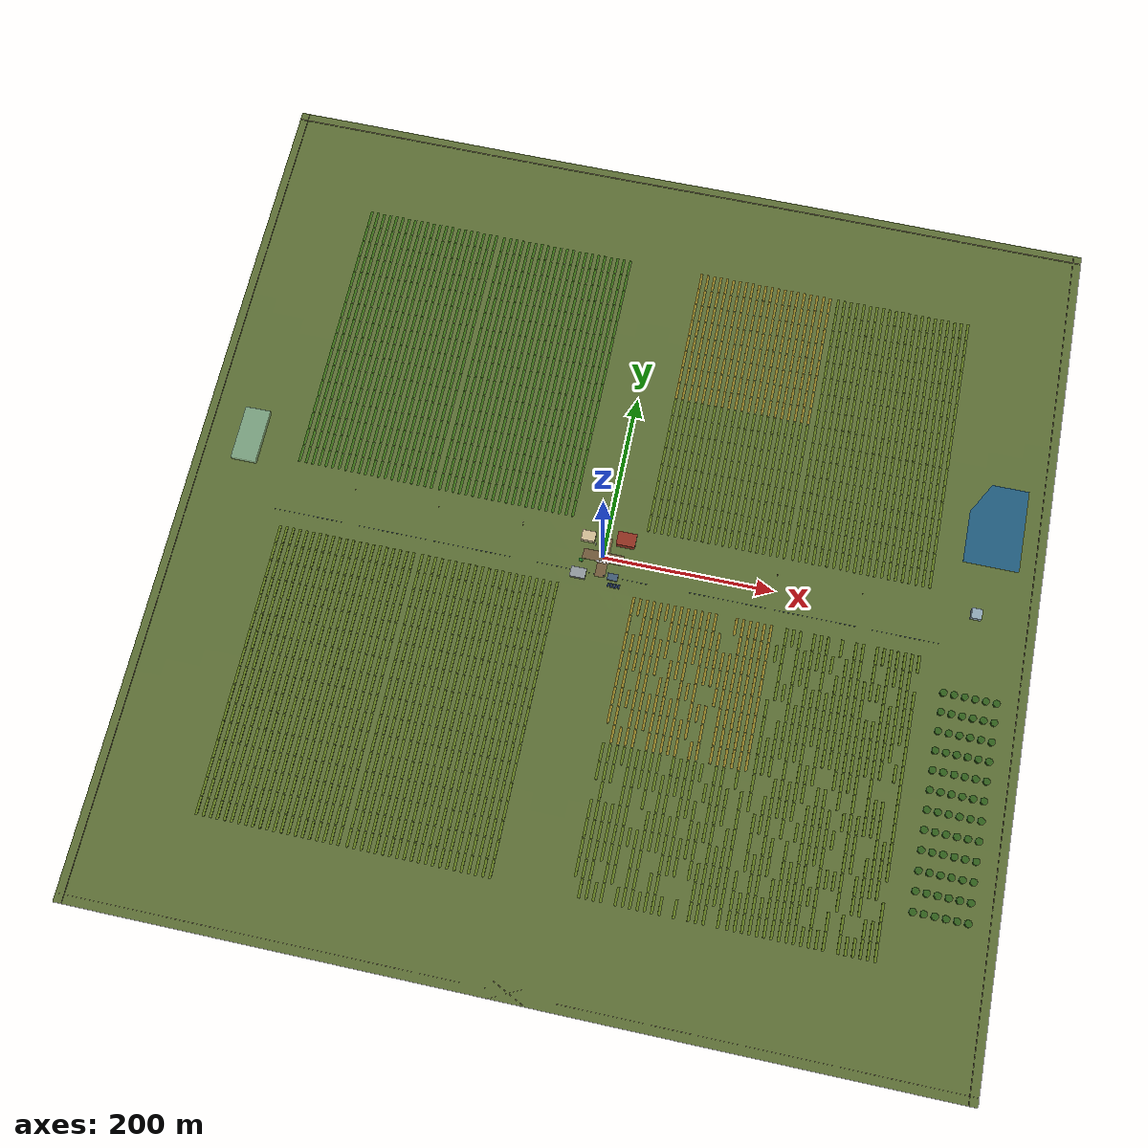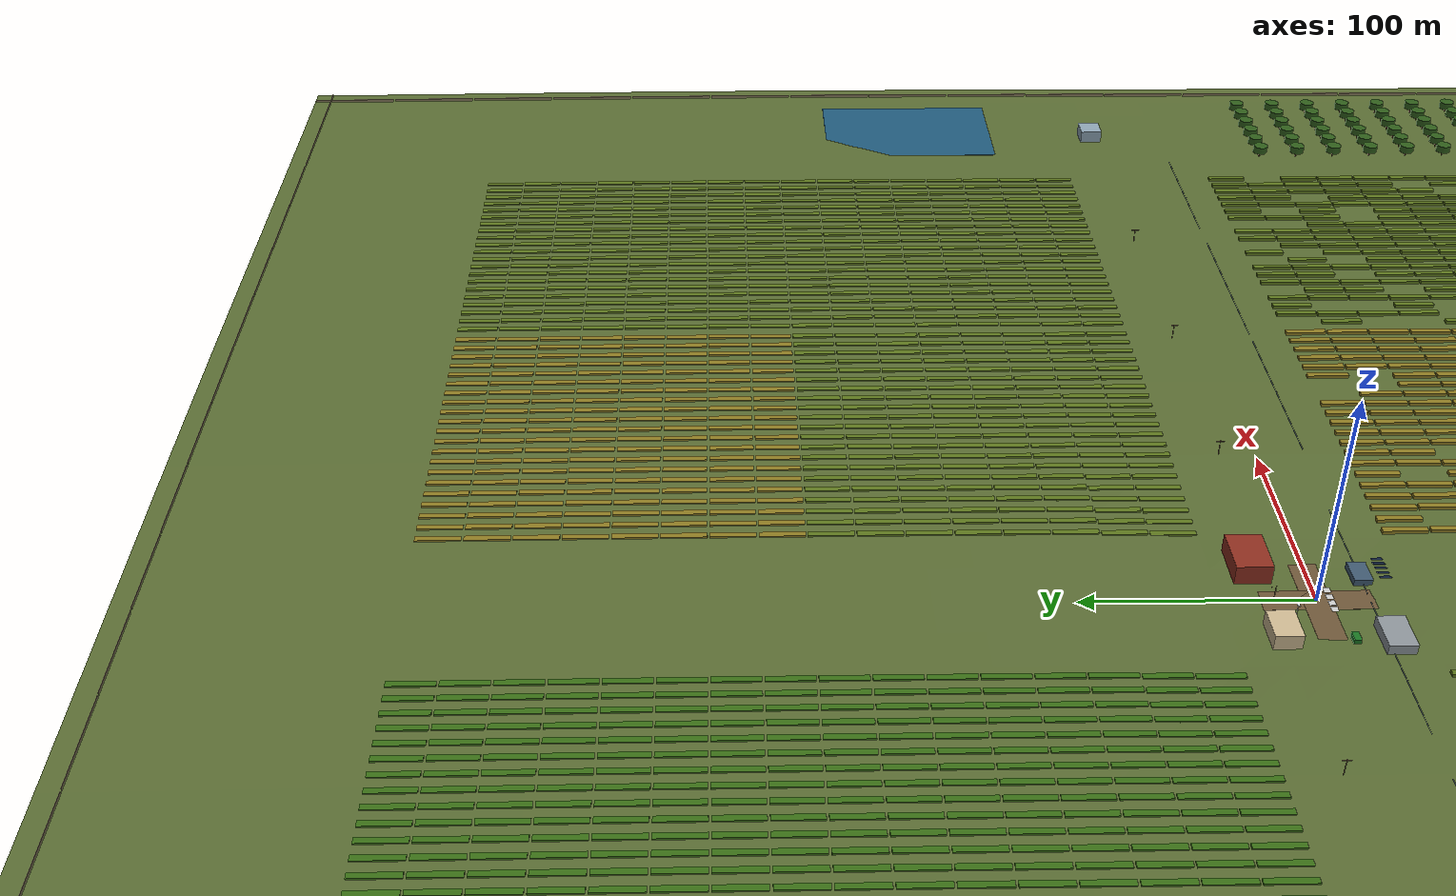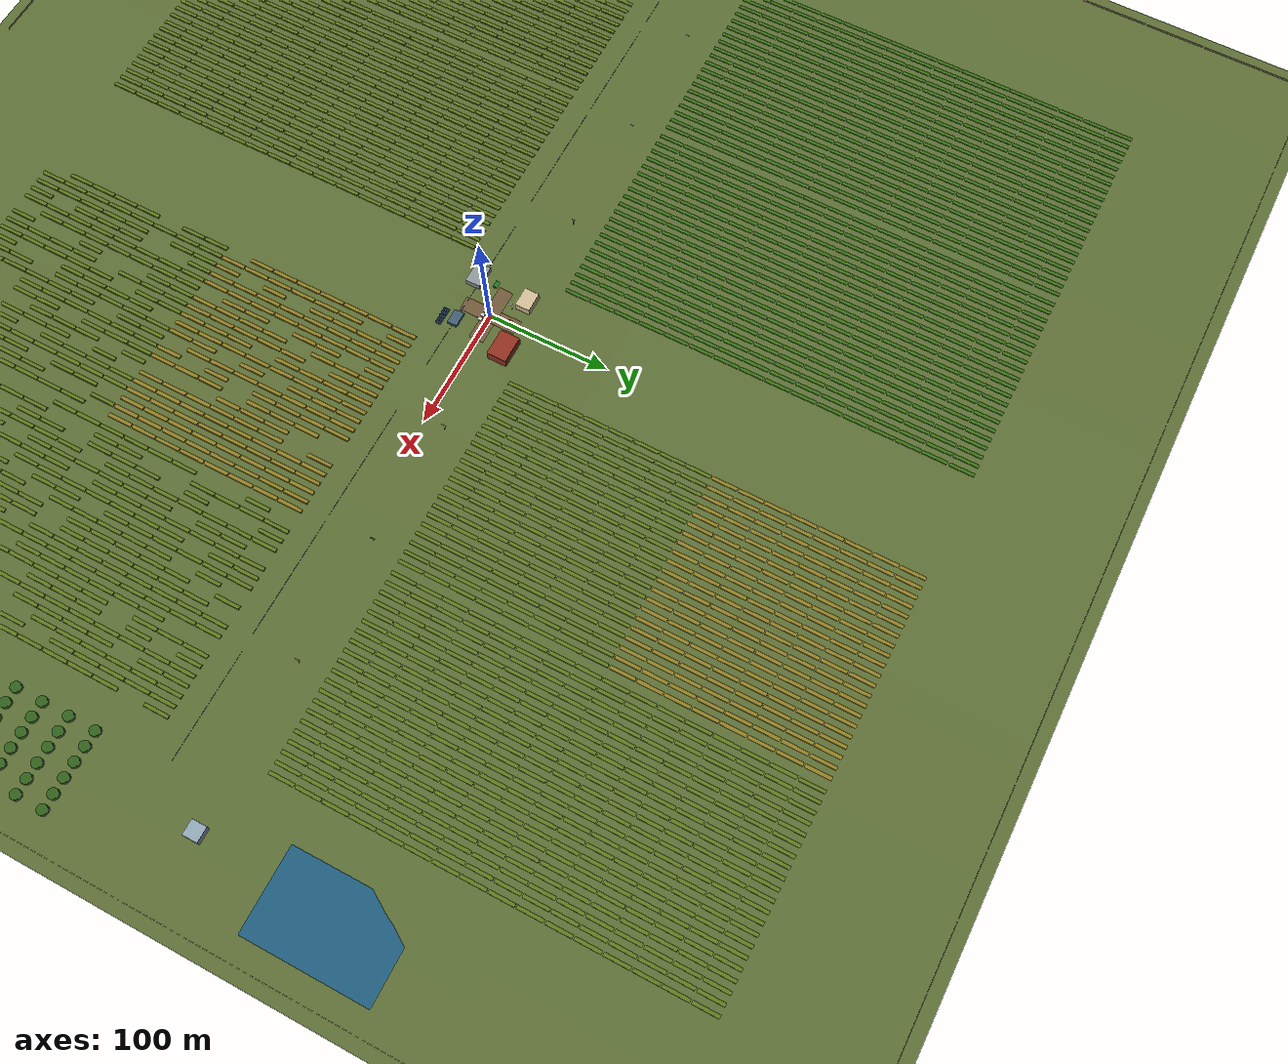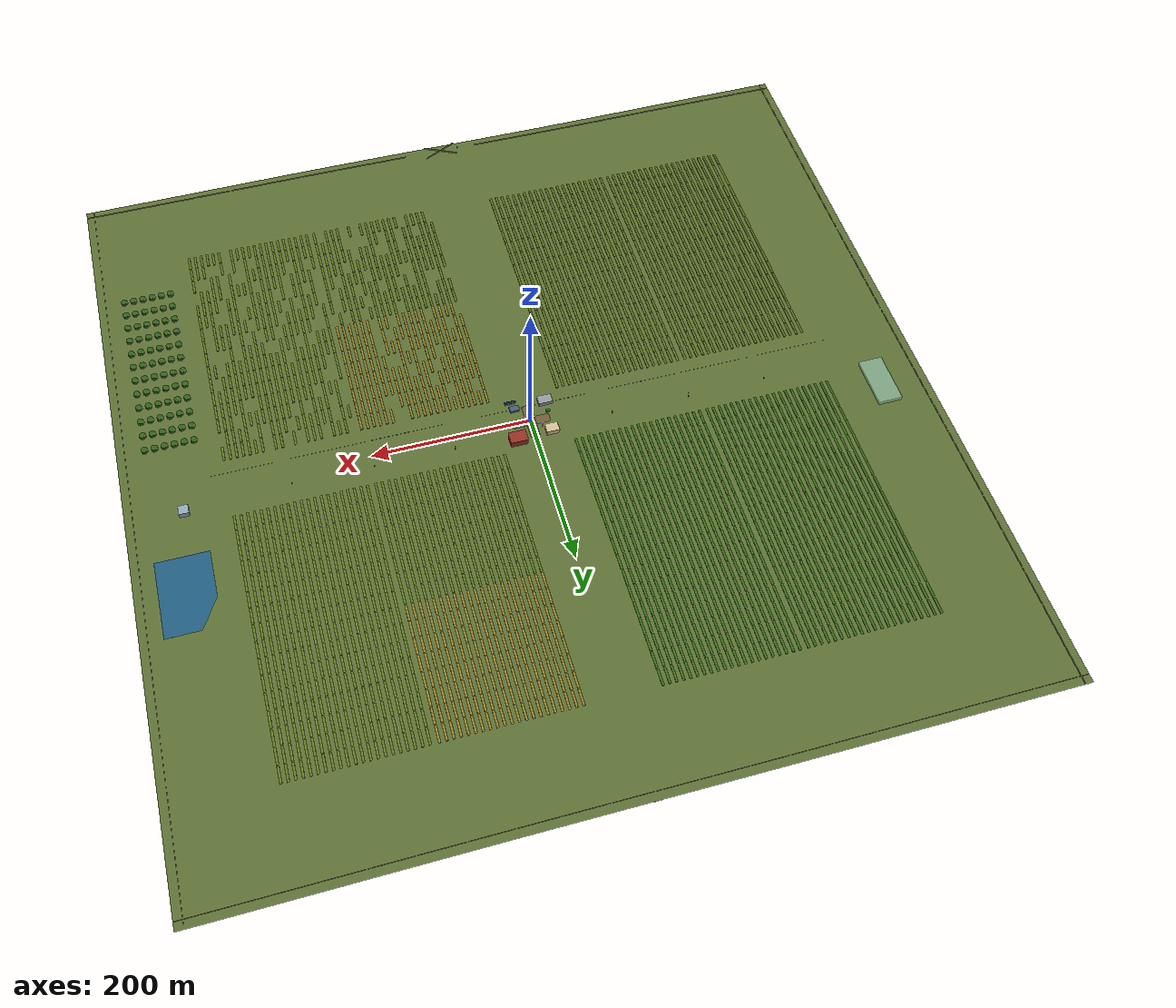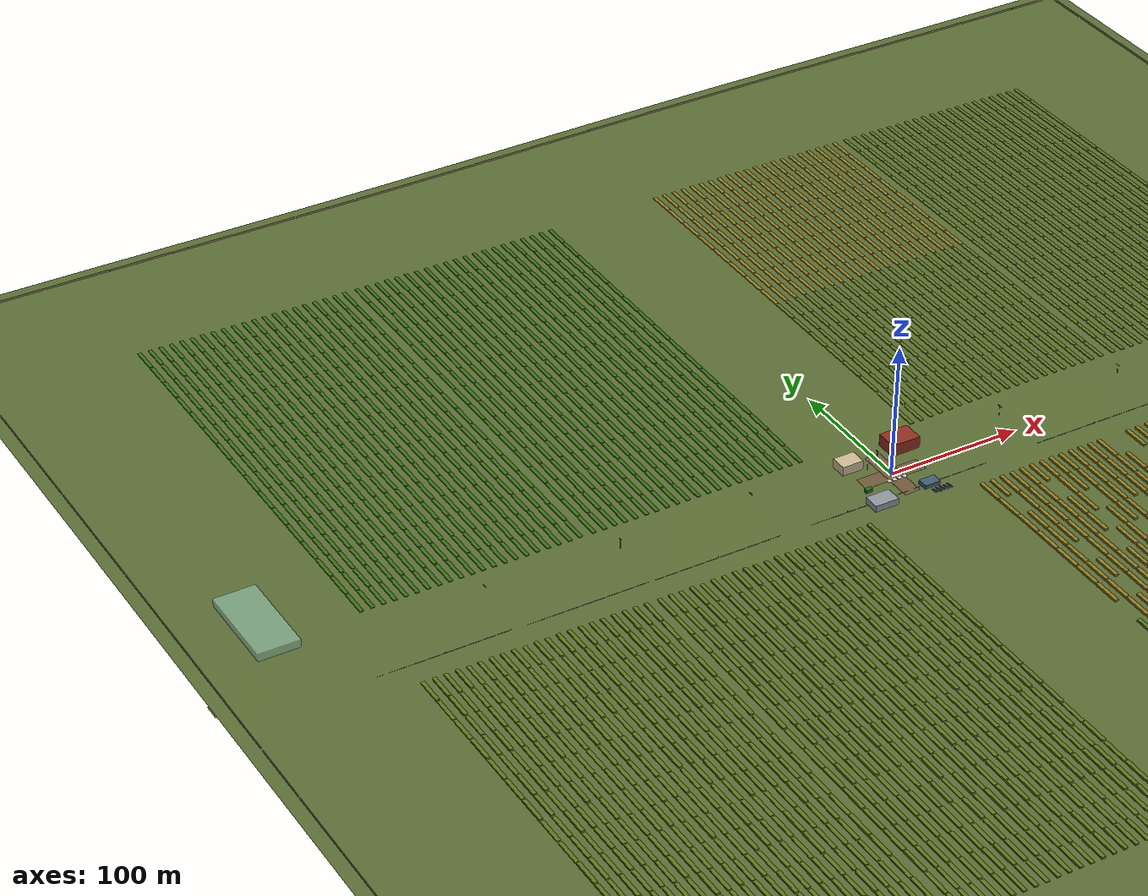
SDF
<sdf version="1.9">
  <world name="agriculture">
    <physics name="fixed_step" type="ignored">
      <max_step_size>0.004</max_step_size>
      <real_time_factor>1</real_time_factor>
    </physics>
    <gravity>0 0 -9.80665</gravity>
    <plugin filename="gz-sim-physics-system" name="gz::sim::systems::Physics" />
    <plugin filename="gz-sim-user-commands-system" name="gz::sim::systems::UserCommands" />
    <plugin filename="gz-sim-scene-broadcaster-system" name="gz::sim::systems::SceneBroadcaster" />
    <plugin filename="gz-sim-imu-system" name="gz::sim::systems::Imu" />
    <plugin filename="gz-sim-navsat-system" name="gz::sim::systems::NavSat" />
    <plugin filename="gz-sim-air-pressure-system" name="gz::sim::systems::AirPressure" />
    <plugin filename="gz-sim-magnetometer-system" name="gz::sim::systems::Magnetometer" />
    <light name="sun" type="directional">
      <pose>0 0 100 0 0 0</pose>
      <direction>-0.5 0.3 -0.9</direction>
      <diffuse>0.95 0.91 0.80 1</diffuse>
      <cast_shadows>true</cast_shadows>
    </light>
    <scene>
      <ambient>0.55 0.55 0.55 1</ambient>
      <background>0.65 0.8 0.92 1</background>
    </scene>
    <spherical_coordinates>
      <surface_model>EARTH_WGS84</surface_model>
      <latitude_deg>47.397742</latitude_deg>
      <longitude_deg>8.545594</longitude_deg>
      <elevation>488</elevation>
      <heading_deg>0</heading_deg>
    </spherical_coordinates>
    <model name="terrain">
      <static>true</static>
      <link name="link">
        <visual name="terrain_visual">
          <pose>0 0 0 0 0 0</pose>
          <geometry>
            <mesh>
              <uri>../models/terrain/terrain.obj</uri>
            </mesh>
          </geometry>
          <material>
            <ambient>0.35 0.42 0.20 1</ambient>
            <diffuse>0.35 0.42 0.20 1</diffuse>
          </material>
        </visual>
        <collision name="terrain_collision">
          <pose>0 0 0 0 0 0</pose>
          <geometry>
            <mesh>
              <uri>../models/terrain/terrain.obj</uri>
            </mesh>
          </geometry>
        </collision>
      </link>
    </model>
    <model name="farm_roads">
      <static>true</static>
      <link name="link">
        <visual name="road1000_visual">
          <pose>0 0 0.035 0 0 0</pose>
          <geometry>
            <box>
              <size>1000 12 0.05</size>
            </box>
          </geometry>
          <material>
            <ambient>0.43 0.34 0.22 1</ambient>
            <diffuse>0.43 0.34 0.22 1</diffuse>
          </material>
        </visual>
        <visual name="road12_visual">
          <pose>0 0 0.035 0 0 0</pose>
          <geometry>
            <box>
              <size>12 1000 0.05</size>
            </box>
          </geometry>
          <material>
            <ambient>0.43 0.34 0.22 1</ambient>
            <diffuse>0.43 0.34 0.22 1</diffuse>
          </material>
        </visual>
      </link>
    </model>
    <model name="crop_field_A">
      <static>true</static>
      <link name="link">
        <visual name="r0_0_0_visual">
          <pose>-376.0 50.625 2.5501370714792224 0 0 0</pose>
          <geometry>
            <box>
              <size>2.8 20.1875 0.7</size>
            </box>
          </geometry>
          <material>
            <ambient>0.22 0.43 0.08 1</ambient>
            <diffuse>0.22 0.43 0.08 1</diffuse>
          </material>
        </visual>
        <visual name="r0_0_1_visual">
          <pose>-376.0 71.875 2.6531552949115214 0 0 0</pose>
          <geometry>
            <box>
              <size>2.8 20.1875 0.7</size>
            </box>
          </geometry>
          <material>
            <ambient>0.22 0.43 0.08 1</ambient>
            <diffuse>0.22 0.43 0.08 1</diffuse>
          </material>
        </visual>
        <visual name="r0_0_2_visual">
          <pose>-376.0 93.125 2.747703381104191 0 0 0</pose>
          <geometry>
            <box>
              <size>2.8 20.1875 0.7</size>
            </box>
          </geometry>
          <material>
            <ambient>0.22 0.43 0.08 1</ambient>
            <diffuse>0.22 0.43 0.08 1</diffuse>
          </material>
        </visual>
        <visual name="r0_0_3_visual">
          <pose>-376.0 114.375 2.8316072247609605 0 0 0</pose>
          <geometry>
            <box>
              <size>2.8 20.1875 0.7</size>
            </box>
          </geometry>
          <material>
            <ambient>0.22 0.43 0.08 1</ambient>
            <diffuse>0.22 0.43 0.08 1</diffuse>
          </material>
        </visual>
        <visual name="r0_0_4_visual">
          <pose>-376.0 135.625 2.9029374817965343 0 0 0</pose>
          <geometry>
            <box>
              <size>2.8 20.1875 0.7</size>
            </box>
          </geometry>
          <material>
            <ambient>0.22 0.43 0.08 1</ambient>
            <diffuse>0.22 0.43 0.08 1</diffuse>
          </material>
        </visual>
        <visual name="r0_0_5_visual">
          <pose>-376.0 156.875 2.9600539340335783 0 0 0</pose>
          <geometry>
            <box>
              <size>2.8 20.1875 0.7</size>
            </box>
          </geometry>
          <material>
            <ambient>0.22 0.43 0.08 1</ambient>
            <diffuse>0.22 0.43 0.08 1</diffuse>
          </material>
        </visual>
        <visual name="r0_0_6_visual">
          <pose>-376.0 178.125 3.0016432055349016 0 0 0</pose>
          <geometry>
            <box>
              <size>2.8 20.1875 0.7</size>
            </box>
          </geometry>
          <material>
            <ambient>0.22 0.43 0.08 1</ambient>
            <diffuse>0.22 0.43 0.08 1</diffuse>
          </material>
        </visual>
        <visual name="r0_0_7_visual">
          <pose>-376.0 199.375 3.026748963294938 0 0 0</pose>
          <geometry>
            <box>
              <size>2.8 20.1875 0.7</size>
            </box>
          </geometry>
          <material>
            <ambient>0.22 0.43 0.08 1</ambient>
            <diffuse>0.22 0.43 0.08 1</diffuse>
          </material>
        </visual>
        <visual name="r0_1_0_visual">
          <pose>-368.0 50.625 2.499910403699458 0 0 0</pose>
          <geometry>
            <box>
              <size>2.8 20.1875 0.7</size>
            </box>
          </geometry>
          <material>
            <ambient>0.22 0.43 0.08 1</ambient>
            <diffuse>0.22 0.43 0.08 1</diffuse>
          </material>
        </visual>
        <visual name="r0_1_1_visual">
          <pose>-368.0 71.875 2.602928627131757 0 0 0</pose>
          <geometry>
            <box>
              <size>2.8 20.1875 0.7</size>
            </box>
          </geometry>
          <material>
            <ambient>0.22 0.43 0.08 1</ambient>
            <diffuse>0.22 0.43 0.08 1</diffuse>
          </material>
        </visual>
        <visual name="r0_1_2_visual">
          <pose>-368.0 93.125 2.6974767133244266 0 0 0</pose>
          <geometry>
            <box>
              <size>2.8 20.1875 0.7</size>
            </box>
          </geometry>
          <material>
            <ambient>0.22 0.43 0.08 1</ambient>
            <diffuse>0.22 0.43 0.08 1</diffuse>
          </material>
        </visual>
        <visual name="r0_1_3_visual">
          <pose>-368.0 114.375 2.7813805569811962 0 0 0</pose>
          <geometry>
            <box>
              <size>2.8 20.1875 0.7</size>
            </box>
          </geometry>
          <material>
            <ambient>0.22 0.43 0.08 1</ambient>
            <diffuse>0.22 0.43 0.08 1</diffuse>
          </material>
        </visual>
        <visual name="r0_1_4_visual">
          <pose>-368.0 135.625 2.85271081401677 0 0 0</pose>
          <geometry>
            <box>
              <size>2.8 20.1875 0.7</size>
            </box>
          </geometry>
          <material>
            <ambient>0.22 0.43 0.08 1</ambient>
            <diffuse>0.22 0.43 0.08 1</diffuse>
          </material>
        </visual>
        <visual name="r0_1_5_visual">
          <pose>-368.0 156.875 2.909827266253814 0 0 0</pose>
          <geometry>
            <box>
              <size>2.8 20.1875 0.7</size>
            </box>
          </geometry>
          <material>
            <ambient>0.22 0.43 0.08 1</ambient>
            <diffuse>0.22 0.43 0.08 1</diffuse>
          </material>
        </visual>
        <visual name="r0_1_6_visual">
          <pose>-368.0 178.125 2.9514165377551373 0 0 0</pose>
          <geometry>
            <box>
              <size>2.8 20.1875 0.7</size>
            </box>
          </geometry>
          <material>
            <ambient>0.22 0.43 0.08 1</ambient>
            <diffuse>0.22 0.43 0.08 1</diffuse>
          </material>
        </visual>
        <visual name="r0_1_7_visual">
          <pose>-368.0 199.375 2.9765222955151738 0 0 0</pose>
          <geometry>
            <box>
              <size>2.8 20.1875 0.7</size>
            </box>
          </geometry>
          <material>
            <ambient>0.22 0.43 0.08 1</ambient>
            <diffuse>0.22 0.43 0.08 1</diffuse>
          </material>
        </visual>
        <visual name="r0_2_0_visual">
          <pose>-360.0 50.625 2.447223755653805 0 0 0</pose>
          <geometry>
            <box>
              <size>2.8 20.1875 0.7</size>
            </box>
          </geometry>
          <material>
            <ambient>0.22 0.43 0.08 1</ambient>
            <diffuse>0.22 0.43 0.08 1</diffuse>
          </material>
        </visual>
        <visual name="r0_2_1_visual">
          <pose>-360.0 71.875 2.5502419790861035 0 0 0</pose>
          <geometry>
            <box>
              <size>2.8 20.1875 0.7</size>
            </box>
          </geometry>
          <material>
            <ambient>0.22 0.43 0.08 1</ambient>
            <diffuse>0.22 0.43 0.08 1</diffuse>
          </material>
        </visual>
        <visual name="r0_2_2_visual">
          <pose>-360.0 93.125 2.644790065278773 0 0 0</pose>
          <geometry>
            <box>
              <size>2.8 20.1875 0.7</size>
            </box>
          </geometry>
          <material>
            <ambient>0.22 0.43 0.08 1</ambient>
            <diffuse>0.22 0.43 0.08 1</diffuse>
          </material>
        </visual>
        <visual name="r0_2_3_visual">
          <pose>-360.0 114.375 2.7286939089355426 0 0 0</pose>
          <geometry>
            <box>
              <size>2.8 20.1875 0.7</size>
            </box>
          </geometry>
          <material>
            <ambient>0.22 0.43 0.08 1</ambient>
            <diffuse>0.22 0.43 0.08 1</diffuse>
          </material>
        </visual>
        <visual name="r0_2_4_visual">
          <pose>-360.0 135.625 2.800024165971117 0 0 0</pose>
          <geometry>
            <box>
              <size>2.8 20.1875 0.7</size>
            </box>
          </geometry>
          <material>
            <ambient>0.22 0.43 0.08 1</ambient>
            <diffuse>0.22 0.43 0.08 1</diffuse>
          </material>
        </visual>
        <visual name="r0_2_5_visual">
          <pose>-360.0 156.875 2.857140618208161 0 0 0</pose>
          <geometry>
            <box>
              <size>2.8 20.1875 0.7</size>
            </box>
          </geometry>
          <material>
            <ambient>0.22 0.43 0.08 1</ambient>
            <diffuse>0.22 0.43 0.08 1</diffuse>
          </material>
        </visual>
        <visual name="r0_2_6_visual">
          <pose>-360.0 178.125 2.8987298897094838 0 0 0</pose>
          <geometry>
            <box>
              <size>2.8 20.1875 0.7</size>
            </box>
          </geometry>
          <material>
            <ambient>0.22 0.43 0.08 1</ambient>
            <diffuse>0.22 0.43 0.08 1</diffuse>
          </material>
        </visual>
        <visual name="r0_2_7_visual">
          <pose>-360.0 199.375 2.9238356474695206 0 0 0</pose>
          <geometry>
            <box>
              <size>2.8 20.1875 0.7</size>
            </box>
          </geometry>
          <material>
            <ambient>0.22 0.43 0.08 1</ambient>
            <diffuse>0.22 0.43 0.08 1</diffuse>
          </material>
        </visual>
        <visual name="r0_3_0_visual">
          <pose>-352.0 50.625 2.3924141420910234 0 0 0</pose>
          <geometry>
            <box>
              <size>2.8 20.1875 0.7</size>
            </box>
          </geometry>
          <material>
            <ambient>0.22 0.43 0.08 1</ambient>
            <diffuse>0.22 0.43 0.08 1</diffuse>
          </material>
        </visual>
        <visual name="r0_3_1_visual">
          <pose>-352.0 71.875 2.4954323655233215 0 0 0</pose>
          <geometry>
            <box>
              <size>2.8 20.1875 0.7</size>
            </box>
          </geometry>
          <material>
            <ambient>0.22 0.43 0.08 1</ambient>
            <diffuse>0.22 0.43 0.08 1</diffuse>
          </material>
        </visual>
        <visual name="r0_3_2_visual">
          <pose>-352.0 93.125 2.589980451715992 0 0 0</pose>
          <geometry>
            <box>
              <size>2.8 20.1875 0.7</size>
            </box>
          </geometry>
          <material>
            <ambient>0.22 0.43 0.08 1</ambient>
            <diffuse>0.22 0.43 0.08 1</diffuse>
          </material>
        </visual>
        <visual name="r0_3_3_visual">
          <pose>-352.0 114.375 2.6738842953727615 0 0 0</pose>
          <geometry>
            <box>
              <size>2.8 20.1875 0.7</size>
            </box>
          </geometry>
          <material>
            <ambient>0.22 0.43 0.08 1</ambient>
            <diffuse>0.22 0.43 0.08 1</diffuse>
          </material>
        </visual>
        <visual name="r0_3_4_visual">
          <pose>-352.0 135.625 2.7452145524083353 0 0 0</pose>
          <geometry>
            <box>
              <size>2.8 20.1875 0.7</size>
            </box>
          </geometry>
          <material>
            <ambient>0.22 0.43 0.08 1</ambient>
            <diffuse>0.22 0.43 0.08 1</diffuse>
          </material>
        </visual>
        <visual name="r0_3_5_visual">
          <pose>-352.0 156.875 2.8023310046453793 0 0 0</pose>
          <geometry>
            <box>
              <size>2.8 20.1875 0.7</size>
            </box>
          </geometry>
          <material>
            <ambient>0.22 0.43 0.08 1</ambient>
            <diffuse>0.22 0.43 0.08 1</diffuse>
          </material>
        </visual>
        <visual name="r0_3_6_visual">
          <pose>-352.0 178.125 2.843920276146702 0 0 0</pose>
          <geometry>
            <box>
              <size>2.8 20.1875 0.7</size>
            </box>
          </geometry>
          <material>
            <ambient>0.22 0.43 0.08 1</ambient>
            <diffuse>0.22 0.43 0.08 1</diffuse>
          </material>
        </visual>
        <visual name="r0_3_7_visual">
          <pose>-352.0 199.375 2.869026033906739 0 0 0</pose>
          <geometry>
            <box>
              <size>2.8 20.1875 0.7</size>
            </box>
          </geometry>
          <material>
            <ambient>0.22 0.43 0.08 1</ambient>
            <diffuse>0.22 0.43 0.08 1</diffuse>
          </material>
        </visual>
        <visual name="r0_4_0_visual">
          <pose>-344.0 50.625 2.335832157494341 0 0 0</pose>
          <geometry>
            <box>
              <size>2.8 20.1875 0.7</size>
            </box>
          </geometry>
          <material>
            <ambient>0.22 0.43 0.08 1</ambient>
            <diffuse>0.22 0.43 0.08 1</diffuse>
          </material>
        </visual>
        <visual name="r0_4_1_visual">
          <pose>-344.0 71.875 2.4388503809266395 0 0 0</pose>
          <geometry>
            <box>
              <size>2.8 20.1875 0.7</size>
            </box>
          </geometry>
          <material>
            <ambient>0.22 0.43 0.08 1</ambient>
            <diffuse>0.22 0.43 0.08 1</diffuse>
          </material>
        </visual>
        <visual name="r0_4_2_visual">
          <pose>-344.0 93.125 2.5333984671193095 0 0 0</pose>
          <geometry>
            <box>
              <size>2.8 20.1875 0.7</size>
            </box>
          </geometry>
          <material>
            <ambient>0.22 0.43 0.08 1</ambient>
            <diffuse>0.22 0.43 0.08 1</diffuse>
          </material>
        </visual>
        <visual name="r0_4_3_visual">
          <pose>-344.0 114.375 2.617302310776079 0 0 0</pose>
          <geometry>
            <box>
              <size>2.8 20.1875 0.7</size>
            </box>
          </geometry>
          <material>
            <ambient>0.22 0.43 0.08 1</ambient>
            <diffuse>0.22 0.43 0.08 1</diffuse>
          </material>
        </visual>
        <visual name="r0_4_4_visual">
          <pose>-344.0 135.625 2.6886325678116534 0 0 0</pose>
          <geometry>
            <box>
              <size>2.8 20.1875 0.7</size>
            </box>
          </geometry>
          <material>
            <ambient>0.22 0.43 0.08 1</ambient>
            <diffuse>0.22 0.43 0.08 1</diffuse>
          </material>
        </visual>
        <visual name="r0_4_5_visual">
          <pose>-344.0 156.875 2.745749020048697 0 0 0</pose>
          <geometry>
            <box>
              <size>2.8 20.1875 0.7</size>
            </box>
          </geometry>
          <material>
            <ambient>0.22 0.43 0.08 1</ambient>
            <diffuse>0.22 0.43 0.08 1</diffuse>
          </material>
        </visual>
        <visual name="r0_4_6_visual">
          <pose>-344.0 178.125 2.78733829155002 0 0 0</pose>
          <geometry>
            <box>
              <size>2.8 20.1875 0.7</size>
            </box>
          </geometry>
          <material>
            <ambient>0.22 0.43 0.08 1</ambient>
            <diffuse>0.22 0.43 0.08 1</diffuse>
          </material>
        </visual>
        <visual name="r0_4_7_visual">
          <pose>-344.0 199.375 2.812444049310057 0 0 0</pose>
          <geometry>
            <box>
              <size>2.8 20.1875 0.7</size>
            </box>
          </geometry>
          <material>
            <ambient>0.22 0.43 0.08 1</ambient>
            <diffuse>0.22 0.43 0.08 1</diffuse>
          </material>
        </visual>
        <visual name="r0_5_0_visual">
          <pose>-336.0 50.625 2.2778397334732006 0 0 0</pose>
          <geometry>
            <box>
              <size>2.8 20.1875 0.7</size>
            </box>
          </geometry>
          <material>
            <ambient>0.22 0.43 0.08 1</ambient>
            <diffuse>0.22 0.43 0.08 1</diffuse>
          </material>
        </visual>
        <visual name="r0_5_1_visual">
          <pose>-336.0 71.875 2.380857956905499 0 0 0</pose>
          <geometry>
            <box>
              <size>2.8 20.1875 0.7</size>
            </box>
          </geometry>
          <material>
            <ambient>0.22 0.43 0.08 1</ambient>
            <diffuse>0.22 0.43 0.08 1</diffuse>
          </material>
        </visual>
        <visual name="r0_5_2_visual">
          <pose>-336.0 93.125 2.4754060430981686 0 0 0</pose>
          <geometry>
            <box>
              <size>2.8 20.1875 0.7</size>
            </box>
          </geometry>
          <material>
            <ambient>0.22 0.43 0.08 1</ambient>
            <diffuse>0.22 0.43 0.08 1</diffuse>
          </material>
        </visual>
        <visual name="r0_5_3_visual">
          <pose>-336.0 114.375 2.559309886754938 0 0 0</pose>
          <geometry>
            <box>
              <size>2.8 20.1875 0.7</size>
            </box>
          </geometry>
          <material>
            <ambient>0.22 0.43 0.08 1</ambient>
            <diffuse>0.22 0.43 0.08 1</diffuse>
          </material>
        </visual>
        <visual name="r0_5_4_visual">
          <pose>-336.0 135.625 2.6306401437905125 0 0 0</pose>
          <geometry>
            <box>
              <size>2.8 20.1875 0.7</size>
            </box>
          </geometry>
          <material>
            <ambient>0.22 0.43 0.08 1</ambient>
            <diffuse>0.22 0.43 0.08 1</diffuse>
          </material>
        </visual>
        <visual name="r0_5_5_visual">
          <pose>-336.0 156.875 2.687756596027556 0 0 0</pose>
          <geometry>
            <box>
              <size>2.8 20.1875 0.7</size>
            </box>
          </geometry>
          <material>
            <ambient>0.22 0.43 0.08 1</ambient>
            <diffuse>0.22 0.43 0.08 1</diffuse>
          </material>
        </visual>
        <visual name="r0_5_6_visual">
          <pose>-336.0 178.125 2.7293458675288798 0 0 0</pose>
          <geometry>
            <box>
              <size>2.8 20.1875 0.7</size>
            </box>
          </geometry>
          <material>
            <ambient>0.22 0.43 0.08 1</ambient>
            <diffuse>0.22 0.43 0.08 1</diffuse>
          </material>
        </visual>
        <visual name="r0_5_7_visual">
          <pose>-336.0 199.375 2.754451625288916 0 0 0</pose>
          <geometry>
            <box>
              <size>2.8 20.1875 0.7</size>
            </box>
          </geometry>
          <material>
            <ambient>0.22 0.43 0.08 1</ambient>
            <diffuse>0.22 0.43 0.08 1</diffuse>
          </material>
        </visual>
        <visual name="r0_6_0_visual">
          <pose>-328.0 50.625 2.2188078236360855 0 0 0</pose>
          <geometry>
            <box>
              <size>2.8 20.1875 0.7</size>
            </box>
          </geometry>
          <material>
            <ambient>0.22 0.43 0.08 1</ambient>
            <diffuse>0.22 0.43 0.08 1</diffuse>
          </material>
        </visual>
        <visual name="r0_6_1_visual">
          <pose>-328.0 71.875 2.321826047068384 0 0 0</pose>
          <geometry>
            <box>
              <size>2.8 20.1875 0.7</size>
            </box>
          </geometry>
          <material>
            <ambient>0.22 0.43 0.08 1</ambient>
            <diffuse>0.22 0.43 0.08 1</diffuse>
          </material>
        </visual>
        <visual name="r0_6_2_visual">
          <pose>-328.0 93.125 2.416374133261054 0 0 0</pose>
          <geometry>
            <box>
              <size>2.8 20.1875 0.7</size>
            </box>
          </geometry>
          <material>
            <ambient>0.22 0.43 0.08 1</ambient>
            <diffuse>0.22 0.43 0.08 1</diffuse>
          </material>
        </visual>
        <visual name="r0_6_3_visual">
          <pose>-328.0 114.375 2.5002779769178236 0 0 0</pose>
          <geometry>
            <box>
              <size>2.8 20.1875 0.7</size>
            </box>
          </geometry>
          <material>
            <ambient>0.22 0.43 0.08 1</ambient>
            <diffuse>0.22 0.43 0.08 1</diffuse>
          </material>
        </visual>
        <visual name="r0_6_4_visual">
          <pose>-328.0 135.625 2.571608233953398 0 0 0</pose>
          <geometry>
            <box>
              <size>2.8 20.1875 0.7</size>
            </box>
          </geometry>
          <material>
            <ambient>0.22 0.43 0.08 1</ambient>
            <diffuse>0.22 0.43 0.08 1</diffuse>
          </material>
        </visual>
        <visual name="r0_6_5_visual">
          <pose>-328.0 156.875 2.6287246861904414 0 0 0</pose>
          <geometry>
            <box>
              <size>2.8 20.1875 0.7</size>
            </box>
          </geometry>
          <material>
            <ambient>0.22 0.43 0.08 1</ambient>
            <diffuse>0.22 0.43 0.08 1</diffuse>
          </material>
        </visual>
        <visual name="r0_6_6_visual">
          <pose>-328.0 178.125 2.6703139576917647 0 0 0</pose>
          <geometry>
            <box>
              <size>2.8 20.1875 0.7</size>
            </box>
          </geometry>
          <material>
            <ambient>0.22 0.43 0.08 1</ambient>
            <diffuse>0.22 0.43 0.08 1</diffuse>
          </material>
        </visual>
        <visual name="r0_6_7_visual">
          <pose>-328.0 199.375 2.6954197154518016 0 0 0</pose>
          <geometry>
            <box>
              <size>2.8 20.1875 0.7</size>
            </box>
          </geometry>
          <material>
            <ambient>0.22 0.43 0.08 1</ambient>
            <diffuse>0.22 0.43 0.08 1</diffuse>
          </material>
        </visual>
        <visual name="r0_7_0_visual">
          <pose>-320.0 50.625 2.1591140307533507 0 0 0</pose>
          <geometry>
            <box>
              <size>2.8 20.1875 0.7</size>
            </box>
          </geometry>
          <material>
            <ambient>0.22 0.43 0.08 1</ambient>
            <diffuse>0.22 0.43 0.08 1</diffuse>
          </material>
        </visual>
        <visual name="r0_7_1_visual">
          <pose>-320.0 71.875 2.262132254185649 0 0 0</pose>
          <geometry>
            <box>
              <size>2.8 20.1875 0.7</size>
            </box>
          </geometry>
          <material>
            <ambient>0.22 0.43 0.08 1</ambient>
            <diffuse>0.22 0.43 0.08 1</diffuse>
          </material>
        </visual>
        <visual name="r0_7_2_visual">
          <pose>-320.0 93.125 2.3566803403783187 0 0 0</pose>
          <geometry>
            <box>
              <size>2.8 20.1875 0.7</size>
            </box>
          </geometry>
          <material>
            <ambient>0.22 0.43 0.08 1</ambient>
            <diffuse>0.22 0.43 0.08 1</diffuse>
          </material>
        </visual>
        <visual name="r0_7_3_visual">
          <pose>-320.0 114.375 2.4405841840350884 0 0 0</pose>
          <geometry>
            <box>
              <size>2.8 20.1875 0.7</size>
            </box>
          </geometry>
          <material>
            <ambient>0.22 0.43 0.08 1</ambient>
            <diffuse>0.22 0.43 0.08 1</diffuse>
          </material>
        </visual>
        <visual name="r0_7_4_visual">
          <pose>-320.0 135.625 2.5119144410706626 0 0 0</pose>
          <geometry>
            <box>
              <size>2.8 20.1875 0.7</size>
            </box>
          </geometry>
          <material>
            <ambient>0.22 0.43 0.08 1</ambient>
            <diffuse>0.22 0.43 0.08 1</diffuse>
          </material>
        </visual>
        <visual name="r0_7_5_visual">
          <pose>-320.0 156.875 2.5690308933077066 0 0 0</pose>
          <geometry>
            <box>
              <size>2.8 20.1875 0.7</size>
            </box>
          </geometry>
          <material>
            <ambient>0.22 0.43 0.08 1</ambient>
            <diffuse>0.22 0.43 0.08 1</diffuse>
          </material>
        </visual>
        <visual name="r0_7_6_visual">
          <pose>-320.0 178.125 2.6106201648090295 0 0 0</pose>
          <geometry>
            <box>
              <size>2.8 20.1875 0.7</size>
            </box>
          </geometry>
          <material>
            <ambient>0.22 0.43 0.08 1</ambient>
            <diffuse>0.22 0.43 0.08 1</diffuse>
          </material>
        </visual>
        <visual name="r0_7_7_visual">
          <pose>-320.0 199.375 2.6357259225690663 0 0 0</pose>
          <geometry>
            <box>
              <size>2.8 20.1875 0.7</size>
            </box>
          </geometry>
          <material>
            <ambient>0.22 0.43 0.08 1</ambient>
            <diffuse>0.22 0.43 0.08 1</diffuse>
          </material>
        </visual>
        <visual name="r0_8_0_visual">
          <pose>-312.0 50.625 2.099140191388094 0 0 0</pose>
          <geometry>
            <box>
              <size>2.8 20.1875 0.7</size>
            </box>
          </geometry>
          <material>
            <ambient>0.22 0.43 0.08 1</ambient>
            <diffuse>0.22 0.43 0.08 1</diffuse>
          </material>
        </visual>
        <visual name="r0_8_1_visual">
          <pose>-312.0 71.875 2.202158414820392 0 0 0</pose>
          <geometry>
            <box>
              <size>2.8 20.1875 0.7</size>
            </box>
          </geometry>
          <material>
            <ambient>0.22 0.43 0.08 1</ambient>
            <diffuse>0.22 0.43 0.08 1</diffuse>
          </material>
        </visual>
        <visual name="r0_8_2_visual">
          <pose>-312.0 93.125 2.296706501013062 0 0 0</pose>
          <geometry>
            <box>
              <size>2.8 20.1875 0.7</size>
            </box>
          </geometry>
          <material>
            <ambient>0.22 0.43 0.08 1</ambient>
            <diffuse>0.22 0.43 0.08 1</diffuse>
          </material>
        </visual>
        <visual name="r0_8_3_visual">
          <pose>-312.0 114.375 2.3806103446698312 0 0 0</pose>
          <geometry>
            <box>
              <size>2.8 20.1875 0.7</size>
            </box>
          </geometry>
          <material>
            <ambient>0.22 0.43 0.08 1</ambient>
            <diffuse>0.22 0.43 0.08 1</diffuse>
          </material>
        </visual>
        <visual name="r0_8_4_visual">
          <pose>-312.0 135.625 2.4519406017054055 0 0 0</pose>
          <geometry>
            <box>
              <size>2.8 20.1875 0.7</size>
            </box>
          </geometry>
          <material>
            <ambient>0.22 0.43 0.08 1</ambient>
            <diffuse>0.22 0.43 0.08 1</diffuse>
          </material>
        </visual>
        <visual name="r0_8_5_visual">
          <pose>-312.0 156.875 2.5090570539424495 0 0 0</pose>
          <geometry>
            <box>
              <size>2.8 20.1875 0.7</size>
            </box>
          </geometry>
          <material>
            <ambient>0.22 0.43 0.08 1</ambient>
            <diffuse>0.22 0.43 0.08 1</diffuse>
          </material>
        </visual>
        <visual name="r0_8_6_visual">
          <pose>-312.0 178.125 2.5506463254437723 0 0 0</pose>
          <geometry>
            <box>
              <size>2.8 20.1875 0.7</size>
            </box>
          </geometry>
          <material>
            <ambient>0.22 0.43 0.08 1</ambient>
            <diffuse>0.22 0.43 0.08 1</diffuse>
          </material>
        </visual>
        <visual name="r0_8_7_visual">
          <pose>-312.0 199.375 2.575752083203809 0 0 0</pose>
          <geometry>
            <box>
              <size>2.8 20.1875 0.7</size>
            </box>
          </geometry>
          <material>
            <ambient>0.22 0.43 0.08 1</ambient>
            <diffuse>0.22 0.43 0.08 1</diffuse>
          </material>
        </visual>
        <visual name="r0_9_0_visual">
          <pose>-304.0 50.625 2.0392699334452145 0 0 0</pose>
          <geometry>
            <box>
              <size>2.8 20.1875 0.7</size>
            </box>
          </geometry>
          <material>
            <ambient>0.22 0.43 0.08 1</ambient>
            <diffuse>0.22 0.43 0.08 1</diffuse>
          </material>
        </visual>
        <visual name="r0_9_1_visual">
          <pose>-304.0 71.875 2.1422881568775125 0 0 0</pose>
          <geometry>
            <box>
              <size>2.8 20.1875 0.7</size>
            </box>
          </geometry>
          <material>
            <ambient>0.22 0.43 0.08 1</ambient>
            <diffuse>0.22 0.43 0.08 1</diffuse>
          </material>
        </visual>
        <visual name="r0_9_2_visual">
          <pose>-304.0 93.125 2.2368362430701825 0 0 0</pose>
          <geometry>
            <box>
              <size>2.8 20.1875 0.7</size>
            </box>
          </geometry>
          <material>
            <ambient>0.22 0.43 0.08 1</ambient>
            <diffuse>0.22 0.43 0.08 1</diffuse>
          </material>
        </visual>
        <visual name="r0_9_3_visual">
          <pose>-304.0 114.375 2.320740086726952 0 0 0</pose>
          <geometry>
            <box>
              <size>2.8 20.1875 0.7</size>
            </box>
          </geometry>
          <material>
            <ambient>0.22 0.43 0.08 1</ambient>
            <diffuse>0.22 0.43 0.08 1</diffuse>
          </material>
        </visual>
        <visual name="r0_9_4_visual">
          <pose>-304.0 135.625 2.3920703437625264 0 0 0</pose>
          <geometry>
            <box>
              <size>2.8 20.1875 0.7</size>
            </box>
          </geometry>
          <material>
            <ambient>0.22 0.43 0.08 1</ambient>
            <diffuse>0.22 0.43 0.08 1</diffuse>
          </material>
        </visual>
        <visual name="r0_9_5_visual">
          <pose>-304.0 156.875 2.44918679599957 0 0 0</pose>
          <geometry>
            <box>
              <size>2.8 20.1875 0.7</size>
            </box>
          </geometry>
          <material>
            <ambient>0.22 0.43 0.08 1</ambient>
            <diffuse>0.22 0.43 0.08 1</diffuse>
          </material>
        </visual>
        <visual name="r0_9_6_visual">
          <pose>-304.0 178.125 2.4907760675008928 0 0 0</pose>
          <geometry>
            <box>
              <size>2.8 20.1875 0.7</size>
            </box>
          </geometry>
          <material>
            <ambient>0.22 0.43 0.08 1</ambient>
            <diffuse>0.22 0.43 0.08 1</diffuse>
          </material>
        </visual>
        <visual name="r0_9_7_visual">
          <pose>-304.0 199.375 2.51588182526093 0 0 0</pose>
          <geometry>
            <box>
              <size>2.8 20.1875 0.7</size>
            </box>
          </geometry>
          <material>
            <ambient>0.22 0.43 0.08 1</ambient>
            <diffuse>0.22 0.43 0.08 1</diffuse>
          </material>
        </visual>
        <visual name="r0_10_0_visual">
          <pose>-296.0 50.625 1.979886222261991 0 0 0</pose>
          <geometry>
            <box>
              <size>2.8 20.1875 0.7</size>
            </box>
          </geometry>
          <material>
            <ambient>0.22 0.43 0.08 1</ambient>
            <diffuse>0.22 0.43 0.08 1</diffuse>
          </material>
        </visual>
        <visual name="r0_10_1_visual">
          <pose>-296.0 71.875 2.082904445694289 0 0 0</pose>
          <geometry>
            <box>
              <size>2.8 20.1875 0.7</size>
            </box>
          </geometry>
          <material>
            <ambient>0.22 0.43 0.08 1</ambient>
            <diffuse>0.22 0.43 0.08 1</diffuse>
          </material>
        </visual>
        <visual name="r0_10_2_visual">
          <pose>-296.0 93.125 2.177452531886959 0 0 0</pose>
          <geometry>
            <box>
              <size>2.8 20.1875 0.7</size>
            </box>
          </geometry>
          <material>
            <ambient>0.22 0.43 0.08 1</ambient>
            <diffuse>0.22 0.43 0.08 1</diffuse>
          </material>
        </visual>
        <visual name="r0_10_3_visual">
          <pose>-296.0 114.375 2.2613563755437287 0 0 0</pose>
          <geometry>
            <box>
              <size>2.8 20.1875 0.7</size>
            </box>
          </geometry>
          <material>
            <ambient>0.22 0.43 0.08 1</ambient>
            <diffuse>0.22 0.43 0.08 1</diffuse>
          </material>
        </visual>
        <visual name="r0_10_4_visual">
          <pose>-296.0 135.625 2.332686632579303 0 0 0</pose>
          <geometry>
            <box>
              <size>2.8 20.1875 0.7</size>
            </box>
          </geometry>
          <material>
            <ambient>0.22 0.43 0.08 1</ambient>
            <diffuse>0.22 0.43 0.08 1</diffuse>
          </material>
        </visual>
        <visual name="r0_10_5_visual">
          <pose>-296.0 156.875 2.3898030848163465 0 0 0</pose>
          <geometry>
            <box>
              <size>2.8 20.1875 0.7</size>
            </box>
          </geometry>
          <material>
            <ambient>0.22 0.43 0.08 1</ambient>
            <diffuse>0.22 0.43 0.08 1</diffuse>
          </material>
        </visual>
        <visual name="r0_10_6_visual">
          <pose>-296.0 178.125 2.43139235631767 0 0 0</pose>
          <geometry>
            <box>
              <size>2.8 20.1875 0.7</size>
            </box>
          </geometry>
          <material>
            <ambient>0.22 0.43 0.08 1</ambient>
            <diffuse>0.22 0.43 0.08 1</diffuse>
          </material>
        </visual>
        <visual name="r0_10_7_visual">
          <pose>-296.0 199.375 2.4564981140777067 0 0 0</pose>
          <geometry>
            <box>
              <size>2.8 20.1875 0.7</size>
            </box>
          </geometry>
          <material>
            <ambient>0.22 0.43 0.08 1</ambient>
            <diffuse>0.22 0.43 0.08 1</diffuse>
          </material>
        </visual>
        <visual name="r0_11_0_visual">
          <pose>-288.0 50.625 1.9213689109368328 0 0 0</pose>
          <geometry>
            <box>
              <size>2.8 20.1875 0.7</size>
            </box>
          </geometry>
          <material>
            <ambient>0.22 0.43 0.08 1</ambient>
            <diffuse>0.22 0.43 0.08 1</diffuse>
          </material>
        </visual>
        <visual name="r0_11_1_visual">
          <pose>-288.0 71.875 2.024387134369131 0 0 0</pose>
          <geometry>
            <box>
              <size>2.8 20.1875 0.7</size>
            </box>
          </geometry>
          <material>
            <ambient>0.22 0.43 0.08 1</ambient>
            <diffuse>0.22 0.43 0.08 1</diffuse>
          </material>
        </visual>
        <visual name="r0_11_2_visual">
          <pose>-288.0 93.125 2.118935220561801 0 0 0</pose>
          <geometry>
            <box>
              <size>2.8 20.1875 0.7</size>
            </box>
          </geometry>
          <material>
            <ambient>0.22 0.43 0.08 1</ambient>
            <diffuse>0.22 0.43 0.08 1</diffuse>
          </material>
        </visual>
        <visual name="r0_11_3_visual">
          <pose>-288.0 114.375 2.20283906421857 0 0 0</pose>
          <geometry>
            <box>
              <size>2.8 20.1875 0.7</size>
            </box>
          </geometry>
          <material>
            <ambient>0.22 0.43 0.08 1</ambient>
            <diffuse>0.22 0.43 0.08 1</diffuse>
          </material>
        </visual>
        <visual name="r0_11_4_visual">
          <pose>-288.0 135.625 2.2741693212541443 0 0 0</pose>
          <geometry>
            <box>
              <size>2.8 20.1875 0.7</size>
            </box>
          </geometry>
          <material>
            <ambient>0.22 0.43 0.08 1</ambient>
            <diffuse>0.22 0.43 0.08 1</diffuse>
          </material>
        </visual>
        <visual name="r0_11_5_visual">
          <pose>-288.0 156.875 2.331285773491188 0 0 0</pose>
          <geometry>
            <box>
              <size>2.8 20.1875 0.7</size>
            </box>
          </geometry>
          <material>
            <ambient>0.22 0.43 0.08 1</ambient>
            <diffuse>0.22 0.43 0.08 1</diffuse>
          </material>
        </visual>
        <visual name="r0_11_6_visual">
          <pose>-288.0 178.125 2.372875044992511 0 0 0</pose>
          <geometry>
            <box>
              <size>2.8 20.1875 0.7</size>
            </box>
          </geometry>
          <material>
            <ambient>0.22 0.43 0.08 1</ambient>
            <diffuse>0.22 0.43 0.08 1</diffuse>
          </material>
        </visual>
        <visual name="r0_11_7_visual">
          <pose>-288.0 199.375 2.397980802752548 0 0 0</pose>
          <geometry>
            <box>
              <size>2.8 20.1875 0.7</size>
            </box>
          </geometry>
          <material>
            <ambient>0.22 0.43 0.08 1</ambient>
            <diffuse>0.22 0.43 0.08 1</diffuse>
          </material>
        </visual>
        <visual name="r0_12_0_visual">
          <pose>-280.0 50.625 1.864092310565737 0 0 0</pose>
          <geometry>
            <box>
              <size>2.8 20.1875 0.7</size>
            </box>
          </geometry>
          <material>
            <ambient>0.22 0.43 0.08 1</ambient>
            <diffuse>0.22 0.43 0.08 1</diffuse>
          </material>
        </visual>
        <visual name="r0_12_1_visual">
          <pose>-280.0 71.875 1.967110533998035 0 0 0</pose>
          <geometry>
            <box>
              <size>2.8 20.1875 0.7</size>
            </box>
          </geometry>
          <material>
            <ambient>0.22 0.43 0.08 1</ambient>
            <diffuse>0.22 0.43 0.08 1</diffuse>
          </material>
        </visual>
        <visual name="r0_12_2_visual">
          <pose>-280.0 93.125 2.061658620190705 0 0 0</pose>
          <geometry>
            <box>
              <size>2.8 20.1875 0.7</size>
            </box>
          </geometry>
          <material>
            <ambient>0.22 0.43 0.08 1</ambient>
            <diffuse>0.22 0.43 0.08 1</diffuse>
          </material>
        </visual>
        <visual name="r0_12_3_visual">
          <pose>-280.0 114.375 2.1455624638474746 0 0 0</pose>
          <geometry>
            <box>
              <size>2.8 20.1875 0.7</size>
            </box>
          </geometry>
          <material>
            <ambient>0.22 0.43 0.08 1</ambient>
            <diffuse>0.22 0.43 0.08 1</diffuse>
          </material>
        </visual>
        <visual name="r0_12_4_visual">
          <pose>-280.0 135.625 2.216892720883049 0 0 0</pose>
          <geometry>
            <box>
              <size>2.8 20.1875 0.7</size>
            </box>
          </geometry>
          <material>
            <ambient>0.22 0.43 0.08 1</ambient>
            <diffuse>0.22 0.43 0.08 1</diffuse>
          </material>
        </visual>
        <visual name="r0_12_5_visual">
          <pose>-280.0 156.875 2.2740091731200924 0 0 0</pose>
          <geometry>
            <box>
              <size>2.8 20.1875 0.7</size>
            </box>
          </geometry>
          <material>
            <ambient>0.22 0.43 0.08 1</ambient>
            <diffuse>0.22 0.43 0.08 1</diffuse>
          </material>
        </visual>
        <visual name="r0_12_6_visual">
          <pose>-280.0 178.125 2.3155984446214153 0 0 0</pose>
          <geometry>
            <box>
              <size>2.8 20.1875 0.7</size>
            </box>
          </geometry>
          <material>
            <ambient>0.22 0.43 0.08 1</ambient>
            <diffuse>0.22 0.43 0.08 1</diffuse>
          </material>
        </visual>
        <visual name="r0_12_7_visual">
          <pose>-280.0 199.375 2.3407042023814526 0 0 0</pose>
          <geometry>
            <box>
              <size>2.8 20.1875 0.7</size>
            </box>
          </geometry>
          <material>
            <ambient>0.22 0.43 0.08 1</ambient>
            <diffuse>0.22 0.43 0.08 1</diffuse>
          </material>
        </visual>
        <visual name="r0_13_0_visual">
          <pose>-272.0 50.625 1.808422795928653 0 0 0</pose>
          <geometry>
            <box>
              <size>2.8 20.1875 0.7</size>
            </box>
          </geometry>
          <material>
            <ambient>0.22 0.43 0.08 1</ambient>
            <diffuse>0.22 0.43 0.08 1</diffuse>
          </material>
        </visual>
        <visual name="r0_13_1_visual">
          <pose>-272.0 71.875 1.911441019360951 0 0 0</pose>
          <geometry>
            <box>
              <size>2.8 20.1875 0.7</size>
            </box>
          </geometry>
          <material>
            <ambient>0.22 0.43 0.08 1</ambient>
            <diffuse>0.22 0.43 0.08 1</diffuse>
          </material>
        </visual>
        <visual name="r0_13_2_visual">
          <pose>-272.0 93.125 2.005989105553621 0 0 0</pose>
          <geometry>
            <box>
              <size>2.8 20.1875 0.7</size>
            </box>
          </geometry>
          <material>
            <ambient>0.22 0.43 0.08 1</ambient>
            <diffuse>0.22 0.43 0.08 1</diffuse>
          </material>
        </visual>
        <visual name="r0_13_3_visual">
          <pose>-272.0 114.375 2.0898929492103906 0 0 0</pose>
          <geometry>
            <box>
              <size>2.8 20.1875 0.7</size>
            </box>
          </geometry>
          <material>
            <ambient>0.22 0.43 0.08 1</ambient>
            <diffuse>0.22 0.43 0.08 1</diffuse>
          </material>
        </visual>
        <visual name="r0_13_4_visual">
          <pose>-272.0 135.625 2.1612232062459644 0 0 0</pose>
          <geometry>
            <box>
              <size>2.8 20.1875 0.7</size>
            </box>
          </geometry>
          <material>
            <ambient>0.22 0.43 0.08 1</ambient>
            <diffuse>0.22 0.43 0.08 1</diffuse>
          </material>
        </visual>
        <visual name="r0_13_5_visual">
          <pose>-272.0 156.875 2.2183396584830084 0 0 0</pose>
          <geometry>
            <box>
              <size>2.8 20.1875 0.7</size>
            </box>
          </geometry>
          <material>
            <ambient>0.22 0.43 0.08 1</ambient>
            <diffuse>0.22 0.43 0.08 1</diffuse>
          </material>
        </visual>
        <visual name="r0_13_6_visual">
          <pose>-272.0 178.125 2.2599289299843317 0 0 0</pose>
          <geometry>
            <box>
              <size>2.8 20.1875 0.7</size>
            </box>
          </geometry>
          <material>
            <ambient>0.22 0.43 0.08 1</ambient>
            <diffuse>0.22 0.43 0.08 1</diffuse>
          </material>
        </visual>
        <visual name="r0_13_7_visual">
          <pose>-272.0 199.375 2.285034687744368 0 0 0</pose>
          <geometry>
            <box>
              <size>2.8 20.1875 0.7</size>
            </box>
          </geometry>
          <material>
            <ambient>0.22 0.43 0.08 1</ambient>
            <diffuse>0.22 0.43 0.08 1</diffuse>
          </material>
        </visual>
        <visual name="r0_14_0_visual">
          <pose>-264.0 50.625 1.7547164619411797 0 0 0</pose>
          <geometry>
            <box>
              <size>2.8 20.1875 0.7</size>
            </box>
          </geometry>
          <material>
            <ambient>0.22 0.43 0.08 1</ambient>
            <diffuse>0.22 0.43 0.08 1</diffuse>
          </material>
        </visual>
        <visual name="r0_14_1_visual">
          <pose>-264.0 71.875 1.8577346853734777 0 0 0</pose>
          <geometry>
            <box>
              <size>2.8 20.1875 0.7</size>
            </box>
          </geometry>
          <material>
            <ambient>0.22 0.43 0.08 1</ambient>
            <diffuse>0.22 0.43 0.08 1</diffuse>
          </material>
        </visual>
        <visual name="r0_14_2_visual">
          <pose>-264.0 93.125 1.9522827715661477 0 0 0</pose>
          <geometry>
            <box>
              <size>2.8 20.1875 0.7</size>
            </box>
          </geometry>
          <material>
            <ambient>0.22 0.43 0.08 1</ambient>
            <diffuse>0.22 0.43 0.08 1</diffuse>
          </material>
        </visual>
        <visual name="r0_14_3_visual">
          <pose>-264.0 114.375 2.0361866152229173 0 0 0</pose>
          <geometry>
            <box>
              <size>2.8 20.1875 0.7</size>
            </box>
          </geometry>
          <material>
            <ambient>0.22 0.43 0.08 1</ambient>
            <diffuse>0.22 0.43 0.08 1</diffuse>
          </material>
        </visual>
        <visual name="r0_14_4_visual">
          <pose>-264.0 135.625 2.107516872258491 0 0 0</pose>
          <geometry>
            <box>
              <size>2.8 20.1875 0.7</size>
            </box>
          </geometry>
          <material>
            <ambient>0.22 0.43 0.08 1</ambient>
            <diffuse>0.22 0.43 0.08 1</diffuse>
          </material>
        </visual>
        <visual name="r0_14_5_visual">
          <pose>-264.0 156.875 2.164633324495535 0 0 0</pose>
          <geometry>
            <box>
              <size>2.8 20.1875 0.7</size>
            </box>
          </geometry>
          <material>
            <ambient>0.22 0.43 0.08 1</ambient>
            <diffuse>0.22 0.43 0.08 1</diffuse>
          </material>
        </visual>
        <visual name="r0_14_6_visual">
          <pose>-264.0 178.125 2.2062225959968584 0 0 0</pose>
          <geometry>
            <box>
              <size>2.8 20.1875 0.7</size>
            </box>
          </geometry>
          <material>
            <ambient>0.22 0.43 0.08 1</ambient>
            <diffuse>0.22 0.43 0.08 1</diffuse>
          </material>
        </visual>
        <visual name="r0_14_7_visual">
          <pose>-264.0 199.375 2.231328353756895 0 0 0</pose>
          <geometry>
            <box>
              <size>2.8 20.1875 0.7</size>
            </box>
          </geometry>
          <material>
            <ambient>0.22 0.43 0.08 1</ambient>
            <diffuse>0.22 0.43 0.08 1</diffuse>
          </material>
        </visual>
        <visual name="r0_15_0_visual">
          <pose>-256.0 50.625 1.7033168458623207 0 0 0</pose>
          <geometry>
            <box>
              <size>2.8 20.1875 0.7</size>
            </box>
          </geometry>
          <material>
            <ambient>0.22 0.43 0.08 1</ambient>
            <diffuse>0.22 0.43 0.08 1</diffuse>
          </material>
        </visual>
        <visual name="r0_15_1_visual">
          <pose>-256.0 71.875 1.8063350692946187 0 0 0</pose>
          <geometry>
            <box>
              <size>2.8 20.1875 0.7</size>
            </box>
          </geometry>
          <material>
            <ambient>0.22 0.43 0.08 1</ambient>
            <diffuse>0.22 0.43 0.08 1</diffuse>
          </material>
        </visual>
        <visual name="r0_15_2_visual">
          <pose>-256.0 93.125 1.9008831554872887 0 0 0</pose>
          <geometry>
            <box>
              <size>2.8 20.1875 0.7</size>
            </box>
          </geometry>
          <material>
            <ambient>0.22 0.43 0.08 1</ambient>
            <diffuse>0.22 0.43 0.08 1</diffuse>
          </material>
        </visual>
        <visual name="r0_15_3_visual">
          <pose>-256.0 114.375 1.9847869991440583 0 0 0</pose>
          <geometry>
            <box>
              <size>2.8 20.1875 0.7</size>
            </box>
          </geometry>
          <material>
            <ambient>0.22 0.43 0.08 1</ambient>
            <diffuse>0.22 0.43 0.08 1</diffuse>
          </material>
        </visual>
        <visual name="r0_15_4_visual">
          <pose>-256.0 135.625 2.0561172561796326 0 0 0</pose>
          <geometry>
            <box>
              <size>2.8 20.1875 0.7</size>
            </box>
          </geometry>
          <material>
            <ambient>0.22 0.43 0.08 1</ambient>
            <diffuse>0.22 0.43 0.08 1</diffuse>
          </material>
        </visual>
        <visual name="r0_15_5_visual">
          <pose>-256.0 156.875 2.113233708416676 0 0 0</pose>
          <geometry>
            <box>
              <size>2.8 20.1875 0.7</size>
            </box>
          </geometry>
          <material>
            <ambient>0.22 0.43 0.08 1</ambient>
            <diffuse>0.22 0.43 0.08 1</diffuse>
          </material>
        </visual>
        <visual name="r0_15_6_visual">
          <pose>-256.0 178.125 2.1548229799179994 0 0 0</pose>
          <geometry>
            <box>
              <size>2.8 20.1875 0.7</size>
            </box>
          </geometry>
          <material>
            <ambient>0.22 0.43 0.08 1</ambient>
            <diffuse>0.22 0.43 0.08 1</diffuse>
          </material>
        </visual>
        <visual name="r0_15_7_visual">
          <pose>-256.0 199.375 2.1799287376780363 0 0 0</pose>
          <geometry>
            <box>
              <size>2.8 20.1875 0.7</size>
            </box>
          </geometry>
          <material>
            <ambient>0.22 0.43 0.08 1</ambient>
            <diffuse>0.22 0.43 0.08 1</diffuse>
          </material>
        </visual>
        <visual name="r0_16_0_visual">
          <pose>-248.0 50.625 1.654552729828382 0 0 0</pose>
          <geometry>
            <box>
              <size>2.8 20.1875 0.7</size>
            </box>
          </geometry>
          <material>
            <ambient>0.22 0.43 0.08 1</ambient>
            <diffuse>0.22 0.43 0.08 1</diffuse>
          </material>
        </visual>
        <visual name="r0_16_1_visual">
          <pose>-248.0 71.875 1.75757095326068 0 0 0</pose>
          <geometry>
            <box>
              <size>2.8 20.1875 0.7</size>
            </box>
          </geometry>
          <material>
            <ambient>0.22 0.43 0.08 1</ambient>
            <diffuse>0.22 0.43 0.08 1</diffuse>
          </material>
        </visual>
        <visual name="r0_16_2_visual">
          <pose>-248.0 93.125 1.85211903945335 0 0 0</pose>
          <geometry>
            <box>
              <size>2.8 20.1875 0.7</size>
            </box>
          </geometry>
          <material>
            <ambient>0.22 0.43 0.08 1</ambient>
            <diffuse>0.22 0.43 0.08 1</diffuse>
          </material>
        </visual>
        <visual name="r0_16_3_visual">
          <pose>-248.0 114.375 1.9360228831101196 0 0 0</pose>
          <geometry>
            <box>
              <size>2.8 20.1875 0.7</size>
            </box>
          </geometry>
          <material>
            <ambient>0.22 0.43 0.08 1</ambient>
            <diffuse>0.22 0.43 0.08 1</diffuse>
          </material>
        </visual>
        <visual name="r0_16_4_visual">
          <pose>-248.0 135.625 2.007353140145694 0 0 0</pose>
          <geometry>
            <box>
              <size>2.8 20.1875 0.7</size>
            </box>
          </geometry>
          <material>
            <ambient>0.22 0.43 0.08 1</ambient>
            <diffuse>0.22 0.43 0.08 1</diffuse>
          </material>
        </visual>
        <visual name="r0_16_5_visual">
          <pose>-248.0 156.875 2.0644695923827374 0 0 0</pose>
          <geometry>
            <box>
              <size>2.8 20.1875 0.7</size>
            </box>
          </geometry>
          <material>
            <ambient>0.22 0.43 0.08 1</ambient>
            <diffuse>0.22 0.43 0.08 1</diffuse>
          </material>
        </visual>
        <visual name="r0_16_6_visual">
          <pose>-248.0 178.125 2.1060588638840607 0 0 0</pose>
          <geometry>
            <box>
              <size>2.8 20.1875 0.7</size>
            </box>
          </geometry>
          <material>
            <ambient>0.22 0.43 0.08 1</ambient>
            <diffuse>0.22 0.43 0.08 1</diffuse>
          </material>
        </visual>
        <visual name="r0_16_7_visual">
          <pose>-248.0 199.375 2.1311646216440976 0 0 0</pose>
          <geometry>
            <box>
              <size>2.8 20.1875 0.7</size>
            </box>
          </geometry>
          <material>
            <ambient>0.22 0.43 0.08 1</ambient>
            <diffuse>0.22 0.43 0.08 1</diffuse>
          </material>
        </visual>
        <visual name="r0_17_0_visual">
          <pose>-240.0 50.625 1.6087360377693023 0 0 0</pose>
          <geometry>
            <box>
              <size>2.8 20.1875 0.7</size>
            </box>
          </geometry>
          <material>
            <ambient>0.22 0.43 0.08 1</ambient>
            <diffuse>0.22 0.43 0.08 1</diffuse>
          </material>
        </visual>
        <visual name="r0_17_1_visual">
          <pose>-240.0 71.875 1.7117542612016008 0 0 0</pose>
          <geometry>
            <box>
              <size>2.8 20.1875 0.7</size>
            </box>
          </geometry>
          <material>
            <ambient>0.22 0.43 0.08 1</ambient>
            <diffuse>0.22 0.43 0.08 1</diffuse>
          </material>
        </visual>
        <visual name="r0_17_2_visual">
          <pose>-240.0 93.125 1.8063023473942703 0 0 0</pose>
          <geometry>
            <box>
              <size>2.8 20.1875 0.7</size>
            </box>
          </geometry>
          <material>
            <ambient>0.22 0.43 0.08 1</ambient>
            <diffuse>0.22 0.43 0.08 1</diffuse>
          </material>
        </visual>
        <visual name="r0_17_3_visual">
          <pose>-240.0 114.375 1.89020619105104 0 0 0</pose>
          <geometry>
            <box>
              <size>2.8 20.1875 0.7</size>
            </box>
          </geometry>
          <material>
            <ambient>0.22 0.43 0.08 1</ambient>
            <diffuse>0.22 0.43 0.08 1</diffuse>
          </material>
        </visual>
        <visual name="r0_17_4_visual">
          <pose>-240.0 135.625 1.9615364480866142 0 0 0</pose>
          <geometry>
            <box>
              <size>2.8 20.1875 0.7</size>
            </box>
          </geometry>
          <material>
            <ambient>0.22 0.43 0.08 1</ambient>
            <diffuse>0.22 0.43 0.08 1</diffuse>
          </material>
        </visual>
        <visual name="r0_17_5_visual">
          <pose>-240.0 156.875 2.018652900323658 0 0 0</pose>
          <geometry>
            <box>
              <size>2.8 20.1875 0.7</size>
            </box>
          </geometry>
          <material>
            <ambient>0.22 0.43 0.08 1</ambient>
            <diffuse>0.22 0.43 0.08 1</diffuse>
          </material>
        </visual>
        <visual name="r0_17_6_visual">
          <pose>-240.0 178.125 2.060242171824981 0 0 0</pose>
          <geometry>
            <box>
              <size>2.8 20.1875 0.7</size>
            </box>
          </geometry>
          <material>
            <ambient>0.22 0.43 0.08 1</ambient>
            <diffuse>0.22 0.43 0.08 1</diffuse>
          </material>
        </visual>
        <visual name="r0_17_7_visual">
          <pose>-240.0 199.375 2.085347929585018 0 0 0</pose>
          <geometry>
            <box>
              <size>2.8 20.1875 0.7</size>
            </box>
          </geometry>
          <material>
            <ambient>0.22 0.43 0.08 1</ambient>
            <diffuse>0.22 0.43 0.08 1</diffuse>
          </material>
        </visual>
        <visual name="r0_18_0_visual">
          <pose>-232.0 50.625 1.5661598401599774 0 0 0</pose>
          <geometry>
            <box>
              <size>2.8 20.1875 0.7</size>
            </box>
          </geometry>
          <material>
            <ambient>0.22 0.43 0.08 1</ambient>
            <diffuse>0.22 0.43 0.08 1</diffuse>
          </material>
        </visual>
        <visual name="r0_18_1_visual">
          <pose>-232.0 71.875 1.6691780635922755 0 0 0</pose>
          <geometry>
            <box>
              <size>2.8 20.1875 0.7</size>
            </box>
          </geometry>
          <material>
            <ambient>0.22 0.43 0.08 1</ambient>
            <diffuse>0.22 0.43 0.08 1</diffuse>
          </material>
        </visual>
        <visual name="r0_18_2_visual">
          <pose>-232.0 93.125 1.7637261497849455 0 0 0</pose>
          <geometry>
            <box>
              <size>2.8 20.1875 0.7</size>
            </box>
          </geometry>
          <material>
            <ambient>0.22 0.43 0.08 1</ambient>
            <diffuse>0.22 0.43 0.08 1</diffuse>
          </material>
        </visual>
        <visual name="r0_18_3_visual">
          <pose>-232.0 114.375 1.847629993441715 0 0 0</pose>
          <geometry>
            <box>
              <size>2.8 20.1875 0.7</size>
            </box>
          </geometry>
          <material>
            <ambient>0.22 0.43 0.08 1</ambient>
            <diffuse>0.22 0.43 0.08 1</diffuse>
          </material>
        </visual>
        <visual name="r0_18_4_visual">
          <pose>-232.0 135.625 1.918960250477289 0 0 0</pose>
          <geometry>
            <box>
              <size>2.8 20.1875 0.7</size>
            </box>
          </geometry>
          <material>
            <ambient>0.22 0.43 0.08 1</ambient>
            <diffuse>0.22 0.43 0.08 1</diffuse>
          </material>
        </visual>
        <visual name="r0_18_5_visual">
          <pose>-232.0 156.875 1.9760767027143329 0 0 0</pose>
          <geometry>
            <box>
              <size>2.8 20.1875 0.7</size>
            </box>
          </geometry>
          <material>
            <ambient>0.22 0.43 0.08 1</ambient>
            <diffuse>0.22 0.43 0.08 1</diffuse>
          </material>
        </visual>
        <visual name="r0_18_6_visual">
          <pose>-232.0 178.125 2.017665974215656 0 0 0</pose>
          <geometry>
            <box>
              <size>2.8 20.1875 0.7</size>
            </box>
          </geometry>
          <material>
            <ambient>0.22 0.43 0.08 1</ambient>
            <diffuse>0.22 0.43 0.08 1</diffuse>
          </material>
        </visual>
        <visual name="r0_18_7_visual">
          <pose>-232.0 199.375 2.0427717319756926 0 0 0</pose>
          <geometry>
            <box>
              <size>2.8 20.1875 0.7</size>
            </box>
          </geometry>
          <material>
            <ambient>0.22 0.43 0.08 1</ambient>
            <diffuse>0.22 0.43 0.08 1</diffuse>
          </material>
        </visual>
        <visual name="r0_19_0_visual">
          <pose>-224.0 50.625 1.5270964793693507 0 0 0</pose>
          <geometry>
            <box>
              <size>2.8 20.1875 0.7</size>
            </box>
          </geometry>
          <material>
            <ambient>0.22 0.43 0.08 1</ambient>
            <diffuse>0.22 0.43 0.08 1</diffuse>
          </material>
        </visual>
        <visual name="r0_19_1_visual">
          <pose>-224.0 71.875 1.6301147028016487 0 0 0</pose>
          <geometry>
            <box>
              <size>2.8 20.1875 0.7</size>
            </box>
          </geometry>
          <material>
            <ambient>0.22 0.43 0.08 1</ambient>
            <diffuse>0.22 0.43 0.08 1</diffuse>
          </material>
        </visual>
        <visual name="r0_19_2_visual">
          <pose>-224.0 93.125 1.7246627889943187 0 0 0</pose>
          <geometry>
            <box>
              <size>2.8 20.1875 0.7</size>
            </box>
          </geometry>
          <material>
            <ambient>0.22 0.43 0.08 1</ambient>
            <diffuse>0.22 0.43 0.08 1</diffuse>
          </material>
        </visual>
        <visual name="r0_19_3_visual">
          <pose>-224.0 114.375 1.8085666326510883 0 0 0</pose>
          <geometry>
            <box>
              <size>2.8 20.1875 0.7</size>
            </box>
          </geometry>
          <material>
            <ambient>0.22 0.43 0.08 1</ambient>
            <diffuse>0.22 0.43 0.08 1</diffuse>
          </material>
        </visual>
        <visual name="r0_19_4_visual">
          <pose>-224.0 135.625 1.8798968896866626 0 0 0</pose>
          <geometry>
            <box>
              <size>2.8 20.1875 0.7</size>
            </box>
          </geometry>
          <material>
            <ambient>0.22 0.43 0.08 1</ambient>
            <diffuse>0.22 0.43 0.08 1</diffuse>
          </material>
        </visual>
        <visual name="r0_19_5_visual">
          <pose>-224.0 156.875 1.9370133419237061 0 0 0</pose>
          <geometry>
            <box>
              <size>2.8 20.1875 0.7</size>
            </box>
          </geometry>
          <material>
            <ambient>0.22 0.43 0.08 1</ambient>
            <diffuse>0.22 0.43 0.08 1</diffuse>
          </material>
        </visual>
        <visual name="r0_19_6_visual">
          <pose>-224.0 178.125 1.9786026134250294 0 0 0</pose>
          <geometry>
            <box>
              <size>2.8 20.1875 0.7</size>
            </box>
          </geometry>
          <material>
            <ambient>0.22 0.43 0.08 1</ambient>
            <diffuse>0.22 0.43 0.08 1</diffuse>
          </material>
        </visual>
        <visual name="r0_19_7_visual">
          <pose>-224.0 199.375 2.0037083711850663 0 0 0</pose>
          <geometry>
            <box>
              <size>2.8 20.1875 0.7</size>
            </box>
          </geometry>
          <material>
            <ambient>0.22 0.43 0.08 1</ambient>
            <diffuse>0.22 0.43 0.08 1</diffuse>
          </material>
        </visual>
        <visual name="r0_20_0_visual">
          <pose>-216.0 50.625 1.4917958275986534 0 0 0</pose>
          <geometry>
            <box>
              <size>2.8 20.1875 0.7</size>
            </box>
          </geometry>
          <material>
            <ambient>0.22 0.43 0.08 1</ambient>
            <diffuse>0.22 0.43 0.08 1</diffuse>
          </material>
        </visual>
        <visual name="r0_20_1_visual">
          <pose>-216.0 71.875 1.5948140510309519 0 0 0</pose>
          <geometry>
            <box>
              <size>2.8 20.1875 0.7</size>
            </box>
          </geometry>
          <material>
            <ambient>0.22 0.43 0.08 1</ambient>
            <diffuse>0.22 0.43 0.08 1</diffuse>
          </material>
        </visual>
        <visual name="r0_20_2_visual">
          <pose>-216.0 93.125 1.6893621372236214 0 0 0</pose>
          <geometry>
            <box>
              <size>2.8 20.1875 0.7</size>
            </box>
          </geometry>
          <material>
            <ambient>0.22 0.43 0.08 1</ambient>
            <diffuse>0.22 0.43 0.08 1</diffuse>
          </material>
        </visual>
        <visual name="r0_20_3_visual">
          <pose>-216.0 114.375 1.773265980880391 0 0 0</pose>
          <geometry>
            <box>
              <size>2.8 20.1875 0.7</size>
            </box>
          </geometry>
          <material>
            <ambient>0.22 0.43 0.08 1</ambient>
            <diffuse>0.22 0.43 0.08 1</diffuse>
          </material>
        </visual>
        <visual name="r0_20_4_visual">
          <pose>-216.0 135.625 1.8445962379159653 0 0 0</pose>
          <geometry>
            <box>
              <size>2.8 20.1875 0.7</size>
            </box>
          </geometry>
          <material>
            <ambient>0.22 0.43 0.08 1</ambient>
            <diffuse>0.22 0.43 0.08 1</diffuse>
          </material>
        </visual>
        <visual name="r0_20_5_visual">
          <pose>-216.0 156.875 1.9017126901530093 0 0 0</pose>
          <geometry>
            <box>
              <size>2.8 20.1875 0.7</size>
            </box>
          </geometry>
          <material>
            <ambient>0.22 0.43 0.08 1</ambient>
            <diffuse>0.22 0.43 0.08 1</diffuse>
          </material>
        </visual>
        <visual name="r0_20_6_visual">
          <pose>-216.0 178.125 1.943301961654332 0 0 0</pose>
          <geometry>
            <box>
              <size>2.8 20.1875 0.7</size>
            </box>
          </geometry>
          <material>
            <ambient>0.22 0.43 0.08 1</ambient>
            <diffuse>0.22 0.43 0.08 1</diffuse>
          </material>
        </visual>
        <visual name="r0_20_7_visual">
          <pose>-216.0 199.375 1.968407719414369 0 0 0</pose>
          <geometry>
            <box>
              <size>2.8 20.1875 0.7</size>
            </box>
          </geometry>
          <material>
            <ambient>0.22 0.43 0.08 1</ambient>
            <diffuse>0.22 0.43 0.08 1</diffuse>
          </material>
        </visual>
        <visual name="r1_0_0_visual">
          <pose>-206.0 50.625 1.4533029100706853 0 0 0</pose>
          <geometry>
            <box>
              <size>2.8 20.1875 0.7</size>
            </box>
          </geometry>
          <material>
            <ambient>0.22 0.43 0.08 1</ambient>
            <diffuse>0.22 0.43 0.08 1</diffuse>
          </material>
        </visual>
        <visual name="r1_0_1_visual">
          <pose>-206.0 71.875 1.5563211335029834 0 0 0</pose>
          <geometry>
            <box>
              <size>2.8 20.1875 0.7</size>
            </box>
          </geometry>
          <material>
            <ambient>0.22 0.43 0.08 1</ambient>
            <diffuse>0.22 0.43 0.08 1</diffuse>
          </material>
        </visual>
        <visual name="r1_0_2_visual">
          <pose>-206.0 93.125 1.6508692196956534 0 0 0</pose>
          <geometry>
            <box>
              <size>2.8 20.1875 0.7</size>
            </box>
          </geometry>
          <material>
            <ambient>0.22 0.43 0.08 1</ambient>
            <diffuse>0.22 0.43 0.08 1</diffuse>
          </material>
        </visual>
        <visual name="r1_0_3_visual">
          <pose>-206.0 114.375 1.734773063352423 0 0 0</pose>
          <geometry>
            <box>
              <size>2.8 20.1875 0.7</size>
            </box>
          </geometry>
          <material>
            <ambient>0.22 0.43 0.08 1</ambient>
            <diffuse>0.22 0.43 0.08 1</diffuse>
          </material>
        </visual>
        <visual name="r1_0_4_visual">
          <pose>-206.0 135.625 1.8061033203879973 0 0 0</pose>
          <geometry>
            <box>
              <size>2.8 20.1875 0.7</size>
            </box>
          </geometry>
          <material>
            <ambient>0.22 0.43 0.08 1</ambient>
            <diffuse>0.22 0.43 0.08 1</diffuse>
          </material>
        </visual>
        <visual name="r1_0_5_visual">
          <pose>-206.0 156.875 1.8632197726250408 0 0 0</pose>
          <geometry>
            <box>
              <size>2.8 20.1875 0.7</size>
            </box>
          </geometry>
          <material>
            <ambient>0.22 0.43 0.08 1</ambient>
            <diffuse>0.22 0.43 0.08 1</diffuse>
          </material>
        </visual>
        <visual name="r1_0_6_visual">
          <pose>-206.0 178.125 1.9048090441263636 0 0 0</pose>
          <geometry>
            <box>
              <size>2.8 20.1875 0.7</size>
            </box>
          </geometry>
          <material>
            <ambient>0.22 0.43 0.08 1</ambient>
            <diffuse>0.22 0.43 0.08 1</diffuse>
          </material>
        </visual>
        <visual name="r1_0_7_visual">
          <pose>-206.0 199.375 1.929914801886401 0 0 0</pose>
          <geometry>
            <box>
              <size>2.8 20.1875 0.7</size>
            </box>
          </geometry>
          <material>
            <ambient>0.22 0.43 0.08 1</ambient>
            <diffuse>0.22 0.43 0.08 1</diffuse>
          </material>
        </visual>
        <visual name="r1_1_0_visual">
          <pose>-198.0 50.625 1.4272549567213084 0 0 0</pose>
          <geometry>
            <box>
              <size>2.8 20.1875 0.7</size>
            </box>
          </geometry>
          <material>
            <ambient>0.22 0.43 0.08 1</ambient>
            <diffuse>0.22 0.43 0.08 1</diffuse>
          </material>
        </visual>
        <visual name="r1_1_1_visual">
          <pose>-198.0 71.875 1.5302731801536065 0 0 0</pose>
          <geometry>
            <box>
              <size>2.8 20.1875 0.7</size>
            </box>
          </geometry>
          <material>
            <ambient>0.22 0.43 0.08 1</ambient>
            <diffuse>0.22 0.43 0.08 1</diffuse>
          </material>
        </visual>
        <visual name="r1_1_2_visual">
          <pose>-198.0 93.125 1.6248212663462764 0 0 0</pose>
          <geometry>
            <box>
              <size>2.8 20.1875 0.7</size>
            </box>
          </geometry>
          <material>
            <ambient>0.22 0.43 0.08 1</ambient>
            <diffuse>0.22 0.43 0.08 1</diffuse>
          </material>
        </visual>
        <visual name="r1_1_3_visual">
          <pose>-198.0 114.375 1.708725110003046 0 0 0</pose>
          <geometry>
            <box>
              <size>2.8 20.1875 0.7</size>
            </box>
          </geometry>
          <material>
            <ambient>0.22 0.43 0.08 1</ambient>
            <diffuse>0.22 0.43 0.08 1</diffuse>
          </material>
        </visual>
        <visual name="r1_1_4_visual">
          <pose>-198.0 135.625 1.7800553670386203 0 0 0</pose>
          <geometry>
            <box>
              <size>2.8 20.1875 0.7</size>
            </box>
          </geometry>
          <material>
            <ambient>0.22 0.43 0.08 1</ambient>
            <diffuse>0.22 0.43 0.08 1</diffuse>
          </material>
        </visual>
        <visual name="r1_1_5_visual">
          <pose>-198.0 156.875 1.8371718192756639 0 0 0</pose>
          <geometry>
            <box>
              <size>2.8 20.1875 0.7</size>
            </box>
          </geometry>
          <material>
            <ambient>0.22 0.43 0.08 1</ambient>
            <diffuse>0.22 0.43 0.08 1</diffuse>
          </material>
        </visual>
        <visual name="r1_1_6_visual">
          <pose>-198.0 178.125 1.8787610907769872 0 0 0</pose>
          <geometry>
            <box>
              <size>2.8 20.1875 0.7</size>
            </box>
          </geometry>
          <material>
            <ambient>0.22 0.43 0.08 1</ambient>
            <diffuse>0.22 0.43 0.08 1</diffuse>
          </material>
        </visual>
        <visual name="r1_1_7_visual">
          <pose>-198.0 199.375 1.903866848537024 0 0 0</pose>
          <geometry>
            <box>
              <size>2.8 20.1875 0.7</size>
            </box>
          </geometry>
          <material>
            <ambient>0.22 0.43 0.08 1</ambient>
            <diffuse>0.22 0.43 0.08 1</diffuse>
          </material>
        </visual>
        <visual name="r1_2_0_visual">
          <pose>-190.0 50.625 1.4056083574171048 0 0 0</pose>
          <geometry>
            <box>
              <size>2.8 20.1875 0.7</size>
            </box>
          </geometry>
          <material>
            <ambient>0.22 0.43 0.08 1</ambient>
            <diffuse>0.22 0.43 0.08 1</diffuse>
          </material>
        </visual>
        <visual name="r1_2_1_visual">
          <pose>-190.0 71.875 1.5086265808494028 0 0 0</pose>
          <geometry>
            <box>
              <size>2.8 20.1875 0.7</size>
            </box>
          </geometry>
          <material>
            <ambient>0.22 0.43 0.08 1</ambient>
            <diffuse>0.22 0.43 0.08 1</diffuse>
          </material>
        </visual>
        <visual name="r1_2_2_visual">
          <pose>-190.0 93.125 1.6031746670420728 0 0 0</pose>
          <geometry>
            <box>
              <size>2.8 20.1875 0.7</size>
            </box>
          </geometry>
          <material>
            <ambient>0.22 0.43 0.08 1</ambient>
            <diffuse>0.22 0.43 0.08 1</diffuse>
          </material>
        </visual>
        <visual name="r1_2_3_visual">
          <pose>-190.0 114.375 1.6870785106988424 0 0 0</pose>
          <geometry>
            <box>
              <size>2.8 20.1875 0.7</size>
            </box>
          </geometry>
          <material>
            <ambient>0.22 0.43 0.08 1</ambient>
            <diffuse>0.22 0.43 0.08 1</diffuse>
          </material>
        </visual>
        <visual name="r1_2_4_visual">
          <pose>-190.0 135.625 1.7584087677344167 0 0 0</pose>
          <geometry>
            <box>
              <size>2.8 20.1875 0.7</size>
            </box>
          </geometry>
          <material>
            <ambient>0.22 0.43 0.08 1</ambient>
            <diffuse>0.22 0.43 0.08 1</diffuse>
          </material>
        </visual>
        <visual name="r1_2_5_visual">
          <pose>-190.0 156.875 1.8155252199714602 0 0 0</pose>
          <geometry>
            <box>
              <size>2.8 20.1875 0.7</size>
            </box>
          </geometry>
          <material>
            <ambient>0.22 0.43 0.08 1</ambient>
            <diffuse>0.22 0.43 0.08 1</diffuse>
          </material>
        </visual>
        <visual name="r1_2_6_visual">
          <pose>-190.0 178.125 1.8571144914727835 0 0 0</pose>
          <geometry>
            <box>
              <size>2.8 20.1875 0.7</size>
            </box>
          </geometry>
          <material>
            <ambient>0.22 0.43 0.08 1</ambient>
            <diffuse>0.22 0.43 0.08 1</diffuse>
          </material>
        </visual>
        <visual name="r1_2_7_visual">
          <pose>-190.0 199.375 1.8822202492328204 0 0 0</pose>
          <geometry>
            <box>
              <size>2.8 20.1875 0.7</size>
            </box>
          </geometry>
          <material>
            <ambient>0.22 0.43 0.08 1</ambient>
            <diffuse>0.22 0.43 0.08 1</diffuse>
          </material>
        </visual>
        <visual name="r1_3_0_visual">
          <pose>-182.0 50.625 1.3885015765223234 0 0 0</pose>
          <geometry>
            <box>
              <size>2.8 20.1875 0.7</size>
            </box>
          </geometry>
          <material>
            <ambient>0.22 0.43 0.08 1</ambient>
            <diffuse>0.22 0.43 0.08 1</diffuse>
          </material>
        </visual>
        <visual name="r1_3_1_visual">
          <pose>-182.0 71.875 1.491519799954622 0 0 0</pose>
          <geometry>
            <box>
              <size>2.8 20.1875 0.7</size>
            </box>
          </geometry>
          <material>
            <ambient>0.22 0.43 0.08 1</ambient>
            <diffuse>0.22 0.43 0.08 1</diffuse>
          </material>
        </visual>
        <visual name="r1_3_2_visual">
          <pose>-182.0 93.125 1.5860678861472919 0 0 0</pose>
          <geometry>
            <box>
              <size>2.8 20.1875 0.7</size>
            </box>
          </geometry>
          <material>
            <ambient>0.22 0.43 0.08 1</ambient>
            <diffuse>0.22 0.43 0.08 1</diffuse>
          </material>
        </visual>
        <visual name="r1_3_3_visual">
          <pose>-182.0 114.375 1.669971729804061 0 0 0</pose>
          <geometry>
            <box>
              <size>2.8 20.1875 0.7</size>
            </box>
          </geometry>
          <material>
            <ambient>0.22 0.43 0.08 1</ambient>
            <diffuse>0.22 0.43 0.08 1</diffuse>
          </material>
        </visual>
        <visual name="r1_3_4_visual">
          <pose>-182.0 135.625 1.7413019868396353 0 0 0</pose>
          <geometry>
            <box>
              <size>2.8 20.1875 0.7</size>
            </box>
          </geometry>
          <material>
            <ambient>0.22 0.43 0.08 1</ambient>
            <diffuse>0.22 0.43 0.08 1</diffuse>
          </material>
        </visual>
        <visual name="r1_3_5_visual">
          <pose>-182.0 156.875 1.7984184390766789 0 0 0</pose>
          <geometry>
            <box>
              <size>2.8 20.1875 0.7</size>
            </box>
          </geometry>
          <material>
            <ambient>0.22 0.43 0.08 1</ambient>
            <diffuse>0.22 0.43 0.08 1</diffuse>
          </material>
        </visual>
        <visual name="r1_3_6_visual">
          <pose>-182.0 178.125 1.8400077105780022 0 0 0</pose>
          <geometry>
            <box>
              <size>2.8 20.1875 0.7</size>
            </box>
          </geometry>
          <material>
            <ambient>0.22 0.43 0.08 1</ambient>
            <diffuse>0.22 0.43 0.08 1</diffuse>
          </material>
        </visual>
        <visual name="r1_3_7_visual">
          <pose>-182.0 199.375 1.865113468338039 0 0 0</pose>
          <geometry>
            <box>
              <size>2.8 20.1875 0.7</size>
            </box>
          </geometry>
          <material>
            <ambient>0.22 0.43 0.08 1</ambient>
            <diffuse>0.22 0.43 0.08 1</diffuse>
          </material>
        </visual>
        <visual name="r1_4_0_visual">
          <pose>-174.0 50.625 1.3760440390560005 0 0 0</pose>
          <geometry>
            <box>
              <size>2.8 20.1875 0.7</size>
            </box>
          </geometry>
          <material>
            <ambient>0.22 0.43 0.08 1</ambient>
            <diffuse>0.22 0.43 0.08 1</diffuse>
          </material>
        </visual>
        <visual name="r1_4_1_visual">
          <pose>-174.0 71.875 1.479062262488299 0 0 0</pose>
          <geometry>
            <box>
              <size>2.8 20.1875 0.7</size>
            </box>
          </geometry>
          <material>
            <ambient>0.22 0.43 0.08 1</ambient>
            <diffuse>0.22 0.43 0.08 1</diffuse>
          </material>
        </visual>
        <visual name="r1_4_2_visual">
          <pose>-174.0 93.125 1.5736103486809685 0 0 0</pose>
          <geometry>
            <box>
              <size>2.8 20.1875 0.7</size>
            </box>
          </geometry>
          <material>
            <ambient>0.22 0.43 0.08 1</ambient>
            <diffuse>0.22 0.43 0.08 1</diffuse>
          </material>
        </visual>
        <visual name="r1_4_3_visual">
          <pose>-174.0 114.375 1.6575141923377381 0 0 0</pose>
          <geometry>
            <box>
              <size>2.8 20.1875 0.7</size>
            </box>
          </geometry>
          <material>
            <ambient>0.22 0.43 0.08 1</ambient>
            <diffuse>0.22 0.43 0.08 1</diffuse>
          </material>
        </visual>
        <visual name="r1_4_4_visual">
          <pose>-174.0 135.625 1.7288444493733124 0 0 0</pose>
          <geometry>
            <box>
              <size>2.8 20.1875 0.7</size>
            </box>
          </geometry>
          <material>
            <ambient>0.22 0.43 0.08 1</ambient>
            <diffuse>0.22 0.43 0.08 1</diffuse>
          </material>
        </visual>
        <visual name="r1_4_5_visual">
          <pose>-174.0 156.875 1.7859609016103564 0 0 0</pose>
          <geometry>
            <box>
              <size>2.8 20.1875 0.7</size>
            </box>
          </geometry>
          <material>
            <ambient>0.22 0.43 0.08 1</ambient>
            <diffuse>0.22 0.43 0.08 1</diffuse>
          </material>
        </visual>
        <visual name="r1_4_6_visual">
          <pose>-174.0 178.125 1.8275501731116792 0 0 0</pose>
          <geometry>
            <box>
              <size>2.8 20.1875 0.7</size>
            </box>
          </geometry>
          <material>
            <ambient>0.22 0.43 0.08 1</ambient>
            <diffuse>0.22 0.43 0.08 1</diffuse>
          </material>
        </visual>
        <visual name="r1_4_7_visual">
          <pose>-174.0 199.375 1.852655930871716 0 0 0</pose>
          <geometry>
            <box>
              <size>2.8 20.1875 0.7</size>
            </box>
          </geometry>
          <material>
            <ambient>0.22 0.43 0.08 1</ambient>
            <diffuse>0.22 0.43 0.08 1</diffuse>
          </material>
        </visual>
        <visual name="r1_5_0_visual">
          <pose>-166.0 50.625 1.368315430745263 0 0 0</pose>
          <geometry>
            <box>
              <size>2.8 20.1875 0.7</size>
            </box>
          </geometry>
          <material>
            <ambient>0.22 0.43 0.08 1</ambient>
            <diffuse>0.22 0.43 0.08 1</diffuse>
          </material>
        </visual>
        <visual name="r1_5_1_visual">
          <pose>-166.0 71.875 1.4713336541775615 0 0 0</pose>
          <geometry>
            <box>
              <size>2.8 20.1875 0.7</size>
            </box>
          </geometry>
          <material>
            <ambient>0.22 0.43 0.08 1</ambient>
            <diffuse>0.22 0.43 0.08 1</diffuse>
          </material>
        </visual>
        <visual name="r1_5_2_visual">
          <pose>-166.0 93.125 1.565881740370231 0 0 0</pose>
          <geometry>
            <box>
              <size>2.8 20.1875 0.7</size>
            </box>
          </geometry>
          <material>
            <ambient>0.22 0.43 0.08 1</ambient>
            <diffuse>0.22 0.43 0.08 1</diffuse>
          </material>
        </visual>
        <visual name="r1_5_3_visual">
          <pose>-166.0 114.375 1.6497855840270006 0 0 0</pose>
          <geometry>
            <box>
              <size>2.8 20.1875 0.7</size>
            </box>
          </geometry>
          <material>
            <ambient>0.22 0.43 0.08 1</ambient>
            <diffuse>0.22 0.43 0.08 1</diffuse>
          </material>
        </visual>
        <visual name="r1_5_4_visual">
          <pose>-166.0 135.625 1.7211158410625749 0 0 0</pose>
          <geometry>
            <box>
              <size>2.8 20.1875 0.7</size>
            </box>
          </geometry>
          <material>
            <ambient>0.22 0.43 0.08 1</ambient>
            <diffuse>0.22 0.43 0.08 1</diffuse>
          </material>
        </visual>
        <visual name="r1_5_5_visual">
          <pose>-166.0 156.875 1.7782322932996188 0 0 0</pose>
          <geometry>
            <box>
              <size>2.8 20.1875 0.7</size>
            </box>
          </geometry>
          <material>
            <ambient>0.22 0.43 0.08 1</ambient>
            <diffuse>0.22 0.43 0.08 1</diffuse>
          </material>
        </visual>
        <visual name="r1_5_6_visual">
          <pose>-166.0 178.125 1.8198215648009417 0 0 0</pose>
          <geometry>
            <box>
              <size>2.8 20.1875 0.7</size>
            </box>
          </geometry>
          <material>
            <ambient>0.22 0.43 0.08 1</ambient>
            <diffuse>0.22 0.43 0.08 1</diffuse>
          </material>
        </visual>
        <visual name="r1_5_7_visual">
          <pose>-166.0 199.375 1.8449273225609786 0 0 0</pose>
          <geometry>
            <box>
              <size>2.8 20.1875 0.7</size>
            </box>
          </geometry>
          <material>
            <ambient>0.22 0.43 0.08 1</ambient>
            <diffuse>0.22 0.43 0.08 1</diffuse>
          </material>
        </visual>
        <visual name="r1_6_0_visual">
          <pose>-158.0 50.625 1.3653651883086106 0 0 0</pose>
          <geometry>
            <box>
              <size>2.8 20.1875 0.7</size>
            </box>
          </geometry>
          <material>
            <ambient>0.22 0.43 0.08 1</ambient>
            <diffuse>0.22 0.43 0.08 1</diffuse>
          </material>
        </visual>
        <visual name="r1_6_1_visual">
          <pose>-158.0 71.875 1.4683834117409087 0 0 0</pose>
          <geometry>
            <box>
              <size>2.8 20.1875 0.7</size>
            </box>
          </geometry>
          <material>
            <ambient>0.22 0.43 0.08 1</ambient>
            <diffuse>0.22 0.43 0.08 1</diffuse>
          </material>
        </visual>
        <visual name="r1_6_2_visual">
          <pose>-158.0 93.125 1.5629314979335787 0 0 0</pose>
          <geometry>
            <box>
              <size>2.8 20.1875 0.7</size>
            </box>
          </geometry>
          <material>
            <ambient>0.22 0.43 0.08 1</ambient>
            <diffuse>0.22 0.43 0.08 1</diffuse>
          </material>
        </visual>
        <visual name="r1_6_3_visual">
          <pose>-158.0 114.375 1.6468353415903483 0 0 0</pose>
          <geometry>
            <box>
              <size>2.8 20.1875 0.7</size>
            </box>
          </geometry>
          <material>
            <ambient>0.22 0.43 0.08 1</ambient>
            <diffuse>0.22 0.43 0.08 1</diffuse>
          </material>
        </visual>
        <visual name="r1_6_4_visual">
          <pose>-158.0 135.625 1.7181655986259226 0 0 0</pose>
          <geometry>
            <box>
              <size>2.8 20.1875 0.7</size>
            </box>
          </geometry>
          <material>
            <ambient>0.22 0.43 0.08 1</ambient>
            <diffuse>0.22 0.43 0.08 1</diffuse>
          </material>
        </visual>
        <visual name="r1_6_5_visual">
          <pose>-158.0 156.875 1.775282050862966 0 0 0</pose>
          <geometry>
            <box>
              <size>2.8 20.1875 0.7</size>
            </box>
          </geometry>
          <material>
            <ambient>0.22 0.43 0.08 1</ambient>
            <diffuse>0.22 0.43 0.08 1</diffuse>
          </material>
        </visual>
        <visual name="r1_6_6_visual">
          <pose>-158.0 178.125 1.8168713223642894 0 0 0</pose>
          <geometry>
            <box>
              <size>2.8 20.1875 0.7</size>
            </box>
          </geometry>
          <material>
            <ambient>0.22 0.43 0.08 1</ambient>
            <diffuse>0.22 0.43 0.08 1</diffuse>
          </material>
        </visual>
        <visual name="r1_6_7_visual">
          <pose>-158.0 199.375 1.8419770801243263 0 0 0</pose>
          <geometry>
            <box>
              <size>2.8 20.1875 0.7</size>
            </box>
          </geometry>
          <material>
            <ambient>0.22 0.43 0.08 1</ambient>
            <diffuse>0.22 0.43 0.08 1</diffuse>
          </material>
        </visual>
        <visual name="r1_7_0_visual">
          <pose>-150.0 50.625 1.3672121832296247 0 0 0</pose>
          <geometry>
            <box>
              <size>2.8 20.1875 0.7</size>
            </box>
          </geometry>
          <material>
            <ambient>0.22 0.43 0.08 1</ambient>
            <diffuse>0.22 0.43 0.08 1</diffuse>
          </material>
        </visual>
        <visual name="r1_7_1_visual">
          <pose>-150.0 71.875 1.4702304066619232 0 0 0</pose>
          <geometry>
            <box>
              <size>2.8 20.1875 0.7</size>
            </box>
          </geometry>
          <material>
            <ambient>0.22 0.43 0.08 1</ambient>
            <diffuse>0.22 0.43 0.08 1</diffuse>
          </material>
        </visual>
        <visual name="r1_7_2_visual">
          <pose>-150.0 93.125 1.5647784928545927 0 0 0</pose>
          <geometry>
            <box>
              <size>2.8 20.1875 0.7</size>
            </box>
          </geometry>
          <material>
            <ambient>0.22 0.43 0.08 1</ambient>
            <diffuse>0.22 0.43 0.08 1</diffuse>
          </material>
        </visual>
        <visual name="r1_7_3_visual">
          <pose>-150.0 114.375 1.6486823365113623 0 0 0</pose>
          <geometry>
            <box>
              <size>2.8 20.1875 0.7</size>
            </box>
          </geometry>
          <material>
            <ambient>0.22 0.43 0.08 1</ambient>
            <diffuse>0.22 0.43 0.08 1</diffuse>
          </material>
        </visual>
        <visual name="r1_7_4_visual">
          <pose>-150.0 135.625 1.7200125935469366 0 0 0</pose>
          <geometry>
            <box>
              <size>2.8 20.1875 0.7</size>
            </box>
          </geometry>
          <material>
            <ambient>0.22 0.43 0.08 1</ambient>
            <diffuse>0.22 0.43 0.08 1</diffuse>
          </material>
        </visual>
        <visual name="r1_7_5_visual">
          <pose>-150.0 156.875 1.7771290457839806 0 0 0</pose>
          <geometry>
            <box>
              <size>2.8 20.1875 0.7</size>
            </box>
          </geometry>
          <material>
            <ambient>0.22 0.43 0.08 1</ambient>
            <diffuse>0.22 0.43 0.08 1</diffuse>
          </material>
        </visual>
        <visual name="r1_7_6_visual">
          <pose>-150.0 178.125 1.8187183172853034 0 0 0</pose>
          <geometry>
            <box>
              <size>2.8 20.1875 0.7</size>
            </box>
          </geometry>
          <material>
            <ambient>0.22 0.43 0.08 1</ambient>
            <diffuse>0.22 0.43 0.08 1</diffuse>
          </material>
        </visual>
        <visual name="r1_7_7_visual">
          <pose>-150.0 199.375 1.8438240750453403 0 0 0</pose>
          <geometry>
            <box>
              <size>2.8 20.1875 0.7</size>
            </box>
          </geometry>
          <material>
            <ambient>0.22 0.43 0.08 1</ambient>
            <diffuse>0.22 0.43 0.08 1</diffuse>
          </material>
        </visual>
        <visual name="r1_8_0_visual">
          <pose>-142.0 50.625 1.373844601043876 0 0 0</pose>
          <geometry>
            <box>
              <size>2.8 20.1875 0.7</size>
            </box>
          </geometry>
          <material>
            <ambient>0.22 0.43 0.08 1</ambient>
            <diffuse>0.22 0.43 0.08 1</diffuse>
          </material>
        </visual>
        <visual name="r1_8_1_visual">
          <pose>-142.0 71.875 1.4768628244761741 0 0 0</pose>
          <geometry>
            <box>
              <size>2.8 20.1875 0.7</size>
            </box>
          </geometry>
          <material>
            <ambient>0.22 0.43 0.08 1</ambient>
            <diffuse>0.22 0.43 0.08 1</diffuse>
          </material>
        </visual>
        <visual name="r1_8_2_visual">
          <pose>-142.0 93.125 1.571410910668844 0 0 0</pose>
          <geometry>
            <box>
              <size>2.8 20.1875 0.7</size>
            </box>
          </geometry>
          <material>
            <ambient>0.22 0.43 0.08 1</ambient>
            <diffuse>0.22 0.43 0.08 1</diffuse>
          </material>
        </visual>
        <visual name="r1_8_3_visual">
          <pose>-142.0 114.375 1.6553147543256133 0 0 0</pose>
          <geometry>
            <box>
              <size>2.8 20.1875 0.7</size>
            </box>
          </geometry>
          <material>
            <ambient>0.22 0.43 0.08 1</ambient>
            <diffuse>0.22 0.43 0.08 1</diffuse>
          </material>
        </visual>
        <visual name="r1_8_4_visual">
          <pose>-142.0 135.625 1.7266450113611875 0 0 0</pose>
          <geometry>
            <box>
              <size>2.8 20.1875 0.7</size>
            </box>
          </geometry>
          <material>
            <ambient>0.22 0.43 0.08 1</ambient>
            <diffuse>0.22 0.43 0.08 1</diffuse>
          </material>
        </visual>
        <visual name="r1_8_5_visual">
          <pose>-142.0 156.875 1.7837614635982315 0 0 0</pose>
          <geometry>
            <box>
              <size>2.8 20.1875 0.7</size>
            </box>
          </geometry>
          <material>
            <ambient>0.22 0.43 0.08 1</ambient>
            <diffuse>0.22 0.43 0.08 1</diffuse>
          </material>
        </visual>
        <visual name="r1_8_6_visual">
          <pose>-142.0 178.125 1.8253507350995548 0 0 0</pose>
          <geometry>
            <box>
              <size>2.8 20.1875 0.7</size>
            </box>
          </geometry>
          <material>
            <ambient>0.22 0.43 0.08 1</ambient>
            <diffuse>0.22 0.43 0.08 1</diffuse>
          </material>
        </visual>
        <visual name="r1_8_7_visual">
          <pose>-142.0 199.375 1.8504564928595912 0 0 0</pose>
          <geometry>
            <box>
              <size>2.8 20.1875 0.7</size>
            </box>
          </geometry>
          <material>
            <ambient>0.22 0.43 0.08 1</ambient>
            <diffuse>0.22 0.43 0.08 1</diffuse>
          </material>
        </visual>
        <visual name="r1_9_0_visual">
          <pose>-134.0 50.625 1.3852200169111764 0 0 0</pose>
          <geometry>
            <box>
              <size>2.8 20.1875 0.7</size>
            </box>
          </geometry>
          <material>
            <ambient>0.22 0.43 0.08 1</ambient>
            <diffuse>0.22 0.43 0.08 1</diffuse>
          </material>
        </visual>
        <visual name="r1_9_1_visual">
          <pose>-134.0 71.875 1.4882382403434744 0 0 0</pose>
          <geometry>
            <box>
              <size>2.8 20.1875 0.7</size>
            </box>
          </geometry>
          <material>
            <ambient>0.22 0.43 0.08 1</ambient>
            <diffuse>0.22 0.43 0.08 1</diffuse>
          </material>
        </visual>
        <visual name="r1_9_2_visual">
          <pose>-134.0 93.125 1.5827863265361444 0 0 0</pose>
          <geometry>
            <box>
              <size>2.8 20.1875 0.7</size>
            </box>
          </geometry>
          <material>
            <ambient>0.22 0.43 0.08 1</ambient>
            <diffuse>0.22 0.43 0.08 1</diffuse>
          </material>
        </visual>
        <visual name="r1_9_3_visual">
          <pose>-134.0 114.375 1.666690170192914 0 0 0</pose>
          <geometry>
            <box>
              <size>2.8 20.1875 0.7</size>
            </box>
          </geometry>
          <material>
            <ambient>0.22 0.43 0.08 1</ambient>
            <diffuse>0.22 0.43 0.08 1</diffuse>
          </material>
        </visual>
        <visual name="r1_9_4_visual">
          <pose>-134.0 135.625 1.7380204272284883 0 0 0</pose>
          <geometry>
            <box>
              <size>2.8 20.1875 0.7</size>
            </box>
          </geometry>
          <material>
            <ambient>0.22 0.43 0.08 1</ambient>
            <diffuse>0.22 0.43 0.08 1</diffuse>
          </material>
        </visual>
        <visual name="r1_9_5_visual">
          <pose>-134.0 156.875 1.7951368794655318 0 0 0</pose>
          <geometry>
            <box>
              <size>2.8 20.1875 0.7</size>
            </box>
          </geometry>
          <material>
            <ambient>0.22 0.43 0.08 1</ambient>
            <diffuse>0.22 0.43 0.08 1</diffuse>
          </material>
        </visual>
        <visual name="r1_9_6_visual">
          <pose>-134.0 178.125 1.836726150966855 0 0 0</pose>
          <geometry>
            <box>
              <size>2.8 20.1875 0.7</size>
            </box>
          </geometry>
          <material>
            <ambient>0.22 0.43 0.08 1</ambient>
            <diffuse>0.22 0.43 0.08 1</diffuse>
          </material>
        </visual>
        <visual name="r1_9_7_visual">
          <pose>-134.0 199.375 1.861831908726892 0 0 0</pose>
          <geometry>
            <box>
              <size>2.8 20.1875 0.7</size>
            </box>
          </geometry>
          <material>
            <ambient>0.22 0.43 0.08 1</ambient>
            <diffuse>0.22 0.43 0.08 1</diffuse>
          </material>
        </visual>
        <visual name="r1_10_0_visual">
          <pose>-126.0 50.625 1.401265666989779 0 0 0</pose>
          <geometry>
            <box>
              <size>2.8 20.1875 0.7</size>
            </box>
          </geometry>
          <material>
            <ambient>0.22 0.43 0.08 1</ambient>
            <diffuse>0.22 0.43 0.08 1</diffuse>
          </material>
        </visual>
        <visual name="r1_10_1_visual">
          <pose>-126.0 71.875 1.504283890422077 0 0 0</pose>
          <geometry>
            <box>
              <size>2.8 20.1875 0.7</size>
            </box>
          </geometry>
          <material>
            <ambient>0.22 0.43 0.08 1</ambient>
            <diffuse>0.22 0.43 0.08 1</diffuse>
          </material>
        </visual>
        <visual name="r1_10_2_visual">
          <pose>-126.0 93.125 1.598831976614747 0 0 0</pose>
          <geometry>
            <box>
              <size>2.8 20.1875 0.7</size>
            </box>
          </geometry>
          <material>
            <ambient>0.22 0.43 0.08 1</ambient>
            <diffuse>0.22 0.43 0.08 1</diffuse>
          </material>
        </visual>
        <visual name="r1_10_3_visual">
          <pose>-126.0 114.375 1.6827358202715166 0 0 0</pose>
          <geometry>
            <box>
              <size>2.8 20.1875 0.7</size>
            </box>
          </geometry>
          <material>
            <ambient>0.22 0.43 0.08 1</ambient>
            <diffuse>0.22 0.43 0.08 1</diffuse>
          </material>
        </visual>
        <visual name="r1_10_4_visual">
          <pose>-126.0 135.625 1.7540660773070909 0 0 0</pose>
          <geometry>
            <box>
              <size>2.8 20.1875 0.7</size>
            </box>
          </geometry>
          <material>
            <ambient>0.22 0.43 0.08 1</ambient>
            <diffuse>0.22 0.43 0.08 1</diffuse>
          </material>
        </visual>
        <visual name="r1_10_5_visual">
          <pose>-126.0 156.875 1.8111825295441344 0 0 0</pose>
          <geometry>
            <box>
              <size>2.8 20.1875 0.7</size>
            </box>
          </geometry>
          <material>
            <ambient>0.22 0.43 0.08 1</ambient>
            <diffuse>0.22 0.43 0.08 1</diffuse>
          </material>
        </visual>
        <visual name="r1_10_6_visual">
          <pose>-126.0 178.125 1.8527718010454577 0 0 0</pose>
          <geometry>
            <box>
              <size>2.8 20.1875 0.7</size>
            </box>
          </geometry>
          <material>
            <ambient>0.22 0.43 0.08 1</ambient>
            <diffuse>0.22 0.43 0.08 1</diffuse>
          </material>
        </visual>
        <visual name="r1_10_7_visual">
          <pose>-126.0 199.375 1.8778775588054941 0 0 0</pose>
          <geometry>
            <box>
              <size>2.8 20.1875 0.7</size>
            </box>
          </geometry>
          <material>
            <ambient>0.22 0.43 0.08 1</ambient>
            <diffuse>0.22 0.43 0.08 1</diffuse>
          </material>
        </visual>
        <visual name="r1_11_0_visual">
          <pose>-118.0 50.625 1.4218789138766508 0 0 0</pose>
          <geometry>
            <box>
              <size>2.8 20.1875 0.7</size>
            </box>
          </geometry>
          <material>
            <ambient>0.22 0.43 0.08 1</ambient>
            <diffuse>0.22 0.43 0.08 1</diffuse>
          </material>
        </visual>
        <visual name="r1_11_1_visual">
          <pose>-118.0 71.875 1.5248971373089488 0 0 0</pose>
          <geometry>
            <box>
              <size>2.8 20.1875 0.7</size>
            </box>
          </geometry>
          <material>
            <ambient>0.22 0.43 0.08 1</ambient>
            <diffuse>0.22 0.43 0.08 1</diffuse>
          </material>
        </visual>
        <visual name="r1_11_2_visual">
          <pose>-118.0 93.125 1.6194452235016188 0 0 0</pose>
          <geometry>
            <box>
              <size>2.8 20.1875 0.7</size>
            </box>
          </geometry>
          <material>
            <ambient>0.22 0.43 0.08 1</ambient>
            <diffuse>0.22 0.43 0.08 1</diffuse>
          </material>
        </visual>
        <visual name="r1_11_3_visual">
          <pose>-118.0 114.375 1.7033490671583884 0 0 0</pose>
          <geometry>
            <box>
              <size>2.8 20.1875 0.7</size>
            </box>
          </geometry>
          <material>
            <ambient>0.22 0.43 0.08 1</ambient>
            <diffuse>0.22 0.43 0.08 1</diffuse>
          </material>
        </visual>
        <visual name="r1_11_4_visual">
          <pose>-118.0 135.625 1.7746793241939622 0 0 0</pose>
          <geometry>
            <box>
              <size>2.8 20.1875 0.7</size>
            </box>
          </geometry>
          <material>
            <ambient>0.22 0.43 0.08 1</ambient>
            <diffuse>0.22 0.43 0.08 1</diffuse>
          </material>
        </visual>
        <visual name="r1_11_5_visual">
          <pose>-118.0 156.875 1.8317957764310062 0 0 0</pose>
          <geometry>
            <box>
              <size>2.8 20.1875 0.7</size>
            </box>
          </geometry>
          <material>
            <ambient>0.22 0.43 0.08 1</ambient>
            <diffuse>0.22 0.43 0.08 1</diffuse>
          </material>
        </visual>
        <visual name="r1_11_6_visual">
          <pose>-118.0 178.125 1.8733850479323295 0 0 0</pose>
          <geometry>
            <box>
              <size>2.8 20.1875 0.7</size>
            </box>
          </geometry>
          <material>
            <ambient>0.22 0.43 0.08 1</ambient>
            <diffuse>0.22 0.43 0.08 1</diffuse>
          </material>
        </visual>
        <visual name="r1_11_7_visual">
          <pose>-118.0 199.375 1.898490805692366 0 0 0</pose>
          <geometry>
            <box>
              <size>2.8 20.1875 0.7</size>
            </box>
          </geometry>
          <material>
            <ambient>0.22 0.43 0.08 1</ambient>
            <diffuse>0.22 0.43 0.08 1</diffuse>
          </material>
        </visual>
        <visual name="r1_12_0_visual">
          <pose>-110.0 50.625 1.4469279031365891 0 0 0</pose>
          <geometry>
            <box>
              <size>2.8 20.1875 0.7</size>
            </box>
          </geometry>
          <material>
            <ambient>0.22 0.43 0.08 1</ambient>
            <diffuse>0.22 0.43 0.08 1</diffuse>
          </material>
        </visual>
        <visual name="r1_12_1_visual">
          <pose>-110.0 71.875 1.5499461265688872 0 0 0</pose>
          <geometry>
            <box>
              <size>2.8 20.1875 0.7</size>
            </box>
          </geometry>
          <material>
            <ambient>0.22 0.43 0.08 1</ambient>
            <diffuse>0.22 0.43 0.08 1</diffuse>
          </material>
        </visual>
        <visual name="r1_12_2_visual">
          <pose>-110.0 93.125 1.6444942127615572 0 0 0</pose>
          <geometry>
            <box>
              <size>2.8 20.1875 0.7</size>
            </box>
          </geometry>
          <material>
            <ambient>0.22 0.43 0.08 1</ambient>
            <diffuse>0.22 0.43 0.08 1</diffuse>
          </material>
        </visual>
        <visual name="r1_12_3_visual">
          <pose>-110.0 114.375 1.7283980564183268 0 0 0</pose>
          <geometry>
            <box>
              <size>2.8 20.1875 0.7</size>
            </box>
          </geometry>
          <material>
            <ambient>0.22 0.43 0.08 1</ambient>
            <diffuse>0.22 0.43 0.08 1</diffuse>
          </material>
        </visual>
        <visual name="r1_12_4_visual">
          <pose>-110.0 135.625 1.799728313453901 0 0 0</pose>
          <geometry>
            <box>
              <size>2.8 20.1875 0.7</size>
            </box>
          </geometry>
          <material>
            <ambient>0.22 0.43 0.08 1</ambient>
            <diffuse>0.22 0.43 0.08 1</diffuse>
          </material>
        </visual>
        <visual name="r1_12_5_visual">
          <pose>-110.0 156.875 1.8568447656909446 0 0 0</pose>
          <geometry>
            <box>
              <size>2.8 20.1875 0.7</size>
            </box>
          </geometry>
          <material>
            <ambient>0.22 0.43 0.08 1</ambient>
            <diffuse>0.22 0.43 0.08 1</diffuse>
          </material>
        </visual>
        <visual name="r1_12_6_visual">
          <pose>-110.0 178.125 1.8984340371922679 0 0 0</pose>
          <geometry>
            <box>
              <size>2.8 20.1875 0.7</size>
            </box>
          </geometry>
          <material>
            <ambient>0.22 0.43 0.08 1</ambient>
            <diffuse>0.22 0.43 0.08 1</diffuse>
          </material>
        </visual>
        <visual name="r1_12_7_visual">
          <pose>-110.0 199.375 1.9235397949523048 0 0 0</pose>
          <geometry>
            <box>
              <size>2.8 20.1875 0.7</size>
            </box>
          </geometry>
          <material>
            <ambient>0.22 0.43 0.08 1</ambient>
            <diffuse>0.22 0.43 0.08 1</diffuse>
          </material>
        </visual>
        <visual name="r1_13_0_visual">
          <pose>-102.0 50.625 1.4762524067206435 0 0 0</pose>
          <geometry>
            <box>
              <size>2.8 20.1875 0.7</size>
            </box>
          </geometry>
          <material>
            <ambient>0.22 0.43 0.08 1</ambient>
            <diffuse>0.22 0.43 0.08 1</diffuse>
          </material>
        </visual>
        <visual name="r1_13_1_visual">
          <pose>-102.0 71.875 1.5792706301529416 0 0 0</pose>
          <geometry>
            <box>
              <size>2.8 20.1875 0.7</size>
            </box>
          </geometry>
          <material>
            <ambient>0.22 0.43 0.08 1</ambient>
            <diffuse>0.22 0.43 0.08 1</diffuse>
          </material>
        </visual>
        <visual name="r1_13_2_visual">
          <pose>-102.0 93.125 1.6738187163456115 0 0 0</pose>
          <geometry>
            <box>
              <size>2.8 20.1875 0.7</size>
            </box>
          </geometry>
          <material>
            <ambient>0.22 0.43 0.08 1</ambient>
            <diffuse>0.22 0.43 0.08 1</diffuse>
          </material>
        </visual>
        <visual name="r1_13_3_visual">
          <pose>-102.0 114.375 1.7577225600023811 0 0 0</pose>
          <geometry>
            <box>
              <size>2.8 20.1875 0.7</size>
            </box>
          </geometry>
          <material>
            <ambient>0.22 0.43 0.08 1</ambient>
            <diffuse>0.22 0.43 0.08 1</diffuse>
          </material>
        </visual>
        <visual name="r1_13_4_visual">
          <pose>-102.0 135.625 1.8290528170379554 0 0 0</pose>
          <geometry>
            <box>
              <size>2.8 20.1875 0.7</size>
            </box>
          </geometry>
          <material>
            <ambient>0.22 0.43 0.08 1</ambient>
            <diffuse>0.22 0.43 0.08 1</diffuse>
          </material>
        </visual>
        <visual name="r1_13_5_visual">
          <pose>-102.0 156.875 1.886169269274999 0 0 0</pose>
          <geometry>
            <box>
              <size>2.8 20.1875 0.7</size>
            </box>
          </geometry>
          <material>
            <ambient>0.22 0.43 0.08 1</ambient>
            <diffuse>0.22 0.43 0.08 1</diffuse>
          </material>
        </visual>
        <visual name="r1_13_6_visual">
          <pose>-102.0 178.125 1.9277585407763218 0 0 0</pose>
          <geometry>
            <box>
              <size>2.8 20.1875 0.7</size>
            </box>
          </geometry>
          <material>
            <ambient>0.22 0.43 0.08 1</ambient>
            <diffuse>0.22 0.43 0.08 1</diffuse>
          </material>
        </visual>
        <visual name="r1_13_7_visual">
          <pose>-102.0 199.375 1.9528642985363591 0 0 0</pose>
          <geometry>
            <box>
              <size>2.8 20.1875 0.7</size>
            </box>
          </geometry>
          <material>
            <ambient>0.22 0.43 0.08 1</ambient>
            <diffuse>0.22 0.43 0.08 1</diffuse>
          </material>
        </visual>
        <visual name="r1_14_0_visual">
          <pose>-94.0 50.625 1.4930982071948469 0 0 0</pose>
          <geometry>
            <box>
              <size>2.8 20.1875 0.7</size>
            </box>
          </geometry>
          <material>
            <ambient>0.22 0.43 0.08 1</ambient>
            <diffuse>0.22 0.43 0.08 1</diffuse>
          </material>
        </visual>
        <visual name="r1_14_1_visual">
          <pose>-94.0 71.875 1.5946447417209693 0 0 0</pose>
          <geometry>
            <box>
              <size>2.8 20.1875 0.7</size>
            </box>
          </geometry>
          <material>
            <ambient>0.22 0.43 0.08 1</ambient>
            <diffuse>0.22 0.43 0.08 1</diffuse>
          </material>
        </visual>
        <visual name="r1_14_2_visual">
          <pose>-94.0 93.125 1.6878421409680295 0 0 0</pose>
          <geometry>
            <box>
              <size>2.8 20.1875 0.7</size>
            </box>
          </geometry>
          <material>
            <ambient>0.22 0.43 0.08 1</ambient>
            <diffuse>0.22 0.43 0.08 1</diffuse>
          </material>
        </visual>
        <visual name="r1_14_3_visual">
          <pose>-94.0 114.375 1.7911350011605678 0 0 0</pose>
          <geometry>
            <box>
              <size>2.8 20.1875 0.7</size>
            </box>
          </geometry>
          <material>
            <ambient>0.22 0.43 0.08 1</ambient>
            <diffuse>0.22 0.43 0.08 1</diffuse>
          </material>
        </visual>
        <visual name="r1_14_4_visual">
          <pose>-94.0 135.625 1.862465258196142 0 0 0</pose>
          <geometry>
            <box>
              <size>2.8 20.1875 0.7</size>
            </box>
          </geometry>
          <material>
            <ambient>0.22 0.43 0.08 1</ambient>
            <diffuse>0.22 0.43 0.08 1</diffuse>
          </material>
        </visual>
        <visual name="r1_14_5_visual">
          <pose>-94.0 156.875 1.9195817104331856 0 0 0</pose>
          <geometry>
            <box>
              <size>2.8 20.1875 0.7</size>
            </box>
          </geometry>
          <material>
            <ambient>0.22 0.43 0.08 1</ambient>
            <diffuse>0.22 0.43 0.08 1</diffuse>
          </material>
        </visual>
        <visual name="r1_14_6_visual">
          <pose>-94.0 178.125 1.9611709819345085 0 0 0</pose>
          <geometry>
            <box>
              <size>2.8 20.1875 0.7</size>
            </box>
          </geometry>
          <material>
            <ambient>0.22 0.43 0.08 1</ambient>
            <diffuse>0.22 0.43 0.08 1</diffuse>
          </material>
        </visual>
        <visual name="r1_14_7_visual">
          <pose>-94.0 199.375 1.9862767396945458 0 0 0</pose>
          <geometry>
            <box>
              <size>2.8 20.1875 0.7</size>
            </box>
          </geometry>
          <material>
            <ambient>0.22 0.43 0.08 1</ambient>
            <diffuse>0.22 0.43 0.08 1</diffuse>
          </material>
        </visual>
        <visual name="r1_15_0_visual">
          <pose>-86.0 50.625 1.3930577365954813 0 0 0</pose>
          <geometry>
            <box>
              <size>2.8 20.1875 0.7</size>
            </box>
          </geometry>
          <material>
            <ambient>0.22 0.43 0.08 1</ambient>
            <diffuse>0.22 0.43 0.08 1</diffuse>
          </material>
        </visual>
        <visual name="r1_15_1_visual">
          <pose>-86.0 71.875 1.4828307598721984 0 0 0</pose>
          <geometry>
            <box>
              <size>2.8 20.1875 0.7</size>
            </box>
          </geometry>
          <material>
            <ambient>0.22 0.43 0.08 1</ambient>
            <diffuse>0.22 0.43 0.08 1</diffuse>
          </material>
        </visual>
        <visual name="r1_15_2_visual">
          <pose>-86.0 93.125 1.707164654994136 0 0 0</pose>
          <geometry>
            <box>
              <size>2.8 20.1875 0.7</size>
            </box>
          </geometry>
          <material>
            <ambient>0.22 0.43 0.08 1</ambient>
            <diffuse>0.22 0.43 0.08 1</diffuse>
          </material>
        </visual>
        <visual name="r1_15_3_visual">
          <pose>-86.0 114.375 1.8284216542929457 0 0 0</pose>
          <geometry>
            <box>
              <size>2.8 20.1875 0.7</size>
            </box>
          </geometry>
          <material>
            <ambient>0.22 0.43 0.08 1</ambient>
            <diffuse>0.22 0.43 0.08 1</diffuse>
          </material>
        </visual>
        <visual name="r1_15_4_visual">
          <pose>-86.0 135.625 1.8997519113285195 0 0 0</pose>
          <geometry>
            <box>
              <size>2.8 20.1875 0.7</size>
            </box>
          </geometry>
          <material>
            <ambient>0.22 0.43 0.08 1</ambient>
            <diffuse>0.22 0.43 0.08 1</diffuse>
          </material>
        </visual>
        <visual name="r1_15_5_visual">
          <pose>-86.0 156.875 1.9568683635655635 0 0 0</pose>
          <geometry>
            <box>
              <size>2.8 20.1875 0.7</size>
            </box>
          </geometry>
          <material>
            <ambient>0.22 0.43 0.08 1</ambient>
            <diffuse>0.22 0.43 0.08 1</diffuse>
          </material>
        </visual>
        <visual name="r1_15_6_visual">
          <pose>-86.0 178.125 1.9984576350668868 0 0 0</pose>
          <geometry>
            <box>
              <size>2.8 20.1875 0.7</size>
            </box>
          </geometry>
          <material>
            <ambient>0.22 0.43 0.08 1</ambient>
            <diffuse>0.22 0.43 0.08 1</diffuse>
          </material>
        </visual>
        <visual name="r1_15_7_visual">
          <pose>-86.0 199.375 2.023563392826923 0 0 0</pose>
          <geometry>
            <box>
              <size>2.8 20.1875 0.7</size>
            </box>
          </geometry>
          <material>
            <ambient>0.22 0.43 0.08 1</ambient>
            <diffuse>0.22 0.43 0.08 1</diffuse>
          </material>
        </visual>
        <visual name="r1_16_0_visual">
          <pose>-78.0 50.625 1.2872473502209283 0 0 0</pose>
          <geometry>
            <box>
              <size>2.8 20.1875 0.7</size>
            </box>
          </geometry>
          <material>
            <ambient>0.22 0.43 0.08 1</ambient>
            <diffuse>0.22 0.43 0.08 1</diffuse>
          </material>
        </visual>
        <visual name="r1_16_1_visual">
          <pose>-78.0 71.875 1.3652468622482399 0 0 0</pose>
          <geometry>
            <box>
              <size>2.8 20.1875 0.7</size>
            </box>
          </geometry>
          <material>
            <ambient>0.22 0.43 0.08 1</ambient>
            <diffuse>0.22 0.43 0.08 1</diffuse>
          </material>
        </visual>
        <visual name="r1_16_2_visual">
          <pose>-78.0 93.125 1.74699087818213 0 0 0</pose>
          <geometry>
            <box>
              <size>2.8 20.1875 0.7</size>
            </box>
          </geometry>
          <material>
            <ambient>0.22 0.43 0.08 1</ambient>
            <diffuse>0.22 0.43 0.08 1</diffuse>
          </material>
        </visual>
        <visual name="r1_16_3_visual">
          <pose>-78.0 114.375 1.8693440120640958 0 0 0</pose>
          <geometry>
            <box>
              <size>2.8 20.1875 0.7</size>
            </box>
          </geometry>
          <material>
            <ambient>0.22 0.43 0.08 1</ambient>
            <diffuse>0.22 0.43 0.08 1</diffuse>
          </material>
        </visual>
        <visual name="r1_16_4_visual">
          <pose>-78.0 135.625 1.9406742690996701 0 0 0</pose>
          <geometry>
            <box>
              <size>2.8 20.1875 0.7</size>
            </box>
          </geometry>
          <material>
            <ambient>0.22 0.43 0.08 1</ambient>
            <diffuse>0.22 0.43 0.08 1</diffuse>
          </material>
        </visual>
        <visual name="r1_16_5_visual">
          <pose>-78.0 156.875 1.9977907213367136 0 0 0</pose>
          <geometry>
            <box>
              <size>2.8 20.1875 0.7</size>
            </box>
          </geometry>
          <material>
            <ambient>0.22 0.43 0.08 1</ambient>
            <diffuse>0.22 0.43 0.08 1</diffuse>
          </material>
        </visual>
        <visual name="r1_16_6_visual">
          <pose>-78.0 178.125 2.0393799928380365 0 0 0</pose>
          <geometry>
            <box>
              <size>2.8 20.1875 0.7</size>
            </box>
          </geometry>
          <material>
            <ambient>0.22 0.43 0.08 1</ambient>
            <diffuse>0.22 0.43 0.08 1</diffuse>
          </material>
        </visual>
        <visual name="r1_16_7_visual">
          <pose>-78.0 199.375 2.064485750598074 0 0 0</pose>
          <geometry>
            <box>
              <size>2.8 20.1875 0.7</size>
            </box>
          </geometry>
          <material>
            <ambient>0.22 0.43 0.08 1</ambient>
            <diffuse>0.22 0.43 0.08 1</diffuse>
          </material>
        </visual>
        <visual name="r1_17_0_visual">
          <pose>-70.0 50.625 1.1742522442706842 0 0 0</pose>
          <geometry>
            <box>
              <size>2.8 20.1875 0.7</size>
            </box>
          </geometry>
          <material>
            <ambient>0.22 0.43 0.08 1</ambient>
            <diffuse>0.22 0.43 0.08 1</diffuse>
          </material>
        </visual>
        <visual name="r1_17_1_visual">
          <pose>-70.0 71.875 1.2775815052589479 0 0 0</pose>
          <geometry>
            <box>
              <size>2.8 20.1875 0.7</size>
            </box>
          </geometry>
          <material>
            <ambient>0.22 0.43 0.08 1</ambient>
            <diffuse>0.22 0.43 0.08 1</diffuse>
          </material>
        </visual>
        <visual name="r1_17_2_visual">
          <pose>-70.0 93.125 1.7901006691459895 0 0 0</pose>
          <geometry>
            <box>
              <size>2.8 20.1875 0.7</size>
            </box>
          </geometry>
          <material>
            <ambient>0.22 0.43 0.08 1</ambient>
            <diffuse>0.22 0.43 0.08 1</diffuse>
          </material>
        </visual>
        <visual name="r1_17_3_visual">
          <pose>-70.0 114.375 1.913640311036135 0 0 0</pose>
          <geometry>
            <box>
              <size>2.8 20.1875 0.7</size>
            </box>
          </geometry>
          <material>
            <ambient>0.22 0.43 0.08 1</ambient>
            <diffuse>0.22 0.43 0.08 1</diffuse>
          </material>
        </visual>
        <visual name="r1_17_4_visual">
          <pose>-70.0 135.625 1.9849705680717094 0 0 0</pose>
          <geometry>
            <box>
              <size>2.8 20.1875 0.7</size>
            </box>
          </geometry>
          <material>
            <ambient>0.22 0.43 0.08 1</ambient>
            <diffuse>0.22 0.43 0.08 1</diffuse>
          </material>
        </visual>
        <visual name="r1_17_5_visual">
          <pose>-70.0 156.875 2.042087020308753 0 0 0</pose>
          <geometry>
            <box>
              <size>2.8 20.1875 0.7</size>
            </box>
          </geometry>
          <material>
            <ambient>0.22 0.43 0.08 1</ambient>
            <diffuse>0.22 0.43 0.08 1</diffuse>
          </material>
        </visual>
        <visual name="r1_17_6_visual">
          <pose>-70.0 178.125 2.083676291810076 0 0 0</pose>
          <geometry>
            <box>
              <size>2.8 20.1875 0.7</size>
            </box>
          </geometry>
          <material>
            <ambient>0.22 0.43 0.08 1</ambient>
            <diffuse>0.22 0.43 0.08 1</diffuse>
          </material>
        </visual>
        <visual name="r1_17_7_visual">
          <pose>-70.0 199.375 2.108782049570113 0 0 0</pose>
          <geometry>
            <box>
              <size>2.8 20.1875 0.7</size>
            </box>
          </geometry>
          <material>
            <ambient>0.22 0.43 0.08 1</ambient>
            <diffuse>0.22 0.43 0.08 1</diffuse>
          </material>
        </visual>
        <visual name="r1_18_0_visual">
          <pose>-62.0 50.625 1.0527658707549774 0 0 0</pose>
          <geometry>
            <box>
              <size>2.8 20.1875 0.7</size>
            </box>
          </geometry>
          <material>
            <ambient>0.22 0.43 0.08 1</ambient>
            <diffuse>0.22 0.43 0.08 1</diffuse>
          </material>
        </visual>
        <visual name="r1_18_1_visual">
          <pose>-62.0 71.875 1.3093138010348113 0 0 0</pose>
          <geometry>
            <box>
              <size>2.8 20.1875 0.7</size>
            </box>
          </geometry>
          <material>
            <ambient>0.22 0.43 0.08 1</ambient>
            <diffuse>0.22 0.43 0.08 1</diffuse>
          </material>
        </visual>
        <visual name="r1_18_2_visual">
          <pose>-62.0 93.125 1.8362182723402443 0 0 0</pose>
          <geometry>
            <box>
              <size>2.8 20.1875 0.7</size>
            </box>
          </geometry>
          <material>
            <ambient>0.22 0.43 0.08 1</ambient>
            <diffuse>0.22 0.43 0.08 1</diffuse>
          </material>
        </visual>
        <visual name="r1_18_3_visual">
          <pose>-62.0 114.375 1.9610272060614244 0 0 0</pose>
          <geometry>
            <box>
              <size>2.8 20.1875 0.7</size>
            </box>
          </geometry>
          <material>
            <ambient>0.22 0.43 0.08 1</ambient>
            <diffuse>0.22 0.43 0.08 1</diffuse>
          </material>
        </visual>
        <visual name="r1_18_4_visual">
          <pose>-62.0 135.625 2.0323574630969987 0 0 0</pose>
          <geometry>
            <box>
              <size>2.8 20.1875 0.7</size>
            </box>
          </geometry>
          <material>
            <ambient>0.22 0.43 0.08 1</ambient>
            <diffuse>0.22 0.43 0.08 1</diffuse>
          </material>
        </visual>
        <visual name="r1_18_5_visual">
          <pose>-62.0 156.875 2.0894739153340423 0 0 0</pose>
          <geometry>
            <box>
              <size>2.8 20.1875 0.7</size>
            </box>
          </geometry>
          <material>
            <ambient>0.22 0.43 0.08 1</ambient>
            <diffuse>0.22 0.43 0.08 1</diffuse>
          </material>
        </visual>
        <visual name="r1_18_6_visual">
          <pose>-62.0 178.125 2.1310631868353656 0 0 0</pose>
          <geometry>
            <box>
              <size>2.8 20.1875 0.7</size>
            </box>
          </geometry>
          <material>
            <ambient>0.22 0.43 0.08 1</ambient>
            <diffuse>0.22 0.43 0.08 1</diffuse>
          </material>
        </visual>
        <visual name="r1_18_7_visual">
          <pose>-62.0 199.375 2.1561689445954024 0 0 0</pose>
          <geometry>
            <box>
              <size>2.8 20.1875 0.7</size>
            </box>
          </geometry>
          <material>
            <ambient>0.22 0.43 0.08 1</ambient>
            <diffuse>0.22 0.43 0.08 1</diffuse>
          </material>
        </visual>
        <visual name="r1_19_0_visual">
          <pose>-54.0 50.625 0.9216030207691728 0 0 0</pose>
          <geometry>
            <box>
              <size>2.8 20.1875 0.7</size>
            </box>
          </geometry>
          <material>
            <ambient>0.22 0.43 0.08 1</ambient>
            <diffuse>0.22 0.43 0.08 1</diffuse>
          </material>
        </visual>
        <visual name="r1_19_1_visual">
          <pose>-54.0 71.875 1.342912713978881 0 0 0</pose>
          <geometry>
            <box>
              <size>2.8 20.1875 0.7</size>
            </box>
          </geometry>
          <material>
            <ambient>0.22 0.43 0.08 1</ambient>
            <diffuse>0.22 0.43 0.08 1</diffuse>
          </material>
        </visual>
        <visual name="r1_19_2_visual">
          <pose>-54.0 93.125 1.885048692485626 0 0 0</pose>
          <geometry>
            <box>
              <size>2.8 20.1875 0.7</size>
            </box>
          </geometry>
          <material>
            <ambient>0.22 0.43 0.08 1</ambient>
            <diffuse>0.22 0.43 0.08 1</diffuse>
          </material>
        </visual>
        <visual name="r1_19_3_visual">
          <pose>-54.0 114.375 2.0112015827245684 0 0 0</pose>
          <geometry>
            <box>
              <size>2.8 20.1875 0.7</size>
            </box>
          </geometry>
          <material>
            <ambient>0.22 0.43 0.08 1</ambient>
            <diffuse>0.22 0.43 0.08 1</diffuse>
          </material>
        </visual>
        <visual name="r1_19_4_visual">
          <pose>-54.0 135.625 2.0825318397601427 0 0 0</pose>
          <geometry>
            <box>
              <size>2.8 20.1875 0.7</size>
            </box>
          </geometry>
          <material>
            <ambient>0.22 0.43 0.08 1</ambient>
            <diffuse>0.22 0.43 0.08 1</diffuse>
          </material>
        </visual>
        <visual name="r1_19_5_visual">
          <pose>-54.0 156.875 2.1396482919971866 0 0 0</pose>
          <geometry>
            <box>
              <size>2.8 20.1875 0.7</size>
            </box>
          </geometry>
          <material>
            <ambient>0.22 0.43 0.08 1</ambient>
            <diffuse>0.22 0.43 0.08 1</diffuse>
          </material>
        </visual>
        <visual name="r1_19_6_visual">
          <pose>-54.0 178.125 2.1812375634985095 0 0 0</pose>
          <geometry>
            <box>
              <size>2.8 20.1875 0.7</size>
            </box>
          </geometry>
          <material>
            <ambient>0.22 0.43 0.08 1</ambient>
            <diffuse>0.22 0.43 0.08 1</diffuse>
          </material>
        </visual>
        <visual name="r1_19_7_visual">
          <pose>-54.0 199.375 2.2063433212585464 0 0 0</pose>
          <geometry>
            <box>
              <size>2.8 20.1875 0.7</size>
            </box>
          </geometry>
          <material>
            <ambient>0.22 0.43 0.08 1</ambient>
            <diffuse>0.22 0.43 0.08 1</diffuse>
          </material>
        </visual>
        <visual name="r1_20_0_visual">
          <pose>-46.0 50.625 0.8743505898330317 0 0 0</pose>
          <geometry>
            <box>
              <size>2.8 20.1875 0.7</size>
            </box>
          </geometry>
          <material>
            <ambient>0.22 0.43 0.08 1</ambient>
            <diffuse>0.22 0.43 0.08 1</diffuse>
          </material>
        </visual>
        <visual name="r1_20_1_visual">
          <pose>-46.0 71.875 1.3781633257081412 0 0 0</pose>
          <geometry>
            <box>
              <size>2.8 20.1875 0.7</size>
            </box>
          </geometry>
          <material>
            <ambient>0.22 0.43 0.08 1</ambient>
            <diffuse>0.22 0.43 0.08 1</diffuse>
          </material>
        </visual>
        <visual name="r1_20_2_visual">
          <pose>-46.0 93.125 1.9362795815321503 0 0 0</pose>
          <geometry>
            <box>
              <size>2.8 20.1875 0.7</size>
            </box>
          </geometry>
          <material>
            <ambient>0.22 0.43 0.08 1</ambient>
            <diffuse>0.22 0.43 0.08 1</diffuse>
          </material>
        </visual>
        <visual name="r1_20_3_visual">
          <pose>-46.0 114.375 2.0638424962402637 0 0 0</pose>
          <geometry>
            <box>
              <size>2.8 20.1875 0.7</size>
            </box>
          </geometry>
          <material>
            <ambient>0.22 0.43 0.08 1</ambient>
            <diffuse>0.22 0.43 0.08 1</diffuse>
          </material>
        </visual>
        <visual name="r1_20_4_visual">
          <pose>-46.0 135.625 2.1351727532758376 0 0 0</pose>
          <geometry>
            <box>
              <size>2.8 20.1875 0.7</size>
            </box>
          </geometry>
          <material>
            <ambient>0.22 0.43 0.08 1</ambient>
            <diffuse>0.22 0.43 0.08 1</diffuse>
          </material>
        </visual>
        <visual name="r1_20_5_visual">
          <pose>-46.0 156.875 2.1922892055128815 0 0 0</pose>
          <geometry>
            <box>
              <size>2.8 20.1875 0.7</size>
            </box>
          </geometry>
          <material>
            <ambient>0.22 0.43 0.08 1</ambient>
            <diffuse>0.22 0.43 0.08 1</diffuse>
          </material>
        </visual>
        <visual name="r1_20_6_visual">
          <pose>-46.0 178.125 2.233878477014205 0 0 0</pose>
          <geometry>
            <box>
              <size>2.8 20.1875 0.7</size>
            </box>
          </geometry>
          <material>
            <ambient>0.22 0.43 0.08 1</ambient>
            <diffuse>0.22 0.43 0.08 1</diffuse>
          </material>
        </visual>
        <visual name="r1_20_7_visual">
          <pose>-46.0 199.375 2.2589842347742413 0 0 0</pose>
          <geometry>
            <box>
              <size>2.8 20.1875 0.7</size>
            </box>
          </geometry>
          <material>
            <ambient>0.22 0.43 0.08 1</ambient>
            <diffuse>0.22 0.43 0.08 1</diffuse>
          </material>
        </visual>
        <visual name="r2_0_0_visual">
          <pose>-376.0 220.625 3.0347939078345454 0 0 0</pose>
          <geometry>
            <box>
              <size>2.8 20.1875 0.7</size>
            </box>
          </geometry>
          <material>
            <ambient>0.22 0.43 0.08 1</ambient>
            <diffuse>0.22 0.43 0.08 1</diffuse>
          </material>
        </visual>
        <visual name="r2_0_1_visual">
          <pose>-376.0 241.875 3.025593048031892 0 0 0</pose>
          <geometry>
            <box>
              <size>2.8 20.1875 0.7</size>
            </box>
          </geometry>
          <material>
            <ambient>0.22 0.43 0.08 1</ambient>
            <diffuse>0.22 0.43 0.08 1</diffuse>
          </material>
        </visual>
        <visual name="r2_0_2_visual">
          <pose>-376.0 263.125 2.9993579549386267 0 0 0</pose>
          <geometry>
            <box>
              <size>2.8 20.1875 0.7</size>
            </box>
          </geometry>
          <material>
            <ambient>0.22 0.43 0.08 1</ambient>
            <diffuse>0.22 0.43 0.08 1</diffuse>
          </material>
        </visual>
        <visual name="r2_0_3_visual">
          <pose>-376.0 284.375 2.956691896766081 0 0 0</pose>
          <geometry>
            <box>
              <size>2.8 20.1875 0.7</size>
            </box>
          </geometry>
          <material>
            <ambient>0.22 0.43 0.08 1</ambient>
            <diffuse>0.22 0.43 0.08 1</diffuse>
          </material>
        </visual>
        <visual name="r2_0_4_visual">
          <pose>-376.0 305.625 2.8985759669110585 0 0 0</pose>
          <geometry>
            <box>
              <size>2.8 20.1875 0.7</size>
            </box>
          </geometry>
          <material>
            <ambient>0.22 0.43 0.08 1</ambient>
            <diffuse>0.22 0.43 0.08 1</diffuse>
          </material>
        </visual>
        <visual name="r2_0_5_visual">
          <pose>-376.0 326.875 2.8263465240031573 0 0 0</pose>
          <geometry>
            <box>
              <size>2.8 20.1875 0.7</size>
            </box>
          </geometry>
          <material>
            <ambient>0.22 0.43 0.08 1</ambient>
            <diffuse>0.22 0.43 0.08 1</diffuse>
          </material>
        </visual>
        <visual name="r2_0_6_visual">
          <pose>-376.0 348.125 2.741664462733073 0 0 0</pose>
          <geometry>
            <box>
              <size>2.8 20.1875 0.7</size>
            </box>
          </geometry>
          <material>
            <ambient>0.22 0.43 0.08 1</ambient>
            <diffuse>0.22 0.43 0.08 1</diffuse>
          </material>
        </visual>
        <visual name="r2_0_7_visual">
          <pose>-376.0 369.375 2.6464770220700986 0 0 0</pose>
          <geometry>
            <box>
              <size>2.8 20.1875 0.7</size>
            </box>
          </geometry>
          <material>
            <ambient>0.22 0.43 0.08 1</ambient>
            <diffuse>0.22 0.43 0.08 1</diffuse>
          </material>
        </visual>
        <visual name="r2_1_0_visual">
          <pose>-368.0 220.625 2.984567240054781 0 0 0</pose>
          <geometry>
            <box>
              <size>2.8 20.1875 0.7</size>
            </box>
          </geometry>
          <material>
            <ambient>0.22 0.43 0.08 1</ambient>
            <diffuse>0.22 0.43 0.08 1</diffuse>
          </material>
        </visual>
        <visual name="r2_1_1_visual">
          <pose>-368.0 241.875 2.9753663802521277 0 0 0</pose>
          <geometry>
            <box>
              <size>2.8 20.1875 0.7</size>
            </box>
          </geometry>
          <material>
            <ambient>0.22 0.43 0.08 1</ambient>
            <diffuse>0.22 0.43 0.08 1</diffuse>
          </material>
        </visual>
        <visual name="r2_1_2_visual">
          <pose>-368.0 263.125 2.9491312871588624 0 0 0</pose>
          <geometry>
            <box>
              <size>2.8 20.1875 0.7</size>
            </box>
          </geometry>
          <material>
            <ambient>0.22 0.43 0.08 1</ambient>
            <diffuse>0.22 0.43 0.08 1</diffuse>
          </material>
        </visual>
        <visual name="r2_1_3_visual">
          <pose>-368.0 284.375 2.906465228986317 0 0 0</pose>
          <geometry>
            <box>
              <size>2.8 20.1875 0.7</size>
            </box>
          </geometry>
          <material>
            <ambient>0.22 0.43 0.08 1</ambient>
            <diffuse>0.22 0.43 0.08 1</diffuse>
          </material>
        </visual>
        <visual name="r2_1_4_visual">
          <pose>-368.0 305.625 2.848349299131294 0 0 0</pose>
          <geometry>
            <box>
              <size>2.8 20.1875 0.7</size>
            </box>
          </geometry>
          <material>
            <ambient>0.22 0.43 0.08 1</ambient>
            <diffuse>0.22 0.43 0.08 1</diffuse>
          </material>
        </visual>
        <visual name="r2_1_5_visual">
          <pose>-368.0 326.875 2.776119856223393 0 0 0</pose>
          <geometry>
            <box>
              <size>2.8 20.1875 0.7</size>
            </box>
          </geometry>
          <material>
            <ambient>0.22 0.43 0.08 1</ambient>
            <diffuse>0.22 0.43 0.08 1</diffuse>
          </material>
        </visual>
        <visual name="r2_1_6_visual">
          <pose>-368.0 348.125 2.6914377949533086 0 0 0</pose>
          <geometry>
            <box>
              <size>2.8 20.1875 0.7</size>
            </box>
          </geometry>
          <material>
            <ambient>0.22 0.43 0.08 1</ambient>
            <diffuse>0.22 0.43 0.08 1</diffuse>
          </material>
        </visual>
        <visual name="r2_1_7_visual">
          <pose>-368.0 369.375 2.5962503542903344 0 0 0</pose>
          <geometry>
            <box>
              <size>2.8 20.1875 0.7</size>
            </box>
          </geometry>
          <material>
            <ambient>0.22 0.43 0.08 1</ambient>
            <diffuse>0.22 0.43 0.08 1</diffuse>
          </material>
        </visual>
        <visual name="r2_2_0_visual">
          <pose>-360.0 220.625 2.931880592009128 0 0 0</pose>
          <geometry>
            <box>
              <size>2.8 20.1875 0.7</size>
            </box>
          </geometry>
          <material>
            <ambient>0.22 0.43 0.08 1</ambient>
            <diffuse>0.22 0.43 0.08 1</diffuse>
          </material>
        </visual>
        <visual name="r2_2_1_visual">
          <pose>-360.0 241.875 2.922679732206474 0 0 0</pose>
          <geometry>
            <box>
              <size>2.8 20.1875 0.7</size>
            </box>
          </geometry>
          <material>
            <ambient>0.22 0.43 0.08 1</ambient>
            <diffuse>0.22 0.43 0.08 1</diffuse>
          </material>
        </visual>
        <visual name="r2_2_2_visual">
          <pose>-360.0 263.125 2.896444639113209 0 0 0</pose>
          <geometry>
            <box>
              <size>2.8 20.1875 0.7</size>
            </box>
          </geometry>
          <material>
            <ambient>0.22 0.43 0.08 1</ambient>
            <diffuse>0.22 0.43 0.08 1</diffuse>
          </material>
        </visual>
        <visual name="r2_2_3_visual">
          <pose>-360.0 284.375 2.8537785809406637 0 0 0</pose>
          <geometry>
            <box>
              <size>2.8 20.1875 0.7</size>
            </box>
          </geometry>
          <material>
            <ambient>0.22 0.43 0.08 1</ambient>
            <diffuse>0.22 0.43 0.08 1</diffuse>
          </material>
        </visual>
        <visual name="r2_2_4_visual">
          <pose>-360.0 305.625 2.795662651085641 0 0 0</pose>
          <geometry>
            <box>
              <size>2.8 20.1875 0.7</size>
            </box>
          </geometry>
          <material>
            <ambient>0.22 0.43 0.08 1</ambient>
            <diffuse>0.22 0.43 0.08 1</diffuse>
          </material>
        </visual>
        <visual name="r2_2_5_visual">
          <pose>-360.0 326.875 2.72343320817774 0 0 0</pose>
          <geometry>
            <box>
              <size>2.8 20.1875 0.7</size>
            </box>
          </geometry>
          <material>
            <ambient>0.22 0.43 0.08 1</ambient>
            <diffuse>0.22 0.43 0.08 1</diffuse>
          </material>
        </visual>
        <visual name="r2_2_6_visual">
          <pose>-360.0 348.125 2.638751146907655 0 0 0</pose>
          <geometry>
            <box>
              <size>2.8 20.1875 0.7</size>
            </box>
          </geometry>
          <material>
            <ambient>0.22 0.43 0.08 1</ambient>
            <diffuse>0.22 0.43 0.08 1</diffuse>
          </material>
        </visual>
        <visual name="r2_2_7_visual">
          <pose>-360.0 369.375 2.5435637062446808 0 0 0</pose>
          <geometry>
            <box>
              <size>2.8 20.1875 0.7</size>
            </box>
          </geometry>
          <material>
            <ambient>0.22 0.43 0.08 1</ambient>
            <diffuse>0.22 0.43 0.08 1</diffuse>
          </material>
        </visual>
        <visual name="r2_3_0_visual">
          <pose>-352.0 220.625 2.8770709784463464 0 0 0</pose>
          <geometry>
            <box>
              <size>2.8 20.1875 0.7</size>
            </box>
          </geometry>
          <material>
            <ambient>0.22 0.43 0.08 1</ambient>
            <diffuse>0.22 0.43 0.08 1</diffuse>
          </material>
        </visual>
        <visual name="r2_3_1_visual">
          <pose>-352.0 241.875 2.8678701186436926 0 0 0</pose>
          <geometry>
            <box>
              <size>2.8 20.1875 0.7</size>
            </box>
          </geometry>
          <material>
            <ambient>0.22 0.43 0.08 1</ambient>
            <diffuse>0.22 0.43 0.08 1</diffuse>
          </material>
        </visual>
        <visual name="r2_3_2_visual">
          <pose>-352.0 263.125 2.8416350255504272 0 0 0</pose>
          <geometry>
            <box>
              <size>2.8 20.1875 0.7</size>
            </box>
          </geometry>
          <material>
            <ambient>0.22 0.43 0.08 1</ambient>
            <diffuse>0.22 0.43 0.08 1</diffuse>
          </material>
        </visual>
        <visual name="r2_3_3_visual">
          <pose>-352.0 284.375 2.798968967377882 0 0 0</pose>
          <geometry>
            <box>
              <size>2.8 20.1875 0.7</size>
            </box>
          </geometry>
          <material>
            <ambient>0.22 0.43 0.08 1</ambient>
            <diffuse>0.22 0.43 0.08 1</diffuse>
          </material>
        </visual>
        <visual name="r2_3_4_visual">
          <pose>-352.0 305.625 2.7408530375228595 0 0 0</pose>
          <geometry>
            <box>
              <size>2.8 20.1875 0.7</size>
            </box>
          </geometry>
          <material>
            <ambient>0.22 0.43 0.08 1</ambient>
            <diffuse>0.22 0.43 0.08 1</diffuse>
          </material>
        </visual>
        <visual name="r2_3_5_visual">
          <pose>-352.0 326.875 2.6686235946149583 0 0 0</pose>
          <geometry>
            <box>
              <size>2.8 20.1875 0.7</size>
            </box>
          </geometry>
          <material>
            <ambient>0.22 0.43 0.08 1</ambient>
            <diffuse>0.22 0.43 0.08 1</diffuse>
          </material>
        </visual>
        <visual name="r2_3_6_visual">
          <pose>-352.0 348.125 2.5839415333448734 0 0 0</pose>
          <geometry>
            <box>
              <size>2.8 20.1875 0.7</size>
            </box>
          </geometry>
          <material>
            <ambient>0.22 0.43 0.08 1</ambient>
            <diffuse>0.22 0.43 0.08 1</diffuse>
          </material>
        </visual>
        <visual name="r2_3_7_visual">
          <pose>-352.0 369.375 2.488754092681899 0 0 0</pose>
          <geometry>
            <box>
              <size>2.8 20.1875 0.7</size>
            </box>
          </geometry>
          <material>
            <ambient>0.22 0.43 0.08 1</ambient>
            <diffuse>0.22 0.43 0.08 1</diffuse>
          </material>
        </visual>
        <visual name="r2_4_0_visual">
          <pose>-344.0 220.625 2.820488993849664 0 0 0</pose>
          <geometry>
            <box>
              <size>2.8 20.1875 0.7</size>
            </box>
          </geometry>
          <material>
            <ambient>0.22 0.43 0.08 1</ambient>
            <diffuse>0.22 0.43 0.08 1</diffuse>
          </material>
        </visual>
        <visual name="r2_4_1_visual">
          <pose>-344.0 241.875 2.8112881340470106 0 0 0</pose>
          <geometry>
            <box>
              <size>2.8 20.1875 0.7</size>
            </box>
          </geometry>
          <material>
            <ambient>0.22 0.43 0.08 1</ambient>
            <diffuse>0.22 0.43 0.08 1</diffuse>
          </material>
        </visual>
        <visual name="r2_4_2_visual">
          <pose>-344.0 263.125 2.7850530409537453 0 0 0</pose>
          <geometry>
            <box>
              <size>2.8 20.1875 0.7</size>
            </box>
          </geometry>
          <material>
            <ambient>0.22 0.43 0.08 1</ambient>
            <diffuse>0.22 0.43 0.08 1</diffuse>
          </material>
        </visual>
        <visual name="r2_4_3_visual">
          <pose>-344.0 284.375 2.7423869827811997 0 0 0</pose>
          <geometry>
            <box>
              <size>2.8 20.1875 0.7</size>
            </box>
          </geometry>
          <material>
            <ambient>0.22 0.43 0.08 1</ambient>
            <diffuse>0.22 0.43 0.08 1</diffuse>
          </material>
        </visual>
        <visual name="r2_4_4_visual">
          <pose>-344.0 305.625 2.684271052926177 0 0 0</pose>
          <geometry>
            <box>
              <size>2.8 20.1875 0.7</size>
            </box>
          </geometry>
          <material>
            <ambient>0.22 0.43 0.08 1</ambient>
            <diffuse>0.22 0.43 0.08 1</diffuse>
          </material>
        </visual>
        <visual name="r2_4_5_visual">
          <pose>-344.0 326.875 2.612041610018276 0 0 0</pose>
          <geometry>
            <box>
              <size>2.8 20.1875 0.7</size>
            </box>
          </geometry>
          <material>
            <ambient>0.22 0.43 0.08 1</ambient>
            <diffuse>0.22 0.43 0.08 1</diffuse>
          </material>
        </visual>
        <visual name="r2_4_6_visual">
          <pose>-344.0 348.125 2.527359548748191 0 0 0</pose>
          <geometry>
            <box>
              <size>2.8 20.1875 0.7</size>
            </box>
          </geometry>
          <material>
            <ambient>0.22 0.43 0.08 1</ambient>
            <diffuse>0.22 0.43 0.08 1</diffuse>
          </material>
        </visual>
        <visual name="r2_4_7_visual">
          <pose>-344.0 369.375 2.432172108085217 0 0 0</pose>
          <geometry>
            <box>
              <size>2.8 20.1875 0.7</size>
            </box>
          </geometry>
          <material>
            <ambient>0.22 0.43 0.08 1</ambient>
            <diffuse>0.22 0.43 0.08 1</diffuse>
          </material>
        </visual>
        <visual name="r2_5_0_visual">
          <pose>-336.0 220.625 2.762496569828523 0 0 0</pose>
          <geometry>
            <box>
              <size>2.8 20.1875 0.7</size>
            </box>
          </geometry>
          <material>
            <ambient>0.22 0.43 0.08 1</ambient>
            <diffuse>0.22 0.43 0.08 1</diffuse>
          </material>
        </visual>
        <visual name="r2_5_1_visual">
          <pose>-336.0 241.875 2.75329571002587 0 0 0</pose>
          <geometry>
            <box>
              <size>2.8 20.1875 0.7</size>
            </box>
          </geometry>
          <material>
            <ambient>0.22 0.43 0.08 1</ambient>
            <diffuse>0.22 0.43 0.08 1</diffuse>
          </material>
        </visual>
        <visual name="r2_5_2_visual">
          <pose>-336.0 263.125 2.7270606169326044 0 0 0</pose>
          <geometry>
            <box>
              <size>2.8 20.1875 0.7</size>
            </box>
          </geometry>
          <material>
            <ambient>0.22 0.43 0.08 1</ambient>
            <diffuse>0.22 0.43 0.08 1</diffuse>
          </material>
        </visual>
        <visual name="r2_5_3_visual">
          <pose>-336.0 284.375 2.6843945587600593 0 0 0</pose>
          <geometry>
            <box>
              <size>2.8 20.1875 0.7</size>
            </box>
          </geometry>
          <material>
            <ambient>0.22 0.43 0.08 1</ambient>
            <diffuse>0.22 0.43 0.08 1</diffuse>
          </material>
        </visual>
        <visual name="r2_5_4_visual">
          <pose>-336.0 305.625 2.6262786289050366 0 0 0</pose>
          <geometry>
            <box>
              <size>2.8 20.1875 0.7</size>
            </box>
          </geometry>
          <material>
            <ambient>0.22 0.43 0.08 1</ambient>
            <diffuse>0.22 0.43 0.08 1</diffuse>
          </material>
        </visual>
        <visual name="r2_5_5_visual">
          <pose>-336.0 326.875 2.5540491859971355 0 0 0</pose>
          <geometry>
            <box>
              <size>2.8 20.1875 0.7</size>
            </box>
          </geometry>
          <material>
            <ambient>0.22 0.43 0.08 1</ambient>
            <diffuse>0.22 0.43 0.08 1</diffuse>
          </material>
        </visual>
        <visual name="r2_5_6_visual">
          <pose>-336.0 348.125 2.4693671247270506 0 0 0</pose>
          <geometry>
            <box>
              <size>2.8 20.1875 0.7</size>
            </box>
          </geometry>
          <material>
            <ambient>0.22 0.43 0.08 1</ambient>
            <diffuse>0.22 0.43 0.08 1</diffuse>
          </material>
        </visual>
        <visual name="r2_5_7_visual">
          <pose>-336.0 369.375 2.3741796840640763 0 0 0</pose>
          <geometry>
            <box>
              <size>2.8 20.1875 0.7</size>
            </box>
          </geometry>
          <material>
            <ambient>0.22 0.43 0.08 1</ambient>
            <diffuse>0.22 0.43 0.08 1</diffuse>
          </material>
        </visual>
        <visual name="r2_6_0_visual">
          <pose>-328.0 220.625 2.7034646599914085 0 0 0</pose>
          <geometry>
            <box>
              <size>2.8 20.1875 0.7</size>
            </box>
          </geometry>
          <material>
            <ambient>0.22 0.43 0.08 1</ambient>
            <diffuse>0.22 0.43 0.08 1</diffuse>
          </material>
        </visual>
        <visual name="r2_6_1_visual">
          <pose>-328.0 241.875 2.694263800188755 0 0 0</pose>
          <geometry>
            <box>
              <size>2.8 20.1875 0.7</size>
            </box>
          </geometry>
          <material>
            <ambient>0.22 0.43 0.08 1</ambient>
            <diffuse>0.22 0.43 0.08 1</diffuse>
          </material>
        </visual>
        <visual name="r2_6_2_visual">
          <pose>-328.0 263.125 2.66802870709549 0 0 0</pose>
          <geometry>
            <box>
              <size>2.8 20.1875 0.7</size>
            </box>
          </geometry>
          <material>
            <ambient>0.22 0.43 0.08 1</ambient>
            <diffuse>0.22 0.43 0.08 1</diffuse>
          </material>
        </visual>
        <visual name="r2_6_3_visual">
          <pose>-328.0 284.375 2.6253626489229442 0 0 0</pose>
          <geometry>
            <box>
              <size>2.8 20.1875 0.7</size>
            </box>
          </geometry>
          <material>
            <ambient>0.22 0.43 0.08 1</ambient>
            <diffuse>0.22 0.43 0.08 1</diffuse>
          </material>
        </visual>
        <visual name="r2_6_4_visual">
          <pose>-328.0 305.625 2.5672467190679216 0 0 0</pose>
          <geometry>
            <box>
              <size>2.8 20.1875 0.7</size>
            </box>
          </geometry>
          <material>
            <ambient>0.22 0.43 0.08 1</ambient>
            <diffuse>0.22 0.43 0.08 1</diffuse>
          </material>
        </visual>
        <visual name="r2_6_5_visual">
          <pose>-328.0 326.875 2.4950172761600204 0 0 0</pose>
          <geometry>
            <box>
              <size>2.8 20.1875 0.7</size>
            </box>
          </geometry>
          <material>
            <ambient>0.22 0.43 0.08 1</ambient>
            <diffuse>0.22 0.43 0.08 1</diffuse>
          </material>
        </visual>
        <visual name="r2_6_6_visual">
          <pose>-328.0 348.125 2.4103352148899355 0 0 0</pose>
          <geometry>
            <box>
              <size>2.8 20.1875 0.7</size>
            </box>
          </geometry>
          <material>
            <ambient>0.22 0.43 0.08 1</ambient>
            <diffuse>0.22 0.43 0.08 1</diffuse>
          </material>
        </visual>
        <visual name="r2_6_7_visual">
          <pose>-328.0 369.375 2.3151477742269617 0 0 0</pose>
          <geometry>
            <box>
              <size>2.8 20.1875 0.7</size>
            </box>
          </geometry>
          <material>
            <ambient>0.22 0.43 0.08 1</ambient>
            <diffuse>0.22 0.43 0.08 1</diffuse>
          </material>
        </visual>
        <visual name="r2_7_0_visual">
          <pose>-320.0 220.625 2.6437708671086737 0 0 0</pose>
          <geometry>
            <box>
              <size>2.8 20.1875 0.7</size>
            </box>
          </geometry>
          <material>
            <ambient>0.22 0.43 0.08 1</ambient>
            <diffuse>0.22 0.43 0.08 1</diffuse>
          </material>
        </visual>
        <visual name="r2_7_1_visual">
          <pose>-320.0 241.875 2.63457000730602 0 0 0</pose>
          <geometry>
            <box>
              <size>2.8 20.1875 0.7</size>
            </box>
          </geometry>
          <material>
            <ambient>0.22 0.43 0.08 1</ambient>
            <diffuse>0.22 0.43 0.08 1</diffuse>
          </material>
        </visual>
        <visual name="r2_7_2_visual">
          <pose>-320.0 263.125 2.608334914212755 0 0 0</pose>
          <geometry>
            <box>
              <size>2.8 20.1875 0.7</size>
            </box>
          </geometry>
          <material>
            <ambient>0.22 0.43 0.08 1</ambient>
            <diffuse>0.22 0.43 0.08 1</diffuse>
          </material>
        </visual>
        <visual name="r2_7_3_visual">
          <pose>-320.0 284.375 2.5656688560402094 0 0 0</pose>
          <geometry>
            <box>
              <size>2.8 20.1875 0.7</size>
            </box>
          </geometry>
          <material>
            <ambient>0.22 0.43 0.08 1</ambient>
            <diffuse>0.22 0.43 0.08 1</diffuse>
          </material>
        </visual>
        <visual name="r2_7_4_visual">
          <pose>-320.0 305.625 2.5075529261851868 0 0 0</pose>
          <geometry>
            <box>
              <size>2.8 20.1875 0.7</size>
            </box>
          </geometry>
          <material>
            <ambient>0.22 0.43 0.08 1</ambient>
            <diffuse>0.22 0.43 0.08 1</diffuse>
          </material>
        </visual>
        <visual name="r2_7_5_visual">
          <pose>-320.0 326.875 2.4353234832772856 0 0 0</pose>
          <geometry>
            <box>
              <size>2.8 20.1875 0.7</size>
            </box>
          </geometry>
          <material>
            <ambient>0.22 0.43 0.08 1</ambient>
            <diffuse>0.22 0.43 0.08 1</diffuse>
          </material>
        </visual>
        <visual name="r2_7_6_visual">
          <pose>-320.0 348.125 2.3506414220072007 0 0 0</pose>
          <geometry>
            <box>
              <size>2.8 20.1875 0.7</size>
            </box>
          </geometry>
          <material>
            <ambient>0.22 0.43 0.08 1</ambient>
            <diffuse>0.22 0.43 0.08 1</diffuse>
          </material>
        </visual>
        <visual name="r2_7_7_visual">
          <pose>-320.0 369.375 2.2554539813442265 0 0 0</pose>
          <geometry>
            <box>
              <size>2.8 20.1875 0.7</size>
            </box>
          </geometry>
          <material>
            <ambient>0.22 0.43 0.08 1</ambient>
            <diffuse>0.22 0.43 0.08 1</diffuse>
          </material>
        </visual>
        <visual name="r2_8_0_visual">
          <pose>-312.0 220.625 2.5837970277434166 0 0 0</pose>
          <geometry>
            <box>
              <size>2.8 20.1875 0.7</size>
            </box>
          </geometry>
          <material>
            <ambient>0.22 0.43 0.08 1</ambient>
            <diffuse>0.22 0.43 0.08 1</diffuse>
          </material>
        </visual>
        <visual name="r2_8_1_visual">
          <pose>-312.0 241.875 2.5745961679407627 0 0 0</pose>
          <geometry>
            <box>
              <size>2.8 20.1875 0.7</size>
            </box>
          </geometry>
          <material>
            <ambient>0.22 0.43 0.08 1</ambient>
            <diffuse>0.22 0.43 0.08 1</diffuse>
          </material>
        </visual>
        <visual name="r2_8_2_visual">
          <pose>-312.0 263.125 2.548361074847498 0 0 0</pose>
          <geometry>
            <box>
              <size>2.8 20.1875 0.7</size>
            </box>
          </geometry>
          <material>
            <ambient>0.22 0.43 0.08 1</ambient>
            <diffuse>0.22 0.43 0.08 1</diffuse>
          </material>
        </visual>
        <visual name="r2_8_3_visual">
          <pose>-312.0 284.375 2.5056950166749528 0 0 0</pose>
          <geometry>
            <box>
              <size>2.8 20.1875 0.7</size>
            </box>
          </geometry>
          <material>
            <ambient>0.22 0.43 0.08 1</ambient>
            <diffuse>0.22 0.43 0.08 1</diffuse>
          </material>
        </visual>
        <visual name="r2_8_4_visual">
          <pose>-312.0 305.625 2.4475790868199296 0 0 0</pose>
          <geometry>
            <box>
              <size>2.8 20.1875 0.7</size>
            </box>
          </geometry>
          <material>
            <ambient>0.22 0.43 0.08 1</ambient>
            <diffuse>0.22 0.43 0.08 1</diffuse>
          </material>
        </visual>
        <visual name="r2_8_5_visual">
          <pose>-312.0 326.875 2.3753496439120285 0 0 0</pose>
          <geometry>
            <box>
              <size>2.8 20.1875 0.7</size>
            </box>
          </geometry>
          <material>
            <ambient>0.22 0.43 0.08 1</ambient>
            <diffuse>0.22 0.43 0.08 1</diffuse>
          </material>
        </visual>
        <visual name="r2_8_6_visual">
          <pose>-312.0 348.125 2.2906675826419436 0 0 0</pose>
          <geometry>
            <box>
              <size>2.8 20.1875 0.7</size>
            </box>
          </geometry>
          <material>
            <ambient>0.22 0.43 0.08 1</ambient>
            <diffuse>0.22 0.43 0.08 1</diffuse>
          </material>
        </visual>
        <visual name="r2_8_7_visual">
          <pose>-312.0 369.375 2.19548014197897 0 0 0</pose>
          <geometry>
            <box>
              <size>2.8 20.1875 0.7</size>
            </box>
          </geometry>
          <material>
            <ambient>0.22 0.43 0.08 1</ambient>
            <diffuse>0.22 0.43 0.08 1</diffuse>
          </material>
        </visual>
        <visual name="r2_9_0_visual">
          <pose>-304.0 220.625 2.523926769800537 0 0 0</pose>
          <geometry>
            <box>
              <size>2.8 20.1875 0.7</size>
            </box>
          </geometry>
          <material>
            <ambient>0.22 0.43 0.08 1</ambient>
            <diffuse>0.22 0.43 0.08 1</diffuse>
          </material>
        </visual>
        <visual name="r2_9_1_visual">
          <pose>-304.0 241.875 2.514725909997883 0 0 0</pose>
          <geometry>
            <box>
              <size>2.8 20.1875 0.7</size>
            </box>
          </geometry>
          <material>
            <ambient>0.22 0.43 0.08 1</ambient>
            <diffuse>0.22 0.43 0.08 1</diffuse>
          </material>
        </visual>
        <visual name="r2_9_2_visual">
          <pose>-304.0 263.125 2.4884908169046183 0 0 0</pose>
          <geometry>
            <box>
              <size>2.8 20.1875 0.7</size>
            </box>
          </geometry>
          <material>
            <ambient>0.22 0.43 0.08 1</ambient>
            <diffuse>0.22 0.43 0.08 1</diffuse>
          </material>
        </visual>
        <visual name="r2_9_3_visual">
          <pose>-304.0 284.375 2.445824758732073 0 0 0</pose>
          <geometry>
            <box>
              <size>2.8 20.1875 0.7</size>
            </box>
          </geometry>
          <material>
            <ambient>0.22 0.43 0.08 1</ambient>
            <diffuse>0.22 0.43 0.08 1</diffuse>
          </material>
        </visual>
        <visual name="r2_9_4_visual">
          <pose>-304.0 305.625 2.38770882887705 0 0 0</pose>
          <geometry>
            <box>
              <size>2.8 20.1875 0.7</size>
            </box>
          </geometry>
          <material>
            <ambient>0.22 0.43 0.08 1</ambient>
            <diffuse>0.22 0.43 0.08 1</diffuse>
          </material>
        </visual>
        <visual name="r2_9_5_visual">
          <pose>-304.0 326.875 2.315479385969149 0 0 0</pose>
          <geometry>
            <box>
              <size>2.8 20.1875 0.7</size>
            </box>
          </geometry>
          <material>
            <ambient>0.22 0.43 0.08 1</ambient>
            <diffuse>0.22 0.43 0.08 1</diffuse>
          </material>
        </visual>
        <visual name="r2_9_6_visual">
          <pose>-304.0 348.125 2.2307973246990644 0 0 0</pose>
          <geometry>
            <box>
              <size>2.8 20.1875 0.7</size>
            </box>
          </geometry>
          <material>
            <ambient>0.22 0.43 0.08 1</ambient>
            <diffuse>0.22 0.43 0.08 1</diffuse>
          </material>
        </visual>
        <visual name="r2_9_7_visual">
          <pose>-304.0 369.375 2.13560988403609 0 0 0</pose>
          <geometry>
            <box>
              <size>2.8 20.1875 0.7</size>
            </box>
          </geometry>
          <material>
            <ambient>0.22 0.43 0.08 1</ambient>
            <diffuse>0.22 0.43 0.08 1</diffuse>
          </material>
        </visual>
        <visual name="r2_10_0_visual">
          <pose>-296.0 220.625 2.4645430586173136 0 0 0</pose>
          <geometry>
            <box>
              <size>2.8 20.1875 0.7</size>
            </box>
          </geometry>
          <material>
            <ambient>0.22 0.43 0.08 1</ambient>
            <diffuse>0.22 0.43 0.08 1</diffuse>
          </material>
        </visual>
        <visual name="r2_10_1_visual">
          <pose>-296.0 241.875 2.45534219881466 0 0 0</pose>
          <geometry>
            <box>
              <size>2.8 20.1875 0.7</size>
            </box>
          </geometry>
          <material>
            <ambient>0.22 0.43 0.08 1</ambient>
            <diffuse>0.22 0.43 0.08 1</diffuse>
          </material>
        </visual>
        <visual name="r2_10_2_visual">
          <pose>-296.0 263.125 2.429107105721395 0 0 0</pose>
          <geometry>
            <box>
              <size>2.8 20.1875 0.7</size>
            </box>
          </geometry>
          <material>
            <ambient>0.22 0.43 0.08 1</ambient>
            <diffuse>0.22 0.43 0.08 1</diffuse>
          </material>
        </visual>
        <visual name="r2_10_3_visual">
          <pose>-296.0 284.375 2.3864410475488493 0 0 0</pose>
          <geometry>
            <box>
              <size>2.8 20.1875 0.7</size>
            </box>
          </geometry>
          <material>
            <ambient>0.22 0.43 0.08 1</ambient>
            <diffuse>0.22 0.43 0.08 1</diffuse>
          </material>
        </visual>
        <visual name="r2_10_4_visual">
          <pose>-296.0 305.625 2.3283251176938267 0 0 0</pose>
          <geometry>
            <box>
              <size>2.8 20.1875 0.7</size>
            </box>
          </geometry>
          <material>
            <ambient>0.22 0.43 0.08 1</ambient>
            <diffuse>0.22 0.43 0.08 1</diffuse>
          </material>
        </visual>
        <visual name="r2_10_5_visual">
          <pose>-296.0 326.875 2.2560956747859255 0 0 0</pose>
          <geometry>
            <box>
              <size>2.8 20.1875 0.7</size>
            </box>
          </geometry>
          <material>
            <ambient>0.22 0.43 0.08 1</ambient>
            <diffuse>0.22 0.43 0.08 1</diffuse>
          </material>
        </visual>
        <visual name="r2_10_6_visual">
          <pose>-296.0 348.125 2.171413613515841 0 0 0</pose>
          <geometry>
            <box>
              <size>2.8 20.1875 0.7</size>
            </box>
          </geometry>
          <material>
            <ambient>0.22 0.43 0.08 1</ambient>
            <diffuse>0.22 0.43 0.08 1</diffuse>
          </material>
        </visual>
        <visual name="r2_10_7_visual">
          <pose>-296.0 369.375 2.076226172852867 0 0 0</pose>
          <geometry>
            <box>
              <size>2.8 20.1875 0.7</size>
            </box>
          </geometry>
          <material>
            <ambient>0.22 0.43 0.08 1</ambient>
            <diffuse>0.22 0.43 0.08 1</diffuse>
          </material>
        </visual>
        <visual name="r2_11_0_visual">
          <pose>-288.0 220.625 2.4060257472921553 0 0 0</pose>
          <geometry>
            <box>
              <size>2.8 20.1875 0.7</size>
            </box>
          </geometry>
          <material>
            <ambient>0.22 0.43 0.08 1</ambient>
            <diffuse>0.22 0.43 0.08 1</diffuse>
          </material>
        </visual>
        <visual name="r2_11_1_visual">
          <pose>-288.0 241.875 2.3968248874895015 0 0 0</pose>
          <geometry>
            <box>
              <size>2.8 20.1875 0.7</size>
            </box>
          </geometry>
          <material>
            <ambient>0.22 0.43 0.08 1</ambient>
            <diffuse>0.22 0.43 0.08 1</diffuse>
          </material>
        </visual>
        <visual name="r2_11_2_visual">
          <pose>-288.0 263.125 2.3705897943962366 0 0 0</pose>
          <geometry>
            <box>
              <size>2.8 20.1875 0.7</size>
            </box>
          </geometry>
          <material>
            <ambient>0.22 0.43 0.08 1</ambient>
            <diffuse>0.22 0.43 0.08 1</diffuse>
          </material>
        </visual>
        <visual name="r2_11_3_visual">
          <pose>-288.0 284.375 2.327923736223691 0 0 0</pose>
          <geometry>
            <box>
              <size>2.8 20.1875 0.7</size>
            </box>
          </geometry>
          <material>
            <ambient>0.22 0.43 0.08 1</ambient>
            <diffuse>0.22 0.43 0.08 1</diffuse>
          </material>
        </visual>
        <visual name="r2_11_4_visual">
          <pose>-288.0 305.625 2.2698078063686684 0 0 0</pose>
          <geometry>
            <box>
              <size>2.8 20.1875 0.7</size>
            </box>
          </geometry>
          <material>
            <ambient>0.22 0.43 0.08 1</ambient>
            <diffuse>0.22 0.43 0.08 1</diffuse>
          </material>
        </visual>
        <visual name="r2_11_5_visual">
          <pose>-288.0 326.875 2.1975783634607673 0 0 0</pose>
          <geometry>
            <box>
              <size>2.8 20.1875 0.7</size>
            </box>
          </geometry>
          <material>
            <ambient>0.22 0.43 0.08 1</ambient>
            <diffuse>0.22 0.43 0.08 1</diffuse>
          </material>
        </visual>
        <visual name="r2_11_6_visual">
          <pose>-288.0 348.125 2.1128963021906824 0 0 0</pose>
          <geometry>
            <box>
              <size>2.8 20.1875 0.7</size>
            </box>
          </geometry>
          <material>
            <ambient>0.22 0.43 0.08 1</ambient>
            <diffuse>0.22 0.43 0.08 1</diffuse>
          </material>
        </visual>
        <visual name="r2_11_7_visual">
          <pose>-288.0 369.375 2.0177088615277086 0 0 0</pose>
          <geometry>
            <box>
              <size>2.8 20.1875 0.7</size>
            </box>
          </geometry>
          <material>
            <ambient>0.22 0.43 0.08 1</ambient>
            <diffuse>0.22 0.43 0.08 1</diffuse>
          </material>
        </visual>
        <visual name="r2_12_0_visual">
          <pose>-280.0 220.625 2.3487491469210595 0 0 0</pose>
          <geometry>
            <box>
              <size>2.8 20.1875 0.7</size>
            </box>
          </geometry>
          <material>
            <ambient>0.22 0.43 0.08 1</ambient>
            <diffuse>0.22 0.43 0.08 1</diffuse>
          </material>
        </visual>
        <visual name="r2_12_1_visual">
          <pose>-280.0 241.875 2.3395482871184057 0 0 0</pose>
          <geometry>
            <box>
              <size>2.8 20.1875 0.7</size>
            </box>
          </geometry>
          <material>
            <ambient>0.22 0.43 0.08 1</ambient>
            <diffuse>0.22 0.43 0.08 1</diffuse>
          </material>
        </visual>
        <visual name="r2_12_2_visual">
          <pose>-280.0 263.125 2.313313194025141 0 0 0</pose>
          <geometry>
            <box>
              <size>2.8 20.1875 0.7</size>
            </box>
          </geometry>
          <material>
            <ambient>0.22 0.43 0.08 1</ambient>
            <diffuse>0.22 0.43 0.08 1</diffuse>
          </material>
        </visual>
        <visual name="r2_12_3_visual">
          <pose>-280.0 284.375 2.2706471358525953 0 0 0</pose>
          <geometry>
            <box>
              <size>2.8 20.1875 0.7</size>
            </box>
          </geometry>
          <material>
            <ambient>0.22 0.43 0.08 1</ambient>
            <diffuse>0.22 0.43 0.08 1</diffuse>
          </material>
        </visual>
        <visual name="r2_12_4_visual">
          <pose>-280.0 305.625 2.2125312059975726 0 0 0</pose>
          <geometry>
            <box>
              <size>2.8 20.1875 0.7</size>
            </box>
          </geometry>
          <material>
            <ambient>0.22 0.43 0.08 1</ambient>
            <diffuse>0.22 0.43 0.08 1</diffuse>
          </material>
        </visual>
        <visual name="r2_12_5_visual">
          <pose>-280.0 326.875 2.1403017630896715 0 0 0</pose>
          <geometry>
            <box>
              <size>2.8 20.1875 0.7</size>
            </box>
          </geometry>
          <material>
            <ambient>0.22 0.43 0.08 1</ambient>
            <diffuse>0.22 0.43 0.08 1</diffuse>
          </material>
        </visual>
        <visual name="r2_12_6_visual">
          <pose>-280.0 348.125 2.055619701819587 0 0 0</pose>
          <geometry>
            <box>
              <size>2.8 20.1875 0.7</size>
            </box>
          </geometry>
          <material>
            <ambient>0.22 0.43 0.08 1</ambient>
            <diffuse>0.22 0.43 0.08 1</diffuse>
          </material>
        </visual>
        <visual name="r2_12_7_visual">
          <pose>-280.0 369.375 1.9604322611566127 0 0 0</pose>
          <geometry>
            <box>
              <size>2.8 20.1875 0.7</size>
            </box>
          </geometry>
          <material>
            <ambient>0.22 0.43 0.08 1</ambient>
            <diffuse>0.22 0.43 0.08 1</diffuse>
          </material>
        </visual>
        <visual name="r2_13_0_visual">
          <pose>-272.0 220.625 2.2930796322839755 0 0 0</pose>
          <geometry>
            <box>
              <size>2.8 20.1875 0.7</size>
            </box>
          </geometry>
          <material>
            <ambient>0.22 0.43 0.08 1</ambient>
            <diffuse>0.22 0.43 0.08 1</diffuse>
          </material>
        </visual>
        <visual name="r2_13_1_visual">
          <pose>-272.0 241.875 2.283878772481322 0 0 0</pose>
          <geometry>
            <box>
              <size>2.8 20.1875 0.7</size>
            </box>
          </geometry>
          <material>
            <ambient>0.22 0.43 0.08 1</ambient>
            <diffuse>0.22 0.43 0.08 1</diffuse>
          </material>
        </visual>
        <visual name="r2_13_2_visual">
          <pose>-272.0 263.125 2.2576436793880568 0 0 0</pose>
          <geometry>
            <box>
              <size>2.8 20.1875 0.7</size>
            </box>
          </geometry>
          <material>
            <ambient>0.22 0.43 0.08 1</ambient>
            <diffuse>0.22 0.43 0.08 1</diffuse>
          </material>
        </visual>
        <visual name="r2_13_3_visual">
          <pose>-272.0 284.375 2.2149776212155112 0 0 0</pose>
          <geometry>
            <box>
              <size>2.8 20.1875 0.7</size>
            </box>
          </geometry>
          <material>
            <ambient>0.22 0.43 0.08 1</ambient>
            <diffuse>0.22 0.43 0.08 1</diffuse>
          </material>
        </visual>
        <visual name="r2_13_4_visual">
          <pose>-272.0 305.625 2.1568616913604886 0 0 0</pose>
          <geometry>
            <box>
              <size>2.8 20.1875 0.7</size>
            </box>
          </geometry>
          <material>
            <ambient>0.22 0.43 0.08 1</ambient>
            <diffuse>0.22 0.43 0.08 1</diffuse>
          </material>
        </visual>
        <visual name="r2_13_5_visual">
          <pose>-272.0 326.875 2.0846322484525874 0 0 0</pose>
          <geometry>
            <box>
              <size>2.8 20.1875 0.7</size>
            </box>
          </geometry>
          <material>
            <ambient>0.22 0.43 0.08 1</ambient>
            <diffuse>0.22 0.43 0.08 1</diffuse>
          </material>
        </visual>
        <visual name="r2_13_6_visual">
          <pose>-272.0 348.125 1.9999501871825025 0 0 0</pose>
          <geometry>
            <box>
              <size>2.8 20.1875 0.7</size>
            </box>
          </geometry>
          <material>
            <ambient>0.22 0.43 0.08 1</ambient>
            <diffuse>0.22 0.43 0.08 1</diffuse>
          </material>
        </visual>
        <visual name="r2_13_7_visual">
          <pose>-272.0 369.375 1.9047627465195287 0 0 0</pose>
          <geometry>
            <box>
              <size>2.8 20.1875 0.7</size>
            </box>
          </geometry>
          <material>
            <ambient>0.22 0.43 0.08 1</ambient>
            <diffuse>0.22 0.43 0.08 1</diffuse>
          </material>
        </visual>
        <visual name="r2_14_0_visual">
          <pose>-264.0 220.625 2.2393732982965022 0 0 0</pose>
          <geometry>
            <box>
              <size>2.8 20.1875 0.7</size>
            </box>
          </geometry>
          <material>
            <ambient>0.22 0.43 0.08 1</ambient>
            <diffuse>0.22 0.43 0.08 1</diffuse>
          </material>
        </visual>
        <visual name="r2_14_1_visual">
          <pose>-264.0 241.875 2.230172438493849 0 0 0</pose>
          <geometry>
            <box>
              <size>2.8 20.1875 0.7</size>
            </box>
          </geometry>
          <material>
            <ambient>0.22 0.43 0.08 1</ambient>
            <diffuse>0.22 0.43 0.08 1</diffuse>
          </material>
        </visual>
        <visual name="r2_14_2_visual">
          <pose>-264.0 263.125 2.2039373454005835 0 0 0</pose>
          <geometry>
            <box>
              <size>2.8 20.1875 0.7</size>
            </box>
          </geometry>
          <material>
            <ambient>0.22 0.43 0.08 1</ambient>
            <diffuse>0.22 0.43 0.08 1</diffuse>
          </material>
        </visual>
        <visual name="r2_14_3_visual">
          <pose>-264.0 284.375 2.161271287228038 0 0 0</pose>
          <geometry>
            <box>
              <size>2.8 20.1875 0.7</size>
            </box>
          </geometry>
          <material>
            <ambient>0.22 0.43 0.08 1</ambient>
            <diffuse>0.22 0.43 0.08 1</diffuse>
          </material>
        </visual>
        <visual name="r2_14_4_visual">
          <pose>-264.0 305.625 2.1031553573730153 0 0 0</pose>
          <geometry>
            <box>
              <size>2.8 20.1875 0.7</size>
            </box>
          </geometry>
          <material>
            <ambient>0.22 0.43 0.08 1</ambient>
            <diffuse>0.22 0.43 0.08 1</diffuse>
          </material>
        </visual>
        <visual name="r2_14_5_visual">
          <pose>-264.0 326.875 2.030925914465114 0 0 0</pose>
          <geometry>
            <box>
              <size>2.8 20.1875 0.7</size>
            </box>
          </geometry>
          <material>
            <ambient>0.22 0.43 0.08 1</ambient>
            <diffuse>0.22 0.43 0.08 1</diffuse>
          </material>
        </visual>
        <visual name="r2_14_6_visual">
          <pose>-264.0 348.125 1.9462438531950292 0 0 0</pose>
          <geometry>
            <box>
              <size>2.8 20.1875 0.7</size>
            </box>
          </geometry>
          <material>
            <ambient>0.22 0.43 0.08 1</ambient>
            <diffuse>0.22 0.43 0.08 1</diffuse>
          </material>
        </visual>
        <visual name="r2_14_7_visual">
          <pose>-264.0 369.375 1.8510564125320554 0 0 0</pose>
          <geometry>
            <box>
              <size>2.8 20.1875 0.7</size>
            </box>
          </geometry>
          <material>
            <ambient>0.22 0.43 0.08 1</ambient>
            <diffuse>0.22 0.43 0.08 1</diffuse>
          </material>
        </visual>
        <visual name="r2_15_0_visual">
          <pose>-256.0 220.625 2.187973682217643 0 0 0</pose>
          <geometry>
            <box>
              <size>2.8 20.1875 0.7</size>
            </box>
          </geometry>
          <material>
            <ambient>0.22 0.43 0.08 1</ambient>
            <diffuse>0.22 0.43 0.08 1</diffuse>
          </material>
        </visual>
        <visual name="r2_15_1_visual">
          <pose>-256.0 241.875 2.17877282241499 0 0 0</pose>
          <geometry>
            <box>
              <size>2.8 20.1875 0.7</size>
            </box>
          </geometry>
          <material>
            <ambient>0.22 0.43 0.08 1</ambient>
            <diffuse>0.22 0.43 0.08 1</diffuse>
          </material>
        </visual>
        <visual name="r2_15_2_visual">
          <pose>-256.0 263.125 2.1525377293217245 0 0 0</pose>
          <geometry>
            <box>
              <size>2.8 20.1875 0.7</size>
            </box>
          </geometry>
          <material>
            <ambient>0.22 0.43 0.08 1</ambient>
            <diffuse>0.22 0.43 0.08 1</diffuse>
          </material>
        </visual>
        <visual name="r2_15_3_visual">
          <pose>-256.0 284.375 2.1098716711491794 0 0 0</pose>
          <geometry>
            <box>
              <size>2.8 20.1875 0.7</size>
            </box>
          </geometry>
          <material>
            <ambient>0.22 0.43 0.08 1</ambient>
            <diffuse>0.22 0.43 0.08 1</diffuse>
          </material>
        </visual>
        <visual name="r2_15_4_visual">
          <pose>-256.0 305.625 2.0517557412941567 0 0 0</pose>
          <geometry>
            <box>
              <size>2.8 20.1875 0.7</size>
            </box>
          </geometry>
          <material>
            <ambient>0.22 0.43 0.08 1</ambient>
            <diffuse>0.22 0.43 0.08 1</diffuse>
          </material>
        </visual>
        <visual name="r2_15_5_visual">
          <pose>-256.0 326.875 1.9795262983862556 0 0 0</pose>
          <geometry>
            <box>
              <size>2.8 20.1875 0.7</size>
            </box>
          </geometry>
          <material>
            <ambient>0.22 0.43 0.08 1</ambient>
            <diffuse>0.22 0.43 0.08 1</diffuse>
          </material>
        </visual>
        <visual name="r2_15_6_visual">
          <pose>-256.0 348.125 1.8948442371161707 0 0 0</pose>
          <geometry>
            <box>
              <size>2.8 20.1875 0.7</size>
            </box>
          </geometry>
          <material>
            <ambient>0.22 0.43 0.08 1</ambient>
            <diffuse>0.22 0.43 0.08 1</diffuse>
          </material>
        </visual>
        <visual name="r2_15_7_visual">
          <pose>-256.0 369.375 1.7996567964531964 0 0 0</pose>
          <geometry>
            <box>
              <size>2.8 20.1875 0.7</size>
            </box>
          </geometry>
          <material>
            <ambient>0.22 0.43 0.08 1</ambient>
            <diffuse>0.22 0.43 0.08 1</diffuse>
          </material>
        </visual>
        <visual name="r2_16_0_visual">
          <pose>-248.0 220.625 2.1392095661837045 0 0 0</pose>
          <geometry>
            <box>
              <size>2.8 20.1875 0.7</size>
            </box>
          </geometry>
          <material>
            <ambient>0.22 0.43 0.08 1</ambient>
            <diffuse>0.22 0.43 0.08 1</diffuse>
          </material>
        </visual>
        <visual name="r2_16_1_visual">
          <pose>-248.0 241.875 2.130008706381051 0 0 0</pose>
          <geometry>
            <box>
              <size>2.8 20.1875 0.7</size>
            </box>
          </geometry>
          <material>
            <ambient>0.22 0.43 0.08 1</ambient>
            <diffuse>0.22 0.43 0.08 1</diffuse>
          </material>
        </visual>
        <visual name="r2_16_2_visual">
          <pose>-248.0 263.125 2.103773613287786 0 0 0</pose>
          <geometry>
            <box>
              <size>2.8 20.1875 0.7</size>
            </box>
          </geometry>
          <material>
            <ambient>0.22 0.43 0.08 1</ambient>
            <diffuse>0.22 0.43 0.08 1</diffuse>
          </material>
        </visual>
        <visual name="r2_16_3_visual">
          <pose>-248.0 284.375 2.0611075551152407 0 0 0</pose>
          <geometry>
            <box>
              <size>2.8 20.1875 0.7</size>
            </box>
          </geometry>
          <material>
            <ambient>0.22 0.43 0.08 1</ambient>
            <diffuse>0.22 0.43 0.08 1</diffuse>
          </material>
        </visual>
        <visual name="r2_16_4_visual">
          <pose>-248.0 305.625 2.002991625260218 0 0 0</pose>
          <geometry>
            <box>
              <size>2.8 20.1875 0.7</size>
            </box>
          </geometry>
          <material>
            <ambient>0.22 0.43 0.08 1</ambient>
            <diffuse>0.22 0.43 0.08 1</diffuse>
          </material>
        </visual>
        <visual name="r2_16_5_visual">
          <pose>-248.0 326.875 1.930762182352317 0 0 0</pose>
          <geometry>
            <box>
              <size>2.8 20.1875 0.7</size>
            </box>
          </geometry>
          <material>
            <ambient>0.22 0.43 0.08 1</ambient>
            <diffuse>0.22 0.43 0.08 1</diffuse>
          </material>
        </visual>
        <visual name="r2_16_6_visual">
          <pose>-248.0 348.125 1.846080121082232 0 0 0</pose>
          <geometry>
            <box>
              <size>2.8 20.1875 0.7</size>
            </box>
          </geometry>
          <material>
            <ambient>0.22 0.43 0.08 1</ambient>
            <diffuse>0.22 0.43 0.08 1</diffuse>
          </material>
        </visual>
        <visual name="r2_16_7_visual">
          <pose>-248.0 369.375 1.7508926804192577 0 0 0</pose>
          <geometry>
            <box>
              <size>2.8 20.1875 0.7</size>
            </box>
          </geometry>
          <material>
            <ambient>0.22 0.43 0.08 1</ambient>
            <diffuse>0.22 0.43 0.08 1</diffuse>
          </material>
        </visual>
        <visual name="r2_17_0_visual">
          <pose>-240.0 220.625 2.0933928741246253 0 0 0</pose>
          <geometry>
            <box>
              <size>2.8 20.1875 0.7</size>
            </box>
          </geometry>
          <material>
            <ambient>0.22 0.43 0.08 1</ambient>
            <diffuse>0.22 0.43 0.08 1</diffuse>
          </material>
        </visual>
        <visual name="r2_17_1_visual">
          <pose>-240.0 241.875 2.0841920143219714 0 0 0</pose>
          <geometry>
            <box>
              <size>2.8 20.1875 0.7</size>
            </box>
          </geometry>
          <material>
            <ambient>0.22 0.43 0.08 1</ambient>
            <diffuse>0.22 0.43 0.08 1</diffuse>
          </material>
        </visual>
        <visual name="r2_17_2_visual">
          <pose>-240.0 263.125 2.057956921228706 0 0 0</pose>
          <geometry>
            <box>
              <size>2.8 20.1875 0.7</size>
            </box>
          </geometry>
          <material>
            <ambient>0.22 0.43 0.08 1</ambient>
            <diffuse>0.22 0.43 0.08 1</diffuse>
          </material>
        </visual>
        <visual name="r2_17_3_visual">
          <pose>-240.0 284.375 2.015290863056161 0 0 0</pose>
          <geometry>
            <box>
              <size>2.8 20.1875 0.7</size>
            </box>
          </geometry>
          <material>
            <ambient>0.22 0.43 0.08 1</ambient>
            <diffuse>0.22 0.43 0.08 1</diffuse>
          </material>
        </visual>
        <visual name="r2_17_4_visual">
          <pose>-240.0 305.625 1.9571749332011383 0 0 0</pose>
          <geometry>
            <box>
              <size>2.8 20.1875 0.7</size>
            </box>
          </geometry>
          <material>
            <ambient>0.22 0.43 0.08 1</ambient>
            <diffuse>0.22 0.43 0.08 1</diffuse>
          </material>
        </visual>
        <visual name="r2_17_5_visual">
          <pose>-240.0 326.875 1.8849454902932372 0 0 0</pose>
          <geometry>
            <box>
              <size>2.8 20.1875 0.7</size>
            </box>
          </geometry>
          <material>
            <ambient>0.22 0.43 0.08 1</ambient>
            <diffuse>0.22 0.43 0.08 1</diffuse>
          </material>
        </visual>
        <visual name="r2_17_6_visual">
          <pose>-240.0 348.125 1.8002634290231523 0 0 0</pose>
          <geometry>
            <box>
              <size>2.8 20.1875 0.7</size>
            </box>
          </geometry>
          <material>
            <ambient>0.22 0.43 0.08 1</ambient>
            <diffuse>0.22 0.43 0.08 1</diffuse>
          </material>
        </visual>
        <visual name="r2_17_7_visual">
          <pose>-240.0 369.375 1.7050759883601785 0 0 0</pose>
          <geometry>
            <box>
              <size>2.8 20.1875 0.7</size>
            </box>
          </geometry>
          <material>
            <ambient>0.22 0.43 0.08 1</ambient>
            <diffuse>0.22 0.43 0.08 1</diffuse>
          </material>
        </visual>
        <visual name="r2_18_0_visual">
          <pose>-232.0 220.625 2.0508166765153 0 0 0</pose>
          <geometry>
            <box>
              <size>2.8 20.1875 0.7</size>
            </box>
          </geometry>
          <material>
            <ambient>0.22 0.43 0.08 1</ambient>
            <diffuse>0.22 0.43 0.08 1</diffuse>
          </material>
        </visual>
        <visual name="r2_18_1_visual">
          <pose>-232.0 241.875 2.0416158167126466 0 0 0</pose>
          <geometry>
            <box>
              <size>2.8 20.1875 0.7</size>
            </box>
          </geometry>
          <material>
            <ambient>0.22 0.43 0.08 1</ambient>
            <diffuse>0.22 0.43 0.08 1</diffuse>
          </material>
        </visual>
        <visual name="r2_18_2_visual">
          <pose>-232.0 263.125 2.0153807236193813 0 0 0</pose>
          <geometry>
            <box>
              <size>2.8 20.1875 0.7</size>
            </box>
          </geometry>
          <material>
            <ambient>0.22 0.43 0.08 1</ambient>
            <diffuse>0.22 0.43 0.08 1</diffuse>
          </material>
        </visual>
        <visual name="r2_18_3_visual">
          <pose>-232.0 284.375 1.9727146654468357 0 0 0</pose>
          <geometry>
            <box>
              <size>2.8 20.1875 0.7</size>
            </box>
          </geometry>
          <material>
            <ambient>0.22 0.43 0.08 1</ambient>
            <diffuse>0.22 0.43 0.08 1</diffuse>
          </material>
        </visual>
        <visual name="r2_18_4_visual">
          <pose>-232.0 305.625 1.914598735591813 0 0 0</pose>
          <geometry>
            <box>
              <size>2.8 20.1875 0.7</size>
            </box>
          </geometry>
          <material>
            <ambient>0.22 0.43 0.08 1</ambient>
            <diffuse>0.22 0.43 0.08 1</diffuse>
          </material>
        </visual>
        <visual name="r2_18_5_visual">
          <pose>-232.0 326.875 1.842369292683912 0 0 0</pose>
          <geometry>
            <box>
              <size>2.8 20.1875 0.7</size>
            </box>
          </geometry>
          <material>
            <ambient>0.22 0.43 0.08 1</ambient>
            <diffuse>0.22 0.43 0.08 1</diffuse>
          </material>
        </visual>
        <visual name="r2_18_6_visual">
          <pose>-232.0 348.125 1.757687231413827 0 0 0</pose>
          <geometry>
            <box>
              <size>2.8 20.1875 0.7</size>
            </box>
          </geometry>
          <material>
            <ambient>0.22 0.43 0.08 1</ambient>
            <diffuse>0.22 0.43 0.08 1</diffuse>
          </material>
        </visual>
        <visual name="r2_18_7_visual">
          <pose>-232.0 369.375 1.6624997907508532 0 0 0</pose>
          <geometry>
            <box>
              <size>2.8 20.1875 0.7</size>
            </box>
          </geometry>
          <material>
            <ambient>0.22 0.43 0.08 1</ambient>
            <diffuse>0.22 0.43 0.08 1</diffuse>
          </material>
        </visual>
        <visual name="r2_19_0_visual">
          <pose>-224.0 220.625 2.011753315724673 0 0 0</pose>
          <geometry>
            <box>
              <size>2.8 20.1875 0.7</size>
            </box>
          </geometry>
          <material>
            <ambient>0.22 0.43 0.08 1</ambient>
            <diffuse>0.22 0.43 0.08 1</diffuse>
          </material>
        </visual>
        <visual name="r2_19_1_visual">
          <pose>-224.0 241.875 2.00255245592202 0 0 0</pose>
          <geometry>
            <box>
              <size>2.8 20.1875 0.7</size>
            </box>
          </geometry>
          <material>
            <ambient>0.22 0.43 0.08 1</ambient>
            <diffuse>0.22 0.43 0.08 1</diffuse>
          </material>
        </visual>
        <visual name="r2_19_2_visual">
          <pose>-224.0 263.125 1.9763173628287545 0 0 0</pose>
          <geometry>
            <box>
              <size>2.8 20.1875 0.7</size>
            </box>
          </geometry>
          <material>
            <ambient>0.22 0.43 0.08 1</ambient>
            <diffuse>0.22 0.43 0.08 1</diffuse>
          </material>
        </visual>
        <visual name="r2_19_3_visual">
          <pose>-224.0 284.375 1.9336513046562094 0 0 0</pose>
          <geometry>
            <box>
              <size>2.8 20.1875 0.7</size>
            </box>
          </geometry>
          <material>
            <ambient>0.22 0.43 0.08 1</ambient>
            <diffuse>0.22 0.43 0.08 1</diffuse>
          </material>
        </visual>
        <visual name="r2_19_4_visual">
          <pose>-224.0 305.625 1.8755353748011867 0 0 0</pose>
          <geometry>
            <box>
              <size>2.8 20.1875 0.7</size>
            </box>
          </geometry>
          <material>
            <ambient>0.22 0.43 0.08 1</ambient>
            <diffuse>0.22 0.43 0.08 1</diffuse>
          </material>
        </visual>
        <visual name="r2_19_5_visual">
          <pose>-224.0 326.875 1.8033059318932856 0 0 0</pose>
          <geometry>
            <box>
              <size>2.8 20.1875 0.7</size>
            </box>
          </geometry>
          <material>
            <ambient>0.22 0.43 0.08 1</ambient>
            <diffuse>0.22 0.43 0.08 1</diffuse>
          </material>
        </visual>
        <visual name="r2_19_6_visual">
          <pose>-224.0 348.125 1.7186238706232007 0 0 0</pose>
          <geometry>
            <box>
              <size>2.8 20.1875 0.7</size>
            </box>
          </geometry>
          <material>
            <ambient>0.22 0.43 0.08 1</ambient>
            <diffuse>0.22 0.43 0.08 1</diffuse>
          </material>
        </visual>
        <visual name="r2_19_7_visual">
          <pose>-224.0 369.375 1.6234364299602264 0 0 0</pose>
          <geometry>
            <box>
              <size>2.8 20.1875 0.7</size>
            </box>
          </geometry>
          <material>
            <ambient>0.22 0.43 0.08 1</ambient>
            <diffuse>0.22 0.43 0.08 1</diffuse>
          </material>
        </visual>
        <visual name="r2_20_0_visual">
          <pose>-216.0 220.625 1.9764526639539763 0 0 0</pose>
          <geometry>
            <box>
              <size>2.8 20.1875 0.7</size>
            </box>
          </geometry>
          <material>
            <ambient>0.22 0.43 0.08 1</ambient>
            <diffuse>0.22 0.43 0.08 1</diffuse>
          </material>
        </visual>
        <visual name="r2_20_1_visual">
          <pose>-216.0 241.875 1.9672518041513225 0 0 0</pose>
          <geometry>
            <box>
              <size>2.8 20.1875 0.7</size>
            </box>
          </geometry>
          <material>
            <ambient>0.22 0.43 0.08 1</ambient>
            <diffuse>0.22 0.43 0.08 1</diffuse>
          </material>
        </visual>
        <visual name="r2_20_2_visual">
          <pose>-216.0 263.125 1.9410167110580572 0 0 0</pose>
          <geometry>
            <box>
              <size>2.8 20.1875 0.7</size>
            </box>
          </geometry>
          <material>
            <ambient>0.22 0.43 0.08 1</ambient>
            <diffuse>0.22 0.43 0.08 1</diffuse>
          </material>
        </visual>
        <visual name="r2_20_3_visual">
          <pose>-216.0 284.375 1.898350652885512 0 0 0</pose>
          <geometry>
            <box>
              <size>2.8 20.1875 0.7</size>
            </box>
          </geometry>
          <material>
            <ambient>0.22 0.43 0.08 1</ambient>
            <diffuse>0.22 0.43 0.08 1</diffuse>
          </material>
        </visual>
        <visual name="r2_20_4_visual">
          <pose>-216.0 305.625 1.8402347230304894 0 0 0</pose>
          <geometry>
            <box>
              <size>2.8 20.1875 0.7</size>
            </box>
          </geometry>
          <material>
            <ambient>0.22 0.43 0.08 1</ambient>
            <diffuse>0.22 0.43 0.08 1</diffuse>
          </material>
        </visual>
        <visual name="r2_20_5_visual">
          <pose>-216.0 326.875 1.7680052801225883 0 0 0</pose>
          <geometry>
            <box>
              <size>2.8 20.1875 0.7</size>
            </box>
          </geometry>
          <material>
            <ambient>0.22 0.43 0.08 1</ambient>
            <diffuse>0.22 0.43 0.08 1</diffuse>
          </material>
        </visual>
        <visual name="r2_20_6_visual">
          <pose>-216.0 348.125 1.6833232188525034 0 0 0</pose>
          <geometry>
            <box>
              <size>2.8 20.1875 0.7</size>
            </box>
          </geometry>
          <material>
            <ambient>0.22 0.43 0.08 1</ambient>
            <diffuse>0.22 0.43 0.08 1</diffuse>
          </material>
        </visual>
        <visual name="r2_20_7_visual">
          <pose>-216.0 369.375 1.5881357781895296 0 0 0</pose>
          <geometry>
            <box>
              <size>2.8 20.1875 0.7</size>
            </box>
          </geometry>
          <material>
            <ambient>0.22 0.43 0.08 1</ambient>
            <diffuse>0.22 0.43 0.08 1</diffuse>
          </material>
        </visual>
        <visual name="r3_0_0_visual">
          <pose>-206.0 220.625 1.9379597464260079 0 0 0</pose>
          <geometry>
            <box>
              <size>2.8 20.1875 0.7</size>
            </box>
          </geometry>
          <material>
            <ambient>0.22 0.43 0.08 1</ambient>
            <diffuse>0.22 0.43 0.08 1</diffuse>
          </material>
        </visual>
        <visual name="r3_0_1_visual">
          <pose>-206.0 241.875 1.928758886623354 0 0 0</pose>
          <geometry>
            <box>
              <size>2.8 20.1875 0.7</size>
            </box>
          </geometry>
          <material>
            <ambient>0.22 0.43 0.08 1</ambient>
            <diffuse>0.22 0.43 0.08 1</diffuse>
          </material>
        </visual>
        <visual name="r3_0_2_visual">
          <pose>-206.0 263.125 1.9025237935300892 0 0 0</pose>
          <geometry>
            <box>
              <size>2.8 20.1875 0.7</size>
            </box>
          </geometry>
          <material>
            <ambient>0.22 0.43 0.08 1</ambient>
            <diffuse>0.22 0.43 0.08 1</diffuse>
          </material>
        </visual>
        <visual name="r3_0_3_visual">
          <pose>-206.0 284.375 1.8598577353575436 0 0 0</pose>
          <geometry>
            <box>
              <size>2.8 20.1875 0.7</size>
            </box>
          </geometry>
          <material>
            <ambient>0.22 0.43 0.08 1</ambient>
            <diffuse>0.22 0.43 0.08 1</diffuse>
          </material>
        </visual>
        <visual name="r3_0_4_visual">
          <pose>-206.0 305.625 1.801741805502521 0 0 0</pose>
          <geometry>
            <box>
              <size>2.8 20.1875 0.7</size>
            </box>
          </geometry>
          <material>
            <ambient>0.22 0.43 0.08 1</ambient>
            <diffuse>0.22 0.43 0.08 1</diffuse>
          </material>
        </visual>
        <visual name="r3_0_5_visual">
          <pose>-206.0 326.875 1.7295123625946198 0 0 0</pose>
          <geometry>
            <box>
              <size>2.8 20.1875 0.7</size>
            </box>
          </geometry>
          <material>
            <ambient>0.22 0.43 0.08 1</ambient>
            <diffuse>0.22 0.43 0.08 1</diffuse>
          </material>
        </visual>
        <visual name="r3_0_6_visual">
          <pose>-206.0 348.125 1.6448303013245353 0 0 0</pose>
          <geometry>
            <box>
              <size>2.8 20.1875 0.7</size>
            </box>
          </geometry>
          <material>
            <ambient>0.22 0.43 0.08 1</ambient>
            <diffuse>0.22 0.43 0.08 1</diffuse>
          </material>
        </visual>
        <visual name="r3_0_7_visual">
          <pose>-206.0 369.375 1.549642860661561 0 0 0</pose>
          <geometry>
            <box>
              <size>2.8 20.1875 0.7</size>
            </box>
          </geometry>
          <material>
            <ambient>0.22 0.43 0.08 1</ambient>
            <diffuse>0.22 0.43 0.08 1</diffuse>
          </material>
        </visual>
        <visual name="r3_1_0_visual">
          <pose>-198.0 220.625 1.911911793076631 0 0 0</pose>
          <geometry>
            <box>
              <size>2.8 20.1875 0.7</size>
            </box>
          </geometry>
          <material>
            <ambient>0.22 0.43 0.08 1</ambient>
            <diffuse>0.22 0.43 0.08 1</diffuse>
          </material>
        </visual>
        <visual name="r3_1_1_visual">
          <pose>-198.0 241.875 1.9027109332739776 0 0 0</pose>
          <geometry>
            <box>
              <size>2.8 20.1875 0.7</size>
            </box>
          </geometry>
          <material>
            <ambient>0.22 0.43 0.08 1</ambient>
            <diffuse>0.22 0.43 0.08 1</diffuse>
          </material>
        </visual>
        <visual name="r3_1_2_visual">
          <pose>-198.0 263.125 1.8764758401807122 0 0 0</pose>
          <geometry>
            <box>
              <size>2.8 20.1875 0.7</size>
            </box>
          </geometry>
          <material>
            <ambient>0.22 0.43 0.08 1</ambient>
            <diffuse>0.22 0.43 0.08 1</diffuse>
          </material>
        </visual>
        <visual name="r3_1_3_visual">
          <pose>-198.0 284.375 1.8338097820081671 0 0 0</pose>
          <geometry>
            <box>
              <size>2.8 20.1875 0.7</size>
            </box>
          </geometry>
          <material>
            <ambient>0.22 0.43 0.08 1</ambient>
            <diffuse>0.22 0.43 0.08 1</diffuse>
          </material>
        </visual>
        <visual name="r3_1_4_visual">
          <pose>-198.0 305.625 1.7756938521531445 0 0 0</pose>
          <geometry>
            <box>
              <size>2.8 20.1875 0.7</size>
            </box>
          </geometry>
          <material>
            <ambient>0.22 0.43 0.08 1</ambient>
            <diffuse>0.22 0.43 0.08 1</diffuse>
          </material>
        </visual>
        <visual name="r3_1_5_visual">
          <pose>-198.0 326.875 1.7034644092452433 0 0 0</pose>
          <geometry>
            <box>
              <size>2.8 20.1875 0.7</size>
            </box>
          </geometry>
          <material>
            <ambient>0.22 0.43 0.08 1</ambient>
            <diffuse>0.22 0.43 0.08 1</diffuse>
          </material>
        </visual>
        <visual name="r3_1_6_visual">
          <pose>-198.0 348.125 1.6187823479751584 0 0 0</pose>
          <geometry>
            <box>
              <size>2.8 20.1875 0.7</size>
            </box>
          </geometry>
          <material>
            <ambient>0.22 0.43 0.08 1</ambient>
            <diffuse>0.22 0.43 0.08 1</diffuse>
          </material>
        </visual>
        <visual name="r3_1_7_visual">
          <pose>-198.0 369.375 1.5235949073121842 0 0 0</pose>
          <geometry>
            <box>
              <size>2.8 20.1875 0.7</size>
            </box>
          </geometry>
          <material>
            <ambient>0.22 0.43 0.08 1</ambient>
            <diffuse>0.22 0.43 0.08 1</diffuse>
          </material>
        </visual>
        <visual name="r3_2_0_visual">
          <pose>-190.0 220.625 1.8902651937724273 0 0 0</pose>
          <geometry>
            <box>
              <size>2.8 20.1875 0.7</size>
            </box>
          </geometry>
          <material>
            <ambient>0.22 0.43 0.08 1</ambient>
            <diffuse>0.22 0.43 0.08 1</diffuse>
          </material>
        </visual>
        <visual name="r3_2_1_visual">
          <pose>-190.0 241.875 1.881064333969774 0 0 0</pose>
          <geometry>
            <box>
              <size>2.8 20.1875 0.7</size>
            </box>
          </geometry>
          <material>
            <ambient>0.22 0.43 0.08 1</ambient>
            <diffuse>0.22 0.43 0.08 1</diffuse>
          </material>
        </visual>
        <visual name="r3_2_2_visual">
          <pose>-190.0 263.125 1.8548292408765086 0 0 0</pose>
          <geometry>
            <box>
              <size>2.8 20.1875 0.7</size>
            </box>
          </geometry>
          <material>
            <ambient>0.22 0.43 0.08 1</ambient>
            <diffuse>0.22 0.43 0.08 1</diffuse>
          </material>
        </visual>
        <visual name="r3_2_3_visual">
          <pose>-190.0 284.375 1.8121631827039635 0 0 0</pose>
          <geometry>
            <box>
              <size>2.8 20.1875 0.7</size>
            </box>
          </geometry>
          <material>
            <ambient>0.22 0.43 0.08 1</ambient>
            <diffuse>0.22 0.43 0.08 1</diffuse>
          </material>
        </visual>
        <visual name="r3_2_4_visual">
          <pose>-190.0 305.625 1.7540472528489408 0 0 0</pose>
          <geometry>
            <box>
              <size>2.8 20.1875 0.7</size>
            </box>
          </geometry>
          <material>
            <ambient>0.22 0.43 0.08 1</ambient>
            <diffuse>0.22 0.43 0.08 1</diffuse>
          </material>
        </visual>
        <visual name="r3_2_5_visual">
          <pose>-190.0 326.875 1.6818178099410397 0 0 0</pose>
          <geometry>
            <box>
              <size>2.8 20.1875 0.7</size>
            </box>
          </geometry>
          <material>
            <ambient>0.22 0.43 0.08 1</ambient>
            <diffuse>0.22 0.43 0.08 1</diffuse>
          </material>
        </visual>
        <visual name="r3_2_6_visual">
          <pose>-190.0 348.125 1.5971357486709548 0 0 0</pose>
          <geometry>
            <box>
              <size>2.8 20.1875 0.7</size>
            </box>
          </geometry>
          <material>
            <ambient>0.22 0.43 0.08 1</ambient>
            <diffuse>0.22 0.43 0.08 1</diffuse>
          </material>
        </visual>
        <visual name="r3_2_7_visual">
          <pose>-190.0 369.375 1.5019483080079805 0 0 0</pose>
          <geometry>
            <box>
              <size>2.8 20.1875 0.7</size>
            </box>
          </geometry>
          <material>
            <ambient>0.22 0.43 0.08 1</ambient>
            <diffuse>0.22 0.43 0.08 1</diffuse>
          </material>
        </visual>
        <visual name="r3_3_0_visual">
          <pose>-182.0 220.625 1.8731584128776464 0 0 0</pose>
          <geometry>
            <box>
              <size>2.8 20.1875 0.7</size>
            </box>
          </geometry>
          <material>
            <ambient>0.22 0.43 0.08 1</ambient>
            <diffuse>0.22 0.43 0.08 1</diffuse>
          </material>
        </visual>
        <visual name="r3_3_1_visual">
          <pose>-182.0 241.875 1.8639575530749926 0 0 0</pose>
          <geometry>
            <box>
              <size>2.8 20.1875 0.7</size>
            </box>
          </geometry>
          <material>
            <ambient>0.22 0.43 0.08 1</ambient>
            <diffuse>0.22 0.43 0.08 1</diffuse>
          </material>
        </visual>
        <visual name="r3_3_2_visual">
          <pose>-182.0 263.125 1.8377224599817277 0 0 0</pose>
          <geometry>
            <box>
              <size>2.8 20.1875 0.7</size>
            </box>
          </geometry>
          <material>
            <ambient>0.22 0.43 0.08 1</ambient>
            <diffuse>0.22 0.43 0.08 1</diffuse>
          </material>
        </visual>
        <visual name="r3_3_3_visual">
          <pose>-182.0 284.375 1.7950564018091821 0 0 0</pose>
          <geometry>
            <box>
              <size>2.8 20.1875 0.7</size>
            </box>
          </geometry>
          <material>
            <ambient>0.22 0.43 0.08 1</ambient>
            <diffuse>0.22 0.43 0.08 1</diffuse>
          </material>
        </visual>
        <visual name="r3_3_4_visual">
          <pose>-182.0 305.625 1.7369404719541595 0 0 0</pose>
          <geometry>
            <box>
              <size>2.8 20.1875 0.7</size>
            </box>
          </geometry>
          <material>
            <ambient>0.22 0.43 0.08 1</ambient>
            <diffuse>0.22 0.43 0.08 1</diffuse>
          </material>
        </visual>
        <visual name="r3_3_5_visual">
          <pose>-182.0 326.875 1.664711029046258 0 0 0</pose>
          <geometry>
            <box>
              <size>2.8 20.1875 0.7</size>
            </box>
          </geometry>
          <material>
            <ambient>0.22 0.43 0.08 1</ambient>
            <diffuse>0.22 0.43 0.08 1</diffuse>
          </material>
        </visual>
        <visual name="r3_3_6_visual">
          <pose>-182.0 348.125 1.5800289677761734 0 0 0</pose>
          <geometry>
            <box>
              <size>2.8 20.1875 0.7</size>
            </box>
          </geometry>
          <material>
            <ambient>0.22 0.43 0.08 1</ambient>
            <diffuse>0.22 0.43 0.08 1</diffuse>
          </material>
        </visual>
        <visual name="r3_3_7_visual">
          <pose>-182.0 369.375 1.4848415271131996 0 0 0</pose>
          <geometry>
            <box>
              <size>2.8 20.1875 0.7</size>
            </box>
          </geometry>
          <material>
            <ambient>0.22 0.43 0.08 1</ambient>
            <diffuse>0.22 0.43 0.08 1</diffuse>
          </material>
        </visual>
        <visual name="r3_4_0_visual">
          <pose>-174.0 220.625 1.8607008754113235 0 0 0</pose>
          <geometry>
            <box>
              <size>2.8 20.1875 0.7</size>
            </box>
          </geometry>
          <material>
            <ambient>0.22 0.43 0.08 1</ambient>
            <diffuse>0.22 0.43 0.08 1</diffuse>
          </material>
        </visual>
        <visual name="r3_4_1_visual">
          <pose>-174.0 241.875 1.8515000156086696 0 0 0</pose>
          <geometry>
            <box>
              <size>2.8 20.1875 0.7</size>
            </box>
          </geometry>
          <material>
            <ambient>0.22 0.43 0.08 1</ambient>
            <diffuse>0.22 0.43 0.08 1</diffuse>
          </material>
        </visual>
        <visual name="r3_4_2_visual">
          <pose>-174.0 263.125 1.8252649225154043 0 0 0</pose>
          <geometry>
            <box>
              <size>2.8 20.1875 0.7</size>
            </box>
          </geometry>
          <material>
            <ambient>0.22 0.43 0.08 1</ambient>
            <diffuse>0.22 0.43 0.08 1</diffuse>
          </material>
        </visual>
        <visual name="r3_4_3_visual">
          <pose>-174.0 284.375 1.7825988643428592 0 0 0</pose>
          <geometry>
            <box>
              <size>2.8 20.1875 0.7</size>
            </box>
          </geometry>
          <material>
            <ambient>0.22 0.43 0.08 1</ambient>
            <diffuse>0.22 0.43 0.08 1</diffuse>
          </material>
        </visual>
        <visual name="r3_4_4_visual">
          <pose>-174.0 305.625 1.7244829344878365 0 0 0</pose>
          <geometry>
            <box>
              <size>2.8 20.1875 0.7</size>
            </box>
          </geometry>
          <material>
            <ambient>0.22 0.43 0.08 1</ambient>
            <diffuse>0.22 0.43 0.08 1</diffuse>
          </material>
        </visual>
        <visual name="r3_4_5_visual">
          <pose>-174.0 326.875 1.6522534915799354 0 0 0</pose>
          <geometry>
            <box>
              <size>2.8 20.1875 0.7</size>
            </box>
          </geometry>
          <material>
            <ambient>0.22 0.43 0.08 1</ambient>
            <diffuse>0.22 0.43 0.08 1</diffuse>
          </material>
        </visual>
        <visual name="r3_4_6_visual">
          <pose>-174.0 348.125 1.5675714303098505 0 0 0</pose>
          <geometry>
            <box>
              <size>2.8 20.1875 0.7</size>
            </box>
          </geometry>
          <material>
            <ambient>0.22 0.43 0.08 1</ambient>
            <diffuse>0.22 0.43 0.08 1</diffuse>
          </material>
        </visual>
        <visual name="r3_4_7_visual">
          <pose>-174.0 369.375 1.4723839896468767 0 0 0</pose>
          <geometry>
            <box>
              <size>2.8 20.1875 0.7</size>
            </box>
          </geometry>
          <material>
            <ambient>0.22 0.43 0.08 1</ambient>
            <diffuse>0.22 0.43 0.08 1</diffuse>
          </material>
        </visual>
        <visual name="r3_5_0_visual">
          <pose>-166.0 220.625 1.852972267100586 0 0 0</pose>
          <geometry>
            <box>
              <size>2.8 20.1875 0.7</size>
            </box>
          </geometry>
          <material>
            <ambient>0.22 0.43 0.08 1</ambient>
            <diffuse>0.22 0.43 0.08 1</diffuse>
          </material>
        </visual>
        <visual name="r3_5_1_visual">
          <pose>-166.0 241.875 1.843771407297932 0 0 0</pose>
          <geometry>
            <box>
              <size>2.8 20.1875 0.7</size>
            </box>
          </geometry>
          <material>
            <ambient>0.22 0.43 0.08 1</ambient>
            <diffuse>0.22 0.43 0.08 1</diffuse>
          </material>
        </visual>
        <visual name="r3_5_2_visual">
          <pose>-166.0 263.125 1.8175363142046668 0 0 0</pose>
          <geometry>
            <box>
              <size>2.8 20.1875 0.7</size>
            </box>
          </geometry>
          <material>
            <ambient>0.22 0.43 0.08 1</ambient>
            <diffuse>0.22 0.43 0.08 1</diffuse>
          </material>
        </visual>
        <visual name="r3_5_3_visual">
          <pose>-166.0 284.375 1.7748702560321217 0 0 0</pose>
          <geometry>
            <box>
              <size>2.8 20.1875 0.7</size>
            </box>
          </geometry>
          <material>
            <ambient>0.22 0.43 0.08 1</ambient>
            <diffuse>0.22 0.43 0.08 1</diffuse>
          </material>
        </visual>
        <visual name="r3_5_4_visual">
          <pose>-166.0 305.625 1.716754326177099 0 0 0</pose>
          <geometry>
            <box>
              <size>2.8 20.1875 0.7</size>
            </box>
          </geometry>
          <material>
            <ambient>0.22 0.43 0.08 1</ambient>
            <diffuse>0.22 0.43 0.08 1</diffuse>
          </material>
        </visual>
        <visual name="r3_5_5_visual">
          <pose>-166.0 326.875 1.6445248832691979 0 0 0</pose>
          <geometry>
            <box>
              <size>2.8 20.1875 0.7</size>
            </box>
          </geometry>
          <material>
            <ambient>0.22 0.43 0.08 1</ambient>
            <diffuse>0.22 0.43 0.08 1</diffuse>
          </material>
        </visual>
        <visual name="r3_5_6_visual">
          <pose>-166.0 348.125 1.559842821999113 0 0 0</pose>
          <geometry>
            <box>
              <size>2.8 20.1875 0.7</size>
            </box>
          </geometry>
          <material>
            <ambient>0.22 0.43 0.08 1</ambient>
            <diffuse>0.22 0.43 0.08 1</diffuse>
          </material>
        </visual>
        <visual name="r3_5_7_visual">
          <pose>-166.0 369.375 1.4646553813361392 0 0 0</pose>
          <geometry>
            <box>
              <size>2.8 20.1875 0.7</size>
            </box>
          </geometry>
          <material>
            <ambient>0.22 0.43 0.08 1</ambient>
            <diffuse>0.22 0.43 0.08 1</diffuse>
          </material>
        </visual>
        <visual name="r3_6_0_visual">
          <pose>-158.0 220.625 1.8500220246639332 0 0 0</pose>
          <geometry>
            <box>
              <size>2.8 20.1875 0.7</size>
            </box>
          </geometry>
          <material>
            <ambient>0.22 0.43 0.08 1</ambient>
            <diffuse>0.22 0.43 0.08 1</diffuse>
          </material>
        </visual>
        <visual name="r3_6_1_visual">
          <pose>-158.0 241.875 1.8408211648612798 0 0 0</pose>
          <geometry>
            <box>
              <size>2.8 20.1875 0.7</size>
            </box>
          </geometry>
          <material>
            <ambient>0.22 0.43 0.08 1</ambient>
            <diffuse>0.22 0.43 0.08 1</diffuse>
          </material>
        </visual>
        <visual name="r3_6_2_visual">
          <pose>-158.0 263.125 1.8145860717680145 0 0 0</pose>
          <geometry>
            <box>
              <size>2.8 20.1875 0.7</size>
            </box>
          </geometry>
          <material>
            <ambient>0.22 0.43 0.08 1</ambient>
            <diffuse>0.22 0.43 0.08 1</diffuse>
          </material>
        </visual>
        <visual name="r3_6_3_visual">
          <pose>-158.0 284.375 1.7719200135954694 0 0 0</pose>
          <geometry>
            <box>
              <size>2.8 20.1875 0.7</size>
            </box>
          </geometry>
          <material>
            <ambient>0.22 0.43 0.08 1</ambient>
            <diffuse>0.22 0.43 0.08 1</diffuse>
          </material>
        </visual>
        <visual name="r3_6_4_visual">
          <pose>-158.0 305.625 1.7138040837404467 0 0 0</pose>
          <geometry>
            <box>
              <size>2.8 20.1875 0.7</size>
            </box>
          </geometry>
          <material>
            <ambient>0.22 0.43 0.08 1</ambient>
            <diffuse>0.22 0.43 0.08 1</diffuse>
          </material>
        </visual>
        <visual name="r3_6_5_visual">
          <pose>-158.0 326.875 1.6415746408325456 0 0 0</pose>
          <geometry>
            <box>
              <size>2.8 20.1875 0.7</size>
            </box>
          </geometry>
          <material>
            <ambient>0.22 0.43 0.08 1</ambient>
            <diffuse>0.22 0.43 0.08 1</diffuse>
          </material>
        </visual>
        <visual name="r3_6_6_visual">
          <pose>-158.0 348.125 1.5568925795624606 0 0 0</pose>
          <geometry>
            <box>
              <size>2.8 20.1875 0.7</size>
            </box>
          </geometry>
          <material>
            <ambient>0.22 0.43 0.08 1</ambient>
            <diffuse>0.22 0.43 0.08 1</diffuse>
          </material>
        </visual>
        <visual name="r3_6_7_visual">
          <pose>-158.0 369.375 1.4617051388994864 0 0 0</pose>
          <geometry>
            <box>
              <size>2.8 20.1875 0.7</size>
            </box>
          </geometry>
          <material>
            <ambient>0.22 0.43 0.08 1</ambient>
            <diffuse>0.22 0.43 0.08 1</diffuse>
          </material>
        </visual>
        <visual name="r3_7_0_visual">
          <pose>-150.0 220.625 1.8518690195849477 0 0 0</pose>
          <geometry>
            <box>
              <size>2.8 20.1875 0.7</size>
            </box>
          </geometry>
          <material>
            <ambient>0.22 0.43 0.08 1</ambient>
            <diffuse>0.22 0.43 0.08 1</diffuse>
          </material>
        </visual>
        <visual name="r3_7_1_visual">
          <pose>-150.0 241.875 1.8426681597822938 0 0 0</pose>
          <geometry>
            <box>
              <size>2.8 20.1875 0.7</size>
            </box>
          </geometry>
          <material>
            <ambient>0.22 0.43 0.08 1</ambient>
            <diffuse>0.22 0.43 0.08 1</diffuse>
          </material>
        </visual>
        <visual name="r3_7_2_visual">
          <pose>-150.0 263.125 1.8164330666890285 0 0 0</pose>
          <geometry>
            <box>
              <size>2.8 20.1875 0.7</size>
            </box>
          </geometry>
          <material>
            <ambient>0.22 0.43 0.08 1</ambient>
            <diffuse>0.22 0.43 0.08 1</diffuse>
          </material>
        </visual>
        <visual name="r3_7_3_visual">
          <pose>-150.0 284.375 1.7737670085164834 0 0 0</pose>
          <geometry>
            <box>
              <size>2.8 20.1875 0.7</size>
            </box>
          </geometry>
          <material>
            <ambient>0.22 0.43 0.08 1</ambient>
            <diffuse>0.22 0.43 0.08 1</diffuse>
          </material>
        </visual>
        <visual name="r3_7_4_visual">
          <pose>-150.0 305.625 1.7156510786614607 0 0 0</pose>
          <geometry>
            <box>
              <size>2.8 20.1875 0.7</size>
            </box>
          </geometry>
          <material>
            <ambient>0.22 0.43 0.08 1</ambient>
            <diffuse>0.22 0.43 0.08 1</diffuse>
          </material>
        </visual>
        <visual name="r3_7_5_visual">
          <pose>-150.0 326.875 1.6434216357535596 0 0 0</pose>
          <geometry>
            <box>
              <size>2.8 20.1875 0.7</size>
            </box>
          </geometry>
          <material>
            <ambient>0.22 0.43 0.08 1</ambient>
            <diffuse>0.22 0.43 0.08 1</diffuse>
          </material>
        </visual>
        <visual name="r3_7_6_visual">
          <pose>-150.0 348.125 1.5587395744834747 0 0 0</pose>
          <geometry>
            <box>
              <size>2.8 20.1875 0.7</size>
            </box>
          </geometry>
          <material>
            <ambient>0.22 0.43 0.08 1</ambient>
            <diffuse>0.22 0.43 0.08 1</diffuse>
          </material>
        </visual>
        <visual name="r3_7_7_visual">
          <pose>-150.0 369.375 1.4635521338205009 0 0 0</pose>
          <geometry>
            <box>
              <size>2.8 20.1875 0.7</size>
            </box>
          </geometry>
          <material>
            <ambient>0.22 0.43 0.08 1</ambient>
            <diffuse>0.22 0.43 0.08 1</diffuse>
          </material>
        </visual>
        <visual name="r3_8_0_visual">
          <pose>-142.0 220.625 1.8585014373991986 0 0 0</pose>
          <geometry>
            <box>
              <size>2.8 20.1875 0.7</size>
            </box>
          </geometry>
          <material>
            <ambient>0.22 0.43 0.08 1</ambient>
            <diffuse>0.22 0.43 0.08 1</diffuse>
          </material>
        </visual>
        <visual name="r3_8_1_visual">
          <pose>-142.0 241.875 1.8493005775965452 0 0 0</pose>
          <geometry>
            <box>
              <size>2.8 20.1875 0.7</size>
            </box>
          </geometry>
          <material>
            <ambient>0.22 0.43 0.08 1</ambient>
            <diffuse>0.22 0.43 0.08 1</diffuse>
          </material>
        </visual>
        <visual name="r3_8_2_visual">
          <pose>-142.0 263.125 1.8230654845032799 0 0 0</pose>
          <geometry>
            <box>
              <size>2.8 20.1875 0.7</size>
            </box>
          </geometry>
          <material>
            <ambient>0.22 0.43 0.08 1</ambient>
            <diffuse>0.22 0.43 0.08 1</diffuse>
          </material>
        </visual>
        <visual name="r3_8_3_visual">
          <pose>-142.0 284.375 1.7803994263307348 0 0 0</pose>
          <geometry>
            <box>
              <size>2.8 20.1875 0.7</size>
            </box>
          </geometry>
          <material>
            <ambient>0.22 0.43 0.08 1</ambient>
            <diffuse>0.22 0.43 0.08 1</diffuse>
          </material>
        </visual>
        <visual name="r3_8_4_visual">
          <pose>-142.0 305.625 1.722283496475712 0 0 0</pose>
          <geometry>
            <box>
              <size>2.8 20.1875 0.7</size>
            </box>
          </geometry>
          <material>
            <ambient>0.22 0.43 0.08 1</ambient>
            <diffuse>0.22 0.43 0.08 1</diffuse>
          </material>
        </visual>
        <visual name="r3_8_5_visual">
          <pose>-142.0 326.875 1.6500540535678105 0 0 0</pose>
          <geometry>
            <box>
              <size>2.8 20.1875 0.7</size>
            </box>
          </geometry>
          <material>
            <ambient>0.22 0.43 0.08 1</ambient>
            <diffuse>0.22 0.43 0.08 1</diffuse>
          </material>
        </visual>
        <visual name="r3_8_6_visual">
          <pose>-142.0 348.125 1.5653719922977256 0 0 0</pose>
          <geometry>
            <box>
              <size>2.8 20.1875 0.7</size>
            </box>
          </geometry>
          <material>
            <ambient>0.22 0.43 0.08 1</ambient>
            <diffuse>0.22 0.43 0.08 1</diffuse>
          </material>
        </visual>
        <visual name="r3_8_7_visual">
          <pose>-142.0 369.375 1.4701845516347518 0 0 0</pose>
          <geometry>
            <box>
              <size>2.8 20.1875 0.7</size>
            </box>
          </geometry>
          <material>
            <ambient>0.22 0.43 0.08 1</ambient>
            <diffuse>0.22 0.43 0.08 1</diffuse>
          </material>
        </visual>
        <visual name="r3_9_0_visual">
          <pose>-134.0 220.625 1.8698768532664989 0 0 0</pose>
          <geometry>
            <box>
              <size>2.8 20.1875 0.7</size>
            </box>
          </geometry>
          <material>
            <ambient>0.22 0.43 0.08 1</ambient>
            <diffuse>0.22 0.43 0.08 1</diffuse>
          </material>
        </visual>
        <visual name="r3_9_1_visual">
          <pose>-134.0 241.875 1.860675993463845 0 0 0</pose>
          <geometry>
            <box>
              <size>2.8 20.1875 0.7</size>
            </box>
          </geometry>
          <material>
            <ambient>0.22 0.43 0.08 1</ambient>
            <diffuse>0.22 0.43 0.08 1</diffuse>
          </material>
        </visual>
        <visual name="r3_9_2_visual">
          <pose>-134.0 263.125 1.8344409003705802 0 0 0</pose>
          <geometry>
            <box>
              <size>2.8 20.1875 0.7</size>
            </box>
          </geometry>
          <material>
            <ambient>0.22 0.43 0.08 1</ambient>
            <diffuse>0.22 0.43 0.08 1</diffuse>
          </material>
        </visual>
        <visual name="r3_9_3_visual">
          <pose>-134.0 284.375 1.7917748421980346 0 0 0</pose>
          <geometry>
            <box>
              <size>2.8 20.1875 0.7</size>
            </box>
          </geometry>
          <material>
            <ambient>0.22 0.43 0.08 1</ambient>
            <diffuse>0.22 0.43 0.08 1</diffuse>
          </material>
        </visual>
        <visual name="r3_9_4_visual">
          <pose>-134.0 305.625 1.733658912343012 0 0 0</pose>
          <geometry>
            <box>
              <size>2.8 20.1875 0.7</size>
            </box>
          </geometry>
          <material>
            <ambient>0.22 0.43 0.08 1</ambient>
            <diffuse>0.22 0.43 0.08 1</diffuse>
          </material>
        </visual>
        <visual name="r3_9_5_visual">
          <pose>-134.0 326.875 1.6614294694351108 0 0 0</pose>
          <geometry>
            <box>
              <size>2.8 20.1875 0.7</size>
            </box>
          </geometry>
          <material>
            <ambient>0.22 0.43 0.08 1</ambient>
            <diffuse>0.22 0.43 0.08 1</diffuse>
          </material>
        </visual>
        <visual name="r3_9_6_visual">
          <pose>-134.0 348.125 1.5767474081650263 0 0 0</pose>
          <geometry>
            <box>
              <size>2.8 20.1875 0.7</size>
            </box>
          </geometry>
          <material>
            <ambient>0.22 0.43 0.08 1</ambient>
            <diffuse>0.22 0.43 0.08 1</diffuse>
          </material>
        </visual>
        <visual name="r3_9_7_visual">
          <pose>-134.0 369.375 1.481559967502052 0 0 0</pose>
          <geometry>
            <box>
              <size>2.8 20.1875 0.7</size>
            </box>
          </geometry>
          <material>
            <ambient>0.22 0.43 0.08 1</ambient>
            <diffuse>0.22 0.43 0.08 1</diffuse>
          </material>
        </visual>
        <visual name="r3_10_0_visual">
          <pose>-126.0 220.625 1.8859225033451015 0 0 0</pose>
          <geometry>
            <box>
              <size>2.8 20.1875 0.7</size>
            </box>
          </geometry>
          <material>
            <ambient>0.22 0.43 0.08 1</ambient>
            <diffuse>0.22 0.43 0.08 1</diffuse>
          </material>
        </visual>
        <visual name="r3_10_1_visual">
          <pose>-126.0 241.875 1.876721643542448 0 0 0</pose>
          <geometry>
            <box>
              <size>2.8 20.1875 0.7</size>
            </box>
          </geometry>
          <material>
            <ambient>0.22 0.43 0.08 1</ambient>
            <diffuse>0.22 0.43 0.08 1</diffuse>
          </material>
        </visual>
        <visual name="r3_10_2_visual">
          <pose>-126.0 263.125 1.8504865504491828 0 0 0</pose>
          <geometry>
            <box>
              <size>2.8 20.1875 0.7</size>
            </box>
          </geometry>
          <material>
            <ambient>0.22 0.43 0.08 1</ambient>
            <diffuse>0.22 0.43 0.08 1</diffuse>
          </material>
        </visual>
        <visual name="r3_10_3_visual">
          <pose>-126.0 284.375 1.8078204922766377 0 0 0</pose>
          <geometry>
            <box>
              <size>2.8 20.1875 0.7</size>
            </box>
          </geometry>
          <material>
            <ambient>0.22 0.43 0.08 1</ambient>
            <diffuse>0.22 0.43 0.08 1</diffuse>
          </material>
        </visual>
        <visual name="r3_10_4_visual">
          <pose>-126.0 305.625 1.749704562421615 0 0 0</pose>
          <geometry>
            <box>
              <size>2.8 20.1875 0.7</size>
            </box>
          </geometry>
          <material>
            <ambient>0.22 0.43 0.08 1</ambient>
            <diffuse>0.22 0.43 0.08 1</diffuse>
          </material>
        </visual>
        <visual name="r3_10_5_visual">
          <pose>-126.0 326.875 1.6774751195137134 0 0 0</pose>
          <geometry>
            <box>
              <size>2.8 20.1875 0.7</size>
            </box>
          </geometry>
          <material>
            <ambient>0.22 0.43 0.08 1</ambient>
            <diffuse>0.22 0.43 0.08 1</diffuse>
          </material>
        </visual>
        <visual name="r3_10_6_visual">
          <pose>-126.0 348.125 1.592793058243629 0 0 0</pose>
          <geometry>
            <box>
              <size>2.8 20.1875 0.7</size>
            </box>
          </geometry>
          <material>
            <ambient>0.22 0.43 0.08 1</ambient>
            <diffuse>0.22 0.43 0.08 1</diffuse>
          </material>
        </visual>
        <visual name="r3_10_7_visual">
          <pose>-126.0 369.375 1.4976056175806547 0 0 0</pose>
          <geometry>
            <box>
              <size>2.8 20.1875 0.7</size>
            </box>
          </geometry>
          <material>
            <ambient>0.22 0.43 0.08 1</ambient>
            <diffuse>0.22 0.43 0.08 1</diffuse>
          </material>
        </visual>
        <visual name="r3_11_0_visual">
          <pose>-118.0 220.625 1.9065357502319733 0 0 0</pose>
          <geometry>
            <box>
              <size>2.8 20.1875 0.7</size>
            </box>
          </geometry>
          <material>
            <ambient>0.22 0.43 0.08 1</ambient>
            <diffuse>0.22 0.43 0.08 1</diffuse>
          </material>
        </visual>
        <visual name="r3_11_1_visual">
          <pose>-118.0 241.875 1.89733489042932 0 0 0</pose>
          <geometry>
            <box>
              <size>2.8 20.1875 0.7</size>
            </box>
          </geometry>
          <material>
            <ambient>0.22 0.43 0.08 1</ambient>
            <diffuse>0.22 0.43 0.08 1</diffuse>
          </material>
        </visual>
        <visual name="r3_11_2_visual">
          <pose>-118.0 263.125 1.8710997973360546 0 0 0</pose>
          <geometry>
            <box>
              <size>2.8 20.1875 0.7</size>
            </box>
          </geometry>
          <material>
            <ambient>0.22 0.43 0.08 1</ambient>
            <diffuse>0.22 0.43 0.08 1</diffuse>
          </material>
        </visual>
        <visual name="r3_11_3_visual">
          <pose>-118.0 284.375 1.828433739163509 0 0 0</pose>
          <geometry>
            <box>
              <size>2.8 20.1875 0.7</size>
            </box>
          </geometry>
          <material>
            <ambient>0.22 0.43 0.08 1</ambient>
            <diffuse>0.22 0.43 0.08 1</diffuse>
          </material>
        </visual>
        <visual name="r3_11_4_visual">
          <pose>-118.0 305.625 1.7703178093084864 0 0 0</pose>
          <geometry>
            <box>
              <size>2.8 20.1875 0.7</size>
            </box>
          </geometry>
          <material>
            <ambient>0.22 0.43 0.08 1</ambient>
            <diffuse>0.22 0.43 0.08 1</diffuse>
          </material>
        </visual>
        <visual name="r3_11_5_visual">
          <pose>-118.0 326.875 1.6980883664005852 0 0 0</pose>
          <geometry>
            <box>
              <size>2.8 20.1875 0.7</size>
            </box>
          </geometry>
          <material>
            <ambient>0.22 0.43 0.08 1</ambient>
            <diffuse>0.22 0.43 0.08 1</diffuse>
          </material>
        </visual>
        <visual name="r3_11_6_visual">
          <pose>-118.0 348.125 1.6134063051305003 0 0 0</pose>
          <geometry>
            <box>
              <size>2.8 20.1875 0.7</size>
            </box>
          </geometry>
          <material>
            <ambient>0.22 0.43 0.08 1</ambient>
            <diffuse>0.22 0.43 0.08 1</diffuse>
          </material>
        </visual>
        <visual name="r3_11_7_visual">
          <pose>-118.0 369.375 1.5182188644675265 0 0 0</pose>
          <geometry>
            <box>
              <size>2.8 20.1875 0.7</size>
            </box>
          </geometry>
          <material>
            <ambient>0.22 0.43 0.08 1</ambient>
            <diffuse>0.22 0.43 0.08 1</diffuse>
          </material>
        </visual>
        <visual name="r3_12_0_visual">
          <pose>-110.0 220.625 1.9315847394919117 0 0 0</pose>
          <geometry>
            <box>
              <size>2.8 20.1875 0.7</size>
            </box>
          </geometry>
          <material>
            <ambient>0.22 0.43 0.08 1</ambient>
            <diffuse>0.22 0.43 0.08 1</diffuse>
          </material>
        </visual>
        <visual name="r3_12_1_visual">
          <pose>-110.0 241.875 1.9223838796892583 0 0 0</pose>
          <geometry>
            <box>
              <size>2.8 20.1875 0.7</size>
            </box>
          </geometry>
          <material>
            <ambient>0.22 0.43 0.08 1</ambient>
            <diffuse>0.22 0.43 0.08 1</diffuse>
          </material>
        </visual>
        <visual name="r3_12_2_visual">
          <pose>-110.0 263.125 1.896148786595993 0 0 0</pose>
          <geometry>
            <box>
              <size>2.8 20.1875 0.7</size>
            </box>
          </geometry>
          <material>
            <ambient>0.22 0.43 0.08 1</ambient>
            <diffuse>0.22 0.43 0.08 1</diffuse>
          </material>
        </visual>
        <visual name="r3_12_3_visual">
          <pose>-110.0 284.375 1.8534827284234479 0 0 0</pose>
          <geometry>
            <box>
              <size>2.8 20.1875 0.7</size>
            </box>
          </geometry>
          <material>
            <ambient>0.22 0.43 0.08 1</ambient>
            <diffuse>0.22 0.43 0.08 1</diffuse>
          </material>
        </visual>
        <visual name="r3_12_4_visual">
          <pose>-110.0 305.625 1.7953667985684252 0 0 0</pose>
          <geometry>
            <box>
              <size>2.8 20.1875 0.7</size>
            </box>
          </geometry>
          <material>
            <ambient>0.22 0.43 0.08 1</ambient>
            <diffuse>0.22 0.43 0.08 1</diffuse>
          </material>
        </visual>
        <visual name="r3_12_5_visual">
          <pose>-110.0 326.875 1.723137355660524 0 0 0</pose>
          <geometry>
            <box>
              <size>2.8 20.1875 0.7</size>
            </box>
          </geometry>
          <material>
            <ambient>0.22 0.43 0.08 1</ambient>
            <diffuse>0.22 0.43 0.08 1</diffuse>
          </material>
        </visual>
        <visual name="r3_12_6_visual">
          <pose>-110.0 348.125 1.6384552943904391 0 0 0</pose>
          <geometry>
            <box>
              <size>2.8 20.1875 0.7</size>
            </box>
          </geometry>
          <material>
            <ambient>0.22 0.43 0.08 1</ambient>
            <diffuse>0.22 0.43 0.08 1</diffuse>
          </material>
        </visual>
        <visual name="r3_12_7_visual">
          <pose>-110.0 369.375 1.5432678537274649 0 0 0</pose>
          <geometry>
            <box>
              <size>2.8 20.1875 0.7</size>
            </box>
          </geometry>
          <material>
            <ambient>0.22 0.43 0.08 1</ambient>
            <diffuse>0.22 0.43 0.08 1</diffuse>
          </material>
        </visual>
        <visual name="r3_13_0_visual">
          <pose>-102.0 220.625 1.960909243075966 0 0 0</pose>
          <geometry>
            <box>
              <size>2.8 20.1875 0.7</size>
            </box>
          </geometry>
          <material>
            <ambient>0.22 0.43 0.08 1</ambient>
            <diffuse>0.22 0.43 0.08 1</diffuse>
          </material>
        </visual>
        <visual name="r3_13_1_visual">
          <pose>-102.0 241.875 1.9517083832733122 0 0 0</pose>
          <geometry>
            <box>
              <size>2.8 20.1875 0.7</size>
            </box>
          </geometry>
          <material>
            <ambient>0.22 0.43 0.08 1</ambient>
            <diffuse>0.22 0.43 0.08 1</diffuse>
          </material>
        </visual>
        <visual name="r3_13_2_visual">
          <pose>-102.0 263.125 1.9254732901800473 0 0 0</pose>
          <geometry>
            <box>
              <size>2.8 20.1875 0.7</size>
            </box>
          </geometry>
          <material>
            <ambient>0.22 0.43 0.08 1</ambient>
            <diffuse>0.22 0.43 0.08 1</diffuse>
          </material>
        </visual>
        <visual name="r3_13_3_visual">
          <pose>-102.0 284.375 1.8828072320075018 0 0 0</pose>
          <geometry>
            <box>
              <size>2.8 20.1875 0.7</size>
            </box>
          </geometry>
          <material>
            <ambient>0.22 0.43 0.08 1</ambient>
            <diffuse>0.22 0.43 0.08 1</diffuse>
          </material>
        </visual>
        <visual name="r3_13_4_visual">
          <pose>-102.0 305.625 1.824691302152479 0 0 0</pose>
          <geometry>
            <box>
              <size>2.8 20.1875 0.7</size>
            </box>
          </geometry>
          <material>
            <ambient>0.22 0.43 0.08 1</ambient>
            <diffuse>0.22 0.43 0.08 1</diffuse>
          </material>
        </visual>
        <visual name="r3_13_5_visual">
          <pose>-102.0 326.875 1.752461859244578 0 0 0</pose>
          <geometry>
            <box>
              <size>2.8 20.1875 0.7</size>
            </box>
          </geometry>
          <material>
            <ambient>0.22 0.43 0.08 1</ambient>
            <diffuse>0.22 0.43 0.08 1</diffuse>
          </material>
        </visual>
        <visual name="r3_13_6_visual">
          <pose>-102.0 348.125 1.6677797979744935 0 0 0</pose>
          <geometry>
            <box>
              <size>2.8 20.1875 0.7</size>
            </box>
          </geometry>
          <material>
            <ambient>0.22 0.43 0.08 1</ambient>
            <diffuse>0.22 0.43 0.08 1</diffuse>
          </material>
        </visual>
        <visual name="r3_13_7_visual">
          <pose>-102.0 369.375 1.5725923573115193 0 0 0</pose>
          <geometry>
            <box>
              <size>2.8 20.1875 0.7</size>
            </box>
          </geometry>
          <material>
            <ambient>0.22 0.43 0.08 1</ambient>
            <diffuse>0.22 0.43 0.08 1</diffuse>
          </material>
        </visual>
        <visual name="r3_14_0_visual">
          <pose>-94.0 220.625 1.9943216842341527 0 0 0</pose>
          <geometry>
            <box>
              <size>2.8 20.1875 0.7</size>
            </box>
          </geometry>
          <material>
            <ambient>0.22 0.43 0.08 1</ambient>
            <diffuse>0.22 0.43 0.08 1</diffuse>
          </material>
        </visual>
        <visual name="r3_14_1_visual">
          <pose>-94.0 241.875 1.9851208244314988 0 0 0</pose>
          <geometry>
            <box>
              <size>2.8 20.1875 0.7</size>
            </box>
          </geometry>
          <material>
            <ambient>0.22 0.43 0.08 1</ambient>
            <diffuse>0.22 0.43 0.08 1</diffuse>
          </material>
        </visual>
        <visual name="r3_14_2_visual">
          <pose>-94.0 263.125 1.958885731338234 0 0 0</pose>
          <geometry>
            <box>
              <size>2.8 20.1875 0.7</size>
            </box>
          </geometry>
          <material>
            <ambient>0.22 0.43 0.08 1</ambient>
            <diffuse>0.22 0.43 0.08 1</diffuse>
          </material>
        </visual>
        <visual name="r3_14_3_visual">
          <pose>-94.0 284.375 1.9162196731656884 0 0 0</pose>
          <geometry>
            <box>
              <size>2.8 20.1875 0.7</size>
            </box>
          </geometry>
          <material>
            <ambient>0.22 0.43 0.08 1</ambient>
            <diffuse>0.22 0.43 0.08 1</diffuse>
          </material>
        </visual>
        <visual name="r3_14_4_visual">
          <pose>-94.0 305.625 1.8581037433106657 0 0 0</pose>
          <geometry>
            <box>
              <size>2.8 20.1875 0.7</size>
            </box>
          </geometry>
          <material>
            <ambient>0.22 0.43 0.08 1</ambient>
            <diffuse>0.22 0.43 0.08 1</diffuse>
          </material>
        </visual>
        <visual name="r3_14_5_visual">
          <pose>-94.0 326.875 1.7858743004027646 0 0 0</pose>
          <geometry>
            <box>
              <size>2.8 20.1875 0.7</size>
            </box>
          </geometry>
          <material>
            <ambient>0.22 0.43 0.08 1</ambient>
            <diffuse>0.22 0.43 0.08 1</diffuse>
          </material>
        </visual>
        <visual name="r3_14_6_visual">
          <pose>-94.0 348.125 1.7011922391326801 0 0 0</pose>
          <geometry>
            <box>
              <size>2.8 20.1875 0.7</size>
            </box>
          </geometry>
          <material>
            <ambient>0.22 0.43 0.08 1</ambient>
            <diffuse>0.22 0.43 0.08 1</diffuse>
          </material>
        </visual>
        <visual name="r3_14_7_visual">
          <pose>-94.0 369.375 1.606004798469706 0 0 0</pose>
          <geometry>
            <box>
              <size>2.8 20.1875 0.7</size>
            </box>
          </geometry>
          <material>
            <ambient>0.22 0.43 0.08 1</ambient>
            <diffuse>0.22 0.43 0.08 1</diffuse>
          </material>
        </visual>
        <visual name="r3_15_0_visual">
          <pose>-86.0 220.625 2.0316083373665306 0 0 0</pose>
          <geometry>
            <box>
              <size>2.8 20.1875 0.7</size>
            </box>
          </geometry>
          <material>
            <ambient>0.22 0.43 0.08 1</ambient>
            <diffuse>0.22 0.43 0.08 1</diffuse>
          </material>
        </visual>
        <visual name="r3_15_1_visual">
          <pose>-86.0 241.875 2.022407477563877 0 0 0</pose>
          <geometry>
            <box>
              <size>2.8 20.1875 0.7</size>
            </box>
          </geometry>
          <material>
            <ambient>0.22 0.43 0.08 1</ambient>
            <diffuse>0.22 0.43 0.08 1</diffuse>
          </material>
        </visual>
        <visual name="r3_15_2_visual">
          <pose>-86.0 263.125 1.9961723844706118 0 0 0</pose>
          <geometry>
            <box>
              <size>2.8 20.1875 0.7</size>
            </box>
          </geometry>
          <material>
            <ambient>0.22 0.43 0.08 1</ambient>
            <diffuse>0.22 0.43 0.08 1</diffuse>
          </material>
        </visual>
        <visual name="r3_15_3_visual">
          <pose>-86.0 284.375 1.9535063262980668 0 0 0</pose>
          <geometry>
            <box>
              <size>2.8 20.1875 0.7</size>
            </box>
          </geometry>
          <material>
            <ambient>0.22 0.43 0.08 1</ambient>
            <diffuse>0.22 0.43 0.08 1</diffuse>
          </material>
        </visual>
        <visual name="r3_15_4_visual">
          <pose>-86.0 305.625 1.895390396443044 0 0 0</pose>
          <geometry>
            <box>
              <size>2.8 20.1875 0.7</size>
            </box>
          </geometry>
          <material>
            <ambient>0.22 0.43 0.08 1</ambient>
            <diffuse>0.22 0.43 0.08 1</diffuse>
          </material>
        </visual>
        <visual name="r3_15_5_visual">
          <pose>-86.0 326.875 1.8231609535351425 0 0 0</pose>
          <geometry>
            <box>
              <size>2.8 20.1875 0.7</size>
            </box>
          </geometry>
          <material>
            <ambient>0.22 0.43 0.08 1</ambient>
            <diffuse>0.22 0.43 0.08 1</diffuse>
          </material>
        </visual>
        <visual name="r3_15_6_visual">
          <pose>-86.0 348.125 1.738478892265058 0 0 0</pose>
          <geometry>
            <box>
              <size>2.8 20.1875 0.7</size>
            </box>
          </geometry>
          <material>
            <ambient>0.22 0.43 0.08 1</ambient>
            <diffuse>0.22 0.43 0.08 1</diffuse>
          </material>
        </visual>
        <visual name="r3_15_7_visual">
          <pose>-86.0 369.375 1.6432914516020838 0 0 0</pose>
          <geometry>
            <box>
              <size>2.8 20.1875 0.7</size>
            </box>
          </geometry>
          <material>
            <ambient>0.22 0.43 0.08 1</ambient>
            <diffuse>0.22 0.43 0.08 1</diffuse>
          </material>
        </visual>
        <visual name="r3_16_0_visual">
          <pose>-78.0 220.625 2.0725306951376807 0 0 0</pose>
          <geometry>
            <box>
              <size>2.8 20.1875 0.7</size>
            </box>
          </geometry>
          <material>
            <ambient>0.22 0.43 0.08 1</ambient>
            <diffuse>0.22 0.43 0.08 1</diffuse>
          </material>
        </visual>
        <visual name="r3_16_1_visual">
          <pose>-78.0 241.875 2.063329835335027 0 0 0</pose>
          <geometry>
            <box>
              <size>2.8 20.1875 0.7</size>
            </box>
          </geometry>
          <material>
            <ambient>0.22 0.43 0.08 1</ambient>
            <diffuse>0.22 0.43 0.08 1</diffuse>
          </material>
        </visual>
        <visual name="r3_16_2_visual">
          <pose>-78.0 263.125 2.037094742241762 0 0 0</pose>
          <geometry>
            <box>
              <size>2.8 20.1875 0.7</size>
            </box>
          </geometry>
          <material>
            <ambient>0.22 0.43 0.08 1</ambient>
            <diffuse>0.22 0.43 0.08 1</diffuse>
          </material>
        </visual>
        <visual name="r3_16_3_visual">
          <pose>-78.0 284.375 1.9944286840692165 0 0 0</pose>
          <geometry>
            <box>
              <size>2.8 20.1875 0.7</size>
            </box>
          </geometry>
          <material>
            <ambient>0.22 0.43 0.08 1</ambient>
            <diffuse>0.22 0.43 0.08 1</diffuse>
          </material>
        </visual>
        <visual name="r3_16_4_visual">
          <pose>-78.0 305.625 1.9363127542141938 0 0 0</pose>
          <geometry>
            <box>
              <size>2.8 20.1875 0.7</size>
            </box>
          </geometry>
          <material>
            <ambient>0.22 0.43 0.08 1</ambient>
            <diffuse>0.22 0.43 0.08 1</diffuse>
          </material>
        </visual>
        <visual name="r3_16_5_visual">
          <pose>-78.0 326.875 1.8640833113062927 0 0 0</pose>
          <geometry>
            <box>
              <size>2.8 20.1875 0.7</size>
            </box>
          </geometry>
          <material>
            <ambient>0.22 0.43 0.08 1</ambient>
            <diffuse>0.22 0.43 0.08 1</diffuse>
          </material>
        </visual>
        <visual name="r3_16_6_visual">
          <pose>-78.0 348.125 1.7794012500362082 0 0 0</pose>
          <geometry>
            <box>
              <size>2.8 20.1875 0.7</size>
            </box>
          </geometry>
          <material>
            <ambient>0.22 0.43 0.08 1</ambient>
            <diffuse>0.22 0.43 0.08 1</diffuse>
          </material>
        </visual>
        <visual name="r3_16_7_visual">
          <pose>-78.0 369.375 1.684213809373234 0 0 0</pose>
          <geometry>
            <box>
              <size>2.8 20.1875 0.7</size>
            </box>
          </geometry>
          <material>
            <ambient>0.22 0.43 0.08 1</ambient>
            <diffuse>0.22 0.43 0.08 1</diffuse>
          </material>
        </visual>
        <visual name="r3_17_0_visual">
          <pose>-70.0 220.625 2.11682699410972 0 0 0</pose>
          <geometry>
            <box>
              <size>2.8 20.1875 0.7</size>
            </box>
          </geometry>
          <material>
            <ambient>0.22 0.43 0.08 1</ambient>
            <diffuse>0.22 0.43 0.08 1</diffuse>
          </material>
        </visual>
        <visual name="r3_17_1_visual">
          <pose>-70.0 241.875 2.1076261343070666 0 0 0</pose>
          <geometry>
            <box>
              <size>2.8 20.1875 0.7</size>
            </box>
          </geometry>
          <material>
            <ambient>0.22 0.43 0.08 1</ambient>
            <diffuse>0.22 0.43 0.08 1</diffuse>
          </material>
        </visual>
        <visual name="r3_17_2_visual">
          <pose>-70.0 263.125 2.0813910412138013 0 0 0</pose>
          <geometry>
            <box>
              <size>2.8 20.1875 0.7</size>
            </box>
          </geometry>
          <material>
            <ambient>0.22 0.43 0.08 1</ambient>
            <diffuse>0.22 0.43 0.08 1</diffuse>
          </material>
        </visual>
        <visual name="r3_17_3_visual">
          <pose>-70.0 284.375 2.038724983041256 0 0 0</pose>
          <geometry>
            <box>
              <size>2.8 20.1875 0.7</size>
            </box>
          </geometry>
          <material>
            <ambient>0.22 0.43 0.08 1</ambient>
            <diffuse>0.22 0.43 0.08 1</diffuse>
          </material>
        </visual>
        <visual name="r3_17_4_visual">
          <pose>-70.0 305.625 1.9806090531862335 0 0 0</pose>
          <geometry>
            <box>
              <size>2.8 20.1875 0.7</size>
            </box>
          </geometry>
          <material>
            <ambient>0.22 0.43 0.08 1</ambient>
            <diffuse>0.22 0.43 0.08 1</diffuse>
          </material>
        </visual>
        <visual name="r3_17_5_visual">
          <pose>-70.0 326.875 1.9083796102783324 0 0 0</pose>
          <geometry>
            <box>
              <size>2.8 20.1875 0.7</size>
            </box>
          </geometry>
          <material>
            <ambient>0.22 0.43 0.08 1</ambient>
            <diffuse>0.22 0.43 0.08 1</diffuse>
          </material>
        </visual>
        <visual name="r3_17_6_visual">
          <pose>-70.0 348.125 1.8236975490082474 0 0 0</pose>
          <geometry>
            <box>
              <size>2.8 20.1875 0.7</size>
            </box>
          </geometry>
          <material>
            <ambient>0.22 0.43 0.08 1</ambient>
            <diffuse>0.22 0.43 0.08 1</diffuse>
          </material>
        </visual>
        <visual name="r3_17_7_visual">
          <pose>-70.0 369.375 1.7285101083452732 0 0 0</pose>
          <geometry>
            <box>
              <size>2.8 20.1875 0.7</size>
            </box>
          </geometry>
          <material>
            <ambient>0.22 0.43 0.08 1</ambient>
            <diffuse>0.22 0.43 0.08 1</diffuse>
          </material>
        </visual>
        <visual name="r3_18_0_visual">
          <pose>-62.0 220.625 2.1642138891350093 0 0 0</pose>
          <geometry>
            <box>
              <size>2.8 20.1875 0.7</size>
            </box>
          </geometry>
          <material>
            <ambient>0.22 0.43 0.08 1</ambient>
            <diffuse>0.22 0.43 0.08 1</diffuse>
          </material>
        </visual>
        <visual name="r3_18_1_visual">
          <pose>-62.0 241.875 2.155013029332356 0 0 0</pose>
          <geometry>
            <box>
              <size>2.8 20.1875 0.7</size>
            </box>
          </geometry>
          <material>
            <ambient>0.22 0.43 0.08 1</ambient>
            <diffuse>0.22 0.43 0.08 1</diffuse>
          </material>
        </visual>
        <visual name="r3_18_2_visual">
          <pose>-62.0 263.125 2.1287779362390906 0 0 0</pose>
          <geometry>
            <box>
              <size>2.8 20.1875 0.7</size>
            </box>
          </geometry>
          <material>
            <ambient>0.22 0.43 0.08 1</ambient>
            <diffuse>0.22 0.43 0.08 1</diffuse>
          </material>
        </visual>
        <visual name="r3_18_3_visual">
          <pose>-62.0 284.375 2.0861118780665455 0 0 0</pose>
          <geometry>
            <box>
              <size>2.8 20.1875 0.7</size>
            </box>
          </geometry>
          <material>
            <ambient>0.22 0.43 0.08 1</ambient>
            <diffuse>0.22 0.43 0.08 1</diffuse>
          </material>
        </visual>
        <visual name="r3_18_4_visual">
          <pose>-62.0 305.625 2.027995948211523 0 0 0</pose>
          <geometry>
            <box>
              <size>2.8 20.1875 0.7</size>
            </box>
          </geometry>
          <material>
            <ambient>0.22 0.43 0.08 1</ambient>
            <diffuse>0.22 0.43 0.08 1</diffuse>
          </material>
        </visual>
        <visual name="r3_18_5_visual">
          <pose>-62.0 326.875 1.9557665053036217 0 0 0</pose>
          <geometry>
            <box>
              <size>2.8 20.1875 0.7</size>
            </box>
          </geometry>
          <material>
            <ambient>0.22 0.43 0.08 1</ambient>
            <diffuse>0.22 0.43 0.08 1</diffuse>
          </material>
        </visual>
        <visual name="r3_18_6_visual">
          <pose>-62.0 348.125 1.8710844440335368 0 0 0</pose>
          <geometry>
            <box>
              <size>2.8 20.1875 0.7</size>
            </box>
          </geometry>
          <material>
            <ambient>0.22 0.43 0.08 1</ambient>
            <diffuse>0.22 0.43 0.08 1</diffuse>
          </material>
        </visual>
        <visual name="r3_18_7_visual">
          <pose>-62.0 369.375 1.7758970033705626 0 0 0</pose>
          <geometry>
            <box>
              <size>2.8 20.1875 0.7</size>
            </box>
          </geometry>
          <material>
            <ambient>0.22 0.43 0.08 1</ambient>
            <diffuse>0.22 0.43 0.08 1</diffuse>
          </material>
        </visual>
        <visual name="r3_19_0_visual">
          <pose>-54.0 220.625 2.2143882657981537 0 0 0</pose>
          <geometry>
            <box>
              <size>2.8 20.1875 0.7</size>
            </box>
          </geometry>
          <material>
            <ambient>0.22 0.43 0.08 1</ambient>
            <diffuse>0.22 0.43 0.08 1</diffuse>
          </material>
        </visual>
        <visual name="r3_19_1_visual">
          <pose>-54.0 241.875 2.2051874059955 0 0 0</pose>
          <geometry>
            <box>
              <size>2.8 20.1875 0.7</size>
            </box>
          </geometry>
          <material>
            <ambient>0.22 0.43 0.08 1</ambient>
            <diffuse>0.22 0.43 0.08 1</diffuse>
          </material>
        </visual>
        <visual name="r3_19_2_visual">
          <pose>-54.0 263.125 2.178952312902235 0 0 0</pose>
          <geometry>
            <box>
              <size>2.8 20.1875 0.7</size>
            </box>
          </geometry>
          <material>
            <ambient>0.22 0.43 0.08 1</ambient>
            <diffuse>0.22 0.43 0.08 1</diffuse>
          </material>
        </visual>
        <visual name="r3_19_3_visual">
          <pose>-54.0 284.375 2.1362862547296895 0 0 0</pose>
          <geometry>
            <box>
              <size>2.8 20.1875 0.7</size>
            </box>
          </geometry>
          <material>
            <ambient>0.22 0.43 0.08 1</ambient>
            <diffuse>0.22 0.43 0.08 1</diffuse>
          </material>
        </visual>
        <visual name="r3_19_4_visual">
          <pose>-54.0 305.625 2.078170324874667 0 0 0</pose>
          <geometry>
            <box>
              <size>2.8 20.1875 0.7</size>
            </box>
          </geometry>
          <material>
            <ambient>0.22 0.43 0.08 1</ambient>
            <diffuse>0.22 0.43 0.08 1</diffuse>
          </material>
        </visual>
        <visual name="r3_19_5_visual">
          <pose>-54.0 326.875 2.0059408819667652 0 0 0</pose>
          <geometry>
            <box>
              <size>2.8 20.1875 0.7</size>
            </box>
          </geometry>
          <material>
            <ambient>0.22 0.43 0.08 1</ambient>
            <diffuse>0.22 0.43 0.08 1</diffuse>
          </material>
        </visual>
        <visual name="r3_19_6_visual">
          <pose>-54.0 348.125 1.9212588206966807 0 0 0</pose>
          <geometry>
            <box>
              <size>2.8 20.1875 0.7</size>
            </box>
          </geometry>
          <material>
            <ambient>0.22 0.43 0.08 1</ambient>
            <diffuse>0.22 0.43 0.08 1</diffuse>
          </material>
        </visual>
        <visual name="r3_19_7_visual">
          <pose>-54.0 369.375 1.826071380033707 0 0 0</pose>
          <geometry>
            <box>
              <size>2.8 20.1875 0.7</size>
            </box>
          </geometry>
          <material>
            <ambient>0.22 0.43 0.08 1</ambient>
            <diffuse>0.22 0.43 0.08 1</diffuse>
          </material>
        </visual>
        <visual name="r3_20_0_visual">
          <pose>-46.0 220.625 2.2670291793138486 0 0 0</pose>
          <geometry>
            <box>
              <size>2.8 20.1875 0.7</size>
            </box>
          </geometry>
          <material>
            <ambient>0.22 0.43 0.08 1</ambient>
            <diffuse>0.22 0.43 0.08 1</diffuse>
          </material>
        </visual>
        <visual name="r3_20_1_visual">
          <pose>-46.0 241.875 2.2578283195111952 0 0 0</pose>
          <geometry>
            <box>
              <size>2.8 20.1875 0.7</size>
            </box>
          </geometry>
          <material>
            <ambient>0.22 0.43 0.08 1</ambient>
            <diffuse>0.22 0.43 0.08 1</diffuse>
          </material>
        </visual>
        <visual name="r3_20_2_visual">
          <pose>-46.0 263.125 2.23159322641793 0 0 0</pose>
          <geometry>
            <box>
              <size>2.8 20.1875 0.7</size>
            </box>
          </geometry>
          <material>
            <ambient>0.22 0.43 0.08 1</ambient>
            <diffuse>0.22 0.43 0.08 1</diffuse>
          </material>
        </visual>
        <visual name="r3_20_3_visual">
          <pose>-46.0 284.375 2.1889271682453844 0 0 0</pose>
          <geometry>
            <box>
              <size>2.8 20.1875 0.7</size>
            </box>
          </geometry>
          <material>
            <ambient>0.22 0.43 0.08 1</ambient>
            <diffuse>0.22 0.43 0.08 1</diffuse>
          </material>
        </visual>
        <visual name="r3_20_4_visual">
          <pose>-46.0 305.625 2.1308112383903617 0 0 0</pose>
          <geometry>
            <box>
              <size>2.8 20.1875 0.7</size>
            </box>
          </geometry>
          <material>
            <ambient>0.22 0.43 0.08 1</ambient>
            <diffuse>0.22 0.43 0.08 1</diffuse>
          </material>
        </visual>
        <visual name="r3_20_5_visual">
          <pose>-46.0 326.875 2.0585817954824606 0 0 0</pose>
          <geometry>
            <box>
              <size>2.8 20.1875 0.7</size>
            </box>
          </geometry>
          <material>
            <ambient>0.22 0.43 0.08 1</ambient>
            <diffuse>0.22 0.43 0.08 1</diffuse>
          </material>
        </visual>
        <visual name="r3_20_6_visual">
          <pose>-46.0 348.125 1.9738997342123756 0 0 0</pose>
          <geometry>
            <box>
              <size>2.8 20.1875 0.7</size>
            </box>
          </geometry>
          <material>
            <ambient>0.22 0.43 0.08 1</ambient>
            <diffuse>0.22 0.43 0.08 1</diffuse>
          </material>
        </visual>
        <visual name="r3_20_7_visual">
          <pose>-46.0 369.375 1.8787122935494018 0 0 0</pose>
          <geometry>
            <box>
              <size>2.8 20.1875 0.7</size>
            </box>
          </geometry>
          <material>
            <ambient>0.22 0.43 0.08 1</ambient>
            <diffuse>0.22 0.43 0.08 1</diffuse>
          </material>
        </visual>
      </link>
    </model>
    <model name="crop_field_B">
      <static>true</static>
      <link name="link">
        <visual name="r0_0_0_visual">
          <pose>44.0 50.625 1.1131813294756139 0 0 0</pose>
          <geometry>
            <box>
              <size>2.8 20.1875 0.7</size>
            </box>
          </geometry>
          <material>
            <ambient>0.36 0.46 0.11 1</ambient>
            <diffuse>0.36 0.46 0.11 1</diffuse>
          </material>
        </visual>
        <visual name="r0_0_1_visual">
          <pose>44.0 71.875 1.8150488250543284 0 0 0</pose>
          <geometry>
            <box>
              <size>2.8 20.1875 0.7</size>
            </box>
          </geometry>
          <material>
            <ambient>0.36 0.46 0.11 1</ambient>
            <diffuse>0.36 0.46 0.11 1</diffuse>
          </material>
        </visual>
        <visual name="r0_0_2_visual">
          <pose>44.0 93.125 2.5712198405819424 0 0 0</pose>
          <geometry>
            <box>
              <size>2.8 20.1875 0.7</size>
            </box>
          </geometry>
          <material>
            <ambient>0.36 0.46 0.11 1</ambient>
            <diffuse>0.36 0.46 0.11 1</diffuse>
          </material>
        </visual>
        <visual name="r0_0_3_visual">
          <pose>44.0 114.375 2.7162581752639032 0 0 0</pose>
          <geometry>
            <box>
              <size>2.8 20.1875 0.7</size>
            </box>
          </geometry>
          <material>
            <ambient>0.36 0.46 0.11 1</ambient>
            <diffuse>0.36 0.46 0.11 1</diffuse>
          </material>
        </visual>
        <visual name="r0_0_4_visual">
          <pose>44.0 135.625 2.787588432299477 0 0 0</pose>
          <geometry>
            <box>
              <size>2.8 20.1875 0.7</size>
            </box>
          </geometry>
          <material>
            <ambient>0.36 0.46 0.11 1</ambient>
            <diffuse>0.36 0.46 0.11 1</diffuse>
          </material>
        </visual>
        <visual name="r0_0_5_visual">
          <pose>44.0 156.875 2.844704884536521 0 0 0</pose>
          <geometry>
            <box>
              <size>2.8 20.1875 0.7</size>
            </box>
          </geometry>
          <material>
            <ambient>0.36 0.46 0.11 1</ambient>
            <diffuse>0.36 0.46 0.11 1</diffuse>
          </material>
        </visual>
        <visual name="r0_0_6_visual">
          <pose>44.0 178.125 2.8862941560378443 0 0 0</pose>
          <geometry>
            <box>
              <size>2.8 20.1875 0.7</size>
            </box>
          </geometry>
          <material>
            <ambient>0.36 0.46 0.11 1</ambient>
            <diffuse>0.36 0.46 0.11 1</diffuse>
          </material>
        </visual>
        <visual name="r0_0_7_visual">
          <pose>44.0 199.375 2.9113999137978808 0 0 0</pose>
          <geometry>
            <box>
              <size>2.8 20.1875 0.7</size>
            </box>
          </geometry>
          <material>
            <ambient>0.36 0.46 0.11 1</ambient>
            <diffuse>0.36 0.46 0.11 1</diffuse>
          </material>
        </visual>
        <visual name="r0_1_0_visual">
          <pose>52.0 50.625 1.1746546459609664 0 0 0</pose>
          <geometry>
            <box>
              <size>2.8 20.1875 0.7</size>
            </box>
          </geometry>
          <material>
            <ambient>0.36 0.46 0.11 1</ambient>
            <diffuse>0.36 0.46 0.11 1</diffuse>
          </material>
        </visual>
        <visual name="r0_1_1_visual">
          <pose>52.0 71.875 1.8506775111592182 0 0 0</pose>
          <geometry>
            <box>
              <size>2.8 20.1875 0.7</size>
            </box>
          </geometry>
          <material>
            <ambient>0.36 0.46 0.11 1</ambient>
            <diffuse>0.36 0.46 0.11 1</diffuse>
          </material>
        </visual>
        <visual name="r0_1_2_visual">
          <pose>52.0 93.125 2.62300019772105 0 0 0</pose>
          <geometry>
            <box>
              <size>2.8 20.1875 0.7</size>
            </box>
          </geometry>
          <material>
            <ambient>0.36 0.46 0.11 1</ambient>
            <diffuse>0.36 0.46 0.11 1</diffuse>
          </material>
        </visual>
        <visual name="r0_1_3_visual">
          <pose>52.0 114.375 2.769463679847206 0 0 0</pose>
          <geometry>
            <box>
              <size>2.8 20.1875 0.7</size>
            </box>
          </geometry>
          <material>
            <ambient>0.36 0.46 0.11 1</ambient>
            <diffuse>0.36 0.46 0.11 1</diffuse>
          </material>
        </visual>
        <visual name="r0_1_4_visual">
          <pose>52.0 135.625 2.8407939368827804 0 0 0</pose>
          <geometry>
            <box>
              <size>2.8 20.1875 0.7</size>
            </box>
          </geometry>
          <material>
            <ambient>0.36 0.46 0.11 1</ambient>
            <diffuse>0.36 0.46 0.11 1</diffuse>
          </material>
        </visual>
        <visual name="r0_1_5_visual">
          <pose>52.0 156.875 2.897910389119824 0 0 0</pose>
          <geometry>
            <box>
              <size>2.8 20.1875 0.7</size>
            </box>
          </geometry>
          <material>
            <ambient>0.36 0.46 0.11 1</ambient>
            <diffuse>0.36 0.46 0.11 1</diffuse>
          </material>
        </visual>
        <visual name="r0_1_6_visual">
          <pose>52.0 178.125 2.939499660621147 0 0 0</pose>
          <geometry>
            <box>
              <size>2.8 20.1875 0.7</size>
            </box>
          </geometry>
          <material>
            <ambient>0.36 0.46 0.11 1</ambient>
            <diffuse>0.36 0.46 0.11 1</diffuse>
          </material>
        </visual>
        <visual name="r0_1_7_visual">
          <pose>52.0 199.375 2.964605418381184 0 0 0</pose>
          <geometry>
            <box>
              <size>2.8 20.1875 0.7</size>
            </box>
          </geometry>
          <material>
            <ambient>0.36 0.46 0.11 1</ambient>
            <diffuse>0.36 0.46 0.11 1</diffuse>
          </material>
        </visual>
        <visual name="r0_2_0_visual">
          <pose>60.0 50.625 1.4444076391144711 0 0 0</pose>
          <geometry>
            <box>
              <size>2.8 20.1875 0.7</size>
            </box>
          </geometry>
          <material>
            <ambient>0.36 0.46 0.11 1</ambient>
            <diffuse>0.36 0.46 0.11 1</diffuse>
          </material>
        </visual>
        <visual name="r0_2_1_visual">
          <pose>60.0 71.875 1.8847099341481521 0 0 0</pose>
          <geometry>
            <box>
              <size>2.8 20.1875 0.7</size>
            </box>
          </geometry>
          <material>
            <ambient>0.36 0.46 0.11 1</ambient>
            <diffuse>0.36 0.46 0.11 1</diffuse>
          </material>
        </visual>
        <visual name="r0_2_2_visual">
          <pose>60.0 93.125 2.672460652464966 0 0 0</pose>
          <geometry>
            <box>
              <size>2.8 20.1875 0.7</size>
            </box>
          </geometry>
          <material>
            <ambient>0.36 0.46 0.11 1</ambient>
            <diffuse>0.36 0.46 0.11 1</diffuse>
          </material>
        </visual>
        <visual name="r0_2_3_visual">
          <pose>60.0 114.375 2.82028543151068 0 0 0</pose>
          <geometry>
            <box>
              <size>2.8 20.1875 0.7</size>
            </box>
          </geometry>
          <material>
            <ambient>0.36 0.46 0.11 1</ambient>
            <diffuse>0.36 0.46 0.11 1</diffuse>
          </material>
        </visual>
        <visual name="r0_2_4_visual">
          <pose>60.0 135.625 2.891615688546254 0 0 0</pose>
          <geometry>
            <box>
              <size>2.8 20.1875 0.7</size>
            </box>
          </geometry>
          <material>
            <ambient>0.36 0.46 0.11 1</ambient>
            <diffuse>0.36 0.46 0.11 1</diffuse>
          </material>
        </visual>
        <visual name="r0_2_5_visual">
          <pose>60.0 156.875 2.948732140783298 0 0 0</pose>
          <geometry>
            <box>
              <size>2.8 20.1875 0.7</size>
            </box>
          </geometry>
          <material>
            <ambient>0.36 0.46 0.11 1</ambient>
            <diffuse>0.36 0.46 0.11 1</diffuse>
          </material>
        </visual>
        <visual name="r0_2_6_visual">
          <pose>60.0 178.125 2.990321412284621 0 0 0</pose>
          <geometry>
            <box>
              <size>2.8 20.1875 0.7</size>
            </box>
          </geometry>
          <material>
            <ambient>0.36 0.46 0.11 1</ambient>
            <diffuse>0.36 0.46 0.11 1</diffuse>
          </material>
        </visual>
        <visual name="r0_2_7_visual">
          <pose>60.0 199.375 3.0154271700446578 0 0 0</pose>
          <geometry>
            <box>
              <size>2.8 20.1875 0.7</size>
            </box>
          </geometry>
          <material>
            <ambient>0.36 0.46 0.11 1</ambient>
            <diffuse>0.36 0.46 0.11 1</diffuse>
          </material>
        </visual>
        <visual name="r0_3_0_visual">
          <pose>68.0 50.625 1.7241130317350035 0 0 0</pose>
          <geometry>
            <box>
              <size>2.8 20.1875 0.7</size>
            </box>
          </geometry>
          <material>
            <ambient>0.36 0.46 0.11 1</ambient>
            <diffuse>0.36 0.46 0.11 1</diffuse>
          </material>
        </visual>
        <visual name="r0_3_1_visual">
          <pose>68.0 71.875 1.916928402653224 0 0 0</pose>
          <geometry>
            <box>
              <size>2.8 20.1875 0.7</size>
            </box>
          </geometry>
          <material>
            <ambient>0.36 0.46 0.11 1</ambient>
            <diffuse>0.36 0.46 0.11 1</diffuse>
          </material>
        </visual>
        <visual name="r0_3_2_visual">
          <pose>68.0 93.125 2.719284826692338 0 0 0</pose>
          <geometry>
            <box>
              <size>2.8 20.1875 0.7</size>
            </box>
          </geometry>
          <material>
            <ambient>0.36 0.46 0.11 1</ambient>
            <diffuse>0.36 0.46 0.11 1</diffuse>
          </material>
        </visual>
        <visual name="r0_3_3_visual">
          <pose>68.0 114.375 2.868398344478255 0 0 0</pose>
          <geometry>
            <box>
              <size>2.8 20.1875 0.7</size>
            </box>
          </geometry>
          <material>
            <ambient>0.36 0.46 0.11 1</ambient>
            <diffuse>0.36 0.46 0.11 1</diffuse>
          </material>
        </visual>
        <visual name="r0_3_4_visual">
          <pose>68.0 135.625 2.939728601513829 0 0 0</pose>
          <geometry>
            <box>
              <size>2.8 20.1875 0.7</size>
            </box>
          </geometry>
          <material>
            <ambient>0.36 0.46 0.11 1</ambient>
            <diffuse>0.36 0.46 0.11 1</diffuse>
          </material>
        </visual>
        <visual name="r0_3_5_visual">
          <pose>68.0 156.875 2.9968450537508726 0 0 0</pose>
          <geometry>
            <box>
              <size>2.8 20.1875 0.7</size>
            </box>
          </geometry>
          <material>
            <ambient>0.36 0.46 0.11 1</ambient>
            <diffuse>0.36 0.46 0.11 1</diffuse>
          </material>
        </visual>
        <visual name="r0_3_6_visual">
          <pose>68.0 178.125 3.038434325252196 0 0 0</pose>
          <geometry>
            <box>
              <size>2.8 20.1875 0.7</size>
            </box>
          </geometry>
          <material>
            <ambient>0.36 0.46 0.11 1</ambient>
            <diffuse>0.36 0.46 0.11 1</diffuse>
          </material>
        </visual>
        <visual name="r0_3_7_visual">
          <pose>68.0 199.375 3.063540083012233 0 0 0</pose>
          <geometry>
            <box>
              <size>2.8 20.1875 0.7</size>
            </box>
          </geometry>
          <material>
            <ambient>0.36 0.46 0.11 1</ambient>
            <diffuse>0.36 0.46 0.11 1</diffuse>
          </material>
        </visual>
        <visual name="r0_4_0_visual">
          <pose>76.0 50.625 2.0126178551113503 0 0 0</pose>
          <geometry>
            <box>
              <size>2.8 20.1875 0.7</size>
            </box>
          </geometry>
          <material>
            <ambient>0.36 0.46 0.11 1</ambient>
            <diffuse>0.36 0.46 0.11 1</diffuse>
          </material>
        </visual>
        <visual name="r0_4_1_visual">
          <pose>76.0 71.875 2.0876739893263103 0 0 0</pose>
          <geometry>
            <box>
              <size>2.8 20.1875 0.7</size>
            </box>
          </geometry>
          <material>
            <ambient>0.36 0.46 0.11 1</ambient>
            <diffuse>0.36 0.46 0.11 1</diffuse>
          </material>
        </visual>
        <visual name="r0_4_2_visual">
          <pose>76.0 93.125 2.7631732054805327 0 0 0</pose>
          <geometry>
            <box>
              <size>2.8 20.1875 0.7</size>
            </box>
          </geometry>
          <material>
            <ambient>0.36 0.46 0.11 1</ambient>
            <diffuse>0.36 0.46 0.11 1</diffuse>
          </material>
        </visual>
        <visual name="r0_4_3_visual">
          <pose>76.0 114.375 2.913494660297317 0 0 0</pose>
          <geometry>
            <box>
              <size>2.8 20.1875 0.7</size>
            </box>
          </geometry>
          <material>
            <ambient>0.36 0.46 0.11 1</ambient>
            <diffuse>0.36 0.46 0.11 1</diffuse>
          </material>
        </visual>
        <visual name="r0_4_4_visual">
          <pose>76.0 135.625 2.984824917332891 0 0 0</pose>
          <geometry>
            <box>
              <size>2.8 20.1875 0.7</size>
            </box>
          </geometry>
          <material>
            <ambient>0.36 0.46 0.11 1</ambient>
            <diffuse>0.36 0.46 0.11 1</diffuse>
          </material>
        </visual>
        <visual name="r0_4_5_visual">
          <pose>76.0 156.875 3.0419413695699347 0 0 0</pose>
          <geometry>
            <box>
              <size>2.8 20.1875 0.7</size>
            </box>
          </geometry>
          <material>
            <ambient>0.36 0.46 0.11 1</ambient>
            <diffuse>0.36 0.46 0.11 1</diffuse>
          </material>
        </visual>
        <visual name="r0_4_6_visual">
          <pose>76.0 178.125 3.0835306410712575 0 0 0</pose>
          <geometry>
            <box>
              <size>2.8 20.1875 0.7</size>
            </box>
          </geometry>
          <material>
            <ambient>0.36 0.46 0.11 1</ambient>
            <diffuse>0.36 0.46 0.11 1</diffuse>
          </material>
        </visual>
        <visual name="r0_4_7_visual">
          <pose>76.0 199.375 3.108636398831295 0 0 0</pose>
          <geometry>
            <box>
              <size>2.8 20.1875 0.7</size>
            </box>
          </geometry>
          <material>
            <ambient>0.36 0.46 0.11 1</ambient>
            <diffuse>0.36 0.46 0.11 1</diffuse>
          </material>
        </visual>
        <visual name="r0_5_0_visual">
          <pose>84.0 50.625 2.308644714664111 0 0 0</pose>
          <geometry>
            <box>
              <size>2.8 20.1875 0.7</size>
            </box>
          </geometry>
          <material>
            <ambient>0.36 0.46 0.11 1</ambient>
            <diffuse>0.36 0.46 0.11 1</diffuse>
          </material>
        </visual>
        <visual name="r0_5_1_visual">
          <pose>84.0 71.875 2.395474360128477 0 0 0</pose>
          <geometry>
            <box>
              <size>2.8 20.1875 0.7</size>
            </box>
          </geometry>
          <material>
            <ambient>0.36 0.46 0.11 1</ambient>
            <diffuse>0.36 0.46 0.11 1</diffuse>
          </material>
        </visual>
        <visual name="r0_5_2_visual">
          <pose>84.0 93.125 2.8038450529790166 0 0 0</pose>
          <geometry>
            <box>
              <size>2.8 20.1875 0.7</size>
            </box>
          </geometry>
          <material>
            <ambient>0.36 0.46 0.11 1</ambient>
            <diffuse>0.36 0.46 0.11 1</diffuse>
          </material>
        </visual>
        <visual name="r0_5_3_visual">
          <pose>84.0 114.375 2.955285916442548 0 0 0</pose>
          <geometry>
            <box>
              <size>2.8 20.1875 0.7</size>
            </box>
          </geometry>
          <material>
            <ambient>0.36 0.46 0.11 1</ambient>
            <diffuse>0.36 0.46 0.11 1</diffuse>
          </material>
        </visual>
        <visual name="r0_5_4_visual">
          <pose>84.0 135.625 3.0266161734781223 0 0 0</pose>
          <geometry>
            <box>
              <size>2.8 20.1875 0.7</size>
            </box>
          </geometry>
          <material>
            <ambient>0.36 0.46 0.11 1</ambient>
            <diffuse>0.36 0.46 0.11 1</diffuse>
          </material>
        </visual>
        <visual name="r0_5_5_visual">
          <pose>84.0 156.875 3.083732625715166 0 0 0</pose>
          <geometry>
            <box>
              <size>2.8 20.1875 0.7</size>
            </box>
          </geometry>
          <material>
            <ambient>0.36 0.46 0.11 1</ambient>
            <diffuse>0.36 0.46 0.11 1</diffuse>
          </material>
        </visual>
        <visual name="r0_5_6_visual">
          <pose>84.0 178.125 3.1253218972164887 0 0 0</pose>
          <geometry>
            <box>
              <size>2.8 20.1875 0.7</size>
            </box>
          </geometry>
          <material>
            <ambient>0.36 0.46 0.11 1</ambient>
            <diffuse>0.36 0.46 0.11 1</diffuse>
          </material>
        </visual>
        <visual name="r0_5_7_visual">
          <pose>84.0 199.375 3.150427654976526 0 0 0</pose>
          <geometry>
            <box>
              <size>2.8 20.1875 0.7</size>
            </box>
          </geometry>
          <material>
            <ambient>0.36 0.46 0.11 1</ambient>
            <diffuse>0.36 0.46 0.11 1</diffuse>
          </material>
        </visual>
        <visual name="r0_6_0_visual">
          <pose>92.0 50.625 2.610804582286657 0 0 0</pose>
          <geometry>
            <box>
              <size>2.8 20.1875 0.7</size>
            </box>
          </geometry>
          <material>
            <ambient>0.36 0.46 0.11 1</ambient>
            <diffuse>0.36 0.46 0.11 1</diffuse>
          </material>
        </visual>
        <visual name="r0_6_1_visual">
          <pose>92.0 71.875 2.7094077390004285 0 0 0</pose>
          <geometry>
            <box>
              <size>2.8 20.1875 0.7</size>
            </box>
          </geometry>
          <material>
            <ambient>0.36 0.46 0.11 1</ambient>
            <diffuse>0.36 0.46 0.11 1</diffuse>
          </material>
        </visual>
        <visual name="r0_6_2_visual">
          <pose>92.0 93.125 2.841040208160759 0 0 0</pose>
          <geometry>
            <box>
              <size>2.8 20.1875 0.7</size>
            </box>
          </geometry>
          <material>
            <ambient>0.36 0.46 0.11 1</ambient>
            <diffuse>0.36 0.46 0.11 1</diffuse>
          </material>
        </visual>
        <visual name="r0_6_3_visual">
          <pose>92.0 114.375 2.9935047914916777 0 0 0</pose>
          <geometry>
            <box>
              <size>2.8 20.1875 0.7</size>
            </box>
          </geometry>
          <material>
            <ambient>0.36 0.46 0.11 1</ambient>
            <diffuse>0.36 0.46 0.11 1</diffuse>
          </material>
        </visual>
        <visual name="r0_6_4_visual">
          <pose>92.0 135.625 3.064835048527252 0 0 0</pose>
          <geometry>
            <box>
              <size>2.8 20.1875 0.7</size>
            </box>
          </geometry>
          <material>
            <ambient>0.36 0.46 0.11 1</ambient>
            <diffuse>0.36 0.46 0.11 1</diffuse>
          </material>
        </visual>
        <visual name="r0_6_5_visual">
          <pose>92.0 156.875 3.1219515007642955 0 0 0</pose>
          <geometry>
            <box>
              <size>2.8 20.1875 0.7</size>
            </box>
          </geometry>
          <material>
            <ambient>0.36 0.46 0.11 1</ambient>
            <diffuse>0.36 0.46 0.11 1</diffuse>
          </material>
        </visual>
        <visual name="r0_6_6_visual">
          <pose>92.0 178.125 3.1635407722656192 0 0 0</pose>
          <geometry>
            <box>
              <size>2.8 20.1875 0.7</size>
            </box>
          </geometry>
          <material>
            <ambient>0.36 0.46 0.11 1</ambient>
            <diffuse>0.36 0.46 0.11 1</diffuse>
          </material>
        </visual>
        <visual name="r0_6_7_visual">
          <pose>92.0 199.375 3.1886465300256557 0 0 0</pose>
          <geometry>
            <box>
              <size>2.8 20.1875 0.7</size>
            </box>
          </geometry>
          <material>
            <ambient>0.36 0.46 0.11 1</ambient>
            <diffuse>0.36 0.46 0.11 1</diffuse>
          </material>
        </visual>
        <visual name="r0_7_0_visual">
          <pose>100.0 50.625 2.746436661788588 0 0 0</pose>
          <geometry>
            <box>
              <size>2.8 20.1875 0.7</size>
            </box>
          </geometry>
          <material>
            <ambient>0.36 0.46 0.11 1</ambient>
            <diffuse>0.36 0.46 0.11 1</diffuse>
          </material>
        </visual>
        <visual name="r0_7_1_visual">
          <pose>100.0 71.875 2.849454885220887 0 0 0</pose>
          <geometry>
            <box>
              <size>2.8 20.1875 0.7</size>
            </box>
          </geometry>
          <material>
            <ambient>0.36 0.46 0.11 1</ambient>
            <diffuse>0.36 0.46 0.11 1</diffuse>
          </material>
        </visual>
        <visual name="r0_7_2_visual">
          <pose>100.0 93.125 2.9440029714135565 0 0 0</pose>
          <geometry>
            <box>
              <size>2.8 20.1875 0.7</size>
            </box>
          </geometry>
          <material>
            <ambient>0.36 0.46 0.11 1</ambient>
            <diffuse>0.36 0.46 0.11 1</diffuse>
          </material>
        </visual>
        <visual name="r0_7_3_visual">
          <pose>100.0 114.375 3.027906815070326 0 0 0</pose>
          <geometry>
            <box>
              <size>2.8 20.1875 0.7</size>
            </box>
          </geometry>
          <material>
            <ambient>0.36 0.46 0.11 1</ambient>
            <diffuse>0.36 0.46 0.11 1</diffuse>
          </material>
        </visual>
        <visual name="r0_7_4_visual">
          <pose>100.0 135.625 3.0992370721059 0 0 0</pose>
          <geometry>
            <box>
              <size>2.8 20.1875 0.7</size>
            </box>
          </geometry>
          <material>
            <ambient>0.36 0.46 0.11 1</ambient>
            <diffuse>0.36 0.46 0.11 1</diffuse>
          </material>
        </visual>
        <visual name="r0_7_5_visual">
          <pose>100.0 156.875 3.156353524342944 0 0 0</pose>
          <geometry>
            <box>
              <size>2.8 20.1875 0.7</size>
            </box>
          </geometry>
          <material>
            <ambient>0.36 0.46 0.11 1</ambient>
            <diffuse>0.36 0.46 0.11 1</diffuse>
          </material>
        </visual>
        <visual name="r0_7_6_visual">
          <pose>100.0 178.125 3.197942795844267 0 0 0</pose>
          <geometry>
            <box>
              <size>2.8 20.1875 0.7</size>
            </box>
          </geometry>
          <material>
            <ambient>0.36 0.46 0.11 1</ambient>
            <diffuse>0.36 0.46 0.11 1</diffuse>
          </material>
        </visual>
        <visual name="r0_7_7_visual">
          <pose>100.0 199.375 3.2230485536043036 0 0 0</pose>
          <geometry>
            <box>
              <size>2.8 20.1875 0.7</size>
            </box>
          </geometry>
          <material>
            <ambient>0.36 0.46 0.11 1</ambient>
            <diffuse>0.36 0.46 0.11 1</diffuse>
          </material>
        </visual>
        <visual name="r0_8_0_visual">
          <pose>108.0 50.625 2.7768017783463765 0 0 0</pose>
          <geometry>
            <box>
              <size>2.8 20.1875 0.7</size>
            </box>
          </geometry>
          <material>
            <ambient>0.36 0.46 0.11 1</ambient>
            <diffuse>0.36 0.46 0.11 1</diffuse>
          </material>
        </visual>
        <visual name="r0_8_1_visual">
          <pose>108.0 71.875 2.8798200017786746 0 0 0</pose>
          <geometry>
            <box>
              <size>2.8 20.1875 0.7</size>
            </box>
          </geometry>
          <material>
            <ambient>0.36 0.46 0.11 1</ambient>
            <diffuse>0.36 0.46 0.11 1</diffuse>
          </material>
        </visual>
        <visual name="r0_8_2_visual">
          <pose>108.0 93.125 2.9743680879713446 0 0 0</pose>
          <geometry>
            <box>
              <size>2.8 20.1875 0.7</size>
            </box>
          </geometry>
          <material>
            <ambient>0.36 0.46 0.11 1</ambient>
            <diffuse>0.36 0.46 0.11 1</diffuse>
          </material>
        </visual>
        <visual name="r0_8_3_visual">
          <pose>108.0 114.375 3.058271931628114 0 0 0</pose>
          <geometry>
            <box>
              <size>2.8 20.1875 0.7</size>
            </box>
          </geometry>
          <material>
            <ambient>0.36 0.46 0.11 1</ambient>
            <diffuse>0.36 0.46 0.11 1</diffuse>
          </material>
        </visual>
        <visual name="r0_8_4_visual">
          <pose>108.0 135.625 3.1296021886636884 0 0 0</pose>
          <geometry>
            <box>
              <size>2.8 20.1875 0.7</size>
            </box>
          </geometry>
          <material>
            <ambient>0.36 0.46 0.11 1</ambient>
            <diffuse>0.36 0.46 0.11 1</diffuse>
          </material>
        </visual>
        <visual name="r0_8_5_visual">
          <pose>108.0 156.875 3.186718640900732 0 0 0</pose>
          <geometry>
            <box>
              <size>2.8 20.1875 0.7</size>
            </box>
          </geometry>
          <material>
            <ambient>0.36 0.46 0.11 1</ambient>
            <diffuse>0.36 0.46 0.11 1</diffuse>
          </material>
        </visual>
        <visual name="r0_8_6_visual">
          <pose>108.0 178.125 3.228307912402055 0 0 0</pose>
          <geometry>
            <box>
              <size>2.8 20.1875 0.7</size>
            </box>
          </geometry>
          <material>
            <ambient>0.36 0.46 0.11 1</ambient>
            <diffuse>0.36 0.46 0.11 1</diffuse>
          </material>
        </visual>
        <visual name="r0_8_7_visual">
          <pose>108.0 199.375 3.253413670162092 0 0 0</pose>
          <geometry>
            <box>
              <size>2.8 20.1875 0.7</size>
            </box>
          </geometry>
          <material>
            <ambient>0.36 0.46 0.11 1</ambient>
            <diffuse>0.36 0.46 0.11 1</diffuse>
          </material>
        </visual>
        <visual name="r0_9_0_visual">
          <pose>116.0 50.625 2.802935754761491 0 0 0</pose>
          <geometry>
            <box>
              <size>2.8 20.1875 0.7</size>
            </box>
          </geometry>
          <material>
            <ambient>0.36 0.46 0.11 1</ambient>
            <diffuse>0.36 0.46 0.11 1</diffuse>
          </material>
        </visual>
        <visual name="r0_9_1_visual">
          <pose>116.0 71.875 2.905953978193789 0 0 0</pose>
          <geometry>
            <box>
              <size>2.8 20.1875 0.7</size>
            </box>
          </geometry>
          <material>
            <ambient>0.36 0.46 0.11 1</ambient>
            <diffuse>0.36 0.46 0.11 1</diffuse>
          </material>
        </visual>
        <visual name="r0_9_2_visual">
          <pose>116.0 93.125 3.0005020643864593 0 0 0</pose>
          <geometry>
            <box>
              <size>2.8 20.1875 0.7</size>
            </box>
          </geometry>
          <material>
            <ambient>0.36 0.46 0.11 1</ambient>
            <diffuse>0.36 0.46 0.11 1</diffuse>
          </material>
        </visual>
        <visual name="r0_9_3_visual">
          <pose>116.0 114.375 3.084405908043229 0 0 0</pose>
          <geometry>
            <box>
              <size>2.8 20.1875 0.7</size>
            </box>
          </geometry>
          <material>
            <ambient>0.36 0.46 0.11 1</ambient>
            <diffuse>0.36 0.46 0.11 1</diffuse>
          </material>
        </visual>
        <visual name="r0_9_4_visual">
          <pose>116.0 135.625 3.1557361650788027 0 0 0</pose>
          <geometry>
            <box>
              <size>2.8 20.1875 0.7</size>
            </box>
          </geometry>
          <material>
            <ambient>0.36 0.46 0.11 1</ambient>
            <diffuse>0.36 0.46 0.11 1</diffuse>
          </material>
        </visual>
        <visual name="r0_9_5_visual">
          <pose>116.0 156.875 3.2128526173158467 0 0 0</pose>
          <geometry>
            <box>
              <size>2.8 20.1875 0.7</size>
            </box>
          </geometry>
          <material>
            <ambient>0.36 0.46 0.11 1</ambient>
            <diffuse>0.36 0.46 0.11 1</diffuse>
          </material>
        </visual>
        <visual name="r0_9_6_visual">
          <pose>116.0 178.125 3.2544418888171696 0 0 0</pose>
          <geometry>
            <box>
              <size>2.8 20.1875 0.7</size>
            </box>
          </geometry>
          <material>
            <ambient>0.36 0.46 0.11 1</ambient>
            <diffuse>0.36 0.46 0.11 1</diffuse>
          </material>
        </visual>
        <visual name="r0_9_7_visual">
          <pose>116.0 199.375 3.2795476465772064 0 0 0</pose>
          <geometry>
            <box>
              <size>2.8 20.1875 0.7</size>
            </box>
          </geometry>
          <material>
            <ambient>0.36 0.46 0.11 1</ambient>
            <diffuse>0.36 0.46 0.11 1</diffuse>
          </material>
        </visual>
        <visual name="r0_10_0_visual">
          <pose>124.0 50.625 2.82467142276982 0 0 0</pose>
          <geometry>
            <box>
              <size>2.8 20.1875 0.7</size>
            </box>
          </geometry>
          <material>
            <ambient>0.36 0.46 0.11 1</ambient>
            <diffuse>0.36 0.46 0.11 1</diffuse>
          </material>
        </visual>
        <visual name="r0_10_1_visual">
          <pose>124.0 71.875 2.927689646202118 0 0 0</pose>
          <geometry>
            <box>
              <size>2.8 20.1875 0.7</size>
            </box>
          </geometry>
          <material>
            <ambient>0.36 0.46 0.11 1</ambient>
            <diffuse>0.36 0.46 0.11 1</diffuse>
          </material>
        </visual>
        <visual name="r0_10_2_visual">
          <pose>124.0 93.125 3.022237732394788 0 0 0</pose>
          <geometry>
            <box>
              <size>2.8 20.1875 0.7</size>
            </box>
          </geometry>
          <material>
            <ambient>0.36 0.46 0.11 1</ambient>
            <diffuse>0.36 0.46 0.11 1</diffuse>
          </material>
        </visual>
        <visual name="r0_10_3_visual">
          <pose>124.0 114.375 3.1061415760515576 0 0 0</pose>
          <geometry>
            <box>
              <size>2.8 20.1875 0.7</size>
            </box>
          </geometry>
          <material>
            <ambient>0.36 0.46 0.11 1</ambient>
            <diffuse>0.36 0.46 0.11 1</diffuse>
          </material>
        </visual>
        <visual name="r0_10_4_visual">
          <pose>124.0 135.625 3.177471833087132 0 0 0</pose>
          <geometry>
            <box>
              <size>2.8 20.1875 0.7</size>
            </box>
          </geometry>
          <material>
            <ambient>0.36 0.46 0.11 1</ambient>
            <diffuse>0.36 0.46 0.11 1</diffuse>
          </material>
        </visual>
        <visual name="r0_10_5_visual">
          <pose>124.0 156.875 3.2345882853241754 0 0 0</pose>
          <geometry>
            <box>
              <size>2.8 20.1875 0.7</size>
            </box>
          </geometry>
          <material>
            <ambient>0.36 0.46 0.11 1</ambient>
            <diffuse>0.36 0.46 0.11 1</diffuse>
          </material>
        </visual>
        <visual name="r0_10_6_visual">
          <pose>124.0 178.125 3.2761775568254987 0 0 0</pose>
          <geometry>
            <box>
              <size>2.8 20.1875 0.7</size>
            </box>
          </geometry>
          <material>
            <ambient>0.36 0.46 0.11 1</ambient>
            <diffuse>0.36 0.46 0.11 1</diffuse>
          </material>
        </visual>
        <visual name="r0_10_7_visual">
          <pose>124.0 199.375 3.3012833145855356 0 0 0</pose>
          <geometry>
            <box>
              <size>2.8 20.1875 0.7</size>
            </box>
          </geometry>
          <material>
            <ambient>0.36 0.46 0.11 1</ambient>
            <diffuse>0.36 0.46 0.11 1</diffuse>
          </material>
        </visual>
        <visual name="r0_11_0_visual">
          <pose>132.0 50.625 2.8418697482713644 0 0 0</pose>
          <geometry>
            <box>
              <size>2.8 20.1875 0.7</size>
            </box>
          </geometry>
          <material>
            <ambient>0.36 0.46 0.11 1</ambient>
            <diffuse>0.36 0.46 0.11 1</diffuse>
          </material>
        </visual>
        <visual name="r0_11_1_visual">
          <pose>132.0 71.875 2.9448879717036633 0 0 0</pose>
          <geometry>
            <box>
              <size>2.8 20.1875 0.7</size>
            </box>
          </geometry>
          <material>
            <ambient>0.36 0.46 0.11 1</ambient>
            <diffuse>0.36 0.46 0.11 1</diffuse>
          </material>
        </visual>
        <visual name="r0_11_2_visual">
          <pose>132.0 93.125 3.039436057896333 0 0 0</pose>
          <geometry>
            <box>
              <size>2.8 20.1875 0.7</size>
            </box>
          </geometry>
          <material>
            <ambient>0.36 0.46 0.11 1</ambient>
            <diffuse>0.36 0.46 0.11 1</diffuse>
          </material>
        </visual>
        <visual name="r0_11_3_visual">
          <pose>132.0 114.375 3.1233399015531025 0 0 0</pose>
          <geometry>
            <box>
              <size>2.8 20.1875 0.7</size>
            </box>
          </geometry>
          <material>
            <ambient>0.36 0.46 0.11 1</ambient>
            <diffuse>0.36 0.46 0.11 1</diffuse>
          </material>
        </visual>
        <visual name="r0_11_4_visual">
          <pose>132.0 135.625 3.1946701585886763 0 0 0</pose>
          <geometry>
            <box>
              <size>2.8 20.1875 0.7</size>
            </box>
          </geometry>
          <material>
            <ambient>0.36 0.46 0.11 1</ambient>
            <diffuse>0.36 0.46 0.11 1</diffuse>
          </material>
        </visual>
        <visual name="r0_11_5_visual">
          <pose>132.0 156.875 3.2517866108257203 0 0 0</pose>
          <geometry>
            <box>
              <size>2.8 20.1875 0.7</size>
            </box>
          </geometry>
          <material>
            <ambient>0.36 0.46 0.11 1</ambient>
            <diffuse>0.36 0.46 0.11 1</diffuse>
          </material>
        </visual>
        <visual name="r0_11_6_visual">
          <pose>132.0 178.125 3.2933758823270436 0 0 0</pose>
          <geometry>
            <box>
              <size>2.8 20.1875 0.7</size>
            </box>
          </geometry>
          <material>
            <ambient>0.36 0.46 0.11 1</ambient>
            <diffuse>0.36 0.46 0.11 1</diffuse>
          </material>
        </visual>
        <visual name="r0_11_7_visual">
          <pose>132.0 199.375 3.31848164008708 0 0 0</pose>
          <geometry>
            <box>
              <size>2.8 20.1875 0.7</size>
            </box>
          </geometry>
          <material>
            <ambient>0.36 0.46 0.11 1</ambient>
            <diffuse>0.36 0.46 0.11 1</diffuse>
          </material>
        </visual>
        <visual name="r0_12_0_visual">
          <pose>140.0 50.625 2.854420720674011 0 0 0</pose>
          <geometry>
            <box>
              <size>2.8 20.1875 0.7</size>
            </box>
          </geometry>
          <material>
            <ambient>0.36 0.46 0.11 1</ambient>
            <diffuse>0.36 0.46 0.11 1</diffuse>
          </material>
        </visual>
        <visual name="r0_12_1_visual">
          <pose>140.0 71.875 2.957438944106309 0 0 0</pose>
          <geometry>
            <box>
              <size>2.8 20.1875 0.7</size>
            </box>
          </geometry>
          <material>
            <ambient>0.36 0.46 0.11 1</ambient>
            <diffuse>0.36 0.46 0.11 1</diffuse>
          </material>
        </visual>
        <visual name="r0_12_2_visual">
          <pose>140.0 93.125 3.051987030298979 0 0 0</pose>
          <geometry>
            <box>
              <size>2.8 20.1875 0.7</size>
            </box>
          </geometry>
          <material>
            <ambient>0.36 0.46 0.11 1</ambient>
            <diffuse>0.36 0.46 0.11 1</diffuse>
          </material>
        </visual>
        <visual name="r0_12_3_visual">
          <pose>140.0 114.375 3.1358908739557485 0 0 0</pose>
          <geometry>
            <box>
              <size>2.8 20.1875 0.7</size>
            </box>
          </geometry>
          <material>
            <ambient>0.36 0.46 0.11 1</ambient>
            <diffuse>0.36 0.46 0.11 1</diffuse>
          </material>
        </visual>
        <visual name="r0_12_4_visual">
          <pose>140.0 135.625 3.2072211309913228 0 0 0</pose>
          <geometry>
            <box>
              <size>2.8 20.1875 0.7</size>
            </box>
          </geometry>
          <material>
            <ambient>0.36 0.46 0.11 1</ambient>
            <diffuse>0.36 0.46 0.11 1</diffuse>
          </material>
        </visual>
        <visual name="r0_12_5_visual">
          <pose>140.0 156.875 3.2643375832283663 0 0 0</pose>
          <geometry>
            <box>
              <size>2.8 20.1875 0.7</size>
            </box>
          </geometry>
          <material>
            <ambient>0.36 0.46 0.11 1</ambient>
            <diffuse>0.36 0.46 0.11 1</diffuse>
          </material>
        </visual>
        <visual name="r0_12_6_visual">
          <pose>140.0 178.125 3.3059268547296896 0 0 0</pose>
          <geometry>
            <box>
              <size>2.8 20.1875 0.7</size>
            </box>
          </geometry>
          <material>
            <ambient>0.36 0.46 0.11 1</ambient>
            <diffuse>0.36 0.46 0.11 1</diffuse>
          </material>
        </visual>
        <visual name="r0_12_7_visual">
          <pose>140.0 199.375 3.3310326124897265 0 0 0</pose>
          <geometry>
            <box>
              <size>2.8 20.1875 0.7</size>
            </box>
          </geometry>
          <material>
            <ambient>0.36 0.46 0.11 1</ambient>
            <diffuse>0.36 0.46 0.11 1</diffuse>
          </material>
        </visual>
        <visual name="r0_13_0_visual">
          <pose>148.0 50.625 2.8622440565858955 0 0 0</pose>
          <geometry>
            <box>
              <size>2.8 20.1875 0.7</size>
            </box>
          </geometry>
          <material>
            <ambient>0.36 0.46 0.11 1</ambient>
            <diffuse>0.36 0.46 0.11 1</diffuse>
          </material>
        </visual>
        <visual name="r0_13_1_visual">
          <pose>148.0 71.875 2.965262280018194 0 0 0</pose>
          <geometry>
            <box>
              <size>2.8 20.1875 0.7</size>
            </box>
          </geometry>
          <material>
            <ambient>0.36 0.46 0.11 1</ambient>
            <diffuse>0.36 0.46 0.11 1</diffuse>
          </material>
        </visual>
        <visual name="r0_13_2_visual">
          <pose>148.0 93.125 3.0598103662108636 0 0 0</pose>
          <geometry>
            <box>
              <size>2.8 20.1875 0.7</size>
            </box>
          </geometry>
          <material>
            <ambient>0.36 0.46 0.11 1</ambient>
            <diffuse>0.36 0.46 0.11 1</diffuse>
          </material>
        </visual>
        <visual name="r0_13_3_visual">
          <pose>148.0 114.375 3.143714209867633 0 0 0</pose>
          <geometry>
            <box>
              <size>2.8 20.1875 0.7</size>
            </box>
          </geometry>
          <material>
            <ambient>0.36 0.46 0.11 1</ambient>
            <diffuse>0.36 0.46 0.11 1</diffuse>
          </material>
        </visual>
        <visual name="r0_13_4_visual">
          <pose>148.0 135.625 3.2150444669032074 0 0 0</pose>
          <geometry>
            <box>
              <size>2.8 20.1875 0.7</size>
            </box>
          </geometry>
          <material>
            <ambient>0.36 0.46 0.11 1</ambient>
            <diffuse>0.36 0.46 0.11 1</diffuse>
          </material>
        </visual>
        <visual name="r0_13_5_visual">
          <pose>148.0 156.875 3.2721609191402514 0 0 0</pose>
          <geometry>
            <box>
              <size>2.8 20.1875 0.7</size>
            </box>
          </geometry>
          <material>
            <ambient>0.36 0.46 0.11 1</ambient>
            <diffuse>0.36 0.46 0.11 1</diffuse>
          </material>
        </visual>
        <visual name="r0_13_6_visual">
          <pose>148.0 178.125 3.3137501906415743 0 0 0</pose>
          <geometry>
            <box>
              <size>2.8 20.1875 0.7</size>
            </box>
          </geometry>
          <material>
            <ambient>0.36 0.46 0.11 1</ambient>
            <diffuse>0.36 0.46 0.11 1</diffuse>
          </material>
        </visual>
        <visual name="r0_13_7_visual">
          <pose>148.0 199.375 3.338855948401611 0 0 0</pose>
          <geometry>
            <box>
              <size>2.8 20.1875 0.7</size>
            </box>
          </geometry>
          <material>
            <ambient>0.36 0.46 0.11 1</ambient>
            <diffuse>0.36 0.46 0.11 1</diffuse>
          </material>
        </visual>
        <visual name="r0_14_0_visual">
          <pose>156.0 50.625 2.8652897133551405 0 0 0</pose>
          <geometry>
            <box>
              <size>2.8 20.1875 0.7</size>
            </box>
          </geometry>
          <material>
            <ambient>0.36 0.46 0.11 1</ambient>
            <diffuse>0.36 0.46 0.11 1</diffuse>
          </material>
        </visual>
        <visual name="r0_14_1_visual">
          <pose>156.0 71.875 2.9683079367874385 0 0 0</pose>
          <geometry>
            <box>
              <size>2.8 20.1875 0.7</size>
            </box>
          </geometry>
          <material>
            <ambient>0.36 0.46 0.11 1</ambient>
            <diffuse>0.36 0.46 0.11 1</diffuse>
          </material>
        </visual>
        <visual name="r0_14_2_visual">
          <pose>156.0 93.125 3.0628560229801085 0 0 0</pose>
          <geometry>
            <box>
              <size>2.8 20.1875 0.7</size>
            </box>
          </geometry>
          <material>
            <ambient>0.36 0.46 0.11 1</ambient>
            <diffuse>0.36 0.46 0.11 1</diffuse>
          </material>
        </visual>
        <visual name="r0_14_3_visual">
          <pose>156.0 114.375 3.146759866636878 0 0 0</pose>
          <geometry>
            <box>
              <size>2.8 20.1875 0.7</size>
            </box>
          </geometry>
          <material>
            <ambient>0.36 0.46 0.11 1</ambient>
            <diffuse>0.36 0.46 0.11 1</diffuse>
          </material>
        </visual>
        <visual name="r0_14_4_visual">
          <pose>156.0 135.625 3.2180901236724524 0 0 0</pose>
          <geometry>
            <box>
              <size>2.8 20.1875 0.7</size>
            </box>
          </geometry>
          <material>
            <ambient>0.36 0.46 0.11 1</ambient>
            <diffuse>0.36 0.46 0.11 1</diffuse>
          </material>
        </visual>
        <visual name="r0_14_5_visual">
          <pose>156.0 156.875 3.275206575909496 0 0 0</pose>
          <geometry>
            <box>
              <size>2.8 20.1875 0.7</size>
            </box>
          </geometry>
          <material>
            <ambient>0.36 0.46 0.11 1</ambient>
            <diffuse>0.36 0.46 0.11 1</diffuse>
          </material>
        </visual>
        <visual name="r0_14_6_visual">
          <pose>156.0 178.125 3.3167958474108192 0 0 0</pose>
          <geometry>
            <box>
              <size>2.8 20.1875 0.7</size>
            </box>
          </geometry>
          <material>
            <ambient>0.36 0.46 0.11 1</ambient>
            <diffuse>0.36 0.46 0.11 1</diffuse>
          </material>
        </visual>
        <visual name="r0_14_7_visual">
          <pose>156.0 199.375 3.341901605170856 0 0 0</pose>
          <geometry>
            <box>
              <size>2.8 20.1875 0.7</size>
            </box>
          </geometry>
          <material>
            <ambient>0.36 0.46 0.11 1</ambient>
            <diffuse>0.36 0.46 0.11 1</diffuse>
          </material>
        </visual>
        <visual name="r0_15_0_visual">
          <pose>164.0 50.625 2.863538209172046 0 0 0</pose>
          <geometry>
            <box>
              <size>2.8 20.1875 0.7</size>
            </box>
          </geometry>
          <material>
            <ambient>0.36 0.46 0.11 1</ambient>
            <diffuse>0.36 0.46 0.11 1</diffuse>
          </material>
        </visual>
        <visual name="r0_15_1_visual">
          <pose>164.0 71.875 2.9665564326043445 0 0 0</pose>
          <geometry>
            <box>
              <size>2.8 20.1875 0.7</size>
            </box>
          </geometry>
          <material>
            <ambient>0.36 0.46 0.11 1</ambient>
            <diffuse>0.36 0.46 0.11 1</diffuse>
          </material>
        </visual>
        <visual name="r0_15_2_visual">
          <pose>164.0 93.125 3.061104518797014 0 0 0</pose>
          <geometry>
            <box>
              <size>2.8 20.1875 0.7</size>
            </box>
          </geometry>
          <material>
            <ambient>0.36 0.46 0.11 1</ambient>
            <diffuse>0.36 0.46 0.11 1</diffuse>
          </material>
        </visual>
        <visual name="r0_15_3_visual">
          <pose>164.0 114.375 3.1450083624537837 0 0 0</pose>
          <geometry>
            <box>
              <size>2.8 20.1875 0.7</size>
            </box>
          </geometry>
          <material>
            <ambient>0.36 0.46 0.11 1</ambient>
            <diffuse>0.36 0.46 0.11 1</diffuse>
          </material>
        </visual>
        <visual name="r0_15_4_visual">
          <pose>164.0 135.625 3.216338619489358 0 0 0</pose>
          <geometry>
            <box>
              <size>2.8 20.1875 0.7</size>
            </box>
          </geometry>
          <material>
            <ambient>0.36 0.46 0.11 1</ambient>
            <diffuse>0.36 0.46 0.11 1</diffuse>
          </material>
        </visual>
        <visual name="r0_15_5_visual">
          <pose>164.0 156.875 3.2734550717264015 0 0 0</pose>
          <geometry>
            <box>
              <size>2.8 20.1875 0.7</size>
            </box>
          </geometry>
          <material>
            <ambient>0.36 0.46 0.11 1</ambient>
            <diffuse>0.36 0.46 0.11 1</diffuse>
          </material>
        </visual>
        <visual name="r0_15_6_visual">
          <pose>164.0 178.125 3.3150443432277252 0 0 0</pose>
          <geometry>
            <box>
              <size>2.8 20.1875 0.7</size>
            </box>
          </geometry>
          <material>
            <ambient>0.36 0.46 0.11 1</ambient>
            <diffuse>0.36 0.46 0.11 1</diffuse>
          </material>
        </visual>
        <visual name="r0_15_7_visual">
          <pose>164.0 199.375 3.3401501009877617 0 0 0</pose>
          <geometry>
            <box>
              <size>2.8 20.1875 0.7</size>
            </box>
          </geometry>
          <material>
            <ambient>0.36 0.46 0.11 1</ambient>
            <diffuse>0.36 0.46 0.11 1</diffuse>
          </material>
        </visual>
        <visual name="r0_16_0_visual">
          <pose>172.0 50.625 2.857000747686192 0 0 0</pose>
          <geometry>
            <box>
              <size>2.8 20.1875 0.7</size>
            </box>
          </geometry>
          <material>
            <ambient>0.36 0.46 0.11 1</ambient>
            <diffuse>0.36 0.46 0.11 1</diffuse>
          </material>
        </visual>
        <visual name="r0_16_1_visual">
          <pose>172.0 71.875 2.96001897111849 0 0 0</pose>
          <geometry>
            <box>
              <size>2.8 20.1875 0.7</size>
            </box>
          </geometry>
          <material>
            <ambient>0.36 0.46 0.11 1</ambient>
            <diffuse>0.36 0.46 0.11 1</diffuse>
          </material>
        </visual>
        <visual name="r0_16_2_visual">
          <pose>172.0 93.125 3.05456705731116 0 0 0</pose>
          <geometry>
            <box>
              <size>2.8 20.1875 0.7</size>
            </box>
          </geometry>
          <material>
            <ambient>0.36 0.46 0.11 1</ambient>
            <diffuse>0.36 0.46 0.11 1</diffuse>
          </material>
        </visual>
        <visual name="r0_16_3_visual">
          <pose>172.0 114.375 3.1384709009679295 0 0 0</pose>
          <geometry>
            <box>
              <size>2.8 20.1875 0.7</size>
            </box>
          </geometry>
          <material>
            <ambient>0.36 0.46 0.11 1</ambient>
            <diffuse>0.36 0.46 0.11 1</diffuse>
          </material>
        </visual>
        <visual name="r0_16_4_visual">
          <pose>172.0 135.625 3.2098011580035037 0 0 0</pose>
          <geometry>
            <box>
              <size>2.8 20.1875 0.7</size>
            </box>
          </geometry>
          <material>
            <ambient>0.36 0.46 0.11 1</ambient>
            <diffuse>0.36 0.46 0.11 1</diffuse>
          </material>
        </visual>
        <visual name="r0_16_5_visual">
          <pose>172.0 156.875 3.2669176102405473 0 0 0</pose>
          <geometry>
            <box>
              <size>2.8 20.1875 0.7</size>
            </box>
          </geometry>
          <material>
            <ambient>0.36 0.46 0.11 1</ambient>
            <diffuse>0.36 0.46 0.11 1</diffuse>
          </material>
        </visual>
        <visual name="r0_16_6_visual">
          <pose>172.0 178.125 3.3085068817418706 0 0 0</pose>
          <geometry>
            <box>
              <size>2.8 20.1875 0.7</size>
            </box>
          </geometry>
          <material>
            <ambient>0.36 0.46 0.11 1</ambient>
            <diffuse>0.36 0.46 0.11 1</diffuse>
          </material>
        </visual>
        <visual name="r0_16_7_visual">
          <pose>172.0 199.375 3.3336126395019074 0 0 0</pose>
          <geometry>
            <box>
              <size>2.8 20.1875 0.7</size>
            </box>
          </geometry>
          <material>
            <ambient>0.36 0.46 0.11 1</ambient>
            <diffuse>0.36 0.46 0.11 1</diffuse>
          </material>
        </visual>
        <visual name="r0_17_0_visual">
          <pose>180.0 50.625 2.845719146341312 0 0 0</pose>
          <geometry>
            <box>
              <size>2.8 20.1875 0.7</size>
            </box>
          </geometry>
          <material>
            <ambient>0.36 0.46 0.11 1</ambient>
            <diffuse>0.36 0.46 0.11 1</diffuse>
          </material>
        </visual>
        <visual name="r0_17_1_visual">
          <pose>180.0 71.875 2.948737369773611 0 0 0</pose>
          <geometry>
            <box>
              <size>2.8 20.1875 0.7</size>
            </box>
          </geometry>
          <material>
            <ambient>0.36 0.46 0.11 1</ambient>
            <diffuse>0.36 0.46 0.11 1</diffuse>
          </material>
        </visual>
        <visual name="r0_17_2_visual">
          <pose>180.0 93.125 3.0432854559662803 0 0 0</pose>
          <geometry>
            <box>
              <size>2.8 20.1875 0.7</size>
            </box>
          </geometry>
          <material>
            <ambient>0.36 0.46 0.11 1</ambient>
            <diffuse>0.36 0.46 0.11 1</diffuse>
          </material>
        </visual>
        <visual name="r0_17_3_visual">
          <pose>180.0 114.375 3.12718929962305 0 0 0</pose>
          <geometry>
            <box>
              <size>2.8 20.1875 0.7</size>
            </box>
          </geometry>
          <material>
            <ambient>0.36 0.46 0.11 1</ambient>
            <diffuse>0.36 0.46 0.11 1</diffuse>
          </material>
        </visual>
        <visual name="r0_17_4_visual">
          <pose>180.0 135.625 3.1985195566586238 0 0 0</pose>
          <geometry>
            <box>
              <size>2.8 20.1875 0.7</size>
            </box>
          </geometry>
          <material>
            <ambient>0.36 0.46 0.11 1</ambient>
            <diffuse>0.36 0.46 0.11 1</diffuse>
          </material>
        </visual>
        <visual name="r0_17_5_visual">
          <pose>180.0 156.875 3.2556360088956677 0 0 0</pose>
          <geometry>
            <box>
              <size>2.8 20.1875 0.7</size>
            </box>
          </geometry>
          <material>
            <ambient>0.36 0.46 0.11 1</ambient>
            <diffuse>0.36 0.46 0.11 1</diffuse>
          </material>
        </visual>
        <visual name="r0_17_6_visual">
          <pose>180.0 178.125 3.297225280396991 0 0 0</pose>
          <geometry>
            <box>
              <size>2.8 20.1875 0.7</size>
            </box>
          </geometry>
          <material>
            <ambient>0.36 0.46 0.11 1</ambient>
            <diffuse>0.36 0.46 0.11 1</diffuse>
          </material>
        </visual>
        <visual name="r0_17_7_visual">
          <pose>180.0 199.375 3.3223310381570275 0 0 0</pose>
          <geometry>
            <box>
              <size>2.8 20.1875 0.7</size>
            </box>
          </geometry>
          <material>
            <ambient>0.36 0.46 0.11 1</ambient>
            <diffuse>0.36 0.46 0.11 1</diffuse>
          </material>
        </visual>
        <visual name="r0_18_0_visual">
          <pose>188.0 50.625 2.829765568886362 0 0 0</pose>
          <geometry>
            <box>
              <size>2.8 20.1875 0.7</size>
            </box>
          </geometry>
          <material>
            <ambient>0.36 0.46 0.11 1</ambient>
            <diffuse>0.36 0.46 0.11 1</diffuse>
          </material>
        </visual>
        <visual name="r0_18_1_visual">
          <pose>188.0 71.875 2.9327837923186606 0 0 0</pose>
          <geometry>
            <box>
              <size>2.8 20.1875 0.7</size>
            </box>
          </geometry>
          <material>
            <ambient>0.36 0.46 0.11 1</ambient>
            <diffuse>0.36 0.46 0.11 1</diffuse>
          </material>
        </visual>
        <visual name="r0_18_2_visual">
          <pose>188.0 93.125 3.02733187851133 0 0 0</pose>
          <geometry>
            <box>
              <size>2.8 20.1875 0.7</size>
            </box>
          </geometry>
          <material>
            <ambient>0.36 0.46 0.11 1</ambient>
            <diffuse>0.36 0.46 0.11 1</diffuse>
          </material>
        </visual>
        <visual name="r0_18_3_visual">
          <pose>188.0 114.375 3.1112357221680997 0 0 0</pose>
          <geometry>
            <box>
              <size>2.8 20.1875 0.7</size>
            </box>
          </geometry>
          <material>
            <ambient>0.36 0.46 0.11 1</ambient>
            <diffuse>0.36 0.46 0.11 1</diffuse>
          </material>
        </visual>
        <visual name="r0_18_4_visual">
          <pose>188.0 135.625 3.182565979203674 0 0 0</pose>
          <geometry>
            <box>
              <size>2.8 20.1875 0.7</size>
            </box>
          </geometry>
          <material>
            <ambient>0.36 0.46 0.11 1</ambient>
            <diffuse>0.36 0.46 0.11 1</diffuse>
          </material>
        </visual>
        <visual name="r0_18_5_visual">
          <pose>188.0 156.875 3.239682431440718 0 0 0</pose>
          <geometry>
            <box>
              <size>2.8 20.1875 0.7</size>
            </box>
          </geometry>
          <material>
            <ambient>0.36 0.46 0.11 1</ambient>
            <diffuse>0.36 0.46 0.11 1</diffuse>
          </material>
        </visual>
        <visual name="r0_18_6_visual">
          <pose>188.0 178.125 3.281271702942041 0 0 0</pose>
          <geometry>
            <box>
              <size>2.8 20.1875 0.7</size>
            </box>
          </geometry>
          <material>
            <ambient>0.36 0.46 0.11 1</ambient>
            <diffuse>0.36 0.46 0.11 1</diffuse>
          </material>
        </visual>
        <visual name="r0_18_7_visual">
          <pose>188.0 199.375 3.3063774607020777 0 0 0</pose>
          <geometry>
            <box>
              <size>2.8 20.1875 0.7</size>
            </box>
          </geometry>
          <material>
            <ambient>0.36 0.46 0.11 1</ambient>
            <diffuse>0.36 0.46 0.11 1</diffuse>
          </material>
        </visual>
        <visual name="r0_19_0_visual">
          <pose>196.0 50.625 2.809242063773792 0 0 0</pose>
          <geometry>
            <box>
              <size>2.8 20.1875 0.7</size>
            </box>
          </geometry>
          <material>
            <ambient>0.36 0.46 0.11 1</ambient>
            <diffuse>0.36 0.46 0.11 1</diffuse>
          </material>
        </visual>
        <visual name="r0_19_1_visual">
          <pose>196.0 71.875 2.9122602872060903 0 0 0</pose>
          <geometry>
            <box>
              <size>2.8 20.1875 0.7</size>
            </box>
          </geometry>
          <material>
            <ambient>0.36 0.46 0.11 1</ambient>
            <diffuse>0.36 0.46 0.11 1</diffuse>
          </material>
        </visual>
        <visual name="r0_19_2_visual">
          <pose>196.0 93.125 3.00680837339876 0 0 0</pose>
          <geometry>
            <box>
              <size>2.8 20.1875 0.7</size>
            </box>
          </geometry>
          <material>
            <ambient>0.36 0.46 0.11 1</ambient>
            <diffuse>0.36 0.46 0.11 1</diffuse>
          </material>
        </visual>
        <visual name="r0_19_3_visual">
          <pose>196.0 114.375 3.0907122170555295 0 0 0</pose>
          <geometry>
            <box>
              <size>2.8 20.1875 0.7</size>
            </box>
          </geometry>
          <material>
            <ambient>0.36 0.46 0.11 1</ambient>
            <diffuse>0.36 0.46 0.11 1</diffuse>
          </material>
        </visual>
        <visual name="r0_19_4_visual">
          <pose>196.0 135.625 3.1620424740911037 0 0 0</pose>
          <geometry>
            <box>
              <size>2.8 20.1875 0.7</size>
            </box>
          </geometry>
          <material>
            <ambient>0.36 0.46 0.11 1</ambient>
            <diffuse>0.36 0.46 0.11 1</diffuse>
          </material>
        </visual>
        <visual name="r0_19_5_visual">
          <pose>196.0 156.875 3.2191589263281473 0 0 0</pose>
          <geometry>
            <box>
              <size>2.8 20.1875 0.7</size>
            </box>
          </geometry>
          <material>
            <ambient>0.36 0.46 0.11 1</ambient>
            <diffuse>0.36 0.46 0.11 1</diffuse>
          </material>
        </visual>
        <visual name="r0_19_6_visual">
          <pose>196.0 178.125 3.260748197829471 0 0 0</pose>
          <geometry>
            <box>
              <size>2.8 20.1875 0.7</size>
            </box>
          </geometry>
          <material>
            <ambient>0.36 0.46 0.11 1</ambient>
            <diffuse>0.36 0.46 0.11 1</diffuse>
          </material>
        </visual>
        <visual name="r0_19_7_visual">
          <pose>196.0 199.375 3.2858539555895074 0 0 0</pose>
          <geometry>
            <box>
              <size>2.8 20.1875 0.7</size>
            </box>
          </geometry>
          <material>
            <ambient>0.36 0.46 0.11 1</ambient>
            <diffuse>0.36 0.46 0.11 1</diffuse>
          </material>
        </visual>
        <visual name="r0_20_0_visual">
          <pose>204.0 50.625 2.7842799113977006 0 0 0</pose>
          <geometry>
            <box>
              <size>2.8 20.1875 0.7</size>
            </box>
          </geometry>
          <material>
            <ambient>0.36 0.46 0.11 1</ambient>
            <diffuse>0.36 0.46 0.11 1</diffuse>
          </material>
        </visual>
        <visual name="r0_20_1_visual">
          <pose>204.0 71.875 2.8872981348299986 0 0 0</pose>
          <geometry>
            <box>
              <size>2.8 20.1875 0.7</size>
            </box>
          </geometry>
          <material>
            <ambient>0.36 0.46 0.11 1</ambient>
            <diffuse>0.36 0.46 0.11 1</diffuse>
          </material>
        </visual>
        <visual name="r0_20_2_visual">
          <pose>204.0 93.125 2.9818462210226686 0 0 0</pose>
          <geometry>
            <box>
              <size>2.8 20.1875 0.7</size>
            </box>
          </geometry>
          <material>
            <ambient>0.36 0.46 0.11 1</ambient>
            <diffuse>0.36 0.46 0.11 1</diffuse>
          </material>
        </visual>
        <visual name="r0_20_3_visual">
          <pose>204.0 114.375 3.0657500646794382 0 0 0</pose>
          <geometry>
            <box>
              <size>2.8 20.1875 0.7</size>
            </box>
          </geometry>
          <material>
            <ambient>0.36 0.46 0.11 1</ambient>
            <diffuse>0.36 0.46 0.11 1</diffuse>
          </material>
        </visual>
        <visual name="r0_20_4_visual">
          <pose>204.0 135.625 3.1370803217150125 0 0 0</pose>
          <geometry>
            <box>
              <size>2.8 20.1875 0.7</size>
            </box>
          </geometry>
          <material>
            <ambient>0.36 0.46 0.11 1</ambient>
            <diffuse>0.36 0.46 0.11 1</diffuse>
          </material>
        </visual>
        <visual name="r0_20_5_visual">
          <pose>204.0 156.875 3.194196773952056 0 0 0</pose>
          <geometry>
            <box>
              <size>2.8 20.1875 0.7</size>
            </box>
          </geometry>
          <material>
            <ambient>0.36 0.46 0.11 1</ambient>
            <diffuse>0.36 0.46 0.11 1</diffuse>
          </material>
        </visual>
        <visual name="r0_20_6_visual">
          <pose>204.0 178.125 3.2357860454533793 0 0 0</pose>
          <geometry>
            <box>
              <size>2.8 20.1875 0.7</size>
            </box>
          </geometry>
          <material>
            <ambient>0.36 0.46 0.11 1</ambient>
            <diffuse>0.36 0.46 0.11 1</diffuse>
          </material>
        </visual>
        <visual name="r0_20_7_visual">
          <pose>204.0 199.375 3.260891803213416 0 0 0</pose>
          <geometry>
            <box>
              <size>2.8 20.1875 0.7</size>
            </box>
          </geometry>
          <material>
            <ambient>0.36 0.46 0.11 1</ambient>
            <diffuse>0.36 0.46 0.11 1</diffuse>
          </material>
        </visual>
        <visual name="r1_0_0_visual">
          <pose>214.0 50.625 2.7470812469101498 0 0 0</pose>
          <geometry>
            <box>
              <size>2.8 20.1875 0.7</size>
            </box>
          </geometry>
          <material>
            <ambient>0.36 0.46 0.11 1</ambient>
            <diffuse>0.36 0.46 0.11 1</diffuse>
          </material>
        </visual>
        <visual name="r1_0_1_visual">
          <pose>214.0 71.875 2.8500994703424483 0 0 0</pose>
          <geometry>
            <box>
              <size>2.8 20.1875 0.7</size>
            </box>
          </geometry>
          <material>
            <ambient>0.36 0.46 0.11 1</ambient>
            <diffuse>0.36 0.46 0.11 1</diffuse>
          </material>
        </visual>
        <visual name="r1_0_2_visual">
          <pose>214.0 93.125 2.944647556535118 0 0 0</pose>
          <geometry>
            <box>
              <size>2.8 20.1875 0.7</size>
            </box>
          </geometry>
          <material>
            <ambient>0.36 0.46 0.11 1</ambient>
            <diffuse>0.36 0.46 0.11 1</diffuse>
          </material>
        </visual>
        <visual name="r1_0_3_visual">
          <pose>214.0 114.375 3.0285514001918874 0 0 0</pose>
          <geometry>
            <box>
              <size>2.8 20.1875 0.7</size>
            </box>
          </geometry>
          <material>
            <ambient>0.36 0.46 0.11 1</ambient>
            <diffuse>0.36 0.46 0.11 1</diffuse>
          </material>
        </visual>
        <visual name="r1_0_4_visual">
          <pose>214.0 135.625 3.0998816572274617 0 0 0</pose>
          <geometry>
            <box>
              <size>2.8 20.1875 0.7</size>
            </box>
          </geometry>
          <material>
            <ambient>0.36 0.46 0.11 1</ambient>
            <diffuse>0.36 0.46 0.11 1</diffuse>
          </material>
        </visual>
        <visual name="r1_0_5_visual">
          <pose>214.0 156.875 3.1569981094645057 0 0 0</pose>
          <geometry>
            <box>
              <size>2.8 20.1875 0.7</size>
            </box>
          </geometry>
          <material>
            <ambient>0.36 0.46 0.11 1</ambient>
            <diffuse>0.36 0.46 0.11 1</diffuse>
          </material>
        </visual>
        <visual name="r1_0_6_visual">
          <pose>214.0 178.125 3.1985873809658285 0 0 0</pose>
          <geometry>
            <box>
              <size>2.8 20.1875 0.7</size>
            </box>
          </geometry>
          <material>
            <ambient>0.36 0.46 0.11 1</ambient>
            <diffuse>0.36 0.46 0.11 1</diffuse>
          </material>
        </visual>
        <visual name="r1_0_7_visual">
          <pose>214.0 199.375 3.2236931387258654 0 0 0</pose>
          <geometry>
            <box>
              <size>2.8 20.1875 0.7</size>
            </box>
          </geometry>
          <material>
            <ambient>0.36 0.46 0.11 1</ambient>
            <diffuse>0.36 0.46 0.11 1</diffuse>
          </material>
        </visual>
        <visual name="r1_1_0_visual">
          <pose>222.0 50.625 2.7127575273597304 0 0 0</pose>
          <geometry>
            <box>
              <size>2.8 20.1875 0.7</size>
            </box>
          </geometry>
          <material>
            <ambient>0.36 0.46 0.11 1</ambient>
            <diffuse>0.36 0.46 0.11 1</diffuse>
          </material>
        </visual>
        <visual name="r1_1_1_visual">
          <pose>222.0 71.875 2.8157757507920285 0 0 0</pose>
          <geometry>
            <box>
              <size>2.8 20.1875 0.7</size>
            </box>
          </geometry>
          <material>
            <ambient>0.36 0.46 0.11 1</ambient>
            <diffuse>0.36 0.46 0.11 1</diffuse>
          </material>
        </visual>
        <visual name="r1_1_2_visual">
          <pose>222.0 93.125 2.910323836984699 0 0 0</pose>
          <geometry>
            <box>
              <size>2.8 20.1875 0.7</size>
            </box>
          </geometry>
          <material>
            <ambient>0.36 0.46 0.11 1</ambient>
            <diffuse>0.36 0.46 0.11 1</diffuse>
          </material>
        </visual>
        <visual name="r1_1_3_visual">
          <pose>222.0 114.375 2.9942276806414685 0 0 0</pose>
          <geometry>
            <box>
              <size>2.8 20.1875 0.7</size>
            </box>
          </geometry>
          <material>
            <ambient>0.36 0.46 0.11 1</ambient>
            <diffuse>0.36 0.46 0.11 1</diffuse>
          </material>
        </visual>
        <visual name="r1_1_4_visual">
          <pose>222.0 135.625 3.0655579376770423 0 0 0</pose>
          <geometry>
            <box>
              <size>2.8 20.1875 0.7</size>
            </box>
          </geometry>
          <material>
            <ambient>0.36 0.46 0.11 1</ambient>
            <diffuse>0.36 0.46 0.11 1</diffuse>
          </material>
        </visual>
        <visual name="r1_1_5_visual">
          <pose>222.0 156.875 3.1226743899140863 0 0 0</pose>
          <geometry>
            <box>
              <size>2.8 20.1875 0.7</size>
            </box>
          </geometry>
          <material>
            <ambient>0.36 0.46 0.11 1</ambient>
            <diffuse>0.36 0.46 0.11 1</diffuse>
          </material>
        </visual>
        <visual name="r1_1_6_visual">
          <pose>222.0 178.125 3.164263661415409 0 0 0</pose>
          <geometry>
            <box>
              <size>2.8 20.1875 0.7</size>
            </box>
          </geometry>
          <material>
            <ambient>0.36 0.46 0.11 1</ambient>
            <diffuse>0.36 0.46 0.11 1</diffuse>
          </material>
        </visual>
        <visual name="r1_1_7_visual">
          <pose>222.0 199.375 3.189369419175446 0 0 0</pose>
          <geometry>
            <box>
              <size>2.8 20.1875 0.7</size>
            </box>
          </geometry>
          <material>
            <ambient>0.36 0.46 0.11 1</ambient>
            <diffuse>0.36 0.46 0.11 1</diffuse>
          </material>
        </visual>
        <visual name="r1_2_0_visual">
          <pose>230.0 50.625 2.674612332315206 0 0 0</pose>
          <geometry>
            <box>
              <size>2.8 20.1875 0.7</size>
            </box>
          </geometry>
          <material>
            <ambient>0.36 0.46 0.11 1</ambient>
            <diffuse>0.36 0.46 0.11 1</diffuse>
          </material>
        </visual>
        <visual name="r1_2_1_visual">
          <pose>230.0 71.875 2.777630555747504 0 0 0</pose>
          <geometry>
            <box>
              <size>2.8 20.1875 0.7</size>
            </box>
          </geometry>
          <material>
            <ambient>0.36 0.46 0.11 1</ambient>
            <diffuse>0.36 0.46 0.11 1</diffuse>
          </material>
        </visual>
        <visual name="r1_2_2_visual">
          <pose>230.0 93.125 2.8721786419401742 0 0 0</pose>
          <geometry>
            <box>
              <size>2.8 20.1875 0.7</size>
            </box>
          </geometry>
          <material>
            <ambient>0.36 0.46 0.11 1</ambient>
            <diffuse>0.36 0.46 0.11 1</diffuse>
          </material>
        </visual>
        <visual name="r1_2_3_visual">
          <pose>230.0 114.375 2.956082485596944 0 0 0</pose>
          <geometry>
            <box>
              <size>2.8 20.1875 0.7</size>
            </box>
          </geometry>
          <material>
            <ambient>0.36 0.46 0.11 1</ambient>
            <diffuse>0.36 0.46 0.11 1</diffuse>
          </material>
        </visual>
        <visual name="r1_2_4_visual">
          <pose>230.0 135.625 3.0274127426325177 0 0 0</pose>
          <geometry>
            <box>
              <size>2.8 20.1875 0.7</size>
            </box>
          </geometry>
          <material>
            <ambient>0.36 0.46 0.11 1</ambient>
            <diffuse>0.36 0.46 0.11 1</diffuse>
          </material>
        </visual>
        <visual name="r1_2_5_visual">
          <pose>230.0 156.875 3.0845291948695617 0 0 0</pose>
          <geometry>
            <box>
              <size>2.8 20.1875 0.7</size>
            </box>
          </geometry>
          <material>
            <ambient>0.36 0.46 0.11 1</ambient>
            <diffuse>0.36 0.46 0.11 1</diffuse>
          </material>
        </visual>
        <visual name="r1_2_6_visual">
          <pose>230.0 178.125 3.1261184663708845 0 0 0</pose>
          <geometry>
            <box>
              <size>2.8 20.1875 0.7</size>
            </box>
          </geometry>
          <material>
            <ambient>0.36 0.46 0.11 1</ambient>
            <diffuse>0.36 0.46 0.11 1</diffuse>
          </material>
        </visual>
        <visual name="r1_2_7_visual">
          <pose>230.0 199.375 3.1512242241309214 0 0 0</pose>
          <geometry>
            <box>
              <size>2.8 20.1875 0.7</size>
            </box>
          </geometry>
          <material>
            <ambient>0.36 0.46 0.11 1</ambient>
            <diffuse>0.36 0.46 0.11 1</diffuse>
          </material>
        </visual>
        <visual name="r1_3_0_visual">
          <pose>238.0 50.625 2.6328896608503682 0 0 0</pose>
          <geometry>
            <box>
              <size>2.8 20.1875 0.7</size>
            </box>
          </geometry>
          <material>
            <ambient>0.36 0.46 0.11 1</ambient>
            <diffuse>0.36 0.46 0.11 1</diffuse>
          </material>
        </visual>
        <visual name="r1_3_1_visual">
          <pose>238.0 71.875 2.7359078842826663 0 0 0</pose>
          <geometry>
            <box>
              <size>2.8 20.1875 0.7</size>
            </box>
          </geometry>
          <material>
            <ambient>0.36 0.46 0.11 1</ambient>
            <diffuse>0.36 0.46 0.11 1</diffuse>
          </material>
        </visual>
        <visual name="r1_3_2_visual">
          <pose>238.0 93.125 2.8304559704753363 0 0 0</pose>
          <geometry>
            <box>
              <size>2.8 20.1875 0.7</size>
            </box>
          </geometry>
          <material>
            <ambient>0.36 0.46 0.11 1</ambient>
            <diffuse>0.36 0.46 0.11 1</diffuse>
          </material>
        </visual>
        <visual name="r1_3_3_visual">
          <pose>238.0 114.375 2.914359814132106 0 0 0</pose>
          <geometry>
            <box>
              <size>2.8 20.1875 0.7</size>
            </box>
          </geometry>
          <material>
            <ambient>0.36 0.46 0.11 1</ambient>
            <diffuse>0.36 0.46 0.11 1</diffuse>
          </material>
        </visual>
        <visual name="r1_3_4_visual">
          <pose>238.0 135.625 2.98569007116768 0 0 0</pose>
          <geometry>
            <box>
              <size>2.8 20.1875 0.7</size>
            </box>
          </geometry>
          <material>
            <ambient>0.36 0.46 0.11 1</ambient>
            <diffuse>0.36 0.46 0.11 1</diffuse>
          </material>
        </visual>
        <visual name="r1_3_5_visual">
          <pose>238.0 156.875 3.0428065234047237 0 0 0</pose>
          <geometry>
            <box>
              <size>2.8 20.1875 0.7</size>
            </box>
          </geometry>
          <material>
            <ambient>0.36 0.46 0.11 1</ambient>
            <diffuse>0.36 0.46 0.11 1</diffuse>
          </material>
        </visual>
        <visual name="r1_3_6_visual">
          <pose>238.0 178.125 3.084395794906047 0 0 0</pose>
          <geometry>
            <box>
              <size>2.8 20.1875 0.7</size>
            </box>
          </geometry>
          <material>
            <ambient>0.36 0.46 0.11 1</ambient>
            <diffuse>0.36 0.46 0.11 1</diffuse>
          </material>
        </visual>
        <visual name="r1_3_7_visual">
          <pose>238.0 199.375 3.109501552666084 0 0 0</pose>
          <geometry>
            <box>
              <size>2.8 20.1875 0.7</size>
            </box>
          </geometry>
          <material>
            <ambient>0.36 0.46 0.11 1</ambient>
            <diffuse>0.36 0.46 0.11 1</diffuse>
          </material>
        </visual>
        <visual name="r1_4_0_visual">
          <pose>246.0 50.625 2.587856395679585 0 0 0</pose>
          <geometry>
            <box>
              <size>2.8 20.1875 0.7</size>
            </box>
          </geometry>
          <material>
            <ambient>0.36 0.46 0.11 1</ambient>
            <diffuse>0.36 0.46 0.11 1</diffuse>
          </material>
        </visual>
        <visual name="r1_4_1_visual">
          <pose>246.0 71.875 2.6908746191118835 0 0 0</pose>
          <geometry>
            <box>
              <size>2.8 20.1875 0.7</size>
            </box>
          </geometry>
          <material>
            <ambient>0.36 0.46 0.11 1</ambient>
            <diffuse>0.36 0.46 0.11 1</diffuse>
          </material>
        </visual>
        <visual name="r1_4_2_visual">
          <pose>246.0 93.125 2.785422705304553 0 0 0</pose>
          <geometry>
            <box>
              <size>2.8 20.1875 0.7</size>
            </box>
          </geometry>
          <material>
            <ambient>0.36 0.46 0.11 1</ambient>
            <diffuse>0.36 0.46 0.11 1</diffuse>
          </material>
        </visual>
        <visual name="r1_4_3_visual">
          <pose>246.0 114.375 2.8693265489613227 0 0 0</pose>
          <geometry>
            <box>
              <size>2.8 20.1875 0.7</size>
            </box>
          </geometry>
          <material>
            <ambient>0.36 0.46 0.11 1</ambient>
            <diffuse>0.36 0.46 0.11 1</diffuse>
          </material>
        </visual>
        <visual name="r1_4_4_visual">
          <pose>246.0 135.625 2.940656805996897 0 0 0</pose>
          <geometry>
            <box>
              <size>2.8 20.1875 0.7</size>
            </box>
          </geometry>
          <material>
            <ambient>0.36 0.46 0.11 1</ambient>
            <diffuse>0.36 0.46 0.11 1</diffuse>
          </material>
        </visual>
        <visual name="r1_4_5_visual">
          <pose>246.0 156.875 2.997773258233941 0 0 0</pose>
          <geometry>
            <box>
              <size>2.8 20.1875 0.7</size>
            </box>
          </geometry>
          <material>
            <ambient>0.36 0.46 0.11 1</ambient>
            <diffuse>0.36 0.46 0.11 1</diffuse>
          </material>
        </visual>
        <visual name="r1_4_6_visual">
          <pose>246.0 178.125 3.0393625297352638 0 0 0</pose>
          <geometry>
            <box>
              <size>2.8 20.1875 0.7</size>
            </box>
          </geometry>
          <material>
            <ambient>0.36 0.46 0.11 1</ambient>
            <diffuse>0.36 0.46 0.11 1</diffuse>
          </material>
        </visual>
        <visual name="r1_4_7_visual">
          <pose>246.0 199.375 3.0644682874953006 0 0 0</pose>
          <geometry>
            <box>
              <size>2.8 20.1875 0.7</size>
            </box>
          </geometry>
          <material>
            <ambient>0.36 0.46 0.11 1</ambient>
            <diffuse>0.36 0.46 0.11 1</diffuse>
          </material>
        </visual>
        <visual name="r1_5_0_visual">
          <pose>254.0 50.625 2.5398005960191927 0 0 0</pose>
          <geometry>
            <box>
              <size>2.8 20.1875 0.7</size>
            </box>
          </geometry>
          <material>
            <ambient>0.36 0.46 0.11 1</ambient>
            <diffuse>0.36 0.46 0.11 1</diffuse>
          </material>
        </visual>
        <visual name="r1_5_1_visual">
          <pose>254.0 71.875 2.642818819451491 0 0 0</pose>
          <geometry>
            <box>
              <size>2.8 20.1875 0.7</size>
            </box>
          </geometry>
          <material>
            <ambient>0.36 0.46 0.11 1</ambient>
            <diffuse>0.36 0.46 0.11 1</diffuse>
          </material>
        </visual>
        <visual name="r1_5_2_visual">
          <pose>254.0 93.125 2.7373669056441607 0 0 0</pose>
          <geometry>
            <box>
              <size>2.8 20.1875 0.7</size>
            </box>
          </geometry>
          <material>
            <ambient>0.36 0.46 0.11 1</ambient>
            <diffuse>0.36 0.46 0.11 1</diffuse>
          </material>
        </visual>
        <visual name="r1_5_3_visual">
          <pose>254.0 114.375 2.8212707493009304 0 0 0</pose>
          <geometry>
            <box>
              <size>2.8 20.1875 0.7</size>
            </box>
          </geometry>
          <material>
            <ambient>0.36 0.46 0.11 1</ambient>
            <diffuse>0.36 0.46 0.11 1</diffuse>
          </material>
        </visual>
        <visual name="r1_5_4_visual">
          <pose>254.0 135.625 2.8926010063365046 0 0 0</pose>
          <geometry>
            <box>
              <size>2.8 20.1875 0.7</size>
            </box>
          </geometry>
          <material>
            <ambient>0.36 0.46 0.11 1</ambient>
            <diffuse>0.36 0.46 0.11 1</diffuse>
          </material>
        </visual>
        <visual name="r1_5_5_visual">
          <pose>254.0 156.875 2.949717458573548 0 0 0</pose>
          <geometry>
            <box>
              <size>2.8 20.1875 0.7</size>
            </box>
          </geometry>
          <material>
            <ambient>0.36 0.46 0.11 1</ambient>
            <diffuse>0.36 0.46 0.11 1</diffuse>
          </material>
        </visual>
        <visual name="r1_5_6_visual">
          <pose>254.0 178.125 2.991306730074872 0 0 0</pose>
          <geometry>
            <box>
              <size>2.8 20.1875 0.7</size>
            </box>
          </geometry>
          <material>
            <ambient>0.36 0.46 0.11 1</ambient>
            <diffuse>0.36 0.46 0.11 1</diffuse>
          </material>
        </visual>
        <visual name="r1_5_7_visual">
          <pose>254.0 199.375 3.0164124878349083 0 0 0</pose>
          <geometry>
            <box>
              <size>2.8 20.1875 0.7</size>
            </box>
          </geometry>
          <material>
            <ambient>0.36 0.46 0.11 1</ambient>
            <diffuse>0.36 0.46 0.11 1</diffuse>
          </material>
        </visual>
        <visual name="r1_6_0_visual">
          <pose>262.0 50.625 2.4890296549915445 0 0 0</pose>
          <geometry>
            <box>
              <size>2.8 20.1875 0.7</size>
            </box>
          </geometry>
          <material>
            <ambient>0.36 0.46 0.11 1</ambient>
            <diffuse>0.36 0.46 0.11 1</diffuse>
          </material>
        </visual>
        <visual name="r1_6_1_visual">
          <pose>262.0 71.875 2.5920478784238434 0 0 0</pose>
          <geometry>
            <box>
              <size>2.8 20.1875 0.7</size>
            </box>
          </geometry>
          <material>
            <ambient>0.36 0.46 0.11 1</ambient>
            <diffuse>0.36 0.46 0.11 1</diffuse>
          </material>
        </visual>
        <visual name="r1_6_2_visual">
          <pose>262.0 93.125 2.686595964616513 0 0 0</pose>
          <geometry>
            <box>
              <size>2.8 20.1875 0.7</size>
            </box>
          </geometry>
          <material>
            <ambient>0.36 0.46 0.11 1</ambient>
            <diffuse>0.36 0.46 0.11 1</diffuse>
          </material>
        </visual>
        <visual name="r1_6_3_visual">
          <pose>262.0 114.375 2.7704998082732826 0 0 0</pose>
          <geometry>
            <box>
              <size>2.8 20.1875 0.7</size>
            </box>
          </geometry>
          <material>
            <ambient>0.36 0.46 0.11 1</ambient>
            <diffuse>0.36 0.46 0.11 1</diffuse>
          </material>
        </visual>
        <visual name="r1_6_4_visual">
          <pose>262.0 135.625 2.8418300653088564 0 0 0</pose>
          <geometry>
            <box>
              <size>2.8 20.1875 0.7</size>
            </box>
          </geometry>
          <material>
            <ambient>0.36 0.46 0.11 1</ambient>
            <diffuse>0.36 0.46 0.11 1</diffuse>
          </material>
        </visual>
        <visual name="r1_6_5_visual">
          <pose>262.0 156.875 2.8989465175459004 0 0 0</pose>
          <geometry>
            <box>
              <size>2.8 20.1875 0.7</size>
            </box>
          </geometry>
          <material>
            <ambient>0.36 0.46 0.11 1</ambient>
            <diffuse>0.36 0.46 0.11 1</diffuse>
          </material>
        </visual>
        <visual name="r1_6_6_visual">
          <pose>262.0 178.125 2.9405357890472237 0 0 0</pose>
          <geometry>
            <box>
              <size>2.8 20.1875 0.7</size>
            </box>
          </geometry>
          <material>
            <ambient>0.36 0.46 0.11 1</ambient>
            <diffuse>0.36 0.46 0.11 1</diffuse>
          </material>
        </visual>
        <visual name="r1_6_7_visual">
          <pose>262.0 199.375 2.96564154680726 0 0 0</pose>
          <geometry>
            <box>
              <size>2.8 20.1875 0.7</size>
            </box>
          </geometry>
          <material>
            <ambient>0.36 0.46 0.11 1</ambient>
            <diffuse>0.36 0.46 0.11 1</diffuse>
          </material>
        </visual>
        <visual name="r1_7_0_visual">
          <pose>270.0 50.625 2.435868333358038 0 0 0</pose>
          <geometry>
            <box>
              <size>2.8 20.1875 0.7</size>
            </box>
          </geometry>
          <material>
            <ambient>0.36 0.46 0.11 1</ambient>
            <diffuse>0.36 0.46 0.11 1</diffuse>
          </material>
        </visual>
        <visual name="r1_7_1_visual">
          <pose>270.0 71.875 2.5388865567903367 0 0 0</pose>
          <geometry>
            <box>
              <size>2.8 20.1875 0.7</size>
            </box>
          </geometry>
          <material>
            <ambient>0.36 0.46 0.11 1</ambient>
            <diffuse>0.36 0.46 0.11 1</diffuse>
          </material>
        </visual>
        <visual name="r1_7_2_visual">
          <pose>270.0 93.125 2.6334346429830062 0 0 0</pose>
          <geometry>
            <box>
              <size>2.8 20.1875 0.7</size>
            </box>
          </geometry>
          <material>
            <ambient>0.36 0.46 0.11 1</ambient>
            <diffuse>0.36 0.46 0.11 1</diffuse>
          </material>
        </visual>
        <visual name="r1_7_3_visual">
          <pose>270.0 114.375 2.717338486639776 0 0 0</pose>
          <geometry>
            <box>
              <size>2.8 20.1875 0.7</size>
            </box>
          </geometry>
          <material>
            <ambient>0.36 0.46 0.11 1</ambient>
            <diffuse>0.36 0.46 0.11 1</diffuse>
          </material>
        </visual>
        <visual name="r1_7_4_visual">
          <pose>270.0 135.625 2.78866874367535 0 0 0</pose>
          <geometry>
            <box>
              <size>2.8 20.1875 0.7</size>
            </box>
          </geometry>
          <material>
            <ambient>0.36 0.46 0.11 1</ambient>
            <diffuse>0.36 0.46 0.11 1</diffuse>
          </material>
        </visual>
        <visual name="r1_7_5_visual">
          <pose>270.0 156.875 2.8457851959123937 0 0 0</pose>
          <geometry>
            <box>
              <size>2.8 20.1875 0.7</size>
            </box>
          </geometry>
          <material>
            <ambient>0.36 0.46 0.11 1</ambient>
            <diffuse>0.36 0.46 0.11 1</diffuse>
          </material>
        </visual>
        <visual name="r1_7_6_visual">
          <pose>270.0 178.125 2.8873744674137174 0 0 0</pose>
          <geometry>
            <box>
              <size>2.8 20.1875 0.7</size>
            </box>
          </geometry>
          <material>
            <ambient>0.36 0.46 0.11 1</ambient>
            <diffuse>0.36 0.46 0.11 1</diffuse>
          </material>
        </visual>
        <visual name="r1_7_7_visual">
          <pose>270.0 199.375 2.912480225173754 0 0 0</pose>
          <geometry>
            <box>
              <size>2.8 20.1875 0.7</size>
            </box>
          </geometry>
          <material>
            <ambient>0.36 0.46 0.11 1</ambient>
            <diffuse>0.36 0.46 0.11 1</diffuse>
          </material>
        </visual>
        <visual name="r1_8_0_visual">
          <pose>278.0 50.625 2.380656682158523 0 0 0</pose>
          <geometry>
            <box>
              <size>2.8 20.1875 0.7</size>
            </box>
          </geometry>
          <material>
            <ambient>0.36 0.46 0.11 1</ambient>
            <diffuse>0.36 0.46 0.11 1</diffuse>
          </material>
        </visual>
        <visual name="r1_8_1_visual">
          <pose>278.0 71.875 2.4836749055908216 0 0 0</pose>
          <geometry>
            <box>
              <size>2.8 20.1875 0.7</size>
            </box>
          </geometry>
          <material>
            <ambient>0.36 0.46 0.11 1</ambient>
            <diffuse>0.36 0.46 0.11 1</diffuse>
          </material>
        </visual>
        <visual name="r1_8_2_visual">
          <pose>278.0 93.125 2.578222991783491 0 0 0</pose>
          <geometry>
            <box>
              <size>2.8 20.1875 0.7</size>
            </box>
          </geometry>
          <material>
            <ambient>0.36 0.46 0.11 1</ambient>
            <diffuse>0.36 0.46 0.11 1</diffuse>
          </material>
        </visual>
        <visual name="r1_8_3_visual">
          <pose>278.0 114.375 2.6621268354402607 0 0 0</pose>
          <geometry>
            <box>
              <size>2.8 20.1875 0.7</size>
            </box>
          </geometry>
          <material>
            <ambient>0.36 0.46 0.11 1</ambient>
            <diffuse>0.36 0.46 0.11 1</diffuse>
          </material>
        </visual>
        <visual name="r1_8_4_visual">
          <pose>278.0 135.625 2.733457092475835 0 0 0</pose>
          <geometry>
            <box>
              <size>2.8 20.1875 0.7</size>
            </box>
          </geometry>
          <material>
            <ambient>0.36 0.46 0.11 1</ambient>
            <diffuse>0.36 0.46 0.11 1</diffuse>
          </material>
        </visual>
        <visual name="r1_8_5_visual">
          <pose>278.0 156.875 2.790573544712879 0 0 0</pose>
          <geometry>
            <box>
              <size>2.8 20.1875 0.7</size>
            </box>
          </geometry>
          <material>
            <ambient>0.36 0.46 0.11 1</ambient>
            <diffuse>0.36 0.46 0.11 1</diffuse>
          </material>
        </visual>
        <visual name="r1_8_6_visual">
          <pose>278.0 178.125 2.832162816214202 0 0 0</pose>
          <geometry>
            <box>
              <size>2.8 20.1875 0.7</size>
            </box>
          </geometry>
          <material>
            <ambient>0.36 0.46 0.11 1</ambient>
            <diffuse>0.36 0.46 0.11 1</diffuse>
          </material>
        </visual>
        <visual name="r1_8_7_visual">
          <pose>278.0 199.375 2.8572685739742387 0 0 0</pose>
          <geometry>
            <box>
              <size>2.8 20.1875 0.7</size>
            </box>
          </geometry>
          <material>
            <ambient>0.36 0.46 0.11 1</ambient>
            <diffuse>0.36 0.46 0.11 1</diffuse>
          </material>
        </visual>
        <visual name="r1_9_0_visual">
          <pose>286.0 50.625 2.323747867545106 0 0 0</pose>
          <geometry>
            <box>
              <size>2.8 20.1875 0.7</size>
            </box>
          </geometry>
          <material>
            <ambient>0.36 0.46 0.11 1</ambient>
            <diffuse>0.36 0.46 0.11 1</diffuse>
          </material>
        </visual>
        <visual name="r1_9_1_visual">
          <pose>286.0 71.875 2.426766090977404 0 0 0</pose>
          <geometry>
            <box>
              <size>2.8 20.1875 0.7</size>
            </box>
          </geometry>
          <material>
            <ambient>0.36 0.46 0.11 1</ambient>
            <diffuse>0.36 0.46 0.11 1</diffuse>
          </material>
        </visual>
        <visual name="r1_9_2_visual">
          <pose>286.0 93.125 2.521314177170074 0 0 0</pose>
          <geometry>
            <box>
              <size>2.8 20.1875 0.7</size>
            </box>
          </geometry>
          <material>
            <ambient>0.36 0.46 0.11 1</ambient>
            <diffuse>0.36 0.46 0.11 1</diffuse>
          </material>
        </visual>
        <visual name="r1_9_3_visual">
          <pose>286.0 114.375 2.6052180208268436 0 0 0</pose>
          <geometry>
            <box>
              <size>2.8 20.1875 0.7</size>
            </box>
          </geometry>
          <material>
            <ambient>0.36 0.46 0.11 1</ambient>
            <diffuse>0.36 0.46 0.11 1</diffuse>
          </material>
        </visual>
        <visual name="r1_9_4_visual">
          <pose>286.0 135.625 2.676548277862418 0 0 0</pose>
          <geometry>
            <box>
              <size>2.8 20.1875 0.7</size>
            </box>
          </geometry>
          <material>
            <ambient>0.36 0.46 0.11 1</ambient>
            <diffuse>0.36 0.46 0.11 1</diffuse>
          </material>
        </visual>
        <visual name="r1_9_5_visual">
          <pose>286.0 156.875 2.7336647300994614 0 0 0</pose>
          <geometry>
            <box>
              <size>2.8 20.1875 0.7</size>
            </box>
          </geometry>
          <material>
            <ambient>0.36 0.46 0.11 1</ambient>
            <diffuse>0.36 0.46 0.11 1</diffuse>
          </material>
        </visual>
        <visual name="r1_9_6_visual">
          <pose>286.0 178.125 2.7752540016007843 0 0 0</pose>
          <geometry>
            <box>
              <size>2.8 20.1875 0.7</size>
            </box>
          </geometry>
          <material>
            <ambient>0.36 0.46 0.11 1</ambient>
            <diffuse>0.36 0.46 0.11 1</diffuse>
          </material>
        </visual>
        <visual name="r1_9_7_visual">
          <pose>286.0 199.375 2.8003597593608216 0 0 0</pose>
          <geometry>
            <box>
              <size>2.8 20.1875 0.7</size>
            </box>
          </geometry>
          <material>
            <ambient>0.36 0.46 0.11 1</ambient>
            <diffuse>0.36 0.46 0.11 1</diffuse>
          </material>
        </visual>
        <visual name="r1_10_0_visual">
          <pose>294.0 50.625 2.2655059117239937 0 0 0</pose>
          <geometry>
            <box>
              <size>2.8 20.1875 0.7</size>
            </box>
          </geometry>
          <material>
            <ambient>0.36 0.46 0.11 1</ambient>
            <diffuse>0.36 0.46 0.11 1</diffuse>
          </material>
        </visual>
        <visual name="r1_10_1_visual">
          <pose>294.0 71.875 2.368524135156292 0 0 0</pose>
          <geometry>
            <box>
              <size>2.8 20.1875 0.7</size>
            </box>
          </geometry>
          <material>
            <ambient>0.36 0.46 0.11 1</ambient>
            <diffuse>0.36 0.46 0.11 1</diffuse>
          </material>
        </visual>
        <visual name="r1_10_2_visual">
          <pose>294.0 93.125 2.4630722213489618 0 0 0</pose>
          <geometry>
            <box>
              <size>2.8 20.1875 0.7</size>
            </box>
          </geometry>
          <material>
            <ambient>0.36 0.46 0.11 1</ambient>
            <diffuse>0.36 0.46 0.11 1</diffuse>
          </material>
        </visual>
        <visual name="r1_10_3_visual">
          <pose>294.0 114.375 2.5469760650057314 0 0 0</pose>
          <geometry>
            <box>
              <size>2.8 20.1875 0.7</size>
            </box>
          </geometry>
          <material>
            <ambient>0.36 0.46 0.11 1</ambient>
            <diffuse>0.36 0.46 0.11 1</diffuse>
          </material>
        </visual>
        <visual name="r1_10_4_visual">
          <pose>294.0 135.625 2.6183063220413056 0 0 0</pose>
          <geometry>
            <box>
              <size>2.8 20.1875 0.7</size>
            </box>
          </geometry>
          <material>
            <ambient>0.36 0.46 0.11 1</ambient>
            <diffuse>0.36 0.46 0.11 1</diffuse>
          </material>
        </visual>
        <visual name="r1_10_5_visual">
          <pose>294.0 156.875 2.675422774278349 0 0 0</pose>
          <geometry>
            <box>
              <size>2.8 20.1875 0.7</size>
            </box>
          </geometry>
          <material>
            <ambient>0.36 0.46 0.11 1</ambient>
            <diffuse>0.36 0.46 0.11 1</diffuse>
          </material>
        </visual>
        <visual name="r1_10_6_visual">
          <pose>294.0 178.125 2.7170120457796725 0 0 0</pose>
          <geometry>
            <box>
              <size>2.8 20.1875 0.7</size>
            </box>
          </geometry>
          <material>
            <ambient>0.36 0.46 0.11 1</ambient>
            <diffuse>0.36 0.46 0.11 1</diffuse>
          </material>
        </visual>
        <visual name="r1_10_7_visual">
          <pose>294.0 199.375 2.7421178035397094 0 0 0</pose>
          <geometry>
            <box>
              <size>2.8 20.1875 0.7</size>
            </box>
          </geometry>
          <material>
            <ambient>0.36 0.46 0.11 1</ambient>
            <diffuse>0.36 0.46 0.11 1</diffuse>
          </material>
        </visual>
        <visual name="r1_11_0_visual">
          <pose>302.0 50.625 2.206303364455638 0 0 0</pose>
          <geometry>
            <box>
              <size>2.8 20.1875 0.7</size>
            </box>
          </geometry>
          <material>
            <ambient>0.36 0.46 0.11 1</ambient>
            <diffuse>0.36 0.46 0.11 1</diffuse>
          </material>
        </visual>
        <visual name="r1_11_1_visual">
          <pose>302.0 71.875 2.309321587887936 0 0 0</pose>
          <geometry>
            <box>
              <size>2.8 20.1875 0.7</size>
            </box>
          </geometry>
          <material>
            <ambient>0.36 0.46 0.11 1</ambient>
            <diffuse>0.36 0.46 0.11 1</diffuse>
          </material>
        </visual>
        <visual name="r1_11_2_visual">
          <pose>302.0 93.125 2.4038696740806063 0 0 0</pose>
          <geometry>
            <box>
              <size>2.8 20.1875 0.7</size>
            </box>
          </geometry>
          <material>
            <ambient>0.36 0.46 0.11 1</ambient>
            <diffuse>0.36 0.46 0.11 1</diffuse>
          </material>
        </visual>
        <visual name="r1_11_3_visual">
          <pose>302.0 114.375 2.487773517737376 0 0 0</pose>
          <geometry>
            <box>
              <size>2.8 20.1875 0.7</size>
            </box>
          </geometry>
          <material>
            <ambient>0.36 0.46 0.11 1</ambient>
            <diffuse>0.36 0.46 0.11 1</diffuse>
          </material>
        </visual>
        <visual name="r1_11_4_visual">
          <pose>302.0 135.625 2.5591037747729497 0 0 0</pose>
          <geometry>
            <box>
              <size>2.8 20.1875 0.7</size>
            </box>
          </geometry>
          <material>
            <ambient>0.36 0.46 0.11 1</ambient>
            <diffuse>0.36 0.46 0.11 1</diffuse>
          </material>
        </visual>
        <visual name="r1_11_5_visual">
          <pose>302.0 156.875 2.6162202270099937 0 0 0</pose>
          <geometry>
            <box>
              <size>2.8 20.1875 0.7</size>
            </box>
          </geometry>
          <material>
            <ambient>0.36 0.46 0.11 1</ambient>
            <diffuse>0.36 0.46 0.11 1</diffuse>
          </material>
        </visual>
        <visual name="r1_11_6_visual">
          <pose>302.0 178.125 2.6578094985113165 0 0 0</pose>
          <geometry>
            <box>
              <size>2.8 20.1875 0.7</size>
            </box>
          </geometry>
          <material>
            <ambient>0.36 0.46 0.11 1</ambient>
            <diffuse>0.36 0.46 0.11 1</diffuse>
          </material>
        </visual>
        <visual name="r1_11_7_visual">
          <pose>302.0 199.375 2.6829152562713534 0 0 0</pose>
          <geometry>
            <box>
              <size>2.8 20.1875 0.7</size>
            </box>
          </geometry>
          <material>
            <ambient>0.36 0.46 0.11 1</ambient>
            <diffuse>0.36 0.46 0.11 1</diffuse>
          </material>
        </visual>
        <visual name="r1_12_0_visual">
          <pose>310.0 50.625 2.1465189200076336 0 0 0</pose>
          <geometry>
            <box>
              <size>2.8 20.1875 0.7</size>
            </box>
          </geometry>
          <material>
            <ambient>0.36 0.46 0.11 1</ambient>
            <diffuse>0.36 0.46 0.11 1</diffuse>
          </material>
        </visual>
        <visual name="r1_12_1_visual">
          <pose>310.0 71.875 2.2495371434399316 0 0 0</pose>
          <geometry>
            <box>
              <size>2.8 20.1875 0.7</size>
            </box>
          </geometry>
          <material>
            <ambient>0.36 0.46 0.11 1</ambient>
            <diffuse>0.36 0.46 0.11 1</diffuse>
          </material>
        </visual>
        <visual name="r1_12_2_visual">
          <pose>310.0 93.125 2.3440852296326016 0 0 0</pose>
          <geometry>
            <box>
              <size>2.8 20.1875 0.7</size>
            </box>
          </geometry>
          <material>
            <ambient>0.36 0.46 0.11 1</ambient>
            <diffuse>0.36 0.46 0.11 1</diffuse>
          </material>
        </visual>
        <visual name="r1_12_3_visual">
          <pose>310.0 114.375 2.4279890732893716 0 0 0</pose>
          <geometry>
            <box>
              <size>2.8 20.1875 0.7</size>
            </box>
          </geometry>
          <material>
            <ambient>0.36 0.46 0.11 1</ambient>
            <diffuse>0.36 0.46 0.11 1</diffuse>
          </material>
        </visual>
        <visual name="r1_12_4_visual">
          <pose>310.0 135.625 2.4993193303249455 0 0 0</pose>
          <geometry>
            <box>
              <size>2.8 20.1875 0.7</size>
            </box>
          </geometry>
          <material>
            <ambient>0.36 0.46 0.11 1</ambient>
            <diffuse>0.36 0.46 0.11 1</diffuse>
          </material>
        </visual>
        <visual name="r1_12_5_visual">
          <pose>310.0 156.875 2.5564357825619894 0 0 0</pose>
          <geometry>
            <box>
              <size>2.8 20.1875 0.7</size>
            </box>
          </geometry>
          <material>
            <ambient>0.36 0.46 0.11 1</ambient>
            <diffuse>0.36 0.46 0.11 1</diffuse>
          </material>
        </visual>
        <visual name="r1_12_6_visual">
          <pose>310.0 178.125 2.5980250540633123 0 0 0</pose>
          <geometry>
            <box>
              <size>2.8 20.1875 0.7</size>
            </box>
          </geometry>
          <material>
            <ambient>0.36 0.46 0.11 1</ambient>
            <diffuse>0.36 0.46 0.11 1</diffuse>
          </material>
        </visual>
        <visual name="r1_12_7_visual">
          <pose>310.0 199.375 2.623130811823349 0 0 0</pose>
          <geometry>
            <box>
              <size>2.8 20.1875 0.7</size>
            </box>
          </geometry>
          <material>
            <ambient>0.36 0.46 0.11 1</ambient>
            <diffuse>0.36 0.46 0.11 1</diffuse>
          </material>
        </visual>
        <visual name="r1_13_0_visual">
          <pose>318.0 50.625 2.0865349948037393 0 0 0</pose>
          <geometry>
            <box>
              <size>2.8 20.1875 0.7</size>
            </box>
          </geometry>
          <material>
            <ambient>0.36 0.46 0.11 1</ambient>
            <diffuse>0.36 0.46 0.11 1</diffuse>
          </material>
        </visual>
        <visual name="r1_13_1_visual">
          <pose>318.0 71.875 2.1895532182360373 0 0 0</pose>
          <geometry>
            <box>
              <size>2.8 20.1875 0.7</size>
            </box>
          </geometry>
          <material>
            <ambient>0.36 0.46 0.11 1</ambient>
            <diffuse>0.36 0.46 0.11 1</diffuse>
          </material>
        </visual>
        <visual name="r1_13_2_visual">
          <pose>318.0 93.125 2.2841013044287073 0 0 0</pose>
          <geometry>
            <box>
              <size>2.8 20.1875 0.7</size>
            </box>
          </geometry>
          <material>
            <ambient>0.36 0.46 0.11 1</ambient>
            <diffuse>0.36 0.46 0.11 1</diffuse>
          </material>
        </visual>
        <visual name="r1_13_3_visual">
          <pose>318.0 114.375 2.368005148085477 0 0 0</pose>
          <geometry>
            <box>
              <size>2.8 20.1875 0.7</size>
            </box>
          </geometry>
          <material>
            <ambient>0.36 0.46 0.11 1</ambient>
            <diffuse>0.36 0.46 0.11 1</diffuse>
          </material>
        </visual>
        <visual name="r1_13_4_visual">
          <pose>318.0 135.625 2.439335405121051 0 0 0</pose>
          <geometry>
            <box>
              <size>2.8 20.1875 0.7</size>
            </box>
          </geometry>
          <material>
            <ambient>0.36 0.46 0.11 1</ambient>
            <diffuse>0.36 0.46 0.11 1</diffuse>
          </material>
        </visual>
        <visual name="r1_13_5_visual">
          <pose>318.0 156.875 2.4964518573580947 0 0 0</pose>
          <geometry>
            <box>
              <size>2.8 20.1875 0.7</size>
            </box>
          </geometry>
          <material>
            <ambient>0.36 0.46 0.11 1</ambient>
            <diffuse>0.36 0.46 0.11 1</diffuse>
          </material>
        </visual>
        <visual name="r1_13_6_visual">
          <pose>318.0 178.125 2.5380411288594176 0 0 0</pose>
          <geometry>
            <box>
              <size>2.8 20.1875 0.7</size>
            </box>
          </geometry>
          <material>
            <ambient>0.36 0.46 0.11 1</ambient>
            <diffuse>0.36 0.46 0.11 1</diffuse>
          </material>
        </visual>
        <visual name="r1_13_7_visual">
          <pose>318.0 199.375 2.563146886619455 0 0 0</pose>
          <geometry>
            <box>
              <size>2.8 20.1875 0.7</size>
            </box>
          </geometry>
          <material>
            <ambient>0.36 0.46 0.11 1</ambient>
            <diffuse>0.36 0.46 0.11 1</diffuse>
          </material>
        </visual>
        <visual name="r1_14_0_visual">
          <pose>326.0 50.625 2.026735281263803 0 0 0</pose>
          <geometry>
            <box>
              <size>2.8 20.1875 0.7</size>
            </box>
          </geometry>
          <material>
            <ambient>0.36 0.46 0.11 1</ambient>
            <diffuse>0.36 0.46 0.11 1</diffuse>
          </material>
        </visual>
        <visual name="r1_14_1_visual">
          <pose>326.0 71.875 2.129753504696101 0 0 0</pose>
          <geometry>
            <box>
              <size>2.8 20.1875 0.7</size>
            </box>
          </geometry>
          <material>
            <ambient>0.36 0.46 0.11 1</ambient>
            <diffuse>0.36 0.46 0.11 1</diffuse>
          </material>
        </visual>
        <visual name="r1_14_2_visual">
          <pose>326.0 93.125 2.224301590888771 0 0 0</pose>
          <geometry>
            <box>
              <size>2.8 20.1875 0.7</size>
            </box>
          </geometry>
          <material>
            <ambient>0.36 0.46 0.11 1</ambient>
            <diffuse>0.36 0.46 0.11 1</diffuse>
          </material>
        </visual>
        <visual name="r1_14_3_visual">
          <pose>326.0 114.375 2.3082054345455405 0 0 0</pose>
          <geometry>
            <box>
              <size>2.8 20.1875 0.7</size>
            </box>
          </geometry>
          <material>
            <ambient>0.36 0.46 0.11 1</ambient>
            <diffuse>0.36 0.46 0.11 1</diffuse>
          </material>
        </visual>
        <visual name="r1_14_4_visual">
          <pose>326.0 135.625 2.3795356915811148 0 0 0</pose>
          <geometry>
            <box>
              <size>2.8 20.1875 0.7</size>
            </box>
          </geometry>
          <material>
            <ambient>0.36 0.46 0.11 1</ambient>
            <diffuse>0.36 0.46 0.11 1</diffuse>
          </material>
        </visual>
        <visual name="r1_14_5_visual">
          <pose>326.0 156.875 2.4366521438181583 0 0 0</pose>
          <geometry>
            <box>
              <size>2.8 20.1875 0.7</size>
            </box>
          </geometry>
          <material>
            <ambient>0.36 0.46 0.11 1</ambient>
            <diffuse>0.36 0.46 0.11 1</diffuse>
          </material>
        </visual>
        <visual name="r1_14_6_visual">
          <pose>326.0 178.125 2.478241415319481 0 0 0</pose>
          <geometry>
            <box>
              <size>2.8 20.1875 0.7</size>
            </box>
          </geometry>
          <material>
            <ambient>0.36 0.46 0.11 1</ambient>
            <diffuse>0.36 0.46 0.11 1</diffuse>
          </material>
        </visual>
        <visual name="r1_14_7_visual">
          <pose>326.0 199.375 2.5033471730795185 0 0 0</pose>
          <geometry>
            <box>
              <size>2.8 20.1875 0.7</size>
            </box>
          </geometry>
          <material>
            <ambient>0.36 0.46 0.11 1</ambient>
            <diffuse>0.36 0.46 0.11 1</diffuse>
          </material>
        </visual>
        <visual name="r1_15_0_visual">
          <pose>334.0 50.625 1.9675022934816635 0 0 0</pose>
          <geometry>
            <box>
              <size>2.8 20.1875 0.7</size>
            </box>
          </geometry>
          <material>
            <ambient>0.36 0.46 0.11 1</ambient>
            <diffuse>0.36 0.46 0.11 1</diffuse>
          </material>
        </visual>
        <visual name="r1_15_1_visual">
          <pose>334.0 71.875 2.0705205169139616 0 0 0</pose>
          <geometry>
            <box>
              <size>2.8 20.1875 0.7</size>
            </box>
          </geometry>
          <material>
            <ambient>0.36 0.46 0.11 1</ambient>
            <diffuse>0.36 0.46 0.11 1</diffuse>
          </material>
        </visual>
        <visual name="r1_15_2_visual">
          <pose>334.0 93.125 2.1650686031066315 0 0 0</pose>
          <geometry>
            <box>
              <size>2.8 20.1875 0.7</size>
            </box>
          </geometry>
          <material>
            <ambient>0.36 0.46 0.11 1</ambient>
            <diffuse>0.36 0.46 0.11 1</diffuse>
          </material>
        </visual>
        <visual name="r1_15_3_visual">
          <pose>334.0 114.375 2.248972446763401 0 0 0</pose>
          <geometry>
            <box>
              <size>2.8 20.1875 0.7</size>
            </box>
          </geometry>
          <material>
            <ambient>0.36 0.46 0.11 1</ambient>
            <diffuse>0.36 0.46 0.11 1</diffuse>
          </material>
        </visual>
        <visual name="r1_15_4_visual">
          <pose>334.0 135.625 2.3203027037989754 0 0 0</pose>
          <geometry>
            <box>
              <size>2.8 20.1875 0.7</size>
            </box>
          </geometry>
          <material>
            <ambient>0.36 0.46 0.11 1</ambient>
            <diffuse>0.36 0.46 0.11 1</diffuse>
          </material>
        </visual>
        <visual name="r1_15_5_visual">
          <pose>334.0 156.875 2.377419156036019 0 0 0</pose>
          <geometry>
            <box>
              <size>2.8 20.1875 0.7</size>
            </box>
          </geometry>
          <material>
            <ambient>0.36 0.46 0.11 1</ambient>
            <diffuse>0.36 0.46 0.11 1</diffuse>
          </material>
        </visual>
        <visual name="r1_15_6_visual">
          <pose>334.0 178.125 2.419008427537342 0 0 0</pose>
          <geometry>
            <box>
              <size>2.8 20.1875 0.7</size>
            </box>
          </geometry>
          <material>
            <ambient>0.36 0.46 0.11 1</ambient>
            <diffuse>0.36 0.46 0.11 1</diffuse>
          </material>
        </visual>
        <visual name="r1_15_7_visual">
          <pose>334.0 199.375 2.444114185297379 0 0 0</pose>
          <geometry>
            <box>
              <size>2.8 20.1875 0.7</size>
            </box>
          </geometry>
          <material>
            <ambient>0.36 0.46 0.11 1</ambient>
            <diffuse>0.36 0.46 0.11 1</diffuse>
          </material>
        </visual>
        <visual name="r1_16_0_visual">
          <pose>342.0 50.625 1.9092149204403226 0 0 0</pose>
          <geometry>
            <box>
              <size>2.8 20.1875 0.7</size>
            </box>
          </geometry>
          <material>
            <ambient>0.36 0.46 0.11 1</ambient>
            <diffuse>0.36 0.46 0.11 1</diffuse>
          </material>
        </visual>
        <visual name="r1_16_1_visual">
          <pose>342.0 71.875 2.012233143872621 0 0 0</pose>
          <geometry>
            <box>
              <size>2.8 20.1875 0.7</size>
            </box>
          </geometry>
          <material>
            <ambient>0.36 0.46 0.11 1</ambient>
            <diffuse>0.36 0.46 0.11 1</diffuse>
          </material>
        </visual>
        <visual name="r1_16_2_visual">
          <pose>342.0 93.125 2.106781230065291 0 0 0</pose>
          <geometry>
            <box>
              <size>2.8 20.1875 0.7</size>
            </box>
          </geometry>
          <material>
            <ambient>0.36 0.46 0.11 1</ambient>
            <diffuse>0.36 0.46 0.11 1</diffuse>
          </material>
        </visual>
        <visual name="r1_16_3_visual">
          <pose>342.0 114.375 2.1906850737220602 0 0 0</pose>
          <geometry>
            <box>
              <size>2.8 20.1875 0.7</size>
            </box>
          </geometry>
          <material>
            <ambient>0.36 0.46 0.11 1</ambient>
            <diffuse>0.36 0.46 0.11 1</diffuse>
          </material>
        </visual>
        <visual name="r1_16_4_visual">
          <pose>342.0 135.625 2.2620153307576345 0 0 0</pose>
          <geometry>
            <box>
              <size>2.8 20.1875 0.7</size>
            </box>
          </geometry>
          <material>
            <ambient>0.36 0.46 0.11 1</ambient>
            <diffuse>0.36 0.46 0.11 1</diffuse>
          </material>
        </visual>
        <visual name="r1_16_5_visual">
          <pose>342.0 156.875 2.3191317829946785 0 0 0</pose>
          <geometry>
            <box>
              <size>2.8 20.1875 0.7</size>
            </box>
          </geometry>
          <material>
            <ambient>0.36 0.46 0.11 1</ambient>
            <diffuse>0.36 0.46 0.11 1</diffuse>
          </material>
        </visual>
        <visual name="r1_16_6_visual">
          <pose>342.0 178.125 2.3607210544960013 0 0 0</pose>
          <geometry>
            <box>
              <size>2.8 20.1875 0.7</size>
            </box>
          </geometry>
          <material>
            <ambient>0.36 0.46 0.11 1</ambient>
            <diffuse>0.36 0.46 0.11 1</diffuse>
          </material>
        </visual>
        <visual name="r1_16_7_visual">
          <pose>342.0 199.375 2.385826812256038 0 0 0</pose>
          <geometry>
            <box>
              <size>2.8 20.1875 0.7</size>
            </box>
          </geometry>
          <material>
            <ambient>0.36 0.46 0.11 1</ambient>
            <diffuse>0.36 0.46 0.11 1</diffuse>
          </material>
        </visual>
        <visual name="r1_17_0_visual">
          <pose>350.0 50.625 1.8522460024154506 0 0 0</pose>
          <geometry>
            <box>
              <size>2.8 20.1875 0.7</size>
            </box>
          </geometry>
          <material>
            <ambient>0.36 0.46 0.11 1</ambient>
            <diffuse>0.36 0.46 0.11 1</diffuse>
          </material>
        </visual>
        <visual name="r1_17_1_visual">
          <pose>350.0 71.875 1.955264225847749 0 0 0</pose>
          <geometry>
            <box>
              <size>2.8 20.1875 0.7</size>
            </box>
          </geometry>
          <material>
            <ambient>0.36 0.46 0.11 1</ambient>
            <diffuse>0.36 0.46 0.11 1</diffuse>
          </material>
        </visual>
        <visual name="r1_17_2_visual">
          <pose>350.0 93.125 2.049812312040419 0 0 0</pose>
          <geometry>
            <box>
              <size>2.8 20.1875 0.7</size>
            </box>
          </geometry>
          <material>
            <ambient>0.36 0.46 0.11 1</ambient>
            <diffuse>0.36 0.46 0.11 1</diffuse>
          </material>
        </visual>
        <visual name="r1_17_3_visual">
          <pose>350.0 114.375 2.1337161556971886 0 0 0</pose>
          <geometry>
            <box>
              <size>2.8 20.1875 0.7</size>
            </box>
          </geometry>
          <material>
            <ambient>0.36 0.46 0.11 1</ambient>
            <diffuse>0.36 0.46 0.11 1</diffuse>
          </material>
        </visual>
        <visual name="r1_17_4_visual">
          <pose>350.0 135.625 2.2050464127327625 0 0 0</pose>
          <geometry>
            <box>
              <size>2.8 20.1875 0.7</size>
            </box>
          </geometry>
          <material>
            <ambient>0.36 0.46 0.11 1</ambient>
            <diffuse>0.36 0.46 0.11 1</diffuse>
          </material>
        </visual>
        <visual name="r1_17_5_visual">
          <pose>350.0 156.875 2.2621628649698065 0 0 0</pose>
          <geometry>
            <box>
              <size>2.8 20.1875 0.7</size>
            </box>
          </geometry>
          <material>
            <ambient>0.36 0.46 0.11 1</ambient>
            <diffuse>0.36 0.46 0.11 1</diffuse>
          </material>
        </visual>
        <visual name="r1_17_6_visual">
          <pose>350.0 178.125 2.3037521364711298 0 0 0</pose>
          <geometry>
            <box>
              <size>2.8 20.1875 0.7</size>
            </box>
          </geometry>
          <material>
            <ambient>0.36 0.46 0.11 1</ambient>
            <diffuse>0.36 0.46 0.11 1</diffuse>
          </material>
        </visual>
        <visual name="r1_17_7_visual">
          <pose>350.0 199.375 2.328857894231166 0 0 0</pose>
          <geometry>
            <box>
              <size>2.8 20.1875 0.7</size>
            </box>
          </geometry>
          <material>
            <ambient>0.36 0.46 0.11 1</ambient>
            <diffuse>0.36 0.46 0.11 1</diffuse>
          </material>
        </visual>
        <visual name="r1_18_0_visual">
          <pose>358.0 50.625 1.796959946069979 0 0 0</pose>
          <geometry>
            <box>
              <size>2.8 20.1875 0.7</size>
            </box>
          </geometry>
          <material>
            <ambient>0.36 0.46 0.11 1</ambient>
            <diffuse>0.36 0.46 0.11 1</diffuse>
          </material>
        </visual>
        <visual name="r1_18_1_visual">
          <pose>358.0 71.875 1.899978169502277 0 0 0</pose>
          <geometry>
            <box>
              <size>2.8 20.1875 0.7</size>
            </box>
          </geometry>
          <material>
            <ambient>0.36 0.46 0.11 1</ambient>
            <diffuse>0.36 0.46 0.11 1</diffuse>
          </material>
        </visual>
        <visual name="r1_18_2_visual">
          <pose>358.0 93.125 1.994526255694947 0 0 0</pose>
          <geometry>
            <box>
              <size>2.8 20.1875 0.7</size>
            </box>
          </geometry>
          <material>
            <ambient>0.36 0.46 0.11 1</ambient>
            <diffuse>0.36 0.46 0.11 1</diffuse>
          </material>
        </visual>
        <visual name="r1_18_3_visual">
          <pose>358.0 114.375 2.078430099351716 0 0 0</pose>
          <geometry>
            <box>
              <size>2.8 20.1875 0.7</size>
            </box>
          </geometry>
          <material>
            <ambient>0.36 0.46 0.11 1</ambient>
            <diffuse>0.36 0.46 0.11 1</diffuse>
          </material>
        </visual>
        <visual name="r1_18_4_visual">
          <pose>358.0 135.625 2.1497603563872905 0 0 0</pose>
          <geometry>
            <box>
              <size>2.8 20.1875 0.7</size>
            </box>
          </geometry>
          <material>
            <ambient>0.36 0.46 0.11 1</ambient>
            <diffuse>0.36 0.46 0.11 1</diffuse>
          </material>
        </visual>
        <visual name="r1_18_5_visual">
          <pose>358.0 156.875 2.206876808624334 0 0 0</pose>
          <geometry>
            <box>
              <size>2.8 20.1875 0.7</size>
            </box>
          </geometry>
          <material>
            <ambient>0.36 0.46 0.11 1</ambient>
            <diffuse>0.36 0.46 0.11 1</diffuse>
          </material>
        </visual>
        <visual name="r1_18_6_visual">
          <pose>358.0 178.125 2.2484660801256573 0 0 0</pose>
          <geometry>
            <box>
              <size>2.8 20.1875 0.7</size>
            </box>
          </geometry>
          <material>
            <ambient>0.36 0.46 0.11 1</ambient>
            <diffuse>0.36 0.46 0.11 1</diffuse>
          </material>
        </visual>
        <visual name="r1_18_7_visual">
          <pose>358.0 199.375 2.273571837885694 0 0 0</pose>
          <geometry>
            <box>
              <size>2.8 20.1875 0.7</size>
            </box>
          </geometry>
          <material>
            <ambient>0.36 0.46 0.11 1</ambient>
            <diffuse>0.36 0.46 0.11 1</diffuse>
          </material>
        </visual>
        <visual name="r1_19_0_visual">
          <pose>366.0 50.625 1.7437103934950322 0 0 0</pose>
          <geometry>
            <box>
              <size>2.8 20.1875 0.7</size>
            </box>
          </geometry>
          <material>
            <ambient>0.36 0.46 0.11 1</ambient>
            <diffuse>0.36 0.46 0.11 1</diffuse>
          </material>
        </visual>
        <visual name="r1_19_1_visual">
          <pose>366.0 71.875 1.8467286169273303 0 0 0</pose>
          <geometry>
            <box>
              <size>2.8 20.1875 0.7</size>
            </box>
          </geometry>
          <material>
            <ambient>0.36 0.46 0.11 1</ambient>
            <diffuse>0.36 0.46 0.11 1</diffuse>
          </material>
        </visual>
        <visual name="r1_19_2_visual">
          <pose>366.0 93.125 1.9412767031200002 0 0 0</pose>
          <geometry>
            <box>
              <size>2.8 20.1875 0.7</size>
            </box>
          </geometry>
          <material>
            <ambient>0.36 0.46 0.11 1</ambient>
            <diffuse>0.36 0.46 0.11 1</diffuse>
          </material>
        </visual>
        <visual name="r1_19_3_visual">
          <pose>366.0 114.375 2.02518054677677 0 0 0</pose>
          <geometry>
            <box>
              <size>2.8 20.1875 0.7</size>
            </box>
          </geometry>
          <material>
            <ambient>0.36 0.46 0.11 1</ambient>
            <diffuse>0.36 0.46 0.11 1</diffuse>
          </material>
        </visual>
        <visual name="r1_19_4_visual">
          <pose>366.0 135.625 2.096510803812344 0 0 0</pose>
          <geometry>
            <box>
              <size>2.8 20.1875 0.7</size>
            </box>
          </geometry>
          <material>
            <ambient>0.36 0.46 0.11 1</ambient>
            <diffuse>0.36 0.46 0.11 1</diffuse>
          </material>
        </visual>
        <visual name="r1_19_5_visual">
          <pose>366.0 156.875 2.1536272560493877 0 0 0</pose>
          <geometry>
            <box>
              <size>2.8 20.1875 0.7</size>
            </box>
          </geometry>
          <material>
            <ambient>0.36 0.46 0.11 1</ambient>
            <diffuse>0.36 0.46 0.11 1</diffuse>
          </material>
        </visual>
        <visual name="r1_19_6_visual">
          <pose>366.0 178.125 2.1952165275507105 0 0 0</pose>
          <geometry>
            <box>
              <size>2.8 20.1875 0.7</size>
            </box>
          </geometry>
          <material>
            <ambient>0.36 0.46 0.11 1</ambient>
            <diffuse>0.36 0.46 0.11 1</diffuse>
          </material>
        </visual>
        <visual name="r1_19_7_visual">
          <pose>366.0 199.375 2.220322285310748 0 0 0</pose>
          <geometry>
            <box>
              <size>2.8 20.1875 0.7</size>
            </box>
          </geometry>
          <material>
            <ambient>0.36 0.46 0.11 1</ambient>
            <diffuse>0.36 0.46 0.11 1</diffuse>
          </material>
        </visual>
        <visual name="r1_20_0_visual">
          <pose>374.0 50.625 1.6928379601073882 0 0 0</pose>
          <geometry>
            <box>
              <size>2.8 20.1875 0.7</size>
            </box>
          </geometry>
          <material>
            <ambient>0.36 0.46 0.11 1</ambient>
            <diffuse>0.36 0.46 0.11 1</diffuse>
          </material>
        </visual>
        <visual name="r1_20_1_visual">
          <pose>374.0 71.875 1.7958561835396862 0 0 0</pose>
          <geometry>
            <box>
              <size>2.8 20.1875 0.7</size>
            </box>
          </geometry>
          <material>
            <ambient>0.36 0.46 0.11 1</ambient>
            <diffuse>0.36 0.46 0.11 1</diffuse>
          </material>
        </visual>
        <visual name="r1_20_2_visual">
          <pose>374.0 93.125 1.8904042697323562 0 0 0</pose>
          <geometry>
            <box>
              <size>2.8 20.1875 0.7</size>
            </box>
          </geometry>
          <material>
            <ambient>0.36 0.46 0.11 1</ambient>
            <diffuse>0.36 0.46 0.11 1</diffuse>
          </material>
        </visual>
        <visual name="r1_20_3_visual">
          <pose>374.0 114.375 1.9743081133891258 0 0 0</pose>
          <geometry>
            <box>
              <size>2.8 20.1875 0.7</size>
            </box>
          </geometry>
          <material>
            <ambient>0.36 0.46 0.11 1</ambient>
            <diffuse>0.36 0.46 0.11 1</diffuse>
          </material>
        </visual>
        <visual name="r1_20_4_visual">
          <pose>374.0 135.625 2.0456383704247 0 0 0</pose>
          <geometry>
            <box>
              <size>2.8 20.1875 0.7</size>
            </box>
          </geometry>
          <material>
            <ambient>0.36 0.46 0.11 1</ambient>
            <diffuse>0.36 0.46 0.11 1</diffuse>
          </material>
        </visual>
        <visual name="r1_20_5_visual">
          <pose>374.0 156.875 2.1027548226617436 0 0 0</pose>
          <geometry>
            <box>
              <size>2.8 20.1875 0.7</size>
            </box>
          </geometry>
          <material>
            <ambient>0.36 0.46 0.11 1</ambient>
            <diffuse>0.36 0.46 0.11 1</diffuse>
          </material>
        </visual>
        <visual name="r1_20_6_visual">
          <pose>374.0 178.125 2.144344094163067 0 0 0</pose>
          <geometry>
            <box>
              <size>2.8 20.1875 0.7</size>
            </box>
          </geometry>
          <material>
            <ambient>0.36 0.46 0.11 1</ambient>
            <diffuse>0.36 0.46 0.11 1</diffuse>
          </material>
        </visual>
        <visual name="r1_20_7_visual">
          <pose>374.0 199.375 2.169449851923104 0 0 0</pose>
          <geometry>
            <box>
              <size>2.8 20.1875 0.7</size>
            </box>
          </geometry>
          <material>
            <ambient>0.36 0.46 0.11 1</ambient>
            <diffuse>0.36 0.46 0.11 1</diffuse>
          </material>
        </visual>
        <visual name="r2_0_0_visual">
          <pose>44.0 220.625 2.919444858337488 0 0 0</pose>
          <geometry>
            <box>
              <size>2.8 20.1875 0.7</size>
            </box>
          </geometry>
          <material>
            <ambient>0.55 0.48 0.13 1</ambient>
            <diffuse>0.55 0.48 0.13 1</diffuse>
          </material>
        </visual>
        <visual name="r2_0_1_visual">
          <pose>44.0 241.875 2.9102439985348347 0 0 0</pose>
          <geometry>
            <box>
              <size>2.8 20.1875 0.7</size>
            </box>
          </geometry>
          <material>
            <ambient>0.55 0.48 0.13 1</ambient>
            <diffuse>0.55 0.48 0.13 1</diffuse>
          </material>
        </visual>
        <visual name="r2_0_2_visual">
          <pose>44.0 263.125 2.8840089054415694 0 0 0</pose>
          <geometry>
            <box>
              <size>2.8 20.1875 0.7</size>
            </box>
          </geometry>
          <material>
            <ambient>0.55 0.48 0.13 1</ambient>
            <diffuse>0.55 0.48 0.13 1</diffuse>
          </material>
        </visual>
        <visual name="r2_0_3_visual">
          <pose>44.0 284.375 2.841342847269024 0 0 0</pose>
          <geometry>
            <box>
              <size>2.8 20.1875 0.7</size>
            </box>
          </geometry>
          <material>
            <ambient>0.55 0.48 0.13 1</ambient>
            <diffuse>0.55 0.48 0.13 1</diffuse>
          </material>
        </visual>
        <visual name="r2_0_4_visual">
          <pose>44.0 305.625 2.783226917414001 0 0 0</pose>
          <geometry>
            <box>
              <size>2.8 20.1875 0.7</size>
            </box>
          </geometry>
          <material>
            <ambient>0.55 0.48 0.13 1</ambient>
            <diffuse>0.55 0.48 0.13 1</diffuse>
          </material>
        </visual>
        <visual name="r2_0_5_visual">
          <pose>44.0 326.875 2.7109974745061 0 0 0</pose>
          <geometry>
            <box>
              <size>2.8 20.1875 0.7</size>
            </box>
          </geometry>
          <material>
            <ambient>0.55 0.48 0.13 1</ambient>
            <diffuse>0.55 0.48 0.13 1</diffuse>
          </material>
        </visual>
        <visual name="r2_0_6_visual">
          <pose>44.0 348.125 2.6263154132360156 0 0 0</pose>
          <geometry>
            <box>
              <size>2.8 20.1875 0.7</size>
            </box>
          </geometry>
          <material>
            <ambient>0.55 0.48 0.13 1</ambient>
            <diffuse>0.55 0.48 0.13 1</diffuse>
          </material>
        </visual>
        <visual name="r2_0_7_visual">
          <pose>44.0 369.375 2.5311279725730413 0 0 0</pose>
          <geometry>
            <box>
              <size>2.8 20.1875 0.7</size>
            </box>
          </geometry>
          <material>
            <ambient>0.55 0.48 0.13 1</ambient>
            <diffuse>0.55 0.48 0.13 1</diffuse>
          </material>
        </visual>
        <visual name="r2_1_0_visual">
          <pose>52.0 220.625 2.972650362920791 0 0 0</pose>
          <geometry>
            <box>
              <size>2.8 20.1875 0.7</size>
            </box>
          </geometry>
          <material>
            <ambient>0.55 0.48 0.13 1</ambient>
            <diffuse>0.55 0.48 0.13 1</diffuse>
          </material>
        </visual>
        <visual name="r2_1_1_visual">
          <pose>52.0 241.875 2.9634495031181376 0 0 0</pose>
          <geometry>
            <box>
              <size>2.8 20.1875 0.7</size>
            </box>
          </geometry>
          <material>
            <ambient>0.55 0.48 0.13 1</ambient>
            <diffuse>0.55 0.48 0.13 1</diffuse>
          </material>
        </visual>
        <visual name="r2_1_2_visual">
          <pose>52.0 263.125 2.9372144100248723 0 0 0</pose>
          <geometry>
            <box>
              <size>2.8 20.1875 0.7</size>
            </box>
          </geometry>
          <material>
            <ambient>0.55 0.48 0.13 1</ambient>
            <diffuse>0.55 0.48 0.13 1</diffuse>
          </material>
        </visual>
        <visual name="r2_1_3_visual">
          <pose>52.0 284.375 2.8945483518523267 0 0 0</pose>
          <geometry>
            <box>
              <size>2.8 20.1875 0.7</size>
            </box>
          </geometry>
          <material>
            <ambient>0.55 0.48 0.13 1</ambient>
            <diffuse>0.55 0.48 0.13 1</diffuse>
          </material>
        </visual>
        <visual name="r2_1_4_visual">
          <pose>52.0 305.625 2.8364324219973045 0 0 0</pose>
          <geometry>
            <box>
              <size>2.8 20.1875 0.7</size>
            </box>
          </geometry>
          <material>
            <ambient>0.55 0.48 0.13 1</ambient>
            <diffuse>0.55 0.48 0.13 1</diffuse>
          </material>
        </visual>
        <visual name="r2_1_5_visual">
          <pose>52.0 326.875 2.764202979089403 0 0 0</pose>
          <geometry>
            <box>
              <size>2.8 20.1875 0.7</size>
            </box>
          </geometry>
          <material>
            <ambient>0.55 0.48 0.13 1</ambient>
            <diffuse>0.55 0.48 0.13 1</diffuse>
          </material>
        </visual>
        <visual name="r2_1_6_visual">
          <pose>52.0 348.125 2.6795209178193184 0 0 0</pose>
          <geometry>
            <box>
              <size>2.8 20.1875 0.7</size>
            </box>
          </geometry>
          <material>
            <ambient>0.55 0.48 0.13 1</ambient>
            <diffuse>0.55 0.48 0.13 1</diffuse>
          </material>
        </visual>
        <visual name="r2_1_7_visual">
          <pose>52.0 369.375 2.584333477156344 0 0 0</pose>
          <geometry>
            <box>
              <size>2.8 20.1875 0.7</size>
            </box>
          </geometry>
          <material>
            <ambient>0.55 0.48 0.13 1</ambient>
            <diffuse>0.55 0.48 0.13 1</diffuse>
          </material>
        </visual>
        <visual name="r2_2_0_visual">
          <pose>60.0 220.625 3.023472114584265 0 0 0</pose>
          <geometry>
            <box>
              <size>2.8 20.1875 0.7</size>
            </box>
          </geometry>
          <material>
            <ambient>0.55 0.48 0.13 1</ambient>
            <diffuse>0.55 0.48 0.13 1</diffuse>
          </material>
        </visual>
        <visual name="r2_2_1_visual">
          <pose>60.0 241.875 3.0142712547816113 0 0 0</pose>
          <geometry>
            <box>
              <size>2.8 20.1875 0.7</size>
            </box>
          </geometry>
          <material>
            <ambient>0.55 0.48 0.13 1</ambient>
            <diffuse>0.55 0.48 0.13 1</diffuse>
          </material>
        </visual>
        <visual name="r2_2_2_visual">
          <pose>60.0 263.125 2.988036161688346 0 0 0</pose>
          <geometry>
            <box>
              <size>2.8 20.1875 0.7</size>
            </box>
          </geometry>
          <material>
            <ambient>0.55 0.48 0.13 1</ambient>
            <diffuse>0.55 0.48 0.13 1</diffuse>
          </material>
        </visual>
        <visual name="r2_2_3_visual">
          <pose>60.0 284.375 2.945370103515801 0 0 0</pose>
          <geometry>
            <box>
              <size>2.8 20.1875 0.7</size>
            </box>
          </geometry>
          <material>
            <ambient>0.55 0.48 0.13 1</ambient>
            <diffuse>0.55 0.48 0.13 1</diffuse>
          </material>
        </visual>
        <visual name="r2_2_4_visual">
          <pose>60.0 305.625 2.887254173660778 0 0 0</pose>
          <geometry>
            <box>
              <size>2.8 20.1875 0.7</size>
            </box>
          </geometry>
          <material>
            <ambient>0.55 0.48 0.13 1</ambient>
            <diffuse>0.55 0.48 0.13 1</diffuse>
          </material>
        </visual>
        <visual name="r2_2_5_visual">
          <pose>60.0 326.875 2.815024730752877 0 0 0</pose>
          <geometry>
            <box>
              <size>2.8 20.1875 0.7</size>
            </box>
          </geometry>
          <material>
            <ambient>0.55 0.48 0.13 1</ambient>
            <diffuse>0.55 0.48 0.13 1</diffuse>
          </material>
        </visual>
        <visual name="r2_2_6_visual">
          <pose>60.0 348.125 2.730342669482792 0 0 0</pose>
          <geometry>
            <box>
              <size>2.8 20.1875 0.7</size>
            </box>
          </geometry>
          <material>
            <ambient>0.55 0.48 0.13 1</ambient>
            <diffuse>0.55 0.48 0.13 1</diffuse>
          </material>
        </visual>
        <visual name="r2_2_7_visual">
          <pose>60.0 369.375 2.635155228819818 0 0 0</pose>
          <geometry>
            <box>
              <size>2.8 20.1875 0.7</size>
            </box>
          </geometry>
          <material>
            <ambient>0.55 0.48 0.13 1</ambient>
            <diffuse>0.55 0.48 0.13 1</diffuse>
          </material>
        </visual>
        <visual name="r2_3_0_visual">
          <pose>68.0 220.625 3.0715850275518397 0 0 0</pose>
          <geometry>
            <box>
              <size>2.8 20.1875 0.7</size>
            </box>
          </geometry>
          <material>
            <ambient>0.55 0.48 0.13 1</ambient>
            <diffuse>0.55 0.48 0.13 1</diffuse>
          </material>
        </visual>
        <visual name="r2_3_1_visual">
          <pose>68.0 241.875 3.0623841677491863 0 0 0</pose>
          <geometry>
            <box>
              <size>2.8 20.1875 0.7</size>
            </box>
          </geometry>
          <material>
            <ambient>0.55 0.48 0.13 1</ambient>
            <diffuse>0.55 0.48 0.13 1</diffuse>
          </material>
        </visual>
        <visual name="r2_3_2_visual">
          <pose>68.0 263.125 3.036149074655921 0 0 0</pose>
          <geometry>
            <box>
              <size>2.8 20.1875 0.7</size>
            </box>
          </geometry>
          <material>
            <ambient>0.55 0.48 0.13 1</ambient>
            <diffuse>0.55 0.48 0.13 1</diffuse>
          </material>
        </visual>
        <visual name="r2_3_3_visual">
          <pose>68.0 284.375 2.9934830164833754 0 0 0</pose>
          <geometry>
            <box>
              <size>2.8 20.1875 0.7</size>
            </box>
          </geometry>
          <material>
            <ambient>0.55 0.48 0.13 1</ambient>
            <diffuse>0.55 0.48 0.13 1</diffuse>
          </material>
        </visual>
        <visual name="r2_3_4_visual">
          <pose>68.0 305.625 2.935367086628353 0 0 0</pose>
          <geometry>
            <box>
              <size>2.8 20.1875 0.7</size>
            </box>
          </geometry>
          <material>
            <ambient>0.55 0.48 0.13 1</ambient>
            <diffuse>0.55 0.48 0.13 1</diffuse>
          </material>
        </visual>
        <visual name="r2_3_5_visual">
          <pose>68.0 326.875 2.8631376437204517 0 0 0</pose>
          <geometry>
            <box>
              <size>2.8 20.1875 0.7</size>
            </box>
          </geometry>
          <material>
            <ambient>0.55 0.48 0.13 1</ambient>
            <diffuse>0.55 0.48 0.13 1</diffuse>
          </material>
        </visual>
        <visual name="r2_3_6_visual">
          <pose>68.0 348.125 2.778455582450367 0 0 0</pose>
          <geometry>
            <box>
              <size>2.8 20.1875 0.7</size>
            </box>
          </geometry>
          <material>
            <ambient>0.55 0.48 0.13 1</ambient>
            <diffuse>0.55 0.48 0.13 1</diffuse>
          </material>
        </visual>
        <visual name="r2_3_7_visual">
          <pose>68.0 369.375 2.683268141787393 0 0 0</pose>
          <geometry>
            <box>
              <size>2.8 20.1875 0.7</size>
            </box>
          </geometry>
          <material>
            <ambient>0.55 0.48 0.13 1</ambient>
            <diffuse>0.55 0.48 0.13 1</diffuse>
          </material>
        </visual>
        <visual name="r2_4_0_visual">
          <pose>76.0 220.625 3.1166813433709017 0 0 0</pose>
          <geometry>
            <box>
              <size>2.8 20.1875 0.7</size>
            </box>
          </geometry>
          <material>
            <ambient>0.55 0.48 0.13 1</ambient>
            <diffuse>0.55 0.48 0.13 1</diffuse>
          </material>
        </visual>
        <visual name="r2_4_1_visual">
          <pose>76.0 241.875 3.107480483568248 0 0 0</pose>
          <geometry>
            <box>
              <size>2.8 20.1875 0.7</size>
            </box>
          </geometry>
          <material>
            <ambient>0.55 0.48 0.13 1</ambient>
            <diffuse>0.55 0.48 0.13 1</diffuse>
          </material>
        </visual>
        <visual name="r2_4_2_visual">
          <pose>76.0 263.125 3.081245390474983 0 0 0</pose>
          <geometry>
            <box>
              <size>2.8 20.1875 0.7</size>
            </box>
          </geometry>
          <material>
            <ambient>0.55 0.48 0.13 1</ambient>
            <diffuse>0.55 0.48 0.13 1</diffuse>
          </material>
        </visual>
        <visual name="r2_4_3_visual">
          <pose>76.0 284.375 3.038579332302438 0 0 0</pose>
          <geometry>
            <box>
              <size>2.8 20.1875 0.7</size>
            </box>
          </geometry>
          <material>
            <ambient>0.55 0.48 0.13 1</ambient>
            <diffuse>0.55 0.48 0.13 1</diffuse>
          </material>
        </visual>
        <visual name="r2_4_4_visual">
          <pose>76.0 305.625 2.980463402447415 0 0 0</pose>
          <geometry>
            <box>
              <size>2.8 20.1875 0.7</size>
            </box>
          </geometry>
          <material>
            <ambient>0.55 0.48 0.13 1</ambient>
            <diffuse>0.55 0.48 0.13 1</diffuse>
          </material>
        </visual>
        <visual name="r2_4_5_visual">
          <pose>76.0 326.875 2.908233959539514 0 0 0</pose>
          <geometry>
            <box>
              <size>2.8 20.1875 0.7</size>
            </box>
          </geometry>
          <material>
            <ambient>0.55 0.48 0.13 1</ambient>
            <diffuse>0.55 0.48 0.13 1</diffuse>
          </material>
        </visual>
        <visual name="r2_4_6_visual">
          <pose>76.0 348.125 2.823551898269429 0 0 0</pose>
          <geometry>
            <box>
              <size>2.8 20.1875 0.7</size>
            </box>
          </geometry>
          <material>
            <ambient>0.55 0.48 0.13 1</ambient>
            <diffuse>0.55 0.48 0.13 1</diffuse>
          </material>
        </visual>
        <visual name="r2_4_7_visual">
          <pose>76.0 369.375 2.728364457606455 0 0 0</pose>
          <geometry>
            <box>
              <size>2.8 20.1875 0.7</size>
            </box>
          </geometry>
          <material>
            <ambient>0.55 0.48 0.13 1</ambient>
            <diffuse>0.55 0.48 0.13 1</diffuse>
          </material>
        </visual>
        <visual name="r2_5_0_visual">
          <pose>84.0 220.625 3.158472599516133 0 0 0</pose>
          <geometry>
            <box>
              <size>2.8 20.1875 0.7</size>
            </box>
          </geometry>
          <material>
            <ambient>0.55 0.48 0.13 1</ambient>
            <diffuse>0.55 0.48 0.13 1</diffuse>
          </material>
        </visual>
        <visual name="r2_5_1_visual">
          <pose>84.0 241.875 3.149271739713479 0 0 0</pose>
          <geometry>
            <box>
              <size>2.8 20.1875 0.7</size>
            </box>
          </geometry>
          <material>
            <ambient>0.55 0.48 0.13 1</ambient>
            <diffuse>0.55 0.48 0.13 1</diffuse>
          </material>
        </visual>
        <visual name="r2_5_2_visual">
          <pose>84.0 263.125 3.123036646620214 0 0 0</pose>
          <geometry>
            <box>
              <size>2.8 20.1875 0.7</size>
            </box>
          </geometry>
          <material>
            <ambient>0.55 0.48 0.13 1</ambient>
            <diffuse>0.55 0.48 0.13 1</diffuse>
          </material>
        </visual>
        <visual name="r2_5_3_visual">
          <pose>84.0 284.375 3.080370588447669 0 0 0</pose>
          <geometry>
            <box>
              <size>2.8 20.1875 0.7</size>
            </box>
          </geometry>
          <material>
            <ambient>0.55 0.48 0.13 1</ambient>
            <diffuse>0.55 0.48 0.13 1</diffuse>
          </material>
        </visual>
        <visual name="r2_5_4_visual">
          <pose>84.0 305.625 3.022254658592646 0 0 0</pose>
          <geometry>
            <box>
              <size>2.8 20.1875 0.7</size>
            </box>
          </geometry>
          <material>
            <ambient>0.55 0.48 0.13 1</ambient>
            <diffuse>0.55 0.48 0.13 1</diffuse>
          </material>
        </visual>
        <visual name="r2_5_5_visual">
          <pose>84.0 326.875 2.9500252156847453 0 0 0</pose>
          <geometry>
            <box>
              <size>2.8 20.1875 0.7</size>
            </box>
          </geometry>
          <material>
            <ambient>0.55 0.48 0.13 1</ambient>
            <diffuse>0.55 0.48 0.13 1</diffuse>
          </material>
        </visual>
        <visual name="r2_5_6_visual">
          <pose>84.0 348.125 2.8653431544146604 0 0 0</pose>
          <geometry>
            <box>
              <size>2.8 20.1875 0.7</size>
            </box>
          </geometry>
          <material>
            <ambient>0.55 0.48 0.13 1</ambient>
            <diffuse>0.55 0.48 0.13 1</diffuse>
          </material>
        </visual>
        <visual name="r2_5_7_visual">
          <pose>84.0 369.375 2.770155713751686 0 0 0</pose>
          <geometry>
            <box>
              <size>2.8 20.1875 0.7</size>
            </box>
          </geometry>
          <material>
            <ambient>0.55 0.48 0.13 1</ambient>
            <diffuse>0.55 0.48 0.13 1</diffuse>
          </material>
        </visual>
        <visual name="r2_6_0_visual">
          <pose>92.0 220.625 3.1966914745652626 0 0 0</pose>
          <geometry>
            <box>
              <size>2.8 20.1875 0.7</size>
            </box>
          </geometry>
          <material>
            <ambient>0.55 0.48 0.13 1</ambient>
            <diffuse>0.55 0.48 0.13 1</diffuse>
          </material>
        </visual>
        <visual name="r2_6_1_visual">
          <pose>92.0 241.875 3.1874906147626096 0 0 0</pose>
          <geometry>
            <box>
              <size>2.8 20.1875 0.7</size>
            </box>
          </geometry>
          <material>
            <ambient>0.55 0.48 0.13 1</ambient>
            <diffuse>0.55 0.48 0.13 1</diffuse>
          </material>
        </visual>
        <visual name="r2_6_2_visual">
          <pose>92.0 263.125 3.161255521669344 0 0 0</pose>
          <geometry>
            <box>
              <size>2.8 20.1875 0.7</size>
            </box>
          </geometry>
          <material>
            <ambient>0.55 0.48 0.13 1</ambient>
            <diffuse>0.55 0.48 0.13 1</diffuse>
          </material>
        </visual>
        <visual name="r2_6_3_visual">
          <pose>92.0 284.375 3.1185894634967988 0 0 0</pose>
          <geometry>
            <box>
              <size>2.8 20.1875 0.7</size>
            </box>
          </geometry>
          <material>
            <ambient>0.55 0.48 0.13 1</ambient>
            <diffuse>0.55 0.48 0.13 1</diffuse>
          </material>
        </visual>
        <visual name="r2_6_4_visual">
          <pose>92.0 305.625 3.060473533641776 0 0 0</pose>
          <geometry>
            <box>
              <size>2.8 20.1875 0.7</size>
            </box>
          </geometry>
          <material>
            <ambient>0.55 0.48 0.13 1</ambient>
            <diffuse>0.55 0.48 0.13 1</diffuse>
          </material>
        </visual>
        <visual name="r2_6_5_visual">
          <pose>92.0 326.875 2.988244090733875 0 0 0</pose>
          <geometry>
            <box>
              <size>2.8 20.1875 0.7</size>
            </box>
          </geometry>
          <material>
            <ambient>0.55 0.48 0.13 1</ambient>
            <diffuse>0.55 0.48 0.13 1</diffuse>
          </material>
        </visual>
        <visual name="r2_6_6_visual">
          <pose>92.0 348.125 2.90356202946379 0 0 0</pose>
          <geometry>
            <box>
              <size>2.8 20.1875 0.7</size>
            </box>
          </geometry>
          <material>
            <ambient>0.55 0.48 0.13 1</ambient>
            <diffuse>0.55 0.48 0.13 1</diffuse>
          </material>
        </visual>
        <visual name="r2_6_7_visual">
          <pose>92.0 369.375 2.808374588800816 0 0 0</pose>
          <geometry>
            <box>
              <size>2.8 20.1875 0.7</size>
            </box>
          </geometry>
          <material>
            <ambient>0.55 0.48 0.13 1</ambient>
            <diffuse>0.55 0.48 0.13 1</diffuse>
          </material>
        </visual>
        <visual name="r2_7_0_visual">
          <pose>100.0 220.625 3.231093498143911 0 0 0</pose>
          <geometry>
            <box>
              <size>2.8 20.1875 0.7</size>
            </box>
          </geometry>
          <material>
            <ambient>0.55 0.48 0.13 1</ambient>
            <diffuse>0.55 0.48 0.13 1</diffuse>
          </material>
        </visual>
        <visual name="r2_7_1_visual">
          <pose>100.0 241.875 3.2218926383412576 0 0 0</pose>
          <geometry>
            <box>
              <size>2.8 20.1875 0.7</size>
            </box>
          </geometry>
          <material>
            <ambient>0.55 0.48 0.13 1</ambient>
            <diffuse>0.55 0.48 0.13 1</diffuse>
          </material>
        </visual>
        <visual name="r2_7_2_visual">
          <pose>100.0 263.125 3.1956575452479923 0 0 0</pose>
          <geometry>
            <box>
              <size>2.8 20.1875 0.7</size>
            </box>
          </geometry>
          <material>
            <ambient>0.55 0.48 0.13 1</ambient>
            <diffuse>0.55 0.48 0.13 1</diffuse>
          </material>
        </visual>
        <visual name="r2_7_3_visual">
          <pose>100.0 284.375 3.1529914870754467 0 0 0</pose>
          <geometry>
            <box>
              <size>2.8 20.1875 0.7</size>
            </box>
          </geometry>
          <material>
            <ambient>0.55 0.48 0.13 1</ambient>
            <diffuse>0.55 0.48 0.13 1</diffuse>
          </material>
        </visual>
        <visual name="r2_7_4_visual">
          <pose>100.0 305.625 3.094875557220424 0 0 0</pose>
          <geometry>
            <box>
              <size>2.8 20.1875 0.7</size>
            </box>
          </geometry>
          <material>
            <ambient>0.55 0.48 0.13 1</ambient>
            <diffuse>0.55 0.48 0.13 1</diffuse>
          </material>
        </visual>
        <visual name="r2_7_5_visual">
          <pose>100.0 326.875 3.022646114312523 0 0 0</pose>
          <geometry>
            <box>
              <size>2.8 20.1875 0.7</size>
            </box>
          </geometry>
          <material>
            <ambient>0.55 0.48 0.13 1</ambient>
            <diffuse>0.55 0.48 0.13 1</diffuse>
          </material>
        </visual>
        <visual name="r2_7_6_visual">
          <pose>100.0 348.125 2.9379640530424385 0 0 0</pose>
          <geometry>
            <box>
              <size>2.8 20.1875 0.7</size>
            </box>
          </geometry>
          <material>
            <ambient>0.55 0.48 0.13 1</ambient>
            <diffuse>0.55 0.48 0.13 1</diffuse>
          </material>
        </visual>
        <visual name="r2_7_7_visual">
          <pose>100.0 369.375 2.842776612379464 0 0 0</pose>
          <geometry>
            <box>
              <size>2.8 20.1875 0.7</size>
            </box>
          </geometry>
          <material>
            <ambient>0.55 0.48 0.13 1</ambient>
            <diffuse>0.55 0.48 0.13 1</diffuse>
          </material>
        </visual>
        <visual name="r2_8_0_visual">
          <pose>108.0 220.625 3.261458614701699 0 0 0</pose>
          <geometry>
            <box>
              <size>2.8 20.1875 0.7</size>
            </box>
          </geometry>
          <material>
            <ambient>0.55 0.48 0.13 1</ambient>
            <diffuse>0.55 0.48 0.13 1</diffuse>
          </material>
        </visual>
        <visual name="r2_8_1_visual">
          <pose>108.0 241.875 3.2522577548990452 0 0 0</pose>
          <geometry>
            <box>
              <size>2.8 20.1875 0.7</size>
            </box>
          </geometry>
          <material>
            <ambient>0.55 0.48 0.13 1</ambient>
            <diffuse>0.55 0.48 0.13 1</diffuse>
          </material>
        </visual>
        <visual name="r2_8_2_visual">
          <pose>108.0 263.125 3.2260226618057803 0 0 0</pose>
          <geometry>
            <box>
              <size>2.8 20.1875 0.7</size>
            </box>
          </geometry>
          <material>
            <ambient>0.55 0.48 0.13 1</ambient>
            <diffuse>0.55 0.48 0.13 1</diffuse>
          </material>
        </visual>
        <visual name="r2_8_3_visual">
          <pose>108.0 284.375 3.1833566036332352 0 0 0</pose>
          <geometry>
            <box>
              <size>2.8 20.1875 0.7</size>
            </box>
          </geometry>
          <material>
            <ambient>0.55 0.48 0.13 1</ambient>
            <diffuse>0.55 0.48 0.13 1</diffuse>
          </material>
        </visual>
        <visual name="r2_8_4_visual">
          <pose>108.0 305.625 3.125240673778212 0 0 0</pose>
          <geometry>
            <box>
              <size>2.8 20.1875 0.7</size>
            </box>
          </geometry>
          <material>
            <ambient>0.55 0.48 0.13 1</ambient>
            <diffuse>0.55 0.48 0.13 1</diffuse>
          </material>
        </visual>
        <visual name="r2_8_5_visual">
          <pose>108.0 326.875 3.0530112308703115 0 0 0</pose>
          <geometry>
            <box>
              <size>2.8 20.1875 0.7</size>
            </box>
          </geometry>
          <material>
            <ambient>0.55 0.48 0.13 1</ambient>
            <diffuse>0.55 0.48 0.13 1</diffuse>
          </material>
        </visual>
        <visual name="r2_8_6_visual">
          <pose>108.0 348.125 2.9683291696002265 0 0 0</pose>
          <geometry>
            <box>
              <size>2.8 20.1875 0.7</size>
            </box>
          </geometry>
          <material>
            <ambient>0.55 0.48 0.13 1</ambient>
            <diffuse>0.55 0.48 0.13 1</diffuse>
          </material>
        </visual>
        <visual name="r2_8_7_visual">
          <pose>108.0 369.375 2.8731417289372523 0 0 0</pose>
          <geometry>
            <box>
              <size>2.8 20.1875 0.7</size>
            </box>
          </geometry>
          <material>
            <ambient>0.55 0.48 0.13 1</ambient>
            <diffuse>0.55 0.48 0.13 1</diffuse>
          </material>
        </visual>
        <visual name="r2_9_0_visual">
          <pose>116.0 220.625 3.287592591116814 0 0 0</pose>
          <geometry>
            <box>
              <size>2.8 20.1875 0.7</size>
            </box>
          </geometry>
          <material>
            <ambient>0.55 0.48 0.13 1</ambient>
            <diffuse>0.55 0.48 0.13 1</diffuse>
          </material>
        </visual>
        <visual name="r2_9_1_visual">
          <pose>116.0 241.875 3.27839173131416 0 0 0</pose>
          <geometry>
            <box>
              <size>2.8 20.1875 0.7</size>
            </box>
          </geometry>
          <material>
            <ambient>0.55 0.48 0.13 1</ambient>
            <diffuse>0.55 0.48 0.13 1</diffuse>
          </material>
        </visual>
        <visual name="r2_9_2_visual">
          <pose>116.0 263.125 3.2521566382208946 0 0 0</pose>
          <geometry>
            <box>
              <size>2.8 20.1875 0.7</size>
            </box>
          </geometry>
          <material>
            <ambient>0.55 0.48 0.13 1</ambient>
            <diffuse>0.55 0.48 0.13 1</diffuse>
          </material>
        </visual>
        <visual name="r2_9_3_visual">
          <pose>116.0 284.375 3.2094905800483495 0 0 0</pose>
          <geometry>
            <box>
              <size>2.8 20.1875 0.7</size>
            </box>
          </geometry>
          <material>
            <ambient>0.55 0.48 0.13 1</ambient>
            <diffuse>0.55 0.48 0.13 1</diffuse>
          </material>
        </visual>
        <visual name="r2_9_4_visual">
          <pose>116.0 305.625 3.151374650193327 0 0 0</pose>
          <geometry>
            <box>
              <size>2.8 20.1875 0.7</size>
            </box>
          </geometry>
          <material>
            <ambient>0.55 0.48 0.13 1</ambient>
            <diffuse>0.55 0.48 0.13 1</diffuse>
          </material>
        </visual>
        <visual name="r2_9_5_visual">
          <pose>116.0 326.875 3.0791452072854257 0 0 0</pose>
          <geometry>
            <box>
              <size>2.8 20.1875 0.7</size>
            </box>
          </geometry>
          <material>
            <ambient>0.55 0.48 0.13 1</ambient>
            <diffuse>0.55 0.48 0.13 1</diffuse>
          </material>
        </visual>
        <visual name="r2_9_6_visual">
          <pose>116.0 348.125 2.994463146015341 0 0 0</pose>
          <geometry>
            <box>
              <size>2.8 20.1875 0.7</size>
            </box>
          </geometry>
          <material>
            <ambient>0.55 0.48 0.13 1</ambient>
            <diffuse>0.55 0.48 0.13 1</diffuse>
          </material>
        </visual>
        <visual name="r2_9_7_visual">
          <pose>116.0 369.375 2.8992757053523666 0 0 0</pose>
          <geometry>
            <box>
              <size>2.8 20.1875 0.7</size>
            </box>
          </geometry>
          <material>
            <ambient>0.55 0.48 0.13 1</ambient>
            <diffuse>0.55 0.48 0.13 1</diffuse>
          </material>
        </visual>
        <visual name="r2_10_0_visual">
          <pose>124.0 220.625 3.3093282591251425 0 0 0</pose>
          <geometry>
            <box>
              <size>2.8 20.1875 0.7</size>
            </box>
          </geometry>
          <material>
            <ambient>0.55 0.48 0.13 1</ambient>
            <diffuse>0.55 0.48 0.13 1</diffuse>
          </material>
        </visual>
        <visual name="r2_10_1_visual">
          <pose>124.0 241.875 3.300127399322489 0 0 0</pose>
          <geometry>
            <box>
              <size>2.8 20.1875 0.7</size>
            </box>
          </geometry>
          <material>
            <ambient>0.55 0.48 0.13 1</ambient>
            <diffuse>0.55 0.48 0.13 1</diffuse>
          </material>
        </visual>
        <visual name="r2_10_2_visual">
          <pose>124.0 263.125 3.273892306229224 0 0 0</pose>
          <geometry>
            <box>
              <size>2.8 20.1875 0.7</size>
            </box>
          </geometry>
          <material>
            <ambient>0.55 0.48 0.13 1</ambient>
            <diffuse>0.55 0.48 0.13 1</diffuse>
          </material>
        </visual>
        <visual name="r2_10_3_visual">
          <pose>124.0 284.375 3.2312262480566782 0 0 0</pose>
          <geometry>
            <box>
              <size>2.8 20.1875 0.7</size>
            </box>
          </geometry>
          <material>
            <ambient>0.55 0.48 0.13 1</ambient>
            <diffuse>0.55 0.48 0.13 1</diffuse>
          </material>
        </visual>
        <visual name="r2_10_4_visual">
          <pose>124.0 305.625 3.1731103182016556 0 0 0</pose>
          <geometry>
            <box>
              <size>2.8 20.1875 0.7</size>
            </box>
          </geometry>
          <material>
            <ambient>0.55 0.48 0.13 1</ambient>
            <diffuse>0.55 0.48 0.13 1</diffuse>
          </material>
        </visual>
        <visual name="r2_10_5_visual">
          <pose>124.0 326.875 3.1008808752937544 0 0 0</pose>
          <geometry>
            <box>
              <size>2.8 20.1875 0.7</size>
            </box>
          </geometry>
          <material>
            <ambient>0.55 0.48 0.13 1</ambient>
            <diffuse>0.55 0.48 0.13 1</diffuse>
          </material>
        </visual>
        <visual name="r2_10_6_visual">
          <pose>124.0 348.125 3.0161988140236695 0 0 0</pose>
          <geometry>
            <box>
              <size>2.8 20.1875 0.7</size>
            </box>
          </geometry>
          <material>
            <ambient>0.55 0.48 0.13 1</ambient>
            <diffuse>0.55 0.48 0.13 1</diffuse>
          </material>
        </visual>
        <visual name="r2_10_7_visual">
          <pose>124.0 369.375 2.9210113733606957 0 0 0</pose>
          <geometry>
            <box>
              <size>2.8 20.1875 0.7</size>
            </box>
          </geometry>
          <material>
            <ambient>0.55 0.48 0.13 1</ambient>
            <diffuse>0.55 0.48 0.13 1</diffuse>
          </material>
        </visual>
        <visual name="r2_11_0_visual">
          <pose>132.0 220.625 3.3265265846266874 0 0 0</pose>
          <geometry>
            <box>
              <size>2.8 20.1875 0.7</size>
            </box>
          </geometry>
          <material>
            <ambient>0.55 0.48 0.13 1</ambient>
            <diffuse>0.55 0.48 0.13 1</diffuse>
          </material>
        </visual>
        <visual name="r2_11_1_visual">
          <pose>132.0 241.875 3.317325724824034 0 0 0</pose>
          <geometry>
            <box>
              <size>2.8 20.1875 0.7</size>
            </box>
          </geometry>
          <material>
            <ambient>0.55 0.48 0.13 1</ambient>
            <diffuse>0.55 0.48 0.13 1</diffuse>
          </material>
        </visual>
        <visual name="r2_11_2_visual">
          <pose>132.0 263.125 3.2910906317307687 0 0 0</pose>
          <geometry>
            <box>
              <size>2.8 20.1875 0.7</size>
            </box>
          </geometry>
          <material>
            <ambient>0.55 0.48 0.13 1</ambient>
            <diffuse>0.55 0.48 0.13 1</diffuse>
          </material>
        </visual>
        <visual name="r2_11_3_visual">
          <pose>132.0 284.375 3.248424573558223 0 0 0</pose>
          <geometry>
            <box>
              <size>2.8 20.1875 0.7</size>
            </box>
          </geometry>
          <material>
            <ambient>0.55 0.48 0.13 1</ambient>
            <diffuse>0.55 0.48 0.13 1</diffuse>
          </material>
        </visual>
        <visual name="r2_11_4_visual">
          <pose>132.0 305.625 3.1903086437032004 0 0 0</pose>
          <geometry>
            <box>
              <size>2.8 20.1875 0.7</size>
            </box>
          </geometry>
          <material>
            <ambient>0.55 0.48 0.13 1</ambient>
            <diffuse>0.55 0.48 0.13 1</diffuse>
          </material>
        </visual>
        <visual name="r2_11_5_visual">
          <pose>132.0 326.875 3.1180792007952993 0 0 0</pose>
          <geometry>
            <box>
              <size>2.8 20.1875 0.7</size>
            </box>
          </geometry>
          <material>
            <ambient>0.55 0.48 0.13 1</ambient>
            <diffuse>0.55 0.48 0.13 1</diffuse>
          </material>
        </visual>
        <visual name="r2_11_6_visual">
          <pose>132.0 348.125 3.033397139525215 0 0 0</pose>
          <geometry>
            <box>
              <size>2.8 20.1875 0.7</size>
            </box>
          </geometry>
          <material>
            <ambient>0.55 0.48 0.13 1</ambient>
            <diffuse>0.55 0.48 0.13 1</diffuse>
          </material>
        </visual>
        <visual name="r2_11_7_visual">
          <pose>132.0 369.375 2.9382096988622406 0 0 0</pose>
          <geometry>
            <box>
              <size>2.8 20.1875 0.7</size>
            </box>
          </geometry>
          <material>
            <ambient>0.55 0.48 0.13 1</ambient>
            <diffuse>0.55 0.48 0.13 1</diffuse>
          </material>
        </visual>
        <visual name="r2_12_0_visual">
          <pose>140.0 220.625 3.3390775570293334 0 0 0</pose>
          <geometry>
            <box>
              <size>2.8 20.1875 0.7</size>
            </box>
          </geometry>
          <material>
            <ambient>0.55 0.48 0.13 1</ambient>
            <diffuse>0.55 0.48 0.13 1</diffuse>
          </material>
        </visual>
        <visual name="r2_12_1_visual">
          <pose>140.0 241.875 3.32987669722668 0 0 0</pose>
          <geometry>
            <box>
              <size>2.8 20.1875 0.7</size>
            </box>
          </geometry>
          <material>
            <ambient>0.55 0.48 0.13 1</ambient>
            <diffuse>0.55 0.48 0.13 1</diffuse>
          </material>
        </visual>
        <visual name="r2_12_2_visual">
          <pose>140.0 263.125 3.3036416041334147 0 0 0</pose>
          <geometry>
            <box>
              <size>2.8 20.1875 0.7</size>
            </box>
          </geometry>
          <material>
            <ambient>0.55 0.48 0.13 1</ambient>
            <diffuse>0.55 0.48 0.13 1</diffuse>
          </material>
        </visual>
        <visual name="r2_12_3_visual">
          <pose>140.0 284.375 3.260975545960869 0 0 0</pose>
          <geometry>
            <box>
              <size>2.8 20.1875 0.7</size>
            </box>
          </geometry>
          <material>
            <ambient>0.55 0.48 0.13 1</ambient>
            <diffuse>0.55 0.48 0.13 1</diffuse>
          </material>
        </visual>
        <visual name="r2_12_4_visual">
          <pose>140.0 305.625 3.2028596161058465 0 0 0</pose>
          <geometry>
            <box>
              <size>2.8 20.1875 0.7</size>
            </box>
          </geometry>
          <material>
            <ambient>0.55 0.48 0.13 1</ambient>
            <diffuse>0.55 0.48 0.13 1</diffuse>
          </material>
        </visual>
        <visual name="r2_12_5_visual">
          <pose>140.0 326.875 3.1306301731979453 0 0 0</pose>
          <geometry>
            <box>
              <size>2.8 20.1875 0.7</size>
            </box>
          </geometry>
          <material>
            <ambient>0.55 0.48 0.13 1</ambient>
            <diffuse>0.55 0.48 0.13 1</diffuse>
          </material>
        </visual>
        <visual name="r2_12_6_visual">
          <pose>140.0 348.125 3.0459481119278604 0 0 0</pose>
          <geometry>
            <box>
              <size>2.8 20.1875 0.7</size>
            </box>
          </geometry>
          <material>
            <ambient>0.55 0.48 0.13 1</ambient>
            <diffuse>0.55 0.48 0.13 1</diffuse>
          </material>
        </visual>
        <visual name="r2_12_7_visual">
          <pose>140.0 369.375 2.9507606712648866 0 0 0</pose>
          <geometry>
            <box>
              <size>2.8 20.1875 0.7</size>
            </box>
          </geometry>
          <material>
            <ambient>0.55 0.48 0.13 1</ambient>
            <diffuse>0.55 0.48 0.13 1</diffuse>
          </material>
        </visual>
        <visual name="r2_13_0_visual">
          <pose>148.0 220.625 3.3469008929412185 0 0 0</pose>
          <geometry>
            <box>
              <size>2.8 20.1875 0.7</size>
            </box>
          </geometry>
          <material>
            <ambient>0.55 0.48 0.13 1</ambient>
            <diffuse>0.55 0.48 0.13 1</diffuse>
          </material>
        </visual>
        <visual name="r2_13_1_visual">
          <pose>148.0 241.875 3.3377000331385647 0 0 0</pose>
          <geometry>
            <box>
              <size>2.8 20.1875 0.7</size>
            </box>
          </geometry>
          <material>
            <ambient>0.55 0.48 0.13 1</ambient>
            <diffuse>0.55 0.48 0.13 1</diffuse>
          </material>
        </visual>
        <visual name="r2_13_2_visual">
          <pose>148.0 263.125 3.3114649400453 0 0 0</pose>
          <geometry>
            <box>
              <size>2.8 20.1875 0.7</size>
            </box>
          </geometry>
          <material>
            <ambient>0.55 0.48 0.13 1</ambient>
            <diffuse>0.55 0.48 0.13 1</diffuse>
          </material>
        </visual>
        <visual name="r2_13_3_visual">
          <pose>148.0 284.375 3.2687988818727542 0 0 0</pose>
          <geometry>
            <box>
              <size>2.8 20.1875 0.7</size>
            </box>
          </geometry>
          <material>
            <ambient>0.55 0.48 0.13 1</ambient>
            <diffuse>0.55 0.48 0.13 1</diffuse>
          </material>
        </visual>
        <visual name="r2_13_4_visual">
          <pose>148.0 305.625 3.2106829520177316 0 0 0</pose>
          <geometry>
            <box>
              <size>2.8 20.1875 0.7</size>
            </box>
          </geometry>
          <material>
            <ambient>0.55 0.48 0.13 1</ambient>
            <diffuse>0.55 0.48 0.13 1</diffuse>
          </material>
        </visual>
        <visual name="r2_13_5_visual">
          <pose>148.0 326.875 3.1384535091098305 0 0 0</pose>
          <geometry>
            <box>
              <size>2.8 20.1875 0.7</size>
            </box>
          </geometry>
          <material>
            <ambient>0.55 0.48 0.13 1</ambient>
            <diffuse>0.55 0.48 0.13 1</diffuse>
          </material>
        </visual>
        <visual name="r2_13_6_visual">
          <pose>148.0 348.125 3.0537714478397455 0 0 0</pose>
          <geometry>
            <box>
              <size>2.8 20.1875 0.7</size>
            </box>
          </geometry>
          <material>
            <ambient>0.55 0.48 0.13 1</ambient>
            <diffuse>0.55 0.48 0.13 1</diffuse>
          </material>
        </visual>
        <visual name="r2_13_7_visual">
          <pose>148.0 369.375 2.9585840071767717 0 0 0</pose>
          <geometry>
            <box>
              <size>2.8 20.1875 0.7</size>
            </box>
          </geometry>
          <material>
            <ambient>0.55 0.48 0.13 1</ambient>
            <diffuse>0.55 0.48 0.13 1</diffuse>
          </material>
        </visual>
        <visual name="r2_14_0_visual">
          <pose>156.0 220.625 3.349946549710463 0 0 0</pose>
          <geometry>
            <box>
              <size>2.8 20.1875 0.7</size>
            </box>
          </geometry>
          <material>
            <ambient>0.55 0.48 0.13 1</ambient>
            <diffuse>0.55 0.48 0.13 1</diffuse>
          </material>
        </visual>
        <visual name="r2_14_1_visual">
          <pose>156.0 241.875 3.3407456899078096 0 0 0</pose>
          <geometry>
            <box>
              <size>2.8 20.1875 0.7</size>
            </box>
          </geometry>
          <material>
            <ambient>0.55 0.48 0.13 1</ambient>
            <diffuse>0.55 0.48 0.13 1</diffuse>
          </material>
        </visual>
        <visual name="r2_14_2_visual">
          <pose>156.0 263.125 3.3145105968145443 0 0 0</pose>
          <geometry>
            <box>
              <size>2.8 20.1875 0.7</size>
            </box>
          </geometry>
          <material>
            <ambient>0.55 0.48 0.13 1</ambient>
            <diffuse>0.55 0.48 0.13 1</diffuse>
          </material>
        </visual>
        <visual name="r2_14_3_visual">
          <pose>156.0 284.375 3.2718445386419988 0 0 0</pose>
          <geometry>
            <box>
              <size>2.8 20.1875 0.7</size>
            </box>
          </geometry>
          <material>
            <ambient>0.55 0.48 0.13 1</ambient>
            <diffuse>0.55 0.48 0.13 1</diffuse>
          </material>
        </visual>
        <visual name="r2_14_4_visual">
          <pose>156.0 305.625 3.213728608786976 0 0 0</pose>
          <geometry>
            <box>
              <size>2.8 20.1875 0.7</size>
            </box>
          </geometry>
          <material>
            <ambient>0.55 0.48 0.13 1</ambient>
            <diffuse>0.55 0.48 0.13 1</diffuse>
          </material>
        </visual>
        <visual name="r2_14_5_visual">
          <pose>156.0 326.875 3.141499165879075 0 0 0</pose>
          <geometry>
            <box>
              <size>2.8 20.1875 0.7</size>
            </box>
          </geometry>
          <material>
            <ambient>0.55 0.48 0.13 1</ambient>
            <diffuse>0.55 0.48 0.13 1</diffuse>
          </material>
        </visual>
        <visual name="r2_14_6_visual">
          <pose>156.0 348.125 3.05681710460899 0 0 0</pose>
          <geometry>
            <box>
              <size>2.8 20.1875 0.7</size>
            </box>
          </geometry>
          <material>
            <ambient>0.55 0.48 0.13 1</ambient>
            <diffuse>0.55 0.48 0.13 1</diffuse>
          </material>
        </visual>
        <visual name="r2_14_7_visual">
          <pose>156.0 369.375 2.9616296639460162 0 0 0</pose>
          <geometry>
            <box>
              <size>2.8 20.1875 0.7</size>
            </box>
          </geometry>
          <material>
            <ambient>0.55 0.48 0.13 1</ambient>
            <diffuse>0.55 0.48 0.13 1</diffuse>
          </material>
        </visual>
        <visual name="r2_15_0_visual">
          <pose>164.0 220.625 3.3481950455273686 0 0 0</pose>
          <geometry>
            <box>
              <size>2.8 20.1875 0.7</size>
            </box>
          </geometry>
          <material>
            <ambient>0.55 0.48 0.13 1</ambient>
            <diffuse>0.55 0.48 0.13 1</diffuse>
          </material>
        </visual>
        <visual name="r2_15_1_visual">
          <pose>164.0 241.875 3.3389941857247156 0 0 0</pose>
          <geometry>
            <box>
              <size>2.8 20.1875 0.7</size>
            </box>
          </geometry>
          <material>
            <ambient>0.55 0.48 0.13 1</ambient>
            <diffuse>0.55 0.48 0.13 1</diffuse>
          </material>
        </visual>
        <visual name="r2_15_2_visual">
          <pose>164.0 263.125 3.31275909263145 0 0 0</pose>
          <geometry>
            <box>
              <size>2.8 20.1875 0.7</size>
            </box>
          </geometry>
          <material>
            <ambient>0.55 0.48 0.13 1</ambient>
            <diffuse>0.55 0.48 0.13 1</diffuse>
          </material>
        </visual>
        <visual name="r2_15_3_visual">
          <pose>164.0 284.375 3.2700930344589048 0 0 0</pose>
          <geometry>
            <box>
              <size>2.8 20.1875 0.7</size>
            </box>
          </geometry>
          <material>
            <ambient>0.55 0.48 0.13 1</ambient>
            <diffuse>0.55 0.48 0.13 1</diffuse>
          </material>
        </visual>
        <visual name="r2_15_4_visual">
          <pose>164.0 305.625 3.211977104603882 0 0 0</pose>
          <geometry>
            <box>
              <size>2.8 20.1875 0.7</size>
            </box>
          </geometry>
          <material>
            <ambient>0.55 0.48 0.13 1</ambient>
            <diffuse>0.55 0.48 0.13 1</diffuse>
          </material>
        </visual>
        <visual name="r2_15_5_visual">
          <pose>164.0 326.875 3.139747661695981 0 0 0</pose>
          <geometry>
            <box>
              <size>2.8 20.1875 0.7</size>
            </box>
          </geometry>
          <material>
            <ambient>0.55 0.48 0.13 1</ambient>
            <diffuse>0.55 0.48 0.13 1</diffuse>
          </material>
        </visual>
        <visual name="r2_15_6_visual">
          <pose>164.0 348.125 3.055065600425896 0 0 0</pose>
          <geometry>
            <box>
              <size>2.8 20.1875 0.7</size>
            </box>
          </geometry>
          <material>
            <ambient>0.55 0.48 0.13 1</ambient>
            <diffuse>0.55 0.48 0.13 1</diffuse>
          </material>
        </visual>
        <visual name="r2_15_7_visual">
          <pose>164.0 369.375 2.959878159762922 0 0 0</pose>
          <geometry>
            <box>
              <size>2.8 20.1875 0.7</size>
            </box>
          </geometry>
          <material>
            <ambient>0.55 0.48 0.13 1</ambient>
            <diffuse>0.55 0.48 0.13 1</diffuse>
          </material>
        </visual>
        <visual name="r2_16_0_visual">
          <pose>172.0 220.625 3.3416575840415144 0 0 0</pose>
          <geometry>
            <box>
              <size>2.8 20.1875 0.7</size>
            </box>
          </geometry>
          <material>
            <ambient>0.55 0.48 0.13 1</ambient>
            <diffuse>0.55 0.48 0.13 1</diffuse>
          </material>
        </visual>
        <visual name="r2_16_1_visual">
          <pose>172.0 241.875 3.332456724238861 0 0 0</pose>
          <geometry>
            <box>
              <size>2.8 20.1875 0.7</size>
            </box>
          </geometry>
          <material>
            <ambient>0.55 0.48 0.13 1</ambient>
            <diffuse>0.55 0.48 0.13 1</diffuse>
          </material>
        </visual>
        <visual name="r2_16_2_visual">
          <pose>172.0 263.125 3.3062216311455956 0 0 0</pose>
          <geometry>
            <box>
              <size>2.8 20.1875 0.7</size>
            </box>
          </geometry>
          <material>
            <ambient>0.55 0.48 0.13 1</ambient>
            <diffuse>0.55 0.48 0.13 1</diffuse>
          </material>
        </visual>
        <visual name="r2_16_3_visual">
          <pose>172.0 284.375 3.26355557297305 0 0 0</pose>
          <geometry>
            <box>
              <size>2.8 20.1875 0.7</size>
            </box>
          </geometry>
          <material>
            <ambient>0.55 0.48 0.13 1</ambient>
            <diffuse>0.55 0.48 0.13 1</diffuse>
          </material>
        </visual>
        <visual name="r2_16_4_visual">
          <pose>172.0 305.625 3.205439643118028 0 0 0</pose>
          <geometry>
            <box>
              <size>2.8 20.1875 0.7</size>
            </box>
          </geometry>
          <material>
            <ambient>0.55 0.48 0.13 1</ambient>
            <diffuse>0.55 0.48 0.13 1</diffuse>
          </material>
        </visual>
        <visual name="r2_16_5_visual">
          <pose>172.0 326.875 3.1332102002101263 0 0 0</pose>
          <geometry>
            <box>
              <size>2.8 20.1875 0.7</size>
            </box>
          </geometry>
          <material>
            <ambient>0.55 0.48 0.13 1</ambient>
            <diffuse>0.55 0.48 0.13 1</diffuse>
          </material>
        </visual>
        <visual name="r2_16_6_visual">
          <pose>172.0 348.125 3.048528138940042 0 0 0</pose>
          <geometry>
            <box>
              <size>2.8 20.1875 0.7</size>
            </box>
          </geometry>
          <material>
            <ambient>0.55 0.48 0.13 1</ambient>
            <diffuse>0.55 0.48 0.13 1</diffuse>
          </material>
        </visual>
        <visual name="r2_16_7_visual">
          <pose>172.0 369.375 2.9533406982770676 0 0 0</pose>
          <geometry>
            <box>
              <size>2.8 20.1875 0.7</size>
            </box>
          </geometry>
          <material>
            <ambient>0.55 0.48 0.13 1</ambient>
            <diffuse>0.55 0.48 0.13 1</diffuse>
          </material>
        </visual>
        <visual name="r2_17_0_visual">
          <pose>180.0 220.625 3.330375982696635 0 0 0</pose>
          <geometry>
            <box>
              <size>2.8 20.1875 0.7</size>
            </box>
          </geometry>
          <material>
            <ambient>0.55 0.48 0.13 1</ambient>
            <diffuse>0.55 0.48 0.13 1</diffuse>
          </material>
        </visual>
        <visual name="r2_17_1_visual">
          <pose>180.0 241.875 3.3211751228939814 0 0 0</pose>
          <geometry>
            <box>
              <size>2.8 20.1875 0.7</size>
            </box>
          </geometry>
          <material>
            <ambient>0.55 0.48 0.13 1</ambient>
            <diffuse>0.55 0.48 0.13 1</diffuse>
          </material>
        </visual>
        <visual name="r2_17_2_visual">
          <pose>180.0 263.125 3.294940029800716 0 0 0</pose>
          <geometry>
            <box>
              <size>2.8 20.1875 0.7</size>
            </box>
          </geometry>
          <material>
            <ambient>0.55 0.48 0.13 1</ambient>
            <diffuse>0.55 0.48 0.13 1</diffuse>
          </material>
        </visual>
        <visual name="r2_17_3_visual">
          <pose>180.0 284.375 3.2522739716281706 0 0 0</pose>
          <geometry>
            <box>
              <size>2.8 20.1875 0.7</size>
            </box>
          </geometry>
          <material>
            <ambient>0.55 0.48 0.13 1</ambient>
            <diffuse>0.55 0.48 0.13 1</diffuse>
          </material>
        </visual>
        <visual name="r2_17_4_visual">
          <pose>180.0 305.625 3.194158041773148 0 0 0</pose>
          <geometry>
            <box>
              <size>2.8 20.1875 0.7</size>
            </box>
          </geometry>
          <material>
            <ambient>0.55 0.48 0.13 1</ambient>
            <diffuse>0.55 0.48 0.13 1</diffuse>
          </material>
        </visual>
        <visual name="r2_17_5_visual">
          <pose>180.0 326.875 3.1219285988652468 0 0 0</pose>
          <geometry>
            <box>
              <size>2.8 20.1875 0.7</size>
            </box>
          </geometry>
          <material>
            <ambient>0.55 0.48 0.13 1</ambient>
            <diffuse>0.55 0.48 0.13 1</diffuse>
          </material>
        </visual>
        <visual name="r2_17_6_visual">
          <pose>180.0 348.125 3.0372465375951623 0 0 0</pose>
          <geometry>
            <box>
              <size>2.8 20.1875 0.7</size>
            </box>
          </geometry>
          <material>
            <ambient>0.55 0.48 0.13 1</ambient>
            <diffuse>0.55 0.48 0.13 1</diffuse>
          </material>
        </visual>
        <visual name="r2_17_7_visual">
          <pose>180.0 369.375 2.942059096932188 0 0 0</pose>
          <geometry>
            <box>
              <size>2.8 20.1875 0.7</size>
            </box>
          </geometry>
          <material>
            <ambient>0.55 0.48 0.13 1</ambient>
            <diffuse>0.55 0.48 0.13 1</diffuse>
          </material>
        </visual>
        <visual name="r2_18_0_visual">
          <pose>188.0 220.625 3.314422405241685 0 0 0</pose>
          <geometry>
            <box>
              <size>2.8 20.1875 0.7</size>
            </box>
          </geometry>
          <material>
            <ambient>0.55 0.48 0.13 1</ambient>
            <diffuse>0.55 0.48 0.13 1</diffuse>
          </material>
        </visual>
        <visual name="r2_18_1_visual">
          <pose>188.0 241.875 3.3052215454390312 0 0 0</pose>
          <geometry>
            <box>
              <size>2.8 20.1875 0.7</size>
            </box>
          </geometry>
          <material>
            <ambient>0.55 0.48 0.13 1</ambient>
            <diffuse>0.55 0.48 0.13 1</diffuse>
          </material>
        </visual>
        <visual name="r2_18_2_visual">
          <pose>188.0 263.125 3.2789864523457664 0 0 0</pose>
          <geometry>
            <box>
              <size>2.8 20.1875 0.7</size>
            </box>
          </geometry>
          <material>
            <ambient>0.55 0.48 0.13 1</ambient>
            <diffuse>0.55 0.48 0.13 1</diffuse>
          </material>
        </visual>
        <visual name="r2_18_3_visual">
          <pose>188.0 284.375 3.236320394173221 0 0 0</pose>
          <geometry>
            <box>
              <size>2.8 20.1875 0.7</size>
            </box>
          </geometry>
          <material>
            <ambient>0.55 0.48 0.13 1</ambient>
            <diffuse>0.55 0.48 0.13 1</diffuse>
          </material>
        </visual>
        <visual name="r2_18_4_visual">
          <pose>188.0 305.625 3.178204464318198 0 0 0</pose>
          <geometry>
            <box>
              <size>2.8 20.1875 0.7</size>
            </box>
          </geometry>
          <material>
            <ambient>0.55 0.48 0.13 1</ambient>
            <diffuse>0.55 0.48 0.13 1</diffuse>
          </material>
        </visual>
        <visual name="r2_18_5_visual">
          <pose>188.0 326.875 3.105975021410297 0 0 0</pose>
          <geometry>
            <box>
              <size>2.8 20.1875 0.7</size>
            </box>
          </geometry>
          <material>
            <ambient>0.55 0.48 0.13 1</ambient>
            <diffuse>0.55 0.48 0.13 1</diffuse>
          </material>
        </visual>
        <visual name="r2_18_6_visual">
          <pose>188.0 348.125 3.021292960140212 0 0 0</pose>
          <geometry>
            <box>
              <size>2.8 20.1875 0.7</size>
            </box>
          </geometry>
          <material>
            <ambient>0.55 0.48 0.13 1</ambient>
            <diffuse>0.55 0.48 0.13 1</diffuse>
          </material>
        </visual>
        <visual name="r2_18_7_visual">
          <pose>188.0 369.375 2.9261055194772383 0 0 0</pose>
          <geometry>
            <box>
              <size>2.8 20.1875 0.7</size>
            </box>
          </geometry>
          <material>
            <ambient>0.55 0.48 0.13 1</ambient>
            <diffuse>0.55 0.48 0.13 1</diffuse>
          </material>
        </visual>
        <visual name="r2_19_0_visual">
          <pose>196.0 220.625 3.2938989001291143 0 0 0</pose>
          <geometry>
            <box>
              <size>2.8 20.1875 0.7</size>
            </box>
          </geometry>
          <material>
            <ambient>0.55 0.48 0.13 1</ambient>
            <diffuse>0.55 0.48 0.13 1</diffuse>
          </material>
        </visual>
        <visual name="r2_19_1_visual">
          <pose>196.0 241.875 3.2846980403264614 0 0 0</pose>
          <geometry>
            <box>
              <size>2.8 20.1875 0.7</size>
            </box>
          </geometry>
          <material>
            <ambient>0.55 0.48 0.13 1</ambient>
            <diffuse>0.55 0.48 0.13 1</diffuse>
          </material>
        </visual>
        <visual name="r2_19_2_visual">
          <pose>196.0 263.125 3.2584629472331956 0 0 0</pose>
          <geometry>
            <box>
              <size>2.8 20.1875 0.7</size>
            </box>
          </geometry>
          <material>
            <ambient>0.55 0.48 0.13 1</ambient>
            <diffuse>0.55 0.48 0.13 1</diffuse>
          </material>
        </visual>
        <visual name="r2_19_3_visual">
          <pose>196.0 284.375 3.2157968890606505 0 0 0</pose>
          <geometry>
            <box>
              <size>2.8 20.1875 0.7</size>
            </box>
          </geometry>
          <material>
            <ambient>0.55 0.48 0.13 1</ambient>
            <diffuse>0.55 0.48 0.13 1</diffuse>
          </material>
        </visual>
        <visual name="r2_19_4_visual">
          <pose>196.0 305.625 3.157680959205628 0 0 0</pose>
          <geometry>
            <box>
              <size>2.8 20.1875 0.7</size>
            </box>
          </geometry>
          <material>
            <ambient>0.55 0.48 0.13 1</ambient>
            <diffuse>0.55 0.48 0.13 1</diffuse>
          </material>
        </visual>
        <visual name="r2_19_5_visual">
          <pose>196.0 326.875 3.0854515162977267 0 0 0</pose>
          <geometry>
            <box>
              <size>2.8 20.1875 0.7</size>
            </box>
          </geometry>
          <material>
            <ambient>0.55 0.48 0.13 1</ambient>
            <diffuse>0.55 0.48 0.13 1</diffuse>
          </material>
        </visual>
        <visual name="r2_19_6_visual">
          <pose>196.0 348.125 3.000769455027642 0 0 0</pose>
          <geometry>
            <box>
              <size>2.8 20.1875 0.7</size>
            </box>
          </geometry>
          <material>
            <ambient>0.55 0.48 0.13 1</ambient>
            <diffuse>0.55 0.48 0.13 1</diffuse>
          </material>
        </visual>
        <visual name="r2_19_7_visual">
          <pose>196.0 369.375 2.9055820143646676 0 0 0</pose>
          <geometry>
            <box>
              <size>2.8 20.1875 0.7</size>
            </box>
          </geometry>
          <material>
            <ambient>0.55 0.48 0.13 1</ambient>
            <diffuse>0.55 0.48 0.13 1</diffuse>
          </material>
        </visual>
        <visual name="r2_20_0_visual">
          <pose>204.0 220.625 3.268936747753023 0 0 0</pose>
          <geometry>
            <box>
              <size>2.8 20.1875 0.7</size>
            </box>
          </geometry>
          <material>
            <ambient>0.55 0.48 0.13 1</ambient>
            <diffuse>0.55 0.48 0.13 1</diffuse>
          </material>
        </visual>
        <visual name="r2_20_1_visual">
          <pose>204.0 241.875 3.2597358879503697 0 0 0</pose>
          <geometry>
            <box>
              <size>2.8 20.1875 0.7</size>
            </box>
          </geometry>
          <material>
            <ambient>0.55 0.48 0.13 1</ambient>
            <diffuse>0.55 0.48 0.13 1</diffuse>
          </material>
        </visual>
        <visual name="r2_20_2_visual">
          <pose>204.0 263.125 3.2335007948571044 0 0 0</pose>
          <geometry>
            <box>
              <size>2.8 20.1875 0.7</size>
            </box>
          </geometry>
          <material>
            <ambient>0.55 0.48 0.13 1</ambient>
            <diffuse>0.55 0.48 0.13 1</diffuse>
          </material>
        </visual>
        <visual name="r2_20_3_visual">
          <pose>204.0 284.375 3.190834736684559 0 0 0</pose>
          <geometry>
            <box>
              <size>2.8 20.1875 0.7</size>
            </box>
          </geometry>
          <material>
            <ambient>0.55 0.48 0.13 1</ambient>
            <diffuse>0.55 0.48 0.13 1</diffuse>
          </material>
        </visual>
        <visual name="r2_20_4_visual">
          <pose>204.0 305.625 3.1327188068295366 0 0 0</pose>
          <geometry>
            <box>
              <size>2.8 20.1875 0.7</size>
            </box>
          </geometry>
          <material>
            <ambient>0.55 0.48 0.13 1</ambient>
            <diffuse>0.55 0.48 0.13 1</diffuse>
          </material>
        </visual>
        <visual name="r2_20_5_visual">
          <pose>204.0 326.875 3.060489363921635 0 0 0</pose>
          <geometry>
            <box>
              <size>2.8 20.1875 0.7</size>
            </box>
          </geometry>
          <material>
            <ambient>0.55 0.48 0.13 1</ambient>
            <diffuse>0.55 0.48 0.13 1</diffuse>
          </material>
        </visual>
        <visual name="r2_20_6_visual">
          <pose>204.0 348.125 2.9758073026515506 0 0 0</pose>
          <geometry>
            <box>
              <size>2.8 20.1875 0.7</size>
            </box>
          </geometry>
          <material>
            <ambient>0.55 0.48 0.13 1</ambient>
            <diffuse>0.55 0.48 0.13 1</diffuse>
          </material>
        </visual>
        <visual name="r2_20_7_visual">
          <pose>204.0 369.375 2.8806198619885763 0 0 0</pose>
          <geometry>
            <box>
              <size>2.8 20.1875 0.7</size>
            </box>
          </geometry>
          <material>
            <ambient>0.55 0.48 0.13 1</ambient>
            <diffuse>0.55 0.48 0.13 1</diffuse>
          </material>
        </visual>
        <visual name="r3_0_0_visual">
          <pose>214.0 220.625 3.2317380832654727 0 0 0</pose>
          <geometry>
            <box>
              <size>2.8 20.1875 0.7</size>
            </box>
          </geometry>
          <material>
            <ambient>0.36 0.46 0.11 1</ambient>
            <diffuse>0.36 0.46 0.11 1</diffuse>
          </material>
        </visual>
        <visual name="r3_0_1_visual">
          <pose>214.0 241.875 3.222537223462819 0 0 0</pose>
          <geometry>
            <box>
              <size>2.8 20.1875 0.7</size>
            </box>
          </geometry>
          <material>
            <ambient>0.36 0.46 0.11 1</ambient>
            <diffuse>0.36 0.46 0.11 1</diffuse>
          </material>
        </visual>
        <visual name="r3_0_2_visual">
          <pose>214.0 263.125 3.196302130369554 0 0 0</pose>
          <geometry>
            <box>
              <size>2.8 20.1875 0.7</size>
            </box>
          </geometry>
          <material>
            <ambient>0.36 0.46 0.11 1</ambient>
            <diffuse>0.36 0.46 0.11 1</diffuse>
          </material>
        </visual>
        <visual name="r3_0_3_visual">
          <pose>214.0 284.375 3.1536360721970085 0 0 0</pose>
          <geometry>
            <box>
              <size>2.8 20.1875 0.7</size>
            </box>
          </geometry>
          <material>
            <ambient>0.36 0.46 0.11 1</ambient>
            <diffuse>0.36 0.46 0.11 1</diffuse>
          </material>
        </visual>
        <visual name="r3_0_4_visual">
          <pose>214.0 305.625 3.095520142341986 0 0 0</pose>
          <geometry>
            <box>
              <size>2.8 20.1875 0.7</size>
            </box>
          </geometry>
          <material>
            <ambient>0.36 0.46 0.11 1</ambient>
            <diffuse>0.36 0.46 0.11 1</diffuse>
          </material>
        </visual>
        <visual name="r3_0_5_visual">
          <pose>214.0 326.875 3.0232906994340847 0 0 0</pose>
          <geometry>
            <box>
              <size>2.8 20.1875 0.7</size>
            </box>
          </geometry>
          <material>
            <ambient>0.36 0.46 0.11 1</ambient>
            <diffuse>0.36 0.46 0.11 1</diffuse>
          </material>
        </visual>
        <visual name="r3_0_6_visual">
          <pose>214.0 348.125 2.9386086381639998 0 0 0</pose>
          <geometry>
            <box>
              <size>2.8 20.1875 0.7</size>
            </box>
          </geometry>
          <material>
            <ambient>0.36 0.46 0.11 1</ambient>
            <diffuse>0.36 0.46 0.11 1</diffuse>
          </material>
        </visual>
        <visual name="r3_0_7_visual">
          <pose>214.0 369.375 2.843421197501026 0 0 0</pose>
          <geometry>
            <box>
              <size>2.8 20.1875 0.7</size>
            </box>
          </geometry>
          <material>
            <ambient>0.36 0.46 0.11 1</ambient>
            <diffuse>0.36 0.46 0.11 1</diffuse>
          </material>
        </visual>
        <visual name="r3_1_0_visual">
          <pose>222.0 220.625 3.1974143637150534 0 0 0</pose>
          <geometry>
            <box>
              <size>2.8 20.1875 0.7</size>
            </box>
          </geometry>
          <material>
            <ambient>0.36 0.46 0.11 1</ambient>
            <diffuse>0.36 0.46 0.11 1</diffuse>
          </material>
        </visual>
        <visual name="r3_1_1_visual">
          <pose>222.0 241.875 3.1882135039123995 0 0 0</pose>
          <geometry>
            <box>
              <size>2.8 20.1875 0.7</size>
            </box>
          </geometry>
          <material>
            <ambient>0.36 0.46 0.11 1</ambient>
            <diffuse>0.36 0.46 0.11 1</diffuse>
          </material>
        </visual>
        <visual name="r3_1_2_visual">
          <pose>222.0 263.125 3.161978410819134 0 0 0</pose>
          <geometry>
            <box>
              <size>2.8 20.1875 0.7</size>
            </box>
          </geometry>
          <material>
            <ambient>0.36 0.46 0.11 1</ambient>
            <diffuse>0.36 0.46 0.11 1</diffuse>
          </material>
        </visual>
        <visual name="r3_1_3_visual">
          <pose>222.0 284.375 3.119312352646589 0 0 0</pose>
          <geometry>
            <box>
              <size>2.8 20.1875 0.7</size>
            </box>
          </geometry>
          <material>
            <ambient>0.36 0.46 0.11 1</ambient>
            <diffuse>0.36 0.46 0.11 1</diffuse>
          </material>
        </visual>
        <visual name="r3_1_4_visual">
          <pose>222.0 305.625 3.0611964227915665 0 0 0</pose>
          <geometry>
            <box>
              <size>2.8 20.1875 0.7</size>
            </box>
          </geometry>
          <material>
            <ambient>0.36 0.46 0.11 1</ambient>
            <diffuse>0.36 0.46 0.11 1</diffuse>
          </material>
        </visual>
        <visual name="r3_1_5_visual">
          <pose>222.0 326.875 2.9889669798836653 0 0 0</pose>
          <geometry>
            <box>
              <size>2.8 20.1875 0.7</size>
            </box>
          </geometry>
          <material>
            <ambient>0.36 0.46 0.11 1</ambient>
            <diffuse>0.36 0.46 0.11 1</diffuse>
          </material>
        </visual>
        <visual name="r3_1_6_visual">
          <pose>222.0 348.125 2.9042849186135804 0 0 0</pose>
          <geometry>
            <box>
              <size>2.8 20.1875 0.7</size>
            </box>
          </geometry>
          <material>
            <ambient>0.36 0.46 0.11 1</ambient>
            <diffuse>0.36 0.46 0.11 1</diffuse>
          </material>
        </visual>
        <visual name="r3_1_7_visual">
          <pose>222.0 369.375 2.809097477950606 0 0 0</pose>
          <geometry>
            <box>
              <size>2.8 20.1875 0.7</size>
            </box>
          </geometry>
          <material>
            <ambient>0.36 0.46 0.11 1</ambient>
            <diffuse>0.36 0.46 0.11 1</diffuse>
          </material>
        </visual>
        <visual name="r3_2_0_visual">
          <pose>230.0 220.625 3.1592691686705288 0 0 0</pose>
          <geometry>
            <box>
              <size>2.8 20.1875 0.7</size>
            </box>
          </geometry>
          <material>
            <ambient>0.36 0.46 0.11 1</ambient>
            <diffuse>0.36 0.46 0.11 1</diffuse>
          </material>
        </visual>
        <visual name="r3_2_1_visual">
          <pose>230.0 241.875 3.150068308867875 0 0 0</pose>
          <geometry>
            <box>
              <size>2.8 20.1875 0.7</size>
            </box>
          </geometry>
          <material>
            <ambient>0.36 0.46 0.11 1</ambient>
            <diffuse>0.36 0.46 0.11 1</diffuse>
          </material>
        </visual>
        <visual name="r3_2_2_visual">
          <pose>230.0 263.125 3.1238332157746096 0 0 0</pose>
          <geometry>
            <box>
              <size>2.8 20.1875 0.7</size>
            </box>
          </geometry>
          <material>
            <ambient>0.36 0.46 0.11 1</ambient>
            <diffuse>0.36 0.46 0.11 1</diffuse>
          </material>
        </visual>
        <visual name="r3_2_3_visual">
          <pose>230.0 284.375 3.0811671576020645 0 0 0</pose>
          <geometry>
            <box>
              <size>2.8 20.1875 0.7</size>
            </box>
          </geometry>
          <material>
            <ambient>0.36 0.46 0.11 1</ambient>
            <diffuse>0.36 0.46 0.11 1</diffuse>
          </material>
        </visual>
        <visual name="r3_2_4_visual">
          <pose>230.0 305.625 3.023051227747042 0 0 0</pose>
          <geometry>
            <box>
              <size>2.8 20.1875 0.7</size>
            </box>
          </geometry>
          <material>
            <ambient>0.36 0.46 0.11 1</ambient>
            <diffuse>0.36 0.46 0.11 1</diffuse>
          </material>
        </visual>
        <visual name="r3_2_5_visual">
          <pose>230.0 326.875 2.9508217848391407 0 0 0</pose>
          <geometry>
            <box>
              <size>2.8 20.1875 0.7</size>
            </box>
          </geometry>
          <material>
            <ambient>0.36 0.46 0.11 1</ambient>
            <diffuse>0.36 0.46 0.11 1</diffuse>
          </material>
        </visual>
        <visual name="r3_2_6_visual">
          <pose>230.0 348.125 2.8661397235690558 0 0 0</pose>
          <geometry>
            <box>
              <size>2.8 20.1875 0.7</size>
            </box>
          </geometry>
          <material>
            <ambient>0.36 0.46 0.11 1</ambient>
            <diffuse>0.36 0.46 0.11 1</diffuse>
          </material>
        </visual>
        <visual name="r3_2_7_visual">
          <pose>230.0 369.375 2.7709522829060815 0 0 0</pose>
          <geometry>
            <box>
              <size>2.8 20.1875 0.7</size>
            </box>
          </geometry>
          <material>
            <ambient>0.36 0.46 0.11 1</ambient>
            <diffuse>0.36 0.46 0.11 1</diffuse>
          </material>
        </visual>
        <visual name="r3_3_0_visual">
          <pose>238.0 220.625 3.1175464972056908 0 0 0</pose>
          <geometry>
            <box>
              <size>2.8 20.1875 0.7</size>
            </box>
          </geometry>
          <material>
            <ambient>0.36 0.46 0.11 1</ambient>
            <diffuse>0.36 0.46 0.11 1</diffuse>
          </material>
        </visual>
        <visual name="r3_3_1_visual">
          <pose>238.0 241.875 3.1083456374030374 0 0 0</pose>
          <geometry>
            <box>
              <size>2.8 20.1875 0.7</size>
            </box>
          </geometry>
          <material>
            <ambient>0.36 0.46 0.11 1</ambient>
            <diffuse>0.36 0.46 0.11 1</diffuse>
          </material>
        </visual>
        <visual name="r3_3_2_visual">
          <pose>238.0 263.125 3.082110544309772 0 0 0</pose>
          <geometry>
            <box>
              <size>2.8 20.1875 0.7</size>
            </box>
          </geometry>
          <material>
            <ambient>0.36 0.46 0.11 1</ambient>
            <diffuse>0.36 0.46 0.11 1</diffuse>
          </material>
        </visual>
        <visual name="r3_3_3_visual">
          <pose>238.0 284.375 3.0394444861372265 0 0 0</pose>
          <geometry>
            <box>
              <size>2.8 20.1875 0.7</size>
            </box>
          </geometry>
          <material>
            <ambient>0.36 0.46 0.11 1</ambient>
            <diffuse>0.36 0.46 0.11 1</diffuse>
          </material>
        </visual>
        <visual name="r3_3_4_visual">
          <pose>238.0 305.625 2.981328556282204 0 0 0</pose>
          <geometry>
            <box>
              <size>2.8 20.1875 0.7</size>
            </box>
          </geometry>
          <material>
            <ambient>0.36 0.46 0.11 1</ambient>
            <diffuse>0.36 0.46 0.11 1</diffuse>
          </material>
        </visual>
        <visual name="r3_3_5_visual">
          <pose>238.0 326.875 2.9090991133743027 0 0 0</pose>
          <geometry>
            <box>
              <size>2.8 20.1875 0.7</size>
            </box>
          </geometry>
          <material>
            <ambient>0.36 0.46 0.11 1</ambient>
            <diffuse>0.36 0.46 0.11 1</diffuse>
          </material>
        </visual>
        <visual name="r3_3_6_visual">
          <pose>238.0 348.125 2.824417052104218 0 0 0</pose>
          <geometry>
            <box>
              <size>2.8 20.1875 0.7</size>
            </box>
          </geometry>
          <material>
            <ambient>0.36 0.46 0.11 1</ambient>
            <diffuse>0.36 0.46 0.11 1</diffuse>
          </material>
        </visual>
        <visual name="r3_3_7_visual">
          <pose>238.0 369.375 2.729229611441244 0 0 0</pose>
          <geometry>
            <box>
              <size>2.8 20.1875 0.7</size>
            </box>
          </geometry>
          <material>
            <ambient>0.36 0.46 0.11 1</ambient>
            <diffuse>0.36 0.46 0.11 1</diffuse>
          </material>
        </visual>
        <visual name="r3_4_0_visual">
          <pose>246.0 220.625 3.072513232034908 0 0 0</pose>
          <geometry>
            <box>
              <size>2.8 20.1875 0.7</size>
            </box>
          </geometry>
          <material>
            <ambient>0.36 0.46 0.11 1</ambient>
            <diffuse>0.36 0.46 0.11 1</diffuse>
          </material>
        </visual>
        <visual name="r3_4_1_visual">
          <pose>246.0 241.875 3.063312372232254 0 0 0</pose>
          <geometry>
            <box>
              <size>2.8 20.1875 0.7</size>
            </box>
          </geometry>
          <material>
            <ambient>0.36 0.46 0.11 1</ambient>
            <diffuse>0.36 0.46 0.11 1</diffuse>
          </material>
        </visual>
        <visual name="r3_4_2_visual">
          <pose>246.0 263.125 3.037077279138989 0 0 0</pose>
          <geometry>
            <box>
              <size>2.8 20.1875 0.7</size>
            </box>
          </geometry>
          <material>
            <ambient>0.36 0.46 0.11 1</ambient>
            <diffuse>0.36 0.46 0.11 1</diffuse>
          </material>
        </visual>
        <visual name="r3_4_3_visual">
          <pose>246.0 284.375 2.9944112209664437 0 0 0</pose>
          <geometry>
            <box>
              <size>2.8 20.1875 0.7</size>
            </box>
          </geometry>
          <material>
            <ambient>0.36 0.46 0.11 1</ambient>
            <diffuse>0.36 0.46 0.11 1</diffuse>
          </material>
        </visual>
        <visual name="r3_4_4_visual">
          <pose>246.0 305.625 2.936295291111421 0 0 0</pose>
          <geometry>
            <box>
              <size>2.8 20.1875 0.7</size>
            </box>
          </geometry>
          <material>
            <ambient>0.36 0.46 0.11 1</ambient>
            <diffuse>0.36 0.46 0.11 1</diffuse>
          </material>
        </visual>
        <visual name="r3_4_5_visual">
          <pose>246.0 326.875 2.86406584820352 0 0 0</pose>
          <geometry>
            <box>
              <size>2.8 20.1875 0.7</size>
            </box>
          </geometry>
          <material>
            <ambient>0.36 0.46 0.11 1</ambient>
            <diffuse>0.36 0.46 0.11 1</diffuse>
          </material>
        </visual>
        <visual name="r3_4_6_visual">
          <pose>246.0 348.125 2.779383786933435 0 0 0</pose>
          <geometry>
            <box>
              <size>2.8 20.1875 0.7</size>
            </box>
          </geometry>
          <material>
            <ambient>0.36 0.46 0.11 1</ambient>
            <diffuse>0.36 0.46 0.11 1</diffuse>
          </material>
        </visual>
        <visual name="r3_4_7_visual">
          <pose>246.0 369.375 2.6841963462704608 0 0 0</pose>
          <geometry>
            <box>
              <size>2.8 20.1875 0.7</size>
            </box>
          </geometry>
          <material>
            <ambient>0.36 0.46 0.11 1</ambient>
            <diffuse>0.36 0.46 0.11 1</diffuse>
          </material>
        </visual>
        <visual name="r3_5_0_visual">
          <pose>254.0 220.625 3.0244574323745153 0 0 0</pose>
          <geometry>
            <box>
              <size>2.8 20.1875 0.7</size>
            </box>
          </geometry>
          <material>
            <ambient>0.36 0.46 0.11 1</ambient>
            <diffuse>0.36 0.46 0.11 1</diffuse>
          </material>
        </visual>
        <visual name="r3_5_1_visual">
          <pose>254.0 241.875 3.0152565725718623 0 0 0</pose>
          <geometry>
            <box>
              <size>2.8 20.1875 0.7</size>
            </box>
          </geometry>
          <material>
            <ambient>0.36 0.46 0.11 1</ambient>
            <diffuse>0.36 0.46 0.11 1</diffuse>
          </material>
        </visual>
        <visual name="r3_5_2_visual">
          <pose>254.0 263.125 2.9890214794785965 0 0 0</pose>
          <geometry>
            <box>
              <size>2.8 20.1875 0.7</size>
            </box>
          </geometry>
          <material>
            <ambient>0.36 0.46 0.11 1</ambient>
            <diffuse>0.36 0.46 0.11 1</diffuse>
          </material>
        </visual>
        <visual name="r3_5_3_visual">
          <pose>254.0 284.375 2.9463554213060514 0 0 0</pose>
          <geometry>
            <box>
              <size>2.8 20.1875 0.7</size>
            </box>
          </geometry>
          <material>
            <ambient>0.36 0.46 0.11 1</ambient>
            <diffuse>0.36 0.46 0.11 1</diffuse>
          </material>
        </visual>
        <visual name="r3_5_4_visual">
          <pose>254.0 305.625 2.8882394914510288 0 0 0</pose>
          <geometry>
            <box>
              <size>2.8 20.1875 0.7</size>
            </box>
          </geometry>
          <material>
            <ambient>0.36 0.46 0.11 1</ambient>
            <diffuse>0.36 0.46 0.11 1</diffuse>
          </material>
        </visual>
        <visual name="r3_5_5_visual">
          <pose>254.0 326.875 2.8160100485431276 0 0 0</pose>
          <geometry>
            <box>
              <size>2.8 20.1875 0.7</size>
            </box>
          </geometry>
          <material>
            <ambient>0.36 0.46 0.11 1</ambient>
            <diffuse>0.36 0.46 0.11 1</diffuse>
          </material>
        </visual>
        <visual name="r3_5_6_visual">
          <pose>254.0 348.125 2.7313279872730427 0 0 0</pose>
          <geometry>
            <box>
              <size>2.8 20.1875 0.7</size>
            </box>
          </geometry>
          <material>
            <ambient>0.36 0.46 0.11 1</ambient>
            <diffuse>0.36 0.46 0.11 1</diffuse>
          </material>
        </visual>
        <visual name="r3_5_7_visual">
          <pose>254.0 369.375 2.6361405466100685 0 0 0</pose>
          <geometry>
            <box>
              <size>2.8 20.1875 0.7</size>
            </box>
          </geometry>
          <material>
            <ambient>0.36 0.46 0.11 1</ambient>
            <diffuse>0.36 0.46 0.11 1</diffuse>
          </material>
        </visual>
        <visual name="r3_6_0_visual">
          <pose>262.0 220.625 2.9736864913468675 0 0 0</pose>
          <geometry>
            <box>
              <size>2.8 20.1875 0.7</size>
            </box>
          </geometry>
          <material>
            <ambient>0.36 0.46 0.11 1</ambient>
            <diffuse>0.36 0.46 0.11 1</diffuse>
          </material>
        </visual>
        <visual name="r3_6_1_visual">
          <pose>262.0 241.875 2.964485631544214 0 0 0</pose>
          <geometry>
            <box>
              <size>2.8 20.1875 0.7</size>
            </box>
          </geometry>
          <material>
            <ambient>0.36 0.46 0.11 1</ambient>
            <diffuse>0.36 0.46 0.11 1</diffuse>
          </material>
        </visual>
        <visual name="r3_6_2_visual">
          <pose>262.0 263.125 2.9382505384509487 0 0 0</pose>
          <geometry>
            <box>
              <size>2.8 20.1875 0.7</size>
            </box>
          </geometry>
          <material>
            <ambient>0.36 0.46 0.11 1</ambient>
            <diffuse>0.36 0.46 0.11 1</diffuse>
          </material>
        </visual>
        <visual name="r3_6_3_visual">
          <pose>262.0 284.375 2.895584480278403 0 0 0</pose>
          <geometry>
            <box>
              <size>2.8 20.1875 0.7</size>
            </box>
          </geometry>
          <material>
            <ambient>0.36 0.46 0.11 1</ambient>
            <diffuse>0.36 0.46 0.11 1</diffuse>
          </material>
        </visual>
        <visual name="r3_6_4_visual">
          <pose>262.0 305.625 2.8374685504233805 0 0 0</pose>
          <geometry>
            <box>
              <size>2.8 20.1875 0.7</size>
            </box>
          </geometry>
          <material>
            <ambient>0.36 0.46 0.11 1</ambient>
            <diffuse>0.36 0.46 0.11 1</diffuse>
          </material>
        </visual>
        <visual name="r3_6_5_visual">
          <pose>262.0 326.875 2.7652391075154794 0 0 0</pose>
          <geometry>
            <box>
              <size>2.8 20.1875 0.7</size>
            </box>
          </geometry>
          <material>
            <ambient>0.36 0.46 0.11 1</ambient>
            <diffuse>0.36 0.46 0.11 1</diffuse>
          </material>
        </visual>
        <visual name="r3_6_6_visual">
          <pose>262.0 348.125 2.680557046245395 0 0 0</pose>
          <geometry>
            <box>
              <size>2.8 20.1875 0.7</size>
            </box>
          </geometry>
          <material>
            <ambient>0.36 0.46 0.11 1</ambient>
            <diffuse>0.36 0.46 0.11 1</diffuse>
          </material>
        </visual>
        <visual name="r3_6_7_visual">
          <pose>262.0 369.375 2.5853696055824207 0 0 0</pose>
          <geometry>
            <box>
              <size>2.8 20.1875 0.7</size>
            </box>
          </geometry>
          <material>
            <ambient>0.36 0.46 0.11 1</ambient>
            <diffuse>0.36 0.46 0.11 1</diffuse>
          </material>
        </visual>
        <visual name="r3_7_0_visual">
          <pose>270.0 220.625 2.9205251697133607 0 0 0</pose>
          <geometry>
            <box>
              <size>2.8 20.1875 0.7</size>
            </box>
          </geometry>
          <material>
            <ambient>0.36 0.46 0.11 1</ambient>
            <diffuse>0.36 0.46 0.11 1</diffuse>
          </material>
        </visual>
        <visual name="r3_7_1_visual">
          <pose>270.0 241.875 2.911324309910708 0 0 0</pose>
          <geometry>
            <box>
              <size>2.8 20.1875 0.7</size>
            </box>
          </geometry>
          <material>
            <ambient>0.36 0.46 0.11 1</ambient>
            <diffuse>0.36 0.46 0.11 1</diffuse>
          </material>
        </visual>
        <visual name="r3_7_2_visual">
          <pose>270.0 263.125 2.885089216817442 0 0 0</pose>
          <geometry>
            <box>
              <size>2.8 20.1875 0.7</size>
            </box>
          </geometry>
          <material>
            <ambient>0.36 0.46 0.11 1</ambient>
            <diffuse>0.36 0.46 0.11 1</diffuse>
          </material>
        </visual>
        <visual name="r3_7_3_visual">
          <pose>270.0 284.375 2.842423158644897 0 0 0</pose>
          <geometry>
            <box>
              <size>2.8 20.1875 0.7</size>
            </box>
          </geometry>
          <material>
            <ambient>0.36 0.46 0.11 1</ambient>
            <diffuse>0.36 0.46 0.11 1</diffuse>
          </material>
        </visual>
        <visual name="r3_7_4_visual">
          <pose>270.0 305.625 2.7843072287898742 0 0 0</pose>
          <geometry>
            <box>
              <size>2.8 20.1875 0.7</size>
            </box>
          </geometry>
          <material>
            <ambient>0.36 0.46 0.11 1</ambient>
            <diffuse>0.36 0.46 0.11 1</diffuse>
          </material>
        </visual>
        <visual name="r3_7_5_visual">
          <pose>270.0 326.875 2.712077785881973 0 0 0</pose>
          <geometry>
            <box>
              <size>2.8 20.1875 0.7</size>
            </box>
          </geometry>
          <material>
            <ambient>0.36 0.46 0.11 1</ambient>
            <diffuse>0.36 0.46 0.11 1</diffuse>
          </material>
        </visual>
        <visual name="r3_7_6_visual">
          <pose>270.0 348.125 2.627395724611888 0 0 0</pose>
          <geometry>
            <box>
              <size>2.8 20.1875 0.7</size>
            </box>
          </geometry>
          <material>
            <ambient>0.36 0.46 0.11 1</ambient>
            <diffuse>0.36 0.46 0.11 1</diffuse>
          </material>
        </visual>
        <visual name="r3_7_7_visual">
          <pose>270.0 369.375 2.532208283948914 0 0 0</pose>
          <geometry>
            <box>
              <size>2.8 20.1875 0.7</size>
            </box>
          </geometry>
          <material>
            <ambient>0.36 0.46 0.11 1</ambient>
            <diffuse>0.36 0.46 0.11 1</diffuse>
          </material>
        </visual>
        <visual name="r3_8_0_visual">
          <pose>278.0 220.625 2.865313518513846 0 0 0</pose>
          <geometry>
            <box>
              <size>2.8 20.1875 0.7</size>
            </box>
          </geometry>
          <material>
            <ambient>0.36 0.46 0.11 1</ambient>
            <diffuse>0.36 0.46 0.11 1</diffuse>
          </material>
        </visual>
        <visual name="r3_8_1_visual">
          <pose>278.0 241.875 2.8561126587111922 0 0 0</pose>
          <geometry>
            <box>
              <size>2.8 20.1875 0.7</size>
            </box>
          </geometry>
          <material>
            <ambient>0.36 0.46 0.11 1</ambient>
            <diffuse>0.36 0.46 0.11 1</diffuse>
          </material>
        </visual>
        <visual name="r3_8_2_visual">
          <pose>278.0 263.125 2.829877565617927 0 0 0</pose>
          <geometry>
            <box>
              <size>2.8 20.1875 0.7</size>
            </box>
          </geometry>
          <material>
            <ambient>0.36 0.46 0.11 1</ambient>
            <diffuse>0.36 0.46 0.11 1</diffuse>
          </material>
        </visual>
        <visual name="r3_8_3_visual">
          <pose>278.0 284.375 2.787211507445382 0 0 0</pose>
          <geometry>
            <box>
              <size>2.8 20.1875 0.7</size>
            </box>
          </geometry>
          <material>
            <ambient>0.36 0.46 0.11 1</ambient>
            <diffuse>0.36 0.46 0.11 1</diffuse>
          </material>
        </visual>
        <visual name="r3_8_4_visual">
          <pose>278.0 305.625 2.729095577590359 0 0 0</pose>
          <geometry>
            <box>
              <size>2.8 20.1875 0.7</size>
            </box>
          </geometry>
          <material>
            <ambient>0.36 0.46 0.11 1</ambient>
            <diffuse>0.36 0.46 0.11 1</diffuse>
          </material>
        </visual>
        <visual name="r3_8_5_visual">
          <pose>278.0 326.875 2.656866134682458 0 0 0</pose>
          <geometry>
            <box>
              <size>2.8 20.1875 0.7</size>
            </box>
          </geometry>
          <material>
            <ambient>0.36 0.46 0.11 1</ambient>
            <diffuse>0.36 0.46 0.11 1</diffuse>
          </material>
        </visual>
        <visual name="r3_8_6_visual">
          <pose>278.0 348.125 2.572184073412373 0 0 0</pose>
          <geometry>
            <box>
              <size>2.8 20.1875 0.7</size>
            </box>
          </geometry>
          <material>
            <ambient>0.36 0.46 0.11 1</ambient>
            <diffuse>0.36 0.46 0.11 1</diffuse>
          </material>
        </visual>
        <visual name="r3_8_7_visual">
          <pose>278.0 369.375 2.476996632749399 0 0 0</pose>
          <geometry>
            <box>
              <size>2.8 20.1875 0.7</size>
            </box>
          </geometry>
          <material>
            <ambient>0.36 0.46 0.11 1</ambient>
            <diffuse>0.36 0.46 0.11 1</diffuse>
          </material>
        </visual>
        <visual name="r3_9_0_visual">
          <pose>286.0 220.625 2.8084047039004285 0 0 0</pose>
          <geometry>
            <box>
              <size>2.8 20.1875 0.7</size>
            </box>
          </geometry>
          <material>
            <ambient>0.36 0.46 0.11 1</ambient>
            <diffuse>0.36 0.46 0.11 1</diffuse>
          </material>
        </visual>
        <visual name="r3_9_1_visual">
          <pose>286.0 241.875 2.7992038440977747 0 0 0</pose>
          <geometry>
            <box>
              <size>2.8 20.1875 0.7</size>
            </box>
          </geometry>
          <material>
            <ambient>0.36 0.46 0.11 1</ambient>
            <diffuse>0.36 0.46 0.11 1</diffuse>
          </material>
        </visual>
        <visual name="r3_9_2_visual">
          <pose>286.0 263.125 2.77296875100451 0 0 0</pose>
          <geometry>
            <box>
              <size>2.8 20.1875 0.7</size>
            </box>
          </geometry>
          <material>
            <ambient>0.36 0.46 0.11 1</ambient>
            <diffuse>0.36 0.46 0.11 1</diffuse>
          </material>
        </visual>
        <visual name="r3_9_3_visual">
          <pose>286.0 284.375 2.7303026928319647 0 0 0</pose>
          <geometry>
            <box>
              <size>2.8 20.1875 0.7</size>
            </box>
          </geometry>
          <material>
            <ambient>0.36 0.46 0.11 1</ambient>
            <diffuse>0.36 0.46 0.11 1</diffuse>
          </material>
        </visual>
        <visual name="r3_9_4_visual">
          <pose>286.0 305.625 2.6721867629769416 0 0 0</pose>
          <geometry>
            <box>
              <size>2.8 20.1875 0.7</size>
            </box>
          </geometry>
          <material>
            <ambient>0.36 0.46 0.11 1</ambient>
            <diffuse>0.36 0.46 0.11 1</diffuse>
          </material>
        </visual>
        <visual name="r3_9_5_visual">
          <pose>286.0 326.875 2.599957320069041 0 0 0</pose>
          <geometry>
            <box>
              <size>2.8 20.1875 0.7</size>
            </box>
          </geometry>
          <material>
            <ambient>0.36 0.46 0.11 1</ambient>
            <diffuse>0.36 0.46 0.11 1</diffuse>
          </material>
        </visual>
        <visual name="r3_9_6_visual">
          <pose>286.0 348.125 2.515275258798956 0 0 0</pose>
          <geometry>
            <box>
              <size>2.8 20.1875 0.7</size>
            </box>
          </geometry>
          <material>
            <ambient>0.36 0.46 0.11 1</ambient>
            <diffuse>0.36 0.46 0.11 1</diffuse>
          </material>
        </visual>
        <visual name="r3_9_7_visual">
          <pose>286.0 369.375 2.4200878181359817 0 0 0</pose>
          <geometry>
            <box>
              <size>2.8 20.1875 0.7</size>
            </box>
          </geometry>
          <material>
            <ambient>0.36 0.46 0.11 1</ambient>
            <diffuse>0.36 0.46 0.11 1</diffuse>
          </material>
        </visual>
        <visual name="r3_10_0_visual">
          <pose>294.0 220.625 2.7501627480793163 0 0 0</pose>
          <geometry>
            <box>
              <size>2.8 20.1875 0.7</size>
            </box>
          </geometry>
          <material>
            <ambient>0.36 0.46 0.11 1</ambient>
            <diffuse>0.36 0.46 0.11 1</diffuse>
          </material>
        </visual>
        <visual name="r3_10_1_visual">
          <pose>294.0 241.875 2.740961888276663 0 0 0</pose>
          <geometry>
            <box>
              <size>2.8 20.1875 0.7</size>
            </box>
          </geometry>
          <material>
            <ambient>0.36 0.46 0.11 1</ambient>
            <diffuse>0.36 0.46 0.11 1</diffuse>
          </material>
        </visual>
        <visual name="r3_10_2_visual">
          <pose>294.0 263.125 2.7147267951833975 0 0 0</pose>
          <geometry>
            <box>
              <size>2.8 20.1875 0.7</size>
            </box>
          </geometry>
          <material>
            <ambient>0.36 0.46 0.11 1</ambient>
            <diffuse>0.36 0.46 0.11 1</diffuse>
          </material>
        </visual>
        <visual name="r3_10_3_visual">
          <pose>294.0 284.375 2.672060737010852 0 0 0</pose>
          <geometry>
            <box>
              <size>2.8 20.1875 0.7</size>
            </box>
          </geometry>
          <material>
            <ambient>0.36 0.46 0.11 1</ambient>
            <diffuse>0.36 0.46 0.11 1</diffuse>
          </material>
        </visual>
        <visual name="r3_10_4_visual">
          <pose>294.0 305.625 2.6139448071558298 0 0 0</pose>
          <geometry>
            <box>
              <size>2.8 20.1875 0.7</size>
            </box>
          </geometry>
          <material>
            <ambient>0.36 0.46 0.11 1</ambient>
            <diffuse>0.36 0.46 0.11 1</diffuse>
          </material>
        </visual>
        <visual name="r3_10_5_visual">
          <pose>294.0 326.875 2.541715364247928 0 0 0</pose>
          <geometry>
            <box>
              <size>2.8 20.1875 0.7</size>
            </box>
          </geometry>
          <material>
            <ambient>0.36 0.46 0.11 1</ambient>
            <diffuse>0.36 0.46 0.11 1</diffuse>
          </material>
        </visual>
        <visual name="r3_10_6_visual">
          <pose>294.0 348.125 2.4570333029778437 0 0 0</pose>
          <geometry>
            <box>
              <size>2.8 20.1875 0.7</size>
            </box>
          </geometry>
          <material>
            <ambient>0.36 0.46 0.11 1</ambient>
            <diffuse>0.36 0.46 0.11 1</diffuse>
          </material>
        </visual>
        <visual name="r3_10_7_visual">
          <pose>294.0 369.375 2.3618458623148695 0 0 0</pose>
          <geometry>
            <box>
              <size>2.8 20.1875 0.7</size>
            </box>
          </geometry>
          <material>
            <ambient>0.36 0.46 0.11 1</ambient>
            <diffuse>0.36 0.46 0.11 1</diffuse>
          </material>
        </visual>
        <visual name="r3_11_0_visual">
          <pose>302.0 220.625 2.6909602008109608 0 0 0</pose>
          <geometry>
            <box>
              <size>2.8 20.1875 0.7</size>
            </box>
          </geometry>
          <material>
            <ambient>0.36 0.46 0.11 1</ambient>
            <diffuse>0.36 0.46 0.11 1</diffuse>
          </material>
        </visual>
        <visual name="r3_11_1_visual">
          <pose>302.0 241.875 2.681759341008307 0 0 0</pose>
          <geometry>
            <box>
              <size>2.8 20.1875 0.7</size>
            </box>
          </geometry>
          <material>
            <ambient>0.36 0.46 0.11 1</ambient>
            <diffuse>0.36 0.46 0.11 1</diffuse>
          </material>
        </visual>
        <visual name="r3_11_2_visual">
          <pose>302.0 263.125 2.6555242479150416 0 0 0</pose>
          <geometry>
            <box>
              <size>2.8 20.1875 0.7</size>
            </box>
          </geometry>
          <material>
            <ambient>0.36 0.46 0.11 1</ambient>
            <diffuse>0.36 0.46 0.11 1</diffuse>
          </material>
        </visual>
        <visual name="r3_11_3_visual">
          <pose>302.0 284.375 2.6128581897424965 0 0 0</pose>
          <geometry>
            <box>
              <size>2.8 20.1875 0.7</size>
            </box>
          </geometry>
          <material>
            <ambient>0.36 0.46 0.11 1</ambient>
            <diffuse>0.36 0.46 0.11 1</diffuse>
          </material>
        </visual>
        <visual name="r3_11_4_visual">
          <pose>302.0 305.625 2.554742259887474 0 0 0</pose>
          <geometry>
            <box>
              <size>2.8 20.1875 0.7</size>
            </box>
          </geometry>
          <material>
            <ambient>0.36 0.46 0.11 1</ambient>
            <diffuse>0.36 0.46 0.11 1</diffuse>
          </material>
        </visual>
        <visual name="r3_11_5_visual">
          <pose>302.0 326.875 2.4825128169795727 0 0 0</pose>
          <geometry>
            <box>
              <size>2.8 20.1875 0.7</size>
            </box>
          </geometry>
          <material>
            <ambient>0.36 0.46 0.11 1</ambient>
            <diffuse>0.36 0.46 0.11 1</diffuse>
          </material>
        </visual>
        <visual name="r3_11_6_visual">
          <pose>302.0 348.125 2.397830755709488 0 0 0</pose>
          <geometry>
            <box>
              <size>2.8 20.1875 0.7</size>
            </box>
          </geometry>
          <material>
            <ambient>0.36 0.46 0.11 1</ambient>
            <diffuse>0.36 0.46 0.11 1</diffuse>
          </material>
        </visual>
        <visual name="r3_11_7_visual">
          <pose>302.0 369.375 2.3026433150465135 0 0 0</pose>
          <geometry>
            <box>
              <size>2.8 20.1875 0.7</size>
            </box>
          </geometry>
          <material>
            <ambient>0.36 0.46 0.11 1</ambient>
            <diffuse>0.36 0.46 0.11 1</diffuse>
          </material>
        </visual>
        <visual name="r3_12_0_visual">
          <pose>310.0 220.625 2.6311757563629565 0 0 0</pose>
          <geometry>
            <box>
              <size>2.8 20.1875 0.7</size>
            </box>
          </geometry>
          <material>
            <ambient>0.36 0.46 0.11 1</ambient>
            <diffuse>0.36 0.46 0.11 1</diffuse>
          </material>
        </visual>
        <visual name="r3_12_1_visual">
          <pose>310.0 241.875 2.6219748965603027 0 0 0</pose>
          <geometry>
            <box>
              <size>2.8 20.1875 0.7</size>
            </box>
          </geometry>
          <material>
            <ambient>0.36 0.46 0.11 1</ambient>
            <diffuse>0.36 0.46 0.11 1</diffuse>
          </material>
        </visual>
        <visual name="r3_12_2_visual">
          <pose>310.0 263.125 2.5957398034670374 0 0 0</pose>
          <geometry>
            <box>
              <size>2.8 20.1875 0.7</size>
            </box>
          </geometry>
          <material>
            <ambient>0.36 0.46 0.11 1</ambient>
            <diffuse>0.36 0.46 0.11 1</diffuse>
          </material>
        </visual>
        <visual name="r3_12_3_visual">
          <pose>310.0 284.375 2.5530737452944923 0 0 0</pose>
          <geometry>
            <box>
              <size>2.8 20.1875 0.7</size>
            </box>
          </geometry>
          <material>
            <ambient>0.36 0.46 0.11 1</ambient>
            <diffuse>0.36 0.46 0.11 1</diffuse>
          </material>
        </visual>
        <visual name="r3_12_4_visual">
          <pose>310.0 305.625 2.4949578154394696 0 0 0</pose>
          <geometry>
            <box>
              <size>2.8 20.1875 0.7</size>
            </box>
          </geometry>
          <material>
            <ambient>0.36 0.46 0.11 1</ambient>
            <diffuse>0.36 0.46 0.11 1</diffuse>
          </material>
        </visual>
        <visual name="r3_12_5_visual">
          <pose>310.0 326.875 2.4227283725315685 0 0 0</pose>
          <geometry>
            <box>
              <size>2.8 20.1875 0.7</size>
            </box>
          </geometry>
          <material>
            <ambient>0.36 0.46 0.11 1</ambient>
            <diffuse>0.36 0.46 0.11 1</diffuse>
          </material>
        </visual>
        <visual name="r3_12_6_visual">
          <pose>310.0 348.125 2.3380463112614835 0 0 0</pose>
          <geometry>
            <box>
              <size>2.8 20.1875 0.7</size>
            </box>
          </geometry>
          <material>
            <ambient>0.36 0.46 0.11 1</ambient>
            <diffuse>0.36 0.46 0.11 1</diffuse>
          </material>
        </visual>
        <visual name="r3_12_7_visual">
          <pose>310.0 369.375 2.2428588705985093 0 0 0</pose>
          <geometry>
            <box>
              <size>2.8 20.1875 0.7</size>
            </box>
          </geometry>
          <material>
            <ambient>0.36 0.46 0.11 1</ambient>
            <diffuse>0.36 0.46 0.11 1</diffuse>
          </material>
        </visual>
        <visual name="r3_13_0_visual">
          <pose>318.0 220.625 2.571191831159062 0 0 0</pose>
          <geometry>
            <box>
              <size>2.8 20.1875 0.7</size>
            </box>
          </geometry>
          <material>
            <ambient>0.36 0.46 0.11 1</ambient>
            <diffuse>0.36 0.46 0.11 1</diffuse>
          </material>
        </visual>
        <visual name="r3_13_1_visual">
          <pose>318.0 241.875 2.561990971356408 0 0 0</pose>
          <geometry>
            <box>
              <size>2.8 20.1875 0.7</size>
            </box>
          </geometry>
          <material>
            <ambient>0.36 0.46 0.11 1</ambient>
            <diffuse>0.36 0.46 0.11 1</diffuse>
          </material>
        </visual>
        <visual name="r3_13_2_visual">
          <pose>318.0 263.125 2.535755878263143 0 0 0</pose>
          <geometry>
            <box>
              <size>2.8 20.1875 0.7</size>
            </box>
          </geometry>
          <material>
            <ambient>0.36 0.46 0.11 1</ambient>
            <diffuse>0.36 0.46 0.11 1</diffuse>
          </material>
        </visual>
        <visual name="r3_13_3_visual">
          <pose>318.0 284.375 2.493089820090598 0 0 0</pose>
          <geometry>
            <box>
              <size>2.8 20.1875 0.7</size>
            </box>
          </geometry>
          <material>
            <ambient>0.36 0.46 0.11 1</ambient>
            <diffuse>0.36 0.46 0.11 1</diffuse>
          </material>
        </visual>
        <visual name="r3_13_4_visual">
          <pose>318.0 305.625 2.434973890235575 0 0 0</pose>
          <geometry>
            <box>
              <size>2.8 20.1875 0.7</size>
            </box>
          </geometry>
          <material>
            <ambient>0.36 0.46 0.11 1</ambient>
            <diffuse>0.36 0.46 0.11 1</diffuse>
          </material>
        </visual>
        <visual name="r3_13_5_visual">
          <pose>318.0 326.875 2.362744447327674 0 0 0</pose>
          <geometry>
            <box>
              <size>2.8 20.1875 0.7</size>
            </box>
          </geometry>
          <material>
            <ambient>0.36 0.46 0.11 1</ambient>
            <diffuse>0.36 0.46 0.11 1</diffuse>
          </material>
        </visual>
        <visual name="r3_13_6_visual">
          <pose>318.0 348.125 2.2780623860575893 0 0 0</pose>
          <geometry>
            <box>
              <size>2.8 20.1875 0.7</size>
            </box>
          </geometry>
          <material>
            <ambient>0.36 0.46 0.11 1</ambient>
            <diffuse>0.36 0.46 0.11 1</diffuse>
          </material>
        </visual>
        <visual name="r3_13_7_visual">
          <pose>318.0 369.375 2.182874945394615 0 0 0</pose>
          <geometry>
            <box>
              <size>2.8 20.1875 0.7</size>
            </box>
          </geometry>
          <material>
            <ambient>0.36 0.46 0.11 1</ambient>
            <diffuse>0.36 0.46 0.11 1</diffuse>
          </material>
        </visual>
        <visual name="r3_14_0_visual">
          <pose>326.0 220.625 2.5113921176191254 0 0 0</pose>
          <geometry>
            <box>
              <size>2.8 20.1875 0.7</size>
            </box>
          </geometry>
          <material>
            <ambient>0.36 0.46 0.11 1</ambient>
            <diffuse>0.36 0.46 0.11 1</diffuse>
          </material>
        </visual>
        <visual name="r3_14_1_visual">
          <pose>326.0 241.875 2.5021912578164716 0 0 0</pose>
          <geometry>
            <box>
              <size>2.8 20.1875 0.7</size>
            </box>
          </geometry>
          <material>
            <ambient>0.36 0.46 0.11 1</ambient>
            <diffuse>0.36 0.46 0.11 1</diffuse>
          </material>
        </visual>
        <visual name="r3_14_2_visual">
          <pose>326.0 263.125 2.4759561647232067 0 0 0</pose>
          <geometry>
            <box>
              <size>2.8 20.1875 0.7</size>
            </box>
          </geometry>
          <material>
            <ambient>0.36 0.46 0.11 1</ambient>
            <diffuse>0.36 0.46 0.11 1</diffuse>
          </material>
        </visual>
        <visual name="r3_14_3_visual">
          <pose>326.0 284.375 2.4332901065506616 0 0 0</pose>
          <geometry>
            <box>
              <size>2.8 20.1875 0.7</size>
            </box>
          </geometry>
          <material>
            <ambient>0.36 0.46 0.11 1</ambient>
            <diffuse>0.36 0.46 0.11 1</diffuse>
          </material>
        </visual>
        <visual name="r3_14_4_visual">
          <pose>326.0 305.625 2.3751741766956385 0 0 0</pose>
          <geometry>
            <box>
              <size>2.8 20.1875 0.7</size>
            </box>
          </geometry>
          <material>
            <ambient>0.36 0.46 0.11 1</ambient>
            <diffuse>0.36 0.46 0.11 1</diffuse>
          </material>
        </visual>
        <visual name="r3_14_5_visual">
          <pose>326.0 326.875 2.3029447337877373 0 0 0</pose>
          <geometry>
            <box>
              <size>2.8 20.1875 0.7</size>
            </box>
          </geometry>
          <material>
            <ambient>0.36 0.46 0.11 1</ambient>
            <diffuse>0.36 0.46 0.11 1</diffuse>
          </material>
        </visual>
        <visual name="r3_14_6_visual">
          <pose>326.0 348.125 2.218262672517653 0 0 0</pose>
          <geometry>
            <box>
              <size>2.8 20.1875 0.7</size>
            </box>
          </geometry>
          <material>
            <ambient>0.36 0.46 0.11 1</ambient>
            <diffuse>0.36 0.46 0.11 1</diffuse>
          </material>
        </visual>
        <visual name="r3_14_7_visual">
          <pose>326.0 369.375 2.1230752318546786 0 0 0</pose>
          <geometry>
            <box>
              <size>2.8 20.1875 0.7</size>
            </box>
          </geometry>
          <material>
            <ambient>0.36 0.46 0.11 1</ambient>
            <diffuse>0.36 0.46 0.11 1</diffuse>
          </material>
        </visual>
        <visual name="r3_15_0_visual">
          <pose>334.0 220.625 2.452159129836986 0 0 0</pose>
          <geometry>
            <box>
              <size>2.8 20.1875 0.7</size>
            </box>
          </geometry>
          <material>
            <ambient>0.36 0.46 0.11 1</ambient>
            <diffuse>0.36 0.46 0.11 1</diffuse>
          </material>
        </visual>
        <visual name="r3_15_1_visual">
          <pose>334.0 241.875 2.442958270034332 0 0 0</pose>
          <geometry>
            <box>
              <size>2.8 20.1875 0.7</size>
            </box>
          </geometry>
          <material>
            <ambient>0.36 0.46 0.11 1</ambient>
            <diffuse>0.36 0.46 0.11 1</diffuse>
          </material>
        </visual>
        <visual name="r3_15_2_visual">
          <pose>334.0 263.125 2.4167231769410673 0 0 0</pose>
          <geometry>
            <box>
              <size>2.8 20.1875 0.7</size>
            </box>
          </geometry>
          <material>
            <ambient>0.36 0.46 0.11 1</ambient>
            <diffuse>0.36 0.46 0.11 1</diffuse>
          </material>
        </visual>
        <visual name="r3_15_3_visual">
          <pose>334.0 284.375 2.374057118768522 0 0 0</pose>
          <geometry>
            <box>
              <size>2.8 20.1875 0.7</size>
            </box>
          </geometry>
          <material>
            <ambient>0.36 0.46 0.11 1</ambient>
            <diffuse>0.36 0.46 0.11 1</diffuse>
          </material>
        </visual>
        <visual name="r3_15_4_visual">
          <pose>334.0 305.625 2.315941188913499 0 0 0</pose>
          <geometry>
            <box>
              <size>2.8 20.1875 0.7</size>
            </box>
          </geometry>
          <material>
            <ambient>0.36 0.46 0.11 1</ambient>
            <diffuse>0.36 0.46 0.11 1</diffuse>
          </material>
        </visual>
        <visual name="r3_15_5_visual">
          <pose>334.0 326.875 2.243711746005598 0 0 0</pose>
          <geometry>
            <box>
              <size>2.8 20.1875 0.7</size>
            </box>
          </geometry>
          <material>
            <ambient>0.36 0.46 0.11 1</ambient>
            <diffuse>0.36 0.46 0.11 1</diffuse>
          </material>
        </visual>
        <visual name="r3_15_6_visual">
          <pose>334.0 348.125 2.1590296847355135 0 0 0</pose>
          <geometry>
            <box>
              <size>2.8 20.1875 0.7</size>
            </box>
          </geometry>
          <material>
            <ambient>0.36 0.46 0.11 1</ambient>
            <diffuse>0.36 0.46 0.11 1</diffuse>
          </material>
        </visual>
        <visual name="r3_15_7_visual">
          <pose>334.0 369.375 2.0638422440725392 0 0 0</pose>
          <geometry>
            <box>
              <size>2.8 20.1875 0.7</size>
            </box>
          </geometry>
          <material>
            <ambient>0.36 0.46 0.11 1</ambient>
            <diffuse>0.36 0.46 0.11 1</diffuse>
          </material>
        </visual>
        <visual name="r3_16_0_visual">
          <pose>342.0 220.625 2.3938717567956456 0 0 0</pose>
          <geometry>
            <box>
              <size>2.8 20.1875 0.7</size>
            </box>
          </geometry>
          <material>
            <ambient>0.36 0.46 0.11 1</ambient>
            <diffuse>0.36 0.46 0.11 1</diffuse>
          </material>
        </visual>
        <visual name="r3_16_1_visual">
          <pose>342.0 241.875 2.3846708969929917 0 0 0</pose>
          <geometry>
            <box>
              <size>2.8 20.1875 0.7</size>
            </box>
          </geometry>
          <material>
            <ambient>0.36 0.46 0.11 1</ambient>
            <diffuse>0.36 0.46 0.11 1</diffuse>
          </material>
        </visual>
        <visual name="r3_16_2_visual">
          <pose>342.0 263.125 2.358435803899727 0 0 0</pose>
          <geometry>
            <box>
              <size>2.8 20.1875 0.7</size>
            </box>
          </geometry>
          <material>
            <ambient>0.36 0.46 0.11 1</ambient>
            <diffuse>0.36 0.46 0.11 1</diffuse>
          </material>
        </visual>
        <visual name="r3_16_3_visual">
          <pose>342.0 284.375 2.3157697457271813 0 0 0</pose>
          <geometry>
            <box>
              <size>2.8 20.1875 0.7</size>
            </box>
          </geometry>
          <material>
            <ambient>0.36 0.46 0.11 1</ambient>
            <diffuse>0.36 0.46 0.11 1</diffuse>
          </material>
        </visual>
        <visual name="r3_16_4_visual">
          <pose>342.0 305.625 2.2576538158721586 0 0 0</pose>
          <geometry>
            <box>
              <size>2.8 20.1875 0.7</size>
            </box>
          </geometry>
          <material>
            <ambient>0.36 0.46 0.11 1</ambient>
            <diffuse>0.36 0.46 0.11 1</diffuse>
          </material>
        </visual>
        <visual name="r3_16_5_visual">
          <pose>342.0 326.875 2.185424372964257 0 0 0</pose>
          <geometry>
            <box>
              <size>2.8 20.1875 0.7</size>
            </box>
          </geometry>
          <material>
            <ambient>0.36 0.46 0.11 1</ambient>
            <diffuse>0.36 0.46 0.11 1</diffuse>
          </material>
        </visual>
        <visual name="r3_16_6_visual">
          <pose>342.0 348.125 2.1007423116941726 0 0 0</pose>
          <geometry>
            <box>
              <size>2.8 20.1875 0.7</size>
            </box>
          </geometry>
          <material>
            <ambient>0.36 0.46 0.11 1</ambient>
            <diffuse>0.36 0.46 0.11 1</diffuse>
          </material>
        </visual>
        <visual name="r3_16_7_visual">
          <pose>342.0 369.375 2.005554871031199 0 0 0</pose>
          <geometry>
            <box>
              <size>2.8 20.1875 0.7</size>
            </box>
          </geometry>
          <material>
            <ambient>0.36 0.46 0.11 1</ambient>
            <diffuse>0.36 0.46 0.11 1</diffuse>
          </material>
        </visual>
        <visual name="r3_17_0_visual">
          <pose>350.0 220.625 2.3369028387707735 0 0 0</pose>
          <geometry>
            <box>
              <size>2.8 20.1875 0.7</size>
            </box>
          </geometry>
          <material>
            <ambient>0.36 0.46 0.11 1</ambient>
            <diffuse>0.36 0.46 0.11 1</diffuse>
          </material>
        </visual>
        <visual name="r3_17_1_visual">
          <pose>350.0 241.875 2.32770197896812 0 0 0</pose>
          <geometry>
            <box>
              <size>2.8 20.1875 0.7</size>
            </box>
          </geometry>
          <material>
            <ambient>0.36 0.46 0.11 1</ambient>
            <diffuse>0.36 0.46 0.11 1</diffuse>
          </material>
        </visual>
        <visual name="r3_17_2_visual">
          <pose>350.0 263.125 2.301466885874855 0 0 0</pose>
          <geometry>
            <box>
              <size>2.8 20.1875 0.7</size>
            </box>
          </geometry>
          <material>
            <ambient>0.36 0.46 0.11 1</ambient>
            <diffuse>0.36 0.46 0.11 1</diffuse>
          </material>
        </visual>
        <visual name="r3_17_3_visual">
          <pose>350.0 284.375 2.2588008277023093 0 0 0</pose>
          <geometry>
            <box>
              <size>2.8 20.1875 0.7</size>
            </box>
          </geometry>
          <material>
            <ambient>0.36 0.46 0.11 1</ambient>
            <diffuse>0.36 0.46 0.11 1</diffuse>
          </material>
        </visual>
        <visual name="r3_17_4_visual">
          <pose>350.0 305.625 2.2006848978472866 0 0 0</pose>
          <geometry>
            <box>
              <size>2.8 20.1875 0.7</size>
            </box>
          </geometry>
          <material>
            <ambient>0.36 0.46 0.11 1</ambient>
            <diffuse>0.36 0.46 0.11 1</diffuse>
          </material>
        </visual>
        <visual name="r3_17_5_visual">
          <pose>350.0 326.875 2.1284554549393855 0 0 0</pose>
          <geometry>
            <box>
              <size>2.8 20.1875 0.7</size>
            </box>
          </geometry>
          <material>
            <ambient>0.36 0.46 0.11 1</ambient>
            <diffuse>0.36 0.46 0.11 1</diffuse>
          </material>
        </visual>
        <visual name="r3_17_6_visual">
          <pose>350.0 348.125 2.0437733936693006 0 0 0</pose>
          <geometry>
            <box>
              <size>2.8 20.1875 0.7</size>
            </box>
          </geometry>
          <material>
            <ambient>0.36 0.46 0.11 1</ambient>
            <diffuse>0.36 0.46 0.11 1</diffuse>
          </material>
        </visual>
        <visual name="r3_17_7_visual">
          <pose>350.0 369.375 1.9485859530063268 0 0 0</pose>
          <geometry>
            <box>
              <size>2.8 20.1875 0.7</size>
            </box>
          </geometry>
          <material>
            <ambient>0.36 0.46 0.11 1</ambient>
            <diffuse>0.36 0.46 0.11 1</diffuse>
          </material>
        </visual>
        <visual name="r3_18_0_visual">
          <pose>358.0 220.625 2.281616782425301 0 0 0</pose>
          <geometry>
            <box>
              <size>2.8 20.1875 0.7</size>
            </box>
          </geometry>
          <material>
            <ambient>0.36 0.46 0.11 1</ambient>
            <diffuse>0.36 0.46 0.11 1</diffuse>
          </material>
        </visual>
        <visual name="r3_18_1_visual">
          <pose>358.0 241.875 2.2724159226226477 0 0 0</pose>
          <geometry>
            <box>
              <size>2.8 20.1875 0.7</size>
            </box>
          </geometry>
          <material>
            <ambient>0.36 0.46 0.11 1</ambient>
            <diffuse>0.36 0.46 0.11 1</diffuse>
          </material>
        </visual>
        <visual name="r3_18_2_visual">
          <pose>358.0 263.125 2.246180829529383 0 0 0</pose>
          <geometry>
            <box>
              <size>2.8 20.1875 0.7</size>
            </box>
          </geometry>
          <material>
            <ambient>0.36 0.46 0.11 1</ambient>
            <diffuse>0.36 0.46 0.11 1</diffuse>
          </material>
        </visual>
        <visual name="r3_18_3_visual">
          <pose>358.0 284.375 2.2035147713568373 0 0 0</pose>
          <geometry>
            <box>
              <size>2.8 20.1875 0.7</size>
            </box>
          </geometry>
          <material>
            <ambient>0.36 0.46 0.11 1</ambient>
            <diffuse>0.36 0.46 0.11 1</diffuse>
          </material>
        </visual>
        <visual name="r3_18_4_visual">
          <pose>358.0 305.625 2.1453988415018146 0 0 0</pose>
          <geometry>
            <box>
              <size>2.8 20.1875 0.7</size>
            </box>
          </geometry>
          <material>
            <ambient>0.36 0.46 0.11 1</ambient>
            <diffuse>0.36 0.46 0.11 1</diffuse>
          </material>
        </visual>
        <visual name="r3_18_5_visual">
          <pose>358.0 326.875 2.0731693985939135 0 0 0</pose>
          <geometry>
            <box>
              <size>2.8 20.1875 0.7</size>
            </box>
          </geometry>
          <material>
            <ambient>0.36 0.46 0.11 1</ambient>
            <diffuse>0.36 0.46 0.11 1</diffuse>
          </material>
        </visual>
        <visual name="r3_18_6_visual">
          <pose>358.0 348.125 1.9884873373238285 0 0 0</pose>
          <geometry>
            <box>
              <size>2.8 20.1875 0.7</size>
            </box>
          </geometry>
          <material>
            <ambient>0.36 0.46 0.11 1</ambient>
            <diffuse>0.36 0.46 0.11 1</diffuse>
          </material>
        </visual>
        <visual name="r3_18_7_visual">
          <pose>358.0 369.375 1.8932998966608547 0 0 0</pose>
          <geometry>
            <box>
              <size>2.8 20.1875 0.7</size>
            </box>
          </geometry>
          <material>
            <ambient>0.36 0.46 0.11 1</ambient>
            <diffuse>0.36 0.46 0.11 1</diffuse>
          </material>
        </visual>
        <visual name="r3_19_0_visual">
          <pose>366.0 220.625 2.2283672298503547 0 0 0</pose>
          <geometry>
            <box>
              <size>2.8 20.1875 0.7</size>
            </box>
          </geometry>
          <material>
            <ambient>0.36 0.46 0.11 1</ambient>
            <diffuse>0.36 0.46 0.11 1</diffuse>
          </material>
        </visual>
        <visual name="r3_19_1_visual">
          <pose>366.0 241.875 2.219166370047701 0 0 0</pose>
          <geometry>
            <box>
              <size>2.8 20.1875 0.7</size>
            </box>
          </geometry>
          <material>
            <ambient>0.36 0.46 0.11 1</ambient>
            <diffuse>0.36 0.46 0.11 1</diffuse>
          </material>
        </visual>
        <visual name="r3_19_2_visual">
          <pose>366.0 263.125 2.192931276954436 0 0 0</pose>
          <geometry>
            <box>
              <size>2.8 20.1875 0.7</size>
            </box>
          </geometry>
          <material>
            <ambient>0.36 0.46 0.11 1</ambient>
            <diffuse>0.36 0.46 0.11 1</diffuse>
          </material>
        </visual>
        <visual name="r3_19_3_visual">
          <pose>366.0 284.375 2.1502652187818905 0 0 0</pose>
          <geometry>
            <box>
              <size>2.8 20.1875 0.7</size>
            </box>
          </geometry>
          <material>
            <ambient>0.36 0.46 0.11 1</ambient>
            <diffuse>0.36 0.46 0.11 1</diffuse>
          </material>
        </visual>
        <visual name="r3_19_4_visual">
          <pose>366.0 305.625 2.092149288926868 0 0 0</pose>
          <geometry>
            <box>
              <size>2.8 20.1875 0.7</size>
            </box>
          </geometry>
          <material>
            <ambient>0.36 0.46 0.11 1</ambient>
            <diffuse>0.36 0.46 0.11 1</diffuse>
          </material>
        </visual>
        <visual name="r3_19_5_visual">
          <pose>366.0 326.875 2.0199198460189667 0 0 0</pose>
          <geometry>
            <box>
              <size>2.8 20.1875 0.7</size>
            </box>
          </geometry>
          <material>
            <ambient>0.36 0.46 0.11 1</ambient>
            <diffuse>0.36 0.46 0.11 1</diffuse>
          </material>
        </visual>
        <visual name="r3_19_6_visual">
          <pose>366.0 348.125 1.9352377847488822 0 0 0</pose>
          <geometry>
            <box>
              <size>2.8 20.1875 0.7</size>
            </box>
          </geometry>
          <material>
            <ambient>0.36 0.46 0.11 1</ambient>
            <diffuse>0.36 0.46 0.11 1</diffuse>
          </material>
        </visual>
        <visual name="r3_19_7_visual">
          <pose>366.0 369.375 1.840050344085908 0 0 0</pose>
          <geometry>
            <box>
              <size>2.8 20.1875 0.7</size>
            </box>
          </geometry>
          <material>
            <ambient>0.36 0.46 0.11 1</ambient>
            <diffuse>0.36 0.46 0.11 1</diffuse>
          </material>
        </visual>
        <visual name="r3_20_0_visual">
          <pose>374.0 220.625 2.1774947964627107 0 0 0</pose>
          <geometry>
            <box>
              <size>2.8 20.1875 0.7</size>
            </box>
          </geometry>
          <material>
            <ambient>0.36 0.46 0.11 1</ambient>
            <diffuse>0.36 0.46 0.11 1</diffuse>
          </material>
        </visual>
        <visual name="r3_20_1_visual">
          <pose>374.0 241.875 2.1682939366600573 0 0 0</pose>
          <geometry>
            <box>
              <size>2.8 20.1875 0.7</size>
            </box>
          </geometry>
          <material>
            <ambient>0.36 0.46 0.11 1</ambient>
            <diffuse>0.36 0.46 0.11 1</diffuse>
          </material>
        </visual>
        <visual name="r3_20_2_visual">
          <pose>374.0 263.125 2.142058843566792 0 0 0</pose>
          <geometry>
            <box>
              <size>2.8 20.1875 0.7</size>
            </box>
          </geometry>
          <material>
            <ambient>0.36 0.46 0.11 1</ambient>
            <diffuse>0.36 0.46 0.11 1</diffuse>
          </material>
        </visual>
        <visual name="r3_20_3_visual">
          <pose>374.0 284.375 2.099392785394247 0 0 0</pose>
          <geometry>
            <box>
              <size>2.8 20.1875 0.7</size>
            </box>
          </geometry>
          <material>
            <ambient>0.36 0.46 0.11 1</ambient>
            <diffuse>0.36 0.46 0.11 1</diffuse>
          </material>
        </visual>
        <visual name="r3_20_4_visual">
          <pose>374.0 305.625 2.041276855539224 0 0 0</pose>
          <geometry>
            <box>
              <size>2.8 20.1875 0.7</size>
            </box>
          </geometry>
          <material>
            <ambient>0.36 0.46 0.11 1</ambient>
            <diffuse>0.36 0.46 0.11 1</diffuse>
          </material>
        </visual>
        <visual name="r3_20_5_visual">
          <pose>374.0 326.875 1.969047412631323 0 0 0</pose>
          <geometry>
            <box>
              <size>2.8 20.1875 0.7</size>
            </box>
          </geometry>
          <material>
            <ambient>0.36 0.46 0.11 1</ambient>
            <diffuse>0.36 0.46 0.11 1</diffuse>
          </material>
        </visual>
        <visual name="r3_20_6_visual">
          <pose>374.0 348.125 1.8843653513612382 0 0 0</pose>
          <geometry>
            <box>
              <size>2.8 20.1875 0.7</size>
            </box>
          </geometry>
          <material>
            <ambient>0.36 0.46 0.11 1</ambient>
            <diffuse>0.36 0.46 0.11 1</diffuse>
          </material>
        </visual>
        <visual name="r3_20_7_visual">
          <pose>374.0 369.375 1.789177910698264 0 0 0</pose>
          <geometry>
            <box>
              <size>2.8 20.1875 0.7</size>
            </box>
          </geometry>
          <material>
            <ambient>0.36 0.46 0.11 1</ambient>
            <diffuse>0.36 0.46 0.11 1</diffuse>
          </material>
        </visual>
      </link>
    </model>
    <model name="crop_field_C">
      <static>true</static>
      <link name="link">
        <visual name="r0_0_0_visual">
          <pose>-376.0 -369.375 2.2144780658444843 0 0 0</pose>
          <geometry>
            <box>
              <size>2.8 20.1875 1.2826955826429378</size>
            </box>
          </geometry>
          <material>
            <ambient>0.36 0.46 0.11 1</ambient>
            <diffuse>0.36 0.46 0.11 1</diffuse>
          </material>
        </visual>
        <visual name="r0_0_1_visual">
          <pose>-376.0 -348.125 1.8489475661580148 0 0 0</pose>
          <geometry>
            <box>
              <size>2.8 20.1875 0.742009464595947</size>
            </box>
          </geometry>
          <material>
            <ambient>0.36 0.46 0.11 1</ambient>
            <diffuse>0.36 0.46 0.11 1</diffuse>
          </material>
        </visual>
        <visual name="r0_0_2_visual">
          <pose>-376.0 -326.875 1.874273672672369 0 0 0</pose>
          <geometry>
            <box>
              <size>2.8 20.1875 0.962025800164825</size>
            </box>
          </geometry>
          <material>
            <ambient>0.36 0.46 0.11 1</ambient>
            <diffuse>0.36 0.46 0.11 1</diffuse>
          </material>
        </visual>
        <visual name="r0_0_3_visual">
          <pose>-376.0 -305.625 1.7792440544675374 0 0 0</pose>
          <geometry>
            <box>
              <size>2.8 20.1875 0.9164254495709641</size>
            </box>
          </geometry>
          <material>
            <ambient>0.36 0.46 0.11 1</ambient>
            <diffuse>0.36 0.46 0.11 1</diffuse>
          </material>
        </visual>
        <visual name="r0_0_4_visual">
          <pose>-376.0 -284.375 1.9469627340591984 0 0 0</pose>
          <geometry>
            <box>
              <size>2.8 20.1875 1.3680946684643311</size>
            </box>
          </geometry>
          <material>
            <ambient>0.36 0.46 0.11 1</ambient>
            <diffuse>0.36 0.46 0.11 1</diffuse>
          </material>
        </visual>
        <visual name="r0_0_5_visual">
          <pose>-376.0 -263.125 1.8779971161205684 0 0 0</pose>
          <geometry>
            <box>
              <size>2.8 20.1875 1.315495548932162</size>
            </box>
          </geometry>
          <material>
            <ambient>0.36 0.46 0.11 1</ambient>
            <diffuse>0.36 0.46 0.11 1</diffuse>
          </material>
        </visual>
        <visual name="r0_0_6_visual">
          <pose>-376.0 -241.875 1.9465732583513542 0 0 0</pose>
          <geometry>
            <box>
              <size>2.8 20.1875 1.505118019580264</size>
            </box>
          </geometry>
          <material>
            <ambient>0.36 0.46 0.11 1</ambient>
            <diffuse>0.36 0.46 0.11 1</diffuse>
          </material>
        </visual>
        <visual name="r0_0_7_visual">
          <pose>-376.0 -220.625 1.5830664751155117 0 0 0</pose>
          <geometry>
            <box>
              <size>2.8 20.1875 0.7965061727138862</size>
            </box>
          </geometry>
          <material>
            <ambient>0.36 0.46 0.11 1</ambient>
            <diffuse>0.36 0.46 0.11 1</diffuse>
          </material>
        </visual>
        <visual name="r0_1_0_visual">
          <pose>-368.0 -369.375 2.06854920740477 0 0 0</pose>
          <geometry>
            <box>
              <size>2.8 20.1875 1.091291201323038</size>
            </box>
          </geometry>
          <material>
            <ambient>0.36 0.46 0.11 1</ambient>
            <diffuse>0.36 0.46 0.11 1</diffuse>
          </material>
        </visual>
        <visual name="r0_1_1_visual">
          <pose>-368.0 -348.125 1.8008269426330281 0 0 0</pose>
          <geometry>
            <box>
              <size>2.8 20.1875 0.746221553105502</size>
            </box>
          </geometry>
          <material>
            <ambient>0.36 0.46 0.11 1</ambient>
            <diffuse>0.36 0.46 0.11 1</diffuse>
          </material>
        </visual>
        <visual name="r0_1_2_visual">
          <pose>-368.0 -326.875 1.799234813723778 0 0 0</pose>
          <geometry>
            <box>
              <size>2.8 20.1875 0.912401417827171</size>
            </box>
          </geometry>
          <material>
            <ambient>0.36 0.46 0.11 1</ambient>
            <diffuse>0.36 0.46 0.11 1</diffuse>
          </material>
        </visual>
        <visual name="r0_1_3_visual">
          <pose>-368.0 -305.625 1.8531609886677707 0 0 0</pose>
          <geometry>
            <box>
              <size>2.8 20.1875 1.1647126535309589</size>
            </box>
          </geometry>
          <material>
            <ambient>0.36 0.46 0.11 1</ambient>
            <diffuse>0.36 0.46 0.11 1</diffuse>
          </material>
        </visual>
        <visual name="r0_1_4_visual">
          <pose>-368.0 -284.375 1.5843645587081685 0 0 0</pose>
          <geometry>
            <box>
              <size>2.8 20.1875 0.7433516533218001</size>
            </box>
          </geometry>
          <material>
            <ambient>0.36 0.46 0.11 1</ambient>
            <diffuse>0.36 0.46 0.11 1</diffuse>
          </material>
        </visual>
        <visual name="r0_1_5_visual">
          <pose>-368.0 -263.125 1.6175112401768483 0 0 0</pose>
          <geometry>
            <box>
              <size>2.8 20.1875 0.8949771326042507</size>
            </box>
          </geometry>
          <material>
            <ambient>0.36 0.46 0.11 1</ambient>
            <diffuse>0.36 0.46 0.11 1</diffuse>
          </material>
        </visual>
        <visual name="r0_1_6_visual">
          <pose>-368.0 -241.875 1.7897367334044483 0 0 0</pose>
          <geometry>
            <box>
              <size>2.8 20.1875 1.2918983052459805</size>
            </box>
          </geometry>
          <material>
            <ambient>0.36 0.46 0.11 1</ambient>
            <diffuse>0.36 0.46 0.11 1</diffuse>
          </material>
        </visual>
        <visual name="r0_1_7_visual">
          <pose>-368.0 -220.625 1.7343609724442197 0 0 0</pose>
          <geometry>
            <box>
              <size>2.8 20.1875 1.1995485029308308</size>
            </box>
          </geometry>
          <material>
            <ambient>0.36 0.46 0.11 1</ambient>
            <diffuse>0.36 0.46 0.11 1</diffuse>
          </material>
        </visual>
        <visual name="r0_2_0_visual">
          <pose>-360.0 -369.375 1.9272108323955044 0 0 0</pose>
          <geometry>
            <box>
              <size>2.8 20.1875 0.9139877473958132</size>
            </box>
          </geometry>
          <material>
            <ambient>0.36 0.46 0.11 1</ambient>
            <diffuse>0.36 0.46 0.11 1</diffuse>
          </material>
        </visual>
        <visual name="r0_2_1_visual">
          <pose>-360.0 -348.125 1.9943064189400235 0 0 0</pose>
          <geometry>
            <box>
              <size>2.8 20.1875 1.2385538018107998</size>
            </box>
          </geometry>
          <material>
            <ambient>0.36 0.46 0.11 1</ambient>
            <diffuse>0.36 0.46 0.11 1</diffuse>
          </material>
        </visual>
        <visual name="r0_2_2_visual">
          <pose>-360.0 -326.875 2.0064968577027824 0 0 0</pose>
          <geometry>
            <box>
              <size>2.8 20.1875 1.4322988018764875</size>
            </box>
          </geometry>
          <material>
            <ambient>0.36 0.46 0.11 1</ambient>
            <diffuse>0.36 0.46 0.11 1</diffuse>
          </material>
        </visual>
        <visual name="r0_2_3_visual">
          <pose>-360.0 -305.625 1.5809774681149844 0 0 0</pose>
          <geometry>
            <box>
              <size>2.8 20.1875 0.7257189085166937</size>
            </box>
          </geometry>
          <material>
            <ambient>0.36 0.46 0.11 1</ambient>
            <diffuse>0.36 0.46 0.11 1</diffuse>
          </material>
        </visual>
        <visual name="r0_2_4_visual">
          <pose>-360.0 -284.375 1.8745625548080507 0 0 0</pose>
          <geometry>
            <box>
              <size>2.8 20.1875 1.4291209416128712</size>
            </box>
          </geometry>
          <material>
            <ambient>0.36 0.46 0.11 1</ambient>
            <diffuse>0.36 0.46 0.11 1</diffuse>
          </material>
        </visual>
        <visual name="r0_2_5_visual">
          <pose>-360.0 -263.125 1.78451735962389 0 0 0</pose>
          <geometry>
            <box>
              <size>2.8 20.1875 1.3343626675896398</size>
            </box>
          </geometry>
          <material>
            <ambient>0.36 0.46 0.11 1</ambient>
            <diffuse>0.36 0.46 0.11 1</diffuse>
          </material>
        </visual>
        <visual name="r0_2_6_visual">
          <pose>-360.0 -241.875 1.6008111600037211 0 0 0</pose>
          <geometry>
            <box>
              <size>2.8 20.1875 1.019420454535833</size>
            </box>
          </geometry>
          <material>
            <ambient>0.36 0.46 0.11 1</ambient>
            <diffuse>0.36 0.46 0.11 1</diffuse>
          </material>
        </visual>
        <visual name="r0_2_7_visual">
          <pose>-360.0 -220.625 1.510311052850335 0 0 0</pose>
          <geometry>
            <box>
              <size>2.8 20.1875 0.8568219598343678</size>
            </box>
          </geometry>
          <material>
            <ambient>0.36 0.46 0.11 1</ambient>
            <diffuse>0.36 0.46 0.11 1</diffuse>
          </material>
        </visual>
        <visual name="r0_3_0_visual">
          <pose>-352.0 -369.375 2.1965810969058 0 0 0</pose>
          <geometry>
            <box>
              <size>2.8 20.1875 1.5623475035419678</size>
            </box>
          </geometry>
          <material>
            <ambient>0.36 0.46 0.11 1</ambient>
            <diffuse>0.36 0.46 0.11 1</diffuse>
          </material>
        </visual>
        <visual name="r0_3_1_visual">
          <pose>-352.0 -348.125 1.8283215043213978 0 0 0</pose>
          <geometry>
            <box>
              <size>2.8 20.1875 1.0162031996991117</size>
            </box>
          </geometry>
          <material>
            <ambient>0.36 0.46 0.11 1</ambient>
            <diffuse>0.36 0.46 0.11 1</diffuse>
          </material>
        </visual>
        <visual name="r0_3_2_visual">
          <pose>-352.0 -326.875 1.6363460142890225 0 0 0</pose>
          <geometry>
            <box>
              <size>2.8 20.1875 0.8016163421745303</size>
            </box>
          </geometry>
          <material>
            <ambient>0.36 0.46 0.11 1</ambient>
            <diffuse>0.36 0.46 0.11 1</diffuse>
          </material>
        </visual>
        <visual name="r0_3_3_visual">
          <pose>-352.0 -305.625 1.5658636061005806 0 0 0</pose>
          <geometry>
            <box>
              <size>2.8 20.1875 0.8051104116134484</size>
            </box>
          </geometry>
          <material>
            <ambient>0.36 0.46 0.11 1</ambient>
            <diffuse>0.36 0.46 0.11 1</diffuse>
          </material>
        </visual>
        <visual name="r0_3_4_visual">
          <pose>-352.0 -284.375 1.838089991631716 0 0 0</pose>
          <geometry>
            <box>
              <size>2.8 20.1875 1.4657950423857649</size>
            </box>
          </geometry>
          <material>
            <ambient>0.36 0.46 0.11 1</ambient>
            <diffuse>0.36 0.46 0.11 1</diffuse>
          </material>
        </visual>
        <visual name="r0_3_5_visual">
          <pose>-352.0 -263.125 1.6881658660677203 0 0 0</pose>
          <geometry>
            <box>
              <size>2.8 20.1875 1.2512789076028643</size>
            </box>
          </geometry>
          <material>
            <ambient>0.36 0.46 0.11 1</ambient>
            <diffuse>0.36 0.46 0.11 1</diffuse>
          </material>
        </visual>
        <visual name="r0_3_6_visual">
          <pose>-352.0 -241.875 1.7514277594137502 0 0 0</pose>
          <geometry>
            <box>
              <size>2.8 20.1875 1.4302728804814546</size>
            </box>
          </geometry>
          <material>
            <ambient>0.36 0.46 0.11 1</ambient>
            <diffuse>0.36 0.46 0.11 1</diffuse>
          </material>
        </visual>
        <visual name="r0_3_7_visual">
          <pose>-352.0 -220.625 1.7081724455156495 0 0 0</pose>
          <geometry>
            <box>
              <size>2.8 20.1875 1.3621639722905599</size>
            </box>
          </geometry>
          <material>
            <ambient>0.36 0.46 0.11 1</ambient>
            <diffuse>0.36 0.46 0.11 1</diffuse>
          </material>
        </visual>
        <visual name="r0_4_0_visual">
          <pose>-344.0 -369.375 1.9547657207782025 0 0 0</pose>
          <geometry>
            <box>
              <size>2.8 20.1875 1.191880720480137</size>
            </box>
          </geometry>
          <material>
            <ambient>0.36 0.46 0.11 1</ambient>
            <diffuse>0.36 0.46 0.11 1</diffuse>
          </material>
        </visual>
        <visual name="r0_4_1_visual">
          <pose>-344.0 -348.125 2.051808856026083 0 0 0</pose>
          <geometry>
            <box>
              <size>2.8 20.1875 1.576341872301846</size>
            </box>
          </geometry>
          <material>
            <ambient>0.36 0.46 0.11 1</ambient>
            <diffuse>0.36 0.46 0.11 1</diffuse>
          </material>
        </visual>
        <visual name="r0_4_2_visual">
          <pose>-344.0 -326.875 1.7055109845767507 0 0 0</pose>
          <geometry>
            <box>
              <size>2.8 20.1875 1.053110251943351</size>
            </box>
          </geometry>
          <material>
            <ambient>0.36 0.46 0.11 1</ambient>
            <diffuse>0.36 0.46 0.11 1</diffuse>
          </material>
        </visual>
        <visual name="r0_4_3_visual">
          <pose>-344.0 -305.625 1.7096242934573942 0 0 0</pose>
          <geometry>
            <box>
              <size>2.8 20.1875 1.20579575552044</size>
            </box>
          </geometry>
          <material>
            <ambient>0.36 0.46 0.11 1</ambient>
            <diffuse>0.36 0.46 0.11 1</diffuse>
          </material>
        </visual>
        <visual name="r0_4_4_visual">
          <pose>-344.0 -284.375 1.7735485381134692 0 0 0</pose>
          <geometry>
            <box>
              <size>2.8 20.1875 1.4498761045426356</size>
            </box>
          </geometry>
          <material>
            <ambient>0.36 0.46 0.11 1</ambient>
            <diffuse>0.36 0.46 0.11 1</diffuse>
          </material>
        </visual>
        <visual name="r0_4_5_visual">
          <pose>-344.0 -263.125 1.6380931187098744 0 0 0</pose>
          <geometry>
            <box>
              <size>2.8 20.1875 1.2642973820805368</size>
            </box>
          </geometry>
          <material>
            <ambient>0.36 0.46 0.11 1</ambient>
            <diffuse>0.36 0.46 0.11 1</diffuse>
          </material>
        </visual>
        <visual name="r0_4_6_visual">
          <pose>-344.0 -241.875 1.7188603707130827 0 0 0</pose>
          <geometry>
            <box>
              <size>2.8 20.1875 1.478302072273484</size>
            </box>
          </geometry>
          <material>
            <ambient>0.36 0.46 0.11 1</ambient>
            <diffuse>0.36 0.46 0.11 1</diffuse>
          </material>
        </visual>
        <visual name="r0_4_7_visual">
          <pose>-344.0 -220.625 1.5845434186866627 0 0 0</pose>
          <geometry>
            <box>
              <size>2.8 20.1875 1.2280698878259508</size>
            </box>
          </geometry>
          <material>
            <ambient>0.36 0.46 0.11 1</ambient>
            <diffuse>0.36 0.46 0.11 1</diffuse>
          </material>
        </visual>
        <visual name="r0_5_0_visual">
          <pose>-336.0 -369.375 1.9708445444515597 0 0 0</pose>
          <geometry>
            <box>
              <size>2.8 20.1875 1.3400232158691328</size>
            </box>
          </geometry>
          <material>
            <ambient>0.36 0.46 0.11 1</ambient>
            <diffuse>0.36 0.46 0.11 1</diffuse>
          </material>
        </visual>
        <visual name="r0_5_1_visual">
          <pose>-336.0 -348.125 1.5858082246625107 0 0 0</pose>
          <geometry>
            <box>
              <size>2.8 20.1875 0.7603254576169829</size>
            </box>
          </geometry>
          <material>
            <ambient>0.36 0.46 0.11 1</ambient>
            <diffuse>0.36 0.46 0.11 1</diffuse>
          </material>
        </visual>
        <visual name="r0_5_2_visual">
          <pose>-336.0 -326.875 1.581238675870615 0 0 0</pose>
          <geometry>
            <box>
              <size>2.8 20.1875 0.9205504825733613</size>
            </box>
          </geometry>
          <material>
            <ambient>0.36 0.46 0.11 1</ambient>
            <diffuse>0.36 0.46 0.11 1</diffuse>
          </material>
        </visual>
        <visual name="r0_5_3_visual">
          <pose>-336.0 -305.625 1.5360646956609605 0 0 0</pose>
          <geometry>
            <box>
              <size>2.8 20.1875 0.9746614079698545</size>
            </box>
          </geometry>
          <material>
            <ambient>0.36 0.46 0.11 1</ambient>
            <diffuse>0.36 0.46 0.11 1</diffuse>
          </material>
        </visual>
        <visual name="r0_5_4_visual">
          <pose>-336.0 -284.375 1.3857265316674068 0 0 0</pose>
          <geometry>
            <box>
              <size>2.8 20.1875 0.7902169396927923</size>
            </box>
          </geometry>
          <material>
            <ambient>0.36 0.46 0.11 1</ambient>
            <diffuse>0.36 0.46 0.11 1</diffuse>
          </material>
        </visual>
        <visual name="r0_5_5_visual">
          <pose>-336.0 -263.125 1.4103799936473187 0 0 0</pose>
          <geometry>
            <box>
              <size>2.8 20.1875 0.9248559799977066</size>
            </box>
          </geometry>
          <material>
            <ambient>0.36 0.46 0.11 1</ambient>
            <diffuse>0.36 0.46 0.11 1</diffuse>
          </material>
        </visual>
        <visual name="r0_5_6_visual">
          <pose>-336.0 -241.875 1.326157539495481 0 0 0</pose>
          <geometry>
            <box>
              <size>2.8 20.1875 0.8088812578805616</size>
            </box>
          </geometry>
          <material>
            <ambient>0.36 0.46 0.11 1</ambient>
            <diffuse>0.36 0.46 0.11 1</diffuse>
          </material>
        </visual>
        <visual name="r0_5_7_visual">
          <pose>-336.0 -220.625 1.3948244361209872 0 0 0</pose>
          <geometry>
            <box>
              <size>2.8 20.1875 0.9646167707368811</size>
            </box>
          </geometry>
          <material>
            <ambient>0.36 0.46 0.11 1</ambient>
            <diffuse>0.36 0.46 0.11 1</diffuse>
          </material>
        </visual>
        <visual name="r0_6_0_visual">
          <pose>-328.0 -369.375 1.8815021821562148 0 0 0</pose>
          <geometry>
            <box>
              <size>2.8 20.1875 1.2794023109526724</size>
            </box>
          </geometry>
          <material>
            <ambient>0.36 0.46 0.11 1</ambient>
            <diffuse>0.36 0.46 0.11 1</diffuse>
          </material>
        </visual>
        <visual name="r0_6_1_visual">
          <pose>-328.0 -348.125 1.6671397447637415 0 0 0</pose>
          <geometry>
            <box>
              <size>2.8 20.1875 1.0410523174936743</size>
            </box>
          </geometry>
          <material>
            <ambient>0.36 0.46 0.11 1</ambient>
            <diffuse>0.36 0.46 0.11 1</diffuse>
          </material>
        </visual>
        <visual name="r0_6_2_visual">
          <pose>-328.0 -326.875 1.5848111502782483 0 0 0</pose>
          <geometry>
            <box>
              <size>2.8 20.1875 1.0457592510628568</size>
            </box>
          </geometry>
          <material>
            <ambient>0.36 0.46 0.11 1</ambient>
            <diffuse>0.36 0.46 0.11 1</diffuse>
          </material>
        </visual>
        <visual name="r0_6_3_visual">
          <pose>-328.0 -305.625 1.4418851753783732 0 0 0</pose>
          <geometry>
            <box>
              <size>2.8 20.1875 0.9043661870789093</size>
            </box>
          </geometry>
          <material>
            <ambient>0.36 0.46 0.11 1</ambient>
            <diffuse>0.36 0.46 0.11 1</diffuse>
          </material>
        </visual>
        <visual name="r0_6_4_visual">
          <pose>-328.0 -284.375 1.4090563936855058 0 0 0</pose>
          <geometry>
            <box>
              <size>2.8 20.1875 0.9549404834032199</size>
            </box>
          </geometry>
          <material>
            <ambient>0.36 0.46 0.11 1</ambient>
            <diffuse>0.36 0.46 0.11 1</diffuse>
          </material>
        </visual>
        <visual name="r0_6_5_visual">
          <pose>-328.0 -263.125 1.661048112404848 0 0 0</pose>
          <geometry>
            <box>
              <size>2.8 20.1875 1.544256037186995</size>
            </box>
          </geometry>
          <material>
            <ambient>0.36 0.46 0.11 1</ambient>
            <diffuse>0.36 0.46 0.11 1</diffuse>
          </material>
        </visual>
        <visual name="r0_6_6_visual">
          <pose>-328.0 -241.875 1.5078205702265866 0 0 0</pose>
          <geometry>
            <box>
              <size>2.8 20.1875 1.2902711390170023</size>
            </box>
          </geometry>
          <material>
            <ambient>0.36 0.46 0.11 1</ambient>
            <diffuse>0.36 0.46 0.11 1</diffuse>
          </material>
        </visual>
        <visual name="r0_6_7_visual">
          <pose>-328.0 -220.625 1.4815017834089064 0 0 0</pose>
          <geometry>
            <box>
              <size>2.8 20.1875 1.2560352849869496</size>
            </box>
          </geometry>
          <material>
            <ambient>0.36 0.46 0.11 1</ambient>
            <diffuse>0.36 0.46 0.11 1</diffuse>
          </material>
        </visual>
        <visual name="r0_7_0_visual">
          <pose>-320.0 -369.375 1.6174082390043063 0 0 0</pose>
          <geometry>
            <box>
              <size>2.8 20.1875 0.8706020104143255</size>
            </box>
          </geometry>
          <material>
            <ambient>0.36 0.46 0.11 1</ambient>
            <diffuse>0.36 0.46 0.11 1</diffuse>
          </material>
        </visual>
        <visual name="r0_7_1_visual">
          <pose>-320.0 -348.125 1.767735584232323 0 0 0</pose>
          <geometry>
            <box>
              <size>2.8 20.1875 1.3616315821963074</size>
            </box>
          </geometry>
          <material>
            <ambient>0.36 0.46 0.11 1</ambient>
            <diffuse>0.36 0.46 0.11 1</diffuse>
          </material>
        </visual>
        <visual name="r0_7_2_visual">
          <pose>-320.0 -326.875 1.4341348291193332 0 0 0</pose>
          <geometry>
            <box>
              <size>2.8 20.1875 0.863794194510497</size>
            </box>
          </geometry>
          <material>
            <ambient>0.36 0.46 0.11 1</ambient>
            <diffuse>0.36 0.46 0.11 1</diffuse>
          </material>
        </visual>
        <visual name="r0_7_3_visual">
          <pose>-320.0 -305.625 1.4569686833295488 0 0 0</pose>
          <geometry>
            <box>
              <size>2.8 20.1875 1.0539207887467301</size>
            </box>
          </geometry>
          <material>
            <ambient>0.36 0.46 0.11 1</ambient>
            <diffuse>0.36 0.46 0.11 1</diffuse>
          </material>
        </visual>
        <visual name="r0_7_4_visual">
          <pose>-320.0 -284.375 1.667282633381263 0 0 0</pose>
          <geometry>
            <box>
              <size>2.8 20.1875 1.590780548560204</size>
            </box>
          </geometry>
          <material>
            <ambient>0.36 0.46 0.11 1</ambient>
            <diffuse>0.36 0.46 0.11 1</diffuse>
          </material>
        </visual>
        <visual name="r0_7_5_visual">
          <pose>-320.0 -263.125 1.4708261952644164 0 0 0</pose>
          <geometry>
            <box>
              <size>2.8 20.1875 1.2831997886716018</size>
            </box>
          </geometry>
          <material>
            <ambient>0.36 0.46 0.11 1</ambient>
            <diffuse>0.36 0.46 0.11 1</diffuse>
          </material>
        </visual>
        <visual name="r0_7_6_visual">
          <pose>-320.0 -241.875 1.4080490950961946 0 0 0</pose>
          <geometry>
            <box>
              <size>2.8 20.1875 1.2101157745216888</size>
            </box>
          </geometry>
          <material>
            <ambient>0.36 0.46 0.11 1</ambient>
            <diffuse>0.36 0.46 0.11 1</diffuse>
          </material>
        </visual>
        <visual name="r0_7_7_visual">
          <pose>-320.0 -220.625 1.4550206184682417 0 0 0</pose>
          <geometry>
            <box>
              <size>2.8 20.1875 1.3224605408710897</size>
            </box>
          </geometry>
          <material>
            <ambient>0.36 0.46 0.11 1</ambient>
            <diffuse>0.36 0.46 0.11 1</diffuse>
          </material>
        </visual>
        <visual name="r0_8_0_visual">
          <pose>-312.0 -369.375 1.852988239315403 0 0 0</pose>
          <geometry>
            <box>
              <size>2.8 20.1875 1.4617096897670327</size>
            </box>
          </geometry>
          <material>
            <ambient>0.36 0.46 0.11 1</ambient>
            <diffuse>0.36 0.46 0.11 1</diffuse>
          </material>
        </visual>
        <visual name="r0_8_1_visual">
          <pose>-312.0 -348.125 1.7283859148492604 0 0 0</pose>
          <geometry>
            <box>
              <size>2.8 20.1875 1.4028799221606958</size>
            </box>
          </geometry>
          <material>
            <ambient>0.36 0.46 0.11 1</ambient>
            <diffuse>0.36 0.46 0.11 1</diffuse>
          </material>
        </visual>
        <visual name="r0_8_2_visual">
          <pose>-312.0 -326.875 1.4030450441630338 0 0 0</pose>
          <geometry>
            <box>
              <size>2.8 20.1875 0.9215623033284119</size>
            </box>
          </geometry>
          <material>
            <ambient>0.36 0.46 0.11 1</ambient>
            <diffuse>0.36 0.46 0.11 1</diffuse>
          </material>
        </visual>
        <visual name="r0_8_3_visual">
          <pose>-312.0 -305.625 1.244158556908703 0 0 0</pose>
          <geometry>
            <box>
              <size>2.8 20.1875 0.7482482146355532</size>
            </box>
          </geometry>
          <material>
            <ambient>0.36 0.46 0.11 1</ambient>
            <diffuse>0.36 0.46 0.11 1</diffuse>
          </material>
        </visual>
        <visual name="r0_8_4_visual">
          <pose>-312.0 -284.375 1.3107178608819 0 0 0</pose>
          <geometry>
            <box>
              <size>2.8 20.1875 0.9975986822919922</size>
            </box>
          </geometry>
          <material>
            <ambient>0.36 0.46 0.11 1</ambient>
            <diffuse>0.36 0.46 0.11 1</diffuse>
          </material>
        </visual>
        <visual name="r0_8_5_visual">
          <pose>-312.0 -263.125 1.2470584469926675 0 0 0</pose>
          <geometry>
            <box>
              <size>2.8 20.1875 0.9556119708586185</size>
            </box>
          </geometry>
          <material>
            <ambient>0.36 0.46 0.11 1</ambient>
            <diffuse>0.36 0.46 0.11 1</diffuse>
          </material>
        </visual>
        <visual name="r0_8_6_visual">
          <pose>-312.0 -241.875 1.195849819648077 0 0 0</pose>
          <geometry>
            <box>
              <size>2.8 20.1875 0.9056649023559674</size>
            </box>
          </geometry>
          <material>
            <ambient>0.36 0.46 0.11 1</ambient>
            <diffuse>0.36 0.46 0.11 1</diffuse>
          </material>
        </visual>
        <visual name="r0_8_7_visual">
          <pose>-312.0 -220.625 1.5086967829748636 0 0 0</pose>
          <geometry>
            <box>
              <size>2.8 20.1875 1.549760548614848</size>
            </box>
          </geometry>
          <material>
            <ambient>0.36 0.46 0.11 1</ambient>
            <diffuse>0.36 0.46 0.11 1</diffuse>
          </material>
        </visual>
        <visual name="r0_9_0_visual">
          <pose>-304.0 -369.375 1.8078648921369813 0 0 0</pose>
          <geometry>
            <box>
              <size>2.8 20.1875 1.4912035112959487</size>
            </box>
          </geometry>
          <material>
            <ambient>0.36 0.46 0.11 1</ambient>
            <diffuse>0.36 0.46 0.11 1</diffuse>
          </material>
        </visual>
        <visual name="r0_9_1_visual">
          <pose>-304.0 -348.125 1.4655339633773634 0 0 0</pose>
          <geometry>
            <box>
              <size>2.8 20.1875 0.9969165351026608</size>
            </box>
          </geometry>
          <material>
            <ambient>0.36 0.46 0.11 1</ambient>
            <diffuse>0.36 0.46 0.11 1</diffuse>
          </material>
        </visual>
        <visual name="r0_9_2_visual">
          <pose>-304.0 -326.875 1.5307866472856957 0 0 0</pose>
          <geometry>
            <box>
              <size>2.8 20.1875 1.2967860254594947</size>
            </box>
          </geometry>
          <material>
            <ambient>0.36 0.46 0.11 1</ambient>
            <diffuse>0.36 0.46 0.11 1</diffuse>
          </material>
        </visual>
        <visual name="r0_9_3_visual">
          <pose>-304.0 -305.625 1.3442422281147395 0 0 0</pose>
          <geometry>
            <box>
              <size>2.8 20.1875 1.0681560729333845</size>
            </box>
          </geometry>
          <material>
            <ambient>0.36 0.46 0.11 1</ambient>
            <diffuse>0.36 0.46 0.11 1</diffuse>
          </material>
        </visual>
        <visual name="r0_9_4_visual">
          <pose>-304.0 -284.375 1.5144492012788637 0 0 0</pose>
          <geometry>
            <box>
              <size>2.8 20.1875 1.5248018789716786</size>
            </box>
          </geometry>
          <material>
            <ambient>0.36 0.46 0.11 1</ambient>
            <diffuse>0.36 0.46 0.11 1</diffuse>
          </material>
        </visual>
        <visual name="r0_9_5_visual">
          <pose>-304.0 -263.125 1.2712770187589344 0 0 0</pose>
          <geometry>
            <box>
              <size>2.8 20.1875 1.123789630276911</size>
            </box>
          </geometry>
          <material>
            <ambient>0.36 0.46 0.11 1</ambient>
            <diffuse>0.36 0.46 0.11 1</diffuse>
          </material>
        </visual>
        <visual name="r0_9_6_visual">
          <pose>-304.0 -241.875 1.159694383786357 0 0 0</pose>
          <geometry>
            <box>
              <size>2.8 20.1875 0.9530945465182863</size>
            </box>
          </geometry>
          <material>
            <ambient>0.36 0.46 0.11 1</ambient>
            <diffuse>0.36 0.46 0.11 1</diffuse>
          </material>
        </visual>
        <visual name="r0_9_7_visual">
          <pose>-304.0 -220.625 1.142462354109913 0 0 0</pose>
          <geometry>
            <box>
              <size>2.8 20.1875 0.9370322067707054</size>
            </box>
          </geometry>
          <material>
            <ambient>0.36 0.46 0.11 1</ambient>
            <diffuse>0.36 0.46 0.11 1</diffuse>
          </material>
        </visual>
        <visual name="r0_10_0_visual">
          <pose>-296.0 -369.375 1.60988140433757 0 0 0</pose>
          <geometry>
            <box>
              <size>2.8 20.1875 1.2140039580635729</size>
            </box>
          </geometry>
          <material>
            <ambient>0.36 0.46 0.11 1</ambient>
            <diffuse>0.36 0.46 0.11 1</diffuse>
          </material>
        </visual>
        <visual name="r0_10_1_visual">
          <pose>-296.0 -348.125 1.3832982923929011 0 0 0</pose>
          <geometry>
            <box>
              <size>2.8 20.1875 0.9512126155001831</size>
            </box>
          </geometry>
          <material>
            <ambient>0.36 0.46 0.11 1</ambient>
            <diffuse>0.36 0.46 0.11 1</diffuse>
          </material>
        </visual>
        <visual name="r0_10_2_visual">
          <pose>-296.0 -326.875 1.4402277590710826 0 0 0</pose>
          <geometry>
            <box>
              <size>2.8 20.1875 1.2344356713967157</size>
            </box>
          </geometry>
          <material>
            <ambient>0.36 0.46 0.11 1</ambient>
            <diffuse>0.36 0.46 0.11 1</diffuse>
          </material>
        </visual>
        <visual name="r0_10_3_visual">
          <pose>-296.0 -305.625 1.5058225492499138 0 0 0</pose>
          <geometry>
            <box>
              <size>2.8 20.1875 1.51008413757018</size>
            </box>
          </geometry>
          <material>
            <ambient>0.36 0.46 0.11 1</ambient>
            <diffuse>0.36 0.46 0.11 1</diffuse>
          </material>
        </visual>
        <visual name="r0_10_4_visual">
          <pose>-296.0 -284.375 1.2284007728715758 0 0 0</pose>
          <geometry>
            <box>
              <size>2.8 20.1875 1.0714724445235497</size>
            </box>
          </geometry>
          <material>
            <ambient>0.36 0.46 0.11 1</ambient>
            <diffuse>0.36 0.46 0.11 1</diffuse>
          </material>
        </visual>
        <visual name="r0_10_5_visual">
          <pose>-296.0 -263.125 1.1064996264664604 0 0 0</pose>
          <geometry>
            <box>
              <size>2.8 20.1875 0.9130022680584094</size>
            </box>
          </geometry>
          <material>
            <ambient>0.36 0.46 0.11 1</ambient>
            <diffuse>0.36 0.46 0.11 1</diffuse>
          </material>
        </visual>
        <visual name="r0_10_6_visual">
          <pose>-296.0 -241.875 1.4226799462018391 0 0 0</pose>
          <geometry>
            <box>
              <size>2.8 20.1875 1.5978330937156973</size>
            </box>
          </geometry>
          <material>
            <ambient>0.36 0.46 0.11 1</ambient>
            <diffuse>0.36 0.46 0.11 1</diffuse>
          </material>
        </visual>
        <visual name="r0_10_7_visual">
          <pose>-296.0 -220.625 1.1987541087589815 0 0 0</pose>
          <geometry>
            <box>
              <size>2.8 20.1875 1.168383138435289</size>
            </box>
          </geometry>
          <material>
            <ambient>0.36 0.46 0.11 1</ambient>
            <diffuse>0.36 0.46 0.11 1</diffuse>
          </material>
        </visual>
        <visual name="r0_11_0_visual">
          <pose>-288.0 -369.375 1.3443622553370944 0 0 0</pose>
          <geometry>
            <box>
              <size>2.8 20.1875 0.8000002827129387</size>
            </box>
          </geometry>
          <material>
            <ambient>0.36 0.46 0.11 1</ambient>
            <diffuse>0.36 0.46 0.11 1</diffuse>
          </material>
        </visual>
        <visual name="r0_11_1_visual">
          <pose>-288.0 -348.125 1.2299058785045345 0 0 0</pose>
          <geometry>
            <box>
              <size>2.8 20.1875 0.7614624103737665</size>
            </box>
          </geometry>
          <material>
            <ambient>0.36 0.46 0.11 1</ambient>
            <diffuse>0.36 0.46 0.11 1</diffuse>
          </material>
        </visual>
        <visual name="r0_11_2_visual">
          <pose>-288.0 -326.875 1.1727382294018567 0 0 0</pose>
          <geometry>
            <box>
              <size>2.8 20.1875 0.8164912347085802</size>
            </box>
          </geometry>
          <material>
            <ambient>0.36 0.46 0.11 1</ambient>
            <diffuse>0.36 0.46 0.11 1</diffuse>
          </material>
        </visual>
        <visual name="r0_11_3_visual">
          <pose>-288.0 -305.625 1.3283394274890248 0 0 0</pose>
          <geometry>
            <box>
              <size>2.8 20.1875 1.2721525166987193</size>
            </box>
          </geometry>
          <material>
            <ambient>0.36 0.46 0.11 1</ambient>
            <diffuse>0.36 0.46 0.11 1</diffuse>
          </material>
        </visual>
        <visual name="r0_11_4_visual">
          <pose>-288.0 -284.375 1.3426621596043469 0 0 0</pose>
          <geometry>
            <box>
              <size>2.8 20.1875 1.4170298406394086</size>
            </box>
          </geometry>
          <material>
            <ambient>0.36 0.46 0.11 1</ambient>
            <diffuse>0.36 0.46 0.11 1</diffuse>
          </material>
        </visual>
        <visual name="r0_11_5_visual">
          <pose>-288.0 -263.125 1.1372315665039583 0 0 0</pose>
          <geometry>
            <box>
              <size>2.8 20.1875 1.0915007707837219</size>
            </box>
          </geometry>
          <material>
            <ambient>0.36 0.46 0.11 1</ambient>
            <diffuse>0.36 0.46 0.11 1</diffuse>
          </material>
        </visual>
        <visual name="r0_11_6_visual">
          <pose>-288.0 -241.875 0.9531982787256932 0 0 0</pose>
          <geometry>
            <box>
              <size>2.8 20.1875 0.7759043814137223</size>
            </box>
          </geometry>
          <material>
            <ambient>0.36 0.46 0.11 1</ambient>
            <diffuse>0.36 0.46 0.11 1</diffuse>
          </material>
        </visual>
        <visual name="r0_11_7_visual">
          <pose>-288.0 -220.625 1.0839577142790549 0 0 0</pose>
          <geometry>
            <box>
              <size>2.8 20.1875 1.0558249721257524</size>
            </box>
          </geometry>
          <material>
            <ambient>0.36 0.46 0.11 1</ambient>
            <diffuse>0.36 0.46 0.11 1</diffuse>
          </material>
        </visual>
        <visual name="r0_12_0_visual">
          <pose>-280.0 -369.375 1.6853789209151722 0 0 0</pose>
          <geometry>
            <box>
              <size>2.8 20.1875 1.5965868146112854</size>
            </box>
          </geometry>
          <material>
            <ambient>0.36 0.46 0.11 1</ambient>
            <diffuse>0.36 0.46 0.11 1</diffuse>
          </material>
        </visual>
        <visual name="r0_12_1_visual">
          <pose>-280.0 -348.125 1.384708384790176 0 0 0</pose>
          <geometry>
            <box>
              <size>2.8 20.1875 1.1856206236872406</size>
            </box>
          </geometry>
          <material>
            <ambient>0.36 0.46 0.11 1</ambient>
            <diffuse>0.36 0.46 0.11 1</diffuse>
          </material>
        </visual>
        <visual name="r0_12_2_visual">
          <pose>-280.0 -326.875 1.494490497826463 0 0 0</pose>
          <geometry>
            <box>
              <size>2.8 20.1875 1.5745489722999844</size>
            </box>
          </geometry>
          <material>
            <ambient>0.36 0.46 0.11 1</ambient>
            <diffuse>0.36 0.46 0.11 1</diffuse>
          </material>
        </visual>
        <visual name="r0_12_3_visual">
          <pose>-280.0 -305.625 1.3737296377517487 0 0 0</pose>
          <geometry>
            <box>
              <size>2.8 20.1875 1.4774861379663584</size>
            </box>
          </geometry>
          <material>
            <ambient>0.36 0.46 0.11 1</ambient>
            <diffuse>0.36 0.46 0.11 1</diffuse>
          </material>
        </visual>
        <visual name="r0_12_4_visual">
          <pose>-280.0 -284.375 0.9419222885683876 0 0 0</pose>
          <geometry>
            <box>
              <size>2.8 20.1875 0.7301032993096813</size>
            </box>
          </geometry>
          <material>
            <ambient>0.36 0.46 0.11 1</ambient>
            <diffuse>0.36 0.46 0.11 1</diffuse>
          </material>
        </visual>
        <visual name="r0_12_5_visual">
          <pose>-280.0 -263.125 1.2113221812594872 0 0 0</pose>
          <geometry>
            <box>
              <size>2.8 20.1875 1.3542352010369714</size>
            </box>
          </geometry>
          <material>
            <ambient>0.36 0.46 0.11 1</ambient>
            <diffuse>0.36 0.46 0.11 1</diffuse>
          </material>
        </visual>
        <visual name="r0_12_6_visual">
          <pose>-280.0 -241.875 1.1679220500194294 0 0 0</pose>
          <geometry>
            <box>
              <size>2.8 20.1875 1.319905124743386</size>
            </box>
          </geometry>
          <material>
            <ambient>0.36 0.46 0.11 1</ambient>
            <diffuse>0.36 0.46 0.11 1</diffuse>
          </material>
        </visual>
        <visual name="r0_12_7_visual">
          <pose>-280.0 -220.625 1.0950355732249526 0 0 0</pose>
          <geometry>
            <box>
              <size>2.8 20.1875 1.1925338907597398</size>
            </box>
          </geometry>
          <material>
            <ambient>0.36 0.46 0.11 1</ambient>
            <diffuse>0.36 0.46 0.11 1</diffuse>
          </material>
        </visual>
        <visual name="r0_13_0_visual">
          <pose>-272.0 -369.375 1.3088190825515644 0 0 0</pose>
          <geometry>
            <box>
              <size>2.8 20.1875 0.9548061671582379</size>
            </box>
          </geometry>
          <material>
            <ambient>0.36 0.46 0.11 1</ambient>
            <diffuse>0.36 0.46 0.11 1</diffuse>
          </material>
        </visual>
        <visual name="r0_13_1_visual">
          <pose>-272.0 -348.125 1.378251749684587 0 0 0</pose>
          <geometry>
            <box>
              <size>2.8 20.1875 1.2840463827502313</size>
            </box>
          </geometry>
          <material>
            <ambient>0.36 0.46 0.11 1</ambient>
            <diffuse>0.36 0.46 0.11 1</diffuse>
          </material>
        </visual>
        <visual name="r0_13_2_visual">
          <pose>-272.0 -326.875 1.0606294534215723 0 0 0</pose>
          <geometry>
            <box>
              <size>2.8 20.1875 0.8181659127643712</size>
            </box>
          </geometry>
          <material>
            <ambient>0.36 0.46 0.11 1</ambient>
            <diffuse>0.36 0.46 0.11 1</diffuse>
          </material>
        </visual>
        <visual name="r0_13_3_visual">
          <pose>-272.0 -305.625 1.1306137644258916 0 0 0</pose>
          <geometry>
            <box>
              <size>2.8 20.1875 1.1025934205888124</size>
            </box>
          </geometry>
          <material>
            <ambient>0.36 0.46 0.11 1</ambient>
            <diffuse>0.36 0.46 0.11 1</diffuse>
          </material>
        </visual>
        <visual name="r0_13_4_visual">
          <pose>-272.0 -284.375 1.0808395550613135 0 0 0</pose>
          <geometry>
            <box>
              <size>2.8 20.1875 1.1192768615697017</size>
            </box>
          </geometry>
          <material>
            <ambient>0.36 0.46 0.11 1</ambient>
            <diffuse>0.36 0.46 0.11 1</diffuse>
          </material>
        </visual>
        <visual name="r0_13_5_visual">
          <pose>-272.0 -263.125 1.2582140742131926 0 0 0</pose>
          <geometry>
            <box>
              <size>2.8 20.1875 1.5593580162185507</size>
            </box>
          </geometry>
          <material>
            <ambient>0.36 0.46 0.11 1</ambient>
            <diffuse>0.36 0.46 0.11 1</diffuse>
          </material>
        </visual>
        <visual name="r0_13_6_visual">
          <pose>-272.0 -241.875 1.1976752667770578 0 0 0</pose>
          <geometry>
            <box>
              <size>2.8 20.1875 1.490750587532811</size>
            </box>
          </geometry>
          <material>
            <ambient>0.36 0.46 0.11 1</ambient>
            <diffuse>0.36 0.46 0.11 1</diffuse>
          </material>
        </visual>
        <visual name="r0_13_7_visual">
          <pose>-272.0 -220.625 0.9189902955384787 0 0 0</pose>
          <geometry>
            <box>
              <size>2.8 20.1875 0.95178236466096</size>
            </box>
          </geometry>
          <material>
            <ambient>0.36 0.46 0.11 1</ambient>
            <diffuse>0.36 0.46 0.11 1</diffuse>
          </material>
        </visual>
        <visual name="r0_14_0_visual">
          <pose>-264.0 -369.375 1.3579675547271035 0 0 0</pose>
          <geometry>
            <box>
              <size>2.8 20.1875 1.1605157794842627</size>
            </box>
          </geometry>
          <material>
            <ambient>0.36 0.46 0.11 1</ambient>
            <diffuse>0.36 0.46 0.11 1</diffuse>
          </material>
        </visual>
        <visual name="r0_14_1_visual">
          <pose>-264.0 -348.125 1.121129051755256 0 0 0</pose>
          <geometry>
            <box>
              <size>2.8 20.1875 0.8772136548665156</size>
            </box>
          </geometry>
          <material>
            <ambient>0.36 0.46 0.11 1</ambient>
            <diffuse>0.36 0.46 0.11 1</diffuse>
          </material>
        </visual>
        <visual name="r0_14_2_visual">
          <pose>-264.0 -326.875 1.3593964123636346 0 0 0</pose>
          <geometry>
            <box>
              <size>2.8 20.1875 1.5231124986234421</size>
            </box>
          </geometry>
          <material>
            <ambient>0.36 0.46 0.11 1</ambient>
            <diffuse>0.36 0.46 0.11 1</diffuse>
          </material>
        </visual>
        <visual name="r0_14_3_visual">
          <pose>-264.0 -305.625 1.2686388908721897 0 0 0</pose>
          <geometry>
            <box>
              <size>2.8 20.1875 1.4860563414563552</size>
            </box>
          </geometry>
          <material>
            <ambient>0.36 0.46 0.11 1</ambient>
            <diffuse>0.36 0.46 0.11 1</diffuse>
          </material>
        </visual>
        <visual name="r0_14_4_visual">
          <pose>-264.0 -284.375 0.9588104985263879 0 0 0</pose>
          <geometry>
            <box>
              <size>2.8 20.1875 0.982631416474797</size>
            </box>
          </geometry>
          <material>
            <ambient>0.36 0.46 0.11 1</ambient>
            <diffuse>0.36 0.46 0.11 1</diffuse>
          </material>
        </visual>
        <visual name="r0_14_5_visual">
          <pose>-264.0 -263.125 1.0659665098574864 0 0 0</pose>
          <geometry>
            <box>
              <size>2.8 20.1875 1.2822755554820846</size>
            </box>
          </geometry>
          <material>
            <ambient>0.36 0.46 0.11 1</ambient>
            <diffuse>0.36 0.46 0.11 1</diffuse>
          </material>
        </visual>
        <visual name="r0_14_6_visual">
          <pose>-264.0 -241.875 1.0265405320559748 0 0 0</pose>
          <geometry>
            <box>
              <size>2.8 20.1875 1.2558937860655917</size>
            </box>
          </geometry>
          <material>
            <ambient>0.36 0.46 0.11 1</ambient>
            <diffuse>0.36 0.46 0.11 1</diffuse>
          </material>
        </visual>
        <visual name="r0_14_7_visual">
          <pose>-264.0 -220.625 0.8166420573823647 0 0 0</pose>
          <geometry>
            <box>
              <size>2.8 20.1875 0.8544985563236787</size>
            </box>
          </geometry>
          <material>
            <ambient>0.36 0.46 0.11 1</ambient>
            <diffuse>0.36 0.46 0.11 1</diffuse>
          </material>
        </visual>
        <visual name="r0_15_0_visual">
          <pose>-256.0 -369.375 1.42181480093918 0 0 0</pose>
          <geometry>
            <box>
              <size>2.8 20.1875 1.3910095040661332</size>
            </box>
          </geometry>
          <material>
            <ambient>0.36 0.46 0.11 1</ambient>
            <diffuse>0.36 0.46 0.11 1</diffuse>
          </material>
        </visual>
        <visual name="r0_15_1_visual">
          <pose>-256.0 -348.125 1.2284493814957749 0 0 0</pose>
          <geometry>
            <box>
              <size>2.8 20.1875 1.1946535465052708</size>
            </box>
          </geometry>
          <material>
            <ambient>0.36 0.46 0.11 1</ambient>
            <diffuse>0.36 0.46 0.11 1</diffuse>
          </material>
        </visual>
        <visual name="r0_15_2_visual">
          <pose>-256.0 -326.875 1.2490361975705002 0 0 0</pose>
          <geometry>
            <box>
              <size>2.8 20.1875 1.4051913011948913</size>
            </box>
          </geometry>
          <material>
            <ambient>0.36 0.46 0.11 1</ambient>
            <diffuse>0.36 0.46 0.11 1</diffuse>
          </material>
        </visual>
        <visual name="r0_15_3_visual">
          <pose>-256.0 -305.625 1.0675667198310315 0 0 0</pose>
          <geometry>
            <box>
              <size>2.8 20.1875 1.1867112315317563</size>
            </box>
          </geometry>
          <material>
            <ambient>0.36 0.46 0.11 1</ambient>
            <diffuse>0.36 0.46 0.11 1</diffuse>
          </material>
        </visual>
        <visual name="r0_15_4_visual">
          <pose>-256.0 -284.375 0.7763468085064258 0 0 0</pose>
          <geometry>
            <box>
              <size>2.8 20.1875 0.7205032685925903</size>
            </box>
          </geometry>
          <material>
            <ambient>0.36 0.46 0.11 1</ambient>
            <diffuse>0.36 0.46 0.11 1</diffuse>
          </material>
        </visual>
        <visual name="r0_15_5_visual">
          <pose>-256.0 -263.125 0.8760577811196415 0 0 0</pose>
          <geometry>
            <box>
              <size>2.8 20.1875 1.0052573301641123</size>
            </box>
          </geometry>
          <material>
            <ambient>0.36 0.46 0.11 1</ambient>
            <diffuse>0.36 0.46 0.11 1</diffuse>
          </material>
        </visual>
        <visual name="r0_15_6_visual">
          <pose>-256.0 -241.875 0.7157637895940865 0 0 0</pose>
          <geometry>
            <box>
              <size>2.8 20.1875 0.7371395332995325</size>
            </box>
          </geometry>
          <material>
            <ambient>0.36 0.46 0.11 1</ambient>
            <diffuse>0.36 0.46 0.11 1</diffuse>
          </material>
        </visual>
        <visual name="r0_15_7_visual">
          <pose>-256.0 -220.625 1.1067965542980982 0 0 0</pose>
          <geometry>
            <box>
              <size>2.8 20.1875 1.5376067823128634</size>
            </box>
          </geometry>
          <material>
            <ambient>0.36 0.46 0.11 1</ambient>
            <diffuse>0.36 0.46 0.11 1</diffuse>
          </material>
        </visual>
        <visual name="r0_16_0_visual">
          <pose>-248.0 -369.375 1.4241835591143759 0 0 0</pose>
          <geometry>
            <box>
              <size>2.8 20.1875 1.4932752524844024</size>
            </box>
          </geometry>
          <material>
            <ambient>0.36 0.46 0.11 1</ambient>
            <diffuse>0.36 0.46 0.11 1</diffuse>
          </material>
        </visual>
        <visual name="r0_16_1_visual">
          <pose>-248.0 -348.125 1.3082913251281196 0 0 0</pose>
          <geometry>
            <box>
              <size>2.8 20.1875 1.451865665837838</size>
            </box>
          </geometry>
          <material>
            <ambient>0.36 0.46 0.11 1</ambient>
            <diffuse>0.36 0.46 0.11 1</diffuse>
          </material>
        </visual>
        <visual name="r0_16_2_visual">
          <pose>-248.0 -326.875 0.9929826461162871 0 0 0</pose>
          <geometry>
            <box>
              <size>2.8 20.1875 0.9906124303543422</size>
            </box>
          </geometry>
          <material>
            <ambient>0.36 0.46 0.11 1</ambient>
            <diffuse>0.36 0.46 0.11 1</diffuse>
          </material>
        </visual>
        <visual name="r0_16_3_visual">
          <pose>-248.0 -305.625 0.8109340612886571 0 0 0</pose>
          <geometry>
            <box>
              <size>2.8 20.1875 0.770974146514885</size>
            </box>
          </geometry>
          <material>
            <ambient>0.36 0.46 0.11 1</ambient>
            <diffuse>0.36 0.46 0.11 1</diffuse>
          </material>
        </visual>
        <visual name="r0_16_4_visual">
          <pose>-248.0 -284.375 1.1136552818259697 0 0 0</pose>
          <geometry>
            <box>
              <size>2.8 20.1875 1.4926484472995558</size>
            </box>
          </geometry>
          <material>
            <ambient>0.36 0.46 0.11 1</ambient>
            <diffuse>0.36 0.46 0.11 1</diffuse>
          </material>
        </visual>
        <visual name="r0_16_5_visual">
          <pose>-248.0 -263.125 1.1013227559347643 0 0 0</pose>
          <geometry>
            <box>
              <size>2.8 20.1875 1.553315511862235</size>
            </box>
          </geometry>
          <material>
            <ambient>0.36 0.46 0.11 1</ambient>
            <diffuse>0.36 0.46 0.11 1</diffuse>
          </material>
        </visual>
        <visual name="r0_16_6_visual">
          <pose>-248.0 -241.875 0.6961174258202482 0 0 0</pose>
          <geometry>
            <box>
              <size>2.8 20.1875 0.7953750378197334</size>
            </box>
          </geometry>
          <material>
            <ambient>0.36 0.46 0.11 1</ambient>
            <diffuse>0.36 0.46 0.11 1</diffuse>
          </material>
        </visual>
        <visual name="r0_16_7_visual">
          <pose>-248.0 -220.625 0.863064850967038 0 0 0</pose>
          <geometry>
            <box>
              <size>2.8 20.1875 1.1476716077186202</size>
            </box>
          </geometry>
          <material>
            <ambient>0.36 0.46 0.11 1</ambient>
            <diffuse>0.36 0.46 0.11 1</diffuse>
          </material>
        </visual>
        <visual name="r0_17_0_visual">
          <pose>-240.0 -369.375 1.022182748939184 0 0 0</pose>
          <geometry>
            <box>
              <size>2.8 20.1875 0.7809070162521776</size>
            </box>
          </geometry>
          <material>
            <ambient>0.36 0.46 0.11 1</ambient>
            <diffuse>0.36 0.46 0.11 1</diffuse>
          </material>
        </visual>
        <visual name="r0_17_1_visual">
          <pose>-240.0 -348.125 1.231206752863303 0 0 0</pose>
          <geometry>
            <box>
              <size>2.8 20.1875 1.3893299054263641</size>
            </box>
          </geometry>
          <material>
            <ambient>0.36 0.46 0.11 1</ambient>
            <diffuse>0.36 0.46 0.11 1</diffuse>
          </material>
        </visual>
        <visual name="r0_17_2_visual">
          <pose>-240.0 -326.875 1.148826887775111 0 0 0</pose>
          <geometry>
            <box>
              <size>2.8 20.1875 1.3939342977901494</size>
            </box>
          </geometry>
          <material>
            <ambient>0.36 0.46 0.11 1</ambient>
            <diffuse>0.36 0.46 0.11 1</diffuse>
          </material>
        </visual>
        <visual name="r0_17_3_visual">
          <pose>-240.0 -305.625 0.7961225403520307 0 0 0</pose>
          <geometry>
            <box>
              <size>2.8 20.1875 0.8329844887597914</size>
            </box>
          </geometry>
          <material>
            <ambient>0.36 0.46 0.11 1</ambient>
            <diffuse>0.36 0.46 0.11 1</diffuse>
          </material>
        </visual>
        <visual name="r0_17_4_visual">
          <pose>-240.0 -284.375 0.8906386124805542 0 0 0</pose>
          <geometry>
            <box>
              <size>2.8 20.1875 1.1382484927268837</size>
            </box>
          </geometry>
          <material>
            <ambient>0.36 0.46 0.11 1</ambient>
            <diffuse>0.36 0.46 0.11 1</diffuse>
          </material>
        </visual>
        <visual name="r0_17_5_visual">
          <pose>-240.0 -263.125 0.8807618890823424 0 0 0</pose>
          <geometry>
            <box>
              <size>2.8 20.1875 1.2038271622755508</size>
            </box>
          </geometry>
          <material>
            <ambient>0.36 0.46 0.11 1</ambient>
            <diffuse>0.36 0.46 0.11 1</diffuse>
          </material>
        </visual>
        <visual name="r0_17_6_visual">
          <pose>-240.0 -241.875 0.7292381315849279 0 0 0</pose>
          <geometry>
            <box>
              <size>2.8 20.1875 0.9532498334672521</size>
            </box>
          </geometry>
          <material>
            <ambient>0.36 0.46 0.11 1</ambient>
            <diffuse>0.36 0.46 0.11 1</diffuse>
          </material>
        </visual>
        <visual name="r0_17_7_visual">
          <pose>-240.0 -220.625 0.9872828931261617 0 0 0</pose>
          <geometry>
            <box>
              <size>2.8 20.1875 1.4877410761550267</size>
            </box>
          </geometry>
          <material>
            <ambient>0.36 0.46 0.11 1</ambient>
            <diffuse>0.36 0.46 0.11 1</diffuse>
          </material>
        </visual>
        <visual name="r0_18_0_visual">
          <pose>-232.0 -369.375 1.1353337368921603 0 0 0</pose>
          <geometry>
            <box>
              <size>2.8 20.1875 1.0923613873767806</size>
            </box>
          </geometry>
          <material>
            <ambient>0.36 0.46 0.11 1</ambient>
            <diffuse>0.36 0.46 0.11 1</diffuse>
          </material>
        </visual>
        <visual name="r0_18_1_visual">
          <pose>-232.0 -348.125 0.9471568129353121 0 0 0</pose>
          <geometry>
            <box>
              <size>2.8 20.1875 0.9063824207890323</size>
            </box>
          </geometry>
          <material>
            <ambient>0.36 0.46 0.11 1</ambient>
            <diffuse>0.36 0.46 0.11 1</diffuse>
          </material>
        </visual>
        <visual name="r0_18_2_visual">
          <pose>-232.0 -326.875 1.006573820333673 0 0 0</pose>
          <geometry>
            <box>
              <size>2.8 20.1875 1.1945805581259232</size>
            </box>
          </geometry>
          <material>
            <ambient>0.36 0.46 0.11 1</ambient>
            <diffuse>0.36 0.46 0.11 1</diffuse>
          </material>
        </visual>
        <visual name="r0_18_3_visual">
          <pose>-232.0 -305.625 1.0182237687623994 0 0 0</pose>
          <geometry>
            <box>
              <size>2.8 20.1875 1.3623393407991793</size>
            </box>
          </geometry>
          <material>
            <ambient>0.36 0.46 0.11 1</ambient>
            <diffuse>0.36 0.46 0.11 1</diffuse>
          </material>
        </visual>
        <visual name="r0_18_4_visual">
          <pose>-232.0 -284.375 0.7274446363992534 0 0 0</pose>
          <geometry>
            <box>
              <size>2.8 20.1875 0.8970129357829324</size>
            </box>
          </geometry>
          <material>
            <ambient>0.36 0.46 0.11 1</ambient>
            <diffuse>0.36 0.46 0.11 1</diffuse>
          </material>
        </visual>
        <visual name="r0_18_5_visual">
          <pose>-232.0 -263.125 0.7334272785076357 0 0 0</pose>
          <geometry>
            <box>
              <size>2.8 20.1875 0.9943103363447876</size>
            </box>
          </geometry>
          <material>
            <ambient>0.36 0.46 0.11 1</ambient>
            <diffuse>0.36 0.46 0.11 1</diffuse>
          </material>
        </visual>
        <visual name="r0_18_6_visual">
          <pose>-232.0 -241.875 1.0079027341727704 0 0 0</pose>
          <geometry>
            <box>
              <size>2.8 20.1875 1.5957314338615873</size>
            </box>
          </geometry>
          <material>
            <ambient>0.36 0.46 0.11 1</ambient>
            <diffuse>0.36 0.46 0.11 1</diffuse>
          </material>
        </visual>
        <visual name="r0_18_7_visual">
          <pose>-232.0 -220.625 0.8467825028006828 0 0 0</pose>
          <geometry>
            <box>
              <size>2.8 20.1875 1.2918926907227193</size>
            </box>
          </geometry>
          <material>
            <ambient>0.36 0.46 0.11 1</ambient>
            <diffuse>0.36 0.46 0.11 1</diffuse>
          </material>
        </visual>
        <visual name="r0_19_0_visual">
          <pose>-224.0 -369.375 1.102853719335525 0 0 0</pose>
          <geometry>
            <box>
              <size>2.8 20.1875 1.1055280738447635</size>
            </box>
          </geometry>
          <material>
            <ambient>0.36 0.46 0.11 1</ambient>
            <diffuse>0.36 0.46 0.11 1</diffuse>
          </material>
        </visual>
        <visual name="r0_19_1_visual">
          <pose>-224.0 -348.125 1.0426356118058293 0 0 0</pose>
          <geometry>
            <box>
              <size>2.8 20.1875 1.17546674011132</size>
            </box>
          </geometry>
          <material>
            <ambient>0.36 0.46 0.11 1</ambient>
            <diffuse>0.36 0.46 0.11 1</diffuse>
          </material>
        </visual>
        <visual name="r0_19_2_visual">
          <pose>-224.0 -326.875 0.7834620266621215 0 0 0</pose>
          <geometry>
            <box>
              <size>2.8 20.1875 0.8264836923640738</size>
            </box>
          </geometry>
          <material>
            <ambient>0.36 0.46 0.11 1</ambient>
            <diffuse>0.36 0.46 0.11 1</diffuse>
          </material>
        </visual>
        <visual name="r0_19_3_visual">
          <pose>-224.0 -305.625 0.7568575658660686 0 0 0</pose>
          <geometry>
            <box>
              <size>2.8 20.1875 0.9177336565877706</size>
            </box>
          </geometry>
          <material>
            <ambient>0.36 0.46 0.11 1</ambient>
            <diffuse>0.36 0.46 0.11 1</diffuse>
          </material>
        </visual>
        <visual name="r0_19_4_visual">
          <pose>-224.0 -284.375 0.748632455062041 0 0 0</pose>
          <geometry>
            <box>
              <size>2.8 20.1875 1.0175152946897608</size>
            </box>
          </geometry>
          <material>
            <ambient>0.36 0.46 0.11 1</ambient>
            <diffuse>0.36 0.46 0.11 1</diffuse>
          </material>
        </visual>
        <visual name="r0_19_5_visual">
          <pose>-224.0 -263.125 0.8160645856657981 0 0 0</pose>
          <geometry>
            <box>
              <size>2.8 20.1875 1.2377116722423656</size>
            </box>
          </geometry>
          <material>
            <ambient>0.36 0.46 0.11 1</ambient>
            <diffuse>0.36 0.46 0.11 1</diffuse>
          </material>
        </visual>
        <visual name="r0_19_6_visual">
          <pose>-224.0 -241.875 0.6322241387938441 0 0 0</pose>
          <geometry>
            <box>
              <size>2.8 20.1875 0.9225009646849879</size>
            </box>
          </geometry>
          <material>
            <ambient>0.36 0.46 0.11 1</ambient>
            <diffuse>0.36 0.46 0.11 1</diffuse>
          </material>
        </visual>
        <visual name="r0_19_7_visual">
          <pose>-224.0 -220.625 0.6186684458073828 0 0 0</pose>
          <geometry>
            <box>
              <size>2.8 20.1875 0.9137912983173724</size>
            </box>
          </geometry>
          <material>
            <ambient>0.36 0.46 0.11 1</ambient>
            <diffuse>0.36 0.46 0.11 1</diffuse>
          </material>
        </visual>
        <visual name="r0_20_0_visual">
          <pose>-216.0 -369.375 0.9060259884864204 0 0 0</pose>
          <geometry>
            <box>
              <size>2.8 20.1875 0.7824739156879487</size>
            </box>
          </geometry>
          <material>
            <ambient>0.36 0.46 0.11 1</ambient>
            <diffuse>0.36 0.46 0.11 1</diffuse>
          </material>
        </visual>
        <visual name="r0_20_1_visual">
          <pose>-216.0 -348.125 1.0572868911783158 0 0 0</pose>
          <geometry>
            <box>
              <size>2.8 20.1875 1.2753706023976872</size>
            </box>
          </geometry>
          <material>
            <ambient>0.36 0.46 0.11 1</ambient>
            <diffuse>0.36 0.46 0.11 1</diffuse>
          </material>
        </visual>
        <visual name="r0_20_2_visual">
          <pose>-216.0 -326.875 0.7956539135862954 0 0 0</pose>
          <geometry>
            <box>
              <size>2.8 20.1875 0.9214687697538159</size>
            </box>
          </geometry>
          <material>
            <ambient>0.36 0.46 0.11 1</ambient>
            <diffuse>0.36 0.46 0.11 1</diffuse>
          </material>
        </visual>
        <visual name="r0_20_3_visual">
          <pose>-216.0 -305.625 1.0210748915241825 0 0 0</pose>
          <geometry>
            <box>
              <size>2.8 20.1875 1.5167696114453928</size>
            </box>
          </geometry>
          <material>
            <ambient>0.36 0.46 0.11 1</ambient>
            <diffuse>0.36 0.46 0.11 1</diffuse>
          </material>
        </visual>
        <visual name="r0_20_4_visual">
          <pose>-216.0 -284.375 0.942813732058112 0 0 0</pose>
          <geometry>
            <box>
              <size>2.8 20.1875 1.4764791522232972</size>
            </box>
          </geometry>
          <material>
            <ambient>0.36 0.46 0.11 1</ambient>
            <diffuse>0.36 0.46 0.11 1</diffuse>
          </material>
        </visual>
        <visual name="r0_20_5_visual">
          <pose>-216.0 -263.125 0.5530853317249257 0 0 0</pose>
          <geometry>
            <box>
              <size>2.8 20.1875 0.7823544679020151</size>
            </box>
          </geometry>
          <material>
            <ambient>0.36 0.46 0.11 1</ambient>
            <diffuse>0.36 0.46 0.11 1</diffuse>
          </material>
        </visual>
        <visual name="r0_20_6_visual">
          <pose>-216.0 -241.875 0.6003950438030108 0 0 0</pose>
          <geometry>
            <box>
              <size>2.8 20.1875 0.9294440782447158</size>
            </box>
          </geometry>
          <material>
            <ambient>0.36 0.46 0.11 1</ambient>
            <diffuse>0.36 0.46 0.11 1</diffuse>
          </material>
        </visual>
        <visual name="r0_20_7_visual">
          <pose>-216.0 -220.625 0.780822367328363 0 0 0</pose>
          <geometry>
            <box>
              <size>2.8 20.1875 1.3087004449007271</size>
            </box>
          </geometry>
          <material>
            <ambient>0.36 0.46 0.11 1</ambient>
            <diffuse>0.36 0.46 0.11 1</diffuse>
          </material>
        </visual>
        <visual name="r1_0_0_visual">
          <pose>-206.0 -369.375 0.9305603083574709 0 0 0</pose>
          <geometry>
            <box>
              <size>2.8 20.1875 0.9085283904859861</size>
            </box>
          </geometry>
          <material>
            <ambient>0.36 0.46 0.11 1</ambient>
            <diffuse>0.36 0.46 0.11 1</diffuse>
          </material>
        </visual>
        <visual name="r1_0_1_visual">
          <pose>-206.0 -348.125 0.799325885890515 0 0 0</pose>
          <geometry>
            <box>
              <size>2.8 20.1875 0.836434426878022</size>
            </box>
          </geometry>
          <material>
            <ambient>0.36 0.46 0.11 1</ambient>
            <diffuse>0.36 0.46 0.11 1</diffuse>
          </material>
        </visual>
        <visual name="r1_0_2_visual">
          <pose>-206.0 -326.875 1.0680528770369144 0 0 0</pose>
          <geometry>
            <box>
              <size>2.8 20.1875 1.5432525317109906</size>
            </box>
          </geometry>
          <material>
            <ambient>0.36 0.46 0.11 1</ambient>
            <diffuse>0.36 0.46 0.11 1</diffuse>
          </material>
        </visual>
        <visual name="r1_0_3_visual">
          <pose>-206.0 -305.625 0.8354561293366431 0 0 0</pose>
          <geometry>
            <box>
              <size>2.8 20.1875 1.2225179221262505</size>
            </box>
          </geometry>
          <material>
            <ambient>0.36 0.46 0.11 1</ambient>
            <diffuse>0.36 0.46 0.11 1</diffuse>
          </material>
        </visual>
        <visual name="r1_0_4_visual">
          <pose>-206.0 -284.375 0.7340564899956847 0 0 0</pose>
          <geometry>
            <box>
              <size>2.8 20.1875 1.135950503154379</size>
            </box>
          </geometry>
          <material>
            <ambient>0.36 0.46 0.11 1</ambient>
            <diffuse>0.36 0.46 0.11 1</diffuse>
          </material>
        </visual>
        <visual name="r1_0_5_visual">
          <pose>-206.0 -263.125 0.8286477269338814 0 0 0</pose>
          <geometry>
            <box>
              <size>2.8 20.1875 1.4104650933758631</size>
            </box>
          </geometry>
          <material>
            <ambient>0.36 0.46 0.11 1</ambient>
            <diffuse>0.36 0.46 0.11 1</diffuse>
          </material>
        </visual>
        <visual name="r1_0_6_visual">
          <pose>-206.0 -241.875 0.8124787661700079 0 0 0</pose>
          <geometry>
            <box>
              <size>2.8 20.1875 1.4305973580346465</size>
            </box>
          </geometry>
          <material>
            <ambient>0.36 0.46 0.11 1</ambient>
            <diffuse>0.36 0.46 0.11 1</diffuse>
          </material>
        </visual>
        <visual name="r1_0_7_visual">
          <pose>-206.0 -220.625 0.5317595896692574 0 0 0</pose>
          <geometry>
            <box>
              <size>2.8 20.1875 0.8875607246384525</size>
            </box>
          </geometry>
          <material>
            <ambient>0.36 0.46 0.11 1</ambient>
            <diffuse>0.36 0.46 0.11 1</diffuse>
          </material>
        </visual>
        <visual name="r1_1_0_visual">
          <pose>-198.0 -369.375 0.8528977180257834 0 0 0</pose>
          <geometry>
            <box>
              <size>2.8 20.1875 0.8052991165213647</size>
            </box>
          </geometry>
          <material>
            <ambient>0.36 0.46 0.11 1</ambient>
            <diffuse>0.36 0.46 0.11 1</diffuse>
          </material>
        </visual>
        <visual name="r1_1_1_visual">
          <pose>-198.0 -348.125 0.9047232393609334 0 0 0</pose>
          <geometry>
            <box>
              <size>2.8 20.1875 1.0993250405176125</size>
            </box>
          </geometry>
          <material>
            <ambient>0.36 0.46 0.11 1</ambient>
            <diffuse>0.36 0.46 0.11 1</diffuse>
          </material>
        </visual>
        <visual name="r1_1_2_visual">
          <pose>-198.0 -326.875 0.8167532519608076 0 0 0</pose>
          <geometry>
            <box>
              <size>2.8 20.1875 1.0927491882575304</size>
            </box>
          </geometry>
          <material>
            <ambient>0.36 0.46 0.11 1</ambient>
            <diffuse>0.36 0.46 0.11 1</diffuse>
          </material>
        </visual>
        <visual name="r1_1_3_visual">
          <pose>-198.0 -305.625 0.7636400688602781 0 0 0</pose>
          <geometry>
            <box>
              <size>2.8 20.1875 1.1309817078722741</size>
            </box>
          </geometry>
          <material>
            <ambient>0.36 0.46 0.11 1</ambient>
            <diffuse>0.36 0.46 0.11 1</diffuse>
          </material>
        </visual>
        <visual name="r1_1_4_visual">
          <pose>-198.0 -284.375 0.8208266588314528 0 0 0</pose>
          <geometry>
            <box>
              <size>2.8 20.1875 1.3615867475246688</size>
            </box>
          </geometry>
          <material>
            <ambient>0.36 0.46 0.11 1</ambient>
            <diffuse>0.36 0.46 0.11 1</diffuse>
          </material>
        </visual>
        <visual name="r1_1_5_visual">
          <pose>-198.0 -263.125 0.7536476277056259 0 0 0</pose>
          <geometry>
            <box>
              <size>2.8 20.1875 1.3125608016181056</size>
            </box>
          </geometry>
          <material>
            <ambient>0.36 0.46 0.11 1</ambient>
            <diffuse>0.36 0.46 0.11 1</diffuse>
          </material>
        </visual>
        <visual name="r1_1_6_visual">
          <pose>-198.0 -241.875 0.8641648268043332 0 0 0</pose>
          <geometry>
            <box>
              <size>2.8 20.1875 1.5860653860020504</size>
            </box>
          </geometry>
          <material>
            <ambient>0.36 0.46 0.11 1</ambient>
            <diffuse>0.36 0.46 0.11 1</diffuse>
          </material>
        </visual>
        <visual name="r1_1_7_visual">
          <pose>-198.0 -220.625 0.4652351373075163 0 0 0</pose>
          <geometry>
            <box>
              <size>2.8 20.1875 0.8066077266137239</size>
            </box>
          </geometry>
          <material>
            <ambient>0.36 0.46 0.11 1</ambient>
            <diffuse>0.36 0.46 0.11 1</diffuse>
          </material>
        </visual>
        <visual name="r1_2_0_visual">
          <pose>-190.0 -369.375 0.9657549245858956 0 0 0</pose>
          <geometry>
            <box>
              <size>2.8 20.1875 1.0743067282499965</size>
            </box>
          </geometry>
          <material>
            <ambient>0.36 0.46 0.11 1</ambient>
            <diffuse>0.36 0.46 0.11 1</diffuse>
          </material>
        </visual>
        <visual name="r1_2_1_visual">
          <pose>-190.0 -348.125 0.8427072661717072 0 0 0</pose>
          <geometry>
            <box>
              <size>2.8 20.1875 1.0185862927475675</size>
            </box>
          </geometry>
          <material>
            <ambient>0.36 0.46 0.11 1</ambient>
            <diffuse>0.36 0.46 0.11 1</diffuse>
          </material>
        </visual>
        <visual name="r1_2_2_visual">
          <pose>-190.0 -326.875 0.987867974523067 0 0 0</pose>
          <geometry>
            <box>
              <size>2.8 20.1875 1.4782718319904564</size>
            </box>
          </geometry>
          <material>
            <ambient>0.36 0.46 0.11 1</ambient>
            <diffuse>0.36 0.46 0.11 1</diffuse>
          </material>
        </visual>
        <visual name="r1_2_3_visual">
          <pose>-190.0 -305.625 0.6459114025448631 0 0 0</pose>
          <geometry>
            <box>
              <size>2.8 20.1875 0.9388175738498514</size>
            </box>
          </geometry>
          <material>
            <ambient>0.36 0.46 0.11 1</ambient>
            <diffuse>0.36 0.46 0.11 1</diffuse>
          </material>
        </visual>
        <visual name="r1_2_4_visual">
          <pose>-190.0 -284.375 0.5620786054788719 0 0 0</pose>
          <geometry>
            <box>
              <size>2.8 20.1875 0.8873838394279142</size>
            </box>
          </geometry>
          <material>
            <ambient>0.36 0.46 0.11 1</ambient>
            <diffuse>0.36 0.46 0.11 1</diffuse>
          </material>
        </visual>
        <visual name="r1_2_5_visual">
          <pose>-190.0 -263.125 0.6331105886389474 0 0 0</pose>
          <geometry>
            <box>
              <size>2.8 20.1875 1.114779922093156</size>
            </box>
          </geometry>
          <material>
            <ambient>0.36 0.46 0.11 1</ambient>
            <diffuse>0.36 0.46 0.11 1</diffuse>
          </material>
        </visual>
        <visual name="r1_2_6_visual">
          <pose>-190.0 -241.875 0.5951134560262421 0 0 0</pose>
          <geometry>
            <box>
              <size>2.8 20.1875 1.0912558430542758</size>
            </box>
          </geometry>
          <material>
            <ambient>0.36 0.46 0.11 1</ambient>
            <diffuse>0.36 0.46 0.11 1</diffuse>
          </material>
        </visual>
        <visual name="r1_2_7_visual">
          <pose>-190.0 -220.625 0.5228445383499045 0 0 0</pose>
          <geometry>
            <box>
              <size>2.8 20.1875 0.9651197273069076</size>
            </box>
          </geometry>
          <material>
            <ambient>0.36 0.46 0.11 1</ambient>
            <diffuse>0.36 0.46 0.11 1</diffuse>
          </material>
        </visual>
        <visual name="r1_3_0_visual">
          <pose>-182.0 -369.375 0.8814096166342404 0 0 0</pose>
          <geometry>
            <box>
              <size>2.8 20.1875 0.9398296741362485</size>
            </box>
          </geometry>
          <material>
            <ambient>0.36 0.46 0.11 1</ambient>
            <diffuse>0.36 0.46 0.11 1</diffuse>
          </material>
        </visual>
        <visual name="r1_3_1_visual">
          <pose>-182.0 -348.125 1.0825442025845877 0 0 0</pose>
          <geometry>
            <box>
              <size>2.8 20.1875 1.5324737273628912</size>
            </box>
          </geometry>
          <material>
            <ambient>0.36 0.46 0.11 1</ambient>
            <diffuse>0.36 0.46 0.11 1</diffuse>
          </material>
        </visual>
        <visual name="r1_3_2_visual">
          <pose>-182.0 -326.875 0.7866028054565786 0 0 0</pose>
          <geometry>
            <box>
              <size>2.8 20.1875 1.1099550556470423</size>
            </box>
          </geometry>
          <material>
            <ambient>0.36 0.46 0.11 1</ambient>
            <diffuse>0.36 0.46 0.11 1</diffuse>
          </material>
        </visual>
        <visual name="r1_3_3_visual">
          <pose>-182.0 -305.625 0.8983894408203617 0 0 0</pose>
          <geometry>
            <box>
              <size>2.8 20.1875 1.477987212190411</size>
            </box>
          </geometry>
          <material>
            <ambient>0.36 0.46 0.11 1</ambient>
            <diffuse>0.36 0.46 0.11 1</diffuse>
          </material>
        </visual>
        <visual name="r1_3_4_visual">
          <pose>-182.0 -284.375 0.7034230423480667 0 0 0</pose>
          <geometry>
            <box>
              <size>2.8 20.1875 1.2042862749558665</size>
            </box>
          </geometry>
          <material>
            <ambient>0.36 0.46 0.11 1</ambient>
            <diffuse>0.36 0.46 0.11 1</diffuse>
          </material>
        </visual>
        <visual name="r1_3_5_visual">
          <pose>-182.0 -263.125 0.4408727116885359 0 0 0</pose>
          <geometry>
            <box>
              <size>2.8 20.1875 0.7645177299818955</size>
            </box>
          </geometry>
          <material>
            <ambient>0.36 0.46 0.11 1</ambient>
            <diffuse>0.36 0.46 0.11 1</diffuse>
          </material>
        </visual>
        <visual name="r1_3_6_visual">
          <pose>-182.0 -241.875 0.8320630397059228 0 0 0</pose>
          <geometry>
            <box>
              <size>2.8 20.1875 1.5993685722031996</size>
            </box>
          </geometry>
          <material>
            <ambient>0.36 0.46 0.11 1</ambient>
            <diffuse>0.36 0.46 0.11 1</diffuse>
          </material>
        </visual>
        <visual name="r1_3_7_visual">
          <pose>-182.0 -220.625 0.7510300312368483 0 0 0</pose>
          <geometry>
            <box>
              <size>2.8 20.1875 1.4557042748703577</size>
            </box>
          </geometry>
          <material>
            <ambient>0.36 0.46 0.11 1</ambient>
            <diffuse>0.36 0.46 0.11 1</diffuse>
          </material>
        </visual>
        <visual name="r1_4_0_visual">
          <pose>-174.0 -369.375 1.1853955953050839 0 0 0</pose>
          <geometry>
            <box>
              <size>2.8 20.1875 1.5727167064105811</size>
            </box>
          </geometry>
          <material>
            <ambient>0.36 0.46 0.11 1</ambient>
            <diffuse>0.36 0.46 0.11 1</diffuse>
          </material>
        </visual>
        <visual name="r1_4_1_visual">
          <pose>-174.0 -348.125 1.0714512739603954 0 0 0</pose>
          <geometry>
            <box>
              <size>2.8 20.1875 1.5352029450471525</size>
            </box>
          </geometry>
          <material>
            <ambient>0.36 0.46 0.11 1</ambient>
            <diffuse>0.36 0.46 0.11 1</diffuse>
          </material>
        </visual>
        <visual name="r1_4_2_visual">
          <pose>-174.0 -326.875 0.9525938633090291 0 0 0</pose>
          <geometry>
            <box>
              <size>2.8 20.1875 1.466852246284589</size>
            </box>
          </geometry>
          <material>
            <ambient>0.36 0.46 0.11 1</ambient>
            <diffuse>0.36 0.46 0.11 1</diffuse>
          </material>
        </visual>
        <visual name="r1_4_3_visual">
          <pose>-174.0 -305.625 0.5801151859245555 0 0 0</pose>
          <geometry>
            <box>
              <size>2.8 20.1875 0.8663537773314444</size>
            </box>
          </geometry>
          <material>
            <ambient>0.36 0.46 0.11 1</ambient>
            <diffuse>0.36 0.46 0.11 1</diffuse>
          </material>
        </visual>
        <visual name="r1_4_4_visual">
          <pose>-174.0 -284.375 0.6625044626021267 0 0 0</pose>
          <geometry>
            <box>
              <size>2.8 20.1875 1.1473641903966323</size>
            </box>
          </geometry>
          <material>
            <ambient>0.36 0.46 0.11 1</ambient>
            <diffuse>0.36 0.46 0.11 1</diffuse>
          </material>
        </visual>
        <visual name="r1_4_5_visual">
          <pose>-174.0 -263.125 0.5002051208789052 0 0 0</pose>
          <geometry>
            <box>
              <size>2.8 20.1875 0.90809762329528</size>
            </box>
          </geometry>
          <material>
            <ambient>0.36 0.46 0.11 1</ambient>
            <diffuse>0.36 0.46 0.11 1</diffuse>
          </material>
        </visual>
        <visual name="r1_4_6_visual">
          <pose>-174.0 -241.875 0.5563789448597594 0 0 0</pose>
          <geometry>
            <box>
              <size>2.8 20.1875 1.0729154574435185</size>
            </box>
          </geometry>
          <material>
            <ambient>0.36 0.46 0.11 1</ambient>
            <diffuse>0.36 0.46 0.11 1</diffuse>
          </material>
        </visual>
        <visual name="r1_4_7_visual">
          <pose>-174.0 -220.625 0.3965199323231053 0 0 0</pose>
          <geometry>
            <box>
              <size>2.8 20.1875 0.7715991519755175</size>
            </box>
          </geometry>
          <material>
            <ambient>0.36 0.46 0.11 1</ambient>
            <diffuse>0.36 0.46 0.11 1</diffuse>
          </material>
        </visual>
        <visual name="r1_5_0_visual">
          <pose>-166.0 -369.375 0.918056806138899 0 0 0</pose>
          <geometry>
            <box>
              <size>2.8 20.1875 1.0534963446996863</size>
            </box>
          </geometry>
          <material>
            <ambient>0.36 0.46 0.11 1</ambient>
            <diffuse>0.36 0.46 0.11 1</diffuse>
          </material>
        </visual>
        <visual name="r1_5_1_visual">
          <pose>-166.0 -348.125 1.0896570843891613 0 0 0</pose>
          <geometry>
            <box>
              <size>2.8 20.1875 1.587071782526159</size>
            </box>
          </geometry>
          <material>
            <ambient>0.36 0.46 0.11 1</ambient>
            <diffuse>0.36 0.46 0.11 1</diffuse>
          </material>
        </visual>
        <visual name="r1_5_2_visual">
          <pose>-166.0 -326.875 0.6881284774517439 0 0 0</pose>
          <geometry>
            <box>
              <size>2.8 20.1875 0.9533786911914938</size>
            </box>
          </geometry>
          <material>
            <ambient>0.36 0.46 0.11 1</ambient>
            <diffuse>0.36 0.46 0.11 1</diffuse>
          </material>
        </visual>
        <visual name="r1_5_3_visual">
          <pose>-166.0 -305.625 0.8442007538054663 0 0 0</pose>
          <geometry>
            <box>
              <size>2.8 20.1875 1.4099821297147412</size>
            </box>
          </geometry>
          <material>
            <ambient>0.36 0.46 0.11 1</ambient>
            <diffuse>0.36 0.46 0.11 1</diffuse>
          </material>
        </visual>
        <visual name="r1_5_4_visual">
          <pose>-166.0 -284.375 0.6412974407222961 0 0 0</pose>
          <geometry>
            <box>
              <size>2.8 20.1875 1.1204073632584461</size>
            </box>
          </geometry>
          <material>
            <ambient>0.36 0.46 0.11 1</ambient>
            <diffuse>0.36 0.46 0.11 1</diffuse>
          </material>
        </visual>
        <visual name="r1_5_5_visual">
          <pose>-166.0 -263.125 0.5845509947561995 0 0 0</pose>
          <geometry>
            <box>
              <size>2.8 20.1875 1.0922465876713436</size>
            </box>
          </geometry>
          <material>
            <ambient>0.36 0.46 0.11 1</ambient>
            <diffuse>0.36 0.46 0.11 1</diffuse>
          </material>
        </visual>
        <visual name="r1_5_6_visual">
          <pose>-166.0 -241.875 0.7934123698055189 0 0 0</pose>
          <geometry>
            <box>
              <size>2.8 20.1875 1.5624395239565125</size>
            </box>
          </geometry>
          <material>
            <ambient>0.36 0.46 0.11 1</ambient>
            <diffuse>0.36 0.46 0.11 1</diffuse>
          </material>
        </visual>
        <visual name="r1_5_7_visual">
          <pose>-166.0 -220.625 0.8009777314014032 0 0 0</pose>
          <geometry>
            <box>
              <size>2.8 20.1875 1.5959719667535883</size>
            </box>
          </geometry>
          <material>
            <ambient>0.36 0.46 0.11 1</ambient>
            <diffuse>0.36 0.46 0.11 1</diffuse>
          </material>
        </visual>
        <visual name="r1_6_0_visual">
          <pose>-158.0 -369.375 0.9928964536508753 0 0 0</pose>
          <geometry>
            <box>
              <size>2.8 20.1875 1.2090761245969441</size>
            </box>
          </geometry>
          <material>
            <ambient>0.36 0.46 0.11 1</ambient>
            <diffuse>0.36 0.46 0.11 1</diffuse>
          </material>
        </visual>
        <visual name="r1_6_1_visual">
          <pose>-158.0 -348.125 0.9692705918198128 0 0 0</pose>
          <geometry>
            <box>
              <size>2.8 20.1875 1.352199282260767</size>
            </box>
          </geometry>
          <material>
            <ambient>0.36 0.46 0.11 1</ambient>
            <diffuse>0.36 0.46 0.11 1</diffuse>
          </material>
        </visual>
        <visual name="r1_6_2_visual">
          <pose>-158.0 -326.875 0.6365994925399329 0 0 0</pose>
          <geometry>
            <box>
              <size>2.8 20.1875 0.8562212062411766</size>
            </box>
          </geometry>
          <material>
            <ambient>0.36 0.46 0.11 1</ambient>
            <diffuse>0.36 0.46 0.11 1</diffuse>
          </material>
        </visual>
        <visual name="r1_6_3_visual">
          <pose>-158.0 -305.625 0.6268108897290516 0 0 0</pose>
          <geometry>
            <box>
              <size>2.8 20.1875 0.9811028864352166</size>
            </box>
          </geometry>
          <material>
            <ambient>0.36 0.46 0.11 1</ambient>
            <diffuse>0.36 0.46 0.11 1</diffuse>
          </material>
        </visual>
        <visual name="r1_6_4_visual">
          <pose>-158.0 -284.375 0.8643756372428506 0 0 0</pose>
          <geometry>
            <box>
              <size>2.8 20.1875 1.57246424117286</size>
            </box>
          </geometry>
          <material>
            <ambient>0.36 0.46 0.11 1</ambient>
            <diffuse>0.36 0.46 0.11 1</diffuse>
          </material>
        </visual>
        <visual name="r1_6_5_visual">
          <pose>-158.0 -263.125 0.650316786443028 0 0 0</pose>
          <geometry>
            <box>
              <size>2.8 20.1875 1.2296786559183055</size>
            </box>
          </geometry>
          <material>
            <ambient>0.36 0.46 0.11 1</ambient>
            <diffuse>0.36 0.46 0.11 1</diffuse>
          </material>
        </visual>
        <visual name="r1_6_6_visual">
          <pose>-158.0 -241.875 0.6078082539952907 0 0 0</pose>
          <geometry>
            <box>
              <size>2.8 20.1875 1.1971317772093613</size>
            </box>
          </geometry>
          <material>
            <ambient>0.36 0.46 0.11 1</ambient>
            <diffuse>0.36 0.46 0.11 1</diffuse>
          </material>
        </visual>
        <visual name="r1_6_7_visual">
          <pose>-158.0 -220.625 0.6891507521547449 0 0 0</pose>
          <geometry>
            <box>
              <size>2.8 20.1875 1.3782184931335766</size>
            </box>
          </geometry>
          <material>
            <ambient>0.36 0.46 0.11 1</ambient>
            <diffuse>0.36 0.46 0.11 1</diffuse>
          </material>
        </visual>
        <visual name="r1_7_0_visual">
          <pose>-150.0 -369.375 0.77535810635271 0 0 0</pose>
          <geometry>
            <box>
              <size>2.8 20.1875 0.7703054401585852</size>
            </box>
          </geometry>
          <material>
            <ambient>0.36 0.46 0.11 1</ambient>
            <diffuse>0.36 0.46 0.11 1</diffuse>
          </material>
        </visual>
        <visual name="r1_7_1_visual">
          <pose>-150.0 -348.125 0.912056087172391 0 0 0</pose>
          <geometry>
            <box>
              <size>2.8 20.1875 1.234076283123895</size>
            </box>
          </geometry>
          <material>
            <ambient>0.36 0.46 0.11 1</ambient>
            <diffuse>0.36 0.46 0.11 1</diffuse>
          </material>
        </visual>
        <visual name="r1_7_2_visual">
          <pose>-150.0 -326.875 0.7915900528249448 0 0 0</pose>
          <geometry>
            <box>
              <size>2.8 20.1875 1.162508336969172</size>
            </box>
          </geometry>
          <material>
            <ambient>0.36 0.46 0.11 1</ambient>
            <diffuse>0.36 0.46 0.11 1</diffuse>
          </material>
        </visual>
        <visual name="r1_7_3_visual">
          <pose>-150.0 -305.625 0.873303193933703 0 0 0</pose>
          <geometry>
            <box>
              <size>2.8 20.1875 1.4703935050024912</size>
            </box>
          </geometry>
          <material>
            <ambient>0.36 0.46 0.11 1</ambient>
            <diffuse>0.36 0.46 0.11 1</diffuse>
          </material>
        </visual>
        <visual name="r1_7_4_visual">
          <pose>-150.0 -284.375 0.5092609118708075 0 0 0</pose>
          <geometry>
            <box>
              <size>2.8 20.1875 0.8585408005867454</size>
            </box>
          </geometry>
          <material>
            <ambient>0.36 0.46 0.11 1</ambient>
            <diffuse>0.36 0.46 0.11 1</diffuse>
          </material>
        </visual>
        <visual name="r1_7_5_visual">
          <pose>-150.0 -263.125 0.8200671708456476 0 0 0</pose>
          <geometry>
            <box>
              <size>2.8 20.1875 1.5654854348815164</size>
            </box>
          </geometry>
          <material>
            <ambient>0.36 0.46 0.11 1</ambient>
            <diffuse>0.36 0.46 0.11 1</diffuse>
          </material>
        </visual>
        <visual name="r1_7_6_visual">
          <pose>-150.0 -241.875 0.40633840501748253 0 0 0</pose>
          <geometry>
            <box>
              <size>2.8 20.1875 0.7904980894117165</size>
            </box>
          </geometry>
          <material>
            <ambient>0.36 0.46 0.11 1</ambient>
            <diffuse>0.36 0.46 0.11 1</diffuse>
          </material>
        </visual>
        <visual name="r1_7_7_visual">
          <pose>-150.0 -220.625 0.443651483340489 0 0 0</pose>
          <geometry>
            <box>
              <size>2.8 20.1875 0.8835259656630365</size>
            </box>
          </geometry>
          <material>
            <ambient>0.36 0.46 0.11 1</ambient>
            <diffuse>0.36 0.46 0.11 1</diffuse>
          </material>
        </visual>
        <visual name="r1_8_0_visual">
          <pose>-142.0 -369.375 1.0186532509256807 0 0 0</pose>
          <geometry>
            <box>
              <size>2.8 20.1875 1.2436308936760245</size>
            </box>
          </geometry>
          <material>
            <ambient>0.36 0.46 0.11 1</ambient>
            <diffuse>0.36 0.46 0.11 1</diffuse>
          </material>
        </visual>
        <visual name="r1_8_1_visual">
          <pose>-142.0 -348.125 0.9587438870104943 0 0 0</pose>
          <geometry>
            <box>
              <size>2.8 20.1875 1.3141870471715995</size>
            </box>
          </geometry>
          <material>
            <ambient>0.36 0.46 0.11 1</ambient>
            <diffuse>0.36 0.46 0.11 1</diffuse>
          </material>
        </visual>
        <visual name="r1_8_2_visual">
          <pose>-142.0 -326.875 0.6804580159550196 0 0 0</pose>
          <geometry>
            <box>
              <size>2.8 20.1875 0.9269794276008195</size>
            </box>
          </geometry>
          <material>
            <ambient>0.36 0.46 0.11 1</ambient>
            <diffuse>0.36 0.46 0.11 1</diffuse>
          </material>
        </visual>
        <visual name="r1_8_3_visual">
          <pose>-142.0 -305.625 0.5574889693834433 0 0 0</pose>
          <geometry>
            <box>
              <size>2.8 20.1875 0.8255002202734695</size>
            </box>
          </geometry>
          <material>
            <ambient>0.36 0.46 0.11 1</ambient>
            <diffuse>0.36 0.46 0.11 1</diffuse>
          </material>
        </visual>
        <visual name="r1_8_4_visual">
          <pose>-142.0 -284.375 0.8383493476086386 0 0 0</pose>
          <geometry>
            <box>
              <size>2.8 20.1875 1.5034528364339053</size>
            </box>
          </geometry>
          <material>
            <ambient>0.36 0.46 0.11 1</ambient>
            <diffuse>0.36 0.46 0.11 1</diffuse>
          </material>
        </visual>
        <visual name="r1_8_5_visual">
          <pose>-142.0 -263.125 0.5122916242461356 0 0 0</pose>
          <geometry>
            <box>
              <size>2.8 20.1875 0.93666950605399</size>
            </box>
          </geometry>
          <material>
            <ambient>0.36 0.46 0.11 1</ambient>
            <diffuse>0.36 0.46 0.11 1</diffuse>
          </material>
        </visual>
        <visual name="r1_8_6_visual">
          <pose>-142.0 -241.875 0.6393102056805896 0 0 0</pose>
          <geometry>
            <box>
              <size>2.8 20.1875 1.2431768551094284</size>
            </box>
          </geometry>
          <material>
            <ambient>0.36 0.46 0.11 1</ambient>
            <diffuse>0.36 0.46 0.11 1</diffuse>
          </material>
        </visual>
        <visual name="r1_8_7_visual">
          <pose>-142.0 -220.625 0.6410487828693472 0 0 0</pose>
          <geometry>
            <box>
              <size>2.8 20.1875 1.2650557290922508</size>
            </box>
          </geometry>
          <material>
            <ambient>0.36 0.46 0.11 1</ambient>
            <diffuse>0.36 0.46 0.11 1</diffuse>
          </material>
        </visual>
        <visual name="r1_9_0_visual">
          <pose>-134.0 -369.375 0.9526721827027529 0 0 0</pose>
          <geometry>
            <box>
              <size>2.8 20.1875 1.0889179254955679</size>
            </box>
          </geometry>
          <material>
            <ambient>0.36 0.46 0.11 1</ambient>
            <diffuse>0.36 0.46 0.11 1</diffuse>
          </material>
        </visual>
        <visual name="r1_9_1_visual">
          <pose>-134.0 -348.125 0.9298415865801338 0 0 0</pose>
          <geometry>
            <box>
              <size>2.8 20.1875 1.2336316145762778</size>
            </box>
          </geometry>
          <material>
            <ambient>0.36 0.46 0.11 1</ambient>
            <diffuse>0.36 0.46 0.11 1</diffuse>
          </material>
        </visual>
        <visual name="r1_9_2_visual">
          <pose>-134.0 -326.875 0.8183681128559722 0 0 0</pose>
          <geometry>
            <box>
              <size>2.8 20.1875 1.180048789668124</size>
            </box>
          </geometry>
          <material>
            <ambient>0.36 0.46 0.11 1</ambient>
            <diffuse>0.36 0.46 0.11 1</diffuse>
          </material>
        </visual>
        <visual name="r1_9_3_visual">
          <pose>-134.0 -305.625 0.927385028518037 0 0 0</pose>
          <geometry>
            <box>
              <size>2.8 20.1875 1.5425415068080561</size>
            </box>
          </geometry>
          <material>
            <ambient>0.36 0.46 0.11 1</ambient>
            <diffuse>0.36 0.46 0.11 1</diffuse>
          </material>
        </visual>
        <visual name="r1_9_4_visual">
          <pose>-134.0 -284.375 0.5478723930053423 0 0 0</pose>
          <geometry>
            <box>
              <size>2.8 20.1875 0.8997480954927121</size>
            </box>
          </geometry>
          <material>
            <ambient>0.36 0.46 0.11 1</ambient>
            <diffuse>0.36 0.46 0.11 1</diffuse>
          </material>
        </visual>
        <visual name="r1_9_5_visual">
          <pose>-134.0 -263.125 0.7304566794337835 0 0 0</pose>
          <geometry>
            <box>
              <size>2.8 20.1875 1.3502487846946851</size>
            </box>
          </geometry>
          <material>
            <ambient>0.36 0.46 0.11 1</ambient>
            <diffuse>0.36 0.46 0.11 1</diffuse>
          </material>
        </visual>
        <visual name="r1_9_6_visual">
          <pose>-134.0 -241.875 0.494119013144148 0 0 0</pose>
          <geometry>
            <box>
              <size>2.8 20.1875 0.9300436383019446</size>
            </box>
          </geometry>
          <material>
            <ambient>0.36 0.46 0.11 1</ambient>
            <diffuse>0.36 0.46 0.11 1</diffuse>
          </material>
        </visual>
        <visual name="r1_9_7_visual">
          <pose>-134.0 -220.625 0.5540421067786743 0 0 0</pose>
          <geometry>
            <box>
              <size>2.8 20.1875 1.0682915451763042</size>
            </box>
          </geometry>
          <material>
            <ambient>0.36 0.46 0.11 1</ambient>
            <diffuse>0.36 0.46 0.11 1</diffuse>
          </material>
        </visual>
        <visual name="r1_10_0_visual">
          <pose>-126.0 -369.375 1.079802568135959 0 0 0</pose>
          <geometry>
            <box>
              <size>2.8 20.1875 1.3110873962047749</size>
            </box>
          </geometry>
          <material>
            <ambient>0.36 0.46 0.11 1</ambient>
            <diffuse>0.36 0.46 0.11 1</diffuse>
          </material>
        </visual>
        <visual name="r1_10_1_visual">
          <pose>-126.0 -348.125 0.821070144482053 0 0 0</pose>
          <geometry>
            <box>
              <size>2.8 20.1875 0.9839974302229108</size>
            </box>
          </geometry>
          <material>
            <ambient>0.36 0.46 0.11 1</ambient>
            <diffuse>0.36 0.46 0.11 1</diffuse>
          </material>
        </visual>
        <visual name="r1_10_2_visual">
          <pose>-126.0 -326.875 0.7435073344601287 0 0 0</pose>
          <geometry>
            <box>
              <size>2.8 20.1875 0.9982359327192317</size>
            </box>
          </geometry>
          <material>
            <ambient>0.36 0.46 0.11 1</ambient>
            <diffuse>0.36 0.46 0.11 1</diffuse>
          </material>
        </visual>
        <visual name="r1_10_3_visual">
          <pose>-126.0 -305.625 0.8629803018549486 0 0 0</pose>
          <geometry>
            <box>
              <size>2.8 20.1875 1.381640753324674</size>
            </box>
          </geometry>
          <material>
            <ambient>0.36 0.46 0.11 1</ambient>
            <diffuse>0.36 0.46 0.11 1</diffuse>
          </material>
        </visual>
        <visual name="r1_10_4_visual">
          <pose>-126.0 -284.375 0.5059629657145781 0 0 0</pose>
          <geometry>
            <box>
              <size>2.8 20.1875 0.7838379407539785</size>
            </box>
          </geometry>
          <material>
            <ambient>0.36 0.46 0.11 1</ambient>
            <diffuse>0.36 0.46 0.11 1</diffuse>
          </material>
        </visual>
        <visual name="r1_10_5_visual">
          <pose>-126.0 -263.125 0.6330235671172215 0 0 0</pose>
          <geometry>
            <box>
              <size>2.8 20.1875 1.1232912599043559</size>
            </box>
          </geometry>
          <material>
            <ambient>0.36 0.46 0.11 1</ambient>
            <diffuse>0.36 0.46 0.11 1</diffuse>
          </material>
        </visual>
        <visual name="r1_10_6_visual">
          <pose>-126.0 -241.875 0.844462798047733 0 0 0</pose>
          <geometry>
            <box>
              <size>2.8 20.1875 1.5986399079519094</size>
            </box>
          </geometry>
          <material>
            <ambient>0.36 0.46 0.11 1</ambient>
            <diffuse>0.36 0.46 0.11 1</diffuse>
          </material>
        </visual>
        <visual name="r1_10_7_visual">
          <pose>-126.0 -220.625 0.8342244213253664 0 0 0</pose>
          <geometry>
            <box>
              <size>2.8 20.1875 1.5965648741124832</size>
            </box>
          </geometry>
          <material>
            <ambient>0.36 0.46 0.11 1</ambient>
            <diffuse>0.36 0.46 0.11 1</diffuse>
          </material>
        </visual>
        <visual name="r1_11_0_visual">
          <pose>-118.0 -369.375 0.8371068342042818 0 0 0</pose>
          <geometry>
            <box>
              <size>2.8 20.1875 0.784469434567677</size>
            </box>
          </geometry>
          <material>
            <ambient>0.36 0.46 0.11 1</ambient>
            <diffuse>0.36 0.46 0.11 1</diffuse>
          </material>
        </visual>
        <visual name="r1_11_1_visual">
          <pose>-118.0 -348.125 0.803472573654967 0 0 0</pose>
          <geometry>
            <box>
              <size>2.8 20.1875 0.9075757947949956</size>
            </box>
          </geometry>
          <material>
            <ambient>0.36 0.46 0.11 1</ambient>
            <diffuse>0.36 0.46 0.11 1</diffuse>
          </material>
        </visual>
        <visual name="r1_11_2_visual">
          <pose>-118.0 -326.875 0.7416907974775612 0 0 0</pose>
          <geometry>
            <box>
              <size>2.8 20.1875 0.9533763649803533</size>
            </box>
          </geometry>
          <material>
            <ambient>0.36 0.46 0.11 1</ambient>
            <diffuse>0.36 0.46 0.11 1</diffuse>
          </material>
        </visual>
        <visual name="r1_11_3_visual">
          <pose>-118.0 -305.625 0.9634072983967152 0 0 0</pose>
          <geometry>
            <box>
              <size>2.8 20.1875 1.541268252634464</size>
            </box>
          </geometry>
          <material>
            <ambient>0.36 0.46 0.11 1</ambient>
            <diffuse>0.36 0.46 0.11 1</diffuse>
          </material>
        </visual>
        <visual name="r1_11_4_visual">
          <pose>-118.0 -284.375 0.882237478646494 0 0 0</pose>
          <geometry>
            <box>
              <size>2.8 20.1875 1.495160472844067</size>
            </box>
          </geometry>
          <material>
            <ambient>0.36 0.46 0.11 1</ambient>
            <diffuse>0.36 0.46 0.11 1</diffuse>
          </material>
        </visual>
        <visual name="r1_11_5_visual">
          <pose>-118.0 -263.125 0.8388700907451141 0 0 0</pose>
          <geometry>
            <box>
              <size>2.8 20.1875 1.4937578133863978</size>
            </box>
          </geometry>
          <material>
            <ambient>0.36 0.46 0.11 1</ambient>
            <diffuse>0.36 0.46 0.11 1</diffuse>
          </material>
        </visual>
        <visual name="r1_11_6_visual">
          <pose>-118.0 -241.875 0.588348010003759 0 0 0</pose>
          <geometry>
            <box>
              <size>2.8 20.1875 1.045183838090218</size>
            </box>
          </geometry>
          <material>
            <ambient>0.36 0.46 0.11 1</ambient>
            <diffuse>0.36 0.46 0.11 1</diffuse>
          </material>
        </visual>
        <visual name="r1_11_7_visual">
          <pose>-118.0 -220.625 0.48596383739317855 0 0 0</pose>
          <geometry>
            <box>
              <size>2.8 20.1875 0.8588172124743642</size>
            </box>
          </geometry>
          <material>
            <ambient>0.36 0.46 0.11 1</ambient>
            <diffuse>0.36 0.46 0.11 1</diffuse>
          </material>
        </visual>
        <visual name="r1_12_0_visual">
          <pose>-110.0 -369.375 1.196768886221897 0 0 0</pose>
          <geometry>
            <box>
              <size>2.8 20.1875 1.4536955600830304</size>
            </box>
          </geometry>
          <material>
            <ambient>0.36 0.46 0.11 1</ambient>
            <diffuse>0.36 0.46 0.11 1</diffuse>
          </material>
        </visual>
        <visual name="r1_12_1_visual">
          <pose>-110.0 -348.125 1.044291232555851 0 0 0</pose>
          <geometry>
            <box>
              <size>2.8 20.1875 1.3391151340768865</size>
            </box>
          </geometry>
          <material>
            <ambient>0.36 0.46 0.11 1</ambient>
            <diffuse>0.36 0.46 0.11 1</diffuse>
          </material>
        </visual>
        <visual name="r1_12_2_visual">
          <pose>-110.0 -326.875 0.9191898211667413 0 0 0</pose>
          <geometry>
            <box>
              <size>2.8 20.1875 1.2582764338388364</size>
            </box>
          </geometry>
          <material>
            <ambient>0.36 0.46 0.11 1</ambient>
            <diffuse>0.36 0.46 0.11 1</diffuse>
          </material>
        </visual>
        <visual name="r1_12_3_visual">
          <pose>-110.0 -305.625 1.0122047093372837 0 0 0</pose>
          <geometry>
            <box>
              <size>2.8 20.1875 1.5887650959957238</size>
            </box>
          </geometry>
          <material>
            <ambient>0.36 0.46 0.11 1</ambient>
            <diffuse>0.36 0.46 0.11 1</diffuse>
          </material>
        </visual>
        <visual name="r1_12_4_visual">
          <pose>-110.0 -284.375 0.8074558112771215 0 0 0</pose>
          <geometry>
            <box>
              <size>2.8 20.1875 1.2954991595854448</size>
            </box>
          </geometry>
          <material>
            <ambient>0.36 0.46 0.11 1</ambient>
            <diffuse>0.36 0.46 0.11 1</diffuse>
          </material>
        </visual>
        <visual name="r1_12_5_visual">
          <pose>-110.0 -263.125 0.48048234045880334 0 0 0</pose>
          <geometry>
            <box>
              <size>2.8 20.1875 0.7268843342938991</size>
            </box>
          </geometry>
          <material>
            <ambient>0.36 0.46 0.11 1</ambient>
            <diffuse>0.36 0.46 0.11 1</diffuse>
          </material>
        </visual>
        <visual name="r1_12_6_visual">
          <pose>-110.0 -241.875 0.8103308996693919 0 0 0</pose>
          <geometry>
            <box>
              <size>2.8 20.1875 1.4390516389016064</size>
            </box>
          </geometry>
          <material>
            <ambient>0.36 0.46 0.11 1</ambient>
            <diffuse>0.36 0.46 0.11 1</diffuse>
          </material>
        </visual>
        <visual name="r1_12_7_visual">
          <pose>-110.0 -220.625 0.5733308713839254 0 0 0</pose>
          <geometry>
            <box>
              <size>2.8 20.1875 0.9834533019359807</size>
            </box>
          </geometry>
          <material>
            <ambient>0.36 0.46 0.11 1</ambient>
            <diffuse>0.36 0.46 0.11 1</diffuse>
          </material>
        </visual>
        <visual name="r1_13_0_visual">
          <pose>-102.0 -369.375 1.1511366443495101 0 0 0</pose>
          <geometry>
            <box>
              <size>2.8 20.1875 1.303782069170148</size>
            </box>
          </geometry>
          <material>
            <ambient>0.36 0.46 0.11 1</ambient>
            <diffuse>0.36 0.46 0.11 1</diffuse>
          </material>
        </visual>
        <visual name="r1_13_1_visual">
          <pose>-102.0 -348.125 1.1771873708293878 0 0 0</pose>
          <geometry>
            <box>
              <size>2.8 20.1875 1.5462584034558515</size>
            </box>
          </geometry>
          <material>
            <ambient>0.36 0.46 0.11 1</ambient>
            <diffuse>0.36 0.46 0.11 1</diffuse>
          </material>
        </visual>
        <visual name="r1_13_2_visual">
          <pose>-102.0 -326.875 0.7384641981644592 0 0 0</pose>
          <geometry>
            <box>
              <size>2.8 20.1875 0.8381761806661636</size>
            </box>
          </geometry>
          <material>
            <ambient>0.36 0.46 0.11 1</ambient>
            <diffuse>0.36 0.46 0.11 1</diffuse>
          </material>
        </visual>
        <visual name="r1_13_3_visual">
          <pose>-102.0 -305.625 0.657935279907881 0 0 0</pose>
          <geometry>
            <box>
              <size>2.8 20.1875 0.82157722996881</size>
            </box>
          </geometry>
          <material>
            <ambient>0.36 0.46 0.11 1</ambient>
            <diffuse>0.36 0.46 0.11 1</diffuse>
          </material>
        </visual>
        <visual name="r1_13_4_visual">
          <pose>-102.0 -284.375 0.5961265652605973 0 0 0</pose>
          <geometry>
            <box>
              <size>2.8 20.1875 0.8141916603842877</size>
            </box>
          </geometry>
          <material>
            <ambient>0.36 0.46 0.11 1</ambient>
            <diffuse>0.36 0.46 0.11 1</diffuse>
          </material>
        </visual>
        <visual name="r1_13_5_visual">
          <pose>-102.0 -263.125 0.7497830788852272 0 0 0</pose>
          <geometry>
            <box>
              <size>2.8 20.1875 1.2068368039786384</size>
            </box>
          </geometry>
          <material>
            <ambient>0.36 0.46 0.11 1</ambient>
            <diffuse>0.36 0.46 0.11 1</diffuse>
          </material>
        </visual>
        <visual name="r1_13_6_visual">
          <pose>-102.0 -241.875 0.5999627972211621 0 0 0</pose>
          <geometry>
            <box>
              <size>2.8 20.1875 0.9596664268370385</size>
            </box>
          </geometry>
          <material>
            <ambient>0.36 0.46 0.11 1</ambient>
            <diffuse>0.36 0.46 0.11 1</diffuse>
          </material>
        </visual>
        <visual name="r1_13_7_visual">
          <pose>-102.0 -220.625 0.7370538478932879 0 0 0</pose>
          <geometry>
            <box>
              <size>2.8 20.1875 1.252250247786597</size>
            </box>
          </geometry>
          <material>
            <ambient>0.36 0.46 0.11 1</ambient>
            <diffuse>0.36 0.46 0.11 1</diffuse>
          </material>
        </visual>
        <visual name="r1_14_0_visual">
          <pose>-94.0 -369.375 1.2084074132636937 0 0 0</pose>
          <geometry>
            <box>
              <size>2.8 20.1875 1.3514987246821424</size>
            </box>
          </geometry>
          <material>
            <ambient>0.36 0.46 0.11 1</ambient>
            <diffuse>0.36 0.46 0.11 1</diffuse>
          </material>
        </visual>
        <visual name="r1_14_1_visual">
          <pose>-94.0 -348.125 0.8870534276837281 0 0 0</pose>
          <geometry>
            <box>
              <size>2.8 20.1875 0.8991656348481586</size>
            </box>
          </geometry>
          <material>
            <ambient>0.36 0.46 0.11 1</ambient>
            <diffuse>0.36 0.46 0.11 1</diffuse>
          </material>
        </visual>
        <visual name="r1_14_2_visual">
          <pose>-94.0 -326.875 0.9918532508989991 0 0 0</pose>
          <geometry>
            <box>
              <size>2.8 20.1875 1.2781294038188702</size>
            </box>
          </geometry>
          <material>
            <ambient>0.36 0.46 0.11 1</ambient>
            <diffuse>0.36 0.46 0.11 1</diffuse>
          </material>
        </visual>
        <visual name="r1_14_3_visual">
          <pose>-94.0 -305.625 0.7567120227990428 0 0 0</pose>
          <geometry>
            <box>
              <size>2.8 20.1875 0.9523058334347603</size>
            </box>
          </geometry>
          <material>
            <ambient>0.36 0.46 0.11 1</ambient>
            <diffuse>0.36 0.46 0.11 1</diffuse>
          </material>
        </visual>
        <visual name="r1_14_4_visual">
          <pose>-94.0 -284.375 0.7973971911723657 0 0 0</pose>
          <geometry>
            <box>
              <size>2.8 20.1875 1.1499080298914515</size>
            </box>
          </geometry>
          <material>
            <ambient>0.36 0.46 0.11 1</ambient>
            <diffuse>0.36 0.46 0.11 1</diffuse>
          </material>
        </visual>
        <visual name="r1_14_5_visual">
          <pose>-94.0 -263.125 0.938125174128997 0 0 0</pose>
          <geometry>
            <box>
              <size>2.8 20.1875 1.5166961121498046</size>
            </box>
          </geometry>
          <material>
            <ambient>0.36 0.46 0.11 1</ambient>
            <diffuse>0.36 0.46 0.11 1</diffuse>
          </material>
        </visual>
        <visual name="r1_14_6_visual">
          <pose>-94.0 -241.875 0.885827658810566 0 0 0</pose>
          <geometry>
            <box>
              <size>2.8 20.1875 1.4645712676994729</size>
            </box>
          </geometry>
          <material>
            <ambient>0.36 0.46 0.11 1</ambient>
            <diffuse>0.36 0.46 0.11 1</diffuse>
          </material>
        </visual>
        <visual name="r1_14_7_visual">
          <pose>-94.0 -220.625 0.5449524909517787 0 0 0</pose>
          <geometry>
            <box>
              <size>2.8 20.1875 0.8012226515872055</size>
            </box>
          </geometry>
          <material>
            <ambient>0.36 0.46 0.11 1</ambient>
            <diffuse>0.36 0.46 0.11 1</diffuse>
          </material>
        </visual>
        <visual name="r1_15_0_visual">
          <pose>-86.0 -369.375 1.1163180439830405 0 0 0</pose>
          <geometry>
            <box>
              <size>2.8 20.1875 1.0927466798560794</size>
            </box>
          </geometry>
          <material>
            <ambient>0.36 0.46 0.11 1</ambient>
            <diffuse>0.36 0.46 0.11 1</diffuse>
          </material>
        </visual>
        <visual name="r1_15_1_visual">
          <pose>-86.0 -348.125 0.9564965619398174 0 0 0</pose>
          <geometry>
            <box>
              <size>2.8 20.1875 0.9634785970955815</size>
            </box>
          </geometry>
          <material>
            <ambient>0.36 0.46 0.11 1</ambient>
            <diffuse>0.36 0.46 0.11 1</diffuse>
          </material>
        </visual>
        <visual name="r1_15_2_visual">
          <pose>-86.0 -326.875 0.7516353053205662 0 0 0</pose>
          <geometry>
            <box>
              <size>2.8 20.1875 0.7231202063972485</size>
            </box>
          </geometry>
          <material>
            <ambient>0.36 0.46 0.11 1</ambient>
            <diffuse>0.36 0.46 0.11 1</diffuse>
          </material>
        </visual>
        <visual name="r1_15_3_visual">
          <pose>-86.0 -305.625 1.0171382173426768 0 0 0</pose>
          <geometry>
            <box>
              <size>2.8 20.1875 1.398584916257272</size>
            </box>
          </geometry>
          <material>
            <ambient>0.36 0.46 0.11 1</ambient>
            <diffuse>0.36 0.46 0.11 1</diffuse>
          </material>
        </visual>
        <visual name="r1_15_4_visual">
          <pose>-86.0 -284.375 0.9000597153716252 0 0 0</pose>
          <geometry>
            <box>
              <size>2.8 20.1875 1.2806597720252144</size>
            </box>
          </geometry>
          <material>
            <ambient>0.36 0.46 0.11 1</ambient>
            <diffuse>0.36 0.46 0.11 1</diffuse>
          </material>
        </visual>
        <visual name="r1_15_5_visual">
          <pose>-86.0 -263.125 0.6923240866575859 0 0 0</pose>
          <geometry>
            <box>
              <size>2.8 20.1875 0.9505206309422265</size>
            </box>
          </geometry>
          <material>
            <ambient>0.36 0.46 0.11 1</ambient>
            <diffuse>0.36 0.46 0.11 1</diffuse>
          </material>
        </visual>
        <visual name="r1_15_6_visual">
          <pose>-86.0 -241.875 0.8769702777662971 0 0 0</pose>
          <geometry>
            <box>
              <size>2.8 20.1875 1.3722831993461793</size>
            </box>
          </geometry>
          <material>
            <ambient>0.36 0.46 0.11 1</ambient>
            <diffuse>0.36 0.46 0.11 1</diffuse>
          </material>
        </visual>
        <visual name="r1_15_7_visual">
          <pose>-86.0 -220.625 0.7843672035861662 0 0 0</pose>
          <geometry>
            <box>
              <size>2.8 20.1875 1.2054787705912244</size>
            </box>
          </geometry>
          <material>
            <ambient>0.36 0.46 0.11 1</ambient>
            <diffuse>0.36 0.46 0.11 1</diffuse>
          </material>
        </visual>
        <visual name="r1_16_0_visual">
          <pose>-78.0 -369.375 1.1590493061776497 0 0 0</pose>
          <geometry>
            <box>
              <size>2.8 20.1875 1.096364488702998</size>
            </box>
          </geometry>
          <material>
            <ambient>0.36 0.46 0.11 1</ambient>
            <diffuse>0.36 0.46 0.11 1</diffuse>
          </material>
        </visual>
        <visual name="r1_16_1_visual">
          <pose>-78.0 -348.125 0.8799342889908464 0 0 0</pose>
          <geometry>
            <box>
              <size>2.8 20.1875 0.7285093356553393</size>
            </box>
          </geometry>
          <material>
            <ambient>0.36 0.46 0.11 1</ambient>
            <diffuse>0.36 0.46 0.11 1</diffuse>
          </material>
        </visual>
        <visual name="r1_16_2_visual">
          <pose>-78.0 -326.875 0.8241048583255496 0 0 0</pose>
          <geometry>
            <box>
              <size>2.8 20.1875 0.786214596864915</size>
            </box>
          </geometry>
          <material>
            <ambient>0.36 0.46 0.11 1</ambient>
            <diffuse>0.36 0.46 0.11 1</diffuse>
          </material>
        </visual>
        <visual name="r1_16_3_visual">
          <pose>-78.0 -305.625 1.1073349300372537 0 0 0</pose>
          <geometry>
            <box>
              <size>2.8 20.1875 1.497133626104126</size>
            </box>
          </geometry>
          <material>
            <ambient>0.36 0.46 0.11 1</ambient>
            <diffuse>0.36 0.46 0.11 1</diffuse>
          </material>
        </visual>
        <visual name="r1_16_4_visual">
          <pose>-78.0 -284.375 1.0583807586165213 0 0 0</pose>
          <geometry>
            <box>
              <size>2.8 20.1875 1.5154571429727062</size>
            </box>
          </geometry>
          <material>
            <ambient>0.36 0.46 0.11 1</ambient>
            <diffuse>0.36 0.46 0.11 1</diffuse>
          </material>
        </visual>
        <visual name="r1_16_5_visual">
          <pose>-78.0 -263.125 0.8580458562080527 0 0 0</pose>
          <geometry>
            <box>
              <size>2.8 20.1875 1.20011945450086</size>
            </box>
          </geometry>
          <material>
            <ambient>0.36 0.46 0.11 1</ambient>
            <diffuse>0.36 0.46 0.11 1</diffuse>
          </material>
        </visual>
        <visual name="r1_16_6_visual">
          <pose>-78.0 -241.875 0.958972844614205 0 0 0</pose>
          <geometry>
            <box>
              <size>2.8 20.1875 1.4544436174996949</size>
            </box>
          </geometry>
          <material>
            <ambient>0.36 0.46 0.11 1</ambient>
            <diffuse>0.36 0.46 0.11 1</diffuse>
          </material>
        </visual>
        <visual name="r1_16_7_visual">
          <pose>-78.0 -220.625 0.8388543853172135 0 0 0</pose>
          <geometry>
            <box>
              <size>2.8 20.1875 1.2326084185110189</size>
            </box>
          </geometry>
          <material>
            <ambient>0.36 0.46 0.11 1</ambient>
            <diffuse>0.36 0.46 0.11 1</diffuse>
          </material>
        </visual>
        <visual name="r1_17_0_visual">
          <pose>-70.0 -369.375 1.0803246264478825 0 0 0</pose>
          <geometry>
            <box>
              <size>2.8 20.1875 0.8503225312993848</size>
            </box>
          </geometry>
          <material>
            <ambient>0.36 0.46 0.11 1</ambient>
            <diffuse>0.36 0.46 0.11 1</diffuse>
          </material>
        </visual>
        <visual name="r1_17_1_visual">
          <pose>-70.0 -348.125 0.9760519486193573 0 0 0</pose>
          <geometry>
            <box>
              <size>2.8 20.1875 0.8321520569682822</size>
            </box>
          </geometry>
          <material>
            <ambient>0.36 0.46 0.11 1</ambient>
            <diffuse>0.36 0.46 0.11 1</diffuse>
          </material>
        </visual>
        <visual name="r1_17_2_visual">
          <pose>-70.0 -326.875 0.9709275328343903 0 0 0</pose>
          <geometry>
            <box>
              <size>2.8 20.1875 0.9912673479385177</size>
            </box>
          </geometry>
          <material>
            <ambient>0.36 0.46 0.11 1</ambient>
            <diffuse>0.36 0.46 0.11 1</diffuse>
          </material>
        </visual>
        <visual name="r1_17_3_visual">
          <pose>-70.0 -305.625 1.1586162710039698 0 0 0</pose>
          <geometry>
            <box>
              <size>2.8 20.1875 1.5111037100934794</size>
            </box>
          </geometry>
          <material>
            <ambient>0.36 0.46 0.11 1</ambient>
            <diffuse>0.36 0.46 0.11 1</diffuse>
          </material>
        </visual>
        <visual name="r1_17_4_visual">
          <pose>-70.0 -284.375 1.0552423002529459 0 0 0</pose>
          <geometry>
            <box>
              <size>2.8 20.1875 1.420587628301477</size>
            </box>
          </geometry>
          <material>
            <ambient>0.36 0.46 0.11 1</ambient>
            <diffuse>0.36 0.46 0.11 1</diffuse>
          </material>
        </visual>
        <visual name="r1_17_5_visual">
          <pose>-70.0 -263.125 1.0409915640100595 0 0 0</pose>
          <geometry>
            <box>
              <size>2.8 20.1875 1.4774182721607947</size>
            </box>
          </geometry>
          <material>
            <ambient>0.36 0.46 0.11 1</ambient>
            <diffuse>0.36 0.46 0.11 1</diffuse>
          </material>
        </visual>
        <visual name="r1_17_6_visual">
          <pose>-70.0 -241.875 1.0315741749080458 0 0 0</pose>
          <geometry>
            <box>
              <size>2.8 20.1875 1.5110536801432979</size>
            </box>
          </geometry>
          <material>
            <ambient>0.36 0.46 0.11 1</ambient>
            <diffuse>0.36 0.46 0.11 1</diffuse>
          </material>
        </visual>
        <visual name="r1_17_7_visual">
          <pose>-70.0 -220.625 0.7192801519032352 0 0 0</pose>
          <geometry>
            <box>
              <size>2.8 20.1875 0.9048673537389837</size>
            </box>
          </geometry>
          <material>
            <ambient>0.36 0.46 0.11 1</ambient>
            <diffuse>0.36 0.46 0.11 1</diffuse>
          </material>
        </visual>
        <visual name="r1_18_0_visual">
          <pose>-62.0 -369.375 1.1723433410815662 0 0 0</pose>
          <geometry>
            <box>
              <size>2.8 20.1875 0.9395861705161735</size>
            </box>
          </geometry>
          <material>
            <ambient>0.36 0.46 0.11 1</ambient>
            <diffuse>0.36 0.46 0.11 1</diffuse>
          </material>
        </visual>
        <visual name="r1_18_1_visual">
          <pose>-62.0 -348.125 1.0125920086960911 0 0 0</pose>
          <geometry>
            <box>
              <size>2.8 20.1875 0.8104583870711715</size>
            </box>
          </geometry>
          <material>
            <ambient>0.36 0.46 0.11 1</ambient>
            <diffuse>0.36 0.46 0.11 1</diffuse>
          </material>
        </visual>
        <visual name="r1_18_2_visual">
          <pose>-62.0 -326.875 1.2259319003138556 0 0 0</pose>
          <geometry>
            <box>
              <size>2.8 20.1875 1.4065022928468698</size>
            </box>
          </geometry>
          <material>
            <ambient>0.36 0.46 0.11 1</ambient>
            <diffuse>0.36 0.46 0.11 1</diffuse>
          </material>
        </visual>
        <visual name="r1_18_3_visual">
          <pose>-62.0 -305.625 1.1994705796209635 0 0 0</pose>
          <geometry>
            <box>
              <size>2.8 20.1875 1.498038537276888</size>
            </box>
          </geometry>
          <material>
            <ambient>0.36 0.46 0.11 1</ambient>
            <diffuse>0.36 0.46 0.11 1</diffuse>
          </material>
        </visual>
        <visual name="r1_18_4_visual">
          <pose>-62.0 -284.375 0.9311414326536281 0 0 0</pose>
          <geometry>
            <box>
              <size>2.8 20.1875 1.0776121030522627</size>
            </box>
          </geometry>
          <material>
            <ambient>0.36 0.46 0.11 1</ambient>
            <diffuse>0.36 0.46 0.11 1</diffuse>
          </material>
        </visual>
        <visual name="r1_18_5_visual">
          <pose>-62.0 -263.125 0.9827603874212651 0 0 0</pose>
          <geometry>
            <box>
              <size>2.8 20.1875 1.2661821289326274</size>
            </box>
          </geometry>
          <material>
            <ambient>0.36 0.46 0.11 1</ambient>
            <diffuse>0.36 0.46 0.11 1</diffuse>
          </material>
        </visual>
        <visual name="r1_18_6_visual">
          <pose>-62.0 -241.875 0.7514376987278564 0 0 0</pose>
          <geometry>
            <box>
              <size>2.8 20.1875 0.8560069377323402</size>
            </box>
          </geometry>
          <material>
            <ambient>0.36 0.46 0.11 1</ambient>
            <diffuse>0.36 0.46 0.11 1</diffuse>
          </material>
        </visual>
        <visual name="r1_18_7_visual">
          <pose>-62.0 -220.625 1.0833810169642495 0 0 0</pose>
          <geometry>
            <box>
              <size>2.8 20.1875 1.5382952938104335</size>
            </box>
          </geometry>
          <material>
            <ambient>0.36 0.46 0.11 1</ambient>
            <diffuse>0.36 0.46 0.11 1</diffuse>
          </material>
        </visual>
        <visual name="r1_19_0_visual">
          <pose>-54.0 -369.375 1.4931511388234076 0 0 0</pose>
          <geometry>
            <box>
              <size>2.8 20.1875 1.4808530126735684</size>
            </box>
          </geometry>
          <material>
            <ambient>0.36 0.46 0.11 1</ambient>
            <diffuse>0.36 0.46 0.11 1</diffuse>
          </material>
        </visual>
        <visual name="r1_19_1_visual">
          <pose>-54.0 -348.125 1.4470678463132731 0 0 0</pose>
          <geometry>
            <box>
              <size>2.8 20.1875 1.5790613089792473</size>
            </box>
          </geometry>
          <material>
            <ambient>0.36 0.46 0.11 1</ambient>
            <diffuse>0.36 0.46 0.11 1</diffuse>
          </material>
        </visual>
        <visual name="r1_19_2_visual">
          <pose>-54.0 -326.875 1.2895946873273394 0 0 0</pose>
          <geometry>
            <box>
              <size>2.8 20.1875 1.4334791135475493</size>
            </box>
          </geometry>
          <material>
            <ambient>0.36 0.46 0.11 1</ambient>
            <diffuse>0.36 0.46 0.11 1</diffuse>
          </material>
        </visual>
        <visual name="r1_19_3_visual">
          <pose>-54.0 -305.625 1.2484488176975264 0 0 0</pose>
          <geometry>
            <box>
              <size>2.8 20.1875 1.4956462601037257</size>
            </box>
          </geometry>
          <material>
            <ambient>0.36 0.46 0.11 1</ambient>
            <diffuse>0.36 0.46 0.11 1</diffuse>
          </material>
        </visual>
        <visual name="r1_19_4_visual">
          <pose>-54.0 -284.375 0.8134157570258439 0 0 0</pose>
          <geometry>
            <box>
              <size>2.8 20.1875 0.7418119984704061</size>
            </box>
          </geometry>
          <material>
            <ambient>0.36 0.46 0.11 1</ambient>
            <diffuse>0.36 0.46 0.11 1</diffuse>
          </material>
        </visual>
        <visual name="r1_19_5_visual">
          <pose>-54.0 -263.125 1.0839320671903319 0 0 0</pose>
          <geometry>
            <box>
              <size>2.8 20.1875 1.3681767351444725</size>
            </box>
          </geometry>
          <material>
            <ambient>0.36 0.46 0.11 1</ambient>
            <diffuse>0.36 0.46 0.11 1</diffuse>
          </material>
        </visual>
        <visual name="r1_19_6_visual">
          <pose>-54.0 -241.875 0.879770212421259 0 0 0</pose>
          <geometry>
            <box>
              <size>2.8 20.1875 1.0123232117928573</size>
            </box>
          </geometry>
          <material>
            <ambient>0.36 0.46 0.11 1</ambient>
            <diffuse>0.36 0.46 0.11 1</diffuse>
          </material>
        </visual>
        <visual name="r1_19_7_visual">
          <pose>-54.0 -220.625 1.13396673658344 0 0 0</pose>
          <geometry>
            <box>
              <size>2.8 20.1875 1.5391179797225267</size>
            </box>
          </geometry>
          <material>
            <ambient>0.36 0.46 0.11 1</ambient>
            <diffuse>0.36 0.46 0.11 1</diffuse>
          </material>
        </visual>
        <visual name="r1_20_0_visual">
          <pose>-46.0 -369.375 1.5183490071346597 0 0 0</pose>
          <geometry>
            <box>
              <size>2.8 20.1875 1.4259669222646825</size>
            </box>
          </geometry>
          <material>
            <ambient>0.36 0.46 0.11 1</ambient>
            <diffuse>0.36 0.46 0.11 1</diffuse>
          </material>
        </visual>
        <visual name="r1_20_1_visual">
          <pose>-46.0 -348.125 1.4503662778244675 0 0 0</pose>
          <geometry>
            <box>
              <size>2.8 20.1875 1.4803763449702458</size>
            </box>
          </geometry>
          <material>
            <ambient>0.36 0.46 0.11 1</ambient>
            <diffuse>0.36 0.46 0.11 1</diffuse>
          </material>
        </visual>
        <visual name="r1_20_2_visual">
          <pose>-46.0 -326.875 1.342225743361991 0 0 0</pose>
          <geometry>
            <box>
              <size>2.8 20.1875 1.4334593985854625</size>
            </box>
          </geometry>
          <material>
            <ambient>0.36 0.46 0.11 1</ambient>
            <diffuse>0.36 0.46 0.11 1</diffuse>
          </material>
        </visual>
        <visual name="r1_20_3_visual">
          <pose>-46.0 -305.625 1.0306611133829262 0 0 0</pose>
          <geometry>
            <box>
              <size>2.8 20.1875 0.9547890244431354</size>
            </box>
          </geometry>
          <material>
            <ambient>0.36 0.46 0.11 1</ambient>
            <diffuse>0.36 0.46 0.11 1</diffuse>
          </material>
        </visual>
        <visual name="r1_20_4_visual">
          <pose>-46.0 -284.375 1.2015954553259434 0 0 0</pose>
          <geometry>
            <box>
              <size>2.8 20.1875 1.4128895680392148</size>
            </box>
          </geometry>
          <material>
            <ambient>0.36 0.46 0.11 1</ambient>
            <diffuse>0.36 0.46 0.11 1</diffuse>
          </material>
        </visual>
        <visual name="r1_20_5_visual">
          <pose>-46.0 -263.125 0.8600466887510916 0 0 0</pose>
          <geometry>
            <box>
              <size>2.8 20.1875 0.8151241512346022</size>
            </box>
          </geometry>
          <material>
            <ambient>0.36 0.46 0.11 1</ambient>
            <diffuse>0.36 0.46 0.11 1</diffuse>
          </material>
        </visual>
        <visual name="r1_20_6_visual">
          <pose>-46.0 -241.875 1.1700029045192049 0 0 0</pose>
          <geometry>
            <box>
              <size>2.8 20.1875 1.4875067689573591</size>
            </box>
          </geometry>
          <material>
            <ambient>0.36 0.46 0.11 1</ambient>
            <diffuse>0.36 0.46 0.11 1</diffuse>
          </material>
        </visual>
        <visual name="r1_20_7_visual">
          <pose>-46.0 -220.625 1.154829690826496 0 0 0</pose>
          <geometry>
            <box>
              <size>2.8 20.1875 1.475562061177248</size>
            </box>
          </geometry>
          <material>
            <ambient>0.36 0.46 0.11 1</ambient>
            <diffuse>0.36 0.46 0.11 1</diffuse>
          </material>
        </visual>
        <visual name="r2_0_0_visual">
          <pose>-376.0 -199.375 1.6507291690182682 0 0 0</pose>
          <geometry>
            <box>
              <size>2.8 20.1875 0.9157416714401848</size>
            </box>
          </geometry>
          <material>
            <ambient>0.36 0.46 0.11 1</ambient>
            <diffuse>0.36 0.46 0.11 1</diffuse>
          </material>
        </visual>
        <visual name="r2_0_1_visual">
          <pose>-376.0 -178.125 1.9372621975208615 0 0 0</pose>
          <geometry>
            <box>
              <size>2.8 20.1875 1.4385962129252976</size>
            </box>
          </geometry>
          <material>
            <ambient>0.36 0.46 0.11 1</ambient>
            <diffuse>0.36 0.46 0.11 1</diffuse>
          </material>
        </visual>
        <visual name="r2_0_2_visual">
          <pose>-376.0 -156.875 1.82208678581827 0 0 0</pose>
          <geometry>
            <box>
              <size>2.8 20.1875 1.1250668465174691</size>
            </box>
          </geometry>
          <material>
            <ambient>0.36 0.46 0.11 1</ambient>
            <diffuse>0.36 0.46 0.11 1</diffuse>
          </material>
        </visual>
        <visual name="r2_0_3_visual">
          <pose>-376.0 -135.625 1.8109537964255638 0 0 0</pose>
          <geometry>
            <box>
              <size>2.8 20.1875 0.9885679632579685</size>
            </box>
          </geometry>
          <material>
            <ambient>0.36 0.46 0.11 1</ambient>
            <diffuse>0.36 0.46 0.11 1</diffuse>
          </material>
        </visual>
        <visual name="r2_0_4_visual">
          <pose>-376.0 -114.375 2.0979520914594127 0 0 0</pose>
          <geometry>
            <box>
              <size>2.8 20.1875 1.4199040392545186</size>
            </box>
          </geometry>
          <material>
            <ambient>0.36 0.46 0.11 1</ambient>
            <diffuse>0.36 0.46 0.11 1</diffuse>
          </material>
        </visual>
        <visual name="r2_0_5_visual">
          <pose>-376.0 -93.125 1.9320459299483421 0 0 0</pose>
          <geometry>
            <box>
              <size>2.8 20.1875 0.9202840289188381</size>
            </box>
          </geometry>
          <material>
            <ambient>0.36 0.46 0.11 1</ambient>
            <diffuse>0.36 0.46 0.11 1</diffuse>
          </material>
        </visual>
        <visual name="r2_0_6_visual">
          <pose>-376.0 -71.875 1.9368643529502316 0 0 0</pose>
          <geometry>
            <box>
              <size>2.8 20.1875 0.7408247025372774</size>
            </box>
          </geometry>
          <material>
            <ambient>0.36 0.46 0.11 1</ambient>
            <diffuse>0.36 0.46 0.11 1</diffuse>
          </material>
        </visual>
        <visual name="r2_0_7_visual">
          <pose>-376.0 -50.625 2.114447331978083 0 0 0</pose>
          <geometry>
            <box>
              <size>2.8 20.1875 0.8899542137283837</size>
            </box>
          </geometry>
          <material>
            <ambient>0.36 0.46 0.11 1</ambient>
            <diffuse>0.36 0.46 0.11 1</diffuse>
          </material>
        </visual>
        <visual name="r2_1_0_visual">
          <pose>-368.0 -199.375 1.6470669240454023 0 0 0</pose>
          <geometry>
            <box>
              <size>2.8 20.1875 1.0088705170539818</size>
            </box>
          </geometry>
          <material>
            <ambient>0.36 0.46 0.11 1</ambient>
            <diffuse>0.36 0.46 0.11 1</diffuse>
          </material>
        </visual>
        <visual name="r2_1_1_visual">
          <pose>-368.0 -178.125 1.9080527177717745 0 0 0</pose>
          <geometry>
            <box>
              <size>2.8 20.1875 1.4806305889866522</size>
            </box>
          </geometry>
          <material>
            <ambient>0.36 0.46 0.11 1</ambient>
            <diffuse>0.36 0.46 0.11 1</diffuse>
          </material>
        </visual>
        <visual name="r2_1_2_visual">
          <pose>-368.0 -156.875 1.9947579005610505 0 0 0</pose>
          <geometry>
            <box>
              <size>2.8 20.1875 1.570862411562558</size>
            </box>
          </geometry>
          <material>
            <ambient>0.36 0.46 0.11 1</ambient>
            <diffuse>0.36 0.46 0.11 1</diffuse>
          </material>
        </visual>
        <visual name="r2_1_3_visual">
          <pose>-368.0 -135.625 1.7492581438144386 0 0 0</pose>
          <geometry>
            <box>
              <size>2.8 20.1875 0.9656299935952468</size>
            </box>
          </geometry>
          <material>
            <ambient>0.36 0.46 0.11 1</ambient>
            <diffuse>0.36 0.46 0.11 1</diffuse>
          </material>
        </visual>
        <visual name="r2_1_4_visual">
          <pose>-368.0 -114.375 1.9800253690397454 0 0 0</pose>
          <geometry>
            <box>
              <size>2.8 20.1875 1.2845039299747125</size>
            </box>
          </geometry>
          <material>
            <ambient>0.36 0.46 0.11 1</ambient>
            <diffuse>0.36 0.46 0.11 1</diffuse>
          </material>
        </visual>
        <visual name="r2_1_5_visual">
          <pose>-368.0 -93.125 1.9575357368275856 0 0 0</pose>
          <geometry>
            <box>
              <size>2.8 20.1875 1.0717169782368536</size>
            </box>
          </geometry>
          <material>
            <ambient>0.36 0.46 0.11 1</ambient>
            <diffuse>0.36 0.46 0.11 1</diffuse>
          </material>
        </visual>
        <visual name="r2_1_6_visual">
          <pose>-368.0 -71.875 2.307931196269063 0 0 0</pose>
          <geometry>
            <box>
              <size>2.8 20.1875 1.583411724734469</size>
            </box>
          </geometry>
          <material>
            <ambient>0.36 0.46 0.11 1</ambient>
            <diffuse>0.36 0.46 0.11 1</diffuse>
          </material>
        </visual>
        <visual name="r2_1_7_visual">
          <pose>-368.0 -50.625 2.2151784796247647 0 0 0</pose>
          <geometry>
            <box>
              <size>2.8 20.1875 1.1918698445812754</size>
            </box>
          </geometry>
          <material>
            <ambient>0.36 0.46 0.11 1</ambient>
            <diffuse>0.36 0.46 0.11 1</diffuse>
          </material>
        </visual>
        <visual name="r2_2_0_visual">
          <pose>-360.0 -199.375 1.8632093592156331 0 0 0</pose>
          <geometry>
            <box>
              <size>2.8 20.1875 1.54652868348575</size>
            </box>
          </geometry>
          <material>
            <ambient>0.36 0.46 0.11 1</ambient>
            <diffuse>0.36 0.46 0.11 1</diffuse>
          </material>
        </visual>
        <visual name="r2_2_1_visual">
          <pose>-360.0 -178.125 1.525801146047423 0 0 0</pose>
          <geometry>
            <box>
              <size>2.8 20.1875 0.8215007416292563</size>
            </box>
          </geometry>
          <material>
            <ambient>0.36 0.46 0.11 1</ambient>
            <diffuse>0.36 0.46 0.11 1</diffuse>
          </material>
        </visual>
        <visual name="r2_2_2_visual">
          <pose>-360.0 -156.875 1.9436163155838986 0 0 0</pose>
          <geometry>
            <box>
              <size>2.8 20.1875 1.573952537699561</size>
            </box>
          </geometry>
          <material>
            <ambient>0.36 0.46 0.11 1</ambient>
            <diffuse>0.36 0.46 0.11 1</diffuse>
          </material>
        </visual>
        <visual name="r2_2_3_visual">
          <pose>-360.0 -135.625 1.6523263380870459 0 0 0</pose>
          <geometry>
            <box>
              <size>2.8 20.1875 0.8771396782317681</size>
            </box>
          </geometry>
          <material>
            <ambient>0.36 0.46 0.11 1</ambient>
            <diffuse>0.36 0.46 0.11 1</diffuse>
          </material>
        </visual>
        <visual name="r2_2_4_visual">
          <pose>-360.0 -114.375 2.0686018549418206 0 0 0</pose>
          <geometry>
            <box>
              <size>2.8 20.1875 1.567030197870169</size>
            </box>
          </geometry>
          <material>
            <ambient>0.36 0.46 0.11 1</ambient>
            <diffuse>0.36 0.46 0.11 1</diffuse>
          </material>
        </visual>
        <visual name="r2_2_5_visual">
          <pose>-360.0 -93.125 1.8457957991736118 0 0 0</pose>
          <geometry>
            <box>
              <size>2.8 20.1875 0.9536103990202124</size>
            </box>
          </geometry>
          <material>
            <ambient>0.36 0.46 0.11 1</ambient>
            <diffuse>0.36 0.46 0.11 1</diffuse>
          </material>
        </visual>
        <visual name="r2_2_6_visual">
          <pose>-360.0 -71.875 1.8712358066306485 0 0 0</pose>
          <geometry>
            <box>
              <size>2.8 20.1875 0.8153942415489459</size>
            </box>
          </geometry>
          <material>
            <ambient>0.36 0.46 0.11 1</ambient>
            <diffuse>0.36 0.46 0.11 1</diffuse>
          </material>
        </visual>
        <visual name="r2_2_7_visual">
          <pose>-360.0 -50.625 2.117764963056917 0 0 0</pose>
          <geometry>
            <box>
              <size>2.8 20.1875 1.102416107536887</size>
            </box>
          </geometry>
          <material>
            <ambient>0.36 0.46 0.11 1</ambient>
            <diffuse>0.36 0.46 0.11 1</diffuse>
          </material>
        </visual>
        <visual name="r2_3_0_visual">
          <pose>-352.0 -199.375 1.7156952305971664 0 0 0</pose>
          <geometry>
            <box>
              <size>2.8 20.1875 1.36111965337438</size>
            </box>
          </geometry>
          <material>
            <ambient>0.36 0.46 0.11 1</ambient>
            <diffuse>0.36 0.46 0.11 1</diffuse>
          </material>
        </visual>
        <visual name="r2_3_1_visual">
          <pose>-352.0 -178.125 1.5582591799158094 0 0 0</pose>
          <geometry>
            <box>
              <size>2.8 20.1875 0.9960360364915923</size>
            </box>
          </geometry>
          <material>
            <ambient>0.36 0.46 0.11 1</ambient>
            <diffuse>0.36 0.46 0.11 1</diffuse>
          </material>
        </visual>
        <visual name="r2_3_2_visual">
          <pose>-352.0 -156.875 1.7285623286260399 0 0 0</pose>
          <geometry>
            <box>
              <size>2.8 20.1875 1.2534637909094064</size>
            </box>
          </geometry>
          <material>
            <ambient>0.36 0.46 0.11 1</ambient>
            <diffuse>0.36 0.46 0.11 1</diffuse>
          </material>
        </visual>
        <visual name="r2_3_3_visual">
          <pose>-352.0 -135.625 1.7439730316629507 0 0 0</pose>
          <geometry>
            <box>
              <size>2.8 20.1875 1.170052292509141</size>
            </box>
          </geometry>
          <material>
            <ambient>0.36 0.46 0.11 1</ambient>
            <diffuse>0.36 0.46 0.11 1</diffuse>
          </material>
        </visual>
        <visual name="r2_3_4_visual">
          <pose>-352.0 -114.375 1.7597631331156345 0 0 0</pose>
          <geometry>
            <box>
              <size>2.8 20.1875 1.05897198134336</size>
            </box>
          </geometry>
          <material>
            <ambient>0.36 0.46 0.11 1</ambient>
            <diffuse>0.36 0.46 0.11 1</diffuse>
          </material>
        </visual>
        <visual name="r2_3_5_visual">
          <pose>-352.0 -93.125 1.927879725239228 0 0 0</pose>
          <geometry>
            <box>
              <size>2.8 20.1875 1.2273974782770076</size>
            </box>
          </geometry>
          <material>
            <ambient>0.36 0.46 0.11 1</ambient>
            <diffuse>0.36 0.46 0.11 1</diffuse>
          </material>
        </visual>
        <visual name="r2_3_6_visual">
          <pose>-352.0 -71.875 1.8808069749943699 0 0 0</pose>
          <geometry>
            <box>
              <size>2.8 20.1875 0.9441558054019522</size>
            </box>
          </geometry>
          <material>
            <ambient>0.36 0.46 0.11 1</ambient>
            <diffuse>0.36 0.46 0.11 1</diffuse>
          </material>
        </visual>
        <visual name="r2_3_7_visual">
          <pose>-352.0 -50.625 2.183612820612727 0 0 0</pose>
          <geometry>
            <box>
              <size>2.8 20.1875 1.3437310497740702</size>
            </box>
          </geometry>
          <material>
            <ambient>0.36 0.46 0.11 1</ambient>
            <diffuse>0.36 0.46 0.11 1</diffuse>
          </material>
        </visual>
        <visual name="r2_4_0_visual">
          <pose>-344.0 -199.375 1.3392975817294914 0 0 0</pose>
          <geometry>
            <box>
              <size>2.8 20.1875 0.721488324832394</size>
            </box>
          </geometry>
          <material>
            <ambient>0.36 0.46 0.11 1</ambient>
            <diffuse>0.36 0.46 0.11 1</diffuse>
          </material>
        </visual>
        <visual name="r2_4_1_visual">
          <pose>-344.0 -178.125 1.7709122498929277 0 0 0</pose>
          <geometry>
            <box>
              <size>2.8 20.1875 1.5345061456391929</size>
            </box>
          </geometry>
          <material>
            <ambient>0.36 0.46 0.11 1</ambient>
            <diffuse>0.36 0.46 0.11 1</diffuse>
          </material>
        </visual>
        <visual name="r2_4_2_visual">
          <pose>-344.0 -156.875 1.6421673272954829 0 0 0</pose>
          <geometry>
            <box>
              <size>2.8 20.1875 1.193837757441657</size>
            </box>
          </geometry>
          <material>
            <ambient>0.36 0.46 0.11 1</ambient>
            <diffuse>0.36 0.46 0.11 1</diffuse>
          </material>
        </visual>
        <visual name="r2_4_3_visual">
          <pose>-344.0 -135.625 1.77891410043543 0 0 0</pose>
          <geometry>
            <box>
              <size>2.8 20.1875 1.3530983992474643</size>
            </box>
          </geometry>
          <material>
            <ambient>0.36 0.46 0.11 1</ambient>
            <diffuse>0.36 0.46 0.11 1</diffuse>
          </material>
        </visual>
        <visual name="r2_4_4_visual">
          <pose>-344.0 -114.375 1.8601531920966419 0 0 0</pose>
          <geometry>
            <box>
              <size>2.8 20.1875 1.3729160684987396</size>
            </box>
          </geometry>
          <material>
            <ambient>0.36 0.46 0.11 1</ambient>
            <diffuse>0.36 0.46 0.11 1</diffuse>
          </material>
        </visual>
        <visual name="r2_4_5_visual">
          <pose>-344.0 -93.125 1.9126755434545615 0 0 0</pose>
          <geometry>
            <box>
              <size>2.8 20.1875 1.3101530839010396</size>
            </box>
          </geometry>
          <material>
            <ambient>0.36 0.46 0.11 1</ambient>
            <diffuse>0.36 0.46 0.11 1</diffuse>
          </material>
        </visual>
        <visual name="r2_4_6_visual">
          <pose>-344.0 -71.875 1.872404535280468 0 0 0</pose>
          <geometry>
            <box>
              <size>2.8 20.1875 1.0405148951675125</size>
            </box>
          </geometry>
          <material>
            <ambient>0.36 0.46 0.11 1</ambient>
            <diffuse>0.36 0.46 0.11 1</diffuse>
          </material>
        </visual>
        <visual name="r2_4_7_visual">
          <pose>-344.0 -50.625 1.8459537880245862 0 0 0</pose>
          <geometry>
            <box>
              <size>2.8 20.1875 0.781576953791153</size>
            </box>
          </geometry>
          <material>
            <ambient>0.36 0.46 0.11 1</ambient>
            <diffuse>0.36 0.46 0.11 1</diffuse>
          </material>
        </visual>
        <visual name="r2_5_0_visual">
          <pose>-336.0 -199.375 1.5728255766531136 0 0 0</pose>
          <geometry>
            <box>
              <size>2.8 20.1875 1.3045291627219198</size>
            </box>
          </geometry>
          <material>
            <ambient>0.36 0.46 0.11 1</ambient>
            <diffuse>0.36 0.46 0.11 1</diffuse>
          </material>
        </visual>
        <visual name="r2_5_1_visual">
          <pose>-336.0 -178.125 1.450954768910933 0 0 0</pose>
          <geometry>
            <box>
              <size>2.8 20.1875 1.0105760317174848</size>
            </box>
          </geometry>
          <material>
            <ambient>0.36 0.46 0.11 1</ambient>
            <diffuse>0.36 0.46 0.11 1</diffuse>
          </material>
        </visual>
        <visual name="r2_5_2_visual">
          <pose>-336.0 -156.875 1.485378908379192 0 0 0</pose>
          <geometry>
            <box>
              <size>2.8 20.1875 0.9962457676513566</size>
            </box>
          </geometry>
          <material>
            <ambient>0.36 0.46 0.11 1</ambient>
            <diffuse>0.36 0.46 0.11 1</diffuse>
          </material>
        </visual>
        <visual name="r2_5_3_visual">
          <pose>-336.0 -135.625 1.7774991997733451 0 0 0</pose>
          <geometry>
            <box>
              <size>2.8 20.1875 1.4662534459655754</size>
            </box>
          </geometry>
          <material>
            <ambient>0.36 0.46 0.11 1</ambient>
            <diffuse>0.36 0.46 0.11 1</diffuse>
          </material>
        </visual>
        <visual name="r2_5_4_visual">
          <pose>-336.0 -114.375 1.7923946095522698 0 0 0</pose>
          <geometry>
            <box>
              <size>2.8 20.1875 1.3533837514522764</size>
            </box>
          </geometry>
          <material>
            <ambient>0.36 0.46 0.11 1</ambient>
            <diffuse>0.36 0.46 0.11 1</diffuse>
          </material>
        </visual>
        <visual name="r2_5_5_visual">
          <pose>-336.0 -93.125 1.6917483754958575 0 0 0</pose>
          <geometry>
            <box>
              <size>2.8 20.1875 0.9842835960259125</size>
            </box>
          </geometry>
          <material>
            <ambient>0.36 0.46 0.11 1</ambient>
            <diffuse>0.36 0.46 0.11 1</diffuse>
          </material>
        </visual>
        <visual name="r2_5_6_visual">
          <pose>-336.0 -71.875 1.7902399150473784 0 0 0</pose>
          <geometry>
            <box>
              <size>2.8 20.1875 0.992170502743615</size>
            </box>
          </geometry>
          <material>
            <ambient>0.36 0.46 0.11 1</ambient>
            <diffuse>0.36 0.46 0.11 1</diffuse>
          </material>
        </visual>
        <visual name="r2_5_7_visual">
          <pose>-336.0 -50.625 1.9368657669003244 0 0 0</pose>
          <geometry>
            <box>
              <size>2.8 20.1875 1.0793857595849108</size>
            </box>
          </geometry>
          <material>
            <ambient>0.36 0.46 0.11 1</ambient>
            <diffuse>0.36 0.46 0.11 1</diffuse>
          </material>
        </visual>
        <visual name="r2_6_0_visual">
          <pose>-328.0 -199.375 1.3985852557604377 0 0 0</pose>
          <geometry>
            <box>
              <size>2.8 20.1875 1.0741123406107977</size>
            </box>
          </geometry>
          <material>
            <ambient>0.36 0.46 0.11 1</ambient>
            <diffuse>0.36 0.46 0.11 1</diffuse>
          </material>
        </visual>
        <visual name="r2_6_1_visual">
          <pose>-328.0 -178.125 1.3767231323264923 0 0 0</pose>
          <geometry>
            <box>
              <size>2.8 20.1875 0.9801765782228333</size>
            </box>
          </geometry>
          <material>
            <ambient>0.36 0.46 0.11 1</ambient>
            <diffuse>0.36 0.46 0.11 1</diffuse>
          </material>
        </visual>
        <visual name="r2_6_2_visual">
          <pose>-328.0 -156.875 1.3442307463024261 0 0 0</pose>
          <geometry>
            <box>
              <size>2.8 20.1875 0.8320132631720549</size>
            </box>
          </geometry>
          <material>
            <ambient>0.36 0.46 0.11 1</ambient>
            <diffuse>0.36 0.46 0.11 1</diffuse>
          </material>
        </visual>
        <visual name="r2_6_3_visual">
          <pose>-328.0 -135.625 1.530336953813522 0 0 0</pose>
          <geometry>
            <box>
              <size>2.8 20.1875 1.0899927737201593</size>
            </box>
          </geometry>
          <material>
            <ambient>0.36 0.46 0.11 1</ambient>
            <diffuse>0.36 0.46 0.11 1</diffuse>
          </material>
        </visual>
        <visual name="r2_6_4_visual">
          <pose>-328.0 -114.375 1.8304308391102972 0 0 0</pose>
          <geometry>
            <box>
              <size>2.8 20.1875 1.5475200302425614</size>
            </box>
          </geometry>
          <material>
            <ambient>0.36 0.46 0.11 1</ambient>
            <diffuse>0.36 0.46 0.11 1</diffuse>
          </material>
        </visual>
        <visual name="r2_6_5_visual">
          <pose>-328.0 -93.125 1.7985945635657887 0 0 0</pose>
          <geometry>
            <box>
              <size>2.8 20.1875 1.316039791840005</size>
            </box>
          </geometry>
          <material>
            <ambient>0.36 0.46 0.11 1</ambient>
            <diffuse>0.36 0.46 0.11 1</diffuse>
          </material>
        </visual>
        <visual name="r2_6_6_visual">
          <pose>-328.0 -71.875 1.9923571939607925 0 0 0</pose>
          <geometry>
            <box>
              <size>2.8 20.1875 1.5144688802446729</size>
            </box>
          </geometry>
          <material>
            <ambient>0.36 0.46 0.11 1</ambient>
            <diffuse>0.36 0.46 0.11 1</diffuse>
          </material>
        </visual>
        <visual name="r2_6_7_visual">
          <pose>-328.0 -50.625 1.9689675402893618 0 0 0</pose>
          <geometry>
            <box>
              <size>2.8 20.1875 1.261653126037215</size>
            </box>
          </geometry>
          <material>
            <ambient>0.36 0.46 0.11 1</ambient>
            <diffuse>0.36 0.46 0.11 1</diffuse>
          </material>
        </visual>
        <visual name="r2_7_0_visual">
          <pose>-320.0 -199.375 1.2942532373811528 0 0 0</pose>
          <geometry>
            <box>
              <size>2.8 20.1875 0.9848358896176976</size>
            </box>
          </geometry>
          <material>
            <ambient>0.36 0.46 0.11 1</ambient>
            <diffuse>0.36 0.46 0.11 1</diffuse>
          </material>
        </visual>
        <visual name="r2_7_1_visual">
          <pose>-320.0 -178.125 1.4280334241120478 0 0 0</pose>
          <geometry>
            <box>
              <size>2.8 20.1875 1.2021847475594145</size>
            </box>
          </geometry>
          <material>
            <ambient>0.36 0.46 0.11 1</ambient>
            <diffuse>0.36 0.46 0.11 1</diffuse>
          </material>
        </visual>
        <visual name="r2_7_2_visual">
          <pose>-320.0 -156.875 1.2287089353004705 0 0 0</pose>
          <geometry>
            <box>
              <size>2.8 20.1875 0.7203572269336131</size>
            </box>
          </geometry>
          <material>
            <ambient>0.36 0.46 0.11 1</ambient>
            <diffuse>0.36 0.46 0.11 1</diffuse>
          </material>
        </visual>
        <visual name="r2_7_3_visual">
          <pose>-320.0 -135.625 1.4118888094930355 0 0 0</pose>
          <geometry>
            <box>
              <size>2.8 20.1875 0.972484070844656</size>
            </box>
          </geometry>
          <material>
            <ambient>0.36 0.46 0.11 1</ambient>
            <diffuse>0.36 0.46 0.11 1</diffuse>
          </material>
        </visual>
        <visual name="r2_7_4_visual">
          <pose>-320.0 -114.375 1.5461278171018091 0 0 0</pose>
          <geometry>
            <box>
              <size>2.8 20.1875 1.0983015719910545</size>
            </box>
          </geometry>
          <material>
            <ambient>0.36 0.46 0.11 1</ambient>
            <diffuse>0.36 0.46 0.11 1</diffuse>
          </material>
        </visual>
        <visual name="r2_7_5_visual">
          <pose>-320.0 -93.125 1.6960741784891515 0 0 0</pose>
          <geometry>
            <box>
              <size>2.8 20.1875 1.2303866074522003</size>
            </box>
          </geometry>
          <material>
            <ambient>0.36 0.46 0.11 1</ambient>
            <diffuse>0.36 0.46 0.11 1</diffuse>
          </material>
        </visual>
        <visual name="r2_7_6_visual">
          <pose>-320.0 -71.875 1.8234994353850726 0 0 0</pose>
          <geometry>
            <box>
              <size>2.8 20.1875 1.296140948858703</size>
            </box>
          </geometry>
          <material>
            <ambient>0.36 0.46 0.11 1</ambient>
            <diffuse>0.36 0.46 0.11 1</diffuse>
          </material>
        </visual>
        <visual name="r2_7_7_visual">
          <pose>-320.0 -50.625 1.8430419880967057 0 0 0</pose>
          <geometry>
            <box>
              <size>2.8 20.1875 1.1291896074173724</size>
            </box>
          </geometry>
          <material>
            <ambient>0.36 0.46 0.11 1</ambient>
            <diffuse>0.36 0.46 0.11 1</diffuse>
          </material>
        </visual>
        <visual name="r2_8_0_visual">
          <pose>-312.0 -199.375 1.2964117649011622 0 0 0</pose>
          <geometry>
            <box>
              <size>2.8 20.1875 1.1091006233882306</size>
            </box>
          </geometry>
          <material>
            <ambient>0.36 0.46 0.11 1</ambient>
            <diffuse>0.36 0.46 0.11 1</diffuse>
          </material>
        </visual>
        <visual name="r2_8_1_visual">
          <pose>-312.0 -178.125 1.2209958274022878 0 0 0</pose>
          <geometry>
            <box>
              <size>2.8 20.1875 0.9080572328704083</size>
            </box>
          </geometry>
          <material>
            <ambient>0.36 0.46 0.11 1</ambient>
            <diffuse>0.36 0.46 0.11 1</diffuse>
          </material>
        </visual>
        <visual name="r2_8_2_visual">
          <pose>-312.0 -156.875 1.3767584042685104 0 0 0</pose>
          <geometry>
            <box>
              <size>2.8 20.1875 1.1364038436002073</size>
            </box>
          </geometry>
          <material>
            <ambient>0.36 0.46 0.11 1</ambient>
            <diffuse>0.36 0.46 0.11 1</diffuse>
          </material>
        </visual>
        <visual name="r2_8_3_visual">
          <pose>-312.0 -135.625 1.6221924980698825 0 0 0</pose>
          <geometry>
            <box>
              <size>2.8 20.1875 1.5130391267288639</size>
            </box>
          </geometry>
          <material>
            <ambient>0.36 0.46 0.11 1</ambient>
            <diffuse>0.36 0.46 0.11 1</diffuse>
          </material>
        </visual>
        <visual name="r2_8_4_visual">
          <pose>-312.0 -114.375 1.6472540861968081 0 0 0</pose>
          <geometry>
            <box>
              <size>2.8 20.1875 1.4205017889115668</size>
            </box>
          </geometry>
          <material>
            <ambient>0.36 0.46 0.11 1</ambient>
            <diffuse>0.36 0.46 0.11 1</diffuse>
          </material>
        </visual>
        <visual name="r2_8_5_visual">
          <pose>-312.0 -93.125 1.4555712497249385 0 0 0</pose>
          <geometry>
            <box>
              <size>2.8 20.1875 0.8693284286542883</size>
            </box>
          </geometry>
          <material>
            <ambient>0.36 0.46 0.11 1</ambient>
            <diffuse>0.36 0.46 0.11 1</diffuse>
          </material>
        </visual>
        <visual name="r2_8_6_visual">
          <pose>-312.0 -71.875 1.5127651577495178 0 0 0</pose>
          <geometry>
            <box>
              <size>2.8 20.1875 0.7946200723181072</size>
            </box>
          </geometry>
          <material>
            <ambient>0.36 0.46 0.11 1</ambient>
            <diffuse>0.36 0.46 0.11 1</diffuse>
          </material>
        </visual>
        <visual name="r2_8_7_visual">
          <pose>-312.0 -50.625 1.8052722293854577 0 0 0</pose>
          <geometry>
            <box>
              <size>2.8 20.1875 1.1735977687253907</size>
            </box>
          </geometry>
          <material>
            <ambient>0.36 0.46 0.11 1</ambient>
            <diffuse>0.36 0.46 0.11 1</diffuse>
          </material>
        </visual>
        <visual name="r2_9_0_visual">
          <pose>-304.0 -199.375 1.320485171801118 0 0 0</pose>
          <geometry>
            <box>
              <size>2.8 20.1875 1.2769879530739006</size>
            </box>
          </geometry>
          <material>
            <ambient>0.36 0.46 0.11 1</ambient>
            <diffuse>0.36 0.46 0.11 1</diffuse>
          </material>
        </visual>
        <visual name="r2_9_1_visual">
          <pose>-304.0 -178.125 1.2145797854045166 0 0 0</pose>
          <geometry>
            <box>
              <size>2.8 20.1875 1.0149656647606249</size>
            </box>
          </geometry>
          <material>
            <ambient>0.36 0.46 0.11 1</ambient>
            <diffuse>0.36 0.46 0.11 1</diffuse>
          </material>
        </visual>
        <visual name="r2_9_2_visual">
          <pose>-304.0 -156.875 1.4687925489216598 0 0 0</pose>
          <geometry>
            <box>
              <size>2.8 20.1875 1.4402126487922648</size>
            </box>
          </geometry>
          <material>
            <ambient>0.36 0.46 0.11 1</ambient>
            <diffuse>0.36 0.46 0.11 1</diffuse>
          </material>
        </visual>
        <visual name="r2_9_3_visual">
          <pose>-304.0 -135.625 1.4963034572804934 0 0 0</pose>
          <geometry>
            <box>
              <size>2.8 20.1875 1.3810015610358446</size>
            </box>
          </geometry>
          <material>
            <ambient>0.36 0.46 0.11 1</ambient>
            <diffuse>0.36 0.46 0.11 1</diffuse>
          </material>
        </visual>
        <visual name="r2_9_4_visual">
          <pose>-304.0 -114.375 1.533163028843299 0 0 0</pose>
          <geometry>
            <box>
              <size>2.8 20.1875 1.3120601900903073</size>
            </box>
          </geometry>
          <material>
            <ambient>0.36 0.46 0.11 1</ambient>
            <diffuse>0.36 0.46 0.11 1</diffuse>
          </material>
        </visual>
        <visual name="r2_9_5_visual">
          <pose>-304.0 -93.125 1.4198786704937219 0 0 0</pose>
          <geometry>
            <box>
              <size>2.8 20.1875 0.9176837860776138</size>
            </box>
          </geometry>
          <material>
            <ambient>0.36 0.46 0.11 1</ambient>
            <diffuse>0.36 0.46 0.11 1</diffuse>
          </material>
        </visual>
        <visual name="r2_9_6_visual">
          <pose>-304.0 -71.875 1.5032020340472783 0 0 0</pose>
          <geometry>
            <box>
              <size>2.8 20.1875 0.8952343407993875</size>
            </box>
          </geometry>
          <material>
            <ambient>0.36 0.46 0.11 1</ambient>
            <diffuse>0.36 0.46 0.11 1</diffuse>
          </material>
        </visual>
        <visual name="r2_9_7_visual">
          <pose>-304.0 -50.625 1.5293502576796865 0 0 0</pose>
          <geometry>
            <box>
              <size>2.8 20.1875 0.7414943411996072</size>
            </box>
          </geometry>
          <material>
            <ambient>0.36 0.46 0.11 1</ambient>
            <diffuse>0.36 0.46 0.11 1</diffuse>
          </material>
        </visual>
        <visual name="r2_10_0_visual">
          <pose>-296.0 -199.375 1.0903382034754183 0 0 0</pose>
          <geometry>
            <box>
              <size>2.8 20.1875 0.9354614387889483</size>
            </box>
          </geometry>
          <material>
            <ambient>0.36 0.46 0.11 1</ambient>
            <diffuse>0.36 0.46 0.11 1</diffuse>
          </material>
        </visual>
        <visual name="r2_10_1_visual">
          <pose>-296.0 -178.125 1.2167732332972552 0 0 0</pose>
          <geometry>
            <box>
              <size>2.8 20.1875 1.1381199829125486</size>
            </box>
          </geometry>
          <material>
            <ambient>0.36 0.46 0.11 1</ambient>
            <diffuse>0.36 0.46 0.11 1</diffuse>
          </material>
        </visual>
        <visual name="r2_10_2_visual">
          <pose>-296.0 -156.875 1.423187098977186 0 0 0</pose>
          <geometry>
            <box>
              <size>2.8 20.1875 1.4677691712697643</size>
            </box>
          </geometry>
          <material>
            <ambient>0.36 0.46 0.11 1</ambient>
            <diffuse>0.36 0.46 0.11 1</diffuse>
          </material>
        </visual>
        <visual name="r2_10_3_visual">
          <pose>-296.0 -135.625 1.1384633864205582 0 0 0</pose>
          <geometry>
            <box>
              <size>2.8 20.1875 0.7840888416824209</size>
            </box>
          </geometry>
          <material>
            <ambient>0.36 0.46 0.11 1</ambient>
            <diffuse>0.36 0.46 0.11 1</diffuse>
          </material>
        </visual>
        <visual name="r2_10_4_visual">
          <pose>-296.0 -114.375 1.3601032674539184 0 0 0</pose>
          <geometry>
            <box>
              <size>2.8 20.1875 1.084708089677993</size>
            </box>
          </geometry>
          <material>
            <ambient>0.36 0.46 0.11 1</ambient>
            <diffuse>0.36 0.46 0.11 1</diffuse>
          </material>
        </visual>
        <visual name="r2_10_5_visual">
          <pose>-296.0 -93.125 1.5387498337962857 0 0 0</pose>
          <geometry>
            <box>
              <size>2.8 20.1875 1.2741935350491884</size>
            </box>
          </geometry>
          <material>
            <ambient>0.36 0.46 0.11 1</ambient>
            <diffuse>0.36 0.46 0.11 1</diffuse>
          </material>
        </visual>
        <visual name="r2_10_6_visual">
          <pose>-296.0 -71.875 1.4417526566298333 0 0 0</pose>
          <geometry>
            <box>
              <size>2.8 20.1875 0.8911030083309441</size>
            </box>
          </geometry>
          <material>
            <ambient>0.36 0.46 0.11 1</ambient>
            <diffuse>0.36 0.46 0.11 1</diffuse>
          </material>
        </visual>
        <visual name="r2_10_7_visual">
          <pose>-296.0 -50.625 1.7656152461124819 0 0 0</pose>
          <geometry>
            <box>
              <size>2.8 20.1875 1.3327917404316445</size>
            </box>
          </geometry>
          <material>
            <ambient>0.36 0.46 0.11 1</ambient>
            <diffuse>0.36 0.46 0.11 1</diffuse>
          </material>
        </visual>
        <visual name="r2_11_0_visual">
          <pose>-288.0 -199.375 1.141616127120378 0 0 0</pose>
          <geometry>
            <box>
              <size>2.8 20.1875 1.1550519087291846</size>
            </box>
          </geometry>
          <material>
            <ambient>0.36 0.46 0.11 1</ambient>
            <diffuse>0.36 0.46 0.11 1</diffuse>
          </material>
        </visual>
        <visual name="r2_11_1_visual">
          <pose>-288.0 -178.125 1.0565490839303355 0 0 0</pose>
          <geometry>
            <box>
              <size>2.8 20.1875 0.9347063068290263</size>
            </box>
          </geometry>
          <material>
            <ambient>0.36 0.46 0.11 1</ambient>
            <diffuse>0.36 0.46 0.11 1</diffuse>
          </material>
        </visual>
        <visual name="r2_11_2_visual">
          <pose>-288.0 -156.875 1.2794507269063307 0 0 0</pose>
          <geometry>
            <box>
              <size>2.8 20.1875 1.29733104977837</size>
            </box>
          </geometry>
          <material>
            <ambient>0.36 0.46 0.11 1</ambient>
            <diffuse>0.36 0.46 0.11 1</diffuse>
          </material>
        </visual>
        <visual name="r2_11_3_visual">
          <pose>-288.0 -135.625 1.0503413742349235 0 0 0</pose>
          <geometry>
            <box>
              <size>2.8 20.1875 0.724879439961468</size>
            </box>
          </geometry>
          <material>
            <ambient>0.36 0.46 0.11 1</ambient>
            <diffuse>0.36 0.46 0.11 1</diffuse>
          </material>
        </visual>
        <visual name="r2_11_4_visual">
          <pose>-288.0 -114.375 1.4496562810018918 0 0 0</pose>
          <geometry>
            <box>
              <size>2.8 20.1875 1.3808487394242563</size>
            </box>
          </geometry>
          <material>
            <ambient>0.36 0.46 0.11 1</ambient>
            <diffuse>0.36 0.46 0.11 1</diffuse>
          </material>
        </visual>
        <visual name="r2_11_5_visual">
          <pose>-288.0 -93.125 1.541956077919104 0 0 0</pose>
          <geometry>
            <box>
              <size>2.8 20.1875 1.3976406459451423</size>
            </box>
          </geometry>
          <material>
            <ambient>0.36 0.46 0.11 1</ambient>
            <diffuse>0.36 0.46 0.11 1</diffuse>
          </material>
        </visual>
        <visual name="r2_11_6_visual">
          <pose>-288.0 -71.875 1.34458225162716 0 0 0</pose>
          <geometry>
            <box>
              <size>2.8 20.1875 0.8137968209759143</size>
            </box>
          </geometry>
          <material>
            <ambient>0.36 0.46 0.11 1</ambient>
            <diffuse>0.36 0.46 0.11 1</diffuse>
          </material>
        </visual>
        <visual name="r2_11_7_visual">
          <pose>-288.0 -50.625 1.5877663899063041 0 0 0</pose>
          <geometry>
            <box>
              <size>2.8 20.1875 1.0941286506696062</size>
            </box>
          </geometry>
          <material>
            <ambient>0.36 0.46 0.11 1</ambient>
            <diffuse>0.36 0.46 0.11 1</diffuse>
          </material>
        </visual>
        <visual name="r2_12_0_visual">
          <pose>-280.0 -199.375 0.944203712335564 0 0 0</pose>
          <geometry>
            <box>
              <size>2.8 20.1875 0.8747802799017479</size>
            </box>
          </geometry>
          <material>
            <ambient>0.36 0.46 0.11 1</ambient>
            <diffuse>0.36 0.46 0.11 1</diffuse>
          </material>
        </visual>
        <visual name="r2_12_1_visual">
          <pose>-280.0 -178.125 1.3134243887477244 0 0 0</pose>
          <geometry>
            <box>
              <size>2.8 20.1875 1.5630101172059954</size>
            </box>
          </geometry>
          <material>
            <ambient>0.36 0.46 0.11 1</ambient>
            <diffuse>0.36 0.46 0.11 1</diffuse>
          </material>
        </visual>
        <visual name="r2_12_2_visual">
          <pose>-280.0 -156.875 1.161410011841296 0 0 0</pose>
          <geometry>
            <box>
              <size>2.8 20.1875 1.1758028203904922</size>
            </box>
          </geometry>
          <material>
            <ambient>0.36 0.46 0.11 1</ambient>
            <diffuse>0.36 0.46 0.11 1</diffuse>
          </material>
        </visual>
        <visual name="r2_12_3_visual">
          <pose>-280.0 -135.625 1.0127211433449756 0 0 0</pose>
          <geometry>
            <box>
              <size>2.8 20.1875 0.7641921789237641</size>
            </box>
          </geometry>
          <material>
            <ambient>0.36 0.46 0.11 1</ambient>
            <diffuse>0.36 0.46 0.11 1</diffuse>
          </material>
        </visual>
        <visual name="r2_12_4_visual">
          <pose>-280.0 -114.375 1.1716025539690555 0 0 0</pose>
          <geometry>
            <box>
              <size>2.8 20.1875 0.939294486100775</size>
            </box>
          </geometry>
          <material>
            <ambient>0.36 0.46 0.11 1</ambient>
            <diffuse>0.36 0.46 0.11 1</diffuse>
          </material>
        </visual>
        <visual name="r2_12_5_visual">
          <pose>-280.0 -93.125 1.5191271474101677 0 0 0</pose>
          <geometry>
            <box>
              <size>2.8 20.1875 1.4665359856694609</size>
            </box>
          </geometry>
          <material>
            <ambient>0.36 0.46 0.11 1</ambient>
            <diffuse>0.36 0.46 0.11 1</diffuse>
          </material>
        </visual>
        <visual name="r2_12_6_visual">
          <pose>-280.0 -71.875 1.4412504439749831 0 0 0</pose>
          <geometry>
            <box>
              <size>2.8 20.1875 1.1216864064137517</size>
            </box>
          </geometry>
          <material>
            <ambient>0.36 0.46 0.11 1</ambient>
            <diffuse>0.36 0.46 0.11 1</diffuse>
          </material>
        </visual>
        <visual name="r2_12_7_visual">
          <pose>-280.0 -50.625 1.6960487689582018 0 0 0</pose>
          <geometry>
            <box>
              <size>2.8 20.1875 1.425246609515593</size>
            </box>
          </geometry>
          <material>
            <ambient>0.36 0.46 0.11 1</ambient>
            <diffuse>0.36 0.46 0.11 1</diffuse>
          </material>
        </visual>
        <visual name="r2_13_0_visual">
          <pose>-272.0 -199.375 1.1048782600856013 0 0 0</pose>
          <geometry>
            <box>
              <size>2.8 20.1875 1.307468404675991</size>
            </box>
          </geometry>
          <material>
            <ambient>0.36 0.46 0.11 1</ambient>
            <diffuse>0.36 0.46 0.11 1</diffuse>
          </material>
        </visual>
        <visual name="r2_13_1_visual">
          <pose>-272.0 -178.125 1.2709224948568798 0 0 0</pose>
          <geometry>
            <box>
              <size>2.8 20.1875 1.5893453586984745</size>
            </box>
          </geometry>
          <material>
            <ambient>0.36 0.46 0.11 1</ambient>
            <diffuse>0.36 0.46 0.11 1</diffuse>
          </material>
        </visual>
        <visual name="r2_13_2_visual">
          <pose>-272.0 -156.875 1.1398381071355104 0 0 0</pose>
          <geometry>
            <box>
              <size>2.8 20.1875 1.2439980402530895</size>
            </box>
          </geometry>
          <material>
            <ambient>0.36 0.46 0.11 1</ambient>
            <diffuse>0.36 0.46 0.11 1</diffuse>
          </material>
        </visual>
        <visual name="r2_13_3_visual">
          <pose>-272.0 -135.625 1.3529729669609982 0 0 0</pose>
          <geometry>
            <box>
              <size>2.8 20.1875 1.5560348554299772</size>
            </box>
          </geometry>
          <material>
            <ambient>0.36 0.46 0.11 1</ambient>
            <diffuse>0.36 0.46 0.11 1</diffuse>
          </material>
        </visual>
        <visual name="r2_13_4_visual">
          <pose>-272.0 -114.375 1.398513203638176 0 0 0</pose>
          <geometry>
            <box>
              <size>2.8 20.1875 1.5044548147131847</size>
            </box>
          </geometry>
          <material>
            <ambient>0.36 0.46 0.11 1</ambient>
            <diffuse>0.36 0.46 0.11 1</diffuse>
          </material>
        </visual>
        <visual name="r2_13_5_visual">
          <pose>-272.0 -93.125 1.3597566619535288 0 0 0</pose>
          <geometry>
            <box>
              <size>2.8 20.1875 1.2591340440303513</size>
            </box>
          </geometry>
          <material>
            <ambient>0.36 0.46 0.11 1</ambient>
            <diffuse>0.36 0.46 0.11 1</diffuse>
          </material>
        </visual>
        <visual name="r2_13_6_visual">
          <pose>-272.0 -71.875 1.501218269092449 0 0 0</pose>
          <geometry>
            <box>
              <size>2.8 20.1875 1.3529610859228514</size>
            </box>
          </geometry>
          <material>
            <ambient>0.36 0.46 0.11 1</ambient>
            <diffuse>0.36 0.46 0.11 1</diffuse>
          </material>
        </visual>
        <visual name="r2_13_7_visual">
          <pose>-272.0 -50.625 1.509858342086058 0 0 0</pose>
          <geometry>
            <box>
              <size>2.8 20.1875 1.1642047850454738</size>
            </box>
          </geometry>
          <material>
            <ambient>0.36 0.46 0.11 1</ambient>
            <diffuse>0.36 0.46 0.11 1</diffuse>
          </material>
        </visual>
        <visual name="r2_14_0_visual">
          <pose>-264.0 -199.375 1.1228881584375552 0 0 0</pose>
          <geometry>
            <box>
              <size>2.8 20.1875 1.4509008693548453</size>
            </box>
          </geometry>
          <material>
            <ambient>0.36 0.46 0.11 1</ambient>
            <diffuse>0.36 0.46 0.11 1</diffuse>
          </material>
        </visual>
        <visual name="r2_14_1_visual">
          <pose>-264.0 -178.125 1.023607139788934 0 0 0</pose>
          <geometry>
            <box>
              <size>2.8 20.1875 1.2021273165375292</size>
            </box>
          </geometry>
          <material>
            <ambient>0.36 0.46 0.11 1</ambient>
            <diffuse>0.36 0.46 0.11 1</diffuse>
          </material>
        </visual>
        <visual name="r2_14_2_visual">
          <pose>-264.0 -156.875 1.218904318444128 0 0 0</pose>
          <geometry>
            <box>
              <size>2.8 20.1875 1.509543130845271</size>
            </box>
          </geometry>
          <material>
            <ambient>0.36 0.46 0.11 1</ambient>
            <diffuse>0.36 0.46 0.11 1</diffuse>
          </material>
        </visual>
        <visual name="r2_14_3_visual">
          <pose>-264.0 -135.625 1.2084575998087537 0 0 0</pose>
          <geometry>
            <box>
              <size>2.8 20.1875 1.3744167891004349</size>
            </box>
          </geometry>
          <material>
            <ambient>0.36 0.46 0.11 1</ambient>
            <diffuse>0.36 0.46 0.11 1</diffuse>
          </material>
        </visual>
        <visual name="r2_14_4_visual">
          <pose>-264.0 -114.375 1.161436214496254 0 0 0</pose>
          <geometry>
            <box>
              <size>2.8 20.1875 1.137713504404287</size>
            </box>
          </geometry>
          <material>
            <ambient>0.36 0.46 0.11 1</ambient>
            <diffuse>0.36 0.46 0.11 1</diffuse>
          </material>
        </visual>
        <visual name="r2_14_5_visual">
          <pose>-264.0 -93.125 1.1505275872754885 0 0 0</pose>
          <geometry>
            <box>
              <size>2.8 20.1875 0.9480885626492171</size>
            </box>
          </geometry>
          <material>
            <ambient>0.36 0.46 0.11 1</ambient>
            <diffuse>0.36 0.46 0.11 1</diffuse>
          </material>
        </visual>
        <visual name="r2_14_6_visual">
          <pose>-264.0 -71.875 1.2398168766478002 0 0 0</pose>
          <geometry>
            <box>
              <size>2.8 20.1875 0.9375709690085006</size>
            </box>
          </geometry>
          <material>
            <ambient>0.36 0.46 0.11 1</ambient>
            <diffuse>0.36 0.46 0.11 1</diffuse>
          </material>
        </visual>
        <visual name="r2_14_7_visual">
          <pose>-264.0 -50.625 1.5146206477573567 0 0 0</pose>
          <geometry>
            <box>
              <size>2.8 20.1875 1.2811420643630176</size>
            </box>
          </geometry>
          <material>
            <ambient>0.36 0.46 0.11 1</ambient>
            <diffuse>0.36 0.46 0.11 1</diffuse>
          </material>
        </visual>
        <visual name="r2_15_0_visual">
          <pose>-256.0 -199.375 1.0429961287720269 0 0 0</pose>
          <geometry>
            <box>
              <size>2.8 20.1875 1.3939160421815058</size>
            </box>
          </geometry>
          <material>
            <ambient>0.36 0.46 0.11 1</ambient>
            <diffuse>0.36 0.46 0.11 1</diffuse>
          </material>
        </visual>
        <visual name="r2_15_1_visual">
          <pose>-256.0 -178.125 0.9605157830856228 0 0 0</pose>
          <geometry>
            <box>
              <size>2.8 20.1875 1.1787438352886244</size>
            </box>
          </geometry>
          <material>
            <ambient>0.36 0.46 0.11 1</ambient>
            <diffuse>0.36 0.46 0.11 1</diffuse>
          </material>
        </visual>
        <visual name="r2_15_2_visual">
          <pose>-256.0 -156.875 1.0485024492146175 0 0 0</pose>
          <geometry>
            <box>
              <size>2.8 20.1875 1.2715386245439677</size>
            </box>
          </geometry>
          <material>
            <ambient>0.36 0.46 0.11 1</ambient>
            <diffuse>0.36 0.46 0.11 1</diffuse>
          </material>
        </visual>
        <visual name="r2_15_3_visual">
          <pose>-256.0 -135.625 0.9506724658233943 0 0 0</pose>
          <geometry>
            <box>
              <size>2.8 20.1875 0.9616457532874337</size>
            </box>
          </geometry>
          <material>
            <ambient>0.36 0.46 0.11 1</ambient>
            <diffuse>0.36 0.46 0.11 1</diffuse>
          </material>
        </visual>
        <visual name="r2_15_4_visual">
          <pose>-256.0 -114.375 0.9352725219157355 0 0 0</pose>
          <geometry>
            <box>
              <size>2.8 20.1875 0.7881853514009676</size>
            </box>
          </geometry>
          <material>
            <ambient>0.36 0.46 0.11 1</ambient>
            <diffuse>0.36 0.46 0.11 1</diffuse>
          </material>
        </visual>
        <visual name="r2_15_5_visual">
          <pose>-256.0 -93.125 1.1108040762518083 0 0 0</pose>
          <geometry>
            <box>
              <size>2.8 20.1875 0.9714407727595742</size>
            </box>
          </geometry>
          <material>
            <ambient>0.36 0.46 0.11 1</ambient>
            <diffuse>0.36 0.46 0.11 1</diffuse>
          </material>
        </visual>
        <visual name="r2_15_6_visual">
          <pose>-256.0 -71.875 1.1991864231808524 0 0 0</pose>
          <geometry>
            <box>
              <size>2.8 20.1875 0.9591092942323226</size>
            </box>
          </geometry>
          <material>
            <ambient>0.36 0.46 0.11 1</ambient>
            <diffuse>0.36 0.46 0.11 1</diffuse>
          </material>
        </visual>
        <visual name="r2_15_7_visual">
          <pose>-256.0 -50.625 1.3233222096012445 0 0 0</pose>
          <geometry>
            <box>
              <size>2.8 20.1875 1.0013444202085109</size>
            </box>
          </geometry>
          <material>
            <ambient>0.36 0.46 0.11 1</ambient>
            <diffuse>0.36 0.46 0.11 1</diffuse>
          </material>
        </visual>
        <visual name="r2_16_0_visual">
          <pose>-248.0 -199.375 0.894940969555456 0 0 0</pose>
          <geometry>
            <box>
              <size>2.8 20.1875 1.1953339558162417</size>
            </box>
          </geometry>
          <material>
            <ambient>0.36 0.46 0.11 1</ambient>
            <diffuse>0.36 0.46 0.11 1</diffuse>
          </material>
        </visual>
        <visual name="r2_16_1_visual">
          <pose>-248.0 -178.125 0.7432643364744804 0 0 0</pose>
          <geometry>
            <box>
              <size>2.8 20.1875 0.8417691741342171</size>
            </box>
          </geometry>
          <material>
            <ambient>0.36 0.46 0.11 1</ambient>
            <diffuse>0.36 0.46 0.11 1</diffuse>
          </material>
        </visual>
        <visual name="r2_16_2_visual">
          <pose>-248.0 -156.875 0.8257240719890973 0 0 0</pose>
          <geometry>
            <box>
              <size>2.8 20.1875 0.9235101021608044</size>
            </box>
          </geometry>
          <material>
            <ambient>0.36 0.46 0.11 1</ambient>
            <diffuse>0.36 0.46 0.11 1</diffuse>
          </material>
        </visual>
        <visual name="r2_16_3_visual">
          <pose>-248.0 -135.625 1.086423390557322 0 0 0</pose>
          <geometry>
            <box>
              <size>2.8 20.1875 1.3306758348231662</size>
            </box>
          </geometry>
          <material>
            <ambient>0.36 0.46 0.11 1</ambient>
            <diffuse>0.36 0.46 0.11 1</diffuse>
          </material>
        </visual>
        <visual name="r2_16_4_visual">
          <pose>-248.0 -114.375 1.163240152526916 0 0 0</pose>
          <geometry>
            <box>
              <size>2.8 20.1875 1.341648844691206</size>
            </box>
          </geometry>
          <material>
            <ambient>0.36 0.46 0.11 1</ambient>
            <diffuse>0.36 0.46 0.11 1</diffuse>
          </material>
        </visual>
        <visual name="r2_16_5_visual">
          <pose>-248.0 -93.125 0.9645802681521888 0 0 0</pose>
          <geometry>
            <box>
              <size>2.8 20.1875 0.7765213886282127</size>
            </box>
          </geometry>
          <material>
            <ambient>0.36 0.46 0.11 1</ambient>
            <diffuse>0.36 0.46 0.11 1</diffuse>
          </material>
        </visual>
        <visual name="r2_16_6_visual">
          <pose>-248.0 -71.875 1.2102113826840504 0 0 0</pose>
          <geometry>
            <box>
              <size>2.8 20.1875 1.0786874453065962</size>
            </box>
          </geometry>
          <material>
            <ambient>0.36 0.46 0.11 1</ambient>
            <diffuse>0.36 0.46 0.11 1</diffuse>
          </material>
        </visual>
        <visual name="r2_16_7_visual">
          <pose>-248.0 -50.625 1.3726347852847733 0 0 0</pose>
          <geometry>
            <box>
              <size>2.8 20.1875 1.1974978036434456</size>
            </box>
          </geometry>
          <material>
            <ambient>0.36 0.46 0.11 1</ambient>
            <diffuse>0.36 0.46 0.11 1</diffuse>
          </material>
        </visual>
        <visual name="r2_17_0_visual">
          <pose>-240.0 -199.375 0.7943979625936443 0 0 0</pose>
          <geometry>
            <box>
              <size>2.8 20.1875 1.0858813260107774</size>
            </box>
          </geometry>
          <material>
            <ambient>0.36 0.46 0.11 1</ambient>
            <diffuse>0.36 0.46 0.11 1</diffuse>
          </material>
        </visual>
        <visual name="r2_17_1_visual">
          <pose>-240.0 -178.125 0.7275701887346329 0 0 0</pose>
          <geometry>
            <box>
              <size>2.8 20.1875 0.9020142627726812</size>
            </box>
          </geometry>
          <material>
            <ambient>0.36 0.46 0.11 1</ambient>
            <diffuse>0.36 0.46 0.11 1</diffuse>
          </material>
        </visual>
        <visual name="r2_17_2_visual">
          <pose>-240.0 -156.875 0.8630154766699227 0 0 0</pose>
          <geometry>
            <box>
              <size>2.8 20.1875 1.0897262956406146</size>
            </box>
          </geometry>
          <material>
            <ambient>0.36 0.46 0.11 1</ambient>
            <diffuse>0.36 0.46 0.11 1</diffuse>
          </material>
        </visual>
        <visual name="r2_17_3_visual">
          <pose>-240.0 -135.625 1.133397711556337 0 0 0</pose>
          <geometry>
            <box>
              <size>2.8 20.1875 1.5162578609393558</size>
            </box>
          </geometry>
          <material>
            <ambient>0.36 0.46 0.11 1</ambient>
            <diffuse>0.36 0.46 0.11 1</diffuse>
          </material>
        </visual>
        <visual name="r2_17_4_visual">
          <pose>-240.0 -114.375 1.0635939803720926 0 0 0</pose>
          <geometry>
            <box>
              <size>2.8 20.1875 1.2339898844997184</size>
            </box>
          </geometry>
          <material>
            <ambient>0.36 0.46 0.11 1</ambient>
            <diffuse>0.36 0.46 0.11 1</diffuse>
          </material>
        </visual>
        <visual name="r2_17_5_visual">
          <pose>-240.0 -93.125 1.1965329958381088 0 0 0</pose>
          <geometry>
            <box>
              <size>2.8 20.1875 1.332060228118212</size>
            </box>
          </geometry>
          <material>
            <ambient>0.36 0.46 0.11 1</ambient>
            <diffuse>0.36 0.46 0.11 1</diffuse>
          </material>
        </visual>
        <visual name="r2_17_6_visual">
          <pose>-240.0 -71.875 1.3620130621854039 0 0 0</pose>
          <geometry>
            <box>
              <size>2.8 20.1875 1.4739241884274623</size>
            </box>
          </geometry>
          <material>
            <ambient>0.36 0.46 0.11 1</ambient>
            <diffuse>0.36 0.46 0.11 1</diffuse>
          </material>
        </visual>
        <visual name="r2_17_7_visual">
          <pose>-240.0 -50.625 1.4249308048959217 0 0 0</pose>
          <geometry>
            <box>
              <size>2.8 20.1875 1.3937232269839013</size>
            </box>
          </geometry>
          <material>
            <ambient>0.36 0.46 0.11 1</ambient>
            <diffuse>0.36 0.46 0.11 1</diffuse>
          </material>
        </visual>
        <visual name="r2_18_0_visual">
          <pose>-232.0 -199.375 0.7362487547071236 0 0 0</pose>
          <geometry>
            <box>
              <size>2.8 20.1875 1.0547353054563864</size>
            </box>
          </geometry>
          <material>
            <ambient>0.36 0.46 0.11 1</ambient>
            <diffuse>0.36 0.46 0.11 1</diffuse>
          </material>
        </visual>
        <visual name="r2_18_1_visual">
          <pose>-232.0 -178.125 0.5965811365159241 0 0 0</pose>
          <geometry>
            <box>
              <size>2.8 20.1875 0.725188553553914</size>
            </box>
          </geometry>
          <material>
            <ambient>0.36 0.46 0.11 1</ambient>
            <diffuse>0.36 0.46 0.11 1</diffuse>
          </material>
        </visual>
        <visual name="r2_18_2_visual">
          <pose>-232.0 -156.875 0.7903500044158931 0 0 0</pose>
          <geometry>
            <box>
              <size>2.8 20.1875 1.0295477463512057</size>
            </box>
          </geometry>
          <material>
            <ambient>0.36 0.46 0.11 1</ambient>
            <diffuse>0.36 0.46 0.11 1</diffuse>
          </material>
        </visual>
        <visual name="r2_18_3_visual">
          <pose>-232.0 -135.625 1.024221638503464 0 0 0</pose>
          <geometry>
            <box>
              <size>2.8 20.1875 1.3830581100522599</size>
            </box>
          </geometry>
          <material>
            <ambient>0.36 0.46 0.11 1</ambient>
            <diffuse>0.36 0.46 0.11 1</diffuse>
          </material>
        </visual>
        <visual name="r2_18_4_visual">
          <pose>-232.0 -114.375 1.1395399387633143 0 0 0</pose>
          <geometry>
            <box>
              <size>2.8 20.1875 1.4710341965008122</size>
            </box>
          </geometry>
          <material>
            <ambient>0.36 0.46 0.11 1</ambient>
            <diffuse>0.36 0.46 0.11 1</diffuse>
          </material>
        </visual>
        <visual name="r2_18_5_visual">
          <pose>-232.0 -93.125 1.2674360330965246 0 0 0</pose>
          <geometry>
            <box>
              <size>2.8 20.1875 1.559018697853694</size>
            </box>
          </geometry>
          <material>
            <ambient>0.36 0.46 0.11 1</ambient>
            <diffuse>0.36 0.46 0.11 1</diffuse>
          </material>
        </visual>
        <visual name="r2_18_6_visual">
          <pose>-232.0 -71.875 1.1268441347194693 0 0 0</pose>
          <geometry>
            <box>
              <size>2.8 20.1875 1.0887387287142434</size>
            </box>
          </geometry>
          <material>
            <ambient>0.36 0.46 0.11 1</ambient>
            <diffuse>0.36 0.46 0.11 1</diffuse>
          </material>
        </visual>
        <visual name="r2_18_7_visual">
          <pose>-232.0 -50.625 1.3743998881449881 0 0 0</pose>
          <geometry>
            <box>
              <size>2.8 20.1875 1.377813788700685</size>
            </box>
          </geometry>
          <material>
            <ambient>0.36 0.46 0.11 1</ambient>
            <diffuse>0.36 0.46 0.11 1</diffuse>
          </material>
        </visual>
        <visual name="r2_19_0_visual">
          <pose>-224.0 -199.375 0.7701159574711932 0 0 0</pose>
          <geometry>
            <box>
              <size>2.8 20.1875 1.2005964325657787</size>
            </box>
          </geometry>
          <material>
            <ambient>0.36 0.46 0.11 1</ambient>
            <diffuse>0.36 0.46 0.11 1</diffuse>
          </material>
        </visual>
        <visual name="r2_19_1_visual">
          <pose>-224.0 -178.125 0.8203546380824869 0 0 0</pose>
          <geometry>
            <box>
              <size>2.8 20.1875 1.2508622782682925</size>
            </box>
          </geometry>
          <material>
            <ambient>0.36 0.46 0.11 1</ambient>
            <diffuse>0.36 0.46 0.11 1</diffuse>
          </material>
        </visual>
        <visual name="r2_19_2_visual">
          <pose>-224.0 -156.875 0.693549795952144 0 0 0</pose>
          <geometry>
            <box>
              <size>2.8 20.1875 0.9140740510049608</size>
            </box>
          </geometry>
          <material>
            <ambient>0.36 0.46 0.11 1</ambient>
            <diffuse>0.36 0.46 0.11 1</diffuse>
          </material>
        </visual>
        <visual name="r2_19_3_visual">
          <pose>-224.0 -135.625 0.7501747419201394 0 0 0</pose>
          <geometry>
            <box>
              <size>2.8 20.1875 0.9130910384668639</size>
            </box>
          </geometry>
          <material>
            <ambient>0.36 0.46 0.11 1</ambient>
            <diffuse>0.36 0.46 0.11 1</diffuse>
          </material>
        </visual>
        <visual name="r2_19_4_visual">
          <pose>-224.0 -114.375 0.9167273091828018 0 0 0</pose>
          <geometry>
            <box>
              <size>2.8 20.1875 1.10353565892104</size>
            </box>
          </geometry>
          <material>
            <ambient>0.36 0.46 0.11 1</ambient>
            <diffuse>0.36 0.46 0.11 1</diffuse>
          </material>
        </visual>
        <visual name="r2_19_5_visual">
          <pose>-224.0 -93.125 0.8216342441556058 0 0 0</pose>
          <geometry>
            <box>
              <size>2.8 20.1875 0.7455418415531094</size>
            </box>
          </geometry>
          <material>
            <ambient>0.36 0.46 0.11 1</ambient>
            <diffuse>0.36 0.46 0.11 1</diffuse>
          </material>
        </visual>
        <visual name="r2_19_6_visual">
          <pose>-224.0 -71.875 1.0513084087990094 0 0 0</pose>
          <geometry>
            <box>
              <size>2.8 20.1875 1.0157939984545767</size>
            </box>
          </geometry>
          <material>
            <ambient>0.36 0.46 0.11 1</ambient>
            <diffuse>0.36 0.46 0.11 1</diffuse>
          </material>
        </visual>
        <visual name="r2_19_7_visual">
          <pose>-224.0 -50.625 1.3052520624164932 0 0 0</pose>
          <geometry>
            <box>
              <size>2.8 20.1875 1.3176448588249479</size>
            </box>
          </geometry>
          <material>
            <ambient>0.36 0.46 0.11 1</ambient>
            <diffuse>0.36 0.46 0.11 1</diffuse>
          </material>
        </visual>
        <visual name="r2_20_0_visual">
          <pose>-216.0 -199.375 0.672416423838167 0 0 0</pose>
          <geometry>
            <box>
              <size>2.8 20.1875 1.0757986688411207</size>
            </box>
          </geometry>
          <material>
            <ambient>0.36 0.46 0.11 1</ambient>
            <diffuse>0.36 0.46 0.11 1</diffuse>
          </material>
        </visual>
        <visual name="r2_20_1_visual">
          <pose>-216.0 -178.125 0.5922425289071873 0 0 0</pose>
          <geometry>
            <box>
              <size>2.8 20.1875 0.8652393634590878</size>
            </box>
          </geometry>
          <material>
            <ambient>0.36 0.46 0.11 1</ambient>
            <diffuse>0.36 0.46 0.11 1</diffuse>
          </material>
        </visual>
        <visual name="r2_20_2_visual">
          <pose>-216.0 -156.875 0.766863784341183 0 0 0</pose>
          <geometry>
            <box>
              <size>2.8 20.1875 1.131303331324433</size>
            </box>
          </geometry>
          <material>
            <ambient>0.36 0.46 0.11 1</ambient>
            <diffuse>0.36 0.46 0.11 1</diffuse>
          </material>
        </visual>
        <visual name="r2_20_3_visual">
          <pose>-216.0 -135.625 0.6744848017197209 0 0 0</pose>
          <geometry>
            <box>
              <size>2.8 20.1875 0.8323124616074214</size>
            </box>
          </geometry>
          <material>
            <ambient>0.36 0.46 0.11 1</ambient>
            <diffuse>0.36 0.46 0.11 1</diffuse>
          </material>
        </visual>
        <visual name="r2_20_4_visual">
          <pose>-216.0 -114.375 0.963451890780173 0 0 0</pose>
          <geometry>
            <box>
              <size>2.8 20.1875 1.267586125657177</size>
            </box>
          </geometry>
          <material>
            <ambient>0.36 0.46 0.11 1</ambient>
            <diffuse>0.36 0.46 0.11 1</diffuse>
          </material>
        </visual>
        <visual name="r2_20_5_visual">
          <pose>-216.0 -93.125 0.7854279104466145 0 0 0</pose>
          <geometry>
            <box>
              <size>2.8 20.1875 0.7437304776765212</size>
            </box>
          </geometry>
          <material>
            <ambient>0.36 0.46 0.11 1</ambient>
            <diffuse>0.36 0.46 0.11 1</diffuse>
          </material>
        </visual>
        <visual name="r2_20_6_visual">
          <pose>-216.0 -71.875 1.0414796705904938 0 0 0</pose>
          <geometry>
            <box>
              <size>2.8 20.1875 1.0667378255789401</size>
            </box>
          </geometry>
          <material>
            <ambient>0.36 0.46 0.11 1</ambient>
            <diffuse>0.36 0.46 0.11 1</diffuse>
          </material>
        </visual>
        <visual name="r2_20_7_visual">
          <pose>-216.0 -50.625 1.2194614537642228 0 0 0</pose>
          <geometry>
            <box>
              <size>2.8 20.1875 1.2166649450618015</size>
            </box>
          </geometry>
          <material>
            <ambient>0.36 0.46 0.11 1</ambient>
            <diffuse>0.36 0.46 0.11 1</diffuse>
          </material>
        </visual>
        <visual name="r3_0_0_visual">
          <pose>-206.0 -199.375 0.4679490722793759 0 0 0</pose>
          <geometry>
            <box>
              <size>2.8 20.1875 0.743849800779475</size>
            </box>
          </geometry>
          <material>
            <ambient>0.36 0.46 0.11 1</ambient>
            <diffuse>0.36 0.46 0.11 1</diffuse>
          </material>
        </visual>
        <visual name="r3_0_1_visual">
          <pose>-206.0 -178.125 0.7639397747737828 0 0 0</pose>
          <geometry>
            <box>
              <size>2.8 20.1875 1.2856196902482155</size>
            </box>
          </geometry>
          <material>
            <ambient>0.36 0.46 0.11 1</ambient>
            <diffuse>0.36 0.46 0.11 1</diffuse>
          </material>
        </visual>
        <visual name="r3_0_2_visual">
          <pose>-206.0 -156.875 0.5824269755324466 0 0 0</pose>
          <geometry>
            <box>
              <size>2.8 20.1875 0.8394155487628967</size>
            </box>
          </geometry>
          <material>
            <ambient>0.36 0.46 0.11 1</ambient>
            <diffuse>0.36 0.46 0.11 1</diffuse>
          </material>
        </visual>
        <visual name="r3_0_3_visual">
          <pose>-206.0 -135.625 0.7829829687707073 0 0 0</pose>
          <geometry>
            <box>
              <size>2.8 20.1875 1.1262946307653305</size>
            </box>
          </geometry>
          <material>
            <ambient>0.36 0.46 0.11 1</ambient>
            <diffuse>0.36 0.46 0.11 1</diffuse>
          </material>
        </visual>
        <visual name="r3_0_4_visual">
          <pose>-206.0 -114.375 0.6732911491586124 0 0 0</pose>
          <geometry>
            <box>
              <size>2.8 20.1875 0.7642504774699923</size>
            </box>
          </geometry>
          <material>
            <ambient>0.36 0.46 0.11 1</ambient>
            <diffuse>0.36 0.46 0.11 1</diffuse>
          </material>
        </visual>
        <visual name="r3_0_5_visual">
          <pose>-206.0 -93.125 0.9018754543231671 0 0 0</pose>
          <geometry>
            <box>
              <size>2.8 20.1875 1.0536114004855628</size>
            </box>
          </geometry>
          <material>
            <ambient>0.36 0.46 0.11 1</ambient>
            <diffuse>0.36 0.46 0.11 1</diffuse>
          </material>
        </visual>
        <visual name="r3_0_6_visual">
          <pose>-206.0 -71.875 0.9227483653261075 0 0 0</pose>
          <geometry>
            <box>
              <size>2.8 20.1875 0.9062610501061038</size>
            </box>
          </geometry>
          <material>
            <ambient>0.36 0.46 0.11 1</ambient>
            <diffuse>0.36 0.46 0.11 1</diffuse>
          </material>
        </visual>
        <visual name="r3_0_7_visual">
          <pose>-206.0 -50.625 1.0764482178531296 0 0 0</pose>
          <geometry>
            <box>
              <size>2.8 20.1875 1.0076243082955516</size>
            </box>
          </geometry>
          <material>
            <ambient>0.36 0.46 0.11 1</ambient>
            <diffuse>0.36 0.46 0.11 1</diffuse>
          </material>
        </visual>
        <visual name="r3_1_0_visual">
          <pose>-198.0 -199.375 0.7649172900136336 0 0 0</pose>
          <geometry>
            <box>
              <size>2.8 20.1875 1.389882142946744</size>
            </box>
          </geometry>
          <material>
            <ambient>0.36 0.46 0.11 1</ambient>
            <diffuse>0.36 0.46 0.11 1</diffuse>
          </material>
        </visual>
        <visual name="r3_1_1_visual">
          <pose>-198.0 -178.125 0.6218975111485183 0 0 0</pose>
          <geometry>
            <box>
              <size>2.8 20.1875 1.05363106969644</size>
            </box>
          </geometry>
          <material>
            <ambient>0.36 0.46 0.11 1</ambient>
            <diffuse>0.36 0.46 0.11 1</diffuse>
          </material>
        </visual>
        <visual name="r3_1_2_visual">
          <pose>-198.0 -156.875 0.8275555701657268 0 0 0</pose>
          <geometry>
            <box>
              <size>2.8 20.1875 1.3817686447282107</size>
            </box>
          </geometry>
          <material>
            <ambient>0.36 0.46 0.11 1</ambient>
            <diffuse>0.36 0.46 0.11 1</diffuse>
          </material>
        </visual>
        <visual name="r3_1_3_visual">
          <pose>-198.0 -135.625 0.9198343855069853 0 0 0</pose>
          <geometry>
            <box>
              <size>2.8 20.1875 1.4520933709366401</size>
            </box>
          </geometry>
          <material>
            <ambient>0.36 0.46 0.11 1</ambient>
            <diffuse>0.36 0.46 0.11 1</diffuse>
          </material>
        </visual>
        <visual name="r3_1_4_visual">
          <pose>-198.0 -114.375 0.736117431058487 0 0 0</pose>
          <geometry>
            <box>
              <size>2.8 20.1875 0.9419989479684951</size>
            </box>
          </geometry>
          <material>
            <ambient>0.36 0.46 0.11 1</ambient>
            <diffuse>0.36 0.46 0.11 1</diffuse>
          </material>
        </visual>
        <visual name="r3_1_5_visual">
          <pose>-198.0 -93.125 0.7450605431461317 0 0 0</pose>
          <geometry>
            <box>
              <size>2.8 20.1875 0.7920774848302455</size>
            </box>
          </geometry>
          <material>
            <ambient>0.36 0.46 0.11 1</ambient>
            <diffuse>0.36 0.46 0.11 1</diffuse>
          </material>
        </visual>
        <visual name="r3_1_6_visual">
          <pose>-198.0 -71.875 0.8120985332256836 0 0 0</pose>
          <geometry>
            <box>
              <size>2.8 20.1875 0.7370572926040095</size>
            </box>
          </geometry>
          <material>
            <ambient>0.36 0.46 0.11 1</ambient>
            <diffuse>0.36 0.46 0.11 1</diffuse>
          </material>
        </visual>
        <visual name="r3_1_7_visual">
          <pose>-198.0 -50.625 1.1439324914418916 0 0 0</pose>
          <geometry>
            <box>
              <size>2.8 20.1875 1.1946887621718296</size>
            </box>
          </geometry>
          <material>
            <ambient>0.36 0.46 0.11 1</ambient>
            <diffuse>0.36 0.46 0.11 1</diffuse>
          </material>
        </visual>
        <visual name="r3_2_0_visual">
          <pose>-190.0 -199.375 0.8482890637801102 0 0 0</pose>
          <geometry>
            <box>
              <size>2.8 20.1875 1.5999188890881044</size>
            </box>
          </geometry>
          <material>
            <ambient>0.36 0.46 0.11 1</ambient>
            <diffuse>0.36 0.46 0.11 1</diffuse>
          </material>
        </visual>
        <visual name="r3_2_1_visual">
          <pose>-190.0 -178.125 0.5874179282329757 0 0 0</pose>
          <geometry>
            <box>
              <size>2.8 20.1875 1.027965102473762</size>
            </box>
          </geometry>
          <material>
            <ambient>0.36 0.46 0.11 1</ambient>
            <diffuse>0.36 0.46 0.11 1</diffuse>
          </material>
        </visual>
        <visual name="r3_2_2_visual">
          <pose>-190.0 -156.875 0.7610880495273629 0 0 0</pose>
          <geometry>
            <box>
              <size>2.8 20.1875 1.2921268020598902</size>
            </box>
          </geometry>
          <material>
            <ambient>0.36 0.46 0.11 1</ambient>
            <diffuse>0.36 0.46 0.11 1</diffuse>
          </material>
        </visual>
        <visual name="r3_2_3_visual">
          <pose>-190.0 -135.625 0.8758836425632555 0 0 0</pose>
          <geometry>
            <box>
              <size>2.8 20.1875 1.4074850836575878</size>
            </box>
          </geometry>
          <material>
            <ambient>0.36 0.46 0.11 1</ambient>
            <diffuse>0.36 0.46 0.11 1</diffuse>
          </material>
        </visual>
        <visual name="r3_2_4_visual">
          <pose>-190.0 -114.375 0.8902434060773472 0 0 0</pose>
          <geometry>
            <box>
              <size>2.8 20.1875 1.2935440966146228</size>
            </box>
          </geometry>
          <material>
            <ambient>0.36 0.46 0.11 1</ambient>
            <diffuse>0.36 0.46 0.11 1</diffuse>
          </material>
        </visual>
        <visual name="r3_2_5_visual">
          <pose>-190.0 -93.125 1.0192378112129967 0 0 0</pose>
          <geometry>
            <box>
              <size>2.8 20.1875 1.3837252195723833</size>
            </box>
          </geometry>
          <material>
            <ambient>0.36 0.46 0.11 1</ambient>
            <diffuse>0.36 0.46 0.11 1</diffuse>
          </material>
        </visual>
        <visual name="r3_2_6_visual">
          <pose>-190.0 -71.875 1.1997524500145105 0 0 0</pose>
          <geometry>
            <box>
              <size>2.8 20.1875 1.5556583247900706</size>
            </box>
          </geometry>
          <material>
            <ambient>0.36 0.46 0.11 1</ambient>
            <diffuse>0.36 0.46 0.11 1</diffuse>
          </material>
        </visual>
        <visual name="r3_2_7_visual">
          <pose>-190.0 -50.625 0.9726602112912878 0 0 0</pose>
          <geometry>
            <box>
              <size>2.8 20.1875 0.8954374004790291</size>
            </box>
          </geometry>
          <material>
            <ambient>0.36 0.46 0.11 1</ambient>
            <diffuse>0.36 0.46 0.11 1</diffuse>
          </material>
        </visual>
        <visual name="r3_3_0_visual">
          <pose>-182.0 -199.375 0.40019004596222285 0 0 0</pose>
          <geometry>
            <box>
              <size>2.8 20.1875 0.7379344152418925</size>
            </box>
          </geometry>
          <material>
            <ambient>0.36 0.46 0.11 1</ambient>
            <diffuse>0.36 0.46 0.11 1</diffuse>
          </material>
        </visual>
        <visual name="r3_3_1_visual">
          <pose>-182.0 -178.125 0.48337682824662115 0 0 0</pose>
          <geometry>
            <box>
              <size>2.8 20.1875 0.8540964642906156</size>
            </box>
          </geometry>
          <material>
            <ambient>0.36 0.46 0.11 1</ambient>
            <diffuse>0.36 0.46 0.11 1</diffuse>
          </material>
        </visual>
        <visual name="r3_3_2_visual">
          <pose>-182.0 -156.875 0.5134550965472873 0 0 0</pose>
          <geometry>
            <box>
              <size>2.8 20.1875 0.8310744578893016</size>
            </box>
          </geometry>
          <material>
            <ambient>0.36 0.46 0.11 1</ambient>
            <diffuse>0.36 0.46 0.11 1</diffuse>
          </material>
        </visual>
        <visual name="r3_3_3_visual">
          <pose>-182.0 -135.625 0.8095962114724409 0 0 0</pose>
          <geometry>
            <box>
              <size>2.8 20.1875 1.3091237832655214</size>
            </box>
          </geometry>
          <material>
            <ambient>0.36 0.46 0.11 1</ambient>
            <diffuse>0.36 0.46 0.11 1</diffuse>
          </material>
        </visual>
        <visual name="r3_3_4_visual">
          <pose>-182.0 -114.375 0.834511192924463 0 0 0</pose>
          <geometry>
            <box>
              <size>2.8 20.1875 1.216293232098417</size>
            </box>
          </geometry>
          <material>
            <ambient>0.36 0.46 0.11 1</ambient>
            <diffuse>0.36 0.46 0.11 1</diffuse>
          </material>
        </visual>
        <visual name="r3_3_5_visual">
          <pose>-182.0 -93.125 0.7661728185308856 0 0 0</pose>
          <geometry>
            <box>
              <size>2.8 20.1875 0.9118087959977234</size>
            </box>
          </geometry>
          <material>
            <ambient>0.36 0.46 0.11 1</ambient>
            <diffuse>0.36 0.46 0.11 1</diffuse>
          </material>
        </visual>
        <visual name="r3_3_6_visual">
          <pose>-182.0 -71.875 1.0725810940730003 0 0 0</pose>
          <geometry>
            <box>
              <size>2.8 20.1875 1.335529174696613</size>
            </box>
          </geometry>
          <material>
            <ambient>0.36 0.46 0.11 1</ambient>
            <diffuse>0.36 0.46 0.11 1</diffuse>
          </material>
        </visual>
        <visual name="r3_3_7_visual">
          <pose>-182.0 -50.625 1.205269893433738 0 0 0</pose>
          <geometry>
            <box>
              <size>2.8 20.1875 1.394870326553492</size>
            </box>
          </geometry>
          <material>
            <ambient>0.36 0.46 0.11 1</ambient>
            <diffuse>0.36 0.46 0.11 1</diffuse>
          </material>
        </visual>
        <visual name="r3_4_0_visual">
          <pose>-174.0 -199.375 0.45259252395678673 0 0 0</pose>
          <geometry>
            <box>
              <size>2.8 20.1875 0.8676544461636659</size>
            </box>
          </geometry>
          <material>
            <ambient>0.36 0.46 0.11 1</ambient>
            <diffuse>0.36 0.46 0.11 1</diffuse>
          </material>
        </visual>
        <visual name="r3_4_1_visual">
          <pose>-174.0 -178.125 0.6710599559470005 0 0 0</pose>
          <geometry>
            <box>
              <size>2.8 20.1875 1.25437779462402</size>
            </box>
          </geometry>
          <material>
            <ambient>0.36 0.46 0.11 1</ambient>
            <diffuse>0.36 0.46 0.11 1</diffuse>
          </material>
        </visual>
        <visual name="r3_4_2_visual">
          <pose>-174.0 -156.875 0.7745476169966395 0 0 0</pose>
          <geometry>
            <box>
              <size>2.8 20.1875 1.3781745737206519</size>
            </box>
          </geometry>
          <material>
            <ambient>0.36 0.46 0.11 1</ambient>
            <diffuse>0.36 0.46 0.11 1</diffuse>
          </material>
        </visual>
        <visual name="r3_4_3_visual">
          <pose>-174.0 -135.625 0.5529712457800724 0 0 0</pose>
          <geometry>
            <box>
              <size>2.8 20.1875 0.8207889268134301</size>
            </box>
          </geometry>
          <material>
            <ambient>0.36 0.46 0.11 1</ambient>
            <diffuse>0.36 0.46 0.11 1</diffuse>
          </material>
        </visual>
        <visual name="r3_4_4_visual">
          <pose>-174.0 -114.375 0.934399556105809 0 0 0</pose>
          <geometry>
            <box>
              <size>2.8 20.1875 1.4409850333937548</size>
            </box>
          </geometry>
          <material>
            <ambient>0.36 0.46 0.11 1</ambient>
            <diffuse>0.36 0.46 0.11 1</diffuse>
          </material>
        </visual>
        <visual name="r3_4_5_visual">
          <pose>-174.0 -93.125 1.0822880232006997 0 0 0</pose>
          <geometry>
            <box>
              <size>2.8 20.1875 1.5689542802699972</size>
            </box>
          </geometry>
          <material>
            <ambient>0.36 0.46 0.11 1</ambient>
            <diffuse>0.36 0.46 0.11 1</diffuse>
          </material>
        </visual>
        <visual name="r3_4_6_visual">
          <pose>-174.0 -71.875 0.7999224191077179 0 0 0</pose>
          <geometry>
            <box>
              <size>2.8 20.1875 0.8151268996986938</size>
            </box>
          </geometry>
          <material>
            <ambient>0.36 0.46 0.11 1</ambient>
            <diffuse>0.36 0.46 0.11 1</diffuse>
          </material>
        </visual>
        <visual name="r3_4_7_visual">
          <pose>-174.0 -50.625 0.8666756999095542 0 0 0</pose>
          <geometry>
            <box>
              <size>2.8 20.1875 0.7425970144377702</size>
            </box>
          </geometry>
          <material>
            <ambient>0.36 0.46 0.11 1</ambient>
            <diffuse>0.36 0.46 0.11 1</diffuse>
          </material>
        </visual>
        <visual name="r3_5_0_visual">
          <pose>-166.0 -199.375 0.5082978800978821 0 0 0</pose>
          <geometry>
            <box>
              <size>2.8 20.1875 0.9945223750673318</size>
            </box>
          </geometry>
          <material>
            <ambient>0.36 0.46 0.11 1</ambient>
            <diffuse>0.36 0.46 0.11 1</diffuse>
          </material>
        </visual>
        <visual name="r3_5_1_visual">
          <pose>-166.0 -178.125 0.6941752565384329 0 0 0</pose>
          <geometry>
            <box>
              <size>2.8 20.1875 1.3160656124283598</size>
            </box>
          </geometry>
          <material>
            <ambient>0.36 0.46 0.11 1</ambient>
            <diffuse>0.36 0.46 0.11 1</diffuse>
          </material>
        </visual>
        <visual name="r3_5_2_visual">
          <pose>-166.0 -156.875 0.8593277706361703 0 0 0</pose>
          <geometry>
            <box>
              <size>2.8 20.1875 1.5631920976211884</size>
            </box>
          </geometry>
          <material>
            <ambient>0.36 0.46 0.11 1</ambient>
            <diffuse>0.36 0.46 0.11 1</diffuse>
          </material>
        </visual>
        <visual name="r3_5_3_visual">
          <pose>-166.0 -135.625 0.6693761283299359 0 0 0</pose>
          <geometry>
            <box>
              <size>2.8 20.1875 1.069055908534632</size>
            </box>
          </geometry>
          <material>
            <ambient>0.36 0.46 0.11 1</ambient>
            <diffuse>0.36 0.46 0.11 1</diffuse>
          </material>
        </visual>
        <visual name="r3_5_4_visual">
          <pose>-166.0 -114.375 0.8807849013199603 0 0 0</pose>
          <geometry>
            <box>
              <size>2.8 20.1875 1.3492129404435325</size>
            </box>
          </geometry>
          <material>
            <ambient>0.36 0.46 0.11 1</ambient>
            <diffuse>0.36 0.46 0.11 1</diffuse>
          </material>
        </visual>
        <visual name="r3_5_5_visual">
          <pose>-166.0 -93.125 0.6835207250059099 0 0 0</pose>
          <geometry>
            <box>
              <size>2.8 20.1875 0.7868769005018929</size>
            </box>
          </geometry>
          <material>
            <ambient>0.36 0.46 0.11 1</ambient>
            <diffuse>0.36 0.46 0.11 1</diffuse>
          </material>
        </visual>
        <visual name="r3_5_6_visual">
          <pose>-166.0 -71.875 1.0485007039581449 0 0 0</pose>
          <geometry>
            <box>
              <size>2.8 20.1875 1.3277406860210228</size>
            </box>
          </geometry>
          <material>
            <ambient>0.36 0.46 0.11 1</ambient>
            <diffuse>0.36 0.46 0.11 1</diffuse>
          </material>
        </visual>
        <visual name="r3_5_7_visual">
          <pose>-166.0 -50.625 1.1236352384443913 0 0 0</pose>
          <geometry>
            <box>
              <size>2.8 20.1875 1.2719733081289193</size>
            </box>
          </geometry>
          <material>
            <ambient>0.36 0.46 0.11 1</ambient>
            <diffuse>0.36 0.46 0.11 1</diffuse>
          </material>
        </visual>
        <visual name="r3_6_0_visual">
          <pose>-158.0 -199.375 0.4129230245237935 0 0 0</pose>
          <geometry>
            <box>
              <size>2.8 20.1875 0.8096731487924593</size>
            </box>
          </geometry>
          <material>
            <ambient>0.36 0.46 0.11 1</ambient>
            <diffuse>0.36 0.46 0.11 1</diffuse>
          </material>
        </visual>
        <visual name="r3_6_1_visual">
          <pose>-158.0 -178.125 0.733083797266139 0 0 0</pose>
          <geometry>
            <box>
              <size>2.8 20.1875 1.3997831787570771</size>
            </box>
          </geometry>
          <material>
            <ambient>0.36 0.46 0.11 1</ambient>
            <diffuse>0.36 0.46 0.11 1</diffuse>
          </material>
        </visual>
        <visual name="r3_6_2_visual">
          <pose>-158.0 -156.875 0.8089105045879942 0 0 0</pose>
          <geometry>
            <box>
              <size>2.8 20.1875 1.468258050398141</size>
            </box>
          </geometry>
          <material>
            <ambient>0.36 0.46 0.11 1</ambient>
            <diffuse>0.36 0.46 0.11 1</diffuse>
          </material>
        </visual>
        <visual name="r3_6_3_visual">
          <pose>-158.0 -135.625 0.7560790421453789 0 0 0</pose>
          <geometry>
            <box>
              <size>2.8 20.1875 1.248362221038823</size>
            </box>
          </geometry>
          <material>
            <ambient>0.36 0.46 0.11 1</ambient>
            <diffuse>0.36 0.46 0.11 1</diffuse>
          </material>
        </visual>
        <visual name="r3_6_4_visual">
          <pose>-158.0 -114.375 0.6164924172911603 0 0 0</pose>
          <geometry>
            <box>
              <size>2.8 20.1875 0.8265284572592373</size>
            </box>
          </geometry>
          <material>
            <ambient>0.36 0.46 0.11 1</ambient>
            <diffuse>0.36 0.46 0.11 1</diffuse>
          </material>
        </visual>
        <visual name="r3_6_5_visual">
          <pose>-158.0 -93.125 1.0800235469847665 0 0 0</pose>
          <geometry>
            <box>
              <size>2.8 20.1875 1.585783029332911</size>
            </box>
          </geometry>
          <material>
            <ambient>0.36 0.46 0.11 1</ambient>
            <diffuse>0.36 0.46 0.11 1</diffuse>
          </material>
        </visual>
        <visual name="r3_6_6_visual">
          <pose>-158.0 -71.875 1.0860396709098297 0 0 0</pose>
          <geometry>
            <box>
              <size>2.8 20.1875 1.4087191047976972</size>
            </box>
          </geometry>
          <material>
            <ambient>0.36 0.46 0.11 1</ambient>
            <diffuse>0.36 0.46 0.11 1</diffuse>
          </material>
        </visual>
        <visual name="r3_6_7_visual">
          <pose>-158.0 -50.625 0.9974679986789967 0 0 0</pose>
          <geometry>
            <box>
              <size>2.8 20.1875 1.0255393134714352</size>
            </box>
          </geometry>
          <material>
            <ambient>0.36 0.46 0.11 1</ambient>
            <diffuse>0.36 0.46 0.11 1</diffuse>
          </material>
        </visual>
        <visual name="r3_7_0_visual">
          <pose>-150.0 -199.375 0.5584197708718656 0 0 0</pose>
          <geometry>
            <box>
              <size>2.8 20.1875 1.0969726516465752</size>
            </box>
          </geometry>
          <material>
            <ambient>0.36 0.46 0.11 1</ambient>
            <diffuse>0.36 0.46 0.11 1</diffuse>
          </material>
        </visual>
        <visual name="r3_7_1_visual">
          <pose>-150.0 -178.125 0.5580903883445594 0 0 0</pose>
          <geometry>
            <box>
              <size>2.8 20.1875 1.0461023710718895</size>
            </box>
          </geometry>
          <material>
            <ambient>0.36 0.46 0.11 1</ambient>
            <diffuse>0.36 0.46 0.11 1</diffuse>
          </material>
        </visual>
        <visual name="r3_7_2_visual">
          <pose>-150.0 -156.875 0.6592512217678521 0 0 0</pose>
          <geometry>
            <box>
              <size>2.8 20.1875 1.1652454949158286</size>
            </box>
          </geometry>
          <material>
            <ambient>0.36 0.46 0.11 1</ambient>
            <diffuse>0.36 0.46 0.11 1</diffuse>
          </material>
        </visual>
        <visual name="r3_7_3_visual">
          <pose>-150.0 -135.625 0.6438866434859462 0 0 0</pose>
          <geometry>
            <box>
              <size>2.8 20.1875 1.0202834338779292</size>
            </box>
          </geometry>
          <material>
            <ambient>0.36 0.46 0.11 1</ambient>
            <diffuse>0.36 0.46 0.11 1</diffuse>
          </material>
        </visual>
        <visual name="r3_7_4_visual">
          <pose>-150.0 -114.375 0.93888845946237 0 0 0</pose>
          <geometry>
            <box>
              <size>2.8 20.1875 1.4676265517596283</size>
            </box>
          </geometry>
          <material>
            <ambient>0.36 0.46 0.11 1</ambient>
            <diffuse>0.36 0.46 0.11 1</diffuse>
          </material>
        </visual>
        <visual name="r3_7_5_visual">
          <pose>-150.0 -93.125 1.0108046311989507 0 0 0</pose>
          <geometry>
            <box>
              <size>2.8 20.1875 1.4436512079192512</size>
            </box>
          </geometry>
          <material>
            <ambient>0.36 0.46 0.11 1</ambient>
            <diffuse>0.36 0.46 0.11 1</diffuse>
          </material>
        </visual>
        <visual name="r3_7_6_visual">
          <pose>-150.0 -71.875 0.7899642165153545 0 0 0</pose>
          <geometry>
            <box>
              <size>2.8 20.1875 0.8128742061667188</size>
            </box>
          </geometry>
          <material>
            <ambient>0.36 0.46 0.11 1</ambient>
            <diffuse>0.36 0.46 0.11 1</diffuse>
          </material>
        </visual>
        <visual name="r3_7_7_visual">
          <pose>-150.0 -50.625 1.2692918664387078 0 0 0</pose>
          <geometry>
            <box>
              <size>2.8 20.1875 1.5654930591488292</size>
            </box>
          </geometry>
          <material>
            <ambient>0.36 0.46 0.11 1</ambient>
            <diffuse>0.36 0.46 0.11 1</diffuse>
          </material>
        </visual>
        <visual name="r3_8_0_visual">
          <pose>-142.0 -199.375 0.6562233095474652 0 0 0</pose>
          <geometry>
            <box>
              <size>2.8 20.1875 1.2793148933692724</size>
            </box>
          </geometry>
          <material>
            <ambient>0.36 0.46 0.11 1</ambient>
            <diffuse>0.36 0.46 0.11 1</diffuse>
          </material>
        </visual>
        <visual name="r3_8_1_visual">
          <pose>-142.0 -178.125 0.7663028374639475 0 0 0</pose>
          <geometry>
            <box>
              <size>2.8 20.1875 1.4492624336821633</size>
            </box>
          </geometry>
          <material>
            <ambient>0.36 0.46 0.11 1</ambient>
            <diffuse>0.36 0.46 0.11 1</diffuse>
          </material>
        </visual>
        <visual name="r3_8_2_visual">
          <pose>-142.0 -156.875 0.754476695354863 0 0 0</pose>
          <geometry>
            <box>
              <size>2.8 20.1875 1.342431606461348</size>
            </box>
          </geometry>
          <material>
            <ambient>0.36 0.46 0.11 1</ambient>
            <diffuse>0.36 0.46 0.11 1</diffuse>
          </material>
        </visual>
        <visual name="r3_8_3_visual">
          <pose>-142.0 -135.625 0.6919916881646107 0 0 0</pose>
          <geometry>
            <box>
              <size>2.8 20.1875 1.1032286876067559</size>
            </box>
          </geometry>
          <material>
            <ambient>0.36 0.46 0.11 1</ambient>
            <diffuse>0.36 0.46 0.11 1</diffuse>
          </material>
        </visual>
        <visual name="r3_8_4_visual">
          <pose>-142.0 -114.375 0.8945775351626994 0 0 0</pose>
          <geometry>
            <box>
              <size>2.8 20.1875 1.3657398675317851</size>
            </box>
          </geometry>
          <material>
            <ambient>0.36 0.46 0.11 1</ambient>
            <diffuse>0.36 0.46 0.11 1</diffuse>
          </material>
        </visual>
        <visual name="r3_8_5_visual">
          <pose>-142.0 -93.125 1.0804198867983306 0 0 0</pose>
          <geometry>
            <box>
              <size>2.8 20.1875 1.5696168834895083</size>
            </box>
          </geometry>
          <material>
            <ambient>0.36 0.46 0.11 1</ambient>
            <diffuse>0.36 0.46 0.11 1</diffuse>
          </material>
        </visual>
        <visual name="r3_8_6_visual">
          <pose>-142.0 -71.875 0.8689957856567025 0 0 0</pose>
          <geometry>
            <box>
              <size>2.8 20.1875 0.9576725088209127</size>
            </box>
          </geometry>
          <material>
            <ambient>0.36 0.46 0.11 1</ambient>
            <diffuse>0.36 0.46 0.11 1</diffuse>
          </material>
        </visual>
        <visual name="r3_8_7_visual">
          <pose>-142.0 -50.625 1.2087854109535172 0 0 0</pose>
          <geometry>
            <box>
              <size>2.8 20.1875 1.4312153125499454</size>
            </box>
          </geometry>
          <material>
            <ambient>0.36 0.46 0.11 1</ambient>
            <diffuse>0.36 0.46 0.11 1</diffuse>
          </material>
        </visual>
        <visual name="r3_9_0_visual">
          <pose>-134.0 -199.375 0.6247373575673619 0 0 0</pose>
          <geometry>
            <box>
              <size>2.8 20.1875 1.193592157674465</size>
            </box>
          </geometry>
          <material>
            <ambient>0.36 0.46 0.11 1</ambient>
            <diffuse>0.36 0.46 0.11 1</diffuse>
          </material>
        </visual>
        <visual name="r3_9_1_visual">
          <pose>-134.0 -178.125 0.6257859381987725 0 0 0</pose>
          <geometry>
            <box>
              <size>2.8 20.1875 1.1454778034172126</size>
            </box>
          </geometry>
          <material>
            <ambient>0.36 0.46 0.11 1</ambient>
            <diffuse>0.36 0.46 0.11 1</diffuse>
          </material>
        </visual>
        <visual name="r3_9_2_visual">
          <pose>-134.0 -156.875 0.6462890849132028 0 0 0</pose>
          <geometry>
            <box>
              <size>2.8 20.1875 1.103305553843427</size>
            </box>
          </geometry>
          <material>
            <ambient>0.36 0.46 0.11 1</ambient>
            <diffuse>0.36 0.46 0.11 1</diffuse>
          </material>
        </visual>
        <visual name="r3_9_3_visual">
          <pose>-134.0 -135.625 0.8334042945227869 0 0 0</pose>
          <geometry>
            <box>
              <size>2.8 20.1875 1.3633030685885077</size>
            </box>
          </geometry>
          <material>
            <ambient>0.36 0.46 0.11 1</ambient>
            <diffuse>0.36 0.46 0.11 1</diffuse>
          </material>
        </visual>
        <visual name="r3_9_4_visual">
          <pose>-134.0 -114.375 0.7011770540057665 0 0 0</pose>
          <geometry>
            <box>
              <size>2.8 20.1875 0.9561880734833184</size>
            </box>
          </geometry>
          <material>
            <ambient>0.36 0.46 0.11 1</ambient>
            <diffuse>0.36 0.46 0.11 1</diffuse>
          </material>
        </visual>
        <visual name="r3_9_5_visual">
          <pose>-134.0 -93.125 1.0417406513293828 0 0 0</pose>
          <geometry>
            <box>
              <size>2.8 20.1875 1.4695075808170122</size>
            </box>
          </geometry>
          <material>
            <ambient>0.36 0.46 0.11 1</ambient>
            <diffuse>0.36 0.46 0.11 1</diffuse>
          </material>
        </visual>
        <visual name="r3_9_6_visual">
          <pose>-134.0 -71.875 1.1270565954254121 0 0 0</pose>
          <geometry>
            <box>
              <size>2.8 20.1875 1.4510432966237312</size>
            </box>
          </geometry>
          <material>
            <ambient>0.36 0.46 0.11 1</ambient>
            <diffuse>0.36 0.46 0.11 1</diffuse>
          </material>
        </visual>
        <visual name="r3_9_7_visual">
          <pose>-134.0 -50.625 0.9026848456903416 0 0 0</pose>
          <geometry>
            <box>
              <size>2.8 20.1875 0.7962633502889935</size>
            </box>
          </geometry>
          <material>
            <ambient>0.36 0.46 0.11 1</ambient>
            <diffuse>0.36 0.46 0.11 1</diffuse>
          </material>
        </visual>
        <visual name="r3_10_0_visual">
          <pose>-126.0 -199.375 0.7919046497699518 0 0 0</pose>
          <geometry>
            <box>
              <size>2.8 20.1875 1.4958354419224396</size>
            </box>
          </geometry>
          <material>
            <ambient>0.36 0.46 0.11 1</ambient>
            <diffuse>0.36 0.46 0.11 1</diffuse>
          </material>
        </visual>
        <visual name="r3_10_1_visual">
          <pose>-126.0 -178.125 0.5363925998127894 0 0 0</pose>
          <geometry>
            <box>
              <size>2.8 20.1875 0.9345998264880413</size>
            </box>
          </geometry>
          <material>
            <ambient>0.36 0.46 0.11 1</ambient>
            <diffuse>0.36 0.46 0.11 1</diffuse>
          </material>
        </visual>
        <visual name="r3_10_2_visual">
          <pose>-126.0 -156.875 0.6751536833755138 0 0 0</pose>
          <geometry>
            <box>
              <size>2.8 20.1875 1.128943450610844</size>
            </box>
          </geometry>
          <material>
            <ambient>0.36 0.46 0.11 1</ambient>
            <diffuse>0.36 0.46 0.11 1</diffuse>
          </material>
        </visual>
        <visual name="r3_10_3_visual">
          <pose>-126.0 -135.625 0.7963443601685647 0 0 0</pose>
          <geometry>
            <box>
              <size>2.8 20.1875 1.2570918997228582</size>
            </box>
          </geometry>
          <material>
            <ambient>0.36 0.46 0.11 1</ambient>
            <diffuse>0.36 0.46 0.11 1</diffuse>
          </material>
        </visual>
        <visual name="r3_10_4_visual">
          <pose>-126.0 -114.375 0.7658839611591461 0 0 0</pose>
          <geometry>
            <box>
              <size>2.8 20.1875 1.0535105876328725</size>
            </box>
          </geometry>
          <material>
            <ambient>0.36 0.46 0.11 1</ambient>
            <diffuse>0.36 0.46 0.11 1</diffuse>
          </material>
        </visual>
        <visual name="r3_10_5_visual">
          <pose>-126.0 -93.125 0.6956605100183189 0 0 0</pose>
          <geometry>
            <box>
              <size>2.8 20.1875 0.745255998037679</size>
            </box>
          </geometry>
          <material>
            <ambient>0.36 0.46 0.11 1</ambient>
            <diffuse>0.36 0.46 0.11 1</diffuse>
          </material>
        </visual>
        <visual name="r3_10_6_visual">
          <pose>-126.0 -71.875 1.1519998451696312 0 0 0</pose>
          <geometry>
            <box>
              <size>2.8 20.1875 1.468838495954964</size>
            </box>
          </geometry>
          <material>
            <ambient>0.36 0.46 0.11 1</ambient>
            <diffuse>0.36 0.46 0.11 1</diffuse>
          </material>
        </visual>
        <visual name="r3_10_7_visual">
          <pose>-126.0 -50.625 0.9606083577738318 0 0 0</pose>
          <geometry>
            <box>
              <size>2.8 20.1875 0.8800190742987688</size>
            </box>
          </geometry>
          <material>
            <ambient>0.36 0.46 0.11 1</ambient>
            <diffuse>0.36 0.46 0.11 1</diffuse>
          </material>
        </visual>
        <visual name="r3_11_0_visual">
          <pose>-118.0 -199.375 0.5179329097746889 0 0 0</pose>
          <geometry>
            <box>
              <size>2.8 20.1875 0.9066654681581703</size>
            </box>
          </geometry>
          <material>
            <ambient>0.36 0.46 0.11 1</ambient>
            <diffuse>0.36 0.46 0.11 1</diffuse>
          </material>
        </visual>
        <visual name="r3_11_1_visual">
          <pose>-118.0 -178.125 0.8007521704600029 0 0 0</pose>
          <geometry>
            <box>
              <size>2.8 20.1875 1.422092474008725</size>
            </box>
          </geometry>
          <material>
            <ambient>0.36 0.46 0.11 1</ambient>
            <diffuse>0.36 0.46 0.11 1</diffuse>
          </material>
        </visual>
        <visual name="r3_11_2_visual">
          <pose>-118.0 -156.875 0.6410442959492485 0 0 0</pose>
          <geometry>
            <box>
              <size>2.8 20.1875 1.0194981819845699</size>
            </box>
          </geometry>
          <material>
            <ambient>0.36 0.46 0.11 1</ambient>
            <diffuse>0.36 0.46 0.11 1</diffuse>
          </material>
        </visual>
        <visual name="r3_11_3_visual">
          <pose>-118.0 -135.625 0.9357524482876266 0 0 0</pose>
          <geometry>
            <box>
              <size>2.8 20.1875 1.4946815821872386</size>
            </box>
          </geometry>
          <material>
            <ambient>0.36 0.46 0.11 1</ambient>
            <diffuse>0.36 0.46 0.11 1</diffuse>
          </material>
        </visual>
        <visual name="r3_11_4_visual">
          <pose>-118.0 -114.375 0.9282627643757504 0 0 0</pose>
          <geometry>
            <box>
              <size>2.8 20.1875 1.3370417002923376</size>
            </box>
          </geometry>
          <material>
            <ambient>0.36 0.46 0.11 1</ambient>
            <diffuse>0.36 0.46 0.11 1</diffuse>
          </material>
        </visual>
        <visual name="r3_11_5_visual">
          <pose>-118.0 -93.125 0.8252039312190724 0 0 0</pose>
          <geometry>
            <box>
              <size>2.8 20.1875 0.9631163466654429</size>
            </box>
          </geometry>
          <material>
            <ambient>0.36 0.46 0.11 1</ambient>
            <diffuse>0.36 0.46 0.11 1</diffuse>
          </material>
        </visual>
        <visual name="r3_11_6_visual">
          <pose>-118.0 -71.875 0.8026603344320389 0 0 0</pose>
          <geometry>
            <box>
              <size>2.8 20.1875 0.7289329807060358</size>
            </box>
          </geometry>
          <material>
            <ambient>0.36 0.46 0.11 1</ambient>
            <diffuse>0.36 0.46 0.11 1</diffuse>
          </material>
        </visual>
        <visual name="r3_11_7_visual">
          <pose>-118.0 -50.625 1.3183596017332129 0 0 0</pose>
          <geometry>
            <box>
              <size>2.8 20.1875 1.5542950684437877</size>
            </box>
          </geometry>
          <material>
            <ambient>0.36 0.46 0.11 1</ambient>
            <diffuse>0.36 0.46 0.11 1</diffuse>
          </material>
        </visual>
        <visual name="r3_12_0_visual">
          <pose>-110.0 -199.375 0.4873188682170717 0 0 0</pose>
          <geometry>
            <box>
              <size>2.8 20.1875 0.7953394065230588</size>
            </box>
          </geometry>
          <material>
            <ambient>0.36 0.46 0.11 1</ambient>
            <diffuse>0.36 0.46 0.11 1</diffuse>
          </material>
        </visual>
        <visual name="r3_12_1_visual">
          <pose>-110.0 -178.125 0.7915877749214246 0 0 0</pose>
          <geometry>
            <box>
              <size>2.8 20.1875 1.353665704411691</size>
            </box>
          </geometry>
          <material>
            <ambient>0.36 0.46 0.11 1</ambient>
            <diffuse>0.36 0.46 0.11 1</diffuse>
          </material>
        </visual>
        <visual name="r3_12_2_visual">
          <pose>-110.0 -156.875 0.7313184468303686 0 0 0</pose>
          <geometry>
            <box>
              <size>2.8 20.1875 1.149948505226933</size>
            </box>
          </geometry>
          <material>
            <ambient>0.36 0.46 0.11 1</ambient>
            <diffuse>0.36 0.46 0.11 1</diffuse>
          </material>
        </visual>
        <visual name="r3_12_3_visual">
          <pose>-110.0 -135.625 0.9070530939862312 0 0 0</pose>
          <geometry>
            <box>
              <size>2.8 20.1875 1.3871848950645707</size>
            </box>
          </geometry>
          <material>
            <ambient>0.36 0.46 0.11 1</ambient>
            <diffuse>0.36 0.46 0.11 1</diffuse>
          </material>
        </visual>
        <visual name="r3_12_4_visual">
          <pose>-110.0 -114.375 0.9486590128459904 0 0 0</pose>
          <geometry>
            <box>
              <size>2.8 20.1875 1.3277362187129405</size>
            </box>
          </geometry>
          <material>
            <ambient>0.36 0.46 0.11 1</ambient>
            <diffuse>0.36 0.46 0.11 1</diffuse>
          </material>
        </visual>
        <visual name="r3_12_5_visual">
          <pose>-110.0 -93.125 1.0128920230323086 0 0 0</pose>
          <geometry>
            <box>
              <size>2.8 20.1875 1.288394551772038</size>
            </box>
          </geometry>
          <material>
            <ambient>0.36 0.46 0.11 1</ambient>
            <diffuse>0.36 0.46 0.11 1</diffuse>
          </material>
        </visual>
        <visual name="r3_12_6_visual">
          <pose>-110.0 -71.875 1.0392042207735375 0 0 0</pose>
          <geometry>
            <box>
              <size>2.8 20.1875 1.151922774869156</size>
            </box>
          </geometry>
          <material>
            <ambient>0.36 0.46 0.11 1</ambient>
            <diffuse>0.36 0.46 0.11 1</diffuse>
          </material>
        </visual>
        <visual name="r3_12_7_visual">
          <pose>-110.0 -50.625 1.2751515187494773 0 0 0</pose>
          <geometry>
            <box>
              <size>2.8 20.1875 1.4177809239564394</size>
            </box>
          </geometry>
          <material>
            <ambient>0.36 0.46 0.11 1</ambient>
            <diffuse>0.36 0.46 0.11 1</diffuse>
          </material>
        </visual>
        <visual name="r3_13_0_visual">
          <pose>-102.0 -199.375 0.5199171427836522 0 0 0</pose>
          <geometry>
            <box>
              <size>2.8 20.1875 0.8018869484881113</size>
            </box>
          </geometry>
          <material>
            <ambient>0.36 0.46 0.11 1</ambient>
            <diffuse>0.36 0.46 0.11 1</diffuse>
          </material>
        </visual>
        <visual name="r3_13_1_visual">
          <pose>-102.0 -178.125 0.6015818425075465 0 0 0</pose>
          <geometry>
            <box>
              <size>2.8 20.1875 0.9150048324158266</size>
            </box>
          </geometry>
          <material>
            <ambient>0.36 0.46 0.11 1</ambient>
            <diffuse>0.36 0.46 0.11 1</diffuse>
          </material>
        </visual>
        <visual name="r3_13_2_visual">
          <pose>-102.0 -156.875 0.8500550461308453 0 0 0</pose>
          <geometry>
            <box>
              <size>2.8 20.1875 1.3287726966597777</size>
            </box>
          </geometry>
          <material>
            <ambient>0.36 0.46 0.11 1</ambient>
            <diffuse>0.36 0.46 0.11 1</diffuse>
          </material>
        </visual>
        <visual name="r3_13_3_visual">
          <pose>-102.0 -135.625 0.7375158032952391 0 0 0</pose>
          <geometry>
            <box>
              <size>2.8 20.1875 0.9894613065144778</size>
            </box>
          </geometry>
          <material>
            <ambient>0.36 0.46 0.11 1</ambient>
            <diffuse>0.36 0.46 0.11 1</diffuse>
          </material>
        </visual>
        <visual name="r3_13_4_visual">
          <pose>-102.0 -114.375 0.9299998646198161 0 0 0</pose>
          <geometry>
            <box>
              <size>2.8 20.1875 1.2317689150924833</size>
            </box>
          </geometry>
          <material>
            <ambient>0.36 0.46 0.11 1</ambient>
            <diffuse>0.36 0.46 0.11 1</diffuse>
          </material>
        </visual>
        <visual name="r3_13_5_visual">
          <pose>-102.0 -93.125 0.9662538657845348 0 0 0</pose>
          <geometry>
            <box>
              <size>2.8 20.1875 1.1364692301083819</size>
            </box>
          </geometry>
          <material>
            <ambient>0.36 0.46 0.11 1</ambient>
            <diffuse>0.36 0.46 0.11 1</diffuse>
          </material>
        </visual>
        <visual name="r3_13_6_visual">
          <pose>-102.0 -71.875 1.0861729866271517 0 0 0</pose>
          <geometry>
            <box>
              <size>2.8 20.1875 1.1872112994082757</size>
            </box>
          </geometry>
          <material>
            <ambient>0.36 0.46 0.11 1</ambient>
            <diffuse>0.36 0.46 0.11 1</diffuse>
          </material>
        </visual>
        <visual name="r3_13_7_visual">
          <pose>-102.0 -50.625 1.1428072379456065 0 0 0</pose>
          <geometry>
            <box>
              <size>2.8 20.1875 1.094443355180589</size>
            </box>
          </geometry>
          <material>
            <ambient>0.36 0.46 0.11 1</ambient>
            <diffuse>0.36 0.46 0.11 1</diffuse>
          </material>
        </visual>
        <visual name="r3_14_0_visual">
          <pose>-94.0 -199.375 0.8405977018517716 0 0 0</pose>
          <geometry>
            <box>
              <size>2.8 20.1875 1.3764231843079768</size>
            </box>
          </geometry>
          <material>
            <ambient>0.36 0.46 0.11 1</ambient>
            <diffuse>0.36 0.46 0.11 1</diffuse>
          </material>
        </visual>
        <visual name="r3_14_1_visual">
          <pose>-94.0 -178.125 0.6830400382240291 0 0 0</pose>
          <geometry>
            <box>
              <size>2.8 20.1875 1.0110963415324186</size>
            </box>
          </geometry>
          <material>
            <ambient>0.36 0.46 0.11 1</ambient>
            <diffuse>0.36 0.46 0.11 1</diffuse>
          </material>
        </visual>
        <visual name="r3_14_2_visual">
          <pose>-94.0 -156.875 0.8883373135208815 0 0 0</pose>
          <geometry>
            <box>
              <size>2.8 20.1875 1.338512349123477</size>
            </box>
          </geometry>
          <material>
            <ambient>0.36 0.46 0.11 1</ambient>
            <diffuse>0.36 0.46 0.11 1</diffuse>
          </material>
        </visual>
        <visual name="r3_14_3_visual">
          <pose>-94.0 -135.625 0.7554008190657132 0 0 0</pose>
          <geometry>
            <box>
              <size>2.8 20.1875 0.9584064557390528</size>
            </box>
          </geometry>
          <material>
            <ambient>0.36 0.46 0.11 1</ambient>
            <diffuse>0.36 0.46 0.11 1</diffuse>
          </material>
        </visual>
        <visual name="r3_14_4_visual">
          <pose>-94.0 -114.375 0.8181454657601754 0 0 0</pose>
          <geometry>
            <box>
              <size>2.8 20.1875 0.9412352350568286</size>
            </box>
          </geometry>
          <material>
            <ambient>0.36 0.46 0.11 1</ambient>
            <diffuse>0.36 0.46 0.11 1</diffuse>
          </material>
        </visual>
        <visual name="r3_14_5_visual">
          <pose>-94.0 -93.125 0.8383569712954233 0 0 0</pose>
          <geometry>
            <box>
              <size>2.8 20.1875 0.8261771785820292</size>
            </box>
          </geometry>
          <material>
            <ambient>0.36 0.46 0.11 1</ambient>
            <diffuse>0.36 0.46 0.11 1</diffuse>
          </material>
        </visual>
        <visual name="r3_14_6_visual">
          <pose>-94.0 -71.875 0.9632028703701367 0 0 0</pose>
          <geometry>
            <box>
              <size>2.8 20.1875 0.8894741782373354</size>
            </box>
          </geometry>
          <material>
            <ambient>0.36 0.46 0.11 1</ambient>
            <diffuse>0.36 0.46 0.11 1</diffuse>
          </material>
        </visual>
        <visual name="r3_14_7_visual">
          <pose>-94.0 -50.625 1.0326164019298147 0 0 0</pose>
          <geometry>
            <box>
              <size>2.8 20.1875 0.8252081723044467</size>
            </box>
          </geometry>
          <material>
            <ambient>0.36 0.46 0.11 1</ambient>
            <diffuse>0.36 0.46 0.11 1</diffuse>
          </material>
        </visual>
        <visual name="r3_15_0_visual">
          <pose>-86.0 -199.375 0.7854529075990111 0 0 0</pose>
          <geometry>
            <box>
              <size>2.8 20.1875 1.1915602895377</size>
            </box>
          </geometry>
          <material>
            <ambient>0.36 0.46 0.11 1</ambient>
            <diffuse>0.36 0.46 0.11 1</diffuse>
          </material>
        </visual>
        <visual name="r3_15_1_visual">
          <pose>-86.0 -178.125 0.9101419487632033 0 0 0</pose>
          <geometry>
            <box>
              <size>2.8 20.1875 1.390726856346011</size>
            </box>
          </geometry>
          <material>
            <ambient>0.36 0.46 0.11 1</ambient>
            <diffuse>0.36 0.46 0.11 1</diffuse>
          </material>
        </visual>
        <visual name="r3_15_2_visual">
          <pose>-86.0 -156.875 0.6978337227640923 0 0 0</pose>
          <geometry>
            <box>
              <size>2.8 20.1875 0.8829318613451426</size>
            </box>
          </geometry>
          <material>
            <ambient>0.36 0.46 0.11 1</ambient>
            <diffuse>0.36 0.46 0.11 1</diffuse>
          </material>
        </visual>
        <visual name="r3_15_3_visual">
          <pose>-86.0 -135.625 0.7686934858751513 0 0 0</pose>
          <geometry>
            <box>
              <size>2.8 20.1875 0.9104184830931731</size>
            </box>
          </geometry>
          <material>
            <ambient>0.36 0.46 0.11 1</ambient>
            <diffuse>0.36 0.46 0.11 1</diffuse>
          </material>
        </visual>
        <visual name="r3_15_4_visual">
          <pose>-86.0 -114.375 0.9578618797377308 0 0 0</pose>
          <geometry>
            <box>
              <size>2.8 20.1875 1.1460947567471838</size>
            </box>
          </geometry>
          <material>
            <ambient>0.36 0.46 0.11 1</ambient>
            <diffuse>0.36 0.46 0.11 1</diffuse>
          </material>
        </visual>
        <visual name="r3_15_5_visual">
          <pose>-86.0 -93.125 1.1349807898316482 0 0 0</pose>
          <geometry>
            <box>
              <size>2.8 20.1875 1.3576348009618855</size>
            </box>
          </geometry>
          <material>
            <ambient>0.36 0.46 0.11 1</ambient>
            <diffuse>0.36 0.46 0.11 1</diffuse>
          </material>
        </visual>
        <visual name="r3_15_6_visual">
          <pose>-86.0 -71.875 1.2805535515546633 0 0 0</pose>
          <geometry>
            <box>
              <size>2.8 20.1875 1.5794141801370902</size>
            </box>
          </geometry>
          <material>
            <ambient>0.36 0.46 0.11 1</ambient>
            <diffuse>0.36 0.46 0.11 1</diffuse>
          </material>
        </visual>
        <visual name="r3_15_7_visual">
          <pose>-86.0 -50.625 1.1714597071706228 0 0 0</pose>
          <geometry>
            <box>
              <size>2.8 20.1875 1.181680444815575</size>
            </box>
          </geometry>
          <material>
            <ambient>0.36 0.46 0.11 1</ambient>
            <diffuse>0.36 0.46 0.11 1</diffuse>
          </material>
        </visual>
        <visual name="r3_16_0_visual">
          <pose>-78.0 -199.375 0.7151145500422915 0 0 0</pose>
          <geometry>
            <box>
              <size>2.8 20.1875 0.9690388588819605</size>
            </box>
          </geometry>
          <material>
            <ambient>0.36 0.46 0.11 1</ambient>
            <diffuse>0.36 0.46 0.11 1</diffuse>
          </material>
        </visual>
        <visual name="r3_16_1_visual">
          <pose>-78.0 -178.125 0.6599323659212959 0 0 0</pose>
          <geometry>
            <box>
              <size>2.8 20.1875 0.808462975119896</size>
            </box>
          </geometry>
          <material>
            <ambient>0.36 0.46 0.11 1</ambient>
            <diffuse>0.36 0.46 0.11 1</diffuse>
          </material>
        </visual>
        <visual name="r3_16_2_visual">
          <pose>-78.0 -156.875 0.7427018842227434 0 0 0</pose>
          <geometry>
            <box>
              <size>2.8 20.1875 0.8908234687201446</size>
            </box>
          </geometry>
          <material>
            <ambient>0.36 0.46 0.11 1</ambient>
            <diffuse>0.36 0.46 0.11 1</diffuse>
          </material>
        </visual>
        <visual name="r3_16_3_visual">
          <pose>-78.0 -135.625 0.814499194032039 0 0 0</pose>
          <geometry>
            <box>
              <size>2.8 20.1875 0.9201851838646482</size>
            </box>
          </geometry>
          <material>
            <ambient>0.36 0.46 0.11 1</ambient>
            <diffuse>0.36 0.46 0.11 1</diffuse>
          </material>
        </visual>
        <visual name="r3_16_4_visual">
          <pose>-78.0 -114.375 0.8646911383568666 0 0 0</pose>
          <geometry>
            <box>
              <size>2.8 20.1875 0.877908558443155</size>
            </box>
          </geometry>
          <material>
            <ambient>0.36 0.46 0.11 1</ambient>
            <diffuse>0.36 0.46 0.11 1</diffuse>
          </material>
        </visual>
        <visual name="r3_16_5_visual">
          <pose>-78.0 -93.125 0.8622148941313679 0 0 0</pose>
          <geometry>
            <box>
              <size>2.8 20.1875 0.7324505631853362</size>
            </box>
          </geometry>
          <material>
            <ambient>0.36 0.46 0.11 1</ambient>
            <diffuse>0.36 0.46 0.11 1</diffuse>
          </material>
        </visual>
        <visual name="r3_16_6_visual">
          <pose>-78.0 -71.875 1.052476665223352 0 0 0</pose>
          <geometry>
            <box>
              <size>2.8 20.1875 1.1900388785555438</size>
            </box>
          </geometry>
          <material>
            <ambient>0.36 0.46 0.11 1</ambient>
            <diffuse>0.36 0.46 0.11 1</diffuse>
          </material>
        </visual>
        <visual name="r3_16_7_visual">
          <pose>-78.0 -50.625 1.0161537217575292 0 0 0</pose>
          <geometry>
            <box>
              <size>2.8 20.1875 0.9613939675692752</size>
            </box>
          </geometry>
          <material>
            <ambient>0.36 0.46 0.11 1</ambient>
            <diffuse>0.36 0.46 0.11 1</diffuse>
          </material>
        </visual>
        <visual name="r3_17_0_visual">
          <pose>-70.0 -199.375 1.0635811892585554 0 0 0</pose>
          <geometry>
            <box>
              <size>2.8 20.1875 1.5773795393704095</size>
            </box>
          </geometry>
          <material>
            <ambient>0.36 0.46 0.11 1</ambient>
            <diffuse>0.36 0.46 0.11 1</diffuse>
          </material>
        </visual>
        <visual name="r3_17_1_visual">
          <pose>-70.0 -178.125 0.903475122724775 0 0 0</pose>
          <geometry>
            <box>
              <size>2.8 20.1875 1.2069558907827753</size>
            </box>
          </geometry>
          <material>
            <ambient>0.36 0.46 0.11 1</ambient>
            <diffuse>0.36 0.46 0.11 1</diffuse>
          </material>
        </visual>
        <visual name="r3_17_2_visual">
          <pose>-70.0 -156.875 1.0084501017151961 0 0 0</pose>
          <geometry>
            <box>
              <size>2.8 20.1875 1.333727305760971</size>
            </box>
          </geometry>
          <material>
            <ambient>0.36 0.46 0.11 1</ambient>
            <diffuse>0.36 0.46 0.11 1</diffuse>
          </material>
        </visual>
        <visual name="r3_17_3_visual">
          <pose>-70.0 -135.625 0.8142658779734542 0 0 0</pose>
          <geometry>
            <box>
              <size>2.8 20.1875 0.8311259538033999</size>
            </box>
          </geometry>
          <material>
            <ambient>0.36 0.46 0.11 1</ambient>
            <diffuse>0.36 0.46 0.11 1</diffuse>
          </material>
        </visual>
        <visual name="r3_17_4_visual">
          <pose>-70.0 -114.375 1.212156084903024 0 0 0</pose>
          <geometry>
            <box>
              <size>2.8 20.1875 1.484245853591391</size>
            </box>
          </geometry>
          <material>
            <ambient>0.36 0.46 0.11 1</ambient>
            <diffuse>0.36 0.46 0.11 1</diffuse>
          </material>
        </visual>
        <visual name="r3_17_5_visual">
          <pose>-70.0 -93.125 1.1150860290930225 0 0 0</pose>
          <geometry>
            <box>
              <size>2.8 20.1875 1.1519732511809255</size>
            </box>
          </geometry>
          <material>
            <ambient>0.36 0.46 0.11 1</ambient>
            <diffuse>0.36 0.46 0.11 1</diffuse>
          </material>
        </visual>
        <visual name="r3_17_6_visual">
          <pose>-70.0 -71.875 1.1782500905132622 0 0 0</pose>
          <geometry>
            <box>
              <size>2.8 20.1875 1.4879933667987106</size>
            </box>
          </geometry>
          <material>
            <ambient>0.36 0.46 0.11 1</ambient>
            <diffuse>0.36 0.46 0.11 1</diffuse>
          </material>
        </visual>
        <visual name="r3_17_7_visual">
          <pose>-70.0 -50.625 1.095697528242843 0 0 0</pose>
          <geometry>
            <box>
              <size>2.8 20.1875 1.2251765132711725</size>
            </box>
          </geometry>
          <material>
            <ambient>0.36 0.46 0.11 1</ambient>
            <diffuse>0.36 0.46 0.11 1</diffuse>
          </material>
        </visual>
        <visual name="r3_18_0_visual">
          <pose>-62.0 -199.375 0.8888129703680645 0 0 0</pose>
          <geometry>
            <box>
              <size>2.8 20.1875 1.133069311538849</size>
            </box>
          </geometry>
          <material>
            <ambient>0.36 0.46 0.11 1</ambient>
            <diffuse>0.36 0.46 0.11 1</diffuse>
          </material>
        </visual>
        <visual name="r3_18_1_visual">
          <pose>-62.0 -178.125 0.9011903435385211 0 0 0</pose>
          <geometry>
            <box>
              <size>2.8 20.1875 1.107612542359689</size>
            </box>
          </geometry>
          <material>
            <ambient>0.36 0.46 0.11 1</ambient>
            <diffuse>0.36 0.46 0.11 1</diffuse>
          </material>
        </visual>
        <visual name="r3_18_2_visual">
          <pose>-62.0 -156.875 0.8300933588316357 0 0 0</pose>
          <geometry>
            <box>
              <size>2.8 20.1875 0.8822400299432719</size>
            </box>
          </geometry>
          <material>
            <ambient>0.36 0.46 0.11 1</ambient>
            <diffuse>0.36 0.46 0.11 1</diffuse>
          </material>
        </visual>
        <visual name="r3_18_3_visual">
          <pose>-62.0 -135.625 0.8286955516578178 0 0 0</pose>
          <geometry>
            <box>
              <size>2.8 20.1875 0.7652115111215485</size>
            </box>
          </geometry>
          <material>
            <ambient>0.36 0.46 0.11 1</ambient>
            <diffuse>0.36 0.46 0.11 1</diffuse>
          </material>
        </visual>
        <visual name="r3_18_4_visual">
          <pose>-62.0 -114.375 1.2914880357105833 0 0 0</pose>
          <geometry>
            <box>
              <size>2.8 20.1875 1.548135965155931</size>
            </box>
          </geometry>
          <material>
            <ambient>0.36 0.46 0.11 1</ambient>
            <diffuse>0.36 0.46 0.11 1</diffuse>
          </material>
        </visual>
        <visual name="r3_18_5_visual">
          <pose>-62.0 -93.125 1.155417849093717 0 0 0</pose>
          <geometry>
            <box>
              <size>2.8 20.1875 1.1404016847938052</size>
            </box>
          </geometry>
          <material>
            <ambient>0.36 0.46 0.11 1</ambient>
            <diffuse>0.36 0.46 0.11 1</diffuse>
          </material>
        </visual>
        <visual name="r3_18_6_visual">
          <pose>-62.0 -71.875 1.1877165868215198 0 0 0</pose>
          <geometry>
            <box>
              <size>2.8 20.1875 1.4434617678634991</size>
            </box>
          </geometry>
          <material>
            <ambient>0.36 0.46 0.11 1</ambient>
            <diffuse>0.36 0.46 0.11 1</diffuse>
          </material>
        </visual>
        <visual name="r3_18_7_visual">
          <pose>-62.0 -50.625 0.9585818122670128 0 0 0</pose>
          <geometry>
            <box>
              <size>2.8 20.1875 1.072622549181707</size>
            </box>
          </geometry>
          <material>
            <ambient>0.36 0.46 0.11 1</ambient>
            <diffuse>0.36 0.46 0.11 1</diffuse>
          </material>
        </visual>
        <visual name="r3_19_0_visual">
          <pose>-54.0 -199.375 0.7650488461742655 0 0 0</pose>
          <geometry>
            <box>
              <size>2.8 20.1875 0.785192309824963</size>
            </box>
          </geometry>
          <material>
            <ambient>0.36 0.46 0.11 1</ambient>
            <diffuse>0.36 0.46 0.11 1</diffuse>
          </material>
        </visual>
        <visual name="r3_19_1_visual">
          <pose>-54.0 -178.125 1.0345145600807 0 0 0</pose>
          <geometry>
            <box>
              <size>2.8 20.1875 1.2739122221177586</size>
            </box>
          </geometry>
          <material>
            <ambient>0.36 0.46 0.11 1</ambient>
            <diffuse>0.36 0.46 0.11 1</diffuse>
          </material>
        </visual>
        <visual name="r3_19_2_visual">
          <pose>-54.0 -156.875 0.8227357132118585 0 0 0</pose>
          <geometry>
            <box>
              <size>2.8 20.1875 0.7671759853774293</size>
            </box>
          </geometry>
          <material>
            <ambient>0.36 0.46 0.11 1</ambient>
            <diffuse>0.36 0.46 0.11 1</diffuse>
          </material>
        </visual>
        <visual name="r3_19_3_visual">
          <pose>-54.0 -135.625 0.9219111099285959 0 0 0</pose>
          <geometry>
            <box>
              <size>2.8 20.1875 0.8512938743368166</size>
            </box>
          </geometry>
          <material>
            <ambient>0.36 0.46 0.11 1</ambient>
            <diffuse>0.36 0.46 0.11 1</diffuse>
          </material>
        </visual>
        <visual name="r3_19_4_visual">
          <pose>-54.0 -114.375 1.17524385251297 0 0 0</pose>
          <geometry>
            <box>
              <size>2.8 20.1875 1.2152988454344165</size>
            </box>
          </geometry>
          <material>
            <ambient>0.36 0.46 0.11 1</ambient>
            <diffuse>0.36 0.46 0.11 1</diffuse>
          </material>
        </visual>
        <visual name="r3_19_5_visual">
          <pose>-54.0 -93.125 1.1277350520527758 0 0 0</pose>
          <geometry>
            <box>
              <size>2.8 20.1875 0.9873752504211604</size>
            </box>
          </geometry>
          <material>
            <ambient>0.36 0.46 0.11 1</ambient>
            <diffuse>0.36 0.46 0.11 1</diffuse>
          </material>
        </visual>
        <visual name="r3_19_6_visual">
          <pose>-54.0 -71.875 1.2969085898263368 0 0 0</pose>
          <geometry>
            <box>
              <size>2.8 20.1875 1.5946479479849938</size>
            </box>
          </geometry>
          <material>
            <ambient>0.36 0.46 0.11 1</ambient>
            <diffuse>0.36 0.46 0.11 1</diffuse>
          </material>
        </visual>
        <visual name="r3_19_7_visual">
          <pose>-54.0 -50.625 0.7638740146480072 0 0 0</pose>
          <geometry>
            <box>
              <size>2.8 20.1875 0.8242373747460863</size>
            </box>
          </geometry>
          <material>
            <ambient>0.36 0.46 0.11 1</ambient>
            <diffuse>0.36 0.46 0.11 1</diffuse>
          </material>
        </visual>
        <visual name="r3_20_0_visual">
          <pose>-46.0 -199.375 1.1214487207210047 0 0 0</pose>
          <geometry>
            <box>
              <size>2.8 20.1875 1.392710231887051</size>
            </box>
          </geometry>
          <material>
            <ambient>0.36 0.46 0.11 1</ambient>
            <diffuse>0.36 0.46 0.11 1</diffuse>
          </material>
        </visual>
        <visual name="r3_20_1_visual">
          <pose>-46.0 -178.125 1.0769791290844195 0 0 0</pose>
          <geometry>
            <box>
              <size>2.8 20.1875 1.2535595330938074</size>
            </box>
          </geometry>
          <material>
            <ambient>0.36 0.46 0.11 1</ambient>
            <diffuse>0.36 0.46 0.11 1</diffuse>
          </material>
        </visual>
        <visual name="r3_20_2_visual">
          <pose>-46.0 -156.875 1.1997145991699436 0 0 0</pose>
          <geometry>
            <box>
              <size>2.8 20.1875 1.4158519302622095</size>
            </box>
          </geometry>
          <material>
            <ambient>0.36 0.46 0.11 1</ambient>
            <diffuse>0.36 0.46 0.11 1</diffuse>
          </material>
        </visual>
        <visual name="r3_20_3_visual">
          <pose>-46.0 -135.625 1.008207426584498 0 0 0</pose>
          <geometry>
            <box>
              <size>2.8 20.1875 0.9186046806172306</size>
            </box>
          </geometry>
          <material>
            <ambient>0.36 0.46 0.11 1</ambient>
            <diffuse>0.36 0.46 0.11 1</diffuse>
          </material>
        </visual>
        <visual name="r3_20_4_visual">
          <pose>-46.0 -114.375 1.2101672587687529 0 0 0</pose>
          <geometry>
            <box>
              <size>2.8 20.1875 1.179863830914592</size>
            </box>
          </geometry>
          <material>
            <ambient>0.36 0.46 0.11 1</ambient>
            <diffuse>0.36 0.46 0.11 1</diffuse>
          </material>
        </visual>
        <visual name="r3_20_5_visual">
          <pose>-46.0 -93.125 1.2435046804397722 0 0 0</pose>
          <geometry>
            <box>
              <size>2.8 20.1875 1.1164527291021038</size>
            </box>
          </geometry>
          <material>
            <ambient>0.36 0.46 0.11 1</ambient>
            <diffuse>0.36 0.46 0.11 1</diffuse>
          </material>
        </visual>
        <visual name="r3_20_6_visual">
          <pose>-46.0 -71.875 1.0896324693316046 0 0 0</pose>
          <geometry>
            <box>
              <size>2.8 20.1875 1.109594483537009</size>
            </box>
          </geometry>
          <material>
            <ambient>0.36 0.46 0.11 1</ambient>
            <diffuse>0.36 0.46 0.11 1</diffuse>
          </material>
        </visual>
        <visual name="r3_20_7_visual">
          <pose>-46.0 -50.625 1.0685619522520993 0 0 0</pose>
          <geometry>
            <box>
              <size>2.8 20.1875 1.4769466659270387</size>
            </box>
          </geometry>
          <material>
            <ambient>0.36 0.46 0.11 1</ambient>
            <diffuse>0.36 0.46 0.11 1</diffuse>
          </material>
        </visual>
      </link>
    </model>
    <model name="crop_field_D">
      <static>true</static>
      <link name="link">
        <visual name="r0_0_1_visual">
          <pose>44.0 -348.125 2.162593784362984 0 0 0</pose>
          <geometry>
            <box>
              <size>2.8 20.1875 1.6</size>
            </box>
          </geometry>
          <material>
            <ambient>0.36 0.46 0.11 1</ambient>
            <diffuse>0.36 0.46 0.11 1</diffuse>
          </material>
        </visual>
        <visual name="r0_0_2_visual">
          <pose>44.0 -326.875 2.0779117230928996 0 0 0</pose>
          <geometry>
            <box>
              <size>2.8 20.1875 1.6</size>
            </box>
          </geometry>
          <material>
            <ambient>0.36 0.46 0.11 1</ambient>
            <diffuse>0.36 0.46 0.11 1</diffuse>
          </material>
        </visual>
        <visual name="r0_0_3_visual">
          <pose>44.0 -305.625 2.005682280184998 0 0 0</pose>
          <geometry>
            <box>
              <size>2.8 20.1875 1.6</size>
            </box>
          </geometry>
          <material>
            <ambient>0.36 0.46 0.11 1</ambient>
            <diffuse>0.36 0.46 0.11 1</diffuse>
          </material>
        </visual>
        <visual name="r0_0_4_visual">
          <pose>44.0 -284.375 1.9475663503299756 0 0 0</pose>
          <geometry>
            <box>
              <size>2.8 20.1875 1.6</size>
            </box>
          </geometry>
          <material>
            <ambient>0.36 0.46 0.11 1</ambient>
            <diffuse>0.36 0.46 0.11 1</diffuse>
          </material>
        </visual>
        <visual name="r0_0_6_visual">
          <pose>44.0 -241.875 1.878665199064165 0 0 0</pose>
          <geometry>
            <box>
              <size>2.8 20.1875 1.6</size>
            </box>
          </geometry>
          <material>
            <ambient>0.36 0.46 0.11 1</ambient>
            <diffuse>0.36 0.46 0.11 1</diffuse>
          </material>
        </visual>
        <visual name="r0_0_7_visual">
          <pose>44.0 -220.625 1.8694643392615113 0 0 0</pose>
          <geometry>
            <box>
              <size>2.8 20.1875 1.6</size>
            </box>
          </geometry>
          <material>
            <ambient>0.36 0.46 0.11 1</ambient>
            <diffuse>0.36 0.46 0.11 1</diffuse>
          </material>
        </visual>
        <visual name="r0_1_0_visual">
          <pose>52.0 -369.375 2.310986729609261 0 0 0</pose>
          <geometry>
            <box>
              <size>2.8 20.1875 1.6</size>
            </box>
          </geometry>
          <material>
            <ambient>0.36 0.46 0.11 1</ambient>
            <diffuse>0.36 0.46 0.11 1</diffuse>
          </material>
        </visual>
        <visual name="r0_1_1_visual">
          <pose>52.0 -348.125 2.215799288946287 0 0 0</pose>
          <geometry>
            <box>
              <size>2.8 20.1875 1.6</size>
            </box>
          </geometry>
          <material>
            <ambient>0.36 0.46 0.11 1</ambient>
            <diffuse>0.36 0.46 0.11 1</diffuse>
          </material>
        </visual>
        <visual name="r0_1_2_visual">
          <pose>52.0 -326.875 2.131117227676202 0 0 0</pose>
          <geometry>
            <box>
              <size>2.8 20.1875 1.6</size>
            </box>
          </geometry>
          <material>
            <ambient>0.36 0.46 0.11 1</ambient>
            <diffuse>0.36 0.46 0.11 1</diffuse>
          </material>
        </visual>
        <visual name="r0_1_3_visual">
          <pose>52.0 -305.625 2.0588877847683014 0 0 0</pose>
          <geometry>
            <box>
              <size>2.8 20.1875 1.6</size>
            </box>
          </geometry>
          <material>
            <ambient>0.36 0.46 0.11 1</ambient>
            <diffuse>0.36 0.46 0.11 1</diffuse>
          </material>
        </visual>
        <visual name="r0_1_4_visual">
          <pose>52.0 -284.375 2.0007718549132782 0 0 0</pose>
          <geometry>
            <box>
              <size>2.8 20.1875 1.6</size>
            </box>
          </geometry>
          <material>
            <ambient>0.36 0.46 0.11 1</ambient>
            <diffuse>0.36 0.46 0.11 1</diffuse>
          </material>
        </visual>
        <visual name="r0_1_5_visual">
          <pose>52.0 -263.125 1.9581057967407332 0 0 0</pose>
          <geometry>
            <box>
              <size>2.8 20.1875 1.6</size>
            </box>
          </geometry>
          <material>
            <ambient>0.36 0.46 0.11 1</ambient>
            <diffuse>0.36 0.46 0.11 1</diffuse>
          </material>
        </visual>
        <visual name="r0_1_6_visual">
          <pose>52.0 -241.875 1.9318707036474678 0 0 0</pose>
          <geometry>
            <box>
              <size>2.8 20.1875 1.6</size>
            </box>
          </geometry>
          <material>
            <ambient>0.36 0.46 0.11 1</ambient>
            <diffuse>0.36 0.46 0.11 1</diffuse>
          </material>
        </visual>
        <visual name="r0_1_7_visual">
          <pose>52.0 -220.625 1.9226698438448142 0 0 0</pose>
          <geometry>
            <box>
              <size>2.8 20.1875 1.6</size>
            </box>
          </geometry>
          <material>
            <ambient>0.36 0.46 0.11 1</ambient>
            <diffuse>0.36 0.46 0.11 1</diffuse>
          </material>
        </visual>
        <visual name="r0_2_0_visual">
          <pose>60.0 -369.375 2.3618084812727353 0 0 0</pose>
          <geometry>
            <box>
              <size>2.8 20.1875 1.6</size>
            </box>
          </geometry>
          <material>
            <ambient>0.36 0.46 0.11 1</ambient>
            <diffuse>0.36 0.46 0.11 1</diffuse>
          </material>
        </visual>
        <visual name="r0_2_1_visual">
          <pose>60.0 -348.125 2.2666210406097607 0 0 0</pose>
          <geometry>
            <box>
              <size>2.8 20.1875 1.6</size>
            </box>
          </geometry>
          <material>
            <ambient>0.36 0.46 0.11 1</ambient>
            <diffuse>0.36 0.46 0.11 1</diffuse>
          </material>
        </visual>
        <visual name="r0_2_2_visual">
          <pose>60.0 -326.875 2.1819389793396757 0 0 0</pose>
          <geometry>
            <box>
              <size>2.8 20.1875 1.6</size>
            </box>
          </geometry>
          <material>
            <ambient>0.36 0.46 0.11 1</ambient>
            <diffuse>0.36 0.46 0.11 1</diffuse>
          </material>
        </visual>
        <visual name="r0_2_3_visual">
          <pose>60.0 -305.625 2.109709536431775 0 0 0</pose>
          <geometry>
            <box>
              <size>2.8 20.1875 1.6</size>
            </box>
          </geometry>
          <material>
            <ambient>0.36 0.46 0.11 1</ambient>
            <diffuse>0.36 0.46 0.11 1</diffuse>
          </material>
        </visual>
        <visual name="r0_2_4_visual">
          <pose>60.0 -284.375 2.051593606576752 0 0 0</pose>
          <geometry>
            <box>
              <size>2.8 20.1875 1.6</size>
            </box>
          </geometry>
          <material>
            <ambient>0.36 0.46 0.11 1</ambient>
            <diffuse>0.36 0.46 0.11 1</diffuse>
          </material>
        </visual>
        <visual name="r0_2_6_visual">
          <pose>60.0 -241.875 1.9826924553109417 0 0 0</pose>
          <geometry>
            <box>
              <size>2.8 20.1875 1.6</size>
            </box>
          </geometry>
          <material>
            <ambient>0.36 0.46 0.11 1</ambient>
            <diffuse>0.36 0.46 0.11 1</diffuse>
          </material>
        </visual>
        <visual name="r0_2_7_visual">
          <pose>60.0 -220.625 1.9734915955082881 0 0 0</pose>
          <geometry>
            <box>
              <size>2.8 20.1875 1.6</size>
            </box>
          </geometry>
          <material>
            <ambient>0.36 0.46 0.11 1</ambient>
            <diffuse>0.36 0.46 0.11 1</diffuse>
          </material>
        </visual>
        <visual name="r0_3_0_visual">
          <pose>68.0 -369.375 2.40992139424031 0 0 0</pose>
          <geometry>
            <box>
              <size>2.8 20.1875 1.6</size>
            </box>
          </geometry>
          <material>
            <ambient>0.36 0.46 0.11 1</ambient>
            <diffuse>0.36 0.46 0.11 1</diffuse>
          </material>
        </visual>
        <visual name="r0_3_2_visual">
          <pose>68.0 -326.875 2.2300518923072508 0 0 0</pose>
          <geometry>
            <box>
              <size>2.8 20.1875 1.6</size>
            </box>
          </geometry>
          <material>
            <ambient>0.36 0.46 0.11 1</ambient>
            <diffuse>0.36 0.46 0.11 1</diffuse>
          </material>
        </visual>
        <visual name="r0_3_3_visual">
          <pose>68.0 -305.625 2.15782244939935 0 0 0</pose>
          <geometry>
            <box>
              <size>2.8 20.1875 1.6</size>
            </box>
          </geometry>
          <material>
            <ambient>0.36 0.46 0.11 1</ambient>
            <diffuse>0.36 0.46 0.11 1</diffuse>
          </material>
        </visual>
        <visual name="r0_3_4_visual">
          <pose>68.0 -284.375 2.099706519544327 0 0 0</pose>
          <geometry>
            <box>
              <size>2.8 20.1875 1.6</size>
            </box>
          </geometry>
          <material>
            <ambient>0.36 0.46 0.11 1</ambient>
            <diffuse>0.36 0.46 0.11 1</diffuse>
          </material>
        </visual>
        <visual name="r0_3_7_visual">
          <pose>68.0 -220.625 2.021604508475863 0 0 0</pose>
          <geometry>
            <box>
              <size>2.8 20.1875 1.6</size>
            </box>
          </geometry>
          <material>
            <ambient>0.36 0.46 0.11 1</ambient>
            <diffuse>0.36 0.46 0.11 1</diffuse>
          </material>
        </visual>
        <visual name="r0_4_0_visual">
          <pose>76.0 -369.375 2.455017710059372 0 0 0</pose>
          <geometry>
            <box>
              <size>2.8 20.1875 1.6</size>
            </box>
          </geometry>
          <material>
            <ambient>0.36 0.46 0.11 1</ambient>
            <diffuse>0.36 0.46 0.11 1</diffuse>
          </material>
        </visual>
        <visual name="r0_4_1_visual">
          <pose>76.0 -348.125 2.359830269396398 0 0 0</pose>
          <geometry>
            <box>
              <size>2.8 20.1875 1.6</size>
            </box>
          </geometry>
          <material>
            <ambient>0.36 0.46 0.11 1</ambient>
            <diffuse>0.36 0.46 0.11 1</diffuse>
          </material>
        </visual>
        <visual name="r0_4_2_visual">
          <pose>76.0 -326.875 2.2751482081263132 0 0 0</pose>
          <geometry>
            <box>
              <size>2.8 20.1875 1.6</size>
            </box>
          </geometry>
          <material>
            <ambient>0.36 0.46 0.11 1</ambient>
            <diffuse>0.36 0.46 0.11 1</diffuse>
          </material>
        </visual>
        <visual name="r0_4_3_visual">
          <pose>76.0 -305.625 2.2029187652184117 0 0 0</pose>
          <geometry>
            <box>
              <size>2.8 20.1875 1.6</size>
            </box>
          </geometry>
          <material>
            <ambient>0.36 0.46 0.11 1</ambient>
            <diffuse>0.36 0.46 0.11 1</diffuse>
          </material>
        </visual>
        <visual name="r0_4_4_visual">
          <pose>76.0 -284.375 2.1448028353633894 0 0 0</pose>
          <geometry>
            <box>
              <size>2.8 20.1875 1.6</size>
            </box>
          </geometry>
          <material>
            <ambient>0.36 0.46 0.11 1</ambient>
            <diffuse>0.36 0.46 0.11 1</diffuse>
          </material>
        </visual>
        <visual name="r0_4_5_visual">
          <pose>76.0 -263.125 2.102136777190844 0 0 0</pose>
          <geometry>
            <box>
              <size>2.8 20.1875 1.6</size>
            </box>
          </geometry>
          <material>
            <ambient>0.36 0.46 0.11 1</ambient>
            <diffuse>0.36 0.46 0.11 1</diffuse>
          </material>
        </visual>
        <visual name="r0_4_6_visual">
          <pose>76.0 -241.875 2.0759016840975786 0 0 0</pose>
          <geometry>
            <box>
              <size>2.8 20.1875 1.6</size>
            </box>
          </geometry>
          <material>
            <ambient>0.36 0.46 0.11 1</ambient>
            <diffuse>0.36 0.46 0.11 1</diffuse>
          </material>
        </visual>
        <visual name="r0_4_7_visual">
          <pose>76.0 -220.625 2.0667008242949247 0 0 0</pose>
          <geometry>
            <box>
              <size>2.8 20.1875 1.6</size>
            </box>
          </geometry>
          <material>
            <ambient>0.36 0.46 0.11 1</ambient>
            <diffuse>0.36 0.46 0.11 1</diffuse>
          </material>
        </visual>
        <visual name="r0_5_1_visual">
          <pose>84.0 -348.125 2.4016215255416293 0 0 0</pose>
          <geometry>
            <box>
              <size>2.8 20.1875 1.6</size>
            </box>
          </geometry>
          <material>
            <ambient>0.36 0.46 0.11 1</ambient>
            <diffuse>0.36 0.46 0.11 1</diffuse>
          </material>
        </visual>
        <visual name="r0_5_2_visual">
          <pose>84.0 -326.875 2.3169394642715444 0 0 0</pose>
          <geometry>
            <box>
              <size>2.8 20.1875 1.6</size>
            </box>
          </geometry>
          <material>
            <ambient>0.36 0.46 0.11 1</ambient>
            <diffuse>0.36 0.46 0.11 1</diffuse>
          </material>
        </visual>
        <visual name="r0_5_3_visual">
          <pose>84.0 -305.625 2.244710021363643 0 0 0</pose>
          <geometry>
            <box>
              <size>2.8 20.1875 1.6</size>
            </box>
          </geometry>
          <material>
            <ambient>0.36 0.46 0.11 1</ambient>
            <diffuse>0.36 0.46 0.11 1</diffuse>
          </material>
        </visual>
        <visual name="r0_5_4_visual">
          <pose>84.0 -284.375 2.1865940915086206 0 0 0</pose>
          <geometry>
            <box>
              <size>2.8 20.1875 1.6</size>
            </box>
          </geometry>
          <material>
            <ambient>0.36 0.46 0.11 1</ambient>
            <diffuse>0.36 0.46 0.11 1</diffuse>
          </material>
        </visual>
        <visual name="r0_5_5_visual">
          <pose>84.0 -263.125 2.143928033336075 0 0 0</pose>
          <geometry>
            <box>
              <size>2.8 20.1875 1.6</size>
            </box>
          </geometry>
          <material>
            <ambient>0.36 0.46 0.11 1</ambient>
            <diffuse>0.36 0.46 0.11 1</diffuse>
          </material>
        </visual>
        <visual name="r0_5_6_visual">
          <pose>84.0 -241.875 2.1176929402428097 0 0 0</pose>
          <geometry>
            <box>
              <size>2.8 20.1875 1.6</size>
            </box>
          </geometry>
          <material>
            <ambient>0.36 0.46 0.11 1</ambient>
            <diffuse>0.36 0.46 0.11 1</diffuse>
          </material>
        </visual>
        <visual name="r0_5_7_visual">
          <pose>84.0 -220.625 2.108492080440156 0 0 0</pose>
          <geometry>
            <box>
              <size>2.8 20.1875 1.6</size>
            </box>
          </geometry>
          <material>
            <ambient>0.36 0.46 0.11 1</ambient>
            <diffuse>0.36 0.46 0.11 1</diffuse>
          </material>
        </visual>
        <visual name="r0_6_0_visual">
          <pose>92.0 -369.375 2.535027841253733 0 0 0</pose>
          <geometry>
            <box>
              <size>2.8 20.1875 1.6</size>
            </box>
          </geometry>
          <material>
            <ambient>0.36 0.46 0.11 1</ambient>
            <diffuse>0.36 0.46 0.11 1</diffuse>
          </material>
        </visual>
        <visual name="r0_6_3_visual">
          <pose>92.0 -305.625 2.2829288964127725 0 0 0</pose>
          <geometry>
            <box>
              <size>2.8 20.1875 1.6</size>
            </box>
          </geometry>
          <material>
            <ambient>0.36 0.46 0.11 1</ambient>
            <diffuse>0.36 0.46 0.11 1</diffuse>
          </material>
        </visual>
        <visual name="r0_6_6_visual">
          <pose>92.0 -241.875 2.1559118152919394 0 0 0</pose>
          <geometry>
            <box>
              <size>2.8 20.1875 1.6</size>
            </box>
          </geometry>
          <material>
            <ambient>0.36 0.46 0.11 1</ambient>
            <diffuse>0.36 0.46 0.11 1</diffuse>
          </material>
        </visual>
        <visual name="r0_6_7_visual">
          <pose>92.0 -220.625 2.146710955489286 0 0 0</pose>
          <geometry>
            <box>
              <size>2.8 20.1875 1.6</size>
            </box>
          </geometry>
          <material>
            <ambient>0.36 0.46 0.11 1</ambient>
            <diffuse>0.36 0.46 0.11 1</diffuse>
          </material>
        </visual>
        <visual name="r0_7_0_visual">
          <pose>100.0 -369.375 2.5694298648323812 0 0 0</pose>
          <geometry>
            <box>
              <size>2.8 20.1875 1.6</size>
            </box>
          </geometry>
          <material>
            <ambient>0.36 0.46 0.11 1</ambient>
            <diffuse>0.36 0.46 0.11 1</diffuse>
          </material>
        </visual>
        <visual name="r0_7_1_visual">
          <pose>100.0 -348.125 2.474242424169407 0 0 0</pose>
          <geometry>
            <box>
              <size>2.8 20.1875 1.6</size>
            </box>
          </geometry>
          <material>
            <ambient>0.36 0.46 0.11 1</ambient>
            <diffuse>0.36 0.46 0.11 1</diffuse>
          </material>
        </visual>
        <visual name="r0_7_2_visual">
          <pose>100.0 -326.875 2.3895603628993225 0 0 0</pose>
          <geometry>
            <box>
              <size>2.8 20.1875 1.6</size>
            </box>
          </geometry>
          <material>
            <ambient>0.36 0.46 0.11 1</ambient>
            <diffuse>0.36 0.46 0.11 1</diffuse>
          </material>
        </visual>
        <visual name="r0_7_3_visual">
          <pose>100.0 -305.625 2.317330919991421 0 0 0</pose>
          <geometry>
            <box>
              <size>2.8 20.1875 1.6</size>
            </box>
          </geometry>
          <material>
            <ambient>0.36 0.46 0.11 1</ambient>
            <diffuse>0.36 0.46 0.11 1</diffuse>
          </material>
        </visual>
        <visual name="r0_7_5_visual">
          <pose>100.0 -263.125 2.216548931963853 0 0 0</pose>
          <geometry>
            <box>
              <size>2.8 20.1875 1.6</size>
            </box>
          </geometry>
          <material>
            <ambient>0.36 0.46 0.11 1</ambient>
            <diffuse>0.36 0.46 0.11 1</diffuse>
          </material>
        </visual>
        <visual name="r0_7_6_visual">
          <pose>100.0 -241.875 2.190313838870588 0 0 0</pose>
          <geometry>
            <box>
              <size>2.8 20.1875 1.6</size>
            </box>
          </geometry>
          <material>
            <ambient>0.36 0.46 0.11 1</ambient>
            <diffuse>0.36 0.46 0.11 1</diffuse>
          </material>
        </visual>
        <visual name="r0_7_7_visual">
          <pose>100.0 -220.625 2.181112979067934 0 0 0</pose>
          <geometry>
            <box>
              <size>2.8 20.1875 1.6</size>
            </box>
          </geometry>
          <material>
            <ambient>0.36 0.46 0.11 1</ambient>
            <diffuse>0.36 0.46 0.11 1</diffuse>
          </material>
        </visual>
        <visual name="r0_8_0_visual">
          <pose>108.0 -369.375 2.5997949813901693 0 0 0</pose>
          <geometry>
            <box>
              <size>2.8 20.1875 1.6</size>
            </box>
          </geometry>
          <material>
            <ambient>0.36 0.46 0.11 1</ambient>
            <diffuse>0.36 0.46 0.11 1</diffuse>
          </material>
        </visual>
        <visual name="r0_8_1_visual">
          <pose>108.0 -348.125 2.5046075407271955 0 0 0</pose>
          <geometry>
            <box>
              <size>2.8 20.1875 1.6</size>
            </box>
          </geometry>
          <material>
            <ambient>0.36 0.46 0.11 1</ambient>
            <diffuse>0.36 0.46 0.11 1</diffuse>
          </material>
        </visual>
        <visual name="r0_8_2_visual">
          <pose>108.0 -326.875 2.4199254794571106 0 0 0</pose>
          <geometry>
            <box>
              <size>2.8 20.1875 1.6</size>
            </box>
          </geometry>
          <material>
            <ambient>0.36 0.46 0.11 1</ambient>
            <diffuse>0.36 0.46 0.11 1</diffuse>
          </material>
        </visual>
        <visual name="r0_8_3_visual">
          <pose>108.0 -305.625 2.347696036549209 0 0 0</pose>
          <geometry>
            <box>
              <size>2.8 20.1875 1.6</size>
            </box>
          </geometry>
          <material>
            <ambient>0.36 0.46 0.11 1</ambient>
            <diffuse>0.36 0.46 0.11 1</diffuse>
          </material>
        </visual>
        <visual name="r0_8_4_visual">
          <pose>108.0 -284.375 2.2895801066941868 0 0 0</pose>
          <geometry>
            <box>
              <size>2.8 20.1875 1.6</size>
            </box>
          </geometry>
          <material>
            <ambient>0.36 0.46 0.11 1</ambient>
            <diffuse>0.36 0.46 0.11 1</diffuse>
          </material>
        </visual>
        <visual name="r0_8_6_visual">
          <pose>108.0 -241.875 2.220678955428376 0 0 0</pose>
          <geometry>
            <box>
              <size>2.8 20.1875 1.6</size>
            </box>
          </geometry>
          <material>
            <ambient>0.36 0.46 0.11 1</ambient>
            <diffuse>0.36 0.46 0.11 1</diffuse>
          </material>
        </visual>
        <visual name="r0_8_7_visual">
          <pose>108.0 -220.625 2.211478095625722 0 0 0</pose>
          <geometry>
            <box>
              <size>2.8 20.1875 1.6</size>
            </box>
          </geometry>
          <material>
            <ambient>0.36 0.46 0.11 1</ambient>
            <diffuse>0.36 0.46 0.11 1</diffuse>
          </material>
        </visual>
        <visual name="r0_9_0_visual">
          <pose>116.0 -369.375 2.625928957805284 0 0 0</pose>
          <geometry>
            <box>
              <size>2.8 20.1875 1.6</size>
            </box>
          </geometry>
          <material>
            <ambient>0.36 0.46 0.11 1</ambient>
            <diffuse>0.36 0.46 0.11 1</diffuse>
          </material>
        </visual>
        <visual name="r0_9_3_visual">
          <pose>116.0 -305.625 2.3738300129643237 0 0 0</pose>
          <geometry>
            <box>
              <size>2.8 20.1875 1.6</size>
            </box>
          </geometry>
          <material>
            <ambient>0.36 0.46 0.11 1</ambient>
            <diffuse>0.36 0.46 0.11 1</diffuse>
          </material>
        </visual>
        <visual name="r0_9_4_visual">
          <pose>116.0 -284.375 2.315714083109301 0 0 0</pose>
          <geometry>
            <box>
              <size>2.8 20.1875 1.6</size>
            </box>
          </geometry>
          <material>
            <ambient>0.36 0.46 0.11 1</ambient>
            <diffuse>0.36 0.46 0.11 1</diffuse>
          </material>
        </visual>
        <visual name="r0_9_5_visual">
          <pose>116.0 -263.125 2.273048024936756 0 0 0</pose>
          <geometry>
            <box>
              <size>2.8 20.1875 1.6</size>
            </box>
          </geometry>
          <material>
            <ambient>0.36 0.46 0.11 1</ambient>
            <diffuse>0.36 0.46 0.11 1</diffuse>
          </material>
        </visual>
        <visual name="r0_9_6_visual">
          <pose>116.0 -241.875 2.2468129318434906 0 0 0</pose>
          <geometry>
            <box>
              <size>2.8 20.1875 1.6</size>
            </box>
          </geometry>
          <material>
            <ambient>0.36 0.46 0.11 1</ambient>
            <diffuse>0.36 0.46 0.11 1</diffuse>
          </material>
        </visual>
        <visual name="r0_10_0_visual">
          <pose>124.0 -369.375 2.6476646258136123 0 0 0</pose>
          <geometry>
            <box>
              <size>2.8 20.1875 1.6</size>
            </box>
          </geometry>
          <material>
            <ambient>0.36 0.46 0.11 1</ambient>
            <diffuse>0.36 0.46 0.11 1</diffuse>
          </material>
        </visual>
        <visual name="r0_10_1_visual">
          <pose>124.0 -348.125 2.5524771851506385 0 0 0</pose>
          <geometry>
            <box>
              <size>2.8 20.1875 1.6</size>
            </box>
          </geometry>
          <material>
            <ambient>0.36 0.46 0.11 1</ambient>
            <diffuse>0.36 0.46 0.11 1</diffuse>
          </material>
        </visual>
        <visual name="r0_10_3_visual">
          <pose>124.0 -305.625 2.395565680972653 0 0 0</pose>
          <geometry>
            <box>
              <size>2.8 20.1875 1.6</size>
            </box>
          </geometry>
          <material>
            <ambient>0.36 0.46 0.11 1</ambient>
            <diffuse>0.36 0.46 0.11 1</diffuse>
          </material>
        </visual>
        <visual name="r0_10_4_visual">
          <pose>124.0 -284.375 2.3374497511176298 0 0 0</pose>
          <geometry>
            <box>
              <size>2.8 20.1875 1.6</size>
            </box>
          </geometry>
          <material>
            <ambient>0.36 0.46 0.11 1</ambient>
            <diffuse>0.36 0.46 0.11 1</diffuse>
          </material>
        </visual>
        <visual name="r0_10_5_visual">
          <pose>124.0 -263.125 2.294783692945084 0 0 0</pose>
          <geometry>
            <box>
              <size>2.8 20.1875 1.6</size>
            </box>
          </geometry>
          <material>
            <ambient>0.36 0.46 0.11 1</ambient>
            <diffuse>0.36 0.46 0.11 1</diffuse>
          </material>
        </visual>
        <visual name="r0_10_6_visual">
          <pose>124.0 -241.875 2.2685485998518193 0 0 0</pose>
          <geometry>
            <box>
              <size>2.8 20.1875 1.6</size>
            </box>
          </geometry>
          <material>
            <ambient>0.36 0.46 0.11 1</ambient>
            <diffuse>0.36 0.46 0.11 1</diffuse>
          </material>
        </visual>
        <visual name="r0_10_7_visual">
          <pose>124.0 -220.625 2.259347740049166 0 0 0</pose>
          <geometry>
            <box>
              <size>2.8 20.1875 1.6</size>
            </box>
          </geometry>
          <material>
            <ambient>0.36 0.46 0.11 1</ambient>
            <diffuse>0.36 0.46 0.11 1</diffuse>
          </material>
        </visual>
        <visual name="r0_11_0_visual">
          <pose>132.0 -369.375 2.6648629513151576 0 0 0</pose>
          <geometry>
            <box>
              <size>2.8 20.1875 1.6</size>
            </box>
          </geometry>
          <material>
            <ambient>0.36 0.46 0.11 1</ambient>
            <diffuse>0.36 0.46 0.11 1</diffuse>
          </material>
        </visual>
        <visual name="r0_11_1_visual">
          <pose>132.0 -348.125 2.5696755106521834 0 0 0</pose>
          <geometry>
            <box>
              <size>2.8 20.1875 1.6</size>
            </box>
          </geometry>
          <material>
            <ambient>0.36 0.46 0.11 1</ambient>
            <diffuse>0.36 0.46 0.11 1</diffuse>
          </material>
        </visual>
        <visual name="r0_11_2_visual">
          <pose>132.0 -326.875 2.484993449382099 0 0 0</pose>
          <geometry>
            <box>
              <size>2.8 20.1875 1.6</size>
            </box>
          </geometry>
          <material>
            <ambient>0.36 0.46 0.11 1</ambient>
            <diffuse>0.36 0.46 0.11 1</diffuse>
          </material>
        </visual>
        <visual name="r0_11_3_visual">
          <pose>132.0 -305.625 2.4127640064741973 0 0 0</pose>
          <geometry>
            <box>
              <size>2.8 20.1875 1.6</size>
            </box>
          </geometry>
          <material>
            <ambient>0.36 0.46 0.11 1</ambient>
            <diffuse>0.36 0.46 0.11 1</diffuse>
          </material>
        </visual>
        <visual name="r0_11_4_visual">
          <pose>132.0 -284.375 2.354648076619175 0 0 0</pose>
          <geometry>
            <box>
              <size>2.8 20.1875 1.6</size>
            </box>
          </geometry>
          <material>
            <ambient>0.36 0.46 0.11 1</ambient>
            <diffuse>0.36 0.46 0.11 1</diffuse>
          </material>
        </visual>
        <visual name="r0_11_6_visual">
          <pose>132.0 -241.875 2.285746925353364 0 0 0</pose>
          <geometry>
            <box>
              <size>2.8 20.1875 1.6</size>
            </box>
          </geometry>
          <material>
            <ambient>0.36 0.46 0.11 1</ambient>
            <diffuse>0.36 0.46 0.11 1</diffuse>
          </material>
        </visual>
        <visual name="r0_11_7_visual">
          <pose>132.0 -220.625 2.2765460655507104 0 0 0</pose>
          <geometry>
            <box>
              <size>2.8 20.1875 1.6</size>
            </box>
          </geometry>
          <material>
            <ambient>0.36 0.46 0.11 1</ambient>
            <diffuse>0.36 0.46 0.11 1</diffuse>
          </material>
        </visual>
        <visual name="r0_12_0_visual">
          <pose>140.0 -369.375 2.677413923717803 0 0 0</pose>
          <geometry>
            <box>
              <size>2.8 20.1875 1.6</size>
            </box>
          </geometry>
          <material>
            <ambient>0.36 0.46 0.11 1</ambient>
            <diffuse>0.36 0.46 0.11 1</diffuse>
          </material>
        </visual>
        <visual name="r0_12_2_visual">
          <pose>140.0 -326.875 2.4975444217847445 0 0 0</pose>
          <geometry>
            <box>
              <size>2.8 20.1875 1.6</size>
            </box>
          </geometry>
          <material>
            <ambient>0.36 0.46 0.11 1</ambient>
            <diffuse>0.36 0.46 0.11 1</diffuse>
          </material>
        </visual>
        <visual name="r0_12_3_visual">
          <pose>140.0 -305.625 2.4253149788768438 0 0 0</pose>
          <geometry>
            <box>
              <size>2.8 20.1875 1.6</size>
            </box>
          </geometry>
          <material>
            <ambient>0.36 0.46 0.11 1</ambient>
            <diffuse>0.36 0.46 0.11 1</diffuse>
          </material>
        </visual>
        <visual name="r0_12_4_visual">
          <pose>140.0 -284.375 2.3671990490218207 0 0 0</pose>
          <geometry>
            <box>
              <size>2.8 20.1875 1.6</size>
            </box>
          </geometry>
          <material>
            <ambient>0.36 0.46 0.11 1</ambient>
            <diffuse>0.36 0.46 0.11 1</diffuse>
          </material>
        </visual>
        <visual name="r0_12_5_visual">
          <pose>140.0 -263.125 2.324532990849275 0 0 0</pose>
          <geometry>
            <box>
              <size>2.8 20.1875 1.6</size>
            </box>
          </geometry>
          <material>
            <ambient>0.36 0.46 0.11 1</ambient>
            <diffuse>0.36 0.46 0.11 1</diffuse>
          </material>
        </visual>
        <visual name="r0_12_6_visual">
          <pose>140.0 -241.875 2.2982978977560102 0 0 0</pose>
          <geometry>
            <box>
              <size>2.8 20.1875 1.6</size>
            </box>
          </geometry>
          <material>
            <ambient>0.36 0.46 0.11 1</ambient>
            <diffuse>0.36 0.46 0.11 1</diffuse>
          </material>
        </visual>
        <visual name="r0_12_7_visual">
          <pose>140.0 -220.625 2.289097037953357 0 0 0</pose>
          <geometry>
            <box>
              <size>2.8 20.1875 1.6</size>
            </box>
          </geometry>
          <material>
            <ambient>0.36 0.46 0.11 1</ambient>
            <diffuse>0.36 0.46 0.11 1</diffuse>
          </material>
        </visual>
        <visual name="r0_13_2_visual">
          <pose>148.0 -326.875 2.5053677576966296 0 0 0</pose>
          <geometry>
            <box>
              <size>2.8 20.1875 1.6</size>
            </box>
          </geometry>
          <material>
            <ambient>0.36 0.46 0.11 1</ambient>
            <diffuse>0.36 0.46 0.11 1</diffuse>
          </material>
        </visual>
        <visual name="r0_13_3_visual">
          <pose>148.0 -305.625 2.4331383147887284 0 0 0</pose>
          <geometry>
            <box>
              <size>2.8 20.1875 1.6</size>
            </box>
          </geometry>
          <material>
            <ambient>0.36 0.46 0.11 1</ambient>
            <diffuse>0.36 0.46 0.11 1</diffuse>
          </material>
        </visual>
        <visual name="r0_13_5_visual">
          <pose>148.0 -263.125 2.3323563267611602 0 0 0</pose>
          <geometry>
            <box>
              <size>2.8 20.1875 1.6</size>
            </box>
          </geometry>
          <material>
            <ambient>0.36 0.46 0.11 1</ambient>
            <diffuse>0.36 0.46 0.11 1</diffuse>
          </material>
        </visual>
        <visual name="r0_13_6_visual">
          <pose>148.0 -241.875 2.3061212336678953 0 0 0</pose>
          <geometry>
            <box>
              <size>2.8 20.1875 1.6</size>
            </box>
          </geometry>
          <material>
            <ambient>0.36 0.46 0.11 1</ambient>
            <diffuse>0.36 0.46 0.11 1</diffuse>
          </material>
        </visual>
        <visual name="r0_13_7_visual">
          <pose>148.0 -220.625 2.296920373865242 0 0 0</pose>
          <geometry>
            <box>
              <size>2.8 20.1875 1.6</size>
            </box>
          </geometry>
          <material>
            <ambient>0.36 0.46 0.11 1</ambient>
            <diffuse>0.36 0.46 0.11 1</diffuse>
          </material>
        </visual>
        <visual name="r0_14_0_visual">
          <pose>156.0 -369.375 2.688282916398933 0 0 0</pose>
          <geometry>
            <box>
              <size>2.8 20.1875 1.6</size>
            </box>
          </geometry>
          <material>
            <ambient>0.36 0.46 0.11 1</ambient>
            <diffuse>0.36 0.46 0.11 1</diffuse>
          </material>
        </visual>
        <visual name="r0_14_3_visual">
          <pose>156.0 -305.625 2.4361839715579734 0 0 0</pose>
          <geometry>
            <box>
              <size>2.8 20.1875 1.6</size>
            </box>
          </geometry>
          <material>
            <ambient>0.36 0.46 0.11 1</ambient>
            <diffuse>0.36 0.46 0.11 1</diffuse>
          </material>
        </visual>
        <visual name="r0_14_4_visual">
          <pose>156.0 -284.375 2.3780680417029503 0 0 0</pose>
          <geometry>
            <box>
              <size>2.8 20.1875 1.6</size>
            </box>
          </geometry>
          <material>
            <ambient>0.36 0.46 0.11 1</ambient>
            <diffuse>0.36 0.46 0.11 1</diffuse>
          </material>
        </visual>
        <visual name="r0_14_5_visual">
          <pose>156.0 -263.125 2.3354019835304047 0 0 0</pose>
          <geometry>
            <box>
              <size>2.8 20.1875 1.6</size>
            </box>
          </geometry>
          <material>
            <ambient>0.36 0.46 0.11 1</ambient>
            <diffuse>0.36 0.46 0.11 1</diffuse>
          </material>
        </visual>
        <visual name="r0_14_7_visual">
          <pose>156.0 -220.625 2.2999660306344865 0 0 0</pose>
          <geometry>
            <box>
              <size>2.8 20.1875 1.6</size>
            </box>
          </geometry>
          <material>
            <ambient>0.36 0.46 0.11 1</ambient>
            <diffuse>0.36 0.46 0.11 1</diffuse>
          </material>
        </visual>
        <visual name="r0_15_2_visual">
          <pose>164.0 -326.875 2.50666191028278 0 0 0</pose>
          <geometry>
            <box>
              <size>2.8 20.1875 1.6</size>
            </box>
          </geometry>
          <material>
            <ambient>0.36 0.46 0.11 1</ambient>
            <diffuse>0.36 0.46 0.11 1</diffuse>
          </material>
        </visual>
        <visual name="r0_15_3_visual">
          <pose>164.0 -305.625 2.4344324673748785 0 0 0</pose>
          <geometry>
            <box>
              <size>2.8 20.1875 1.6</size>
            </box>
          </geometry>
          <material>
            <ambient>0.36 0.46 0.11 1</ambient>
            <diffuse>0.36 0.46 0.11 1</diffuse>
          </material>
        </visual>
        <visual name="r0_15_4_visual">
          <pose>164.0 -284.375 2.3763165375198563 0 0 0</pose>
          <geometry>
            <box>
              <size>2.8 20.1875 1.6</size>
            </box>
          </geometry>
          <material>
            <ambient>0.36 0.46 0.11 1</ambient>
            <diffuse>0.36 0.46 0.11 1</diffuse>
          </material>
        </visual>
        <visual name="r0_15_6_visual">
          <pose>164.0 -241.875 2.3074153862540454 0 0 0</pose>
          <geometry>
            <box>
              <size>2.8 20.1875 1.6</size>
            </box>
          </geometry>
          <material>
            <ambient>0.36 0.46 0.11 1</ambient>
            <diffuse>0.36 0.46 0.11 1</diffuse>
          </material>
        </visual>
        <visual name="r0_16_0_visual">
          <pose>172.0 -369.375 2.6799939507299846 0 0 0</pose>
          <geometry>
            <box>
              <size>2.8 20.1875 1.6</size>
            </box>
          </geometry>
          <material>
            <ambient>0.36 0.46 0.11 1</ambient>
            <diffuse>0.36 0.46 0.11 1</diffuse>
          </material>
        </visual>
        <visual name="r0_16_1_visual">
          <pose>172.0 -348.125 2.5848065100670103 0 0 0</pose>
          <geometry>
            <box>
              <size>2.8 20.1875 1.6</size>
            </box>
          </geometry>
          <material>
            <ambient>0.36 0.46 0.11 1</ambient>
            <diffuse>0.36 0.46 0.11 1</diffuse>
          </material>
        </visual>
        <visual name="r0_16_2_visual">
          <pose>172.0 -326.875 2.5001244487969254 0 0 0</pose>
          <geometry>
            <box>
              <size>2.8 20.1875 1.6</size>
            </box>
          </geometry>
          <material>
            <ambient>0.36 0.46 0.11 1</ambient>
            <diffuse>0.36 0.46 0.11 1</diffuse>
          </material>
        </visual>
        <visual name="r0_16_4_visual">
          <pose>172.0 -284.375 2.3697790760340016 0 0 0</pose>
          <geometry>
            <box>
              <size>2.8 20.1875 1.6</size>
            </box>
          </geometry>
          <material>
            <ambient>0.36 0.46 0.11 1</ambient>
            <diffuse>0.36 0.46 0.11 1</diffuse>
          </material>
        </visual>
        <visual name="r0_16_5_visual">
          <pose>172.0 -263.125 2.3271130178614565 0 0 0</pose>
          <geometry>
            <box>
              <size>2.8 20.1875 1.6</size>
            </box>
          </geometry>
          <material>
            <ambient>0.36 0.46 0.11 1</ambient>
            <diffuse>0.36 0.46 0.11 1</diffuse>
          </material>
        </visual>
        <visual name="r0_16_6_visual">
          <pose>172.0 -241.875 2.3008779247681916 0 0 0</pose>
          <geometry>
            <box>
              <size>2.8 20.1875 1.6</size>
            </box>
          </geometry>
          <material>
            <ambient>0.36 0.46 0.11 1</ambient>
            <diffuse>0.36 0.46 0.11 1</diffuse>
          </material>
        </visual>
        <visual name="r0_16_7_visual">
          <pose>172.0 -220.625 2.291677064965538 0 0 0</pose>
          <geometry>
            <box>
              <size>2.8 20.1875 1.6</size>
            </box>
          </geometry>
          <material>
            <ambient>0.36 0.46 0.11 1</ambient>
            <diffuse>0.36 0.46 0.11 1</diffuse>
          </material>
        </visual>
        <visual name="r0_17_0_visual">
          <pose>180.0 -369.375 2.668712349385105 0 0 0</pose>
          <geometry>
            <box>
              <size>2.8 20.1875 1.6</size>
            </box>
          </geometry>
          <material>
            <ambient>0.36 0.46 0.11 1</ambient>
            <diffuse>0.36 0.46 0.11 1</diffuse>
          </material>
        </visual>
        <visual name="r0_17_1_visual">
          <pose>180.0 -348.125 2.573524908722131 0 0 0</pose>
          <geometry>
            <box>
              <size>2.8 20.1875 1.6</size>
            </box>
          </geometry>
          <material>
            <ambient>0.36 0.46 0.11 1</ambient>
            <diffuse>0.36 0.46 0.11 1</diffuse>
          </material>
        </visual>
        <visual name="r0_17_2_visual">
          <pose>180.0 -326.875 2.4888428474520463 0 0 0</pose>
          <geometry>
            <box>
              <size>2.8 20.1875 1.6</size>
            </box>
          </geometry>
          <material>
            <ambient>0.36 0.46 0.11 1</ambient>
            <diffuse>0.36 0.46 0.11 1</diffuse>
          </material>
        </visual>
        <visual name="r0_17_3_visual">
          <pose>180.0 -305.625 2.4166134045441447 0 0 0</pose>
          <geometry>
            <box>
              <size>2.8 20.1875 1.6</size>
            </box>
          </geometry>
          <material>
            <ambient>0.36 0.46 0.11 1</ambient>
            <diffuse>0.36 0.46 0.11 1</diffuse>
          </material>
        </visual>
        <visual name="r0_17_4_visual">
          <pose>180.0 -284.375 2.3584974746891225 0 0 0</pose>
          <geometry>
            <box>
              <size>2.8 20.1875 1.6</size>
            </box>
          </geometry>
          <material>
            <ambient>0.36 0.46 0.11 1</ambient>
            <diffuse>0.36 0.46 0.11 1</diffuse>
          </material>
        </visual>
        <visual name="r0_17_5_visual">
          <pose>180.0 -263.125 2.315831416516577 0 0 0</pose>
          <geometry>
            <box>
              <size>2.8 20.1875 1.6</size>
            </box>
          </geometry>
          <material>
            <ambient>0.36 0.46 0.11 1</ambient>
            <diffuse>0.36 0.46 0.11 1</diffuse>
          </material>
        </visual>
        <visual name="r0_17_6_visual">
          <pose>180.0 -241.875 2.2895963234233117 0 0 0</pose>
          <geometry>
            <box>
              <size>2.8 20.1875 1.6</size>
            </box>
          </geometry>
          <material>
            <ambient>0.36 0.46 0.11 1</ambient>
            <diffuse>0.36 0.46 0.11 1</diffuse>
          </material>
        </visual>
        <visual name="r0_17_7_visual">
          <pose>180.0 -220.625 2.280395463620658 0 0 0</pose>
          <geometry>
            <box>
              <size>2.8 20.1875 1.6</size>
            </box>
          </geometry>
          <material>
            <ambient>0.36 0.46 0.11 1</ambient>
            <diffuse>0.36 0.46 0.11 1</diffuse>
          </material>
        </visual>
        <visual name="r0_18_0_visual">
          <pose>188.0 -369.375 2.652758771930155 0 0 0</pose>
          <geometry>
            <box>
              <size>2.8 20.1875 1.6</size>
            </box>
          </geometry>
          <material>
            <ambient>0.36 0.46 0.11 1</ambient>
            <diffuse>0.36 0.46 0.11 1</diffuse>
          </material>
        </visual>
        <visual name="r0_18_1_visual">
          <pose>188.0 -348.125 2.557571331267181 0 0 0</pose>
          <geometry>
            <box>
              <size>2.8 20.1875 1.6</size>
            </box>
          </geometry>
          <material>
            <ambient>0.36 0.46 0.11 1</ambient>
            <diffuse>0.36 0.46 0.11 1</diffuse>
          </material>
        </visual>
        <visual name="r0_18_2_visual">
          <pose>188.0 -326.875 2.472889269997096 0 0 0</pose>
          <geometry>
            <box>
              <size>2.8 20.1875 1.6</size>
            </box>
          </geometry>
          <material>
            <ambient>0.36 0.46 0.11 1</ambient>
            <diffuse>0.36 0.46 0.11 1</diffuse>
          </material>
        </visual>
        <visual name="r0_18_3_visual">
          <pose>188.0 -305.625 2.400659827089195 0 0 0</pose>
          <geometry>
            <box>
              <size>2.8 20.1875 1.6</size>
            </box>
          </geometry>
          <material>
            <ambient>0.36 0.46 0.11 1</ambient>
            <diffuse>0.36 0.46 0.11 1</diffuse>
          </material>
        </visual>
        <visual name="r0_18_5_visual">
          <pose>188.0 -263.125 2.299877839061627 0 0 0</pose>
          <geometry>
            <box>
              <size>2.8 20.1875 1.6</size>
            </box>
          </geometry>
          <material>
            <ambient>0.36 0.46 0.11 1</ambient>
            <diffuse>0.36 0.46 0.11 1</diffuse>
          </material>
        </visual>
        <visual name="r0_18_6_visual">
          <pose>188.0 -241.875 2.2736427459683615 0 0 0</pose>
          <geometry>
            <box>
              <size>2.8 20.1875 1.6</size>
            </box>
          </geometry>
          <material>
            <ambient>0.36 0.46 0.11 1</ambient>
            <diffuse>0.36 0.46 0.11 1</diffuse>
          </material>
        </visual>
        <visual name="r0_19_1_visual">
          <pose>196.0 -348.125 2.5370478261546108 0 0 0</pose>
          <geometry>
            <box>
              <size>2.8 20.1875 1.6</size>
            </box>
          </geometry>
          <material>
            <ambient>0.36 0.46 0.11 1</ambient>
            <diffuse>0.36 0.46 0.11 1</diffuse>
          </material>
        </visual>
        <visual name="r0_19_2_visual">
          <pose>196.0 -326.875 2.452365764884526 0 0 0</pose>
          <geometry>
            <box>
              <size>2.8 20.1875 1.6</size>
            </box>
          </geometry>
          <material>
            <ambient>0.36 0.46 0.11 1</ambient>
            <diffuse>0.36 0.46 0.11 1</diffuse>
          </material>
        </visual>
        <visual name="r0_19_3_visual">
          <pose>196.0 -305.625 2.3801363219766243 0 0 0</pose>
          <geometry>
            <box>
              <size>2.8 20.1875 1.6</size>
            </box>
          </geometry>
          <material>
            <ambient>0.36 0.46 0.11 1</ambient>
            <diffuse>0.36 0.46 0.11 1</diffuse>
          </material>
        </visual>
        <visual name="r0_19_4_visual">
          <pose>196.0 -284.375 2.322020392121602 0 0 0</pose>
          <geometry>
            <box>
              <size>2.8 20.1875 1.6</size>
            </box>
          </geometry>
          <material>
            <ambient>0.36 0.46 0.11 1</ambient>
            <diffuse>0.36 0.46 0.11 1</diffuse>
          </material>
        </visual>
        <visual name="r0_19_7_visual">
          <pose>196.0 -220.625 2.243918381053138 0 0 0</pose>
          <geometry>
            <box>
              <size>2.8 20.1875 1.6</size>
            </box>
          </geometry>
          <material>
            <ambient>0.36 0.46 0.11 1</ambient>
            <diffuse>0.36 0.46 0.11 1</diffuse>
          </material>
        </visual>
        <visual name="r0_20_0_visual">
          <pose>204.0 -369.375 2.6072731144414933 0 0 0</pose>
          <geometry>
            <box>
              <size>2.8 20.1875 1.6</size>
            </box>
          </geometry>
          <material>
            <ambient>0.36 0.46 0.11 1</ambient>
            <diffuse>0.36 0.46 0.11 1</diffuse>
          </material>
        </visual>
        <visual name="r0_20_1_visual">
          <pose>204.0 -348.125 2.512085673778519 0 0 0</pose>
          <geometry>
            <box>
              <size>2.8 20.1875 1.6</size>
            </box>
          </geometry>
          <material>
            <ambient>0.36 0.46 0.11 1</ambient>
            <diffuse>0.36 0.46 0.11 1</diffuse>
          </material>
        </visual>
        <visual name="r0_20_2_visual">
          <pose>204.0 -326.875 2.427403612508434 0 0 0</pose>
          <geometry>
            <box>
              <size>2.8 20.1875 1.6</size>
            </box>
          </geometry>
          <material>
            <ambient>0.36 0.46 0.11 1</ambient>
            <diffuse>0.36 0.46 0.11 1</diffuse>
          </material>
        </visual>
        <visual name="r0_20_3_visual">
          <pose>204.0 -305.625 2.3551741696005335 0 0 0</pose>
          <geometry>
            <box>
              <size>2.8 20.1875 1.6</size>
            </box>
          </geometry>
          <material>
            <ambient>0.36 0.46 0.11 1</ambient>
            <diffuse>0.36 0.46 0.11 1</diffuse>
          </material>
        </visual>
        <visual name="r0_20_4_visual">
          <pose>204.0 -284.375 2.2970582397455104 0 0 0</pose>
          <geometry>
            <box>
              <size>2.8 20.1875 1.6</size>
            </box>
          </geometry>
          <material>
            <ambient>0.36 0.46 0.11 1</ambient>
            <diffuse>0.36 0.46 0.11 1</diffuse>
          </material>
        </visual>
        <visual name="r0_20_5_visual">
          <pose>204.0 -263.125 2.2543921815729653 0 0 0</pose>
          <geometry>
            <box>
              <size>2.8 20.1875 1.6</size>
            </box>
          </geometry>
          <material>
            <ambient>0.36 0.46 0.11 1</ambient>
            <diffuse>0.36 0.46 0.11 1</diffuse>
          </material>
        </visual>
        <visual name="r0_20_6_visual">
          <pose>204.0 -241.875 2.2281570884797 0 0 0</pose>
          <geometry>
            <box>
              <size>2.8 20.1875 1.6</size>
            </box>
          </geometry>
          <material>
            <ambient>0.36 0.46 0.11 1</ambient>
            <diffuse>0.36 0.46 0.11 1</diffuse>
          </material>
        </visual>
        <visual name="r1_0_0_visual">
          <pose>214.0 -369.375 2.5700744499539425 0 0 0</pose>
          <geometry>
            <box>
              <size>2.8 20.1875 1.6</size>
            </box>
          </geometry>
          <material>
            <ambient>0.36 0.46 0.11 1</ambient>
            <diffuse>0.36 0.46 0.11 1</diffuse>
          </material>
        </visual>
        <visual name="r1_0_1_visual">
          <pose>214.0 -348.125 2.4748870092909687 0 0 0</pose>
          <geometry>
            <box>
              <size>2.8 20.1875 1.6</size>
            </box>
          </geometry>
          <material>
            <ambient>0.36 0.46 0.11 1</ambient>
            <diffuse>0.36 0.46 0.11 1</diffuse>
          </material>
        </visual>
        <visual name="r1_0_2_visual">
          <pose>214.0 -326.875 2.390204948020884 0 0 0</pose>
          <geometry>
            <box>
              <size>2.8 20.1875 1.6</size>
            </box>
          </geometry>
          <material>
            <ambient>0.36 0.46 0.11 1</ambient>
            <diffuse>0.36 0.46 0.11 1</diffuse>
          </material>
        </visual>
        <visual name="r1_0_6_visual">
          <pose>214.0 -241.875 2.190958423992149 0 0 0</pose>
          <geometry>
            <box>
              <size>2.8 20.1875 1.6</size>
            </box>
          </geometry>
          <material>
            <ambient>0.36 0.46 0.11 1</ambient>
            <diffuse>0.36 0.46 0.11 1</diffuse>
          </material>
        </visual>
        <visual name="r1_0_7_visual">
          <pose>214.0 -220.625 2.181757564189496 0 0 0</pose>
          <geometry>
            <box>
              <size>2.8 20.1875 1.6</size>
            </box>
          </geometry>
          <material>
            <ambient>0.36 0.46 0.11 1</ambient>
            <diffuse>0.36 0.46 0.11 1</diffuse>
          </material>
        </visual>
        <visual name="r1_1_0_visual">
          <pose>222.0 -369.375 2.5357507304035236 0 0 0</pose>
          <geometry>
            <box>
              <size>2.8 20.1875 1.6</size>
            </box>
          </geometry>
          <material>
            <ambient>0.36 0.46 0.11 1</ambient>
            <diffuse>0.36 0.46 0.11 1</diffuse>
          </material>
        </visual>
        <visual name="r1_1_1_visual">
          <pose>222.0 -348.125 2.440563289740549 0 0 0</pose>
          <geometry>
            <box>
              <size>2.8 20.1875 1.6</size>
            </box>
          </geometry>
          <material>
            <ambient>0.36 0.46 0.11 1</ambient>
            <diffuse>0.36 0.46 0.11 1</diffuse>
          </material>
        </visual>
        <visual name="r1_1_3_visual">
          <pose>222.0 -305.625 2.2836517855625633 0 0 0</pose>
          <geometry>
            <box>
              <size>2.8 20.1875 1.6</size>
            </box>
          </geometry>
          <material>
            <ambient>0.36 0.46 0.11 1</ambient>
            <diffuse>0.36 0.46 0.11 1</diffuse>
          </material>
        </visual>
        <visual name="r1_1_4_visual">
          <pose>222.0 -284.375 2.2255358557075406 0 0 0</pose>
          <geometry>
            <box>
              <size>2.8 20.1875 1.6</size>
            </box>
          </geometry>
          <material>
            <ambient>0.36 0.46 0.11 1</ambient>
            <diffuse>0.36 0.46 0.11 1</diffuse>
          </material>
        </visual>
        <visual name="r1_1_5_visual">
          <pose>222.0 -263.125 2.1828697975349955 0 0 0</pose>
          <geometry>
            <box>
              <size>2.8 20.1875 1.6</size>
            </box>
          </geometry>
          <material>
            <ambient>0.36 0.46 0.11 1</ambient>
            <diffuse>0.36 0.46 0.11 1</diffuse>
          </material>
        </visual>
        <visual name="r1_2_0_visual">
          <pose>230.0 -369.375 2.497605535358999 0 0 0</pose>
          <geometry>
            <box>
              <size>2.8 20.1875 1.6</size>
            </box>
          </geometry>
          <material>
            <ambient>0.36 0.46 0.11 1</ambient>
            <diffuse>0.36 0.46 0.11 1</diffuse>
          </material>
        </visual>
        <visual name="r1_2_1_visual">
          <pose>230.0 -348.125 2.4024180946960243 0 0 0</pose>
          <geometry>
            <box>
              <size>2.8 20.1875 1.6</size>
            </box>
          </geometry>
          <material>
            <ambient>0.36 0.46 0.11 1</ambient>
            <diffuse>0.36 0.46 0.11 1</diffuse>
          </material>
        </visual>
        <visual name="r1_2_2_visual">
          <pose>230.0 -326.875 2.31773603342594 0 0 0</pose>
          <geometry>
            <box>
              <size>2.8 20.1875 1.6</size>
            </box>
          </geometry>
          <material>
            <ambient>0.36 0.46 0.11 1</ambient>
            <diffuse>0.36 0.46 0.11 1</diffuse>
          </material>
        </visual>
        <visual name="r1_2_3_visual">
          <pose>230.0 -305.625 2.2455065905180387 0 0 0</pose>
          <geometry>
            <box>
              <size>2.8 20.1875 1.6</size>
            </box>
          </geometry>
          <material>
            <ambient>0.36 0.46 0.11 1</ambient>
            <diffuse>0.36 0.46 0.11 1</diffuse>
          </material>
        </visual>
        <visual name="r1_2_5_visual">
          <pose>230.0 -263.125 2.144724602490471 0 0 0</pose>
          <geometry>
            <box>
              <size>2.8 20.1875 1.6</size>
            </box>
          </geometry>
          <material>
            <ambient>0.36 0.46 0.11 1</ambient>
            <diffuse>0.36 0.46 0.11 1</diffuse>
          </material>
        </visual>
        <visual name="r1_2_6_visual">
          <pose>230.0 -241.875 2.1184895093972056 0 0 0</pose>
          <geometry>
            <box>
              <size>2.8 20.1875 1.6</size>
            </box>
          </geometry>
          <material>
            <ambient>0.36 0.46 0.11 1</ambient>
            <diffuse>0.36 0.46 0.11 1</diffuse>
          </material>
        </visual>
        <visual name="r1_3_0_visual">
          <pose>238.0 -369.375 2.4558828638941606 0 0 0</pose>
          <geometry>
            <box>
              <size>2.8 20.1875 1.6</size>
            </box>
          </geometry>
          <material>
            <ambient>0.36 0.46 0.11 1</ambient>
            <diffuse>0.36 0.46 0.11 1</diffuse>
          </material>
        </visual>
        <visual name="r1_3_1_visual">
          <pose>238.0 -348.125 2.3606954232311868 0 0 0</pose>
          <geometry>
            <box>
              <size>2.8 20.1875 1.6</size>
            </box>
          </geometry>
          <material>
            <ambient>0.36 0.46 0.11 1</ambient>
            <diffuse>0.36 0.46 0.11 1</diffuse>
          </material>
        </visual>
        <visual name="r1_3_2_visual">
          <pose>238.0 -326.875 2.276013361961102 0 0 0</pose>
          <geometry>
            <box>
              <size>2.8 20.1875 1.6</size>
            </box>
          </geometry>
          <material>
            <ambient>0.36 0.46 0.11 1</ambient>
            <diffuse>0.36 0.46 0.11 1</diffuse>
          </material>
        </visual>
        <visual name="r1_3_3_visual">
          <pose>238.0 -305.625 2.203783919053201 0 0 0</pose>
          <geometry>
            <box>
              <size>2.8 20.1875 1.6</size>
            </box>
          </geometry>
          <material>
            <ambient>0.36 0.46 0.11 1</ambient>
            <diffuse>0.36 0.46 0.11 1</diffuse>
          </material>
        </visual>
        <visual name="r1_3_4_visual">
          <pose>238.0 -284.375 2.145667989198178 0 0 0</pose>
          <geometry>
            <box>
              <size>2.8 20.1875 1.6</size>
            </box>
          </geometry>
          <material>
            <ambient>0.36 0.46 0.11 1</ambient>
            <diffuse>0.36 0.46 0.11 1</diffuse>
          </material>
        </visual>
        <visual name="r1_3_5_visual">
          <pose>238.0 -263.125 2.1030019310256325 0 0 0</pose>
          <geometry>
            <box>
              <size>2.8 20.1875 1.6</size>
            </box>
          </geometry>
          <material>
            <ambient>0.36 0.46 0.11 1</ambient>
            <diffuse>0.36 0.46 0.11 1</diffuse>
          </material>
        </visual>
        <visual name="r1_3_6_visual">
          <pose>238.0 -241.875 2.0767668379323676 0 0 0</pose>
          <geometry>
            <box>
              <size>2.8 20.1875 1.6</size>
            </box>
          </geometry>
          <material>
            <ambient>0.36 0.46 0.11 1</ambient>
            <diffuse>0.36 0.46 0.11 1</diffuse>
          </material>
        </visual>
        <visual name="r1_3_7_visual">
          <pose>238.0 -220.625 2.067565978129714 0 0 0</pose>
          <geometry>
            <box>
              <size>2.8 20.1875 1.6</size>
            </box>
          </geometry>
          <material>
            <ambient>0.36 0.46 0.11 1</ambient>
            <diffuse>0.36 0.46 0.11 1</diffuse>
          </material>
        </visual>
        <visual name="r1_4_0_visual">
          <pose>246.0 -369.375 2.4108495987233782 0 0 0</pose>
          <geometry>
            <box>
              <size>2.8 20.1875 1.6</size>
            </box>
          </geometry>
          <material>
            <ambient>0.36 0.46 0.11 1</ambient>
            <diffuse>0.36 0.46 0.11 1</diffuse>
          </material>
        </visual>
        <visual name="r1_4_1_visual">
          <pose>246.0 -348.125 2.3156621580604035 0 0 0</pose>
          <geometry>
            <box>
              <size>2.8 20.1875 1.6</size>
            </box>
          </geometry>
          <material>
            <ambient>0.36 0.46 0.11 1</ambient>
            <diffuse>0.36 0.46 0.11 1</diffuse>
          </material>
        </visual>
        <visual name="r1_4_3_visual">
          <pose>246.0 -305.625 2.158750653882418 0 0 0</pose>
          <geometry>
            <box>
              <size>2.8 20.1875 1.6</size>
            </box>
          </geometry>
          <material>
            <ambient>0.36 0.46 0.11 1</ambient>
            <diffuse>0.36 0.46 0.11 1</diffuse>
          </material>
        </visual>
        <visual name="r1_4_4_visual">
          <pose>246.0 -284.375 2.100634724027395 0 0 0</pose>
          <geometry>
            <box>
              <size>2.8 20.1875 1.6</size>
            </box>
          </geometry>
          <material>
            <ambient>0.36 0.46 0.11 1</ambient>
            <diffuse>0.36 0.46 0.11 1</diffuse>
          </material>
        </visual>
        <visual name="r1_4_6_visual">
          <pose>246.0 -241.875 2.031733572761585 0 0 0</pose>
          <geometry>
            <box>
              <size>2.8 20.1875 1.6</size>
            </box>
          </geometry>
          <material>
            <ambient>0.36 0.46 0.11 1</ambient>
            <diffuse>0.36 0.46 0.11 1</diffuse>
          </material>
        </visual>
        <visual name="r1_4_7_visual">
          <pose>246.0 -220.625 2.022532712958931 0 0 0</pose>
          <geometry>
            <box>
              <size>2.8 20.1875 1.6</size>
            </box>
          </geometry>
          <material>
            <ambient>0.36 0.46 0.11 1</ambient>
            <diffuse>0.36 0.46 0.11 1</diffuse>
          </material>
        </visual>
        <visual name="r1_5_0_visual">
          <pose>254.0 -369.375 2.3627937990629855 0 0 0</pose>
          <geometry>
            <box>
              <size>2.8 20.1875 1.6</size>
            </box>
          </geometry>
          <material>
            <ambient>0.36 0.46 0.11 1</ambient>
            <diffuse>0.36 0.46 0.11 1</diffuse>
          </material>
        </visual>
        <visual name="r1_5_1_visual">
          <pose>254.0 -348.125 2.2676063584000117 0 0 0</pose>
          <geometry>
            <box>
              <size>2.8 20.1875 1.6</size>
            </box>
          </geometry>
          <material>
            <ambient>0.36 0.46 0.11 1</ambient>
            <diffuse>0.36 0.46 0.11 1</diffuse>
          </material>
        </visual>
        <visual name="r1_5_2_visual">
          <pose>254.0 -326.875 2.1829242971299267 0 0 0</pose>
          <geometry>
            <box>
              <size>2.8 20.1875 1.6</size>
            </box>
          </geometry>
          <material>
            <ambient>0.36 0.46 0.11 1</ambient>
            <diffuse>0.36 0.46 0.11 1</diffuse>
          </material>
        </visual>
        <visual name="r1_5_5_visual">
          <pose>254.0 -263.125 2.0099128661944574 0 0 0</pose>
          <geometry>
            <box>
              <size>2.8 20.1875 1.6</size>
            </box>
          </geometry>
          <material>
            <ambient>0.36 0.46 0.11 1</ambient>
            <diffuse>0.36 0.46 0.11 1</diffuse>
          </material>
        </visual>
        <visual name="r1_5_6_visual">
          <pose>254.0 -241.875 1.9836777731011923 0 0 0</pose>
          <geometry>
            <box>
              <size>2.8 20.1875 1.6</size>
            </box>
          </geometry>
          <material>
            <ambient>0.36 0.46 0.11 1</ambient>
            <diffuse>0.36 0.46 0.11 1</diffuse>
          </material>
        </visual>
        <visual name="r1_5_7_visual">
          <pose>254.0 -220.625 1.9744769132985387 0 0 0</pose>
          <geometry>
            <box>
              <size>2.8 20.1875 1.6</size>
            </box>
          </geometry>
          <material>
            <ambient>0.36 0.46 0.11 1</ambient>
            <diffuse>0.36 0.46 0.11 1</diffuse>
          </material>
        </visual>
        <visual name="r1_6_0_visual">
          <pose>262.0 -369.375 2.3120228580353377 0 0 0</pose>
          <geometry>
            <box>
              <size>2.8 20.1875 1.6</size>
            </box>
          </geometry>
          <material>
            <ambient>0.36 0.46 0.11 1</ambient>
            <diffuse>0.36 0.46 0.11 1</diffuse>
          </material>
        </visual>
        <visual name="r1_6_1_visual">
          <pose>262.0 -348.125 2.2168354173723634 0 0 0</pose>
          <geometry>
            <box>
              <size>2.8 20.1875 1.6</size>
            </box>
          </geometry>
          <material>
            <ambient>0.36 0.46 0.11 1</ambient>
            <diffuse>0.36 0.46 0.11 1</diffuse>
          </material>
        </visual>
        <visual name="r1_6_2_visual">
          <pose>262.0 -326.875 2.132153356102279 0 0 0</pose>
          <geometry>
            <box>
              <size>2.8 20.1875 1.6</size>
            </box>
          </geometry>
          <material>
            <ambient>0.36 0.46 0.11 1</ambient>
            <diffuse>0.36 0.46 0.11 1</diffuse>
          </material>
        </visual>
        <visual name="r1_6_3_visual">
          <pose>262.0 -305.625 2.0599239131943774 0 0 0</pose>
          <geometry>
            <box>
              <size>2.8 20.1875 1.6</size>
            </box>
          </geometry>
          <material>
            <ambient>0.36 0.46 0.11 1</ambient>
            <diffuse>0.36 0.46 0.11 1</diffuse>
          </material>
        </visual>
        <visual name="r1_6_4_visual">
          <pose>262.0 -284.375 2.001807983339355 0 0 0</pose>
          <geometry>
            <box>
              <size>2.8 20.1875 1.6</size>
            </box>
          </geometry>
          <material>
            <ambient>0.36 0.46 0.11 1</ambient>
            <diffuse>0.36 0.46 0.11 1</diffuse>
          </material>
        </visual>
        <visual name="r1_6_6_visual">
          <pose>262.0 -241.875 1.9329068320735443 0 0 0</pose>
          <geometry>
            <box>
              <size>2.8 20.1875 1.6</size>
            </box>
          </geometry>
          <material>
            <ambient>0.36 0.46 0.11 1</ambient>
            <diffuse>0.36 0.46 0.11 1</diffuse>
          </material>
        </visual>
        <visual name="r1_6_7_visual">
          <pose>262.0 -220.625 1.9237059722708907 0 0 0</pose>
          <geometry>
            <box>
              <size>2.8 20.1875 1.6</size>
            </box>
          </geometry>
          <material>
            <ambient>0.36 0.46 0.11 1</ambient>
            <diffuse>0.36 0.46 0.11 1</diffuse>
          </material>
        </visual>
        <visual name="r1_7_0_visual">
          <pose>270.0 -369.375 2.258861536401831 0 0 0</pose>
          <geometry>
            <box>
              <size>2.8 20.1875 1.6</size>
            </box>
          </geometry>
          <material>
            <ambient>0.36 0.46 0.11 1</ambient>
            <diffuse>0.36 0.46 0.11 1</diffuse>
          </material>
        </visual>
        <visual name="r1_7_1_visual">
          <pose>270.0 -348.125 2.163674095738857 0 0 0</pose>
          <geometry>
            <box>
              <size>2.8 20.1875 1.6</size>
            </box>
          </geometry>
          <material>
            <ambient>0.36 0.46 0.11 1</ambient>
            <diffuse>0.36 0.46 0.11 1</diffuse>
          </material>
        </visual>
        <visual name="r1_7_2_visual">
          <pose>270.0 -326.875 2.0789920344687722 0 0 0</pose>
          <geometry>
            <box>
              <size>2.8 20.1875 1.6</size>
            </box>
          </geometry>
          <material>
            <ambient>0.36 0.46 0.11 1</ambient>
            <diffuse>0.36 0.46 0.11 1</diffuse>
          </material>
        </visual>
        <visual name="r1_7_3_visual">
          <pose>270.0 -305.625 2.0067625915608707 0 0 0</pose>
          <geometry>
            <box>
              <size>2.8 20.1875 1.6</size>
            </box>
          </geometry>
          <material>
            <ambient>0.36 0.46 0.11 1</ambient>
            <diffuse>0.36 0.46 0.11 1</diffuse>
          </material>
        </visual>
        <visual name="r1_7_5_visual">
          <pose>270.0 -263.125 1.9059806035333031 0 0 0</pose>
          <geometry>
            <box>
              <size>2.8 20.1875 1.6</size>
            </box>
          </geometry>
          <material>
            <ambient>0.36 0.46 0.11 1</ambient>
            <diffuse>0.36 0.46 0.11 1</diffuse>
          </material>
        </visual>
        <visual name="r1_7_7_visual">
          <pose>270.0 -220.625 1.8705446506373842 0 0 0</pose>
          <geometry>
            <box>
              <size>2.8 20.1875 1.6</size>
            </box>
          </geometry>
          <material>
            <ambient>0.36 0.46 0.11 1</ambient>
            <diffuse>0.36 0.46 0.11 1</diffuse>
          </material>
        </visual>
        <visual name="r1_8_0_visual">
          <pose>278.0 -369.375 2.203649885202316 0 0 0</pose>
          <geometry>
            <box>
              <size>2.8 20.1875 1.6</size>
            </box>
          </geometry>
          <material>
            <ambient>0.36 0.46 0.11 1</ambient>
            <diffuse>0.36 0.46 0.11 1</diffuse>
          </material>
        </visual>
        <visual name="r1_8_1_visual">
          <pose>278.0 -348.125 2.1084624445393416 0 0 0</pose>
          <geometry>
            <box>
              <size>2.8 20.1875 1.6</size>
            </box>
          </geometry>
          <material>
            <ambient>0.36 0.46 0.11 1</ambient>
            <diffuse>0.36 0.46 0.11 1</diffuse>
          </material>
        </visual>
        <visual name="r1_8_2_visual">
          <pose>278.0 -326.875 2.0237803832692567 0 0 0</pose>
          <geometry>
            <box>
              <size>2.8 20.1875 1.6</size>
            </box>
          </geometry>
          <material>
            <ambient>0.36 0.46 0.11 1</ambient>
            <diffuse>0.36 0.46 0.11 1</diffuse>
          </material>
        </visual>
        <visual name="r1_8_3_visual">
          <pose>278.0 -305.625 1.9515509403613558 0 0 0</pose>
          <geometry>
            <box>
              <size>2.8 20.1875 1.6</size>
            </box>
          </geometry>
          <material>
            <ambient>0.36 0.46 0.11 1</ambient>
            <diffuse>0.36 0.46 0.11 1</diffuse>
          </material>
        </visual>
        <visual name="r1_8_4_visual">
          <pose>278.0 -284.375 1.8934350105063331 0 0 0</pose>
          <geometry>
            <box>
              <size>2.8 20.1875 1.6</size>
            </box>
          </geometry>
          <material>
            <ambient>0.36 0.46 0.11 1</ambient>
            <diffuse>0.36 0.46 0.11 1</diffuse>
          </material>
        </visual>
        <visual name="r1_8_5_visual">
          <pose>278.0 -263.125 1.850768952333788 0 0 0</pose>
          <geometry>
            <box>
              <size>2.8 20.1875 1.6</size>
            </box>
          </geometry>
          <material>
            <ambient>0.36 0.46 0.11 1</ambient>
            <diffuse>0.36 0.46 0.11 1</diffuse>
          </material>
        </visual>
        <visual name="r1_8_6_visual">
          <pose>278.0 -241.875 1.8245338592405227 0 0 0</pose>
          <geometry>
            <box>
              <size>2.8 20.1875 1.6</size>
            </box>
          </geometry>
          <material>
            <ambient>0.36 0.46 0.11 1</ambient>
            <diffuse>0.36 0.46 0.11 1</diffuse>
          </material>
        </visual>
        <visual name="r1_9_0_visual">
          <pose>286.0 -369.375 2.1467410705888987 0 0 0</pose>
          <geometry>
            <box>
              <size>2.8 20.1875 1.6</size>
            </box>
          </geometry>
          <material>
            <ambient>0.36 0.46 0.11 1</ambient>
            <diffuse>0.36 0.46 0.11 1</diffuse>
          </material>
        </visual>
        <visual name="r1_9_1_visual">
          <pose>286.0 -348.125 2.051553629925925 0 0 0</pose>
          <geometry>
            <box>
              <size>2.8 20.1875 1.6</size>
            </box>
          </geometry>
          <material>
            <ambient>0.36 0.46 0.11 1</ambient>
            <diffuse>0.36 0.46 0.11 1</diffuse>
          </material>
        </visual>
        <visual name="r1_9_2_visual">
          <pose>286.0 -326.875 1.9668715686558398 0 0 0</pose>
          <geometry>
            <box>
              <size>2.8 20.1875 1.6</size>
            </box>
          </geometry>
          <material>
            <ambient>0.36 0.46 0.11 1</ambient>
            <diffuse>0.36 0.46 0.11 1</diffuse>
          </material>
        </visual>
        <visual name="r1_9_3_visual">
          <pose>286.0 -305.625 1.8946421257479387 0 0 0</pose>
          <geometry>
            <box>
              <size>2.8 20.1875 1.6</size>
            </box>
          </geometry>
          <material>
            <ambient>0.36 0.46 0.11 1</ambient>
            <diffuse>0.36 0.46 0.11 1</diffuse>
          </material>
        </visual>
        <visual name="r1_9_4_visual">
          <pose>286.0 -284.375 1.836526195892916 0 0 0</pose>
          <geometry>
            <box>
              <size>2.8 20.1875 1.6</size>
            </box>
          </geometry>
          <material>
            <ambient>0.36 0.46 0.11 1</ambient>
            <diffuse>0.36 0.46 0.11 1</diffuse>
          </material>
        </visual>
        <visual name="r1_9_5_visual">
          <pose>286.0 -263.125 1.7938601377203707 0 0 0</pose>
          <geometry>
            <box>
              <size>2.8 20.1875 1.6</size>
            </box>
          </geometry>
          <material>
            <ambient>0.36 0.46 0.11 1</ambient>
            <diffuse>0.36 0.46 0.11 1</diffuse>
          </material>
        </visual>
        <visual name="r1_9_6_visual">
          <pose>286.0 -241.875 1.7676250446271053 0 0 0</pose>
          <geometry>
            <box>
              <size>2.8 20.1875 1.6</size>
            </box>
          </geometry>
          <material>
            <ambient>0.36 0.46 0.11 1</ambient>
            <diffuse>0.36 0.46 0.11 1</diffuse>
          </material>
        </visual>
        <visual name="r1_9_7_visual">
          <pose>286.0 -220.625 1.758424184824452 0 0 0</pose>
          <geometry>
            <box>
              <size>2.8 20.1875 1.6</size>
            </box>
          </geometry>
          <material>
            <ambient>0.36 0.46 0.11 1</ambient>
            <diffuse>0.36 0.46 0.11 1</diffuse>
          </material>
        </visual>
        <visual name="r1_10_0_visual">
          <pose>294.0 -369.375 2.088499114767786 0 0 0</pose>
          <geometry>
            <box>
              <size>2.8 20.1875 1.6</size>
            </box>
          </geometry>
          <material>
            <ambient>0.36 0.46 0.11 1</ambient>
            <diffuse>0.36 0.46 0.11 1</diffuse>
          </material>
        </visual>
        <visual name="r1_10_2_visual">
          <pose>294.0 -326.875 1.9086296128347275 0 0 0</pose>
          <geometry>
            <box>
              <size>2.8 20.1875 1.6</size>
            </box>
          </geometry>
          <material>
            <ambient>0.36 0.46 0.11 1</ambient>
            <diffuse>0.36 0.46 0.11 1</diffuse>
          </material>
        </visual>
        <visual name="r1_10_4_visual">
          <pose>294.0 -284.375 1.7782842400718037 0 0 0</pose>
          <geometry>
            <box>
              <size>2.8 20.1875 1.6</size>
            </box>
          </geometry>
          <material>
            <ambient>0.36 0.46 0.11 1</ambient>
            <diffuse>0.36 0.46 0.11 1</diffuse>
          </material>
        </visual>
        <visual name="r1_10_5_visual">
          <pose>294.0 -263.125 1.7356181818992584 0 0 0</pose>
          <geometry>
            <box>
              <size>2.8 20.1875 1.6</size>
            </box>
          </geometry>
          <material>
            <ambient>0.36 0.46 0.11 1</ambient>
            <diffuse>0.36 0.46 0.11 1</diffuse>
          </material>
        </visual>
        <visual name="r1_10_6_visual">
          <pose>294.0 -241.875 1.709383088805993 0 0 0</pose>
          <geometry>
            <box>
              <size>2.8 20.1875 1.6</size>
            </box>
          </geometry>
          <material>
            <ambient>0.36 0.46 0.11 1</ambient>
            <diffuse>0.36 0.46 0.11 1</diffuse>
          </material>
        </visual>
        <visual name="r1_10_7_visual">
          <pose>294.0 -220.625 1.7001822290033397 0 0 0</pose>
          <geometry>
            <box>
              <size>2.8 20.1875 1.6</size>
            </box>
          </geometry>
          <material>
            <ambient>0.36 0.46 0.11 1</ambient>
            <diffuse>0.36 0.46 0.11 1</diffuse>
          </material>
        </visual>
        <visual name="r1_11_0_visual">
          <pose>302.0 -369.375 2.0292965674994305 0 0 0</pose>
          <geometry>
            <box>
              <size>2.8 20.1875 1.6</size>
            </box>
          </geometry>
          <material>
            <ambient>0.36 0.46 0.11 1</ambient>
            <diffuse>0.36 0.46 0.11 1</diffuse>
          </material>
        </visual>
        <visual name="r1_11_1_visual">
          <pose>302.0 -348.125 1.9341091268364565 0 0 0</pose>
          <geometry>
            <box>
              <size>2.8 20.1875 1.6</size>
            </box>
          </geometry>
          <material>
            <ambient>0.36 0.46 0.11 1</ambient>
            <diffuse>0.36 0.46 0.11 1</diffuse>
          </material>
        </visual>
        <visual name="r1_11_2_visual">
          <pose>302.0 -326.875 1.8494270655663718 0 0 0</pose>
          <geometry>
            <box>
              <size>2.8 20.1875 1.6</size>
            </box>
          </geometry>
          <material>
            <ambient>0.36 0.46 0.11 1</ambient>
            <diffuse>0.36 0.46 0.11 1</diffuse>
          </material>
        </visual>
        <visual name="r1_11_3_visual">
          <pose>302.0 -305.625 1.7771976226584707 0 0 0</pose>
          <geometry>
            <box>
              <size>2.8 20.1875 1.6</size>
            </box>
          </geometry>
          <material>
            <ambient>0.36 0.46 0.11 1</ambient>
            <diffuse>0.36 0.46 0.11 1</diffuse>
          </material>
        </visual>
        <visual name="r1_11_4_visual">
          <pose>302.0 -284.375 1.719081692803448 0 0 0</pose>
          <geometry>
            <box>
              <size>2.8 20.1875 1.6</size>
            </box>
          </geometry>
          <material>
            <ambient>0.36 0.46 0.11 1</ambient>
            <diffuse>0.36 0.46 0.11 1</diffuse>
          </material>
        </visual>
        <visual name="r1_11_5_visual">
          <pose>302.0 -263.125 1.6764156346309027 0 0 0</pose>
          <geometry>
            <box>
              <size>2.8 20.1875 1.6</size>
            </box>
          </geometry>
          <material>
            <ambient>0.36 0.46 0.11 1</ambient>
            <diffuse>0.36 0.46 0.11 1</diffuse>
          </material>
        </visual>
        <visual name="r1_11_6_visual">
          <pose>302.0 -241.875 1.6501805415376374 0 0 0</pose>
          <geometry>
            <box>
              <size>2.8 20.1875 1.6</size>
            </box>
          </geometry>
          <material>
            <ambient>0.36 0.46 0.11 1</ambient>
            <diffuse>0.36 0.46 0.11 1</diffuse>
          </material>
        </visual>
        <visual name="r1_12_0_visual">
          <pose>310.0 -369.375 1.9695121230514263 0 0 0</pose>
          <geometry>
            <box>
              <size>2.8 20.1875 1.6</size>
            </box>
          </geometry>
          <material>
            <ambient>0.36 0.46 0.11 1</ambient>
            <diffuse>0.36 0.46 0.11 1</diffuse>
          </material>
        </visual>
        <visual name="r1_12_3_visual">
          <pose>310.0 -305.625 1.7174131782104665 0 0 0</pose>
          <geometry>
            <box>
              <size>2.8 20.1875 1.6</size>
            </box>
          </geometry>
          <material>
            <ambient>0.36 0.46 0.11 1</ambient>
            <diffuse>0.36 0.46 0.11 1</diffuse>
          </material>
        </visual>
        <visual name="r1_12_5_visual">
          <pose>310.0 -263.125 1.6166311901828985 0 0 0</pose>
          <geometry>
            <box>
              <size>2.8 20.1875 1.6</size>
            </box>
          </geometry>
          <material>
            <ambient>0.36 0.46 0.11 1</ambient>
            <diffuse>0.36 0.46 0.11 1</diffuse>
          </material>
        </visual>
        <visual name="r1_12_7_visual">
          <pose>310.0 -220.625 1.5811952372869795 0 0 0</pose>
          <geometry>
            <box>
              <size>2.8 20.1875 1.6</size>
            </box>
          </geometry>
          <material>
            <ambient>0.36 0.46 0.11 1</ambient>
            <diffuse>0.36 0.46 0.11 1</diffuse>
          </material>
        </visual>
        <visual name="r1_13_0_visual">
          <pose>318.0 -369.375 1.9095281978475318 0 0 0</pose>
          <geometry>
            <box>
              <size>2.8 20.1875 1.6</size>
            </box>
          </geometry>
          <material>
            <ambient>0.36 0.46 0.11 1</ambient>
            <diffuse>0.36 0.46 0.11 1</diffuse>
          </material>
        </visual>
        <visual name="r1_13_1_visual">
          <pose>318.0 -348.125 1.814340757184558 0 0 0</pose>
          <geometry>
            <box>
              <size>2.8 20.1875 1.6</size>
            </box>
          </geometry>
          <material>
            <ambient>0.36 0.46 0.11 1</ambient>
            <diffuse>0.36 0.46 0.11 1</diffuse>
          </material>
        </visual>
        <visual name="r1_13_3_visual">
          <pose>318.0 -305.625 1.657429253006572 0 0 0</pose>
          <geometry>
            <box>
              <size>2.8 20.1875 1.6</size>
            </box>
          </geometry>
          <material>
            <ambient>0.36 0.46 0.11 1</ambient>
            <diffuse>0.36 0.46 0.11 1</diffuse>
          </material>
        </visual>
        <visual name="r1_13_6_visual">
          <pose>318.0 -241.875 1.5304121718857386 0 0 0</pose>
          <geometry>
            <box>
              <size>2.8 20.1875 1.6</size>
            </box>
          </geometry>
          <material>
            <ambient>0.36 0.46 0.11 1</ambient>
            <diffuse>0.36 0.46 0.11 1</diffuse>
          </material>
        </visual>
        <visual name="r1_14_2_visual">
          <pose>326.0 -326.875 1.6698589823745367 0 0 0</pose>
          <geometry>
            <box>
              <size>2.8 20.1875 1.6</size>
            </box>
          </geometry>
          <material>
            <ambient>0.36 0.46 0.11 1</ambient>
            <diffuse>0.36 0.46 0.11 1</diffuse>
          </material>
        </visual>
        <visual name="r1_14_3_visual">
          <pose>326.0 -305.625 1.5976295394666356 0 0 0</pose>
          <geometry>
            <box>
              <size>2.8 20.1875 1.6</size>
            </box>
          </geometry>
          <material>
            <ambient>0.36 0.46 0.11 1</ambient>
            <diffuse>0.36 0.46 0.11 1</diffuse>
          </material>
        </visual>
        <visual name="r1_14_4_visual">
          <pose>326.0 -284.375 1.5395136096116127 0 0 0</pose>
          <geometry>
            <box>
              <size>2.8 20.1875 1.6</size>
            </box>
          </geometry>
          <material>
            <ambient>0.36 0.46 0.11 1</ambient>
            <diffuse>0.36 0.46 0.11 1</diffuse>
          </material>
        </visual>
        <visual name="r1_14_5_visual">
          <pose>326.0 -263.125 1.4968475514390676 0 0 0</pose>
          <geometry>
            <box>
              <size>2.8 20.1875 1.6</size>
            </box>
          </geometry>
          <material>
            <ambient>0.36 0.46 0.11 1</ambient>
            <diffuse>0.36 0.46 0.11 1</diffuse>
          </material>
        </visual>
        <visual name="r1_14_6_visual">
          <pose>326.0 -241.875 1.4706124583458022 0 0 0</pose>
          <geometry>
            <box>
              <size>2.8 20.1875 1.6</size>
            </box>
          </geometry>
          <material>
            <ambient>0.36 0.46 0.11 1</ambient>
            <diffuse>0.36 0.46 0.11 1</diffuse>
          </material>
        </visual>
        <visual name="r1_14_7_visual">
          <pose>326.0 -220.625 1.4614115985431488 0 0 0</pose>
          <geometry>
            <box>
              <size>2.8 20.1875 1.6</size>
            </box>
          </geometry>
          <material>
            <ambient>0.36 0.46 0.11 1</ambient>
            <diffuse>0.36 0.46 0.11 1</diffuse>
          </material>
        </visual>
        <visual name="r1_15_0_visual">
          <pose>334.0 -369.375 1.790495496525456 0 0 0</pose>
          <geometry>
            <box>
              <size>2.8 20.1875 1.6</size>
            </box>
          </geometry>
          <material>
            <ambient>0.36 0.46 0.11 1</ambient>
            <diffuse>0.36 0.46 0.11 1</diffuse>
          </material>
        </visual>
        <visual name="r1_15_1_visual">
          <pose>334.0 -348.125 1.695308055862482 0 0 0</pose>
          <geometry>
            <box>
              <size>2.8 20.1875 1.6</size>
            </box>
          </geometry>
          <material>
            <ambient>0.36 0.46 0.11 1</ambient>
            <diffuse>0.36 0.46 0.11 1</diffuse>
          </material>
        </visual>
        <visual name="r1_15_4_visual">
          <pose>334.0 -284.375 1.4802806218294733 0 0 0</pose>
          <geometry>
            <box>
              <size>2.8 20.1875 1.6</size>
            </box>
          </geometry>
          <material>
            <ambient>0.36 0.46 0.11 1</ambient>
            <diffuse>0.36 0.46 0.11 1</diffuse>
          </material>
        </visual>
        <visual name="r1_15_5_visual">
          <pose>334.0 -263.125 1.4376145636569282 0 0 0</pose>
          <geometry>
            <box>
              <size>2.8 20.1875 1.6</size>
            </box>
          </geometry>
          <material>
            <ambient>0.36 0.46 0.11 1</ambient>
            <diffuse>0.36 0.46 0.11 1</diffuse>
          </material>
        </visual>
        <visual name="r1_15_6_visual">
          <pose>334.0 -241.875 1.4113794705636629 0 0 0</pose>
          <geometry>
            <box>
              <size>2.8 20.1875 1.6</size>
            </box>
          </geometry>
          <material>
            <ambient>0.36 0.46 0.11 1</ambient>
            <diffuse>0.36 0.46 0.11 1</diffuse>
          </material>
        </visual>
        <visual name="r1_16_0_visual">
          <pose>342.0 -369.375 1.7322081234841153 0 0 0</pose>
          <geometry>
            <box>
              <size>2.8 20.1875 1.6</size>
            </box>
          </geometry>
          <material>
            <ambient>0.36 0.46 0.11 1</ambient>
            <diffuse>0.36 0.46 0.11 1</diffuse>
          </material>
        </visual>
        <visual name="r1_16_2_visual">
          <pose>342.0 -326.875 1.5523386215510566 0 0 0</pose>
          <geometry>
            <box>
              <size>2.8 20.1875 1.6</size>
            </box>
          </geometry>
          <material>
            <ambient>0.36 0.46 0.11 1</ambient>
            <diffuse>0.36 0.46 0.11 1</diffuse>
          </material>
        </visual>
        <visual name="r1_16_3_visual">
          <pose>342.0 -305.625 1.4801091786431555 0 0 0</pose>
          <geometry>
            <box>
              <size>2.8 20.1875 1.6</size>
            </box>
          </geometry>
          <material>
            <ambient>0.36 0.46 0.11 1</ambient>
            <diffuse>0.36 0.46 0.11 1</diffuse>
          </material>
        </visual>
        <visual name="r1_16_6_visual">
          <pose>342.0 -241.875 1.3530920975223222 0 0 0</pose>
          <geometry>
            <box>
              <size>2.8 20.1875 1.6</size>
            </box>
          </geometry>
          <material>
            <ambient>0.36 0.46 0.11 1</ambient>
            <diffuse>0.36 0.46 0.11 1</diffuse>
          </material>
        </visual>
        <visual name="r1_16_7_visual">
          <pose>342.0 -220.625 1.3438912377196686 0 0 0</pose>
          <geometry>
            <box>
              <size>2.8 20.1875 1.6</size>
            </box>
          </geometry>
          <material>
            <ambient>0.36 0.46 0.11 1</ambient>
            <diffuse>0.36 0.46 0.11 1</diffuse>
          </material>
        </visual>
        <visual name="r1_17_0_visual">
          <pose>350.0 -369.375 1.6752392054592435 0 0 0</pose>
          <geometry>
            <box>
              <size>2.8 20.1875 1.6</size>
            </box>
          </geometry>
          <material>
            <ambient>0.36 0.46 0.11 1</ambient>
            <diffuse>0.36 0.46 0.11 1</diffuse>
          </material>
        </visual>
        <visual name="r1_17_2_visual">
          <pose>350.0 -326.875 1.4953697035261848 0 0 0</pose>
          <geometry>
            <box>
              <size>2.8 20.1875 1.6</size>
            </box>
          </geometry>
          <material>
            <ambient>0.36 0.46 0.11 1</ambient>
            <diffuse>0.36 0.46 0.11 1</diffuse>
          </material>
        </visual>
        <visual name="r1_17_3_visual">
          <pose>350.0 -305.625 1.4231402606182835 0 0 0</pose>
          <geometry>
            <box>
              <size>2.8 20.1875 1.6</size>
            </box>
          </geometry>
          <material>
            <ambient>0.36 0.46 0.11 1</ambient>
            <diffuse>0.36 0.46 0.11 1</diffuse>
          </material>
        </visual>
        <visual name="r1_17_4_visual">
          <pose>350.0 -284.375 1.3650243307632608 0 0 0</pose>
          <geometry>
            <box>
              <size>2.8 20.1875 1.6</size>
            </box>
          </geometry>
          <material>
            <ambient>0.36 0.46 0.11 1</ambient>
            <diffuse>0.36 0.46 0.11 1</diffuse>
          </material>
        </visual>
        <visual name="r1_17_6_visual">
          <pose>350.0 -241.875 1.2961231794974504 0 0 0</pose>
          <geometry>
            <box>
              <size>2.8 20.1875 1.6</size>
            </box>
          </geometry>
          <material>
            <ambient>0.36 0.46 0.11 1</ambient>
            <diffuse>0.36 0.46 0.11 1</diffuse>
          </material>
        </visual>
        <visual name="r1_17_7_visual">
          <pose>350.0 -220.625 1.2869223196947968 0 0 0</pose>
          <geometry>
            <box>
              <size>2.8 20.1875 1.6</size>
            </box>
          </geometry>
          <material>
            <ambient>0.36 0.46 0.11 1</ambient>
            <diffuse>0.36 0.46 0.11 1</diffuse>
          </material>
        </visual>
        <visual name="r1_18_0_visual">
          <pose>358.0 -369.375 1.6199531491137713 0 0 0</pose>
          <geometry>
            <box>
              <size>2.8 20.1875 1.6</size>
            </box>
          </geometry>
          <material>
            <ambient>0.36 0.46 0.11 1</ambient>
            <diffuse>0.36 0.46 0.11 1</diffuse>
          </material>
        </visual>
        <visual name="r1_18_1_visual">
          <pose>358.0 -348.125 1.5247657084507975 0 0 0</pose>
          <geometry>
            <box>
              <size>2.8 20.1875 1.6</size>
            </box>
          </geometry>
          <material>
            <ambient>0.36 0.46 0.11 1</ambient>
            <diffuse>0.36 0.46 0.11 1</diffuse>
          </material>
        </visual>
        <visual name="r1_18_3_visual">
          <pose>358.0 -305.625 1.3678542042728115 0 0 0</pose>
          <geometry>
            <box>
              <size>2.8 20.1875 1.6</size>
            </box>
          </geometry>
          <material>
            <ambient>0.36 0.46 0.11 1</ambient>
            <diffuse>0.36 0.46 0.11 1</diffuse>
          </material>
        </visual>
        <visual name="r1_18_4_visual">
          <pose>358.0 -284.375 1.3097382744177888 0 0 0</pose>
          <geometry>
            <box>
              <size>2.8 20.1875 1.6</size>
            </box>
          </geometry>
          <material>
            <ambient>0.36 0.46 0.11 1</ambient>
            <diffuse>0.36 0.46 0.11 1</diffuse>
          </material>
        </visual>
        <visual name="r1_18_5_visual">
          <pose>358.0 -263.125 1.2670722162452435 0 0 0</pose>
          <geometry>
            <box>
              <size>2.8 20.1875 1.6</size>
            </box>
          </geometry>
          <material>
            <ambient>0.36 0.46 0.11 1</ambient>
            <diffuse>0.36 0.46 0.11 1</diffuse>
          </material>
        </visual>
        <visual name="r1_18_6_visual">
          <pose>358.0 -241.875 1.2408371231519784 0 0 0</pose>
          <geometry>
            <box>
              <size>2.8 20.1875 1.6</size>
            </box>
          </geometry>
          <material>
            <ambient>0.36 0.46 0.11 1</ambient>
            <diffuse>0.36 0.46 0.11 1</diffuse>
          </material>
        </visual>
        <visual name="r1_18_7_visual">
          <pose>358.0 -220.625 1.2316362633493247 0 0 0</pose>
          <geometry>
            <box>
              <size>2.8 20.1875 1.6</size>
            </box>
          </geometry>
          <material>
            <ambient>0.36 0.46 0.11 1</ambient>
            <diffuse>0.36 0.46 0.11 1</diffuse>
          </material>
        </visual>
        <visual name="r1_19_0_visual">
          <pose>366.0 -369.375 1.5667035965388247 0 0 0</pose>
          <geometry>
            <box>
              <size>2.8 20.1875 1.6</size>
            </box>
          </geometry>
          <material>
            <ambient>0.36 0.46 0.11 1</ambient>
            <diffuse>0.36 0.46 0.11 1</diffuse>
          </material>
        </visual>
        <visual name="r1_19_1_visual">
          <pose>366.0 -348.125 1.4715161558758507 0 0 0</pose>
          <geometry>
            <box>
              <size>2.8 20.1875 1.6</size>
            </box>
          </geometry>
          <material>
            <ambient>0.36 0.46 0.11 1</ambient>
            <diffuse>0.36 0.46 0.11 1</diffuse>
          </material>
        </visual>
        <visual name="r1_19_3_visual">
          <pose>366.0 -305.625 1.3146046516978647 0 0 0</pose>
          <geometry>
            <box>
              <size>2.8 20.1875 1.6</size>
            </box>
          </geometry>
          <material>
            <ambient>0.36 0.46 0.11 1</ambient>
            <diffuse>0.36 0.46 0.11 1</diffuse>
          </material>
        </visual>
        <visual name="r1_19_4_visual">
          <pose>366.0 -284.375 1.256488721842842 0 0 0</pose>
          <geometry>
            <box>
              <size>2.8 20.1875 1.6</size>
            </box>
          </geometry>
          <material>
            <ambient>0.36 0.46 0.11 1</ambient>
            <diffuse>0.36 0.46 0.11 1</diffuse>
          </material>
        </visual>
        <visual name="r1_19_5_visual">
          <pose>366.0 -263.125 1.213822663670297 0 0 0</pose>
          <geometry>
            <box>
              <size>2.8 20.1875 1.6</size>
            </box>
          </geometry>
          <material>
            <ambient>0.36 0.46 0.11 1</ambient>
            <diffuse>0.36 0.46 0.11 1</diffuse>
          </material>
        </visual>
        <visual name="r1_20_0_visual">
          <pose>374.0 -369.375 1.515831163151181 0 0 0</pose>
          <geometry>
            <box>
              <size>2.8 20.1875 1.6</size>
            </box>
          </geometry>
          <material>
            <ambient>0.36 0.46 0.11 1</ambient>
            <diffuse>0.36 0.46 0.11 1</diffuse>
          </material>
        </visual>
        <visual name="r1_20_1_visual">
          <pose>374.0 -348.125 1.420643722488207 0 0 0</pose>
          <geometry>
            <box>
              <size>2.8 20.1875 1.6</size>
            </box>
          </geometry>
          <material>
            <ambient>0.36 0.46 0.11 1</ambient>
            <diffuse>0.36 0.46 0.11 1</diffuse>
          </material>
        </visual>
        <visual name="r1_20_2_visual">
          <pose>374.0 -326.875 1.3359616612181222 0 0 0</pose>
          <geometry>
            <box>
              <size>2.8 20.1875 1.6</size>
            </box>
          </geometry>
          <material>
            <ambient>0.36 0.46 0.11 1</ambient>
            <diffuse>0.36 0.46 0.11 1</diffuse>
          </material>
        </visual>
        <visual name="r1_20_4_visual">
          <pose>374.0 -284.375 1.2056162884551982 0 0 0</pose>
          <geometry>
            <box>
              <size>2.8 20.1875 1.6</size>
            </box>
          </geometry>
          <material>
            <ambient>0.36 0.46 0.11 1</ambient>
            <diffuse>0.36 0.46 0.11 1</diffuse>
          </material>
        </visual>
        <visual name="r1_20_5_visual">
          <pose>374.0 -263.125 1.1629502302826529 0 0 0</pose>
          <geometry>
            <box>
              <size>2.8 20.1875 1.6</size>
            </box>
          </geometry>
          <material>
            <ambient>0.36 0.46 0.11 1</ambient>
            <diffuse>0.36 0.46 0.11 1</diffuse>
          </material>
        </visual>
        <visual name="r1_20_6_visual">
          <pose>374.0 -241.875 1.1367151371893878 0 0 0</pose>
          <geometry>
            <box>
              <size>2.8 20.1875 1.6</size>
            </box>
          </geometry>
          <material>
            <ambient>0.36 0.46 0.11 1</ambient>
            <diffuse>0.36 0.46 0.11 1</diffuse>
          </material>
        </visual>
        <visual name="r1_20_7_visual">
          <pose>374.0 -220.625 1.1275142773867342 0 0 0</pose>
          <geometry>
            <box>
              <size>2.8 20.1875 1.6</size>
            </box>
          </geometry>
          <material>
            <ambient>0.36 0.46 0.11 1</ambient>
            <diffuse>0.36 0.46 0.11 1</diffuse>
          </material>
        </visual>
        <visual name="r2_0_1_visual">
          <pose>44.0 -178.125 1.9026150415611554 0 0 0</pose>
          <geometry>
            <box>
              <size>2.8 20.1875 1.6</size>
            </box>
          </geometry>
          <material>
            <ambient>0.55 0.48 0.13 1</ambient>
            <diffuse>0.55 0.48 0.13 1</diffuse>
          </material>
        </visual>
        <visual name="r2_0_2_visual">
          <pose>44.0 -156.875 1.9442043130624784 0 0 0</pose>
          <geometry>
            <box>
              <size>2.8 20.1875 1.6</size>
            </box>
          </geometry>
          <material>
            <ambient>0.55 0.48 0.13 1</ambient>
            <diffuse>0.55 0.48 0.13 1</diffuse>
          </material>
        </visual>
        <visual name="r2_0_3_visual">
          <pose>44.0 -135.625 2.001320765299522 0 0 0</pose>
          <geometry>
            <box>
              <size>2.8 20.1875 1.6</size>
            </box>
          </geometry>
          <material>
            <ambient>0.55 0.48 0.13 1</ambient>
            <diffuse>0.55 0.48 0.13 1</diffuse>
          </material>
        </visual>
        <visual name="r2_0_4_visual">
          <pose>44.0 -114.375 2.072651022335096 0 0 0</pose>
          <geometry>
            <box>
              <size>2.8 20.1875 1.6</size>
            </box>
          </geometry>
          <material>
            <ambient>0.55 0.48 0.13 1</ambient>
            <diffuse>0.55 0.48 0.13 1</diffuse>
          </material>
        </visual>
        <visual name="r2_0_5_visual">
          <pose>44.0 -93.125 2.1202185749385123 0 0 0</pose>
          <geometry>
            <box>
              <size>2.8 20.1875 1.6</size>
            </box>
          </geometry>
          <material>
            <ambient>0.55 0.48 0.13 1</ambient>
            <diffuse>0.55 0.48 0.13 1</diffuse>
          </material>
        </visual>
        <visual name="r2_0_6_visual">
          <pose>44.0 -71.875 1.7717207269092872 0 0 0</pose>
          <geometry>
            <box>
              <size>2.8 20.1875 1.6</size>
            </box>
          </geometry>
          <material>
            <ambient>0.55 0.48 0.13 1</ambient>
            <diffuse>0.55 0.48 0.13 1</diffuse>
          </material>
        </visual>
        <visual name="r2_0_7_visual">
          <pose>44.0 -50.625 1.3689193589311626 0 0 0</pose>
          <geometry>
            <box>
              <size>2.8 20.1875 1.6</size>
            </box>
          </geometry>
          <material>
            <ambient>0.55 0.48 0.13 1</ambient>
            <diffuse>0.55 0.48 0.13 1</diffuse>
          </material>
        </visual>
        <visual name="r2_1_0_visual">
          <pose>52.0 -199.375 1.9307147883844216 0 0 0</pose>
          <geometry>
            <box>
              <size>2.8 20.1875 1.6</size>
            </box>
          </geometry>
          <material>
            <ambient>0.55 0.48 0.13 1</ambient>
            <diffuse>0.55 0.48 0.13 1</diffuse>
          </material>
        </visual>
        <visual name="r2_1_1_visual">
          <pose>52.0 -178.125 1.9558205461444582 0 0 0</pose>
          <geometry>
            <box>
              <size>2.8 20.1875 1.6</size>
            </box>
          </geometry>
          <material>
            <ambient>0.55 0.48 0.13 1</ambient>
            <diffuse>0.55 0.48 0.13 1</diffuse>
          </material>
        </visual>
        <visual name="r2_1_2_visual">
          <pose>52.0 -156.875 1.9974098176457813 0 0 0</pose>
          <geometry>
            <box>
              <size>2.8 20.1875 1.6</size>
            </box>
          </geometry>
          <material>
            <ambient>0.55 0.48 0.13 1</ambient>
            <diffuse>0.55 0.48 0.13 1</diffuse>
          </material>
        </visual>
        <visual name="r2_1_3_visual">
          <pose>52.0 -135.625 2.0545262698828255 0 0 0</pose>
          <geometry>
            <box>
              <size>2.8 20.1875 1.6</size>
            </box>
          </geometry>
          <material>
            <ambient>0.55 0.48 0.13 1</ambient>
            <diffuse>0.55 0.48 0.13 1</diffuse>
          </material>
        </visual>
        <visual name="r2_1_4_visual">
          <pose>52.0 -114.375 2.1258565269183993 0 0 0</pose>
          <geometry>
            <box>
              <size>2.8 20.1875 1.6</size>
            </box>
          </geometry>
          <material>
            <ambient>0.55 0.48 0.13 1</ambient>
            <diffuse>0.55 0.48 0.13 1</diffuse>
          </material>
        </visual>
        <visual name="r2_1_5_visual">
          <pose>52.0 -93.125 2.17199893207762 0 0 0</pose>
          <geometry>
            <box>
              <size>2.8 20.1875 1.6</size>
            </box>
          </geometry>
          <material>
            <ambient>0.55 0.48 0.13 1</ambient>
            <diffuse>0.55 0.48 0.13 1</diffuse>
          </material>
        </visual>
        <visual name="r2_1_7_visual">
          <pose>52.0 -50.625 1.41996886236291 0 0 0</pose>
          <geometry>
            <box>
              <size>2.8 20.1875 1.6</size>
            </box>
          </geometry>
          <material>
            <ambient>0.55 0.48 0.13 1</ambient>
            <diffuse>0.55 0.48 0.13 1</diffuse>
          </material>
        </visual>
        <visual name="r2_2_0_visual">
          <pose>60.0 -199.375 1.9815365400478953 0 0 0</pose>
          <geometry>
            <box>
              <size>2.8 20.1875 1.6</size>
            </box>
          </geometry>
          <material>
            <ambient>0.55 0.48 0.13 1</ambient>
            <diffuse>0.55 0.48 0.13 1</diffuse>
          </material>
        </visual>
        <visual name="r2_2_2_visual">
          <pose>60.0 -156.875 2.048231569309255 0 0 0</pose>
          <geometry>
            <box>
              <size>2.8 20.1875 1.6</size>
            </box>
          </geometry>
          <material>
            <ambient>0.55 0.48 0.13 1</ambient>
            <diffuse>0.55 0.48 0.13 1</diffuse>
          </material>
        </visual>
        <visual name="r2_2_4_visual">
          <pose>60.0 -114.375 2.176678278581873 0 0 0</pose>
          <geometry>
            <box>
              <size>2.8 20.1875 1.6</size>
            </box>
          </geometry>
          <material>
            <ambient>0.55 0.48 0.13 1</ambient>
            <diffuse>0.55 0.48 0.13 1</diffuse>
          </material>
        </visual>
        <visual name="r2_2_5_visual">
          <pose>60.0 -93.125 2.221459386821536 0 0 0</pose>
          <geometry>
            <box>
              <size>2.8 20.1875 1.6</size>
            </box>
          </geometry>
          <material>
            <ambient>0.55 0.48 0.13 1</ambient>
            <diffuse>0.55 0.48 0.13 1</diffuse>
          </material>
        </visual>
        <visual name="r2_2_6_visual">
          <pose>60.0 -71.875 1.841381836003111 0 0 0</pose>
          <geometry>
            <box>
              <size>2.8 20.1875 1.6</size>
            </box>
          </geometry>
          <material>
            <ambient>0.55 0.48 0.13 1</ambient>
            <diffuse>0.55 0.48 0.13 1</diffuse>
          </material>
        </visual>
        <visual name="r2_2_7_visual">
          <pose>60.0 -50.625 1.6290742159318055 0 0 0</pose>
          <geometry>
            <box>
              <size>2.8 20.1875 1.6</size>
            </box>
          </geometry>
          <material>
            <ambient>0.55 0.48 0.13 1</ambient>
            <diffuse>0.55 0.48 0.13 1</diffuse>
          </material>
        </visual>
        <visual name="r2_3_0_visual">
          <pose>68.0 -199.375 2.0296494530154705 0 0 0</pose>
          <geometry>
            <box>
              <size>2.8 20.1875 1.6</size>
            </box>
          </geometry>
          <material>
            <ambient>0.55 0.48 0.13 1</ambient>
            <diffuse>0.55 0.48 0.13 1</diffuse>
          </material>
        </visual>
        <visual name="r2_3_1_visual">
          <pose>68.0 -178.125 2.054755210775507 0 0 0</pose>
          <geometry>
            <box>
              <size>2.8 20.1875 1.6</size>
            </box>
          </geometry>
          <material>
            <ambient>0.55 0.48 0.13 1</ambient>
            <diffuse>0.55 0.48 0.13 1</diffuse>
          </material>
        </visual>
        <visual name="r2_3_2_visual">
          <pose>68.0 -156.875 2.0963444822768302 0 0 0</pose>
          <geometry>
            <box>
              <size>2.8 20.1875 1.6</size>
            </box>
          </geometry>
          <material>
            <ambient>0.55 0.48 0.13 1</ambient>
            <diffuse>0.55 0.48 0.13 1</diffuse>
          </material>
        </visual>
        <visual name="r2_3_3_visual">
          <pose>68.0 -135.625 2.153460934513874 0 0 0</pose>
          <geometry>
            <box>
              <size>2.8 20.1875 1.6</size>
            </box>
          </geometry>
          <material>
            <ambient>0.55 0.48 0.13 1</ambient>
            <diffuse>0.55 0.48 0.13 1</diffuse>
          </material>
        </visual>
        <visual name="r2_3_4_visual">
          <pose>68.0 -114.375 2.224791191549448 0 0 0</pose>
          <geometry>
            <box>
              <size>2.8 20.1875 1.6</size>
            </box>
          </geometry>
          <material>
            <ambient>0.55 0.48 0.13 1</ambient>
            <diffuse>0.55 0.48 0.13 1</diffuse>
          </material>
        </visual>
        <visual name="r2_3_5_visual">
          <pose>68.0 -93.125 2.268283561048908 0 0 0</pose>
          <geometry>
            <box>
              <size>2.8 20.1875 1.6</size>
            </box>
          </geometry>
          <material>
            <ambient>0.55 0.48 0.13 1</ambient>
            <diffuse>0.55 0.48 0.13 1</diffuse>
          </material>
        </visual>
        <visual name="r2_3_6_visual">
          <pose>68.0 -71.875 1.8736003045081835 0 0 0</pose>
          <geometry>
            <box>
              <size>2.8 20.1875 1.6</size>
            </box>
          </geometry>
          <material>
            <ambient>0.55 0.48 0.13 1</ambient>
            <diffuse>0.55 0.48 0.13 1</diffuse>
          </material>
        </visual>
        <visual name="r2_3_7_visual">
          <pose>68.0 -50.625 1.8481319689677285 0 0 0</pose>
          <geometry>
            <box>
              <size>2.8 20.1875 1.6</size>
            </box>
          </geometry>
          <material>
            <ambient>0.55 0.48 0.13 1</ambient>
            <diffuse>0.55 0.48 0.13 1</diffuse>
          </material>
        </visual>
        <visual name="r2_4_0_visual">
          <pose>76.0 -199.375 2.074745768834532 0 0 0</pose>
          <geometry>
            <box>
              <size>2.8 20.1875 1.6</size>
            </box>
          </geometry>
          <material>
            <ambient>0.55 0.48 0.13 1</ambient>
            <diffuse>0.55 0.48 0.13 1</diffuse>
          </material>
        </visual>
        <visual name="r2_4_1_visual">
          <pose>76.0 -178.125 2.099851526594569 0 0 0</pose>
          <geometry>
            <box>
              <size>2.8 20.1875 1.6</size>
            </box>
          </geometry>
          <material>
            <ambient>0.55 0.48 0.13 1</ambient>
            <diffuse>0.55 0.48 0.13 1</diffuse>
          </material>
        </visual>
        <visual name="r2_4_2_visual">
          <pose>76.0 -156.875 2.141440798095892 0 0 0</pose>
          <geometry>
            <box>
              <size>2.8 20.1875 1.6</size>
            </box>
          </geometry>
          <material>
            <ambient>0.55 0.48 0.13 1</ambient>
            <diffuse>0.55 0.48 0.13 1</diffuse>
          </material>
        </visual>
        <visual name="r2_4_3_visual">
          <pose>76.0 -135.625 2.198557250332936 0 0 0</pose>
          <geometry>
            <box>
              <size>2.8 20.1875 1.6</size>
            </box>
          </geometry>
          <material>
            <ambient>0.55 0.48 0.13 1</ambient>
            <diffuse>0.55 0.48 0.13 1</diffuse>
          </material>
        </visual>
        <visual name="r2_4_4_visual">
          <pose>76.0 -114.375 2.26988750736851 0 0 0</pose>
          <geometry>
            <box>
              <size>2.8 20.1875 1.6</size>
            </box>
          </geometry>
          <material>
            <ambient>0.55 0.48 0.13 1</ambient>
            <diffuse>0.55 0.48 0.13 1</diffuse>
          </material>
        </visual>
        <visual name="r2_4_5_visual">
          <pose>76.0 -93.125 2.3121719398371026 0 0 0</pose>
          <geometry>
            <box>
              <size>2.8 20.1875 1.6</size>
            </box>
          </geometry>
          <material>
            <ambient>0.55 0.48 0.13 1</ambient>
            <diffuse>0.55 0.48 0.13 1</diffuse>
          </material>
        </visual>
        <visual name="r2_4_6_visual">
          <pose>76.0 -71.875 2.0009330185445062 0 0 0</pose>
          <geometry>
            <box>
              <size>2.8 20.1875 1.6</size>
            </box>
          </geometry>
          <material>
            <ambient>0.55 0.48 0.13 1</ambient>
            <diffuse>0.55 0.48 0.13 1</diffuse>
          </material>
        </visual>
        <visual name="r2_4_7_visual">
          <pose>76.0 -50.625 2.0759891527594663 0 0 0</pose>
          <geometry>
            <box>
              <size>2.8 20.1875 1.6</size>
            </box>
          </geometry>
          <material>
            <ambient>0.55 0.48 0.13 1</ambient>
            <diffuse>0.55 0.48 0.13 1</diffuse>
          </material>
        </visual>
        <visual name="r2_5_1_visual">
          <pose>84.0 -178.125 2.1416427827398 0 0 0</pose>
          <geometry>
            <box>
              <size>2.8 20.1875 1.6</size>
            </box>
          </geometry>
          <material>
            <ambient>0.55 0.48 0.13 1</ambient>
            <diffuse>0.55 0.48 0.13 1</diffuse>
          </material>
        </visual>
        <visual name="r2_5_2_visual">
          <pose>84.0 -156.875 2.183232054241123 0 0 0</pose>
          <geometry>
            <box>
              <size>2.8 20.1875 1.6</size>
            </box>
          </geometry>
          <material>
            <ambient>0.55 0.48 0.13 1</ambient>
            <diffuse>0.55 0.48 0.13 1</diffuse>
          </material>
        </visual>
        <visual name="r2_5_4_visual">
          <pose>84.0 -114.375 2.3116787635137412 0 0 0</pose>
          <geometry>
            <box>
              <size>2.8 20.1875 1.6</size>
            </box>
          </geometry>
          <material>
            <ambient>0.55 0.48 0.13 1</ambient>
            <diffuse>0.55 0.48 0.13 1</diffuse>
          </material>
        </visual>
        <visual name="r2_5_5_visual">
          <pose>84.0 -93.125 2.3528437873355865 0 0 0</pose>
          <geometry>
            <box>
              <size>2.8 20.1875 1.6</size>
            </box>
          </geometry>
          <material>
            <ambient>0.55 0.48 0.13 1</ambient>
            <diffuse>0.55 0.48 0.13 1</diffuse>
          </material>
        </visual>
        <visual name="r2_5_7_visual">
          <pose>84.0 -50.625 2.311368372727618 0 0 0</pose>
          <geometry>
            <box>
              <size>2.8 20.1875 1.6</size>
            </box>
          </geometry>
          <material>
            <ambient>0.55 0.48 0.13 1</ambient>
            <diffuse>0.55 0.48 0.13 1</diffuse>
          </material>
        </visual>
        <visual name="r2_6_0_visual">
          <pose>92.0 -199.375 2.154755900028893 0 0 0</pose>
          <geometry>
            <box>
              <size>2.8 20.1875 1.6</size>
            </box>
          </geometry>
          <material>
            <ambient>0.55 0.48 0.13 1</ambient>
            <diffuse>0.55 0.48 0.13 1</diffuse>
          </material>
        </visual>
        <visual name="r2_6_1_visual">
          <pose>92.0 -178.125 2.17986165778893 0 0 0</pose>
          <geometry>
            <box>
              <size>2.8 20.1875 1.6</size>
            </box>
          </geometry>
          <material>
            <ambient>0.55 0.48 0.13 1</ambient>
            <diffuse>0.55 0.48 0.13 1</diffuse>
          </material>
        </visual>
        <visual name="r2_6_2_visual">
          <pose>92.0 -156.875 2.221450929290253 0 0 0</pose>
          <geometry>
            <box>
              <size>2.8 20.1875 1.6</size>
            </box>
          </geometry>
          <material>
            <ambient>0.55 0.48 0.13 1</ambient>
            <diffuse>0.55 0.48 0.13 1</diffuse>
          </material>
        </visual>
        <visual name="r2_6_3_visual">
          <pose>92.0 -135.625 2.2785673815272967 0 0 0</pose>
          <geometry>
            <box>
              <size>2.8 20.1875 1.6</size>
            </box>
          </geometry>
          <material>
            <ambient>0.55 0.48 0.13 1</ambient>
            <diffuse>0.55 0.48 0.13 1</diffuse>
          </material>
        </visual>
        <visual name="r2_6_5_visual">
          <pose>92.0 -93.125 2.3900389425173287 0 0 0</pose>
          <geometry>
            <box>
              <size>2.8 20.1875 1.6</size>
            </box>
          </geometry>
          <material>
            <ambient>0.55 0.48 0.13 1</ambient>
            <diffuse>0.55 0.48 0.13 1</diffuse>
          </material>
        </visual>
        <visual name="r2_6_6_visual">
          <pose>92.0 -71.875 2.4542774440517827 0 0 0</pose>
          <geometry>
            <box>
              <size>2.8 20.1875 1.6</size>
            </box>
          </geometry>
          <material>
            <ambient>0.55 0.48 0.13 1</ambient>
            <diffuse>0.55 0.48 0.13 1</diffuse>
          </material>
        </visual>
        <visual name="r2_6_7_visual">
          <pose>92.0 -50.625 2.5528806007655542 0 0 0</pose>
          <geometry>
            <box>
              <size>2.8 20.1875 1.6</size>
            </box>
          </geometry>
          <material>
            <ambient>0.55 0.48 0.13 1</ambient>
            <diffuse>0.55 0.48 0.13 1</diffuse>
          </material>
        </visual>
        <visual name="r2_7_0_visual">
          <pose>100.0 -199.375 2.1891579236075414 0 0 0</pose>
          <geometry>
            <box>
              <size>2.8 20.1875 1.6</size>
            </box>
          </geometry>
          <material>
            <ambient>0.55 0.48 0.13 1</ambient>
            <diffuse>0.55 0.48 0.13 1</diffuse>
          </material>
        </visual>
        <visual name="r2_7_1_visual">
          <pose>100.0 -178.125 2.2142636813675782 0 0 0</pose>
          <geometry>
            <box>
              <size>2.8 20.1875 1.6</size>
            </box>
          </geometry>
          <material>
            <ambient>0.55 0.48 0.13 1</ambient>
            <diffuse>0.55 0.48 0.13 1</diffuse>
          </material>
        </visual>
        <visual name="r2_7_2_visual">
          <pose>100.0 -156.875 2.255852952868901 0 0 0</pose>
          <geometry>
            <box>
              <size>2.8 20.1875 1.6</size>
            </box>
          </geometry>
          <material>
            <ambient>0.55 0.48 0.13 1</ambient>
            <diffuse>0.55 0.48 0.13 1</diffuse>
          </material>
        </visual>
        <visual name="r2_7_3_visual">
          <pose>100.0 -135.625 2.312969405105945 0 0 0</pose>
          <geometry>
            <box>
              <size>2.8 20.1875 1.6</size>
            </box>
          </geometry>
          <material>
            <ambient>0.55 0.48 0.13 1</ambient>
            <diffuse>0.55 0.48 0.13 1</diffuse>
          </material>
        </visual>
        <visual name="r2_7_4_visual">
          <pose>100.0 -114.375 2.384299662141519 0 0 0</pose>
          <geometry>
            <box>
              <size>2.8 20.1875 1.6</size>
            </box>
          </geometry>
          <material>
            <ambient>0.55 0.48 0.13 1</ambient>
            <diffuse>0.55 0.48 0.13 1</diffuse>
          </material>
        </visual>
        <visual name="r2_7_6_visual">
          <pose>100.0 -71.875 2.5627515919909585 0 0 0</pose>
          <geometry>
            <box>
              <size>2.8 20.1875 1.6</size>
            </box>
          </geometry>
          <material>
            <ambient>0.55 0.48 0.13 1</ambient>
            <diffuse>0.55 0.48 0.13 1</diffuse>
          </material>
        </visual>
        <visual name="r2_7_7_visual">
          <pose>100.0 -50.625 2.665769815423257 0 0 0</pose>
          <geometry>
            <box>
              <size>2.8 20.1875 1.6</size>
            </box>
          </geometry>
          <material>
            <ambient>0.55 0.48 0.13 1</ambient>
            <diffuse>0.55 0.48 0.13 1</diffuse>
          </material>
        </visual>
        <visual name="r2_8_0_visual">
          <pose>108.0 -199.375 2.2195230401653294 0 0 0</pose>
          <geometry>
            <box>
              <size>2.8 20.1875 1.6</size>
            </box>
          </geometry>
          <material>
            <ambient>0.55 0.48 0.13 1</ambient>
            <diffuse>0.55 0.48 0.13 1</diffuse>
          </material>
        </visual>
        <visual name="r2_8_1_visual">
          <pose>108.0 -178.125 2.2446287979253663 0 0 0</pose>
          <geometry>
            <box>
              <size>2.8 20.1875 1.6</size>
            </box>
          </geometry>
          <material>
            <ambient>0.55 0.48 0.13 1</ambient>
            <diffuse>0.55 0.48 0.13 1</diffuse>
          </material>
        </visual>
        <visual name="r2_8_2_visual">
          <pose>108.0 -156.875 2.286218069426689 0 0 0</pose>
          <geometry>
            <box>
              <size>2.8 20.1875 1.6</size>
            </box>
          </geometry>
          <material>
            <ambient>0.55 0.48 0.13 1</ambient>
            <diffuse>0.55 0.48 0.13 1</diffuse>
          </material>
        </visual>
        <visual name="r2_8_4_visual">
          <pose>108.0 -114.375 2.4146647786993074 0 0 0</pose>
          <geometry>
            <box>
              <size>2.8 20.1875 1.6</size>
            </box>
          </geometry>
          <material>
            <ambient>0.55 0.48 0.13 1</ambient>
            <diffuse>0.55 0.48 0.13 1</diffuse>
          </material>
        </visual>
        <visual name="r2_8_5_visual">
          <pose>108.0 -93.125 2.498568622356077 0 0 0</pose>
          <geometry>
            <box>
              <size>2.8 20.1875 1.6</size>
            </box>
          </geometry>
          <material>
            <ambient>0.55 0.48 0.13 1</ambient>
            <diffuse>0.55 0.48 0.13 1</diffuse>
          </material>
        </visual>
        <visual name="r2_8_6_visual">
          <pose>108.0 -71.875 2.593116708548747 0 0 0</pose>
          <geometry>
            <box>
              <size>2.8 20.1875 1.6</size>
            </box>
          </geometry>
          <material>
            <ambient>0.55 0.48 0.13 1</ambient>
            <diffuse>0.55 0.48 0.13 1</diffuse>
          </material>
        </visual>
        <visual name="r2_8_7_visual">
          <pose>108.0 -50.625 2.696134931981045 0 0 0</pose>
          <geometry>
            <box>
              <size>2.8 20.1875 1.6</size>
            </box>
          </geometry>
          <material>
            <ambient>0.55 0.48 0.13 1</ambient>
            <diffuse>0.55 0.48 0.13 1</diffuse>
          </material>
        </visual>
        <visual name="r2_9_0_visual">
          <pose>116.0 -199.375 2.245657016580444 0 0 0</pose>
          <geometry>
            <box>
              <size>2.8 20.1875 1.6</size>
            </box>
          </geometry>
          <material>
            <ambient>0.55 0.48 0.13 1</ambient>
            <diffuse>0.55 0.48 0.13 1</diffuse>
          </material>
        </visual>
        <visual name="r2_9_1_visual">
          <pose>116.0 -178.125 2.270762774340481 0 0 0</pose>
          <geometry>
            <box>
              <size>2.8 20.1875 1.6</size>
            </box>
          </geometry>
          <material>
            <ambient>0.55 0.48 0.13 1</ambient>
            <diffuse>0.55 0.48 0.13 1</diffuse>
          </material>
        </visual>
        <visual name="r2_9_2_visual">
          <pose>116.0 -156.875 2.312352045841804 0 0 0</pose>
          <geometry>
            <box>
              <size>2.8 20.1875 1.6</size>
            </box>
          </geometry>
          <material>
            <ambient>0.55 0.48 0.13 1</ambient>
            <diffuse>0.55 0.48 0.13 1</diffuse>
          </material>
        </visual>
        <visual name="r2_9_3_visual">
          <pose>116.0 -135.625 2.369468498078848 0 0 0</pose>
          <geometry>
            <box>
              <size>2.8 20.1875 1.6</size>
            </box>
          </geometry>
          <material>
            <ambient>0.55 0.48 0.13 1</ambient>
            <diffuse>0.55 0.48 0.13 1</diffuse>
          </material>
        </visual>
        <visual name="r2_9_4_visual">
          <pose>116.0 -114.375 2.4407987551144217 0 0 0</pose>
          <geometry>
            <box>
              <size>2.8 20.1875 1.6</size>
            </box>
          </geometry>
          <material>
            <ambient>0.55 0.48 0.13 1</ambient>
            <diffuse>0.55 0.48 0.13 1</diffuse>
          </material>
        </visual>
        <visual name="r2_9_5_visual">
          <pose>116.0 -93.125 2.5247025987711913 0 0 0</pose>
          <geometry>
            <box>
              <size>2.8 20.1875 1.6</size>
            </box>
          </geometry>
          <material>
            <ambient>0.55 0.48 0.13 1</ambient>
            <diffuse>0.55 0.48 0.13 1</diffuse>
          </material>
        </visual>
        <visual name="r2_9_6_visual">
          <pose>116.0 -71.875 2.6192506849638617 0 0 0</pose>
          <geometry>
            <box>
              <size>2.8 20.1875 1.6</size>
            </box>
          </geometry>
          <material>
            <ambient>0.55 0.48 0.13 1</ambient>
            <diffuse>0.55 0.48 0.13 1</diffuse>
          </material>
        </visual>
        <visual name="r2_9_7_visual">
          <pose>116.0 -50.625 2.7222689083961598 0 0 0</pose>
          <geometry>
            <box>
              <size>2.8 20.1875 1.6</size>
            </box>
          </geometry>
          <material>
            <ambient>0.55 0.48 0.13 1</ambient>
            <diffuse>0.55 0.48 0.13 1</diffuse>
          </material>
        </visual>
        <visual name="r2_10_0_visual">
          <pose>124.0 -199.375 2.267392684588773 0 0 0</pose>
          <geometry>
            <box>
              <size>2.8 20.1875 1.6</size>
            </box>
          </geometry>
          <material>
            <ambient>0.55 0.48 0.13 1</ambient>
            <diffuse>0.55 0.48 0.13 1</diffuse>
          </material>
        </visual>
        <visual name="r2_10_1_visual">
          <pose>124.0 -178.125 2.2924984423488097 0 0 0</pose>
          <geometry>
            <box>
              <size>2.8 20.1875 1.6</size>
            </box>
          </geometry>
          <material>
            <ambient>0.55 0.48 0.13 1</ambient>
            <diffuse>0.55 0.48 0.13 1</diffuse>
          </material>
        </visual>
        <visual name="r2_10_3_visual">
          <pose>124.0 -135.625 2.3912041660871766 0 0 0</pose>
          <geometry>
            <box>
              <size>2.8 20.1875 1.6</size>
            </box>
          </geometry>
          <material>
            <ambient>0.55 0.48 0.13 1</ambient>
            <diffuse>0.55 0.48 0.13 1</diffuse>
          </material>
        </visual>
        <visual name="r2_10_5_visual">
          <pose>124.0 -93.125 2.5464382667795205 0 0 0</pose>
          <geometry>
            <box>
              <size>2.8 20.1875 1.6</size>
            </box>
          </geometry>
          <material>
            <ambient>0.55 0.48 0.13 1</ambient>
            <diffuse>0.55 0.48 0.13 1</diffuse>
          </material>
        </visual>
        <visual name="r2_10_6_visual">
          <pose>124.0 -71.875 2.64098635297219 0 0 0</pose>
          <geometry>
            <box>
              <size>2.8 20.1875 1.6</size>
            </box>
          </geometry>
          <material>
            <ambient>0.55 0.48 0.13 1</ambient>
            <diffuse>0.55 0.48 0.13 1</diffuse>
          </material>
        </visual>
        <visual name="r2_10_7_visual">
          <pose>124.0 -50.625 2.7440045764044885 0 0 0</pose>
          <geometry>
            <box>
              <size>2.8 20.1875 1.6</size>
            </box>
          </geometry>
          <material>
            <ambient>0.55 0.48 0.13 1</ambient>
            <diffuse>0.55 0.48 0.13 1</diffuse>
          </material>
        </visual>
        <visual name="r2_11_1_visual">
          <pose>132.0 -178.125 2.3096967678503546 0 0 0</pose>
          <geometry>
            <box>
              <size>2.8 20.1875 1.6</size>
            </box>
          </geometry>
          <material>
            <ambient>0.55 0.48 0.13 1</ambient>
            <diffuse>0.55 0.48 0.13 1</diffuse>
          </material>
        </visual>
        <visual name="r2_11_2_visual">
          <pose>132.0 -156.875 2.3512860393516775 0 0 0</pose>
          <geometry>
            <box>
              <size>2.8 20.1875 1.6</size>
            </box>
          </geometry>
          <material>
            <ambient>0.55 0.48 0.13 1</ambient>
            <diffuse>0.55 0.48 0.13 1</diffuse>
          </material>
        </visual>
        <visual name="r2_11_3_visual">
          <pose>132.0 -135.625 2.4084024915887214 0 0 0</pose>
          <geometry>
            <box>
              <size>2.8 20.1875 1.6</size>
            </box>
          </geometry>
          <material>
            <ambient>0.55 0.48 0.13 1</ambient>
            <diffuse>0.55 0.48 0.13 1</diffuse>
          </material>
        </visual>
        <visual name="r2_11_4_visual">
          <pose>132.0 -114.375 2.4797327486242953 0 0 0</pose>
          <geometry>
            <box>
              <size>2.8 20.1875 1.6</size>
            </box>
          </geometry>
          <material>
            <ambient>0.55 0.48 0.13 1</ambient>
            <diffuse>0.55 0.48 0.13 1</diffuse>
          </material>
        </visual>
        <visual name="r2_11_5_visual">
          <pose>132.0 -93.125 2.563636592281065 0 0 0</pose>
          <geometry>
            <box>
              <size>2.8 20.1875 1.6</size>
            </box>
          </geometry>
          <material>
            <ambient>0.55 0.48 0.13 1</ambient>
            <diffuse>0.55 0.48 0.13 1</diffuse>
          </material>
        </visual>
        <visual name="r2_11_6_visual">
          <pose>132.0 -71.875 2.658184678473735 0 0 0</pose>
          <geometry>
            <box>
              <size>2.8 20.1875 1.6</size>
            </box>
          </geometry>
          <material>
            <ambient>0.55 0.48 0.13 1</ambient>
            <diffuse>0.55 0.48 0.13 1</diffuse>
          </material>
        </visual>
        <visual name="r2_11_7_visual">
          <pose>132.0 -50.625 2.7612029019060333 0 0 0</pose>
          <geometry>
            <box>
              <size>2.8 20.1875 1.6</size>
            </box>
          </geometry>
          <material>
            <ambient>0.55 0.48 0.13 1</ambient>
            <diffuse>0.55 0.48 0.13 1</diffuse>
          </material>
        </visual>
        <visual name="r2_12_0_visual">
          <pose>140.0 -199.375 2.2971419824929638 0 0 0</pose>
          <geometry>
            <box>
              <size>2.8 20.1875 1.6</size>
            </box>
          </geometry>
          <material>
            <ambient>0.55 0.48 0.13 1</ambient>
            <diffuse>0.55 0.48 0.13 1</diffuse>
          </material>
        </visual>
        <visual name="r2_12_2_visual">
          <pose>140.0 -156.875 2.363837011754324 0 0 0</pose>
          <geometry>
            <box>
              <size>2.8 20.1875 1.6</size>
            </box>
          </geometry>
          <material>
            <ambient>0.55 0.48 0.13 1</ambient>
            <diffuse>0.55 0.48 0.13 1</diffuse>
          </material>
        </visual>
        <visual name="r2_12_4_visual">
          <pose>140.0 -114.375 2.4922837210269417 0 0 0</pose>
          <geometry>
            <box>
              <size>2.8 20.1875 1.6</size>
            </box>
          </geometry>
          <material>
            <ambient>0.55 0.48 0.13 1</ambient>
            <diffuse>0.55 0.48 0.13 1</diffuse>
          </material>
        </visual>
        <visual name="r2_12_5_visual">
          <pose>140.0 -93.125 2.5761875646837114 0 0 0</pose>
          <geometry>
            <box>
              <size>2.8 20.1875 1.6</size>
            </box>
          </geometry>
          <material>
            <ambient>0.55 0.48 0.13 1</ambient>
            <diffuse>0.55 0.48 0.13 1</diffuse>
          </material>
        </visual>
        <visual name="r2_12_6_visual">
          <pose>140.0 -71.875 2.670735650876381 0 0 0</pose>
          <geometry>
            <box>
              <size>2.8 20.1875 1.6</size>
            </box>
          </geometry>
          <material>
            <ambient>0.55 0.48 0.13 1</ambient>
            <diffuse>0.55 0.48 0.13 1</diffuse>
          </material>
        </visual>
        <visual name="r2_12_7_visual">
          <pose>140.0 -50.625 2.7737538743086794 0 0 0</pose>
          <geometry>
            <box>
              <size>2.8 20.1875 1.6</size>
            </box>
          </geometry>
          <material>
            <ambient>0.55 0.48 0.13 1</ambient>
            <diffuse>0.55 0.48 0.13 1</diffuse>
          </material>
        </visual>
        <visual name="r2_13_0_visual">
          <pose>148.0 -199.375 2.3049653184048484 0 0 0</pose>
          <geometry>
            <box>
              <size>2.8 20.1875 1.6</size>
            </box>
          </geometry>
          <material>
            <ambient>0.55 0.48 0.13 1</ambient>
            <diffuse>0.55 0.48 0.13 1</diffuse>
          </material>
        </visual>
        <visual name="r2_13_1_visual">
          <pose>148.0 -178.125 2.3300710761648857 0 0 0</pose>
          <geometry>
            <box>
              <size>2.8 20.1875 1.6</size>
            </box>
          </geometry>
          <material>
            <ambient>0.55 0.48 0.13 1</ambient>
            <diffuse>0.55 0.48 0.13 1</diffuse>
          </material>
        </visual>
        <visual name="r2_13_2_visual">
          <pose>148.0 -156.875 2.371660347666209 0 0 0</pose>
          <geometry>
            <box>
              <size>2.8 20.1875 1.6</size>
            </box>
          </geometry>
          <material>
            <ambient>0.55 0.48 0.13 1</ambient>
            <diffuse>0.55 0.48 0.13 1</diffuse>
          </material>
        </visual>
        <visual name="r2_13_4_visual">
          <pose>148.0 -114.375 2.500107056938827 0 0 0</pose>
          <geometry>
            <box>
              <size>2.8 20.1875 1.6</size>
            </box>
          </geometry>
          <material>
            <ambient>0.55 0.48 0.13 1</ambient>
            <diffuse>0.55 0.48 0.13 1</diffuse>
          </material>
        </visual>
        <visual name="r2_13_5_visual">
          <pose>148.0 -93.125 2.5840109005955965 0 0 0</pose>
          <geometry>
            <box>
              <size>2.8 20.1875 1.6</size>
            </box>
          </geometry>
          <material>
            <ambient>0.55 0.48 0.13 1</ambient>
            <diffuse>0.55 0.48 0.13 1</diffuse>
          </material>
        </visual>
        <visual name="r2_13_6_visual">
          <pose>148.0 -71.875 2.678558986788266 0 0 0</pose>
          <geometry>
            <box>
              <size>2.8 20.1875 1.6</size>
            </box>
          </geometry>
          <material>
            <ambient>0.55 0.48 0.13 1</ambient>
            <diffuse>0.55 0.48 0.13 1</diffuse>
          </material>
        </visual>
        <visual name="r2_14_3_visual">
          <pose>156.0 -135.625 2.431822456672497 0 0 0</pose>
          <geometry>
            <box>
              <size>2.8 20.1875 1.6</size>
            </box>
          </geometry>
          <material>
            <ambient>0.55 0.48 0.13 1</ambient>
            <diffuse>0.55 0.48 0.13 1</diffuse>
          </material>
        </visual>
        <visual name="r2_14_4_visual">
          <pose>156.0 -114.375 2.5031527137080714 0 0 0</pose>
          <geometry>
            <box>
              <size>2.8 20.1875 1.6</size>
            </box>
          </geometry>
          <material>
            <ambient>0.55 0.48 0.13 1</ambient>
            <diffuse>0.55 0.48 0.13 1</diffuse>
          </material>
        </visual>
        <visual name="r2_14_5_visual">
          <pose>156.0 -93.125 2.587056557364841 0 0 0</pose>
          <geometry>
            <box>
              <size>2.8 20.1875 1.6</size>
            </box>
          </geometry>
          <material>
            <ambient>0.55 0.48 0.13 1</ambient>
            <diffuse>0.55 0.48 0.13 1</diffuse>
          </material>
        </visual>
        <visual name="r2_15_0_visual">
          <pose>164.0 -199.375 2.306259470990999 0 0 0</pose>
          <geometry>
            <box>
              <size>2.8 20.1875 1.6</size>
            </box>
          </geometry>
          <material>
            <ambient>0.55 0.48 0.13 1</ambient>
            <diffuse>0.55 0.48 0.13 1</diffuse>
          </material>
        </visual>
        <visual name="r2_15_1_visual">
          <pose>164.0 -178.125 2.331365228751036 0 0 0</pose>
          <geometry>
            <box>
              <size>2.8 20.1875 1.6</size>
            </box>
          </geometry>
          <material>
            <ambient>0.55 0.48 0.13 1</ambient>
            <diffuse>0.55 0.48 0.13 1</diffuse>
          </material>
        </visual>
        <visual name="r2_15_2_visual">
          <pose>164.0 -156.875 2.372954500252359 0 0 0</pose>
          <geometry>
            <box>
              <size>2.8 20.1875 1.6</size>
            </box>
          </geometry>
          <material>
            <ambient>0.55 0.48 0.13 1</ambient>
            <diffuse>0.55 0.48 0.13 1</diffuse>
          </material>
        </visual>
        <visual name="r2_15_3_visual">
          <pose>164.0 -135.625 2.4300709524894026 0 0 0</pose>
          <geometry>
            <box>
              <size>2.8 20.1875 1.6</size>
            </box>
          </geometry>
          <material>
            <ambient>0.55 0.48 0.13 1</ambient>
            <diffuse>0.55 0.48 0.13 1</diffuse>
          </material>
        </visual>
        <visual name="r2_15_4_visual">
          <pose>164.0 -114.375 2.5014012095249774 0 0 0</pose>
          <geometry>
            <box>
              <size>2.8 20.1875 1.6</size>
            </box>
          </geometry>
          <material>
            <ambient>0.55 0.48 0.13 1</ambient>
            <diffuse>0.55 0.48 0.13 1</diffuse>
          </material>
        </visual>
        <visual name="r2_15_5_visual">
          <pose>164.0 -93.125 2.585305053181747 0 0 0</pose>
          <geometry>
            <box>
              <size>2.8 20.1875 1.6</size>
            </box>
          </geometry>
          <material>
            <ambient>0.55 0.48 0.13 1</ambient>
            <diffuse>0.55 0.48 0.13 1</diffuse>
          </material>
        </visual>
        <visual name="r2_15_7_visual">
          <pose>164.0 -50.625 2.7828713628067145 0 0 0</pose>
          <geometry>
            <box>
              <size>2.8 20.1875 1.6</size>
            </box>
          </geometry>
          <material>
            <ambient>0.55 0.48 0.13 1</ambient>
            <diffuse>0.55 0.48 0.13 1</diffuse>
          </material>
        </visual>
        <visual name="r2_16_0_visual">
          <pose>172.0 -199.375 2.299722009505145 0 0 0</pose>
          <geometry>
            <box>
              <size>2.8 20.1875 1.6</size>
            </box>
          </geometry>
          <material>
            <ambient>0.55 0.48 0.13 1</ambient>
            <diffuse>0.55 0.48 0.13 1</diffuse>
          </material>
        </visual>
        <visual name="r2_16_1_visual">
          <pose>172.0 -178.125 2.324827767265182 0 0 0</pose>
          <geometry>
            <box>
              <size>2.8 20.1875 1.6</size>
            </box>
          </geometry>
          <material>
            <ambient>0.55 0.48 0.13 1</ambient>
            <diffuse>0.55 0.48 0.13 1</diffuse>
          </material>
        </visual>
        <visual name="r2_16_2_visual">
          <pose>172.0 -156.875 2.366417038766505 0 0 0</pose>
          <geometry>
            <box>
              <size>2.8 20.1875 1.6</size>
            </box>
          </geometry>
          <material>
            <ambient>0.55 0.48 0.13 1</ambient>
            <diffuse>0.55 0.48 0.13 1</diffuse>
          </material>
        </visual>
        <visual name="r2_16_3_visual">
          <pose>172.0 -135.625 2.423533491003549 0 0 0</pose>
          <geometry>
            <box>
              <size>2.8 20.1875 1.6</size>
            </box>
          </geometry>
          <material>
            <ambient>0.55 0.48 0.13 1</ambient>
            <diffuse>0.55 0.48 0.13 1</diffuse>
          </material>
        </visual>
        <visual name="r2_16_4_visual">
          <pose>172.0 -114.375 2.4948637480391227 0 0 0</pose>
          <geometry>
            <box>
              <size>2.8 20.1875 1.6</size>
            </box>
          </geometry>
          <material>
            <ambient>0.55 0.48 0.13 1</ambient>
            <diffuse>0.55 0.48 0.13 1</diffuse>
          </material>
        </visual>
        <visual name="r2_16_5_visual">
          <pose>172.0 -93.125 2.5787675916958923 0 0 0</pose>
          <geometry>
            <box>
              <size>2.8 20.1875 1.6</size>
            </box>
          </geometry>
          <material>
            <ambient>0.55 0.48 0.13 1</ambient>
            <diffuse>0.55 0.48 0.13 1</diffuse>
          </material>
        </visual>
        <visual name="r2_16_6_visual">
          <pose>172.0 -71.875 2.6733156778885623 0 0 0</pose>
          <geometry>
            <box>
              <size>2.8 20.1875 1.6</size>
            </box>
          </geometry>
          <material>
            <ambient>0.55 0.48 0.13 1</ambient>
            <diffuse>0.55 0.48 0.13 1</diffuse>
          </material>
        </visual>
        <visual name="r2_16_7_visual">
          <pose>172.0 -50.625 2.7763339013208608 0 0 0</pose>
          <geometry>
            <box>
              <size>2.8 20.1875 1.6</size>
            </box>
          </geometry>
          <material>
            <ambient>0.55 0.48 0.13 1</ambient>
            <diffuse>0.55 0.48 0.13 1</diffuse>
          </material>
        </visual>
        <visual name="r2_17_0_visual">
          <pose>180.0 -199.375 2.288440408160265 0 0 0</pose>
          <geometry>
            <box>
              <size>2.8 20.1875 1.6</size>
            </box>
          </geometry>
          <material>
            <ambient>0.55 0.48 0.13 1</ambient>
            <diffuse>0.55 0.48 0.13 1</diffuse>
          </material>
        </visual>
        <visual name="r2_17_1_visual">
          <pose>180.0 -178.125 2.313546165920302 0 0 0</pose>
          <geometry>
            <box>
              <size>2.8 20.1875 1.6</size>
            </box>
          </geometry>
          <material>
            <ambient>0.55 0.48 0.13 1</ambient>
            <diffuse>0.55 0.48 0.13 1</diffuse>
          </material>
        </visual>
        <visual name="r2_17_2_visual">
          <pose>180.0 -156.875 2.355135437421625 0 0 0</pose>
          <geometry>
            <box>
              <size>2.8 20.1875 1.6</size>
            </box>
          </geometry>
          <material>
            <ambient>0.55 0.48 0.13 1</ambient>
            <diffuse>0.55 0.48 0.13 1</diffuse>
          </material>
        </visual>
        <visual name="r2_17_3_visual">
          <pose>180.0 -135.625 2.412251889658669 0 0 0</pose>
          <geometry>
            <box>
              <size>2.8 20.1875 1.6</size>
            </box>
          </geometry>
          <material>
            <ambient>0.55 0.48 0.13 1</ambient>
            <diffuse>0.55 0.48 0.13 1</diffuse>
          </material>
        </visual>
        <visual name="r2_17_4_visual">
          <pose>180.0 -114.375 2.4835821466942427 0 0 0</pose>
          <geometry>
            <box>
              <size>2.8 20.1875 1.6</size>
            </box>
          </geometry>
          <material>
            <ambient>0.55 0.48 0.13 1</ambient>
            <diffuse>0.55 0.48 0.13 1</diffuse>
          </material>
        </visual>
        <visual name="r2_17_5_visual">
          <pose>180.0 -93.125 2.5674859903510123 0 0 0</pose>
          <geometry>
            <box>
              <size>2.8 20.1875 1.6</size>
            </box>
          </geometry>
          <material>
            <ambient>0.55 0.48 0.13 1</ambient>
            <diffuse>0.55 0.48 0.13 1</diffuse>
          </material>
        </visual>
        <visual name="r2_17_6_visual">
          <pose>180.0 -71.875 2.6620340765436823 0 0 0</pose>
          <geometry>
            <box>
              <size>2.8 20.1875 1.6</size>
            </box>
          </geometry>
          <material>
            <ambient>0.55 0.48 0.13 1</ambient>
            <diffuse>0.55 0.48 0.13 1</diffuse>
          </material>
        </visual>
        <visual name="r2_17_7_visual">
          <pose>180.0 -50.625 2.765052299975981 0 0 0</pose>
          <geometry>
            <box>
              <size>2.8 20.1875 1.6</size>
            </box>
          </geometry>
          <material>
            <ambient>0.55 0.48 0.13 1</ambient>
            <diffuse>0.55 0.48 0.13 1</diffuse>
          </material>
        </visual>
        <visual name="r2_18_0_visual">
          <pose>188.0 -199.375 2.272486830705315 0 0 0</pose>
          <geometry>
            <box>
              <size>2.8 20.1875 1.6</size>
            </box>
          </geometry>
          <material>
            <ambient>0.55 0.48 0.13 1</ambient>
            <diffuse>0.55 0.48 0.13 1</diffuse>
          </material>
        </visual>
        <visual name="r2_18_1_visual">
          <pose>188.0 -178.125 2.297592588465352 0 0 0</pose>
          <geometry>
            <box>
              <size>2.8 20.1875 1.6</size>
            </box>
          </geometry>
          <material>
            <ambient>0.55 0.48 0.13 1</ambient>
            <diffuse>0.55 0.48 0.13 1</diffuse>
          </material>
        </visual>
        <visual name="r2_18_2_visual">
          <pose>188.0 -156.875 2.3391818599666756 0 0 0</pose>
          <geometry>
            <box>
              <size>2.8 20.1875 1.6</size>
            </box>
          </geometry>
          <material>
            <ambient>0.55 0.48 0.13 1</ambient>
            <diffuse>0.55 0.48 0.13 1</diffuse>
          </material>
        </visual>
        <visual name="r2_18_3_visual">
          <pose>188.0 -135.625 2.3962983122037187 0 0 0</pose>
          <geometry>
            <box>
              <size>2.8 20.1875 1.6</size>
            </box>
          </geometry>
          <material>
            <ambient>0.55 0.48 0.13 1</ambient>
            <diffuse>0.55 0.48 0.13 1</diffuse>
          </material>
        </visual>
        <visual name="r2_18_4_visual">
          <pose>188.0 -114.375 2.4676285692392934 0 0 0</pose>
          <geometry>
            <box>
              <size>2.8 20.1875 1.6</size>
            </box>
          </geometry>
          <material>
            <ambient>0.55 0.48 0.13 1</ambient>
            <diffuse>0.55 0.48 0.13 1</diffuse>
          </material>
        </visual>
        <visual name="r2_18_5_visual">
          <pose>188.0 -93.125 2.551532412896063 0 0 0</pose>
          <geometry>
            <box>
              <size>2.8 20.1875 1.6</size>
            </box>
          </geometry>
          <material>
            <ambient>0.55 0.48 0.13 1</ambient>
            <diffuse>0.55 0.48 0.13 1</diffuse>
          </material>
        </visual>
        <visual name="r2_18_6_visual">
          <pose>188.0 -71.875 2.6460804990887326 0 0 0</pose>
          <geometry>
            <box>
              <size>2.8 20.1875 1.6</size>
            </box>
          </geometry>
          <material>
            <ambient>0.55 0.48 0.13 1</ambient>
            <diffuse>0.55 0.48 0.13 1</diffuse>
          </material>
        </visual>
        <visual name="r2_18_7_visual">
          <pose>188.0 -50.625 2.7490987225210306 0 0 0</pose>
          <geometry>
            <box>
              <size>2.8 20.1875 1.6</size>
            </box>
          </geometry>
          <material>
            <ambient>0.55 0.48 0.13 1</ambient>
            <diffuse>0.55 0.48 0.13 1</diffuse>
          </material>
        </visual>
        <visual name="r2_19_0_visual">
          <pose>196.0 -199.375 2.2519633255927447 0 0 0</pose>
          <geometry>
            <box>
              <size>2.8 20.1875 1.6</size>
            </box>
          </geometry>
          <material>
            <ambient>0.55 0.48 0.13 1</ambient>
            <diffuse>0.55 0.48 0.13 1</diffuse>
          </material>
        </visual>
        <visual name="r2_19_1_visual">
          <pose>196.0 -178.125 2.2770690833527816 0 0 0</pose>
          <geometry>
            <box>
              <size>2.8 20.1875 1.6</size>
            </box>
          </geometry>
          <material>
            <ambient>0.55 0.48 0.13 1</ambient>
            <diffuse>0.55 0.48 0.13 1</diffuse>
          </material>
        </visual>
        <visual name="r2_19_2_visual">
          <pose>196.0 -156.875 2.318658354854105 0 0 0</pose>
          <geometry>
            <box>
              <size>2.8 20.1875 1.6</size>
            </box>
          </geometry>
          <material>
            <ambient>0.55 0.48 0.13 1</ambient>
            <diffuse>0.55 0.48 0.13 1</diffuse>
          </material>
        </visual>
        <visual name="r2_19_3_visual">
          <pose>196.0 -135.625 2.3757748070911484 0 0 0</pose>
          <geometry>
            <box>
              <size>2.8 20.1875 1.6</size>
            </box>
          </geometry>
          <material>
            <ambient>0.55 0.48 0.13 1</ambient>
            <diffuse>0.55 0.48 0.13 1</diffuse>
          </material>
        </visual>
        <visual name="r2_19_4_visual">
          <pose>196.0 -114.375 2.447105064126723 0 0 0</pose>
          <geometry>
            <box>
              <size>2.8 20.1875 1.6</size>
            </box>
          </geometry>
          <material>
            <ambient>0.55 0.48 0.13 1</ambient>
            <diffuse>0.55 0.48 0.13 1</diffuse>
          </material>
        </visual>
        <visual name="r2_19_5_visual">
          <pose>196.0 -93.125 2.5310089077834927 0 0 0</pose>
          <geometry>
            <box>
              <size>2.8 20.1875 1.6</size>
            </box>
          </geometry>
          <material>
            <ambient>0.55 0.48 0.13 1</ambient>
            <diffuse>0.55 0.48 0.13 1</diffuse>
          </material>
        </visual>
        <visual name="r2_19_6_visual">
          <pose>196.0 -71.875 2.6255569939761623 0 0 0</pose>
          <geometry>
            <box>
              <size>2.8 20.1875 1.6</size>
            </box>
          </geometry>
          <material>
            <ambient>0.55 0.48 0.13 1</ambient>
            <diffuse>0.55 0.48 0.13 1</diffuse>
          </material>
        </visual>
        <visual name="r2_19_7_visual">
          <pose>196.0 -50.625 2.7285752174084603 0 0 0</pose>
          <geometry>
            <box>
              <size>2.8 20.1875 1.6</size>
            </box>
          </geometry>
          <material>
            <ambient>0.55 0.48 0.13 1</ambient>
            <diffuse>0.55 0.48 0.13 1</diffuse>
          </material>
        </visual>
        <visual name="r2_20_0_visual">
          <pose>204.0 -199.375 2.227001173216654 0 0 0</pose>
          <geometry>
            <box>
              <size>2.8 20.1875 1.6</size>
            </box>
          </geometry>
          <material>
            <ambient>0.55 0.48 0.13 1</ambient>
            <diffuse>0.55 0.48 0.13 1</diffuse>
          </material>
        </visual>
        <visual name="r2_20_1_visual">
          <pose>204.0 -178.125 2.2521069309766903 0 0 0</pose>
          <geometry>
            <box>
              <size>2.8 20.1875 1.6</size>
            </box>
          </geometry>
          <material>
            <ambient>0.55 0.48 0.13 1</ambient>
            <diffuse>0.55 0.48 0.13 1</diffuse>
          </material>
        </visual>
        <visual name="r2_20_2_visual">
          <pose>204.0 -156.875 2.2936962024780136 0 0 0</pose>
          <geometry>
            <box>
              <size>2.8 20.1875 1.6</size>
            </box>
          </geometry>
          <material>
            <ambient>0.55 0.48 0.13 1</ambient>
            <diffuse>0.55 0.48 0.13 1</diffuse>
          </material>
        </visual>
        <visual name="r2_20_3_visual">
          <pose>204.0 -135.625 2.3508126547150576 0 0 0</pose>
          <geometry>
            <box>
              <size>2.8 20.1875 1.6</size>
            </box>
          </geometry>
          <material>
            <ambient>0.55 0.48 0.13 1</ambient>
            <diffuse>0.55 0.48 0.13 1</diffuse>
          </material>
        </visual>
        <visual name="r2_20_4_visual">
          <pose>204.0 -114.375 2.4221429117506315 0 0 0</pose>
          <geometry>
            <box>
              <size>2.8 20.1875 1.6</size>
            </box>
          </geometry>
          <material>
            <ambient>0.55 0.48 0.13 1</ambient>
            <diffuse>0.55 0.48 0.13 1</diffuse>
          </material>
        </visual>
        <visual name="r2_20_5_visual">
          <pose>204.0 -93.125 2.506046755407401 0 0 0</pose>
          <geometry>
            <box>
              <size>2.8 20.1875 1.6</size>
            </box>
          </geometry>
          <material>
            <ambient>0.55 0.48 0.13 1</ambient>
            <diffuse>0.55 0.48 0.13 1</diffuse>
          </material>
        </visual>
        <visual name="r2_20_6_visual">
          <pose>204.0 -71.875 2.600594841600071 0 0 0</pose>
          <geometry>
            <box>
              <size>2.8 20.1875 1.6</size>
            </box>
          </geometry>
          <material>
            <ambient>0.55 0.48 0.13 1</ambient>
            <diffuse>0.55 0.48 0.13 1</diffuse>
          </material>
        </visual>
        <visual name="r2_20_7_visual">
          <pose>204.0 -50.625 2.7036130650323695 0 0 0</pose>
          <geometry>
            <box>
              <size>2.8 20.1875 1.6</size>
            </box>
          </geometry>
          <material>
            <ambient>0.55 0.48 0.13 1</ambient>
            <diffuse>0.55 0.48 0.13 1</diffuse>
          </material>
        </visual>
        <visual name="r3_0_0_visual">
          <pose>214.0 -199.375 2.1898025087291026 0 0 0</pose>
          <geometry>
            <box>
              <size>2.8 20.1875 1.6</size>
            </box>
          </geometry>
          <material>
            <ambient>0.36 0.46 0.11 1</ambient>
            <diffuse>0.36 0.46 0.11 1</diffuse>
          </material>
        </visual>
        <visual name="r3_0_1_visual">
          <pose>214.0 -178.125 2.2149082664891395 0 0 0</pose>
          <geometry>
            <box>
              <size>2.8 20.1875 1.6</size>
            </box>
          </geometry>
          <material>
            <ambient>0.36 0.46 0.11 1</ambient>
            <diffuse>0.36 0.46 0.11 1</diffuse>
          </material>
        </visual>
        <visual name="r3_0_2_visual">
          <pose>214.0 -156.875 2.2564975379904633 0 0 0</pose>
          <geometry>
            <box>
              <size>2.8 20.1875 1.6</size>
            </box>
          </geometry>
          <material>
            <ambient>0.36 0.46 0.11 1</ambient>
            <diffuse>0.36 0.46 0.11 1</diffuse>
          </material>
        </visual>
        <visual name="r3_0_3_visual">
          <pose>214.0 -135.625 2.3136139902275064 0 0 0</pose>
          <geometry>
            <box>
              <size>2.8 20.1875 1.6</size>
            </box>
          </geometry>
          <material>
            <ambient>0.36 0.46 0.11 1</ambient>
            <diffuse>0.36 0.46 0.11 1</diffuse>
          </material>
        </visual>
        <visual name="r3_0_6_visual">
          <pose>214.0 -71.875 2.56339617711252 0 0 0</pose>
          <geometry>
            <box>
              <size>2.8 20.1875 1.6</size>
            </box>
          </geometry>
          <material>
            <ambient>0.36 0.46 0.11 1</ambient>
            <diffuse>0.36 0.46 0.11 1</diffuse>
          </material>
        </visual>
        <visual name="r3_1_0_visual">
          <pose>222.0 -199.375 2.1554787891786837 0 0 0</pose>
          <geometry>
            <box>
              <size>2.8 20.1875 1.6</size>
            </box>
          </geometry>
          <material>
            <ambient>0.36 0.46 0.11 1</ambient>
            <diffuse>0.36 0.46 0.11 1</diffuse>
          </material>
        </visual>
        <visual name="r3_1_1_visual">
          <pose>222.0 -178.125 2.1805845469387206 0 0 0</pose>
          <geometry>
            <box>
              <size>2.8 20.1875 1.6</size>
            </box>
          </geometry>
          <material>
            <ambient>0.36 0.46 0.11 1</ambient>
            <diffuse>0.36 0.46 0.11 1</diffuse>
          </material>
        </visual>
        <visual name="r3_1_4_visual">
          <pose>222.0 -114.375 2.3506205277126613 0 0 0</pose>
          <geometry>
            <box>
              <size>2.8 20.1875 1.6</size>
            </box>
          </geometry>
          <material>
            <ambient>0.36 0.46 0.11 1</ambient>
            <diffuse>0.36 0.46 0.11 1</diffuse>
          </material>
        </visual>
        <visual name="r3_1_5_visual">
          <pose>222.0 -93.125 2.434524371369431 0 0 0</pose>
          <geometry>
            <box>
              <size>2.8 20.1875 1.6</size>
            </box>
          </geometry>
          <material>
            <ambient>0.36 0.46 0.11 1</ambient>
            <diffuse>0.36 0.46 0.11 1</diffuse>
          </material>
        </visual>
        <visual name="r3_1_6_visual">
          <pose>222.0 -71.875 2.5290724575621013 0 0 0</pose>
          <geometry>
            <box>
              <size>2.8 20.1875 1.6</size>
            </box>
          </geometry>
          <material>
            <ambient>0.36 0.46 0.11 1</ambient>
            <diffuse>0.36 0.46 0.11 1</diffuse>
          </material>
        </visual>
        <visual name="r3_1_7_visual">
          <pose>222.0 -50.625 2.6320906809943994 0 0 0</pose>
          <geometry>
            <box>
              <size>2.8 20.1875 1.6</size>
            </box>
          </geometry>
          <material>
            <ambient>0.36 0.46 0.11 1</ambient>
            <diffuse>0.36 0.46 0.11 1</diffuse>
          </material>
        </visual>
        <visual name="r3_2_0_visual">
          <pose>230.0 -199.375 2.117333594134159 0 0 0</pose>
          <geometry>
            <box>
              <size>2.8 20.1875 1.6</size>
            </box>
          </geometry>
          <material>
            <ambient>0.36 0.46 0.11 1</ambient>
            <diffuse>0.36 0.46 0.11 1</diffuse>
          </material>
        </visual>
        <visual name="r3_2_1_visual">
          <pose>230.0 -178.125 2.142439351894196 0 0 0</pose>
          <geometry>
            <box>
              <size>2.8 20.1875 1.6</size>
            </box>
          </geometry>
          <material>
            <ambient>0.36 0.46 0.11 1</ambient>
            <diffuse>0.36 0.46 0.11 1</diffuse>
          </material>
        </visual>
        <visual name="r3_2_2_visual">
          <pose>230.0 -156.875 2.184028623395519 0 0 0</pose>
          <geometry>
            <box>
              <size>2.8 20.1875 1.6</size>
            </box>
          </geometry>
          <material>
            <ambient>0.36 0.46 0.11 1</ambient>
            <diffuse>0.36 0.46 0.11 1</diffuse>
          </material>
        </visual>
        <visual name="r3_2_4_visual">
          <pose>230.0 -114.375 2.3124753326681367 0 0 0</pose>
          <geometry>
            <box>
              <size>2.8 20.1875 1.6</size>
            </box>
          </geometry>
          <material>
            <ambient>0.36 0.46 0.11 1</ambient>
            <diffuse>0.36 0.46 0.11 1</diffuse>
          </material>
        </visual>
        <visual name="r3_2_7_visual">
          <pose>230.0 -50.625 2.5939454859498747 0 0 0</pose>
          <geometry>
            <box>
              <size>2.8 20.1875 1.6</size>
            </box>
          </geometry>
          <material>
            <ambient>0.36 0.46 0.11 1</ambient>
            <diffuse>0.36 0.46 0.11 1</diffuse>
          </material>
        </visual>
        <visual name="r3_3_1_visual">
          <pose>238.0 -178.125 2.100716680429358 0 0 0</pose>
          <geometry>
            <box>
              <size>2.8 20.1875 1.6</size>
            </box>
          </geometry>
          <material>
            <ambient>0.36 0.46 0.11 1</ambient>
            <diffuse>0.36 0.46 0.11 1</diffuse>
          </material>
        </visual>
        <visual name="r3_3_2_visual">
          <pose>238.0 -156.875 2.1423059519306813 0 0 0</pose>
          <geometry>
            <box>
              <size>2.8 20.1875 1.6</size>
            </box>
          </geometry>
          <material>
            <ambient>0.36 0.46 0.11 1</ambient>
            <diffuse>0.36 0.46 0.11 1</diffuse>
          </material>
        </visual>
        <visual name="r3_3_3_visual">
          <pose>238.0 -135.625 2.199422404167725 0 0 0</pose>
          <geometry>
            <box>
              <size>2.8 20.1875 1.6</size>
            </box>
          </geometry>
          <material>
            <ambient>0.36 0.46 0.11 1</ambient>
            <diffuse>0.36 0.46 0.11 1</diffuse>
          </material>
        </visual>
        <visual name="r3_3_4_visual">
          <pose>238.0 -114.375 2.270752661203299 0 0 0</pose>
          <geometry>
            <box>
              <size>2.8 20.1875 1.6</size>
            </box>
          </geometry>
          <material>
            <ambient>0.36 0.46 0.11 1</ambient>
            <diffuse>0.36 0.46 0.11 1</diffuse>
          </material>
        </visual>
        <visual name="r3_3_5_visual">
          <pose>238.0 -93.125 2.3546565048600687 0 0 0</pose>
          <geometry>
            <box>
              <size>2.8 20.1875 1.6</size>
            </box>
          </geometry>
          <material>
            <ambient>0.36 0.46 0.11 1</ambient>
            <diffuse>0.36 0.46 0.11 1</diffuse>
          </material>
        </visual>
        <visual name="r3_3_6_visual">
          <pose>238.0 -71.875 2.4492045910527382 0 0 0</pose>
          <geometry>
            <box>
              <size>2.8 20.1875 1.6</size>
            </box>
          </geometry>
          <material>
            <ambient>0.36 0.46 0.11 1</ambient>
            <diffuse>0.36 0.46 0.11 1</diffuse>
          </material>
        </visual>
        <visual name="r3_3_7_visual">
          <pose>238.0 -50.625 2.5522228144850367 0 0 0</pose>
          <geometry>
            <box>
              <size>2.8 20.1875 1.6</size>
            </box>
          </geometry>
          <material>
            <ambient>0.36 0.46 0.11 1</ambient>
            <diffuse>0.36 0.46 0.11 1</diffuse>
          </material>
        </visual>
        <visual name="r3_4_0_visual">
          <pose>246.0 -199.375 2.0305776574985384 0 0 0</pose>
          <geometry>
            <box>
              <size>2.8 20.1875 1.6</size>
            </box>
          </geometry>
          <material>
            <ambient>0.36 0.46 0.11 1</ambient>
            <diffuse>0.36 0.46 0.11 1</diffuse>
          </material>
        </visual>
        <visual name="r3_4_1_visual">
          <pose>246.0 -178.125 2.0556834152585752 0 0 0</pose>
          <geometry>
            <box>
              <size>2.8 20.1875 1.6</size>
            </box>
          </geometry>
          <material>
            <ambient>0.36 0.46 0.11 1</ambient>
            <diffuse>0.36 0.46 0.11 1</diffuse>
          </material>
        </visual>
        <visual name="r3_4_2_visual">
          <pose>246.0 -156.875 2.097272686759898 0 0 0</pose>
          <geometry>
            <box>
              <size>2.8 20.1875 1.6</size>
            </box>
          </geometry>
          <material>
            <ambient>0.36 0.46 0.11 1</ambient>
            <diffuse>0.36 0.46 0.11 1</diffuse>
          </material>
        </visual>
        <visual name="r3_4_3_visual">
          <pose>246.0 -135.625 2.154389138996942 0 0 0</pose>
          <geometry>
            <box>
              <size>2.8 20.1875 1.6</size>
            </box>
          </geometry>
          <material>
            <ambient>0.36 0.46 0.11 1</ambient>
            <diffuse>0.36 0.46 0.11 1</diffuse>
          </material>
        </visual>
        <visual name="r3_4_5_visual">
          <pose>246.0 -93.125 2.3096232396892855 0 0 0</pose>
          <geometry>
            <box>
              <size>2.8 20.1875 1.6</size>
            </box>
          </geometry>
          <material>
            <ambient>0.36 0.46 0.11 1</ambient>
            <diffuse>0.36 0.46 0.11 1</diffuse>
          </material>
        </visual>
        <visual name="r3_4_6_visual">
          <pose>246.0 -71.875 2.404171325881955 0 0 0</pose>
          <geometry>
            <box>
              <size>2.8 20.1875 1.6</size>
            </box>
          </geometry>
          <material>
            <ambient>0.36 0.46 0.11 1</ambient>
            <diffuse>0.36 0.46 0.11 1</diffuse>
          </material>
        </visual>
        <visual name="r3_5_1_visual">
          <pose>254.0 -178.125 2.0076276155981825 0 0 0</pose>
          <geometry>
            <box>
              <size>2.8 20.1875 1.6</size>
            </box>
          </geometry>
          <material>
            <ambient>0.36 0.46 0.11 1</ambient>
            <diffuse>0.36 0.46 0.11 1</diffuse>
          </material>
        </visual>
        <visual name="r3_5_2_visual">
          <pose>254.0 -156.875 2.049216887099506 0 0 0</pose>
          <geometry>
            <box>
              <size>2.8 20.1875 1.6</size>
            </box>
          </geometry>
          <material>
            <ambient>0.36 0.46 0.11 1</ambient>
            <diffuse>0.36 0.46 0.11 1</diffuse>
          </material>
        </visual>
        <visual name="r3_5_3_visual">
          <pose>254.0 -135.625 2.1063333393365493 0 0 0</pose>
          <geometry>
            <box>
              <size>2.8 20.1875 1.6</size>
            </box>
          </geometry>
          <material>
            <ambient>0.36 0.46 0.11 1</ambient>
            <diffuse>0.36 0.46 0.11 1</diffuse>
          </material>
        </visual>
        <visual name="r3_5_4_visual">
          <pose>254.0 -114.375 2.177663596372124 0 0 0</pose>
          <geometry>
            <box>
              <size>2.8 20.1875 1.6</size>
            </box>
          </geometry>
          <material>
            <ambient>0.36 0.46 0.11 1</ambient>
            <diffuse>0.36 0.46 0.11 1</diffuse>
          </material>
        </visual>
        <visual name="r3_5_5_visual">
          <pose>254.0 -93.125 2.2615674400288936 0 0 0</pose>
          <geometry>
            <box>
              <size>2.8 20.1875 1.6</size>
            </box>
          </geometry>
          <material>
            <ambient>0.36 0.46 0.11 1</ambient>
            <diffuse>0.36 0.46 0.11 1</diffuse>
          </material>
        </visual>
        <visual name="r3_5_6_visual">
          <pose>254.0 -71.875 2.356115526221563 0 0 0</pose>
          <geometry>
            <box>
              <size>2.8 20.1875 1.6</size>
            </box>
          </geometry>
          <material>
            <ambient>0.36 0.46 0.11 1</ambient>
            <diffuse>0.36 0.46 0.11 1</diffuse>
          </material>
        </visual>
        <visual name="r3_5_7_visual">
          <pose>254.0 -50.625 2.4591337496538612 0 0 0</pose>
          <geometry>
            <box>
              <size>2.8 20.1875 1.6</size>
            </box>
          </geometry>
          <material>
            <ambient>0.36 0.46 0.11 1</ambient>
            <diffuse>0.36 0.46 0.11 1</diffuse>
          </material>
        </visual>
        <visual name="r3_6_0_visual">
          <pose>262.0 -199.375 1.9317509168104978 0 0 0</pose>
          <geometry>
            <box>
              <size>2.8 20.1875 1.6</size>
            </box>
          </geometry>
          <material>
            <ambient>0.36 0.46 0.11 1</ambient>
            <diffuse>0.36 0.46 0.11 1</diffuse>
          </material>
        </visual>
        <visual name="r3_6_1_visual">
          <pose>262.0 -178.125 1.9568566745705347 0 0 0</pose>
          <geometry>
            <box>
              <size>2.8 20.1875 1.6</size>
            </box>
          </geometry>
          <material>
            <ambient>0.36 0.46 0.11 1</ambient>
            <diffuse>0.36 0.46 0.11 1</diffuse>
          </material>
        </visual>
        <visual name="r3_6_2_visual">
          <pose>262.0 -156.875 1.9984459460718578 0 0 0</pose>
          <geometry>
            <box>
              <size>2.8 20.1875 1.6</size>
            </box>
          </geometry>
          <material>
            <ambient>0.36 0.46 0.11 1</ambient>
            <diffuse>0.36 0.46 0.11 1</diffuse>
          </material>
        </visual>
        <visual name="r3_6_3_visual">
          <pose>262.0 -135.625 2.0555623983089015 0 0 0</pose>
          <geometry>
            <box>
              <size>2.8 20.1875 1.6</size>
            </box>
          </geometry>
          <material>
            <ambient>0.36 0.46 0.11 1</ambient>
            <diffuse>0.36 0.46 0.11 1</diffuse>
          </material>
        </visual>
        <visual name="r3_6_4_visual">
          <pose>262.0 -114.375 2.1268926553444754 0 0 0</pose>
          <geometry>
            <box>
              <size>2.8 20.1875 1.6</size>
            </box>
          </geometry>
          <material>
            <ambient>0.36 0.46 0.11 1</ambient>
            <diffuse>0.36 0.46 0.11 1</diffuse>
          </material>
        </visual>
        <visual name="r3_6_6_visual">
          <pose>262.0 -71.875 2.305344585193915 0 0 0</pose>
          <geometry>
            <box>
              <size>2.8 20.1875 1.6</size>
            </box>
          </geometry>
          <material>
            <ambient>0.36 0.46 0.11 1</ambient>
            <diffuse>0.36 0.46 0.11 1</diffuse>
          </material>
        </visual>
        <visual name="r3_6_7_visual">
          <pose>262.0 -50.625 2.4083628086262134 0 0 0</pose>
          <geometry>
            <box>
              <size>2.8 20.1875 1.6</size>
            </box>
          </geometry>
          <material>
            <ambient>0.36 0.46 0.11 1</ambient>
            <diffuse>0.36 0.46 0.11 1</diffuse>
          </material>
        </visual>
        <visual name="r3_7_0_visual">
          <pose>270.0 -199.375 1.8785895951769913 0 0 0</pose>
          <geometry>
            <box>
              <size>2.8 20.1875 1.6</size>
            </box>
          </geometry>
          <material>
            <ambient>0.36 0.46 0.11 1</ambient>
            <diffuse>0.36 0.46 0.11 1</diffuse>
          </material>
        </visual>
        <visual name="r3_7_2_visual">
          <pose>270.0 -156.875 1.9452846244383513 0 0 0</pose>
          <geometry>
            <box>
              <size>2.8 20.1875 1.6</size>
            </box>
          </geometry>
          <material>
            <ambient>0.36 0.46 0.11 1</ambient>
            <diffuse>0.36 0.46 0.11 1</diffuse>
          </material>
        </visual>
        <visual name="r3_7_3_visual">
          <pose>270.0 -135.625 2.002401076675395 0 0 0</pose>
          <geometry>
            <box>
              <size>2.8 20.1875 1.6</size>
            </box>
          </geometry>
          <material>
            <ambient>0.36 0.46 0.11 1</ambient>
            <diffuse>0.36 0.46 0.11 1</diffuse>
          </material>
        </visual>
        <visual name="r3_7_4_visual">
          <pose>270.0 -114.375 2.0737313337109695 0 0 0</pose>
          <geometry>
            <box>
              <size>2.8 20.1875 1.6</size>
            </box>
          </geometry>
          <material>
            <ambient>0.36 0.46 0.11 1</ambient>
            <diffuse>0.36 0.46 0.11 1</diffuse>
          </material>
        </visual>
        <visual name="r3_7_5_visual">
          <pose>270.0 -93.125 2.157635177367739 0 0 0</pose>
          <geometry>
            <box>
              <size>2.8 20.1875 1.6</size>
            </box>
          </geometry>
          <material>
            <ambient>0.36 0.46 0.11 1</ambient>
            <diffuse>0.36 0.46 0.11 1</diffuse>
          </material>
        </visual>
        <visual name="r3_7_6_visual">
          <pose>270.0 -71.875 2.2521832635604087 0 0 0</pose>
          <geometry>
            <box>
              <size>2.8 20.1875 1.6</size>
            </box>
          </geometry>
          <material>
            <ambient>0.36 0.46 0.11 1</ambient>
            <diffuse>0.36 0.46 0.11 1</diffuse>
          </material>
        </visual>
        <visual name="r3_7_7_visual">
          <pose>270.0 -50.625 2.3552014869927067 0 0 0</pose>
          <geometry>
            <box>
              <size>2.8 20.1875 1.6</size>
            </box>
          </geometry>
          <material>
            <ambient>0.36 0.46 0.11 1</ambient>
            <diffuse>0.36 0.46 0.11 1</diffuse>
          </material>
        </visual>
        <visual name="r3_8_0_visual">
          <pose>278.0 -199.375 1.8233779439774762 0 0 0</pose>
          <geometry>
            <box>
              <size>2.8 20.1875 1.6</size>
            </box>
          </geometry>
          <material>
            <ambient>0.36 0.46 0.11 1</ambient>
            <diffuse>0.36 0.46 0.11 1</diffuse>
          </material>
        </visual>
        <visual name="r3_8_1_visual">
          <pose>278.0 -178.125 1.848483701737513 0 0 0</pose>
          <geometry>
            <box>
              <size>2.8 20.1875 1.6</size>
            </box>
          </geometry>
          <material>
            <ambient>0.36 0.46 0.11 1</ambient>
            <diffuse>0.36 0.46 0.11 1</diffuse>
          </material>
        </visual>
        <visual name="r3_8_2_visual">
          <pose>278.0 -156.875 1.8900729732388362 0 0 0</pose>
          <geometry>
            <box>
              <size>2.8 20.1875 1.6</size>
            </box>
          </geometry>
          <material>
            <ambient>0.36 0.46 0.11 1</ambient>
            <diffuse>0.36 0.46 0.11 1</diffuse>
          </material>
        </visual>
        <visual name="r3_8_3_visual">
          <pose>278.0 -135.625 1.94718942547588 0 0 0</pose>
          <geometry>
            <box>
              <size>2.8 20.1875 1.6</size>
            </box>
          </geometry>
          <material>
            <ambient>0.36 0.46 0.11 1</ambient>
            <diffuse>0.36 0.46 0.11 1</diffuse>
          </material>
        </visual>
        <visual name="r3_8_4_visual">
          <pose>278.0 -114.375 2.018519682511454 0 0 0</pose>
          <geometry>
            <box>
              <size>2.8 20.1875 1.6</size>
            </box>
          </geometry>
          <material>
            <ambient>0.36 0.46 0.11 1</ambient>
            <diffuse>0.36 0.46 0.11 1</diffuse>
          </material>
        </visual>
        <visual name="r3_8_6_visual">
          <pose>278.0 -71.875 2.1969716123608936 0 0 0</pose>
          <geometry>
            <box>
              <size>2.8 20.1875 1.6</size>
            </box>
          </geometry>
          <material>
            <ambient>0.36 0.46 0.11 1</ambient>
            <diffuse>0.36 0.46 0.11 1</diffuse>
          </material>
        </visual>
        <visual name="r3_9_1_visual">
          <pose>286.0 -178.125 1.7915748871240957 0 0 0</pose>
          <geometry>
            <box>
              <size>2.8 20.1875 1.6</size>
            </box>
          </geometry>
          <material>
            <ambient>0.36 0.46 0.11 1</ambient>
            <diffuse>0.36 0.46 0.11 1</diffuse>
          </material>
        </visual>
        <visual name="r3_9_2_visual">
          <pose>286.0 -156.875 1.8331641586254188 0 0 0</pose>
          <geometry>
            <box>
              <size>2.8 20.1875 1.6</size>
            </box>
          </geometry>
          <material>
            <ambient>0.36 0.46 0.11 1</ambient>
            <diffuse>0.36 0.46 0.11 1</diffuse>
          </material>
        </visual>
        <visual name="r3_9_3_visual">
          <pose>286.0 -135.625 1.8902806108624628 0 0 0</pose>
          <geometry>
            <box>
              <size>2.8 20.1875 1.6</size>
            </box>
          </geometry>
          <material>
            <ambient>0.36 0.46 0.11 1</ambient>
            <diffuse>0.36 0.46 0.11 1</diffuse>
          </material>
        </visual>
        <visual name="r3_9_4_visual">
          <pose>286.0 -114.375 1.9616108678980368 0 0 0</pose>
          <geometry>
            <box>
              <size>2.8 20.1875 1.6</size>
            </box>
          </geometry>
          <material>
            <ambient>0.36 0.46 0.11 1</ambient>
            <diffuse>0.36 0.46 0.11 1</diffuse>
          </material>
        </visual>
        <visual name="r3_9_5_visual">
          <pose>286.0 -93.125 2.0455147115548065 0 0 0</pose>
          <geometry>
            <box>
              <size>2.8 20.1875 1.6</size>
            </box>
          </geometry>
          <material>
            <ambient>0.36 0.46 0.11 1</ambient>
            <diffuse>0.36 0.46 0.11 1</diffuse>
          </material>
        </visual>
        <visual name="r3_9_7_visual">
          <pose>286.0 -50.625 2.2430810211797745 0 0 0</pose>
          <geometry>
            <box>
              <size>2.8 20.1875 1.6</size>
            </box>
          </geometry>
          <material>
            <ambient>0.36 0.46 0.11 1</ambient>
            <diffuse>0.36 0.46 0.11 1</diffuse>
          </material>
        </visual>
        <visual name="r3_10_1_visual">
          <pose>294.0 -178.125 1.7333329313029835 0 0 0</pose>
          <geometry>
            <box>
              <size>2.8 20.1875 1.6</size>
            </box>
          </geometry>
          <material>
            <ambient>0.36 0.46 0.11 1</ambient>
            <diffuse>0.36 0.46 0.11 1</diffuse>
          </material>
        </visual>
        <visual name="r3_10_2_visual">
          <pose>294.0 -156.875 1.7749222028043068 0 0 0</pose>
          <geometry>
            <box>
              <size>2.8 20.1875 1.6</size>
            </box>
          </geometry>
          <material>
            <ambient>0.36 0.46 0.11 1</ambient>
            <diffuse>0.36 0.46 0.11 1</diffuse>
          </material>
        </visual>
        <visual name="r3_10_3_visual">
          <pose>294.0 -135.625 1.8320386550413505 0 0 0</pose>
          <geometry>
            <box>
              <size>2.8 20.1875 1.6</size>
            </box>
          </geometry>
          <material>
            <ambient>0.36 0.46 0.11 1</ambient>
            <diffuse>0.36 0.46 0.11 1</diffuse>
          </material>
        </visual>
        <visual name="r3_10_4_visual">
          <pose>294.0 -114.375 1.9033689120769246 0 0 0</pose>
          <geometry>
            <box>
              <size>2.8 20.1875 1.6</size>
            </box>
          </geometry>
          <material>
            <ambient>0.36 0.46 0.11 1</ambient>
            <diffuse>0.36 0.46 0.11 1</diffuse>
          </material>
        </visual>
        <visual name="r3_10_5_visual">
          <pose>294.0 -93.125 1.9872727557336942 0 0 0</pose>
          <geometry>
            <box>
              <size>2.8 20.1875 1.6</size>
            </box>
          </geometry>
          <material>
            <ambient>0.36 0.46 0.11 1</ambient>
            <diffuse>0.36 0.46 0.11 1</diffuse>
          </material>
        </visual>
        <visual name="r3_10_6_visual">
          <pose>294.0 -71.875 2.0818208419263637 0 0 0</pose>
          <geometry>
            <box>
              <size>2.8 20.1875 1.6</size>
            </box>
          </geometry>
          <material>
            <ambient>0.36 0.46 0.11 1</ambient>
            <diffuse>0.36 0.46 0.11 1</diffuse>
          </material>
        </visual>
        <visual name="r3_11_0_visual">
          <pose>302.0 -199.375 1.6490246262745911 0 0 0</pose>
          <geometry>
            <box>
              <size>2.8 20.1875 1.6</size>
            </box>
          </geometry>
          <material>
            <ambient>0.36 0.46 0.11 1</ambient>
            <diffuse>0.36 0.46 0.11 1</diffuse>
          </material>
        </visual>
        <visual name="r3_11_1_visual">
          <pose>302.0 -178.125 1.6741303840346278 0 0 0</pose>
          <geometry>
            <box>
              <size>2.8 20.1875 1.6</size>
            </box>
          </geometry>
          <material>
            <ambient>0.36 0.46 0.11 1</ambient>
            <diffuse>0.36 0.46 0.11 1</diffuse>
          </material>
        </visual>
        <visual name="r3_11_2_visual">
          <pose>302.0 -156.875 1.7157196555359508 0 0 0</pose>
          <geometry>
            <box>
              <size>2.8 20.1875 1.6</size>
            </box>
          </geometry>
          <material>
            <ambient>0.36 0.46 0.11 1</ambient>
            <diffuse>0.36 0.46 0.11 1</diffuse>
          </material>
        </visual>
        <visual name="r3_11_3_visual">
          <pose>302.0 -135.625 1.7728361077729948 0 0 0</pose>
          <geometry>
            <box>
              <size>2.8 20.1875 1.6</size>
            </box>
          </geometry>
          <material>
            <ambient>0.36 0.46 0.11 1</ambient>
            <diffuse>0.36 0.46 0.11 1</diffuse>
          </material>
        </visual>
        <visual name="r3_11_4_visual">
          <pose>302.0 -114.375 1.8441663648085689 0 0 0</pose>
          <geometry>
            <box>
              <size>2.8 20.1875 1.6</size>
            </box>
          </geometry>
          <material>
            <ambient>0.36 0.46 0.11 1</ambient>
            <diffuse>0.36 0.46 0.11 1</diffuse>
          </material>
        </visual>
        <visual name="r3_11_5_visual">
          <pose>302.0 -93.125 1.9280702084653385 0 0 0</pose>
          <geometry>
            <box>
              <size>2.8 20.1875 1.6</size>
            </box>
          </geometry>
          <material>
            <ambient>0.36 0.46 0.11 1</ambient>
            <diffuse>0.36 0.46 0.11 1</diffuse>
          </material>
        </visual>
        <visual name="r3_11_6_visual">
          <pose>302.0 -71.875 2.0226182946580082 0 0 0</pose>
          <geometry>
            <box>
              <size>2.8 20.1875 1.6</size>
            </box>
          </geometry>
          <material>
            <ambient>0.36 0.46 0.11 1</ambient>
            <diffuse>0.36 0.46 0.11 1</diffuse>
          </material>
        </visual>
        <visual name="r3_11_7_visual">
          <pose>302.0 -50.625 2.1256365180903067 0 0 0</pose>
          <geometry>
            <box>
              <size>2.8 20.1875 1.6</size>
            </box>
          </geometry>
          <material>
            <ambient>0.36 0.46 0.11 1</ambient>
            <diffuse>0.36 0.46 0.11 1</diffuse>
          </material>
        </visual>
        <visual name="r3_12_0_visual">
          <pose>310.0 -199.375 1.5892401818265869 0 0 0</pose>
          <geometry>
            <box>
              <size>2.8 20.1875 1.6</size>
            </box>
          </geometry>
          <material>
            <ambient>0.36 0.46 0.11 1</ambient>
            <diffuse>0.36 0.46 0.11 1</diffuse>
          </material>
        </visual>
        <visual name="r3_12_1_visual">
          <pose>310.0 -178.125 1.6143459395866235 0 0 0</pose>
          <geometry>
            <box>
              <size>2.8 20.1875 1.6</size>
            </box>
          </geometry>
          <material>
            <ambient>0.36 0.46 0.11 1</ambient>
            <diffuse>0.36 0.46 0.11 1</diffuse>
          </material>
        </visual>
        <visual name="r3_12_2_visual">
          <pose>310.0 -156.875 1.6559352110879466 0 0 0</pose>
          <geometry>
            <box>
              <size>2.8 20.1875 1.6</size>
            </box>
          </geometry>
          <material>
            <ambient>0.36 0.46 0.11 1</ambient>
            <diffuse>0.36 0.46 0.11 1</diffuse>
          </material>
        </visual>
        <visual name="r3_12_3_visual">
          <pose>310.0 -135.625 1.7130516633249906 0 0 0</pose>
          <geometry>
            <box>
              <size>2.8 20.1875 1.6</size>
            </box>
          </geometry>
          <material>
            <ambient>0.36 0.46 0.11 1</ambient>
            <diffuse>0.36 0.46 0.11 1</diffuse>
          </material>
        </visual>
        <visual name="r3_12_4_visual">
          <pose>310.0 -114.375 1.7843819203605646 0 0 0</pose>
          <geometry>
            <box>
              <size>2.8 20.1875 1.6</size>
            </box>
          </geometry>
          <material>
            <ambient>0.36 0.46 0.11 1</ambient>
            <diffuse>0.36 0.46 0.11 1</diffuse>
          </material>
        </visual>
        <visual name="r3_12_5_visual">
          <pose>310.0 -93.125 1.8682857640173343 0 0 0</pose>
          <geometry>
            <box>
              <size>2.8 20.1875 1.6</size>
            </box>
          </geometry>
          <material>
            <ambient>0.36 0.46 0.11 1</ambient>
            <diffuse>0.36 0.46 0.11 1</diffuse>
          </material>
        </visual>
        <visual name="r3_12_6_visual">
          <pose>310.0 -71.875 1.962833850210004 0 0 0</pose>
          <geometry>
            <box>
              <size>2.8 20.1875 1.6</size>
            </box>
          </geometry>
          <material>
            <ambient>0.36 0.46 0.11 1</ambient>
            <diffuse>0.36 0.46 0.11 1</diffuse>
          </material>
        </visual>
        <visual name="r3_12_7_visual">
          <pose>310.0 -50.625 2.0658520736423025 0 0 0</pose>
          <geometry>
            <box>
              <size>2.8 20.1875 1.6</size>
            </box>
          </geometry>
          <material>
            <ambient>0.36 0.46 0.11 1</ambient>
            <diffuse>0.36 0.46 0.11 1</diffuse>
          </material>
        </visual>
        <visual name="r3_13_0_visual">
          <pose>318.0 -199.375 1.5292562566226924 0 0 0</pose>
          <geometry>
            <box>
              <size>2.8 20.1875 1.6</size>
            </box>
          </geometry>
          <material>
            <ambient>0.36 0.46 0.11 1</ambient>
            <diffuse>0.36 0.46 0.11 1</diffuse>
          </material>
        </visual>
        <visual name="r3_13_1_visual">
          <pose>318.0 -178.125 1.554362014382729 0 0 0</pose>
          <geometry>
            <box>
              <size>2.8 20.1875 1.6</size>
            </box>
          </geometry>
          <material>
            <ambient>0.36 0.46 0.11 1</ambient>
            <diffuse>0.36 0.46 0.11 1</diffuse>
          </material>
        </visual>
        <visual name="r3_13_2_visual">
          <pose>318.0 -156.875 1.5959512858840523 0 0 0</pose>
          <geometry>
            <box>
              <size>2.8 20.1875 1.6</size>
            </box>
          </geometry>
          <material>
            <ambient>0.36 0.46 0.11 1</ambient>
            <diffuse>0.36 0.46 0.11 1</diffuse>
          </material>
        </visual>
        <visual name="r3_13_3_visual">
          <pose>318.0 -135.625 1.6530677381210959 0 0 0</pose>
          <geometry>
            <box>
              <size>2.8 20.1875 1.6</size>
            </box>
          </geometry>
          <material>
            <ambient>0.36 0.46 0.11 1</ambient>
            <diffuse>0.36 0.46 0.11 1</diffuse>
          </material>
        </visual>
        <visual name="r3_13_4_visual">
          <pose>318.0 -114.375 1.7243979951566701 0 0 0</pose>
          <geometry>
            <box>
              <size>2.8 20.1875 1.6</size>
            </box>
          </geometry>
          <material>
            <ambient>0.36 0.46 0.11 1</ambient>
            <diffuse>0.36 0.46 0.11 1</diffuse>
          </material>
        </visual>
        <visual name="r3_13_5_visual">
          <pose>318.0 -93.125 1.8083018388134398 0 0 0</pose>
          <geometry>
            <box>
              <size>2.8 20.1875 1.6</size>
            </box>
          </geometry>
          <material>
            <ambient>0.36 0.46 0.11 1</ambient>
            <diffuse>0.36 0.46 0.11 1</diffuse>
          </material>
        </visual>
        <visual name="r3_14_0_visual">
          <pose>326.0 -199.375 1.469456543082756 0 0 0</pose>
          <geometry>
            <box>
              <size>2.8 20.1875 1.6</size>
            </box>
          </geometry>
          <material>
            <ambient>0.36 0.46 0.11 1</ambient>
            <diffuse>0.36 0.46 0.11 1</diffuse>
          </material>
        </visual>
        <visual name="r3_14_1_visual">
          <pose>326.0 -178.125 1.4945623008427926 0 0 0</pose>
          <geometry>
            <box>
              <size>2.8 20.1875 1.6</size>
            </box>
          </geometry>
          <material>
            <ambient>0.36 0.46 0.11 1</ambient>
            <diffuse>0.36 0.46 0.11 1</diffuse>
          </material>
        </visual>
        <visual name="r3_14_2_visual">
          <pose>326.0 -156.875 1.536151572344116 0 0 0</pose>
          <geometry>
            <box>
              <size>2.8 20.1875 1.6</size>
            </box>
          </geometry>
          <material>
            <ambient>0.36 0.46 0.11 1</ambient>
            <diffuse>0.36 0.46 0.11 1</diffuse>
          </material>
        </visual>
        <visual name="r3_14_3_visual">
          <pose>326.0 -135.625 1.5932680245811595 0 0 0</pose>
          <geometry>
            <box>
              <size>2.8 20.1875 1.6</size>
            </box>
          </geometry>
          <material>
            <ambient>0.36 0.46 0.11 1</ambient>
            <diffuse>0.36 0.46 0.11 1</diffuse>
          </material>
        </visual>
        <visual name="r3_14_5_visual">
          <pose>326.0 -93.125 1.7485021252735033 0 0 0</pose>
          <geometry>
            <box>
              <size>2.8 20.1875 1.6</size>
            </box>
          </geometry>
          <material>
            <ambient>0.36 0.46 0.11 1</ambient>
            <diffuse>0.36 0.46 0.11 1</diffuse>
          </material>
        </visual>
        <visual name="r3_14_6_visual">
          <pose>326.0 -71.875 1.843050211466173 0 0 0</pose>
          <geometry>
            <box>
              <size>2.8 20.1875 1.6</size>
            </box>
          </geometry>
          <material>
            <ambient>0.36 0.46 0.11 1</ambient>
            <diffuse>0.36 0.46 0.11 1</diffuse>
          </material>
        </visual>
        <visual name="r3_14_7_visual">
          <pose>326.0 -50.625 1.9460684348984714 0 0 0</pose>
          <geometry>
            <box>
              <size>2.8 20.1875 1.6</size>
            </box>
          </geometry>
          <material>
            <ambient>0.36 0.46 0.11 1</ambient>
            <diffuse>0.36 0.46 0.11 1</diffuse>
          </material>
        </visual>
        <visual name="r3_15_1_visual">
          <pose>334.0 -178.125 1.4353293130606533 0 0 0</pose>
          <geometry>
            <box>
              <size>2.8 20.1875 1.6</size>
            </box>
          </geometry>
          <material>
            <ambient>0.36 0.46 0.11 1</ambient>
            <diffuse>0.36 0.46 0.11 1</diffuse>
          </material>
        </visual>
        <visual name="r3_15_2_visual">
          <pose>334.0 -156.875 1.4769185845619766 0 0 0</pose>
          <geometry>
            <box>
              <size>2.8 20.1875 1.6</size>
            </box>
          </geometry>
          <material>
            <ambient>0.36 0.46 0.11 1</ambient>
            <diffuse>0.36 0.46 0.11 1</diffuse>
          </material>
        </visual>
        <visual name="r3_15_3_visual">
          <pose>334.0 -135.625 1.53403503679902 0 0 0</pose>
          <geometry>
            <box>
              <size>2.8 20.1875 1.6</size>
            </box>
          </geometry>
          <material>
            <ambient>0.36 0.46 0.11 1</ambient>
            <diffuse>0.36 0.46 0.11 1</diffuse>
          </material>
        </visual>
        <visual name="r3_15_5_visual">
          <pose>334.0 -93.125 1.689269137491364 0 0 0</pose>
          <geometry>
            <box>
              <size>2.8 20.1875 1.6</size>
            </box>
          </geometry>
          <material>
            <ambient>0.36 0.46 0.11 1</ambient>
            <diffuse>0.36 0.46 0.11 1</diffuse>
          </material>
        </visual>
        <visual name="r3_15_7_visual">
          <pose>334.0 -50.625 1.886835447116332 0 0 0</pose>
          <geometry>
            <box>
              <size>2.8 20.1875 1.6</size>
            </box>
          </geometry>
          <material>
            <ambient>0.36 0.46 0.11 1</ambient>
            <diffuse>0.36 0.46 0.11 1</diffuse>
          </material>
        </visual>
        <visual name="r3_16_0_visual">
          <pose>342.0 -199.375 1.351936182259276 0 0 0</pose>
          <geometry>
            <box>
              <size>2.8 20.1875 1.6</size>
            </box>
          </geometry>
          <material>
            <ambient>0.36 0.46 0.11 1</ambient>
            <diffuse>0.36 0.46 0.11 1</diffuse>
          </material>
        </visual>
        <visual name="r3_16_1_visual">
          <pose>342.0 -178.125 1.3770419400193126 0 0 0</pose>
          <geometry>
            <box>
              <size>2.8 20.1875 1.6</size>
            </box>
          </geometry>
          <material>
            <ambient>0.36 0.46 0.11 1</ambient>
            <diffuse>0.36 0.46 0.11 1</diffuse>
          </material>
        </visual>
        <visual name="r3_16_2_visual">
          <pose>342.0 -156.875 1.4186312115206356 0 0 0</pose>
          <geometry>
            <box>
              <size>2.8 20.1875 1.6</size>
            </box>
          </geometry>
          <material>
            <ambient>0.36 0.46 0.11 1</ambient>
            <diffuse>0.36 0.46 0.11 1</diffuse>
          </material>
        </visual>
        <visual name="r3_16_3_visual">
          <pose>342.0 -135.625 1.4757476637576794 0 0 0</pose>
          <geometry>
            <box>
              <size>2.8 20.1875 1.6</size>
            </box>
          </geometry>
          <material>
            <ambient>0.36 0.46 0.11 1</ambient>
            <diffuse>0.36 0.46 0.11 1</diffuse>
          </material>
        </visual>
        <visual name="r3_16_4_visual">
          <pose>342.0 -114.375 1.5470779207932537 0 0 0</pose>
          <geometry>
            <box>
              <size>2.8 20.1875 1.6</size>
            </box>
          </geometry>
          <material>
            <ambient>0.36 0.46 0.11 1</ambient>
            <diffuse>0.36 0.46 0.11 1</diffuse>
          </material>
        </visual>
        <visual name="r3_16_5_visual">
          <pose>342.0 -93.125 1.630981764450023 0 0 0</pose>
          <geometry>
            <box>
              <size>2.8 20.1875 1.6</size>
            </box>
          </geometry>
          <material>
            <ambient>0.36 0.46 0.11 1</ambient>
            <diffuse>0.36 0.46 0.11 1</diffuse>
          </material>
        </visual>
        <visual name="r3_16_6_visual">
          <pose>342.0 -71.875 1.725529850642693 0 0 0</pose>
          <geometry>
            <box>
              <size>2.8 20.1875 1.6</size>
            </box>
          </geometry>
          <material>
            <ambient>0.36 0.46 0.11 1</ambient>
            <diffuse>0.36 0.46 0.11 1</diffuse>
          </material>
        </visual>
        <visual name="r3_16_7_visual">
          <pose>342.0 -50.625 1.8285480740749913 0 0 0</pose>
          <geometry>
            <box>
              <size>2.8 20.1875 1.6</size>
            </box>
          </geometry>
          <material>
            <ambient>0.36 0.46 0.11 1</ambient>
            <diffuse>0.36 0.46 0.11 1</diffuse>
          </material>
        </visual>
        <visual name="r3_17_1_visual">
          <pose>350.0 -178.125 1.3200730219944408 0 0 0</pose>
          <geometry>
            <box>
              <size>2.8 20.1875 1.6</size>
            </box>
          </geometry>
          <material>
            <ambient>0.36 0.46 0.11 1</ambient>
            <diffuse>0.36 0.46 0.11 1</diffuse>
          </material>
        </visual>
        <visual name="r3_17_2_visual">
          <pose>350.0 -156.875 1.3616622934957638 0 0 0</pose>
          <geometry>
            <box>
              <size>2.8 20.1875 1.6</size>
            </box>
          </geometry>
          <material>
            <ambient>0.36 0.46 0.11 1</ambient>
            <diffuse>0.36 0.46 0.11 1</diffuse>
          </material>
        </visual>
        <visual name="r3_17_3_visual">
          <pose>350.0 -135.625 1.4187787457328076 0 0 0</pose>
          <geometry>
            <box>
              <size>2.8 20.1875 1.6</size>
            </box>
          </geometry>
          <material>
            <ambient>0.36 0.46 0.11 1</ambient>
            <diffuse>0.36 0.46 0.11 1</diffuse>
          </material>
        </visual>
        <visual name="r3_17_4_visual">
          <pose>350.0 -114.375 1.4901090027683819 0 0 0</pose>
          <geometry>
            <box>
              <size>2.8 20.1875 1.6</size>
            </box>
          </geometry>
          <material>
            <ambient>0.36 0.46 0.11 1</ambient>
            <diffuse>0.36 0.46 0.11 1</diffuse>
          </material>
        </visual>
        <visual name="r3_17_6_visual">
          <pose>350.0 -71.875 1.6685609326178212 0 0 0</pose>
          <geometry>
            <box>
              <size>2.8 20.1875 1.6</size>
            </box>
          </geometry>
          <material>
            <ambient>0.36 0.46 0.11 1</ambient>
            <diffuse>0.36 0.46 0.11 1</diffuse>
          </material>
        </visual>
        <visual name="r3_17_7_visual">
          <pose>350.0 -50.625 1.7715791560501193 0 0 0</pose>
          <geometry>
            <box>
              <size>2.8 20.1875 1.6</size>
            </box>
          </geometry>
          <material>
            <ambient>0.36 0.46 0.11 1</ambient>
            <diffuse>0.36 0.46 0.11 1</diffuse>
          </material>
        </visual>
        <visual name="r3_18_2_visual">
          <pose>358.0 -156.875 1.3063762371502918 0 0 0</pose>
          <geometry>
            <box>
              <size>2.8 20.1875 1.6</size>
            </box>
          </geometry>
          <material>
            <ambient>0.36 0.46 0.11 1</ambient>
            <diffuse>0.36 0.46 0.11 1</diffuse>
          </material>
        </visual>
        <visual name="r3_18_3_visual">
          <pose>358.0 -135.625 1.3634926893873356 0 0 0</pose>
          <geometry>
            <box>
              <size>2.8 20.1875 1.6</size>
            </box>
          </geometry>
          <material>
            <ambient>0.36 0.46 0.11 1</ambient>
            <diffuse>0.36 0.46 0.11 1</diffuse>
          </material>
        </visual>
        <visual name="r3_18_4_visual">
          <pose>358.0 -114.375 1.4348229464229099 0 0 0</pose>
          <geometry>
            <box>
              <size>2.8 20.1875 1.6</size>
            </box>
          </geometry>
          <material>
            <ambient>0.36 0.46 0.11 1</ambient>
            <diffuse>0.36 0.46 0.11 1</diffuse>
          </material>
        </visual>
        <visual name="r3_18_5_visual">
          <pose>358.0 -93.125 1.5187267900796793 0 0 0</pose>
          <geometry>
            <box>
              <size>2.8 20.1875 1.6</size>
            </box>
          </geometry>
          <material>
            <ambient>0.36 0.46 0.11 1</ambient>
            <diffuse>0.36 0.46 0.11 1</diffuse>
          </material>
        </visual>
        <visual name="r3_18_6_visual">
          <pose>358.0 -71.875 1.613274876272349 0 0 0</pose>
          <geometry>
            <box>
              <size>2.8 20.1875 1.6</size>
            </box>
          </geometry>
          <material>
            <ambient>0.36 0.46 0.11 1</ambient>
            <diffuse>0.36 0.46 0.11 1</diffuse>
          </material>
        </visual>
        <visual name="r3_18_7_visual">
          <pose>358.0 -50.625 1.7162930997046473 0 0 0</pose>
          <geometry>
            <box>
              <size>2.8 20.1875 1.6</size>
            </box>
          </geometry>
          <material>
            <ambient>0.36 0.46 0.11 1</ambient>
            <diffuse>0.36 0.46 0.11 1</diffuse>
          </material>
        </visual>
        <visual name="r3_19_1_visual">
          <pose>366.0 -178.125 1.211537413074022 0 0 0</pose>
          <geometry>
            <box>
              <size>2.8 20.1875 1.6</size>
            </box>
          </geometry>
          <material>
            <ambient>0.36 0.46 0.11 1</ambient>
            <diffuse>0.36 0.46 0.11 1</diffuse>
          </material>
        </visual>
        <visual name="r3_19_3_visual">
          <pose>366.0 -135.625 1.3102431368123888 0 0 0</pose>
          <geometry>
            <box>
              <size>2.8 20.1875 1.6</size>
            </box>
          </geometry>
          <material>
            <ambient>0.36 0.46 0.11 1</ambient>
            <diffuse>0.36 0.46 0.11 1</diffuse>
          </material>
        </visual>
        <visual name="r3_19_4_visual">
          <pose>366.0 -114.375 1.381573393847963 0 0 0</pose>
          <geometry>
            <box>
              <size>2.8 20.1875 1.6</size>
            </box>
          </geometry>
          <material>
            <ambient>0.36 0.46 0.11 1</ambient>
            <diffuse>0.36 0.46 0.11 1</diffuse>
          </material>
        </visual>
        <visual name="r3_19_5_visual">
          <pose>366.0 -93.125 1.4654772375047327 0 0 0</pose>
          <geometry>
            <box>
              <size>2.8 20.1875 1.6</size>
            </box>
          </geometry>
          <material>
            <ambient>0.36 0.46 0.11 1</ambient>
            <diffuse>0.36 0.46 0.11 1</diffuse>
          </material>
        </visual>
        <visual name="r3_19_6_visual">
          <pose>366.0 -71.875 1.5600253236974024 0 0 0</pose>
          <geometry>
            <box>
              <size>2.8 20.1875 1.6</size>
            </box>
          </geometry>
          <material>
            <ambient>0.36 0.46 0.11 1</ambient>
            <diffuse>0.36 0.46 0.11 1</diffuse>
          </material>
        </visual>
        <visual name="r3_19_7_visual">
          <pose>366.0 -50.625 1.6630435471297007 0 0 0</pose>
          <geometry>
            <box>
              <size>2.8 20.1875 1.6</size>
            </box>
          </geometry>
          <material>
            <ambient>0.36 0.46 0.11 1</ambient>
            <diffuse>0.36 0.46 0.11 1</diffuse>
          </material>
        </visual>
        <visual name="r3_20_0_visual">
          <pose>374.0 -199.375 1.1355592219263415 0 0 0</pose>
          <geometry>
            <box>
              <size>2.8 20.1875 1.6</size>
            </box>
          </geometry>
          <material>
            <ambient>0.36 0.46 0.11 1</ambient>
            <diffuse>0.36 0.46 0.11 1</diffuse>
          </material>
        </visual>
        <visual name="r3_20_1_visual">
          <pose>374.0 -178.125 1.1606649796863782 0 0 0</pose>
          <geometry>
            <box>
              <size>2.8 20.1875 1.6</size>
            </box>
          </geometry>
          <material>
            <ambient>0.36 0.46 0.11 1</ambient>
            <diffuse>0.36 0.46 0.11 1</diffuse>
          </material>
        </visual>
        <visual name="r3_20_2_visual">
          <pose>374.0 -156.875 1.2022542511877012 0 0 0</pose>
          <geometry>
            <box>
              <size>2.8 20.1875 1.6</size>
            </box>
          </geometry>
          <material>
            <ambient>0.36 0.46 0.11 1</ambient>
            <diffuse>0.36 0.46 0.11 1</diffuse>
          </material>
        </visual>
        <visual name="r3_20_3_visual">
          <pose>374.0 -135.625 1.259370703424745 0 0 0</pose>
          <geometry>
            <box>
              <size>2.8 20.1875 1.6</size>
            </box>
          </geometry>
          <material>
            <ambient>0.36 0.46 0.11 1</ambient>
            <diffuse>0.36 0.46 0.11 1</diffuse>
          </material>
        </visual>
        <visual name="r3_20_4_visual">
          <pose>374.0 -114.375 1.3307009604603193 0 0 0</pose>
          <geometry>
            <box>
              <size>2.8 20.1875 1.6</size>
            </box>
          </geometry>
          <material>
            <ambient>0.36 0.46 0.11 1</ambient>
            <diffuse>0.36 0.46 0.11 1</diffuse>
          </material>
        </visual>
        <visual name="r3_20_5_visual">
          <pose>374.0 -93.125 1.4146048041170887 0 0 0</pose>
          <geometry>
            <box>
              <size>2.8 20.1875 1.6</size>
            </box>
          </geometry>
          <material>
            <ambient>0.36 0.46 0.11 1</ambient>
            <diffuse>0.36 0.46 0.11 1</diffuse>
          </material>
        </visual>
        <visual name="r3_20_7_visual">
          <pose>374.0 -50.625 1.6121711137420567 0 0 0</pose>
          <geometry>
            <box>
              <size>2.8 20.1875 1.6</size>
            </box>
          </geometry>
          <material>
            <ambient>0.36 0.46 0.11 1</ambient>
            <diffuse>0.36 0.46 0.11 1</diffuse>
          </material>
        </visual>
      </link>
    </model>
    <model name="farm_structures">
      <static>true</static>
      <link name="link">
        <visual name="farmhouse_visual">
          <pose>-22.0 20.0 3.5 0 0 0</pose>
          <geometry>
            <box>
              <size>16.0 12.0 7</size>
            </box>
          </geometry>
          <material>
            <ambient>0.8 0.72 0.57 1</ambient>
            <diffuse>0.8 0.72 0.57 1</diffuse>
          </material>
        </visual>
        <collision name="farmhouse_collision">
          <pose>-22.0 20.0 3.5 0 0 0</pose>
          <geometry>
            <box>
              <size>16.0 12.0 7</size>
            </box>
          </geometry>
        </collision>
        <visual name="barn_visual">
          <pose>22.0 24.0 4.5 0 0 0</pose>
          <geometry>
            <box>
              <size>22.0 16.0 9</size>
            </box>
          </geometry>
          <material>
            <ambient>0.55 0.18 0.12 1</ambient>
            <diffuse>0.55 0.18 0.12 1</diffuse>
          </material>
        </visual>
        <collision name="barn_collision">
          <pose>22.0 24.0 4.5 0 0 0</pose>
          <geometry>
            <box>
              <size>22.0 16.0 9</size>
            </box>
          </geometry>
        </collision>
        <visual name="storage_visual">
          <pose>-25.0 -25.0 2.5 0 0 0</pose>
          <geometry>
            <box>
              <size>18.0 12.0 5</size>
            </box>
          </geometry>
          <material>
            <ambient>0.55 0.58 0.6 1</ambient>
            <diffuse>0.55 0.58 0.6 1</diffuse>
          </material>
        </visual>
        <collision name="storage_collision">
          <pose>-25.0 -25.0 2.5 0 0 0</pose>
          <geometry>
            <box>
              <size>18.0 12.0 5</size>
            </box>
          </geometry>
        </collision>
        <visual name="base_station_visual">
          <pose>15.0 -22.0 1.5 0 0 0</pose>
          <geometry>
            <box>
              <size>12.0 8.0 3</size>
            </box>
          </geometry>
          <material>
            <ambient>0.25 0.35 0.44 1</ambient>
            <diffuse>0.25 0.35 0.44 1</diffuse>
          </material>
        </visual>
        <collision name="base_station_collision">
          <pose>15.0 -22.0 1.5 0 0 0</pose>
          <geometry>
            <box>
              <size>12.0 8.0 3</size>
            </box>
          </geometry>
        </collision>
        <visual name="greenhouse_visual">
          <pose>-440.0 60.0 5.525380446661925 0 0 0</pose>
          <geometry>
            <box>
              <size>30.0 65.0 6</size>
            </box>
          </geometry>
          <material>
            <ambient>0.60 0.81 0.76 0.55</ambient>
            <diffuse>0.60 0.81 0.76 0.55</diffuse>
          </material>
        </visual>
        <collision name="greenhouse_collision">
          <pose>-440.0 60.0 5.525380446661925 0 0 0</pose>
          <geometry>
            <box>
              <size>30.0 65.0 6</size>
            </box>
          </geometry>
        </collision>
        <visual name="pond_visual">
          <pose>440.0 130.0 1.4618722505694273 0 0 0</pose>
          <geometry>
            <box>
              <size>65.0 100.0 0.15</size>
            </box>
          </geometry>
          <material>
            <ambient>0.12 0.35 0.48 1</ambient>
            <diffuse>0.12 0.35 0.48 1</diffuse>
          </material>
        </visual>
        <visual name="water_tank_visual">
          <pose>430.0 20.0 4.419654344782106 0 0 0</pose>
          <geometry>
            <box>
              <size>12.0 12.0 7</size>
            </box>
          </geometry>
          <material>
            <ambient>0.55 0.64 0.7 1</ambient>
            <diffuse>0.55 0.64 0.7 1</diffuse>
          </material>
        </visual>
        <collision name="water_tank_collision">
          <pose>430.0 20.0 4.419654344782106 0 0 0</pose>
          <geometry>
            <box>
              <size>12.0 12.0 7</size>
            </box>
          </geometry>
        </collision>
        <visual name="tractor_visual">
          <pose>-25.0 -9.0 1.25 0 0 0</pose>
          <geometry>
            <box>
              <size>5.0 3.0 2.5</size>
            </box>
          </geometry>
          <material>
            <ambient>0.1 0.45 0.13 1</ambient>
            <diffuse>0.1 0.45 0.13 1</diffuse>
          </material>
        </visual>
        <collision name="tractor_collision">
          <pose>-25.0 -9.0 1.25 0 0 0</pose>
          <geometry>
            <box>
              <size>5.0 3.0 2.5</size>
            </box>
          </geometry>
        </collision>
      </link>
    </model>
    <model name="orchard">
      <static>true</static>
      <link name="link">
        <visual name="trunk0_0_visual">
          <pose>405.0 -320.0 2.34224578950661 0 0 0</pose>
          <geometry>
            <cylinder>
              <radius>0.4</radius>
              <length>4</length>
            </cylinder>
          </geometry>
          <material>
            <ambient>0.3 0.19 0.1 1</ambient>
            <diffuse>0.3 0.19 0.1 1</diffuse>
          </material>
        </visual>
        <collision name="trunk0_0_collision">
          <pose>405.0 -320.0 2.34224578950661 0 0 0</pose>
          <geometry>
            <cylinder>
              <radius>0.4</radius>
              <length>4</length>
            </cylinder>
          </geometry>
        </collision>
        <visual name="canopy0_0_visual">
          <pose>405.0 -320.0 5.34224578950661 0 0 0</pose>
          <geometry>
            <cylinder>
              <radius>4</radius>
              <length>4</length>
            </cylinder>
          </geometry>
          <material>
            <ambient>0.18 0.36 0.10 1</ambient>
            <diffuse>0.18 0.36 0.10 1</diffuse>
          </material>
        </visual>
        <visual name="trunk0_1_visual">
          <pose>405.0 -298.0 2.272279923001846 0 0 0</pose>
          <geometry>
            <cylinder>
              <radius>0.4</radius>
              <length>4</length>
            </cylinder>
          </geometry>
          <material>
            <ambient>0.3 0.19 0.1 1</ambient>
            <diffuse>0.3 0.19 0.1 1</diffuse>
          </material>
        </visual>
        <collision name="trunk0_1_collision">
          <pose>405.0 -298.0 2.272279923001846 0 0 0</pose>
          <geometry>
            <cylinder>
              <radius>0.4</radius>
              <length>4</length>
            </cylinder>
          </geometry>
        </collision>
        <visual name="canopy0_1_visual">
          <pose>405.0 -298.0 5.272279923001846 0 0 0</pose>
          <geometry>
            <cylinder>
              <radius>4</radius>
              <length>4</length>
            </cylinder>
          </geometry>
          <material>
            <ambient>0.18 0.36 0.10 1</ambient>
            <diffuse>0.18 0.36 0.10 1</diffuse>
          </material>
        </visual>
        <visual name="trunk0_2_visual">
          <pose>405.0 -276.0 2.217995107475791 0 0 0</pose>
          <geometry>
            <cylinder>
              <radius>0.4</radius>
              <length>4</length>
            </cylinder>
          </geometry>
          <material>
            <ambient>0.3 0.19 0.1 1</ambient>
            <diffuse>0.3 0.19 0.1 1</diffuse>
          </material>
        </visual>
        <collision name="trunk0_2_collision">
          <pose>405.0 -276.0 2.217995107475791 0 0 0</pose>
          <geometry>
            <cylinder>
              <radius>0.4</radius>
              <length>4</length>
            </cylinder>
          </geometry>
        </collision>
        <visual name="canopy0_2_visual">
          <pose>405.0 -276.0 5.217995107475791 0 0 0</pose>
          <geometry>
            <cylinder>
              <radius>4</radius>
              <length>4</length>
            </cylinder>
          </geometry>
          <material>
            <ambient>0.18 0.36 0.10 1</ambient>
            <diffuse>0.18 0.36 0.10 1</diffuse>
          </material>
        </visual>
        <visual name="trunk0_3_visual">
          <pose>405.0 -254.0 2.1807290892683113 0 0 0</pose>
          <geometry>
            <cylinder>
              <radius>0.4</radius>
              <length>4</length>
            </cylinder>
          </geometry>
          <material>
            <ambient>0.3 0.19 0.1 1</ambient>
            <diffuse>0.3 0.19 0.1 1</diffuse>
          </material>
        </visual>
        <collision name="trunk0_3_collision">
          <pose>405.0 -254.0 2.1807290892683113 0 0 0</pose>
          <geometry>
            <cylinder>
              <radius>0.4</radius>
              <length>4</length>
            </cylinder>
          </geometry>
        </collision>
        <visual name="canopy0_3_visual">
          <pose>405.0 -254.0 5.180729089268311 0 0 0</pose>
          <geometry>
            <cylinder>
              <radius>4</radius>
              <length>4</length>
            </cylinder>
          </geometry>
          <material>
            <ambient>0.18 0.36 0.10 1</ambient>
            <diffuse>0.18 0.36 0.10 1</diffuse>
          </material>
        </visual>
        <visual name="trunk0_4_visual">
          <pose>405.0 -232.0 2.161400218731625 0 0 0</pose>
          <geometry>
            <cylinder>
              <radius>0.4</radius>
              <length>4</length>
            </cylinder>
          </geometry>
          <material>
            <ambient>0.3 0.19 0.1 1</ambient>
            <diffuse>0.3 0.19 0.1 1</diffuse>
          </material>
        </visual>
        <collision name="trunk0_4_collision">
          <pose>405.0 -232.0 2.161400218731625 0 0 0</pose>
          <geometry>
            <cylinder>
              <radius>0.4</radius>
              <length>4</length>
            </cylinder>
          </geometry>
        </collision>
        <visual name="canopy0_4_visual">
          <pose>405.0 -232.0 5.161400218731624 0 0 0</pose>
          <geometry>
            <cylinder>
              <radius>4</radius>
              <length>4</length>
            </cylinder>
          </geometry>
          <material>
            <ambient>0.18 0.36 0.10 1</ambient>
            <diffuse>0.18 0.36 0.10 1</diffuse>
          </material>
        </visual>
        <visual name="trunk0_5_visual">
          <pose>405.0 -210.0 2.160484819227313 0 0 0</pose>
          <geometry>
            <cylinder>
              <radius>0.4</radius>
              <length>4</length>
            </cylinder>
          </geometry>
          <material>
            <ambient>0.3 0.19 0.1 1</ambient>
            <diffuse>0.3 0.19 0.1 1</diffuse>
          </material>
        </visual>
        <collision name="trunk0_5_collision">
          <pose>405.0 -210.0 2.160484819227313 0 0 0</pose>
          <geometry>
            <cylinder>
              <radius>0.4</radius>
              <length>4</length>
            </cylinder>
          </geometry>
        </collision>
        <visual name="canopy0_5_visual">
          <pose>405.0 -210.0 5.160484819227313 0 0 0</pose>
          <geometry>
            <cylinder>
              <radius>4</radius>
              <length>4</length>
            </cylinder>
          </geometry>
          <material>
            <ambient>0.18 0.36 0.10 1</ambient>
            <diffuse>0.18 0.36 0.10 1</diffuse>
          </material>
        </visual>
        <visual name="trunk0_6_visual">
          <pose>405.0 -188.0 2.178005449040313 0 0 0</pose>
          <geometry>
            <cylinder>
              <radius>0.4</radius>
              <length>4</length>
            </cylinder>
          </geometry>
          <material>
            <ambient>0.3 0.19 0.1 1</ambient>
            <diffuse>0.3 0.19 0.1 1</diffuse>
          </material>
        </visual>
        <collision name="trunk0_6_collision">
          <pose>405.0 -188.0 2.178005449040313 0 0 0</pose>
          <geometry>
            <cylinder>
              <radius>0.4</radius>
              <length>4</length>
            </cylinder>
          </geometry>
        </collision>
        <visual name="canopy0_6_visual">
          <pose>405.0 -188.0 5.178005449040313 0 0 0</pose>
          <geometry>
            <cylinder>
              <radius>4</radius>
              <length>4</length>
            </cylinder>
          </geometry>
          <material>
            <ambient>0.18 0.36 0.10 1</ambient>
            <diffuse>0.18 0.36 0.10 1</diffuse>
          </material>
        </visual>
        <visual name="trunk0_7_visual">
          <pose>405.0 -166.0 2.2135303454727624 0 0 0</pose>
          <geometry>
            <cylinder>
              <radius>0.4</radius>
              <length>4</length>
            </cylinder>
          </geometry>
          <material>
            <ambient>0.3 0.19 0.1 1</ambient>
            <diffuse>0.3 0.19 0.1 1</diffuse>
          </material>
        </visual>
        <collision name="trunk0_7_collision">
          <pose>405.0 -166.0 2.2135303454727624 0 0 0</pose>
          <geometry>
            <cylinder>
              <radius>0.4</radius>
              <length>4</length>
            </cylinder>
          </geometry>
        </collision>
        <visual name="canopy0_7_visual">
          <pose>405.0 -166.0 5.213530345472763 0 0 0</pose>
          <geometry>
            <cylinder>
              <radius>4</radius>
              <length>4</length>
            </cylinder>
          </geometry>
          <material>
            <ambient>0.18 0.36 0.10 1</ambient>
            <diffuse>0.18 0.36 0.10 1</diffuse>
          </material>
        </visual>
        <visual name="trunk0_8_visual">
          <pose>405.0 -144.0 2.266184064816949 0 0 0</pose>
          <geometry>
            <cylinder>
              <radius>0.4</radius>
              <length>4</length>
            </cylinder>
          </geometry>
          <material>
            <ambient>0.3 0.19 0.1 1</ambient>
            <diffuse>0.3 0.19 0.1 1</diffuse>
          </material>
        </visual>
        <collision name="trunk0_8_collision">
          <pose>405.0 -144.0 2.266184064816949 0 0 0</pose>
          <geometry>
            <cylinder>
              <radius>0.4</radius>
              <length>4</length>
            </cylinder>
          </geometry>
        </collision>
        <visual name="canopy0_8_visual">
          <pose>405.0 -144.0 5.266184064816949 0 0 0</pose>
          <geometry>
            <cylinder>
              <radius>4</radius>
              <length>4</length>
            </cylinder>
          </geometry>
          <material>
            <ambient>0.18 0.36 0.10 1</ambient>
            <diffuse>0.18 0.36 0.10 1</diffuse>
          </material>
        </visual>
        <visual name="trunk0_9_visual">
          <pose>405.0 -122.0 2.334669056005407 0 0 0</pose>
          <geometry>
            <cylinder>
              <radius>0.4</radius>
              <length>4</length>
            </cylinder>
          </geometry>
          <material>
            <ambient>0.3 0.19 0.1 1</ambient>
            <diffuse>0.3 0.19 0.1 1</diffuse>
          </material>
        </visual>
        <collision name="trunk0_9_collision">
          <pose>405.0 -122.0 2.334669056005407 0 0 0</pose>
          <geometry>
            <cylinder>
              <radius>0.4</radius>
              <length>4</length>
            </cylinder>
          </geometry>
        </collision>
        <visual name="canopy0_9_visual">
          <pose>405.0 -122.0 5.334669056005407 0 0 0</pose>
          <geometry>
            <cylinder>
              <radius>4</radius>
              <length>4</length>
            </cylinder>
          </geometry>
          <material>
            <ambient>0.18 0.36 0.10 1</ambient>
            <diffuse>0.18 0.36 0.10 1</diffuse>
          </material>
        </visual>
        <visual name="trunk0_10_visual">
          <pose>405.0 -100.0 2.417297636296465 0 0 0</pose>
          <geometry>
            <cylinder>
              <radius>0.4</radius>
              <length>4</length>
            </cylinder>
          </geometry>
          <material>
            <ambient>0.3 0.19 0.1 1</ambient>
            <diffuse>0.3 0.19 0.1 1</diffuse>
          </material>
        </visual>
        <collision name="trunk0_10_collision">
          <pose>405.0 -100.0 2.417297636296465 0 0 0</pose>
          <geometry>
            <cylinder>
              <radius>0.4</radius>
              <length>4</length>
            </cylinder>
          </geometry>
        </collision>
        <visual name="canopy0_10_visual">
          <pose>405.0 -100.0 5.417297636296465 0 0 0</pose>
          <geometry>
            <cylinder>
              <radius>4</radius>
              <length>4</length>
            </cylinder>
          </geometry>
          <material>
            <ambient>0.18 0.36 0.10 1</ambient>
            <diffuse>0.18 0.36 0.10 1</diffuse>
          </material>
        </visual>
        <visual name="trunk0_11_visual">
          <pose>405.0 -78.0 2.5120335810151095 0 0 0</pose>
          <geometry>
            <cylinder>
              <radius>0.4</radius>
              <length>4</length>
            </cylinder>
          </geometry>
          <material>
            <ambient>0.3 0.19 0.1 1</ambient>
            <diffuse>0.3 0.19 0.1 1</diffuse>
          </material>
        </visual>
        <collision name="trunk0_11_collision">
          <pose>405.0 -78.0 2.5120335810151095 0 0 0</pose>
          <geometry>
            <cylinder>
              <radius>0.4</radius>
              <length>4</length>
            </cylinder>
          </geometry>
        </collision>
        <visual name="canopy0_11_visual">
          <pose>405.0 -78.0 5.5120335810151095 0 0 0</pose>
          <geometry>
            <cylinder>
              <radius>4</radius>
              <length>4</length>
            </cylinder>
          </geometry>
          <material>
            <ambient>0.18 0.36 0.10 1</ambient>
            <diffuse>0.18 0.36 0.10 1</diffuse>
          </material>
        </visual>
        <visual name="trunk1_0_visual">
          <pose>417.0 -320.0 2.2912812497025055 0 0 0</pose>
          <geometry>
            <cylinder>
              <radius>0.4</radius>
              <length>4</length>
            </cylinder>
          </geometry>
          <material>
            <ambient>0.3 0.19 0.1 1</ambient>
            <diffuse>0.3 0.19 0.1 1</diffuse>
          </material>
        </visual>
        <collision name="trunk1_0_collision">
          <pose>417.0 -320.0 2.2912812497025055 0 0 0</pose>
          <geometry>
            <cylinder>
              <radius>0.4</radius>
              <length>4</length>
            </cylinder>
          </geometry>
        </collision>
        <visual name="canopy1_0_visual">
          <pose>417.0 -320.0 5.2912812497025055 0 0 0</pose>
          <geometry>
            <cylinder>
              <radius>4</radius>
              <length>4</length>
            </cylinder>
          </geometry>
          <material>
            <ambient>0.18 0.36 0.10 1</ambient>
            <diffuse>0.18 0.36 0.10 1</diffuse>
          </material>
        </visual>
        <visual name="trunk1_1_visual">
          <pose>417.0 -298.0 2.2213153831977417 0 0 0</pose>
          <geometry>
            <cylinder>
              <radius>0.4</radius>
              <length>4</length>
            </cylinder>
          </geometry>
          <material>
            <ambient>0.3 0.19 0.1 1</ambient>
            <diffuse>0.3 0.19 0.1 1</diffuse>
          </material>
        </visual>
        <collision name="trunk1_1_collision">
          <pose>417.0 -298.0 2.2213153831977417 0 0 0</pose>
          <geometry>
            <cylinder>
              <radius>0.4</radius>
              <length>4</length>
            </cylinder>
          </geometry>
        </collision>
        <visual name="canopy1_1_visual">
          <pose>417.0 -298.0 5.221315383197742 0 0 0</pose>
          <geometry>
            <cylinder>
              <radius>4</radius>
              <length>4</length>
            </cylinder>
          </geometry>
          <material>
            <ambient>0.18 0.36 0.10 1</ambient>
            <diffuse>0.18 0.36 0.10 1</diffuse>
          </material>
        </visual>
        <visual name="trunk1_2_visual">
          <pose>417.0 -276.0 2.1670305676716866 0 0 0</pose>
          <geometry>
            <cylinder>
              <radius>0.4</radius>
              <length>4</length>
            </cylinder>
          </geometry>
          <material>
            <ambient>0.3 0.19 0.1 1</ambient>
            <diffuse>0.3 0.19 0.1 1</diffuse>
          </material>
        </visual>
        <collision name="trunk1_2_collision">
          <pose>417.0 -276.0 2.1670305676716866 0 0 0</pose>
          <geometry>
            <cylinder>
              <radius>0.4</radius>
              <length>4</length>
            </cylinder>
          </geometry>
        </collision>
        <visual name="canopy1_2_visual">
          <pose>417.0 -276.0 5.167030567671686 0 0 0</pose>
          <geometry>
            <cylinder>
              <radius>4</radius>
              <length>4</length>
            </cylinder>
          </geometry>
          <material>
            <ambient>0.18 0.36 0.10 1</ambient>
            <diffuse>0.18 0.36 0.10 1</diffuse>
          </material>
        </visual>
        <visual name="trunk1_3_visual">
          <pose>417.0 -254.0 2.129764549464207 0 0 0</pose>
          <geometry>
            <cylinder>
              <radius>0.4</radius>
              <length>4</length>
            </cylinder>
          </geometry>
          <material>
            <ambient>0.3 0.19 0.1 1</ambient>
            <diffuse>0.3 0.19 0.1 1</diffuse>
          </material>
        </visual>
        <collision name="trunk1_3_collision">
          <pose>417.0 -254.0 2.129764549464207 0 0 0</pose>
          <geometry>
            <cylinder>
              <radius>0.4</radius>
              <length>4</length>
            </cylinder>
          </geometry>
        </collision>
        <visual name="canopy1_3_visual">
          <pose>417.0 -254.0 5.129764549464207 0 0 0</pose>
          <geometry>
            <cylinder>
              <radius>4</radius>
              <length>4</length>
            </cylinder>
          </geometry>
          <material>
            <ambient>0.18 0.36 0.10 1</ambient>
            <diffuse>0.18 0.36 0.10 1</diffuse>
          </material>
        </visual>
        <visual name="trunk1_4_visual">
          <pose>417.0 -232.0 2.1104356789275203 0 0 0</pose>
          <geometry>
            <cylinder>
              <radius>0.4</radius>
              <length>4</length>
            </cylinder>
          </geometry>
          <material>
            <ambient>0.3 0.19 0.1 1</ambient>
            <diffuse>0.3 0.19 0.1 1</diffuse>
          </material>
        </visual>
        <collision name="trunk1_4_collision">
          <pose>417.0 -232.0 2.1104356789275203 0 0 0</pose>
          <geometry>
            <cylinder>
              <radius>0.4</radius>
              <length>4</length>
            </cylinder>
          </geometry>
        </collision>
        <visual name="canopy1_4_visual">
          <pose>417.0 -232.0 5.11043567892752 0 0 0</pose>
          <geometry>
            <cylinder>
              <radius>4</radius>
              <length>4</length>
            </cylinder>
          </geometry>
          <material>
            <ambient>0.18 0.36 0.10 1</ambient>
            <diffuse>0.18 0.36 0.10 1</diffuse>
          </material>
        </visual>
        <visual name="trunk1_5_visual">
          <pose>417.0 -210.0 2.1095202794232084 0 0 0</pose>
          <geometry>
            <cylinder>
              <radius>0.4</radius>
              <length>4</length>
            </cylinder>
          </geometry>
          <material>
            <ambient>0.3 0.19 0.1 1</ambient>
            <diffuse>0.3 0.19 0.1 1</diffuse>
          </material>
        </visual>
        <collision name="trunk1_5_collision">
          <pose>417.0 -210.0 2.1095202794232084 0 0 0</pose>
          <geometry>
            <cylinder>
              <radius>0.4</radius>
              <length>4</length>
            </cylinder>
          </geometry>
        </collision>
        <visual name="canopy1_5_visual">
          <pose>417.0 -210.0 5.109520279423208 0 0 0</pose>
          <geometry>
            <cylinder>
              <radius>4</radius>
              <length>4</length>
            </cylinder>
          </geometry>
          <material>
            <ambient>0.18 0.36 0.10 1</ambient>
            <diffuse>0.18 0.36 0.10 1</diffuse>
          </material>
        </visual>
        <visual name="trunk1_6_visual">
          <pose>417.0 -188.0 2.1270409092362086 0 0 0</pose>
          <geometry>
            <cylinder>
              <radius>0.4</radius>
              <length>4</length>
            </cylinder>
          </geometry>
          <material>
            <ambient>0.3 0.19 0.1 1</ambient>
            <diffuse>0.3 0.19 0.1 1</diffuse>
          </material>
        </visual>
        <collision name="trunk1_6_collision">
          <pose>417.0 -188.0 2.1270409092362086 0 0 0</pose>
          <geometry>
            <cylinder>
              <radius>0.4</radius>
              <length>4</length>
            </cylinder>
          </geometry>
        </collision>
        <visual name="canopy1_6_visual">
          <pose>417.0 -188.0 5.127040909236208 0 0 0</pose>
          <geometry>
            <cylinder>
              <radius>4</radius>
              <length>4</length>
            </cylinder>
          </geometry>
          <material>
            <ambient>0.18 0.36 0.10 1</ambient>
            <diffuse>0.18 0.36 0.10 1</diffuse>
          </material>
        </visual>
        <visual name="trunk1_7_visual">
          <pose>417.0 -166.0 2.1625658056686583 0 0 0</pose>
          <geometry>
            <cylinder>
              <radius>0.4</radius>
              <length>4</length>
            </cylinder>
          </geometry>
          <material>
            <ambient>0.3 0.19 0.1 1</ambient>
            <diffuse>0.3 0.19 0.1 1</diffuse>
          </material>
        </visual>
        <collision name="trunk1_7_collision">
          <pose>417.0 -166.0 2.1625658056686583 0 0 0</pose>
          <geometry>
            <cylinder>
              <radius>0.4</radius>
              <length>4</length>
            </cylinder>
          </geometry>
        </collision>
        <visual name="canopy1_7_visual">
          <pose>417.0 -166.0 5.162565805668658 0 0 0</pose>
          <geometry>
            <cylinder>
              <radius>4</radius>
              <length>4</length>
            </cylinder>
          </geometry>
          <material>
            <ambient>0.18 0.36 0.10 1</ambient>
            <diffuse>0.18 0.36 0.10 1</diffuse>
          </material>
        </visual>
        <visual name="trunk1_8_visual">
          <pose>417.0 -144.0 2.215219525012845 0 0 0</pose>
          <geometry>
            <cylinder>
              <radius>0.4</radius>
              <length>4</length>
            </cylinder>
          </geometry>
          <material>
            <ambient>0.3 0.19 0.1 1</ambient>
            <diffuse>0.3 0.19 0.1 1</diffuse>
          </material>
        </visual>
        <collision name="trunk1_8_collision">
          <pose>417.0 -144.0 2.215219525012845 0 0 0</pose>
          <geometry>
            <cylinder>
              <radius>0.4</radius>
              <length>4</length>
            </cylinder>
          </geometry>
        </collision>
        <visual name="canopy1_8_visual">
          <pose>417.0 -144.0 5.215219525012845 0 0 0</pose>
          <geometry>
            <cylinder>
              <radius>4</radius>
              <length>4</length>
            </cylinder>
          </geometry>
          <material>
            <ambient>0.18 0.36 0.10 1</ambient>
            <diffuse>0.18 0.36 0.10 1</diffuse>
          </material>
        </visual>
        <visual name="trunk1_9_visual">
          <pose>417.0 -122.0 2.2837045162013023 0 0 0</pose>
          <geometry>
            <cylinder>
              <radius>0.4</radius>
              <length>4</length>
            </cylinder>
          </geometry>
          <material>
            <ambient>0.3 0.19 0.1 1</ambient>
            <diffuse>0.3 0.19 0.1 1</diffuse>
          </material>
        </visual>
        <collision name="trunk1_9_collision">
          <pose>417.0 -122.0 2.2837045162013023 0 0 0</pose>
          <geometry>
            <cylinder>
              <radius>0.4</radius>
              <length>4</length>
            </cylinder>
          </geometry>
        </collision>
        <visual name="canopy1_9_visual">
          <pose>417.0 -122.0 5.283704516201302 0 0 0</pose>
          <geometry>
            <cylinder>
              <radius>4</radius>
              <length>4</length>
            </cylinder>
          </geometry>
          <material>
            <ambient>0.18 0.36 0.10 1</ambient>
            <diffuse>0.18 0.36 0.10 1</diffuse>
          </material>
        </visual>
        <visual name="trunk1_10_visual">
          <pose>417.0 -100.0 2.3663330964923603 0 0 0</pose>
          <geometry>
            <cylinder>
              <radius>0.4</radius>
              <length>4</length>
            </cylinder>
          </geometry>
          <material>
            <ambient>0.3 0.19 0.1 1</ambient>
            <diffuse>0.3 0.19 0.1 1</diffuse>
          </material>
        </visual>
        <collision name="trunk1_10_collision">
          <pose>417.0 -100.0 2.3663330964923603 0 0 0</pose>
          <geometry>
            <cylinder>
              <radius>0.4</radius>
              <length>4</length>
            </cylinder>
          </geometry>
        </collision>
        <visual name="canopy1_10_visual">
          <pose>417.0 -100.0 5.36633309649236 0 0 0</pose>
          <geometry>
            <cylinder>
              <radius>4</radius>
              <length>4</length>
            </cylinder>
          </geometry>
          <material>
            <ambient>0.18 0.36 0.10 1</ambient>
            <diffuse>0.18 0.36 0.10 1</diffuse>
          </material>
        </visual>
        <visual name="trunk1_11_visual">
          <pose>417.0 -78.0 2.461069041211005 0 0 0</pose>
          <geometry>
            <cylinder>
              <radius>0.4</radius>
              <length>4</length>
            </cylinder>
          </geometry>
          <material>
            <ambient>0.3 0.19 0.1 1</ambient>
            <diffuse>0.3 0.19 0.1 1</diffuse>
          </material>
        </visual>
        <collision name="trunk1_11_collision">
          <pose>417.0 -78.0 2.461069041211005 0 0 0</pose>
          <geometry>
            <cylinder>
              <radius>0.4</radius>
              <length>4</length>
            </cylinder>
          </geometry>
        </collision>
        <visual name="canopy1_11_visual">
          <pose>417.0 -78.0 5.461069041211005 0 0 0</pose>
          <geometry>
            <cylinder>
              <radius>4</radius>
              <length>4</length>
            </cylinder>
          </geometry>
          <material>
            <ambient>0.18 0.36 0.10 1</ambient>
            <diffuse>0.18 0.36 0.10 1</diffuse>
          </material>
        </visual>
        <visual name="trunk2_0_visual">
          <pose>429.0 -320.0 2.249555577391446 0 0 0</pose>
          <geometry>
            <cylinder>
              <radius>0.4</radius>
              <length>4</length>
            </cylinder>
          </geometry>
          <material>
            <ambient>0.3 0.19 0.1 1</ambient>
            <diffuse>0.3 0.19 0.1 1</diffuse>
          </material>
        </visual>
        <collision name="trunk2_0_collision">
          <pose>429.0 -320.0 2.249555577391446 0 0 0</pose>
          <geometry>
            <cylinder>
              <radius>0.4</radius>
              <length>4</length>
            </cylinder>
          </geometry>
        </collision>
        <visual name="canopy2_0_visual">
          <pose>429.0 -320.0 5.249555577391447 0 0 0</pose>
          <geometry>
            <cylinder>
              <radius>4</radius>
              <length>4</length>
            </cylinder>
          </geometry>
          <material>
            <ambient>0.18 0.36 0.10 1</ambient>
            <diffuse>0.18 0.36 0.10 1</diffuse>
          </material>
        </visual>
        <visual name="trunk2_1_visual">
          <pose>429.0 -298.0 2.179589710886682 0 0 0</pose>
          <geometry>
            <cylinder>
              <radius>0.4</radius>
              <length>4</length>
            </cylinder>
          </geometry>
          <material>
            <ambient>0.3 0.19 0.1 1</ambient>
            <diffuse>0.3 0.19 0.1 1</diffuse>
          </material>
        </visual>
        <collision name="trunk2_1_collision">
          <pose>429.0 -298.0 2.179589710886682 0 0 0</pose>
          <geometry>
            <cylinder>
              <radius>0.4</radius>
              <length>4</length>
            </cylinder>
          </geometry>
        </collision>
        <visual name="canopy2_1_visual">
          <pose>429.0 -298.0 5.179589710886682 0 0 0</pose>
          <geometry>
            <cylinder>
              <radius>4</radius>
              <length>4</length>
            </cylinder>
          </geometry>
          <material>
            <ambient>0.18 0.36 0.10 1</ambient>
            <diffuse>0.18 0.36 0.10 1</diffuse>
          </material>
        </visual>
        <visual name="trunk2_2_visual">
          <pose>429.0 -276.0 2.1253048953606273 0 0 0</pose>
          <geometry>
            <cylinder>
              <radius>0.4</radius>
              <length>4</length>
            </cylinder>
          </geometry>
          <material>
            <ambient>0.3 0.19 0.1 1</ambient>
            <diffuse>0.3 0.19 0.1 1</diffuse>
          </material>
        </visual>
        <collision name="trunk2_2_collision">
          <pose>429.0 -276.0 2.1253048953606273 0 0 0</pose>
          <geometry>
            <cylinder>
              <radius>0.4</radius>
              <length>4</length>
            </cylinder>
          </geometry>
        </collision>
        <visual name="canopy2_2_visual">
          <pose>429.0 -276.0 5.125304895360627 0 0 0</pose>
          <geometry>
            <cylinder>
              <radius>4</radius>
              <length>4</length>
            </cylinder>
          </geometry>
          <material>
            <ambient>0.18 0.36 0.10 1</ambient>
            <diffuse>0.18 0.36 0.10 1</diffuse>
          </material>
        </visual>
        <visual name="trunk2_3_visual">
          <pose>429.0 -254.0 2.0880388771531475 0 0 0</pose>
          <geometry>
            <cylinder>
              <radius>0.4</radius>
              <length>4</length>
            </cylinder>
          </geometry>
          <material>
            <ambient>0.3 0.19 0.1 1</ambient>
            <diffuse>0.3 0.19 0.1 1</diffuse>
          </material>
        </visual>
        <collision name="trunk2_3_collision">
          <pose>429.0 -254.0 2.0880388771531475 0 0 0</pose>
          <geometry>
            <cylinder>
              <radius>0.4</radius>
              <length>4</length>
            </cylinder>
          </geometry>
        </collision>
        <visual name="canopy2_3_visual">
          <pose>429.0 -254.0 5.0880388771531475 0 0 0</pose>
          <geometry>
            <cylinder>
              <radius>4</radius>
              <length>4</length>
            </cylinder>
          </geometry>
          <material>
            <ambient>0.18 0.36 0.10 1</ambient>
            <diffuse>0.18 0.36 0.10 1</diffuse>
          </material>
        </visual>
        <visual name="trunk2_4_visual">
          <pose>429.0 -232.0 2.068710006616461 0 0 0</pose>
          <geometry>
            <cylinder>
              <radius>0.4</radius>
              <length>4</length>
            </cylinder>
          </geometry>
          <material>
            <ambient>0.3 0.19 0.1 1</ambient>
            <diffuse>0.3 0.19 0.1 1</diffuse>
          </material>
        </visual>
        <collision name="trunk2_4_collision">
          <pose>429.0 -232.0 2.068710006616461 0 0 0</pose>
          <geometry>
            <cylinder>
              <radius>0.4</radius>
              <length>4</length>
            </cylinder>
          </geometry>
        </collision>
        <visual name="canopy2_4_visual">
          <pose>429.0 -232.0 5.0687100066164605 0 0 0</pose>
          <geometry>
            <cylinder>
              <radius>4</radius>
              <length>4</length>
            </cylinder>
          </geometry>
          <material>
            <ambient>0.18 0.36 0.10 1</ambient>
            <diffuse>0.18 0.36 0.10 1</diffuse>
          </material>
        </visual>
        <visual name="trunk2_5_visual">
          <pose>429.0 -210.0 2.067794607112149 0 0 0</pose>
          <geometry>
            <cylinder>
              <radius>0.4</radius>
              <length>4</length>
            </cylinder>
          </geometry>
          <material>
            <ambient>0.3 0.19 0.1 1</ambient>
            <diffuse>0.3 0.19 0.1 1</diffuse>
          </material>
        </visual>
        <collision name="trunk2_5_collision">
          <pose>429.0 -210.0 2.067794607112149 0 0 0</pose>
          <geometry>
            <cylinder>
              <radius>0.4</radius>
              <length>4</length>
            </cylinder>
          </geometry>
        </collision>
        <visual name="canopy2_5_visual">
          <pose>429.0 -210.0 5.067794607112149 0 0 0</pose>
          <geometry>
            <cylinder>
              <radius>4</radius>
              <length>4</length>
            </cylinder>
          </geometry>
          <material>
            <ambient>0.18 0.36 0.10 1</ambient>
            <diffuse>0.18 0.36 0.10 1</diffuse>
          </material>
        </visual>
        <visual name="trunk2_6_visual">
          <pose>429.0 -188.0 2.0853152369251493 0 0 0</pose>
          <geometry>
            <cylinder>
              <radius>0.4</radius>
              <length>4</length>
            </cylinder>
          </geometry>
          <material>
            <ambient>0.3 0.19 0.1 1</ambient>
            <diffuse>0.3 0.19 0.1 1</diffuse>
          </material>
        </visual>
        <collision name="trunk2_6_collision">
          <pose>429.0 -188.0 2.0853152369251493 0 0 0</pose>
          <geometry>
            <cylinder>
              <radius>0.4</radius>
              <length>4</length>
            </cylinder>
          </geometry>
        </collision>
        <visual name="canopy2_6_visual">
          <pose>429.0 -188.0 5.085315236925149 0 0 0</pose>
          <geometry>
            <cylinder>
              <radius>4</radius>
              <length>4</length>
            </cylinder>
          </geometry>
          <material>
            <ambient>0.18 0.36 0.10 1</ambient>
            <diffuse>0.18 0.36 0.10 1</diffuse>
          </material>
        </visual>
        <visual name="trunk2_7_visual">
          <pose>429.0 -166.0 2.1208401333575986 0 0 0</pose>
          <geometry>
            <cylinder>
              <radius>0.4</radius>
              <length>4</length>
            </cylinder>
          </geometry>
          <material>
            <ambient>0.3 0.19 0.1 1</ambient>
            <diffuse>0.3 0.19 0.1 1</diffuse>
          </material>
        </visual>
        <collision name="trunk2_7_collision">
          <pose>429.0 -166.0 2.1208401333575986 0 0 0</pose>
          <geometry>
            <cylinder>
              <radius>0.4</radius>
              <length>4</length>
            </cylinder>
          </geometry>
        </collision>
        <visual name="canopy2_7_visual">
          <pose>429.0 -166.0 5.120840133357599 0 0 0</pose>
          <geometry>
            <cylinder>
              <radius>4</radius>
              <length>4</length>
            </cylinder>
          </geometry>
          <material>
            <ambient>0.18 0.36 0.10 1</ambient>
            <diffuse>0.18 0.36 0.10 1</diffuse>
          </material>
        </visual>
        <visual name="trunk2_8_visual">
          <pose>429.0 -144.0 2.1734938527017853 0 0 0</pose>
          <geometry>
            <cylinder>
              <radius>0.4</radius>
              <length>4</length>
            </cylinder>
          </geometry>
          <material>
            <ambient>0.3 0.19 0.1 1</ambient>
            <diffuse>0.3 0.19 0.1 1</diffuse>
          </material>
        </visual>
        <collision name="trunk2_8_collision">
          <pose>429.0 -144.0 2.1734938527017853 0 0 0</pose>
          <geometry>
            <cylinder>
              <radius>0.4</radius>
              <length>4</length>
            </cylinder>
          </geometry>
        </collision>
        <visual name="canopy2_8_visual">
          <pose>429.0 -144.0 5.173493852701785 0 0 0</pose>
          <geometry>
            <cylinder>
              <radius>4</radius>
              <length>4</length>
            </cylinder>
          </geometry>
          <material>
            <ambient>0.18 0.36 0.10 1</ambient>
            <diffuse>0.18 0.36 0.10 1</diffuse>
          </material>
        </visual>
        <visual name="trunk2_9_visual">
          <pose>429.0 -122.0 2.241978843890243 0 0 0</pose>
          <geometry>
            <cylinder>
              <radius>0.4</radius>
              <length>4</length>
            </cylinder>
          </geometry>
          <material>
            <ambient>0.3 0.19 0.1 1</ambient>
            <diffuse>0.3 0.19 0.1 1</diffuse>
          </material>
        </visual>
        <collision name="trunk2_9_collision">
          <pose>429.0 -122.0 2.241978843890243 0 0 0</pose>
          <geometry>
            <cylinder>
              <radius>0.4</radius>
              <length>4</length>
            </cylinder>
          </geometry>
        </collision>
        <visual name="canopy2_9_visual">
          <pose>429.0 -122.0 5.2419788438902435 0 0 0</pose>
          <geometry>
            <cylinder>
              <radius>4</radius>
              <length>4</length>
            </cylinder>
          </geometry>
          <material>
            <ambient>0.18 0.36 0.10 1</ambient>
            <diffuse>0.18 0.36 0.10 1</diffuse>
          </material>
        </visual>
        <visual name="trunk2_10_visual">
          <pose>429.0 -100.0 2.324607424181301 0 0 0</pose>
          <geometry>
            <cylinder>
              <radius>0.4</radius>
              <length>4</length>
            </cylinder>
          </geometry>
          <material>
            <ambient>0.3 0.19 0.1 1</ambient>
            <diffuse>0.3 0.19 0.1 1</diffuse>
          </material>
        </visual>
        <collision name="trunk2_10_collision">
          <pose>429.0 -100.0 2.324607424181301 0 0 0</pose>
          <geometry>
            <cylinder>
              <radius>0.4</radius>
              <length>4</length>
            </cylinder>
          </geometry>
        </collision>
        <visual name="canopy2_10_visual">
          <pose>429.0 -100.0 5.324607424181301 0 0 0</pose>
          <geometry>
            <cylinder>
              <radius>4</radius>
              <length>4</length>
            </cylinder>
          </geometry>
          <material>
            <ambient>0.18 0.36 0.10 1</ambient>
            <diffuse>0.18 0.36 0.10 1</diffuse>
          </material>
        </visual>
        <visual name="trunk2_11_visual">
          <pose>429.0 -78.0 2.4193433688999457 0 0 0</pose>
          <geometry>
            <cylinder>
              <radius>0.4</radius>
              <length>4</length>
            </cylinder>
          </geometry>
          <material>
            <ambient>0.3 0.19 0.1 1</ambient>
            <diffuse>0.3 0.19 0.1 1</diffuse>
          </material>
        </visual>
        <collision name="trunk2_11_collision">
          <pose>429.0 -78.0 2.4193433688999457 0 0 0</pose>
          <geometry>
            <cylinder>
              <radius>0.4</radius>
              <length>4</length>
            </cylinder>
          </geometry>
        </collision>
        <visual name="canopy2_11_visual">
          <pose>429.0 -78.0 5.419343368899946 0 0 0</pose>
          <geometry>
            <cylinder>
              <radius>4</radius>
              <length>4</length>
            </cylinder>
          </geometry>
          <material>
            <ambient>0.18 0.36 0.10 1</ambient>
            <diffuse>0.18 0.36 0.10 1</diffuse>
          </material>
        </visual>
        <visual name="trunk3_0_visual">
          <pose>441.0 -320.0 2.217668901581094 0 0 0</pose>
          <geometry>
            <cylinder>
              <radius>0.4</radius>
              <length>4</length>
            </cylinder>
          </geometry>
          <material>
            <ambient>0.3 0.19 0.1 1</ambient>
            <diffuse>0.3 0.19 0.1 1</diffuse>
          </material>
        </visual>
        <collision name="trunk3_0_collision">
          <pose>441.0 -320.0 2.217668901581094 0 0 0</pose>
          <geometry>
            <cylinder>
              <radius>0.4</radius>
              <length>4</length>
            </cylinder>
          </geometry>
        </collision>
        <visual name="canopy3_0_visual">
          <pose>441.0 -320.0 5.217668901581094 0 0 0</pose>
          <geometry>
            <cylinder>
              <radius>4</radius>
              <length>4</length>
            </cylinder>
          </geometry>
          <material>
            <ambient>0.18 0.36 0.10 1</ambient>
            <diffuse>0.18 0.36 0.10 1</diffuse>
          </material>
        </visual>
        <visual name="trunk3_1_visual">
          <pose>441.0 -298.0 2.1477030350763298 0 0 0</pose>
          <geometry>
            <cylinder>
              <radius>0.4</radius>
              <length>4</length>
            </cylinder>
          </geometry>
          <material>
            <ambient>0.3 0.19 0.1 1</ambient>
            <diffuse>0.3 0.19 0.1 1</diffuse>
          </material>
        </visual>
        <collision name="trunk3_1_collision">
          <pose>441.0 -298.0 2.1477030350763298 0 0 0</pose>
          <geometry>
            <cylinder>
              <radius>0.4</radius>
              <length>4</length>
            </cylinder>
          </geometry>
        </collision>
        <visual name="canopy3_1_visual">
          <pose>441.0 -298.0 5.14770303507633 0 0 0</pose>
          <geometry>
            <cylinder>
              <radius>4</radius>
              <length>4</length>
            </cylinder>
          </geometry>
          <material>
            <ambient>0.18 0.36 0.10 1</ambient>
            <diffuse>0.18 0.36 0.10 1</diffuse>
          </material>
        </visual>
        <visual name="trunk3_2_visual">
          <pose>441.0 -276.0 2.093418219550275 0 0 0</pose>
          <geometry>
            <cylinder>
              <radius>0.4</radius>
              <length>4</length>
            </cylinder>
          </geometry>
          <material>
            <ambient>0.3 0.19 0.1 1</ambient>
            <diffuse>0.3 0.19 0.1 1</diffuse>
          </material>
        </visual>
        <collision name="trunk3_2_collision">
          <pose>441.0 -276.0 2.093418219550275 0 0 0</pose>
          <geometry>
            <cylinder>
              <radius>0.4</radius>
              <length>4</length>
            </cylinder>
          </geometry>
        </collision>
        <visual name="canopy3_2_visual">
          <pose>441.0 -276.0 5.093418219550275 0 0 0</pose>
          <geometry>
            <cylinder>
              <radius>4</radius>
              <length>4</length>
            </cylinder>
          </geometry>
          <material>
            <ambient>0.18 0.36 0.10 1</ambient>
            <diffuse>0.18 0.36 0.10 1</diffuse>
          </material>
        </visual>
        <visual name="trunk3_3_visual">
          <pose>441.0 -254.0 2.0561522013427953 0 0 0</pose>
          <geometry>
            <cylinder>
              <radius>0.4</radius>
              <length>4</length>
            </cylinder>
          </geometry>
          <material>
            <ambient>0.3 0.19 0.1 1</ambient>
            <diffuse>0.3 0.19 0.1 1</diffuse>
          </material>
        </visual>
        <collision name="trunk3_3_collision">
          <pose>441.0 -254.0 2.0561522013427953 0 0 0</pose>
          <geometry>
            <cylinder>
              <radius>0.4</radius>
              <length>4</length>
            </cylinder>
          </geometry>
        </collision>
        <visual name="canopy3_3_visual">
          <pose>441.0 -254.0 5.056152201342795 0 0 0</pose>
          <geometry>
            <cylinder>
              <radius>4</radius>
              <length>4</length>
            </cylinder>
          </geometry>
          <material>
            <ambient>0.18 0.36 0.10 1</ambient>
            <diffuse>0.18 0.36 0.10 1</diffuse>
          </material>
        </visual>
        <visual name="trunk3_4_visual">
          <pose>441.0 -232.0 2.036823330806109 0 0 0</pose>
          <geometry>
            <cylinder>
              <radius>0.4</radius>
              <length>4</length>
            </cylinder>
          </geometry>
          <material>
            <ambient>0.3 0.19 0.1 1</ambient>
            <diffuse>0.3 0.19 0.1 1</diffuse>
          </material>
        </visual>
        <collision name="trunk3_4_collision">
          <pose>441.0 -232.0 2.036823330806109 0 0 0</pose>
          <geometry>
            <cylinder>
              <radius>0.4</radius>
              <length>4</length>
            </cylinder>
          </geometry>
        </collision>
        <visual name="canopy3_4_visual">
          <pose>441.0 -232.0 5.036823330806109 0 0 0</pose>
          <geometry>
            <cylinder>
              <radius>4</radius>
              <length>4</length>
            </cylinder>
          </geometry>
          <material>
            <ambient>0.18 0.36 0.10 1</ambient>
            <diffuse>0.18 0.36 0.10 1</diffuse>
          </material>
        </visual>
        <visual name="trunk3_5_visual">
          <pose>441.0 -210.0 2.035907931301797 0 0 0</pose>
          <geometry>
            <cylinder>
              <radius>0.4</radius>
              <length>4</length>
            </cylinder>
          </geometry>
          <material>
            <ambient>0.3 0.19 0.1 1</ambient>
            <diffuse>0.3 0.19 0.1 1</diffuse>
          </material>
        </visual>
        <collision name="trunk3_5_collision">
          <pose>441.0 -210.0 2.035907931301797 0 0 0</pose>
          <geometry>
            <cylinder>
              <radius>0.4</radius>
              <length>4</length>
            </cylinder>
          </geometry>
        </collision>
        <visual name="canopy3_5_visual">
          <pose>441.0 -210.0 5.0359079313017965 0 0 0</pose>
          <geometry>
            <cylinder>
              <radius>4</radius>
              <length>4</length>
            </cylinder>
          </geometry>
          <material>
            <ambient>0.18 0.36 0.10 1</ambient>
            <diffuse>0.18 0.36 0.10 1</diffuse>
          </material>
        </visual>
        <visual name="trunk3_6_visual">
          <pose>441.0 -188.0 2.053428561114797 0 0 0</pose>
          <geometry>
            <cylinder>
              <radius>0.4</radius>
              <length>4</length>
            </cylinder>
          </geometry>
          <material>
            <ambient>0.3 0.19 0.1 1</ambient>
            <diffuse>0.3 0.19 0.1 1</diffuse>
          </material>
        </visual>
        <collision name="trunk3_6_collision">
          <pose>441.0 -188.0 2.053428561114797 0 0 0</pose>
          <geometry>
            <cylinder>
              <radius>0.4</radius>
              <length>4</length>
            </cylinder>
          </geometry>
        </collision>
        <visual name="canopy3_6_visual">
          <pose>441.0 -188.0 5.053428561114797 0 0 0</pose>
          <geometry>
            <cylinder>
              <radius>4</radius>
              <length>4</length>
            </cylinder>
          </geometry>
          <material>
            <ambient>0.18 0.36 0.10 1</ambient>
            <diffuse>0.18 0.36 0.10 1</diffuse>
          </material>
        </visual>
        <visual name="trunk3_7_visual">
          <pose>441.0 -166.0 2.0889534575472464 0 0 0</pose>
          <geometry>
            <cylinder>
              <radius>0.4</radius>
              <length>4</length>
            </cylinder>
          </geometry>
          <material>
            <ambient>0.3 0.19 0.1 1</ambient>
            <diffuse>0.3 0.19 0.1 1</diffuse>
          </material>
        </visual>
        <collision name="trunk3_7_collision">
          <pose>441.0 -166.0 2.0889534575472464 0 0 0</pose>
          <geometry>
            <cylinder>
              <radius>0.4</radius>
              <length>4</length>
            </cylinder>
          </geometry>
        </collision>
        <visual name="canopy3_7_visual">
          <pose>441.0 -166.0 5.088953457547246 0 0 0</pose>
          <geometry>
            <cylinder>
              <radius>4</radius>
              <length>4</length>
            </cylinder>
          </geometry>
          <material>
            <ambient>0.18 0.36 0.10 1</ambient>
            <diffuse>0.18 0.36 0.10 1</diffuse>
          </material>
        </visual>
        <visual name="trunk3_8_visual">
          <pose>441.0 -144.0 2.141607176891433 0 0 0</pose>
          <geometry>
            <cylinder>
              <radius>0.4</radius>
              <length>4</length>
            </cylinder>
          </geometry>
          <material>
            <ambient>0.3 0.19 0.1 1</ambient>
            <diffuse>0.3 0.19 0.1 1</diffuse>
          </material>
        </visual>
        <collision name="trunk3_8_collision">
          <pose>441.0 -144.0 2.141607176891433 0 0 0</pose>
          <geometry>
            <cylinder>
              <radius>0.4</radius>
              <length>4</length>
            </cylinder>
          </geometry>
        </collision>
        <visual name="canopy3_8_visual">
          <pose>441.0 -144.0 5.1416071768914335 0 0 0</pose>
          <geometry>
            <cylinder>
              <radius>4</radius>
              <length>4</length>
            </cylinder>
          </geometry>
          <material>
            <ambient>0.18 0.36 0.10 1</ambient>
            <diffuse>0.18 0.36 0.10 1</diffuse>
          </material>
        </visual>
        <visual name="trunk3_9_visual">
          <pose>441.0 -122.0 2.210092168079891 0 0 0</pose>
          <geometry>
            <cylinder>
              <radius>0.4</radius>
              <length>4</length>
            </cylinder>
          </geometry>
          <material>
            <ambient>0.3 0.19 0.1 1</ambient>
            <diffuse>0.3 0.19 0.1 1</diffuse>
          </material>
        </visual>
        <collision name="trunk3_9_collision">
          <pose>441.0 -122.0 2.210092168079891 0 0 0</pose>
          <geometry>
            <cylinder>
              <radius>0.4</radius>
              <length>4</length>
            </cylinder>
          </geometry>
        </collision>
        <visual name="canopy3_9_visual">
          <pose>441.0 -122.0 5.210092168079891 0 0 0</pose>
          <geometry>
            <cylinder>
              <radius>4</radius>
              <length>4</length>
            </cylinder>
          </geometry>
          <material>
            <ambient>0.18 0.36 0.10 1</ambient>
            <diffuse>0.18 0.36 0.10 1</diffuse>
          </material>
        </visual>
        <visual name="trunk3_10_visual">
          <pose>441.0 -100.0 2.2927207483709484 0 0 0</pose>
          <geometry>
            <cylinder>
              <radius>0.4</radius>
              <length>4</length>
            </cylinder>
          </geometry>
          <material>
            <ambient>0.3 0.19 0.1 1</ambient>
            <diffuse>0.3 0.19 0.1 1</diffuse>
          </material>
        </visual>
        <collision name="trunk3_10_collision">
          <pose>441.0 -100.0 2.2927207483709484 0 0 0</pose>
          <geometry>
            <cylinder>
              <radius>0.4</radius>
              <length>4</length>
            </cylinder>
          </geometry>
        </collision>
        <visual name="canopy3_10_visual">
          <pose>441.0 -100.0 5.292720748370948 0 0 0</pose>
          <geometry>
            <cylinder>
              <radius>4</radius>
              <length>4</length>
            </cylinder>
          </geometry>
          <material>
            <ambient>0.18 0.36 0.10 1</ambient>
            <diffuse>0.18 0.36 0.10 1</diffuse>
          </material>
        </visual>
        <visual name="trunk3_11_visual">
          <pose>441.0 -78.0 2.3874566930895935 0 0 0</pose>
          <geometry>
            <cylinder>
              <radius>0.4</radius>
              <length>4</length>
            </cylinder>
          </geometry>
          <material>
            <ambient>0.3 0.19 0.1 1</ambient>
            <diffuse>0.3 0.19 0.1 1</diffuse>
          </material>
        </visual>
        <collision name="trunk3_11_collision">
          <pose>441.0 -78.0 2.3874566930895935 0 0 0</pose>
          <geometry>
            <cylinder>
              <radius>0.4</radius>
              <length>4</length>
            </cylinder>
          </geometry>
        </collision>
        <visual name="canopy3_11_visual">
          <pose>441.0 -78.0 5.387456693089593 0 0 0</pose>
          <geometry>
            <cylinder>
              <radius>4</radius>
              <length>4</length>
            </cylinder>
          </geometry>
          <material>
            <ambient>0.18 0.36 0.10 1</ambient>
            <diffuse>0.18 0.36 0.10 1</diffuse>
          </material>
        </visual>
        <visual name="trunk4_0_visual">
          <pose>453.0 -320.0 2.1960798396657735 0 0 0</pose>
          <geometry>
            <cylinder>
              <radius>0.4</radius>
              <length>4</length>
            </cylinder>
          </geometry>
          <material>
            <ambient>0.3 0.19 0.1 1</ambient>
            <diffuse>0.3 0.19 0.1 1</diffuse>
          </material>
        </visual>
        <collision name="trunk4_0_collision">
          <pose>453.0 -320.0 2.1960798396657735 0 0 0</pose>
          <geometry>
            <cylinder>
              <radius>0.4</radius>
              <length>4</length>
            </cylinder>
          </geometry>
        </collision>
        <visual name="canopy4_0_visual">
          <pose>453.0 -320.0 5.1960798396657735 0 0 0</pose>
          <geometry>
            <cylinder>
              <radius>4</radius>
              <length>4</length>
            </cylinder>
          </geometry>
          <material>
            <ambient>0.18 0.36 0.10 1</ambient>
            <diffuse>0.18 0.36 0.10 1</diffuse>
          </material>
        </visual>
        <visual name="trunk4_1_visual">
          <pose>453.0 -298.0 2.1261139731610093 0 0 0</pose>
          <geometry>
            <cylinder>
              <radius>0.4</radius>
              <length>4</length>
            </cylinder>
          </geometry>
          <material>
            <ambient>0.3 0.19 0.1 1</ambient>
            <diffuse>0.3 0.19 0.1 1</diffuse>
          </material>
        </visual>
        <collision name="trunk4_1_collision">
          <pose>453.0 -298.0 2.1261139731610093 0 0 0</pose>
          <geometry>
            <cylinder>
              <radius>0.4</radius>
              <length>4</length>
            </cylinder>
          </geometry>
        </collision>
        <visual name="canopy4_1_visual">
          <pose>453.0 -298.0 5.12611397316101 0 0 0</pose>
          <geometry>
            <cylinder>
              <radius>4</radius>
              <length>4</length>
            </cylinder>
          </geometry>
          <material>
            <ambient>0.18 0.36 0.10 1</ambient>
            <diffuse>0.18 0.36 0.10 1</diffuse>
          </material>
        </visual>
        <visual name="trunk4_2_visual">
          <pose>453.0 -276.0 2.071829157634954 0 0 0</pose>
          <geometry>
            <cylinder>
              <radius>0.4</radius>
              <length>4</length>
            </cylinder>
          </geometry>
          <material>
            <ambient>0.3 0.19 0.1 1</ambient>
            <diffuse>0.3 0.19 0.1 1</diffuse>
          </material>
        </visual>
        <collision name="trunk4_2_collision">
          <pose>453.0 -276.0 2.071829157634954 0 0 0</pose>
          <geometry>
            <cylinder>
              <radius>0.4</radius>
              <length>4</length>
            </cylinder>
          </geometry>
        </collision>
        <visual name="canopy4_2_visual">
          <pose>453.0 -276.0 5.071829157634954 0 0 0</pose>
          <geometry>
            <cylinder>
              <radius>4</radius>
              <length>4</length>
            </cylinder>
          </geometry>
          <material>
            <ambient>0.18 0.36 0.10 1</ambient>
            <diffuse>0.18 0.36 0.10 1</diffuse>
          </material>
        </visual>
        <visual name="trunk4_3_visual">
          <pose>453.0 -254.0 2.0345631394274744 0 0 0</pose>
          <geometry>
            <cylinder>
              <radius>0.4</radius>
              <length>4</length>
            </cylinder>
          </geometry>
          <material>
            <ambient>0.3 0.19 0.1 1</ambient>
            <diffuse>0.3 0.19 0.1 1</diffuse>
          </material>
        </visual>
        <collision name="trunk4_3_collision">
          <pose>453.0 -254.0 2.0345631394274744 0 0 0</pose>
          <geometry>
            <cylinder>
              <radius>0.4</radius>
              <length>4</length>
            </cylinder>
          </geometry>
        </collision>
        <visual name="canopy4_3_visual">
          <pose>453.0 -254.0 5.034563139427474 0 0 0</pose>
          <geometry>
            <cylinder>
              <radius>4</radius>
              <length>4</length>
            </cylinder>
          </geometry>
          <material>
            <ambient>0.18 0.36 0.10 1</ambient>
            <diffuse>0.18 0.36 0.10 1</diffuse>
          </material>
        </visual>
        <visual name="trunk4_4_visual">
          <pose>453.0 -232.0 2.0152342688907883 0 0 0</pose>
          <geometry>
            <cylinder>
              <radius>0.4</radius>
              <length>4</length>
            </cylinder>
          </geometry>
          <material>
            <ambient>0.3 0.19 0.1 1</ambient>
            <diffuse>0.3 0.19 0.1 1</diffuse>
          </material>
        </visual>
        <collision name="trunk4_4_collision">
          <pose>453.0 -232.0 2.0152342688907883 0 0 0</pose>
          <geometry>
            <cylinder>
              <radius>0.4</radius>
              <length>4</length>
            </cylinder>
          </geometry>
        </collision>
        <visual name="canopy4_4_visual">
          <pose>453.0 -232.0 5.015234268890788 0 0 0</pose>
          <geometry>
            <cylinder>
              <radius>4</radius>
              <length>4</length>
            </cylinder>
          </geometry>
          <material>
            <ambient>0.18 0.36 0.10 1</ambient>
            <diffuse>0.18 0.36 0.10 1</diffuse>
          </material>
        </visual>
        <visual name="trunk4_5_visual">
          <pose>453.0 -210.0 2.014318869386476 0 0 0</pose>
          <geometry>
            <cylinder>
              <radius>0.4</radius>
              <length>4</length>
            </cylinder>
          </geometry>
          <material>
            <ambient>0.3 0.19 0.1 1</ambient>
            <diffuse>0.3 0.19 0.1 1</diffuse>
          </material>
        </visual>
        <collision name="trunk4_5_collision">
          <pose>453.0 -210.0 2.014318869386476 0 0 0</pose>
          <geometry>
            <cylinder>
              <radius>0.4</radius>
              <length>4</length>
            </cylinder>
          </geometry>
        </collision>
        <visual name="canopy4_5_visual">
          <pose>453.0 -210.0 5.014318869386476 0 0 0</pose>
          <geometry>
            <cylinder>
              <radius>4</radius>
              <length>4</length>
            </cylinder>
          </geometry>
          <material>
            <ambient>0.18 0.36 0.10 1</ambient>
            <diffuse>0.18 0.36 0.10 1</diffuse>
          </material>
        </visual>
        <visual name="trunk4_6_visual">
          <pose>453.0 -188.0 2.031839499199476 0 0 0</pose>
          <geometry>
            <cylinder>
              <radius>0.4</radius>
              <length>4</length>
            </cylinder>
          </geometry>
          <material>
            <ambient>0.3 0.19 0.1 1</ambient>
            <diffuse>0.3 0.19 0.1 1</diffuse>
          </material>
        </visual>
        <collision name="trunk4_6_collision">
          <pose>453.0 -188.0 2.031839499199476 0 0 0</pose>
          <geometry>
            <cylinder>
              <radius>0.4</radius>
              <length>4</length>
            </cylinder>
          </geometry>
        </collision>
        <visual name="canopy4_6_visual">
          <pose>453.0 -188.0 5.031839499199476 0 0 0</pose>
          <geometry>
            <cylinder>
              <radius>4</radius>
              <length>4</length>
            </cylinder>
          </geometry>
          <material>
            <ambient>0.18 0.36 0.10 1</ambient>
            <diffuse>0.18 0.36 0.10 1</diffuse>
          </material>
        </visual>
        <visual name="trunk4_7_visual">
          <pose>453.0 -166.0 2.067364395631926 0 0 0</pose>
          <geometry>
            <cylinder>
              <radius>0.4</radius>
              <length>4</length>
            </cylinder>
          </geometry>
          <material>
            <ambient>0.3 0.19 0.1 1</ambient>
            <diffuse>0.3 0.19 0.1 1</diffuse>
          </material>
        </visual>
        <collision name="trunk4_7_collision">
          <pose>453.0 -166.0 2.067364395631926 0 0 0</pose>
          <geometry>
            <cylinder>
              <radius>0.4</radius>
              <length>4</length>
            </cylinder>
          </geometry>
        </collision>
        <visual name="canopy4_7_visual">
          <pose>453.0 -166.0 5.067364395631926 0 0 0</pose>
          <geometry>
            <cylinder>
              <radius>4</radius>
              <length>4</length>
            </cylinder>
          </geometry>
          <material>
            <ambient>0.18 0.36 0.10 1</ambient>
            <diffuse>0.18 0.36 0.10 1</diffuse>
          </material>
        </visual>
        <visual name="trunk4_8_visual">
          <pose>453.0 -144.0 2.1200181149761126 0 0 0</pose>
          <geometry>
            <cylinder>
              <radius>0.4</radius>
              <length>4</length>
            </cylinder>
          </geometry>
          <material>
            <ambient>0.3 0.19 0.1 1</ambient>
            <diffuse>0.3 0.19 0.1 1</diffuse>
          </material>
        </visual>
        <collision name="trunk4_8_collision">
          <pose>453.0 -144.0 2.1200181149761126 0 0 0</pose>
          <geometry>
            <cylinder>
              <radius>0.4</radius>
              <length>4</length>
            </cylinder>
          </geometry>
        </collision>
        <visual name="canopy4_8_visual">
          <pose>453.0 -144.0 5.120018114976112 0 0 0</pose>
          <geometry>
            <cylinder>
              <radius>4</radius>
              <length>4</length>
            </cylinder>
          </geometry>
          <material>
            <ambient>0.18 0.36 0.10 1</ambient>
            <diffuse>0.18 0.36 0.10 1</diffuse>
          </material>
        </visual>
        <visual name="trunk4_9_visual">
          <pose>453.0 -122.0 2.1885031061645703 0 0 0</pose>
          <geometry>
            <cylinder>
              <radius>0.4</radius>
              <length>4</length>
            </cylinder>
          </geometry>
          <material>
            <ambient>0.3 0.19 0.1 1</ambient>
            <diffuse>0.3 0.19 0.1 1</diffuse>
          </material>
        </visual>
        <collision name="trunk4_9_collision">
          <pose>453.0 -122.0 2.1885031061645703 0 0 0</pose>
          <geometry>
            <cylinder>
              <radius>0.4</radius>
              <length>4</length>
            </cylinder>
          </geometry>
        </collision>
        <visual name="canopy4_9_visual">
          <pose>453.0 -122.0 5.18850310616457 0 0 0</pose>
          <geometry>
            <cylinder>
              <radius>4</radius>
              <length>4</length>
            </cylinder>
          </geometry>
          <material>
            <ambient>0.18 0.36 0.10 1</ambient>
            <diffuse>0.18 0.36 0.10 1</diffuse>
          </material>
        </visual>
        <visual name="trunk4_10_visual">
          <pose>453.0 -100.0 2.271131686455628 0 0 0</pose>
          <geometry>
            <cylinder>
              <radius>0.4</radius>
              <length>4</length>
            </cylinder>
          </geometry>
          <material>
            <ambient>0.3 0.19 0.1 1</ambient>
            <diffuse>0.3 0.19 0.1 1</diffuse>
          </material>
        </visual>
        <collision name="trunk4_10_collision">
          <pose>453.0 -100.0 2.271131686455628 0 0 0</pose>
          <geometry>
            <cylinder>
              <radius>0.4</radius>
              <length>4</length>
            </cylinder>
          </geometry>
        </collision>
        <visual name="canopy4_10_visual">
          <pose>453.0 -100.0 5.271131686455628 0 0 0</pose>
          <geometry>
            <cylinder>
              <radius>4</radius>
              <length>4</length>
            </cylinder>
          </geometry>
          <material>
            <ambient>0.18 0.36 0.10 1</ambient>
            <diffuse>0.18 0.36 0.10 1</diffuse>
          </material>
        </visual>
        <visual name="trunk4_11_visual">
          <pose>453.0 -78.0 2.3658676311742726 0 0 0</pose>
          <geometry>
            <cylinder>
              <radius>0.4</radius>
              <length>4</length>
            </cylinder>
          </geometry>
          <material>
            <ambient>0.3 0.19 0.1 1</ambient>
            <diffuse>0.3 0.19 0.1 1</diffuse>
          </material>
        </visual>
        <collision name="trunk4_11_collision">
          <pose>453.0 -78.0 2.3658676311742726 0 0 0</pose>
          <geometry>
            <cylinder>
              <radius>0.4</radius>
              <length>4</length>
            </cylinder>
          </geometry>
        </collision>
        <visual name="canopy4_11_visual">
          <pose>453.0 -78.0 5.365867631174273 0 0 0</pose>
          <geometry>
            <cylinder>
              <radius>4</radius>
              <length>4</length>
            </cylinder>
          </geometry>
          <material>
            <ambient>0.18 0.36 0.10 1</ambient>
            <diffuse>0.18 0.36 0.10 1</diffuse>
          </material>
        </visual>
        <visual name="trunk5_0_visual">
          <pose>465.0 -320.0 2.185098901257097 0 0 0</pose>
          <geometry>
            <cylinder>
              <radius>0.4</radius>
              <length>4</length>
            </cylinder>
          </geometry>
          <material>
            <ambient>0.3 0.19 0.1 1</ambient>
            <diffuse>0.3 0.19 0.1 1</diffuse>
          </material>
        </visual>
        <collision name="trunk5_0_collision">
          <pose>465.0 -320.0 2.185098901257097 0 0 0</pose>
          <geometry>
            <cylinder>
              <radius>0.4</radius>
              <length>4</length>
            </cylinder>
          </geometry>
        </collision>
        <visual name="canopy5_0_visual">
          <pose>465.0 -320.0 5.1850989012570965 0 0 0</pose>
          <geometry>
            <cylinder>
              <radius>4</radius>
              <length>4</length>
            </cylinder>
          </geometry>
          <material>
            <ambient>0.18 0.36 0.10 1</ambient>
            <diffuse>0.18 0.36 0.10 1</diffuse>
          </material>
        </visual>
        <visual name="trunk5_1_visual">
          <pose>465.0 -298.0 2.1151330347523327 0 0 0</pose>
          <geometry>
            <cylinder>
              <radius>0.4</radius>
              <length>4</length>
            </cylinder>
          </geometry>
          <material>
            <ambient>0.3 0.19 0.1 1</ambient>
            <diffuse>0.3 0.19 0.1 1</diffuse>
          </material>
        </visual>
        <collision name="trunk5_1_collision">
          <pose>465.0 -298.0 2.1151330347523327 0 0 0</pose>
          <geometry>
            <cylinder>
              <radius>0.4</radius>
              <length>4</length>
            </cylinder>
          </geometry>
        </collision>
        <visual name="canopy5_1_visual">
          <pose>465.0 -298.0 5.115133034752333 0 0 0</pose>
          <geometry>
            <cylinder>
              <radius>4</radius>
              <length>4</length>
            </cylinder>
          </geometry>
          <material>
            <ambient>0.18 0.36 0.10 1</ambient>
            <diffuse>0.18 0.36 0.10 1</diffuse>
          </material>
        </visual>
        <visual name="trunk5_2_visual">
          <pose>465.0 -276.0 2.0608482192262776 0 0 0</pose>
          <geometry>
            <cylinder>
              <radius>0.4</radius>
              <length>4</length>
            </cylinder>
          </geometry>
          <material>
            <ambient>0.3 0.19 0.1 1</ambient>
            <diffuse>0.3 0.19 0.1 1</diffuse>
          </material>
        </visual>
        <collision name="trunk5_2_collision">
          <pose>465.0 -276.0 2.0608482192262776 0 0 0</pose>
          <geometry>
            <cylinder>
              <radius>0.4</radius>
              <length>4</length>
            </cylinder>
          </geometry>
        </collision>
        <visual name="canopy5_2_visual">
          <pose>465.0 -276.0 5.060848219226278 0 0 0</pose>
          <geometry>
            <cylinder>
              <radius>4</radius>
              <length>4</length>
            </cylinder>
          </geometry>
          <material>
            <ambient>0.18 0.36 0.10 1</ambient>
            <diffuse>0.18 0.36 0.10 1</diffuse>
          </material>
        </visual>
        <visual name="trunk5_3_visual">
          <pose>465.0 -254.0 2.023582201018798 0 0 0</pose>
          <geometry>
            <cylinder>
              <radius>0.4</radius>
              <length>4</length>
            </cylinder>
          </geometry>
          <material>
            <ambient>0.3 0.19 0.1 1</ambient>
            <diffuse>0.3 0.19 0.1 1</diffuse>
          </material>
        </visual>
        <collision name="trunk5_3_collision">
          <pose>465.0 -254.0 2.023582201018798 0 0 0</pose>
          <geometry>
            <cylinder>
              <radius>0.4</radius>
              <length>4</length>
            </cylinder>
          </geometry>
        </collision>
        <visual name="canopy5_3_visual">
          <pose>465.0 -254.0 5.023582201018798 0 0 0</pose>
          <geometry>
            <cylinder>
              <radius>4</radius>
              <length>4</length>
            </cylinder>
          </geometry>
          <material>
            <ambient>0.18 0.36 0.10 1</ambient>
            <diffuse>0.18 0.36 0.10 1</diffuse>
          </material>
        </visual>
        <visual name="trunk5_4_visual">
          <pose>465.0 -232.0 2.0042533304821113 0 0 0</pose>
          <geometry>
            <cylinder>
              <radius>0.4</radius>
              <length>4</length>
            </cylinder>
          </geometry>
          <material>
            <ambient>0.3 0.19 0.1 1</ambient>
            <diffuse>0.3 0.19 0.1 1</diffuse>
          </material>
        </visual>
        <collision name="trunk5_4_collision">
          <pose>465.0 -232.0 2.0042533304821113 0 0 0</pose>
          <geometry>
            <cylinder>
              <radius>0.4</radius>
              <length>4</length>
            </cylinder>
          </geometry>
        </collision>
        <visual name="canopy5_4_visual">
          <pose>465.0 -232.0 5.004253330482111 0 0 0</pose>
          <geometry>
            <cylinder>
              <radius>4</radius>
              <length>4</length>
            </cylinder>
          </geometry>
          <material>
            <ambient>0.18 0.36 0.10 1</ambient>
            <diffuse>0.18 0.36 0.10 1</diffuse>
          </material>
        </visual>
        <visual name="trunk5_5_visual">
          <pose>465.0 -210.0 2.0033379309777994 0 0 0</pose>
          <geometry>
            <cylinder>
              <radius>0.4</radius>
              <length>4</length>
            </cylinder>
          </geometry>
          <material>
            <ambient>0.3 0.19 0.1 1</ambient>
            <diffuse>0.3 0.19 0.1 1</diffuse>
          </material>
        </visual>
        <collision name="trunk5_5_collision">
          <pose>465.0 -210.0 2.0033379309777994 0 0 0</pose>
          <geometry>
            <cylinder>
              <radius>0.4</radius>
              <length>4</length>
            </cylinder>
          </geometry>
        </collision>
        <visual name="canopy5_5_visual">
          <pose>465.0 -210.0 5.0033379309778 0 0 0</pose>
          <geometry>
            <cylinder>
              <radius>4</radius>
              <length>4</length>
            </cylinder>
          </geometry>
          <material>
            <ambient>0.18 0.36 0.10 1</ambient>
            <diffuse>0.18 0.36 0.10 1</diffuse>
          </material>
        </visual>
        <visual name="trunk5_6_visual">
          <pose>465.0 -188.0 2.0208585607907996 0 0 0</pose>
          <geometry>
            <cylinder>
              <radius>0.4</radius>
              <length>4</length>
            </cylinder>
          </geometry>
          <material>
            <ambient>0.3 0.19 0.1 1</ambient>
            <diffuse>0.3 0.19 0.1 1</diffuse>
          </material>
        </visual>
        <collision name="trunk5_6_collision">
          <pose>465.0 -188.0 2.0208585607907996 0 0 0</pose>
          <geometry>
            <cylinder>
              <radius>0.4</radius>
              <length>4</length>
            </cylinder>
          </geometry>
        </collision>
        <visual name="canopy5_6_visual">
          <pose>465.0 -188.0 5.0208585607908 0 0 0</pose>
          <geometry>
            <cylinder>
              <radius>4</radius>
              <length>4</length>
            </cylinder>
          </geometry>
          <material>
            <ambient>0.18 0.36 0.10 1</ambient>
            <diffuse>0.18 0.36 0.10 1</diffuse>
          </material>
        </visual>
        <visual name="trunk5_7_visual">
          <pose>465.0 -166.0 2.0563834572232493 0 0 0</pose>
          <geometry>
            <cylinder>
              <radius>0.4</radius>
              <length>4</length>
            </cylinder>
          </geometry>
          <material>
            <ambient>0.3 0.19 0.1 1</ambient>
            <diffuse>0.3 0.19 0.1 1</diffuse>
          </material>
        </visual>
        <collision name="trunk5_7_collision">
          <pose>465.0 -166.0 2.0563834572232493 0 0 0</pose>
          <geometry>
            <cylinder>
              <radius>0.4</radius>
              <length>4</length>
            </cylinder>
          </geometry>
        </collision>
        <visual name="canopy5_7_visual">
          <pose>465.0 -166.0 5.05638345722325 0 0 0</pose>
          <geometry>
            <cylinder>
              <radius>4</radius>
              <length>4</length>
            </cylinder>
          </geometry>
          <material>
            <ambient>0.18 0.36 0.10 1</ambient>
            <diffuse>0.18 0.36 0.10 1</diffuse>
          </material>
        </visual>
        <visual name="trunk5_8_visual">
          <pose>465.0 -144.0 2.109037176567436 0 0 0</pose>
          <geometry>
            <cylinder>
              <radius>0.4</radius>
              <length>4</length>
            </cylinder>
          </geometry>
          <material>
            <ambient>0.3 0.19 0.1 1</ambient>
            <diffuse>0.3 0.19 0.1 1</diffuse>
          </material>
        </visual>
        <collision name="trunk5_8_collision">
          <pose>465.0 -144.0 2.109037176567436 0 0 0</pose>
          <geometry>
            <cylinder>
              <radius>0.4</radius>
              <length>4</length>
            </cylinder>
          </geometry>
        </collision>
        <visual name="canopy5_8_visual">
          <pose>465.0 -144.0 5.109037176567436 0 0 0</pose>
          <geometry>
            <cylinder>
              <radius>4</radius>
              <length>4</length>
            </cylinder>
          </geometry>
          <material>
            <ambient>0.18 0.36 0.10 1</ambient>
            <diffuse>0.18 0.36 0.10 1</diffuse>
          </material>
        </visual>
        <visual name="trunk5_9_visual">
          <pose>465.0 -122.0 2.177522167755894 0 0 0</pose>
          <geometry>
            <cylinder>
              <radius>0.4</radius>
              <length>4</length>
            </cylinder>
          </geometry>
          <material>
            <ambient>0.3 0.19 0.1 1</ambient>
            <diffuse>0.3 0.19 0.1 1</diffuse>
          </material>
        </visual>
        <collision name="trunk5_9_collision">
          <pose>465.0 -122.0 2.177522167755894 0 0 0</pose>
          <geometry>
            <cylinder>
              <radius>0.4</radius>
              <length>4</length>
            </cylinder>
          </geometry>
        </collision>
        <visual name="canopy5_9_visual">
          <pose>465.0 -122.0 5.177522167755893 0 0 0</pose>
          <geometry>
            <cylinder>
              <radius>4</radius>
              <length>4</length>
            </cylinder>
          </geometry>
          <material>
            <ambient>0.18 0.36 0.10 1</ambient>
            <diffuse>0.18 0.36 0.10 1</diffuse>
          </material>
        </visual>
        <visual name="trunk5_10_visual">
          <pose>465.0 -100.0 2.2601507480469514 0 0 0</pose>
          <geometry>
            <cylinder>
              <radius>0.4</radius>
              <length>4</length>
            </cylinder>
          </geometry>
          <material>
            <ambient>0.3 0.19 0.1 1</ambient>
            <diffuse>0.3 0.19 0.1 1</diffuse>
          </material>
        </visual>
        <collision name="trunk5_10_collision">
          <pose>465.0 -100.0 2.2601507480469514 0 0 0</pose>
          <geometry>
            <cylinder>
              <radius>0.4</radius>
              <length>4</length>
            </cylinder>
          </geometry>
        </collision>
        <visual name="canopy5_10_visual">
          <pose>465.0 -100.0 5.260150748046952 0 0 0</pose>
          <geometry>
            <cylinder>
              <radius>4</radius>
              <length>4</length>
            </cylinder>
          </geometry>
          <material>
            <ambient>0.18 0.36 0.10 1</ambient>
            <diffuse>0.18 0.36 0.10 1</diffuse>
          </material>
        </visual>
        <visual name="trunk5_11_visual">
          <pose>465.0 -78.0 2.3548866927655965 0 0 0</pose>
          <geometry>
            <cylinder>
              <radius>0.4</radius>
              <length>4</length>
            </cylinder>
          </geometry>
          <material>
            <ambient>0.3 0.19 0.1 1</ambient>
            <diffuse>0.3 0.19 0.1 1</diffuse>
          </material>
        </visual>
        <collision name="trunk5_11_collision">
          <pose>465.0 -78.0 2.3548866927655965 0 0 0</pose>
          <geometry>
            <cylinder>
              <radius>0.4</radius>
              <length>4</length>
            </cylinder>
          </geometry>
        </collision>
        <visual name="canopy5_11_visual">
          <pose>465.0 -78.0 5.3548866927655965 0 0 0</pose>
          <geometry>
            <cylinder>
              <radius>4</radius>
              <length>4</length>
            </cylinder>
          </geometry>
          <material>
            <ambient>0.18 0.36 0.10 1</ambient>
            <diffuse>0.18 0.36 0.10 1</diffuse>
          </material>
        </visual>
      </link>
    </model>
    <model name="irrigation_fences_weather_solar">
      <static>true</static>
      <link name="link">
        <visual name="fence0_-490.0_visual">
          <pose>-475.0 -490.0 3.3125570124987487 0 0 0</pose>
          <geometry>
            <box>
              <size>49.0 0.15 1.6</size>
            </box>
          </geometry>
          <material>
            <ambient>0.52 0.47 0.35 1</ambient>
            <diffuse>0.52 0.47 0.35 1</diffuse>
          </material>
        </visual>
        <collision name="fence0_-490.0_collision">
          <pose>-475.0 -490.0 3.3125570124987487 0 0 0</pose>
          <geometry>
            <box>
              <size>49.0 0.15 1.6</size>
            </box>
          </geometry>
        </collision>
        <visual name="fence0_490.0_visual">
          <pose>-475.0 490.0 2.786382170964319 0 0 0</pose>
          <geometry>
            <box>
              <size>49.0 0.15 1.6</size>
            </box>
          </geometry>
          <material>
            <ambient>0.52 0.47 0.35 1</ambient>
            <diffuse>0.52 0.47 0.35 1</diffuse>
          </material>
        </visual>
        <collision name="fence0_490.0_collision">
          <pose>-475.0 490.0 2.786382170964319 0 0 0</pose>
          <geometry>
            <box>
              <size>49.0 0.15 1.6</size>
            </box>
          </geometry>
        </collision>
        <visual name="fence1_-490.0_visual">
          <pose>-425.0 -490.0 3.2343294394386524 0 0 0</pose>
          <geometry>
            <box>
              <size>49.0 0.15 1.6</size>
            </box>
          </geometry>
          <material>
            <ambient>0.52 0.47 0.35 1</ambient>
            <diffuse>0.52 0.47 0.35 1</diffuse>
          </material>
        </visual>
        <collision name="fence1_-490.0_collision">
          <pose>-425.0 -490.0 3.2343294394386524 0 0 0</pose>
          <geometry>
            <box>
              <size>49.0 0.15 1.6</size>
            </box>
          </geometry>
        </collision>
        <visual name="fence1_490.0_visual">
          <pose>-425.0 490.0 2.7081545979042225 0 0 0</pose>
          <geometry>
            <box>
              <size>49.0 0.15 1.6</size>
            </box>
          </geometry>
          <material>
            <ambient>0.52 0.47 0.35 1</ambient>
            <diffuse>0.52 0.47 0.35 1</diffuse>
          </material>
        </visual>
        <collision name="fence1_490.0_collision">
          <pose>-425.0 490.0 2.7081545979042225 0 0 0</pose>
          <geometry>
            <box>
              <size>49.0 0.15 1.6</size>
            </box>
          </geometry>
        </collision>
        <visual name="fence2_-490.0_visual">
          <pose>-375.0 -490.0 2.991758409823973 0 0 0</pose>
          <geometry>
            <box>
              <size>49.0 0.15 1.6</size>
            </box>
          </geometry>
          <material>
            <ambient>0.52 0.47 0.35 1</ambient>
            <diffuse>0.52 0.47 0.35 1</diffuse>
          </material>
        </visual>
        <collision name="fence2_-490.0_collision">
          <pose>-375.0 -490.0 2.991758409823973 0 0 0</pose>
          <geometry>
            <box>
              <size>49.0 0.15 1.6</size>
            </box>
          </geometry>
        </collision>
        <visual name="fence2_490.0_visual">
          <pose>-375.0 490.0 2.465583568289543 0 0 0</pose>
          <geometry>
            <box>
              <size>49.0 0.15 1.6</size>
            </box>
          </geometry>
          <material>
            <ambient>0.52 0.47 0.35 1</ambient>
            <diffuse>0.52 0.47 0.35 1</diffuse>
          </material>
        </visual>
        <collision name="fence2_490.0_collision">
          <pose>-375.0 490.0 2.465583568289543 0 0 0</pose>
          <geometry>
            <box>
              <size>49.0 0.15 1.6</size>
            </box>
          </geometry>
        </collision>
        <visual name="fence3_-490.0_visual">
          <pose>-325.0 -490.0 2.644233771664796 0 0 0</pose>
          <geometry>
            <box>
              <size>49.0 0.15 1.6</size>
            </box>
          </geometry>
          <material>
            <ambient>0.52 0.47 0.35 1</ambient>
            <diffuse>0.52 0.47 0.35 1</diffuse>
          </material>
        </visual>
        <collision name="fence3_-490.0_collision">
          <pose>-325.0 -490.0 2.644233771664796 0 0 0</pose>
          <geometry>
            <box>
              <size>49.0 0.15 1.6</size>
            </box>
          </geometry>
        </collision>
        <visual name="fence3_490.0_visual">
          <pose>-325.0 490.0 2.118058930130366 0 0 0</pose>
          <geometry>
            <box>
              <size>49.0 0.15 1.6</size>
            </box>
          </geometry>
          <material>
            <ambient>0.52 0.47 0.35 1</ambient>
            <diffuse>0.52 0.47 0.35 1</diffuse>
          </material>
        </visual>
        <collision name="fence3_490.0_collision">
          <pose>-325.0 490.0 2.118058930130366 0 0 0</pose>
          <geometry>
            <box>
              <size>49.0 0.15 1.6</size>
            </box>
          </geometry>
        </collision>
        <visual name="fence4_-490.0_visual">
          <pose>-275.0 -490.0 2.2768416767279662 0 0 0</pose>
          <geometry>
            <box>
              <size>49.0 0.15 1.6</size>
            </box>
          </geometry>
          <material>
            <ambient>0.52 0.47 0.35 1</ambient>
            <diffuse>0.52 0.47 0.35 1</diffuse>
          </material>
        </visual>
        <collision name="fence4_-490.0_collision">
          <pose>-275.0 -490.0 2.2768416767279662 0 0 0</pose>
          <geometry>
            <box>
              <size>49.0 0.15 1.6</size>
            </box>
          </geometry>
        </collision>
        <visual name="fence4_490.0_visual">
          <pose>-275.0 490.0 1.7506668351935364 0 0 0</pose>
          <geometry>
            <box>
              <size>49.0 0.15 1.6</size>
            </box>
          </geometry>
          <material>
            <ambient>0.52 0.47 0.35 1</ambient>
            <diffuse>0.52 0.47 0.35 1</diffuse>
          </material>
        </visual>
        <collision name="fence4_490.0_collision">
          <pose>-275.0 490.0 1.7506668351935364 0 0 0</pose>
          <geometry>
            <box>
              <size>49.0 0.15 1.6</size>
            </box>
          </geometry>
        </collision>
        <visual name="fence5_-490.0_visual">
          <pose>-225.0 -490.0 1.9795325231012741 0 0 0</pose>
          <geometry>
            <box>
              <size>49.0 0.15 1.6</size>
            </box>
          </geometry>
          <material>
            <ambient>0.52 0.47 0.35 1</ambient>
            <diffuse>0.52 0.47 0.35 1</diffuse>
          </material>
        </visual>
        <collision name="fence5_-490.0_collision">
          <pose>-225.0 -490.0 1.9795325231012741 0 0 0</pose>
          <geometry>
            <box>
              <size>49.0 0.15 1.6</size>
            </box>
          </geometry>
        </collision>
        <visual name="fence5_490.0_visual">
          <pose>-225.0 490.0 1.4533576815668443 0 0 0</pose>
          <geometry>
            <box>
              <size>49.0 0.15 1.6</size>
            </box>
          </geometry>
          <material>
            <ambient>0.52 0.47 0.35 1</ambient>
            <diffuse>0.52 0.47 0.35 1</diffuse>
          </material>
        </visual>
        <collision name="fence5_490.0_collision">
          <pose>-225.0 490.0 1.4533576815668443 0 0 0</pose>
          <geometry>
            <box>
              <size>49.0 0.15 1.6</size>
            </box>
          </geometry>
        </collision>
        <visual name="fence6_-490.0_visual">
          <pose>-175.0 -490.0 1.8250979606117623 0 0 0</pose>
          <geometry>
            <box>
              <size>49.0 0.15 1.6</size>
            </box>
          </geometry>
          <material>
            <ambient>0.52 0.47 0.35 1</ambient>
            <diffuse>0.52 0.47 0.35 1</diffuse>
          </material>
        </visual>
        <collision name="fence6_-490.0_collision">
          <pose>-175.0 -490.0 1.8250979606117623 0 0 0</pose>
          <geometry>
            <box>
              <size>49.0 0.15 1.6</size>
            </box>
          </geometry>
        </collision>
        <visual name="fence6_490.0_visual">
          <pose>-175.0 490.0 1.2989231190773325 0 0 0</pose>
          <geometry>
            <box>
              <size>49.0 0.15 1.6</size>
            </box>
          </geometry>
          <material>
            <ambient>0.52 0.47 0.35 1</ambient>
            <diffuse>0.52 0.47 0.35 1</diffuse>
          </material>
        </visual>
        <collision name="fence6_490.0_collision">
          <pose>-175.0 490.0 1.2989231190773325 0 0 0</pose>
          <geometry>
            <box>
              <size>49.0 0.15 1.6</size>
            </box>
          </geometry>
        </collision>
        <visual name="fence7_-490.0_visual">
          <pose>-125.0 -490.0 1.8513489562505254 0 0 0</pose>
          <geometry>
            <box>
              <size>49.0 0.15 1.6</size>
            </box>
          </geometry>
          <material>
            <ambient>0.52 0.47 0.35 1</ambient>
            <diffuse>0.52 0.47 0.35 1</diffuse>
          </material>
        </visual>
        <collision name="fence7_-490.0_collision">
          <pose>-125.0 -490.0 1.8513489562505254 0 0 0</pose>
          <geometry>
            <box>
              <size>49.0 0.15 1.6</size>
            </box>
          </geometry>
        </collision>
        <visual name="fence7_490.0_visual">
          <pose>-125.0 490.0 1.3251741147160954 0 0 0</pose>
          <geometry>
            <box>
              <size>49.0 0.15 1.6</size>
            </box>
          </geometry>
          <material>
            <ambient>0.52 0.47 0.35 1</ambient>
            <diffuse>0.52 0.47 0.35 1</diffuse>
          </material>
        </visual>
        <collision name="fence7_490.0_collision">
          <pose>-125.0 490.0 1.3251741147160954 0 0 0</pose>
          <geometry>
            <box>
              <size>49.0 0.15 1.6</size>
            </box>
          </geometry>
        </collision>
        <visual name="fence8_-490.0_visual">
          <pose>-75.0 -490.0 2.051858350749715 0 0 0</pose>
          <geometry>
            <box>
              <size>49.0 0.15 1.6</size>
            </box>
          </geometry>
          <material>
            <ambient>0.52 0.47 0.35 1</ambient>
            <diffuse>0.52 0.47 0.35 1</diffuse>
          </material>
        </visual>
        <collision name="fence8_-490.0_collision">
          <pose>-75.0 -490.0 2.051858350749715 0 0 0</pose>
          <geometry>
            <box>
              <size>49.0 0.15 1.6</size>
            </box>
          </geometry>
        </collision>
        <visual name="fence8_490.0_visual">
          <pose>-75.0 490.0 1.5256835092152845 0 0 0</pose>
          <geometry>
            <box>
              <size>49.0 0.15 1.6</size>
            </box>
          </geometry>
          <material>
            <ambient>0.52 0.47 0.35 1</ambient>
            <diffuse>0.52 0.47 0.35 1</diffuse>
          </material>
        </visual>
        <collision name="fence8_490.0_collision">
          <pose>-75.0 490.0 1.5256835092152845 0 0 0</pose>
          <geometry>
            <box>
              <size>49.0 0.15 1.6</size>
            </box>
          </geometry>
        </collision>
        <visual name="fence9_490.0_visual">
          <pose>-25.0 490.0 1.851359609791893 0 0 0</pose>
          <geometry>
            <box>
              <size>49.0 0.15 1.6</size>
            </box>
          </geometry>
          <material>
            <ambient>0.52 0.47 0.35 1</ambient>
            <diffuse>0.52 0.47 0.35 1</diffuse>
          </material>
        </visual>
        <collision name="fence9_490.0_collision">
          <pose>-25.0 490.0 1.851359609791893 0 0 0</pose>
          <geometry>
            <box>
              <size>49.0 0.15 1.6</size>
            </box>
          </geometry>
        </collision>
        <visual name="fence10_490.0_visual">
          <pose>25.0 490.0 2.222465548673677 0 0 0</pose>
          <geometry>
            <box>
              <size>49.0 0.15 1.6</size>
            </box>
          </geometry>
          <material>
            <ambient>0.52 0.47 0.35 1</ambient>
            <diffuse>0.52 0.47 0.35 1</diffuse>
          </material>
        </visual>
        <collision name="fence10_490.0_collision">
          <pose>25.0 490.0 2.222465548673677 0 0 0</pose>
          <geometry>
            <box>
              <size>49.0 0.15 1.6</size>
            </box>
          </geometry>
        </collision>
        <visual name="fence11_-490.0_visual">
          <pose>75.0 -490.0 3.0743164907847156 0 0 0</pose>
          <geometry>
            <box>
              <size>49.0 0.15 1.6</size>
            </box>
          </geometry>
          <material>
            <ambient>0.52 0.47 0.35 1</ambient>
            <diffuse>0.52 0.47 0.35 1</diffuse>
          </material>
        </visual>
        <collision name="fence11_-490.0_collision">
          <pose>75.0 -490.0 3.0743164907847156 0 0 0</pose>
          <geometry>
            <box>
              <size>49.0 0.15 1.6</size>
            </box>
          </geometry>
        </collision>
        <visual name="fence11_490.0_visual">
          <pose>75.0 490.0 2.5481416492502857 0 0 0</pose>
          <geometry>
            <box>
              <size>49.0 0.15 1.6</size>
            </box>
          </geometry>
          <material>
            <ambient>0.52 0.47 0.35 1</ambient>
            <diffuse>0.52 0.47 0.35 1</diffuse>
          </material>
        </visual>
        <collision name="fence11_490.0_collision">
          <pose>75.0 490.0 2.5481416492502857 0 0 0</pose>
          <geometry>
            <box>
              <size>49.0 0.15 1.6</size>
            </box>
          </geometry>
        </collision>
        <visual name="fence12_-490.0_visual">
          <pose>125.0 -490.0 3.2748258852839047 0 0 0</pose>
          <geometry>
            <box>
              <size>49.0 0.15 1.6</size>
            </box>
          </geometry>
          <material>
            <ambient>0.52 0.47 0.35 1</ambient>
            <diffuse>0.52 0.47 0.35 1</diffuse>
          </material>
        </visual>
        <collision name="fence12_-490.0_collision">
          <pose>125.0 -490.0 3.2748258852839047 0 0 0</pose>
          <geometry>
            <box>
              <size>49.0 0.15 1.6</size>
            </box>
          </geometry>
        </collision>
        <visual name="fence12_490.0_visual">
          <pose>125.0 490.0 2.748651043749475 0 0 0</pose>
          <geometry>
            <box>
              <size>49.0 0.15 1.6</size>
            </box>
          </geometry>
          <material>
            <ambient>0.52 0.47 0.35 1</ambient>
            <diffuse>0.52 0.47 0.35 1</diffuse>
          </material>
        </visual>
        <collision name="fence12_490.0_collision">
          <pose>125.0 490.0 2.748651043749475 0 0 0</pose>
          <geometry>
            <box>
              <size>49.0 0.15 1.6</size>
            </box>
          </geometry>
        </collision>
        <visual name="fence13_-490.0_visual">
          <pose>175.0 -490.0 3.3010768809226674 0 0 0</pose>
          <geometry>
            <box>
              <size>49.0 0.15 1.6</size>
            </box>
          </geometry>
          <material>
            <ambient>0.52 0.47 0.35 1</ambient>
            <diffuse>0.52 0.47 0.35 1</diffuse>
          </material>
        </visual>
        <collision name="fence13_-490.0_collision">
          <pose>175.0 -490.0 3.3010768809226674 0 0 0</pose>
          <geometry>
            <box>
              <size>49.0 0.15 1.6</size>
            </box>
          </geometry>
        </collision>
        <visual name="fence13_490.0_visual">
          <pose>175.0 490.0 2.774902039388238 0 0 0</pose>
          <geometry>
            <box>
              <size>49.0 0.15 1.6</size>
            </box>
          </geometry>
          <material>
            <ambient>0.52 0.47 0.35 1</ambient>
            <diffuse>0.52 0.47 0.35 1</diffuse>
          </material>
        </visual>
        <collision name="fence13_490.0_collision">
          <pose>175.0 490.0 2.774902039388238 0 0 0</pose>
          <geometry>
            <box>
              <size>49.0 0.15 1.6</size>
            </box>
          </geometry>
        </collision>
        <visual name="fence14_-490.0_visual">
          <pose>225.0 -490.0 3.1466423184331553 0 0 0</pose>
          <geometry>
            <box>
              <size>49.0 0.15 1.6</size>
            </box>
          </geometry>
          <material>
            <ambient>0.52 0.47 0.35 1</ambient>
            <diffuse>0.52 0.47 0.35 1</diffuse>
          </material>
        </visual>
        <collision name="fence14_-490.0_collision">
          <pose>225.0 -490.0 3.1466423184331553 0 0 0</pose>
          <geometry>
            <box>
              <size>49.0 0.15 1.6</size>
            </box>
          </geometry>
        </collision>
        <visual name="fence14_490.0_visual">
          <pose>225.0 490.0 2.620467476898726 0 0 0</pose>
          <geometry>
            <box>
              <size>49.0 0.15 1.6</size>
            </box>
          </geometry>
          <material>
            <ambient>0.52 0.47 0.35 1</ambient>
            <diffuse>0.52 0.47 0.35 1</diffuse>
          </material>
        </visual>
        <collision name="fence14_490.0_collision">
          <pose>225.0 490.0 2.620467476898726 0 0 0</pose>
          <geometry>
            <box>
              <size>49.0 0.15 1.6</size>
            </box>
          </geometry>
        </collision>
        <visual name="fence15_-490.0_visual">
          <pose>275.0 -490.0 2.849333164806464 0 0 0</pose>
          <geometry>
            <box>
              <size>49.0 0.15 1.6</size>
            </box>
          </geometry>
          <material>
            <ambient>0.52 0.47 0.35 1</ambient>
            <diffuse>0.52 0.47 0.35 1</diffuse>
          </material>
        </visual>
        <collision name="fence15_-490.0_collision">
          <pose>275.0 -490.0 2.849333164806464 0 0 0</pose>
          <geometry>
            <box>
              <size>49.0 0.15 1.6</size>
            </box>
          </geometry>
        </collision>
        <visual name="fence15_490.0_visual">
          <pose>275.0 490.0 2.3231583232720343 0 0 0</pose>
          <geometry>
            <box>
              <size>49.0 0.15 1.6</size>
            </box>
          </geometry>
          <material>
            <ambient>0.52 0.47 0.35 1</ambient>
            <diffuse>0.52 0.47 0.35 1</diffuse>
          </material>
        </visual>
        <collision name="fence15_490.0_collision">
          <pose>275.0 490.0 2.3231583232720343 0 0 0</pose>
          <geometry>
            <box>
              <size>49.0 0.15 1.6</size>
            </box>
          </geometry>
        </collision>
        <visual name="fence16_-490.0_visual">
          <pose>325.0 -490.0 2.4819410698696336 0 0 0</pose>
          <geometry>
            <box>
              <size>49.0 0.15 1.6</size>
            </box>
          </geometry>
          <material>
            <ambient>0.52 0.47 0.35 1</ambient>
            <diffuse>0.52 0.47 0.35 1</diffuse>
          </material>
        </visual>
        <collision name="fence16_-490.0_collision">
          <pose>325.0 -490.0 2.4819410698696336 0 0 0</pose>
          <geometry>
            <box>
              <size>49.0 0.15 1.6</size>
            </box>
          </geometry>
        </collision>
        <visual name="fence16_490.0_visual">
          <pose>325.0 490.0 1.9557662283352037 0 0 0</pose>
          <geometry>
            <box>
              <size>49.0 0.15 1.6</size>
            </box>
          </geometry>
          <material>
            <ambient>0.52 0.47 0.35 1</ambient>
            <diffuse>0.52 0.47 0.35 1</diffuse>
          </material>
        </visual>
        <collision name="fence16_490.0_collision">
          <pose>325.0 490.0 1.9557662283352037 0 0 0</pose>
          <geometry>
            <box>
              <size>49.0 0.15 1.6</size>
            </box>
          </geometry>
        </collision>
        <visual name="fence17_-490.0_visual">
          <pose>375.0 -490.0 2.1344164317104575 0 0 0</pose>
          <geometry>
            <box>
              <size>49.0 0.15 1.6</size>
            </box>
          </geometry>
          <material>
            <ambient>0.52 0.47 0.35 1</ambient>
            <diffuse>0.52 0.47 0.35 1</diffuse>
          </material>
        </visual>
        <collision name="fence17_-490.0_collision">
          <pose>375.0 -490.0 2.1344164317104575 0 0 0</pose>
          <geometry>
            <box>
              <size>49.0 0.15 1.6</size>
            </box>
          </geometry>
        </collision>
        <visual name="fence17_490.0_visual">
          <pose>375.0 490.0 1.6082415901760274 0 0 0</pose>
          <geometry>
            <box>
              <size>49.0 0.15 1.6</size>
            </box>
          </geometry>
          <material>
            <ambient>0.52 0.47 0.35 1</ambient>
            <diffuse>0.52 0.47 0.35 1</diffuse>
          </material>
        </visual>
        <collision name="fence17_490.0_collision">
          <pose>375.0 490.0 1.6082415901760274 0 0 0</pose>
          <geometry>
            <box>
              <size>49.0 0.15 1.6</size>
            </box>
          </geometry>
        </collision>
        <visual name="fence18_-490.0_visual">
          <pose>425.0 -490.0 1.8918454020957773 0 0 0</pose>
          <geometry>
            <box>
              <size>49.0 0.15 1.6</size>
            </box>
          </geometry>
          <material>
            <ambient>0.52 0.47 0.35 1</ambient>
            <diffuse>0.52 0.47 0.35 1</diffuse>
          </material>
        </visual>
        <collision name="fence18_-490.0_collision">
          <pose>425.0 -490.0 1.8918454020957773 0 0 0</pose>
          <geometry>
            <box>
              <size>49.0 0.15 1.6</size>
            </box>
          </geometry>
        </collision>
        <visual name="fence18_490.0_visual">
          <pose>425.0 490.0 1.3656705605613475 0 0 0</pose>
          <geometry>
            <box>
              <size>49.0 0.15 1.6</size>
            </box>
          </geometry>
          <material>
            <ambient>0.52 0.47 0.35 1</ambient>
            <diffuse>0.52 0.47 0.35 1</diffuse>
          </material>
        </visual>
        <collision name="fence18_490.0_collision">
          <pose>425.0 490.0 1.3656705605613475 0 0 0</pose>
          <geometry>
            <box>
              <size>49.0 0.15 1.6</size>
            </box>
          </geometry>
        </collision>
        <visual name="fence19_-490.0_visual">
          <pose>475.0 -490.0 1.8136178290356815 0 0 0</pose>
          <geometry>
            <box>
              <size>49.0 0.15 1.6</size>
            </box>
          </geometry>
          <material>
            <ambient>0.52 0.47 0.35 1</ambient>
            <diffuse>0.52 0.47 0.35 1</diffuse>
          </material>
        </visual>
        <collision name="fence19_-490.0_collision">
          <pose>475.0 -490.0 1.8136178290356815 0 0 0</pose>
          <geometry>
            <box>
              <size>49.0 0.15 1.6</size>
            </box>
          </geometry>
        </collision>
        <visual name="fence19_490.0_visual">
          <pose>475.0 490.0 1.2874429875012516 0 0 0</pose>
          <geometry>
            <box>
              <size>49.0 0.15 1.6</size>
            </box>
          </geometry>
          <material>
            <ambient>0.52 0.47 0.35 1</ambient>
            <diffuse>0.52 0.47 0.35 1</diffuse>
          </material>
        </visual>
        <collision name="fence19_490.0_collision">
          <pose>475.0 490.0 1.2874429875012516 0 0 0</pose>
          <geometry>
            <box>
              <size>49.0 0.15 1.6</size>
            </box>
          </geometry>
        </collision>
        <visual name="fence_side0_-490.0_visual">
          <pose>-490.0 -475.0 3.223311164839587 0 0 0</pose>
          <geometry>
            <box>
              <size>0.15 49.0 1.6</size>
            </box>
          </geometry>
          <material>
            <ambient>0.52 0.47 0.35 1</ambient>
            <diffuse>0.52 0.47 0.35 1</diffuse>
          </material>
        </visual>
        <collision name="fence_side0_-490.0_collision">
          <pose>-490.0 -475.0 3.223311164839587 0 0 0</pose>
          <geometry>
            <box>
              <size>0.15 49.0 1.6</size>
            </box>
          </geometry>
        </collision>
        <visual name="fence_side0_490.0_visual">
          <pose>490.0 -475.0 1.7496322459030882 0 0 0</pose>
          <geometry>
            <box>
              <size>0.15 49.0 1.6</size>
            </box>
          </geometry>
          <material>
            <ambient>0.52 0.47 0.35 1</ambient>
            <diffuse>0.52 0.47 0.35 1</diffuse>
          </material>
        </visual>
        <collision name="fence_side0_490.0_collision">
          <pose>490.0 -475.0 1.7496322459030882 0 0 0</pose>
          <geometry>
            <box>
              <size>0.15 49.0 1.6</size>
            </box>
          </geometry>
        </collision>
        <visual name="fence_side1_-490.0_visual">
          <pose>-490.0 -425.0 2.957578965514376 0 0 0</pose>
          <geometry>
            <box>
              <size>0.15 49.0 1.6</size>
            </box>
          </geometry>
          <material>
            <ambient>0.52 0.47 0.35 1</ambient>
            <diffuse>0.52 0.47 0.35 1</diffuse>
          </material>
        </visual>
        <collision name="fence_side1_-490.0_collision">
          <pose>-490.0 -425.0 2.957578965514376 0 0 0</pose>
          <geometry>
            <box>
              <size>0.15 49.0 1.6</size>
            </box>
          </geometry>
        </collision>
        <visual name="fence_side1_490.0_visual">
          <pose>490.0 -425.0 1.483900046577877 0 0 0</pose>
          <geometry>
            <box>
              <size>0.15 49.0 1.6</size>
            </box>
          </geometry>
          <material>
            <ambient>0.52 0.47 0.35 1</ambient>
            <diffuse>0.52 0.47 0.35 1</diffuse>
          </material>
        </visual>
        <collision name="fence_side1_490.0_collision">
          <pose>490.0 -425.0 1.483900046577877 0 0 0</pose>
          <geometry>
            <box>
              <size>0.15 49.0 1.6</size>
            </box>
          </geometry>
        </collision>
        <visual name="fence_side2_-490.0_visual">
          <pose>-490.0 -375.0 2.7018495197654793 0 0 0</pose>
          <geometry>
            <box>
              <size>0.15 49.0 1.6</size>
            </box>
          </geometry>
          <material>
            <ambient>0.52 0.47 0.35 1</ambient>
            <diffuse>0.52 0.47 0.35 1</diffuse>
          </material>
        </visual>
        <collision name="fence_side2_-490.0_collision">
          <pose>-490.0 -375.0 2.7018495197654793 0 0 0</pose>
          <geometry>
            <box>
              <size>0.15 49.0 1.6</size>
            </box>
          </geometry>
        </collision>
        <visual name="fence_side2_490.0_visual">
          <pose>490.0 -375.0 1.2281706008289808 0 0 0</pose>
          <geometry>
            <box>
              <size>0.15 49.0 1.6</size>
            </box>
          </geometry>
          <material>
            <ambient>0.52 0.47 0.35 1</ambient>
            <diffuse>0.52 0.47 0.35 1</diffuse>
          </material>
        </visual>
        <collision name="fence_side2_490.0_collision">
          <pose>490.0 -375.0 1.2281706008289808 0 0 0</pose>
          <geometry>
            <box>
              <size>0.15 49.0 1.6</size>
            </box>
          </geometry>
        </collision>
        <visual name="fence_side3_-490.0_visual">
          <pose>-490.0 -325.0 2.4883961393075893 0 0 0</pose>
          <geometry>
            <box>
              <size>0.15 49.0 1.6</size>
            </box>
          </geometry>
          <material>
            <ambient>0.52 0.47 0.35 1</ambient>
            <diffuse>0.52 0.47 0.35 1</diffuse>
          </material>
        </visual>
        <collision name="fence_side3_-490.0_collision">
          <pose>-490.0 -325.0 2.4883961393075893 0 0 0</pose>
          <geometry>
            <box>
              <size>0.15 49.0 1.6</size>
            </box>
          </geometry>
        </collision>
        <visual name="fence_side3_490.0_visual">
          <pose>490.0 -325.0 1.0147172203710908 0 0 0</pose>
          <geometry>
            <box>
              <size>0.15 49.0 1.6</size>
            </box>
          </geometry>
          <material>
            <ambient>0.52 0.47 0.35 1</ambient>
            <diffuse>0.52 0.47 0.35 1</diffuse>
          </material>
        </visual>
        <collision name="fence_side3_490.0_collision">
          <pose>490.0 -325.0 1.0147172203710908 0 0 0</pose>
          <geometry>
            <box>
              <size>0.15 49.0 1.6</size>
            </box>
          </geometry>
        </collision>
        <visual name="fence_side4_-490.0_visual">
          <pose>-490.0 -275.0 2.3441568541508917 0 0 0</pose>
          <geometry>
            <box>
              <size>0.15 49.0 1.6</size>
            </box>
          </geometry>
          <material>
            <ambient>0.52 0.47 0.35 1</ambient>
            <diffuse>0.52 0.47 0.35 1</diffuse>
          </material>
        </visual>
        <collision name="fence_side4_-490.0_collision">
          <pose>-490.0 -275.0 2.3441568541508917 0 0 0</pose>
          <geometry>
            <box>
              <size>0.15 49.0 1.6</size>
            </box>
          </geometry>
        </collision>
        <visual name="fence_side4_490.0_visual">
          <pose>490.0 -275.0 0.8704779352143932 0 0 0</pose>
          <geometry>
            <box>
              <size>0.15 49.0 1.6</size>
            </box>
          </geometry>
          <material>
            <ambient>0.52 0.47 0.35 1</ambient>
            <diffuse>0.52 0.47 0.35 1</diffuse>
          </material>
        </visual>
        <collision name="fence_side4_490.0_collision">
          <pose>490.0 -275.0 0.8704779352143932 0 0 0</pose>
          <geometry>
            <box>
              <size>0.15 49.0 1.6</size>
            </box>
          </geometry>
        </collision>
        <visual name="fence_side5_-490.0_visual">
          <pose>-490.0 -225.0 2.287334806282944 0 0 0</pose>
          <geometry>
            <box>
              <size>0.15 49.0 1.6</size>
            </box>
          </geometry>
          <material>
            <ambient>0.52 0.47 0.35 1</ambient>
            <diffuse>0.52 0.47 0.35 1</diffuse>
          </material>
        </visual>
        <collision name="fence_side5_-490.0_collision">
          <pose>-490.0 -225.0 2.287334806282944 0 0 0</pose>
          <geometry>
            <box>
              <size>0.15 49.0 1.6</size>
            </box>
          </geometry>
        </collision>
        <visual name="fence_side5_490.0_visual">
          <pose>490.0 -225.0 0.813655887346445 0 0 0</pose>
          <geometry>
            <box>
              <size>0.15 49.0 1.6</size>
            </box>
          </geometry>
          <material>
            <ambient>0.52 0.47 0.35 1</ambient>
            <diffuse>0.52 0.47 0.35 1</diffuse>
          </material>
        </visual>
        <collision name="fence_side5_490.0_collision">
          <pose>490.0 -225.0 0.813655887346445 0 0 0</pose>
          <geometry>
            <box>
              <size>0.15 49.0 1.6</size>
            </box>
          </geometry>
        </collision>
        <visual name="fence_side6_-490.0_visual">
          <pose>-490.0 -175.0 2.3251009949515598 0 0 0</pose>
          <geometry>
            <box>
              <size>0.15 49.0 1.6</size>
            </box>
          </geometry>
          <material>
            <ambient>0.52 0.47 0.35 1</ambient>
            <diffuse>0.52 0.47 0.35 1</diffuse>
          </material>
        </visual>
        <collision name="fence_side6_-490.0_collision">
          <pose>-490.0 -175.0 2.3251009949515598 0 0 0</pose>
          <geometry>
            <box>
              <size>0.15 49.0 1.6</size>
            </box>
          </geometry>
        </collision>
        <visual name="fence_side6_490.0_visual">
          <pose>490.0 -175.0 0.851422076015061 0 0 0</pose>
          <geometry>
            <box>
              <size>0.15 49.0 1.6</size>
            </box>
          </geometry>
          <material>
            <ambient>0.52 0.47 0.35 1</ambient>
            <diffuse>0.52 0.47 0.35 1</diffuse>
          </material>
        </visual>
        <collision name="fence_side6_490.0_collision">
          <pose>490.0 -175.0 0.851422076015061 0 0 0</pose>
          <geometry>
            <box>
              <size>0.15 49.0 1.6</size>
            </box>
          </geometry>
        </collision>
        <visual name="fence_side7_-490.0_visual">
          <pose>-490.0 -125.0 2.452689289390653 0 0 0</pose>
          <geometry>
            <box>
              <size>0.15 49.0 1.6</size>
            </box>
          </geometry>
          <material>
            <ambient>0.52 0.47 0.35 1</ambient>
            <diffuse>0.52 0.47 0.35 1</diffuse>
          </material>
        </visual>
        <collision name="fence_side7_-490.0_collision">
          <pose>-490.0 -125.0 2.452689289390653 0 0 0</pose>
          <geometry>
            <box>
              <size>0.15 49.0 1.6</size>
            </box>
          </geometry>
        </collision>
        <visual name="fence_side7_490.0_visual">
          <pose>490.0 -125.0 0.9790103704541545 0 0 0</pose>
          <geometry>
            <box>
              <size>0.15 49.0 1.6</size>
            </box>
          </geometry>
          <material>
            <ambient>0.52 0.47 0.35 1</ambient>
            <diffuse>0.52 0.47 0.35 1</diffuse>
          </material>
        </visual>
        <collision name="fence_side7_490.0_collision">
          <pose>490.0 -125.0 0.9790103704541545 0 0 0</pose>
          <geometry>
            <box>
              <size>0.15 49.0 1.6</size>
            </box>
          </geometry>
        </collision>
        <visual name="fence_side8_-490.0_visual">
          <pose>-490.0 -75.0 2.653997919287775 0 0 0</pose>
          <geometry>
            <box>
              <size>0.15 49.0 1.6</size>
            </box>
          </geometry>
          <material>
            <ambient>0.52 0.47 0.35 1</ambient>
            <diffuse>0.52 0.47 0.35 1</diffuse>
          </material>
        </visual>
        <collision name="fence_side8_-490.0_collision">
          <pose>-490.0 -75.0 2.653997919287775 0 0 0</pose>
          <geometry>
            <box>
              <size>0.15 49.0 1.6</size>
            </box>
          </geometry>
        </collision>
        <visual name="fence_side8_490.0_visual">
          <pose>490.0 -75.0 1.1803190003512762 0 0 0</pose>
          <geometry>
            <box>
              <size>0.15 49.0 1.6</size>
            </box>
          </geometry>
          <material>
            <ambient>0.52 0.47 0.35 1</ambient>
            <diffuse>0.52 0.47 0.35 1</diffuse>
          </material>
        </visual>
        <collision name="fence_side8_490.0_collision">
          <pose>490.0 -75.0 1.1803190003512762 0 0 0</pose>
          <geometry>
            <box>
              <size>0.15 49.0 1.6</size>
            </box>
          </geometry>
        </collision>
        <visual name="fence_side9_-490.0_visual">
          <pose>-490.0 -25.0 2.9036215342950156 0 0 0</pose>
          <geometry>
            <box>
              <size>0.15 49.0 1.6</size>
            </box>
          </geometry>
          <material>
            <ambient>0.52 0.47 0.35 1</ambient>
            <diffuse>0.52 0.47 0.35 1</diffuse>
          </material>
        </visual>
        <collision name="fence_side9_-490.0_collision">
          <pose>-490.0 -25.0 2.9036215342950156 0 0 0</pose>
          <geometry>
            <box>
              <size>0.15 49.0 1.6</size>
            </box>
          </geometry>
        </collision>
        <visual name="fence_side9_490.0_visual">
          <pose>490.0 -25.0 1.4299426153585173 0 0 0</pose>
          <geometry>
            <box>
              <size>0.15 49.0 1.6</size>
            </box>
          </geometry>
          <material>
            <ambient>0.52 0.47 0.35 1</ambient>
            <diffuse>0.52 0.47 0.35 1</diffuse>
          </material>
        </visual>
        <collision name="fence_side9_490.0_collision">
          <pose>490.0 -25.0 1.4299426153585173 0 0 0</pose>
          <geometry>
            <box>
              <size>0.15 49.0 1.6</size>
            </box>
          </geometry>
        </collision>
        <visual name="fence_side10_-490.0_visual">
          <pose>-490.0 25.0 3.170057384641483 0 0 0</pose>
          <geometry>
            <box>
              <size>0.15 49.0 1.6</size>
            </box>
          </geometry>
          <material>
            <ambient>0.52 0.47 0.35 1</ambient>
            <diffuse>0.52 0.47 0.35 1</diffuse>
          </material>
        </visual>
        <collision name="fence_side10_-490.0_collision">
          <pose>-490.0 25.0 3.170057384641483 0 0 0</pose>
          <geometry>
            <box>
              <size>0.15 49.0 1.6</size>
            </box>
          </geometry>
        </collision>
        <visual name="fence_side10_490.0_visual">
          <pose>490.0 25.0 1.696378465704984 0 0 0</pose>
          <geometry>
            <box>
              <size>0.15 49.0 1.6</size>
            </box>
          </geometry>
          <material>
            <ambient>0.52 0.47 0.35 1</ambient>
            <diffuse>0.52 0.47 0.35 1</diffuse>
          </material>
        </visual>
        <collision name="fence_side10_490.0_collision">
          <pose>490.0 25.0 1.696378465704984 0 0 0</pose>
          <geometry>
            <box>
              <size>0.15 49.0 1.6</size>
            </box>
          </geometry>
        </collision>
        <visual name="fence_side11_-490.0_visual">
          <pose>-490.0 75.0 3.4196809996487243 0 0 0</pose>
          <geometry>
            <box>
              <size>0.15 49.0 1.6</size>
            </box>
          </geometry>
          <material>
            <ambient>0.52 0.47 0.35 1</ambient>
            <diffuse>0.52 0.47 0.35 1</diffuse>
          </material>
        </visual>
        <collision name="fence_side11_-490.0_collision">
          <pose>-490.0 75.0 3.4196809996487243 0 0 0</pose>
          <geometry>
            <box>
              <size>0.15 49.0 1.6</size>
            </box>
          </geometry>
        </collision>
        <visual name="fence_side11_490.0_visual">
          <pose>490.0 75.0 1.9460020807122251 0 0 0</pose>
          <geometry>
            <box>
              <size>0.15 49.0 1.6</size>
            </box>
          </geometry>
          <material>
            <ambient>0.52 0.47 0.35 1</ambient>
            <diffuse>0.52 0.47 0.35 1</diffuse>
          </material>
        </visual>
        <collision name="fence_side11_490.0_collision">
          <pose>490.0 75.0 1.9460020807122251 0 0 0</pose>
          <geometry>
            <box>
              <size>0.15 49.0 1.6</size>
            </box>
          </geometry>
        </collision>
        <visual name="fence_side12_-490.0_visual">
          <pose>-490.0 125.0 3.6209896295458455 0 0 0</pose>
          <geometry>
            <box>
              <size>0.15 49.0 1.6</size>
            </box>
          </geometry>
          <material>
            <ambient>0.52 0.47 0.35 1</ambient>
            <diffuse>0.52 0.47 0.35 1</diffuse>
          </material>
        </visual>
        <collision name="fence_side12_-490.0_collision">
          <pose>-490.0 125.0 3.6209896295458455 0 0 0</pose>
          <geometry>
            <box>
              <size>0.15 49.0 1.6</size>
            </box>
          </geometry>
        </collision>
        <visual name="fence_side12_490.0_visual">
          <pose>490.0 125.0 2.147310710609347 0 0 0</pose>
          <geometry>
            <box>
              <size>0.15 49.0 1.6</size>
            </box>
          </geometry>
          <material>
            <ambient>0.52 0.47 0.35 1</ambient>
            <diffuse>0.52 0.47 0.35 1</diffuse>
          </material>
        </visual>
        <collision name="fence_side12_490.0_collision">
          <pose>490.0 125.0 2.147310710609347 0 0 0</pose>
          <geometry>
            <box>
              <size>0.15 49.0 1.6</size>
            </box>
          </geometry>
        </collision>
        <visual name="fence_side13_-490.0_visual">
          <pose>-490.0 175.0 3.7485779239849393 0 0 0</pose>
          <geometry>
            <box>
              <size>0.15 49.0 1.6</size>
            </box>
          </geometry>
          <material>
            <ambient>0.52 0.47 0.35 1</ambient>
            <diffuse>0.52 0.47 0.35 1</diffuse>
          </material>
        </visual>
        <collision name="fence_side13_-490.0_collision">
          <pose>-490.0 175.0 3.7485779239849393 0 0 0</pose>
          <geometry>
            <box>
              <size>0.15 49.0 1.6</size>
            </box>
          </geometry>
        </collision>
        <visual name="fence_side13_490.0_visual">
          <pose>490.0 175.0 2.2748990050484403 0 0 0</pose>
          <geometry>
            <box>
              <size>0.15 49.0 1.6</size>
            </box>
          </geometry>
          <material>
            <ambient>0.52 0.47 0.35 1</ambient>
            <diffuse>0.52 0.47 0.35 1</diffuse>
          </material>
        </visual>
        <collision name="fence_side13_490.0_collision">
          <pose>490.0 175.0 2.2748990050484403 0 0 0</pose>
          <geometry>
            <box>
              <size>0.15 49.0 1.6</size>
            </box>
          </geometry>
        </collision>
        <visual name="fence_side14_-490.0_visual">
          <pose>-490.0 225.0 3.7863441126535546 0 0 0</pose>
          <geometry>
            <box>
              <size>0.15 49.0 1.6</size>
            </box>
          </geometry>
          <material>
            <ambient>0.52 0.47 0.35 1</ambient>
            <diffuse>0.52 0.47 0.35 1</diffuse>
          </material>
        </visual>
        <collision name="fence_side14_-490.0_collision">
          <pose>-490.0 225.0 3.7863441126535546 0 0 0</pose>
          <geometry>
            <box>
              <size>0.15 49.0 1.6</size>
            </box>
          </geometry>
        </collision>
        <visual name="fence_side14_490.0_visual">
          <pose>490.0 225.0 2.312665193717056 0 0 0</pose>
          <geometry>
            <box>
              <size>0.15 49.0 1.6</size>
            </box>
          </geometry>
          <material>
            <ambient>0.52 0.47 0.35 1</ambient>
            <diffuse>0.52 0.47 0.35 1</diffuse>
          </material>
        </visual>
        <collision name="fence_side14_490.0_collision">
          <pose>490.0 225.0 2.312665193717056 0 0 0</pose>
          <geometry>
            <box>
              <size>0.15 49.0 1.6</size>
            </box>
          </geometry>
        </collision>
        <visual name="fence_side15_-490.0_visual">
          <pose>-490.0 275.0 3.7295220647856073 0 0 0</pose>
          <geometry>
            <box>
              <size>0.15 49.0 1.6</size>
            </box>
          </geometry>
          <material>
            <ambient>0.52 0.47 0.35 1</ambient>
            <diffuse>0.52 0.47 0.35 1</diffuse>
          </material>
        </visual>
        <collision name="fence_side15_-490.0_collision">
          <pose>-490.0 275.0 3.7295220647856073 0 0 0</pose>
          <geometry>
            <box>
              <size>0.15 49.0 1.6</size>
            </box>
          </geometry>
        </collision>
        <visual name="fence_side15_490.0_visual">
          <pose>490.0 275.0 2.2558431458491084 0 0 0</pose>
          <geometry>
            <box>
              <size>0.15 49.0 1.6</size>
            </box>
          </geometry>
          <material>
            <ambient>0.52 0.47 0.35 1</ambient>
            <diffuse>0.52 0.47 0.35 1</diffuse>
          </material>
        </visual>
        <collision name="fence_side15_490.0_collision">
          <pose>490.0 275.0 2.2558431458491084 0 0 0</pose>
          <geometry>
            <box>
              <size>0.15 49.0 1.6</size>
            </box>
          </geometry>
        </collision>
        <visual name="fence_side16_-490.0_visual">
          <pose>-490.0 325.0 3.5852827796289093 0 0 0</pose>
          <geometry>
            <box>
              <size>0.15 49.0 1.6</size>
            </box>
          </geometry>
          <material>
            <ambient>0.52 0.47 0.35 1</ambient>
            <diffuse>0.52 0.47 0.35 1</diffuse>
          </material>
        </visual>
        <collision name="fence_side16_-490.0_collision">
          <pose>-490.0 325.0 3.5852827796289093 0 0 0</pose>
          <geometry>
            <box>
              <size>0.15 49.0 1.6</size>
            </box>
          </geometry>
        </collision>
        <visual name="fence_side16_490.0_visual">
          <pose>490.0 325.0 2.1116038606924104 0 0 0</pose>
          <geometry>
            <box>
              <size>0.15 49.0 1.6</size>
            </box>
          </geometry>
          <material>
            <ambient>0.52 0.47 0.35 1</ambient>
            <diffuse>0.52 0.47 0.35 1</diffuse>
          </material>
        </visual>
        <collision name="fence_side16_490.0_collision">
          <pose>490.0 325.0 2.1116038606924104 0 0 0</pose>
          <geometry>
            <box>
              <size>0.15 49.0 1.6</size>
            </box>
          </geometry>
        </collision>
        <visual name="fence_side17_-490.0_visual">
          <pose>-490.0 375.0 3.3718293991710198 0 0 0</pose>
          <geometry>
            <box>
              <size>0.15 49.0 1.6</size>
            </box>
          </geometry>
          <material>
            <ambient>0.52 0.47 0.35 1</ambient>
            <diffuse>0.52 0.47 0.35 1</diffuse>
          </material>
        </visual>
        <collision name="fence_side17_-490.0_collision">
          <pose>-490.0 375.0 3.3718293991710198 0 0 0</pose>
          <geometry>
            <box>
              <size>0.15 49.0 1.6</size>
            </box>
          </geometry>
        </collision>
        <visual name="fence_side17_490.0_visual">
          <pose>490.0 375.0 1.8981504802345206 0 0 0</pose>
          <geometry>
            <box>
              <size>0.15 49.0 1.6</size>
            </box>
          </geometry>
          <material>
            <ambient>0.52 0.47 0.35 1</ambient>
            <diffuse>0.52 0.47 0.35 1</diffuse>
          </material>
        </visual>
        <collision name="fence_side17_490.0_collision">
          <pose>490.0 375.0 1.8981504802345206 0 0 0</pose>
          <geometry>
            <box>
              <size>0.15 49.0 1.6</size>
            </box>
          </geometry>
        </collision>
        <visual name="fence_side18_-490.0_visual">
          <pose>-490.0 425.0 3.1160999534221228 0 0 0</pose>
          <geometry>
            <box>
              <size>0.15 49.0 1.6</size>
            </box>
          </geometry>
          <material>
            <ambient>0.52 0.47 0.35 1</ambient>
            <diffuse>0.52 0.47 0.35 1</diffuse>
          </material>
        </visual>
        <collision name="fence_side18_-490.0_collision">
          <pose>-490.0 425.0 3.1160999534221228 0 0 0</pose>
          <geometry>
            <box>
              <size>0.15 49.0 1.6</size>
            </box>
          </geometry>
        </collision>
        <visual name="fence_side18_490.0_visual">
          <pose>490.0 425.0 1.6424210344856243 0 0 0</pose>
          <geometry>
            <box>
              <size>0.15 49.0 1.6</size>
            </box>
          </geometry>
          <material>
            <ambient>0.52 0.47 0.35 1</ambient>
            <diffuse>0.52 0.47 0.35 1</diffuse>
          </material>
        </visual>
        <collision name="fence_side18_490.0_collision">
          <pose>490.0 425.0 1.6424210344856243 0 0 0</pose>
          <geometry>
            <box>
              <size>0.15 49.0 1.6</size>
            </box>
          </geometry>
        </collision>
        <visual name="fence_side19_-490.0_visual">
          <pose>-490.0 475.0 2.8503677540969115 0 0 0</pose>
          <geometry>
            <box>
              <size>0.15 49.0 1.6</size>
            </box>
          </geometry>
          <material>
            <ambient>0.52 0.47 0.35 1</ambient>
            <diffuse>0.52 0.47 0.35 1</diffuse>
          </material>
        </visual>
        <collision name="fence_side19_-490.0_collision">
          <pose>-490.0 475.0 2.8503677540969115 0 0 0</pose>
          <geometry>
            <box>
              <size>0.15 49.0 1.6</size>
            </box>
          </geometry>
        </collision>
        <visual name="fence_side19_490.0_visual">
          <pose>490.0 475.0 1.3766888351604132 0 0 0</pose>
          <geometry>
            <box>
              <size>0.15 49.0 1.6</size>
            </box>
          </geometry>
          <material>
            <ambient>0.52 0.47 0.35 1</ambient>
            <diffuse>0.52 0.47 0.35 1</diffuse>
          </material>
        </visual>
        <collision name="fence_side19_490.0_collision">
          <pose>490.0 475.0 1.3766888351604132 0 0 0</pose>
          <geometry>
            <box>
              <size>0.15 49.0 1.6</size>
            </box>
          </geometry>
        </collision>
        <visual name="gate_post9_visual">
          <pose>-25.0 -490.0 3.0775344513263225 0 0 0</pose>
          <geometry>
            <box>
              <size>0.35 0.35 3</size>
            </box>
          </geometry>
          <material>
            <ambient>0.40 0.36 0.28 1</ambient>
            <diffuse>0.40 0.36 0.28 1</diffuse>
          </material>
        </visual>
        <collision name="gate_post9_collision">
          <pose>-25.0 -490.0 3.0775344513263225 0 0 0</pose>
          <geometry>
            <box>
              <size>0.35 0.35 3</size>
            </box>
          </geometry>
        </collision>
        <visual name="open_gate9_visual">
          <pose>0.0 -490.0 2.7775344513263223 0 0 0.45</pose>
          <geometry>
            <box>
              <size>48.0 0.12 2.4</size>
            </box>
          </geometry>
          <material>
            <ambient>0.52 0.47 0.35 1</ambient>
            <diffuse>0.52 0.47 0.35 1</diffuse>
          </material>
        </visual>
        <visual name="gate_post10_visual">
          <pose>25.0 -490.0 3.448640390208107 0 0 0</pose>
          <geometry>
            <box>
              <size>0.35 0.35 3</size>
            </box>
          </geometry>
          <material>
            <ambient>0.40 0.36 0.28 1</ambient>
            <diffuse>0.40 0.36 0.28 1</diffuse>
          </material>
        </visual>
        <collision name="gate_post10_collision">
          <pose>25.0 -490.0 3.448640390208107 0 0 0</pose>
          <geometry>
            <box>
              <size>0.35 0.35 3</size>
            </box>
          </geometry>
        </collision>
        <visual name="open_gate10_visual">
          <pose>0.0 -490.0 3.148640390208107 0 0 -0.45</pose>
          <geometry>
            <box>
              <size>48.0 0.12 2.4</size>
            </box>
          </geometry>
          <material>
            <ambient>0.52 0.47 0.35 1</ambient>
            <diffuse>0.52 0.47 0.35 1</diffuse>
          </material>
        </visual>
        <visual name="pad0_visual">
          <pose>-6.0 -6.0 0.05 0 0 0</pose>
          <geometry>
            <box>
              <size>3.0 3.0 0.1</size>
            </box>
          </geometry>
          <material>
            <ambient>0.8 0.8 0.8 1</ambient>
            <diffuse>0.8 0.8 0.8 1</diffuse>
          </material>
        </visual>
        <collision name="pad0_collision">
          <pose>-6.0 -6.0 0.05 0 0 0</pose>
          <geometry>
            <box>
              <size>3.0 3.0 0.1</size>
            </box>
          </geometry>
        </collision>
        <visual name="pad1_visual">
          <pose>-2.0 -6.0 0.05 0 0 0</pose>
          <geometry>
            <box>
              <size>3.0 3.0 0.1</size>
            </box>
          </geometry>
          <material>
            <ambient>0.8 0.8 0.8 1</ambient>
            <diffuse>0.8 0.8 0.8 1</diffuse>
          </material>
        </visual>
        <collision name="pad1_collision">
          <pose>-2.0 -6.0 0.05 0 0 0</pose>
          <geometry>
            <box>
              <size>3.0 3.0 0.1</size>
            </box>
          </geometry>
        </collision>
        <visual name="pad2_visual">
          <pose>2.0 -6.0 0.05 0 0 0</pose>
          <geometry>
            <box>
              <size>3.0 3.0 0.1</size>
            </box>
          </geometry>
          <material>
            <ambient>0.8 0.8 0.8 1</ambient>
            <diffuse>0.8 0.8 0.8 1</diffuse>
          </material>
        </visual>
        <collision name="pad2_collision">
          <pose>2.0 -6.0 0.05 0 0 0</pose>
          <geometry>
            <box>
              <size>3.0 3.0 0.1</size>
            </box>
          </geometry>
        </collision>
        <visual name="pad3_visual">
          <pose>6.0 -6.0 0.05 0 0 0</pose>
          <geometry>
            <box>
              <size>3.0 3.0 0.1</size>
            </box>
          </geometry>
          <material>
            <ambient>0.8 0.8 0.8 1</ambient>
            <diffuse>0.8 0.8 0.8 1</diffuse>
          </material>
        </visual>
        <collision name="pad3_collision">
          <pose>6.0 -6.0 0.05 0 0 0</pose>
          <geometry>
            <box>
              <size>3.0 3.0 0.1</size>
            </box>
          </geometry>
        </collision>
        <visual name="pipe0_visual">
          <pose>-350.0 -22.0 1.7957147376725868 0 1.5707963267948966 0</pose>
          <geometry>
            <cylinder>
              <radius>0.15</radius>
              <length>95.0</length>
            </cylinder>
          </geometry>
          <material>
            <ambient>0.24 0.32 0.37 1</ambient>
            <diffuse>0.24 0.32 0.37 1</diffuse>
          </material>
        </visual>
        <collision name="pipe0_collision">
          <pose>-350.0 -22.0 1.7957147376725868 0 1.5707963267948966 0</pose>
          <geometry>
            <cylinder>
              <radius>0.15</radius>
              <length>95.0</length>
            </cylinder>
          </geometry>
        </collision>
        <visual name="sprinkler0_visual">
          <pose>-350.0 -22.0 2.145714737672587 0 0 0</pose>
          <geometry>
            <cylinder>
              <radius>0.1</radius>
              <length>1</length>
            </cylinder>
          </geometry>
          <material>
            <ambient>0.25 0.3 0.3 1</ambient>
            <diffuse>0.25 0.3 0.3 1</diffuse>
          </material>
        </visual>
        <collision name="sprinkler0_collision">
          <pose>-350.0 -22.0 2.145714737672587 0 0 0</pose>
          <geometry>
            <cylinder>
              <radius>0.1</radius>
              <length>1</length>
            </cylinder>
          </geometry>
        </collision>
        <visual name="pipe1_visual">
          <pose>-250.0 -22.0 1.0837732088274046 0 1.5707963267948966 0</pose>
          <geometry>
            <cylinder>
              <radius>0.15</radius>
              <length>95.0</length>
            </cylinder>
          </geometry>
          <material>
            <ambient>0.24 0.32 0.37 1</ambient>
            <diffuse>0.24 0.32 0.37 1</diffuse>
          </material>
        </visual>
        <collision name="pipe1_collision">
          <pose>-250.0 -22.0 1.0837732088274046 0 1.5707963267948966 0</pose>
          <geometry>
            <cylinder>
              <radius>0.15</radius>
              <length>95.0</length>
            </cylinder>
          </geometry>
        </collision>
        <visual name="sprinkler1_visual">
          <pose>-250.0 -22.0 1.4337732088274047 0 0 0</pose>
          <geometry>
            <cylinder>
              <radius>0.1</radius>
              <length>1</length>
            </cylinder>
          </geometry>
          <material>
            <ambient>0.25 0.3 0.3 1</ambient>
            <diffuse>0.25 0.3 0.3 1</diffuse>
          </material>
        </visual>
        <collision name="sprinkler1_collision">
          <pose>-250.0 -22.0 1.4337732088274047 0 0 0</pose>
          <geometry>
            <cylinder>
              <radius>0.1</radius>
              <length>1</length>
            </cylinder>
          </geometry>
        </collision>
        <visual name="pipe2_visual">
          <pose>-150.0 -22.0 0.7845060769523311 0 1.5707963267948966 0</pose>
          <geometry>
            <cylinder>
              <radius>0.15</radius>
              <length>95.0</length>
            </cylinder>
          </geometry>
          <material>
            <ambient>0.24 0.32 0.37 1</ambient>
            <diffuse>0.24 0.32 0.37 1</diffuse>
          </material>
        </visual>
        <collision name="pipe2_collision">
          <pose>-150.0 -22.0 0.7845060769523311 0 1.5707963267948966 0</pose>
          <geometry>
            <cylinder>
              <radius>0.15</radius>
              <length>95.0</length>
            </cylinder>
          </geometry>
        </collision>
        <visual name="sprinkler2_visual">
          <pose>-150.0 -22.0 1.1345060769523312 0 0 0</pose>
          <geometry>
            <cylinder>
              <radius>0.1</radius>
              <length>1</length>
            </cylinder>
          </geometry>
          <material>
            <ambient>0.25 0.3 0.3 1</ambient>
            <diffuse>0.25 0.3 0.3 1</diffuse>
          </material>
        </visual>
        <collision name="sprinkler2_collision">
          <pose>-150.0 -22.0 1.1345060769523312 0 0 0</pose>
          <geometry>
            <cylinder>
              <radius>0.1</radius>
              <length>1</length>
            </cylinder>
          </geometry>
        </collision>
        <visual name="pipe3_visual">
          <pose>-50.0 -22.0 0.5153779153400785 0 1.5707963267948966 0</pose>
          <geometry>
            <cylinder>
              <radius>0.15</radius>
              <length>95.0</length>
            </cylinder>
          </geometry>
          <material>
            <ambient>0.24 0.32 0.37 1</ambient>
            <diffuse>0.24 0.32 0.37 1</diffuse>
          </material>
        </visual>
        <collision name="pipe3_collision">
          <pose>-50.0 -22.0 0.5153779153400785 0 1.5707963267948966 0</pose>
          <geometry>
            <cylinder>
              <radius>0.15</radius>
              <length>95.0</length>
            </cylinder>
          </geometry>
        </collision>
        <visual name="sprinkler3_visual">
          <pose>-50.0 -22.0 0.8653779153400785 0 0 0</pose>
          <geometry>
            <cylinder>
              <radius>0.1</radius>
              <length>1</length>
            </cylinder>
          </geometry>
          <material>
            <ambient>0.25 0.3 0.3 1</ambient>
            <diffuse>0.25 0.3 0.3 1</diffuse>
          </material>
        </visual>
        <collision name="sprinkler3_collision">
          <pose>-50.0 -22.0 0.8653779153400785 0 0 0</pose>
          <geometry>
            <cylinder>
              <radius>0.1</radius>
              <length>1</length>
            </cylinder>
          </geometry>
        </collision>
        <visual name="pipe4_visual">
          <pose>50.0 -22.0 0.7722130253066158 0 1.5707963267948966 0</pose>
          <geometry>
            <cylinder>
              <radius>0.15</radius>
              <length>95.0</length>
            </cylinder>
          </geometry>
          <material>
            <ambient>0.24 0.32 0.37 1</ambient>
            <diffuse>0.24 0.32 0.37 1</diffuse>
          </material>
        </visual>
        <collision name="pipe4_collision">
          <pose>50.0 -22.0 0.7722130253066158 0 1.5707963267948966 0</pose>
          <geometry>
            <cylinder>
              <radius>0.15</radius>
              <length>95.0</length>
            </cylinder>
          </geometry>
        </collision>
        <visual name="sprinkler4_visual">
          <pose>50.0 -22.0 1.1222130253066158 0 0 0</pose>
          <geometry>
            <cylinder>
              <radius>0.1</radius>
              <length>1</length>
            </cylinder>
          </geometry>
          <material>
            <ambient>0.25 0.3 0.3 1</ambient>
            <diffuse>0.25 0.3 0.3 1</diffuse>
          </material>
        </visual>
        <collision name="sprinkler4_collision">
          <pose>50.0 -22.0 1.1222130253066158 0 0 0</pose>
          <geometry>
            <cylinder>
              <radius>0.1</radius>
              <length>1</length>
            </cylinder>
          </geometry>
        </collision>
        <visual name="pipe5_visual">
          <pose>150.0 -22.0 2.2807485568584127 0 1.5707963267948966 0</pose>
          <geometry>
            <cylinder>
              <radius>0.15</radius>
              <length>95.0</length>
            </cylinder>
          </geometry>
          <material>
            <ambient>0.24 0.32 0.37 1</ambient>
            <diffuse>0.24 0.32 0.37 1</diffuse>
          </material>
        </visual>
        <collision name="pipe5_collision">
          <pose>150.0 -22.0 2.2807485568584127 0 1.5707963267948966 0</pose>
          <geometry>
            <cylinder>
              <radius>0.15</radius>
              <length>95.0</length>
            </cylinder>
          </geometry>
        </collision>
        <visual name="sprinkler5_visual">
          <pose>150.0 -22.0 2.630748556858413 0 0 0</pose>
          <geometry>
            <cylinder>
              <radius>0.1</radius>
              <length>1</length>
            </cylinder>
          </geometry>
          <material>
            <ambient>0.25 0.3 0.3 1</ambient>
            <diffuse>0.25 0.3 0.3 1</diffuse>
          </material>
        </visual>
        <collision name="sprinkler5_collision">
          <pose>150.0 -22.0 2.630748556858413 0 0 0</pose>
          <geometry>
            <cylinder>
              <radius>0.1</radius>
              <length>1</length>
            </cylinder>
          </geometry>
        </collision>
        <visual name="pipe6_visual">
          <pose>250.0 -22.0 1.9814814249833392 0 1.5707963267948966 0</pose>
          <geometry>
            <cylinder>
              <radius>0.15</radius>
              <length>95.0</length>
            </cylinder>
          </geometry>
          <material>
            <ambient>0.24 0.32 0.37 1</ambient>
            <diffuse>0.24 0.32 0.37 1</diffuse>
          </material>
        </visual>
        <collision name="pipe6_collision">
          <pose>250.0 -22.0 1.9814814249833392 0 1.5707963267948966 0</pose>
          <geometry>
            <cylinder>
              <radius>0.15</radius>
              <length>95.0</length>
            </cylinder>
          </geometry>
        </collision>
        <visual name="sprinkler6_visual">
          <pose>250.0 -22.0 2.3314814249833393 0 0 0</pose>
          <geometry>
            <cylinder>
              <radius>0.1</radius>
              <length>1</length>
            </cylinder>
          </geometry>
          <material>
            <ambient>0.25 0.3 0.3 1</ambient>
            <diffuse>0.25 0.3 0.3 1</diffuse>
          </material>
        </visual>
        <collision name="sprinkler6_collision">
          <pose>250.0 -22.0 2.3314814249833393 0 0 0</pose>
          <geometry>
            <cylinder>
              <radius>0.1</radius>
              <length>1</length>
            </cylinder>
          </geometry>
        </collision>
        <visual name="pipe7_visual">
          <pose>350.0 -22.0 1.269539896138157 0 1.5707963267948966 0</pose>
          <geometry>
            <cylinder>
              <radius>0.15</radius>
              <length>95.0</length>
            </cylinder>
          </geometry>
          <material>
            <ambient>0.24 0.32 0.37 1</ambient>
            <diffuse>0.24 0.32 0.37 1</diffuse>
          </material>
        </visual>
        <collision name="pipe7_collision">
          <pose>350.0 -22.0 1.269539896138157 0 1.5707963267948966 0</pose>
          <geometry>
            <cylinder>
              <radius>0.15</radius>
              <length>95.0</length>
            </cylinder>
          </geometry>
        </collision>
        <visual name="sprinkler7_visual">
          <pose>350.0 -22.0 1.619539896138157 0 0 0</pose>
          <geometry>
            <cylinder>
              <radius>0.1</radius>
              <length>1</length>
            </cylinder>
          </geometry>
          <material>
            <ambient>0.25 0.3 0.3 1</ambient>
            <diffuse>0.25 0.3 0.3 1</diffuse>
          </material>
        </visual>
        <collision name="sprinkler7_collision">
          <pose>350.0 -22.0 1.619539896138157 0 0 0</pose>
          <geometry>
            <cylinder>
              <radius>0.1</radius>
              <length>1</length>
            </cylinder>
          </geometry>
        </collision>
        <visual name="irrigation_channel_visual">
          <pose>-210.0 -30.0 0.08 0 0 0</pose>
          <geometry>
            <box>
              <size>340.0 3.0 0.12</size>
            </box>
          </geometry>
          <material>
            <ambient>0.10 0.31 0.42 1</ambient>
            <diffuse>0.10 0.31 0.42 1</diffuse>
          </material>
        </visual>
        <visual name="electric_pole0_visual">
          <pose>-300.0 18.0 5.490323114328175 0 0 0</pose>
          <geometry>
            <cylinder>
              <radius>0.16</radius>
              <length>8</length>
            </cylinder>
          </geometry>
          <material>
            <ambient>0.35 0.27 0.18 1</ambient>
            <diffuse>0.35 0.27 0.18 1</diffuse>
          </material>
        </visual>
        <collision name="electric_pole0_collision">
          <pose>-300.0 18.0 5.490323114328175 0 0 0</pose>
          <geometry>
            <cylinder>
              <radius>0.16</radius>
              <length>8</length>
            </cylinder>
          </geometry>
        </collision>
        <visual name="electric_crossarm0_visual">
          <pose>-300.0 18.0 8.990323114328175 0 0 0</pose>
          <geometry>
            <box>
              <size>0.3 4 0.2</size>
            </box>
          </geometry>
          <material>
            <ambient>0.30 0.23 0.16 1</ambient>
            <diffuse>0.30 0.23 0.16 1</diffuse>
          </material>
        </visual>
        <collision name="electric_crossarm0_collision">
          <pose>-300.0 18.0 8.990323114328175 0 0 0</pose>
          <geometry>
            <box>
              <size>0.3 4 0.2</size>
            </box>
          </geometry>
        </collision>
        <visual name="electric_pole1_visual">
          <pose>-200.0 18.0 4.914190050253814 0 0 0</pose>
          <geometry>
            <cylinder>
              <radius>0.16</radius>
              <length>8</length>
            </cylinder>
          </geometry>
          <material>
            <ambient>0.35 0.27 0.18 1</ambient>
            <diffuse>0.35 0.27 0.18 1</diffuse>
          </material>
        </visual>
        <collision name="electric_pole1_collision">
          <pose>-200.0 18.0 4.914190050253814 0 0 0</pose>
          <geometry>
            <cylinder>
              <radius>0.16</radius>
              <length>8</length>
            </cylinder>
          </geometry>
        </collision>
        <visual name="electric_crossarm1_visual">
          <pose>-200.0 18.0 8.414190050253815 0 0 0</pose>
          <geometry>
            <box>
              <size>0.3 4 0.2</size>
            </box>
          </geometry>
          <material>
            <ambient>0.30 0.23 0.16 1</ambient>
            <diffuse>0.30 0.23 0.16 1</diffuse>
          </material>
        </visual>
        <collision name="electric_crossarm1_collision">
          <pose>-200.0 18.0 8.414190050253815 0 0 0</pose>
          <geometry>
            <box>
              <size>0.3 4 0.2</size>
            </box>
          </geometry>
        </collision>
        <visual name="electric_pole2_visual">
          <pose>-100.0 18.0 4.965059881767154 0 0 0</pose>
          <geometry>
            <cylinder>
              <radius>0.16</radius>
              <length>8</length>
            </cylinder>
          </geometry>
          <material>
            <ambient>0.35 0.27 0.18 1</ambient>
            <diffuse>0.35 0.27 0.18 1</diffuse>
          </material>
        </visual>
        <collision name="electric_pole2_collision">
          <pose>-100.0 18.0 4.965059881767154 0 0 0</pose>
          <geometry>
            <cylinder>
              <radius>0.16</radius>
              <length>8</length>
            </cylinder>
          </geometry>
        </collision>
        <visual name="electric_crossarm2_visual">
          <pose>-100.0 18.0 8.465059881767154 0 0 0</pose>
          <geometry>
            <box>
              <size>0.3 4 0.2</size>
            </box>
          </geometry>
          <material>
            <ambient>0.30 0.23 0.16 1</ambient>
            <diffuse>0.30 0.23 0.16 1</diffuse>
          </material>
        </visual>
        <collision name="electric_crossarm2_collision">
          <pose>-100.0 18.0 8.465059881767154 0 0 0</pose>
          <geometry>
            <box>
              <size>0.3 4 0.2</size>
            </box>
          </geometry>
        </collision>
        <visual name="electric_pole3_visual">
          <pose>0.0 18.0 4.0 0 0 0</pose>
          <geometry>
            <cylinder>
              <radius>0.16</radius>
              <length>8</length>
            </cylinder>
          </geometry>
          <material>
            <ambient>0.35 0.27 0.18 1</ambient>
            <diffuse>0.35 0.27 0.18 1</diffuse>
          </material>
        </visual>
        <collision name="electric_pole3_collision">
          <pose>0.0 18.0 4.0 0 0 0</pose>
          <geometry>
            <cylinder>
              <radius>0.16</radius>
              <length>8</length>
            </cylinder>
          </geometry>
        </collision>
        <visual name="electric_crossarm3_visual">
          <pose>0.0 18.0 7.5 0 0 0</pose>
          <geometry>
            <box>
              <size>0.3 4 0.2</size>
            </box>
          </geometry>
          <material>
            <ambient>0.30 0.23 0.16 1</ambient>
            <diffuse>0.30 0.23 0.16 1</diffuse>
          </material>
        </visual>
        <collision name="electric_crossarm3_collision">
          <pose>0.0 18.0 7.5 0 0 0</pose>
          <geometry>
            <box>
              <size>0.3 4 0.2</size>
            </box>
          </geometry>
        </collision>
        <visual name="electric_pole4_visual">
          <pose>100.0 18.0 6.227266358978998 0 0 0</pose>
          <geometry>
            <cylinder>
              <radius>0.16</radius>
              <length>8</length>
            </cylinder>
          </geometry>
          <material>
            <ambient>0.35 0.27 0.18 1</ambient>
            <diffuse>0.35 0.27 0.18 1</diffuse>
          </material>
        </visual>
        <collision name="electric_pole4_collision">
          <pose>100.0 18.0 6.227266358978998 0 0 0</pose>
          <geometry>
            <cylinder>
              <radius>0.16</radius>
              <length>8</length>
            </cylinder>
          </geometry>
        </collision>
        <visual name="electric_crossarm4_visual">
          <pose>100.0 18.0 9.727266358978998 0 0 0</pose>
          <geometry>
            <box>
              <size>0.3 4 0.2</size>
            </box>
          </geometry>
          <material>
            <ambient>0.30 0.23 0.16 1</ambient>
            <diffuse>0.30 0.23 0.16 1</diffuse>
          </material>
        </visual>
        <collision name="electric_crossarm4_collision">
          <pose>100.0 18.0 9.727266358978998 0 0 0</pose>
          <geometry>
            <box>
              <size>0.3 4 0.2</size>
            </box>
          </geometry>
        </collision>
        <visual name="electric_pole5_visual">
          <pose>200.0 18.0 6.2781361904923365 0 0 0</pose>
          <geometry>
            <cylinder>
              <radius>0.16</radius>
              <length>8</length>
            </cylinder>
          </geometry>
          <material>
            <ambient>0.35 0.27 0.18 1</ambient>
            <diffuse>0.35 0.27 0.18 1</diffuse>
          </material>
        </visual>
        <collision name="electric_pole5_collision">
          <pose>200.0 18.0 6.2781361904923365 0 0 0</pose>
          <geometry>
            <cylinder>
              <radius>0.16</radius>
              <length>8</length>
            </cylinder>
          </geometry>
        </collision>
        <visual name="electric_crossarm5_visual">
          <pose>200.0 18.0 9.778136190492337 0 0 0</pose>
          <geometry>
            <box>
              <size>0.3 4 0.2</size>
            </box>
          </geometry>
          <material>
            <ambient>0.30 0.23 0.16 1</ambient>
            <diffuse>0.30 0.23 0.16 1</diffuse>
          </material>
        </visual>
        <collision name="electric_crossarm5_collision">
          <pose>200.0 18.0 9.778136190492337 0 0 0</pose>
          <geometry>
            <box>
              <size>0.3 4 0.2</size>
            </box>
          </geometry>
        </collision>
        <visual name="electric_pole6_visual">
          <pose>300.0 18.0 5.702003126417976 0 0 0</pose>
          <geometry>
            <cylinder>
              <radius>0.16</radius>
              <length>8</length>
            </cylinder>
          </geometry>
          <material>
            <ambient>0.35 0.27 0.18 1</ambient>
            <diffuse>0.35 0.27 0.18 1</diffuse>
          </material>
        </visual>
        <collision name="electric_pole6_collision">
          <pose>300.0 18.0 5.702003126417976 0 0 0</pose>
          <geometry>
            <cylinder>
              <radius>0.16</radius>
              <length>8</length>
            </cylinder>
          </geometry>
        </collision>
        <visual name="electric_crossarm6_visual">
          <pose>300.0 18.0 9.202003126417976 0 0 0</pose>
          <geometry>
            <box>
              <size>0.3 4 0.2</size>
            </box>
          </geometry>
          <material>
            <ambient>0.30 0.23 0.16 1</ambient>
            <diffuse>0.30 0.23 0.16 1</diffuse>
          </material>
        </visual>
        <collision name="electric_crossarm6_collision">
          <pose>300.0 18.0 9.202003126417976 0 0 0</pose>
          <geometry>
            <box>
              <size>0.3 4 0.2</size>
            </box>
          </geometry>
        </collision>
        <visual name="weather_mast_visual">
          <pose>-12 12 4 0 0 0</pose>
          <geometry>
            <cylinder>
              <radius>0.13</radius>
              <length>8</length>
            </cylinder>
          </geometry>
          <material>
            <ambient>0.7 0.7 0.7 1</ambient>
            <diffuse>0.7 0.7 0.7 1</diffuse>
          </material>
        </visual>
        <collision name="weather_mast_collision">
          <pose>-12 12 4 0 0 0</pose>
          <geometry>
            <cylinder>
              <radius>0.13</radius>
              <length>8</length>
            </cylinder>
          </geometry>
        </collision>
        <visual name="weather_head_visual">
          <pose>-12 12 8 0 0 0</pose>
          <geometry>
            <box>
              <size>2 1 0.3</size>
            </box>
          </geometry>
          <material>
            <ambient>0.9 0.9 0.9 1</ambient>
            <diffuse>0.9 0.9 0.9 1</diffuse>
          </material>
        </visual>
        <collision name="weather_head_collision">
          <pose>-12 12 8 0 0 0</pose>
          <geometry>
            <box>
              <size>2 1 0.3</size>
            </box>
          </geometry>
        </collision>
        <visual name="solar0_visual">
          <pose>12 -32 2 0 0.35 0</pose>
          <geometry>
            <box>
              <size>2.5 5 0.15</size>
            </box>
          </geometry>
          <material>
            <ambient>0.08 0.15 0.27 1</ambient>
            <diffuse>0.08 0.15 0.27 1</diffuse>
          </material>
        </visual>
        <collision name="solar0_collision">
          <pose>12 -32 2 0 0.35 0</pose>
          <geometry>
            <box>
              <size>2.5 5 0.15</size>
            </box>
          </geometry>
        </collision>
        <visual name="solar1_visual">
          <pose>15 -32 2 0 0.35 0</pose>
          <geometry>
            <box>
              <size>2.5 5 0.15</size>
            </box>
          </geometry>
          <material>
            <ambient>0.08 0.15 0.27 1</ambient>
            <diffuse>0.08 0.15 0.27 1</diffuse>
          </material>
        </visual>
        <collision name="solar1_collision">
          <pose>15 -32 2 0 0.35 0</pose>
          <geometry>
            <box>
              <size>2.5 5 0.15</size>
            </box>
          </geometry>
        </collision>
        <visual name="solar2_visual">
          <pose>18 -32 2 0 0.35 0</pose>
          <geometry>
            <box>
              <size>2.5 5 0.15</size>
            </box>
          </geometry>
          <material>
            <ambient>0.08 0.15 0.27 1</ambient>
            <diffuse>0.08 0.15 0.27 1</diffuse>
          </material>
        </visual>
        <collision name="solar2_collision">
          <pose>18 -32 2 0 0.35 0</pose>
          <geometry>
            <box>
              <size>2.5 5 0.15</size>
            </box>
          </geometry>
        </collision>
        <visual name="solar3_visual">
          <pose>21 -32 2 0 0.35 0</pose>
          <geometry>
            <box>
              <size>2.5 5 0.15</size>
            </box>
          </geometry>
          <material>
            <ambient>0.08 0.15 0.27 1</ambient>
            <diffuse>0.08 0.15 0.27 1</diffuse>
          </material>
        </visual>
        <collision name="solar3_collision">
          <pose>21 -32 2 0 0.35 0</pose>
          <geometry>
            <box>
              <size>2.5 5 0.15</size>
            </box>
          </geometry>
        </collision>
        <visual name="solar4_visual">
          <pose>24 -32 2 0 0.35 0</pose>
          <geometry>
            <box>
              <size>2.5 5 0.15</size>
            </box>
          </geometry>
          <material>
            <ambient>0.08 0.15 0.27 1</ambient>
            <diffuse>0.08 0.15 0.27 1</diffuse>
          </material>
        </visual>
        <collision name="solar4_collision">
          <pose>24 -32 2 0 0.35 0</pose>
          <geometry>
            <box>
              <size>2.5 5 0.15</size>
            </box>
          </geometry>
        </collision>
      </link>
    </model>
  <plugin filename="gz-sim-sensors-system" name="gz::sim::systems::Sensors"><render_engine>ogre2</render_engine></plugin><wind><linear_velocity>1.0 0.0 0</linear_velocity></wind><plugin filename="gz-sim-wind-effects-system" name="gz::sim::systems::WindEffects"><force_approximation_scaling_factor>0.1</force_approximation_scaling_factor><horizontal><magnitude><time_for_rise>1</time_for_rise><sin><amplitude_percent>0.0</amplitude_percent><period>20</period></sin></magnitude></horizontal></plugin></world>
</sdf>
